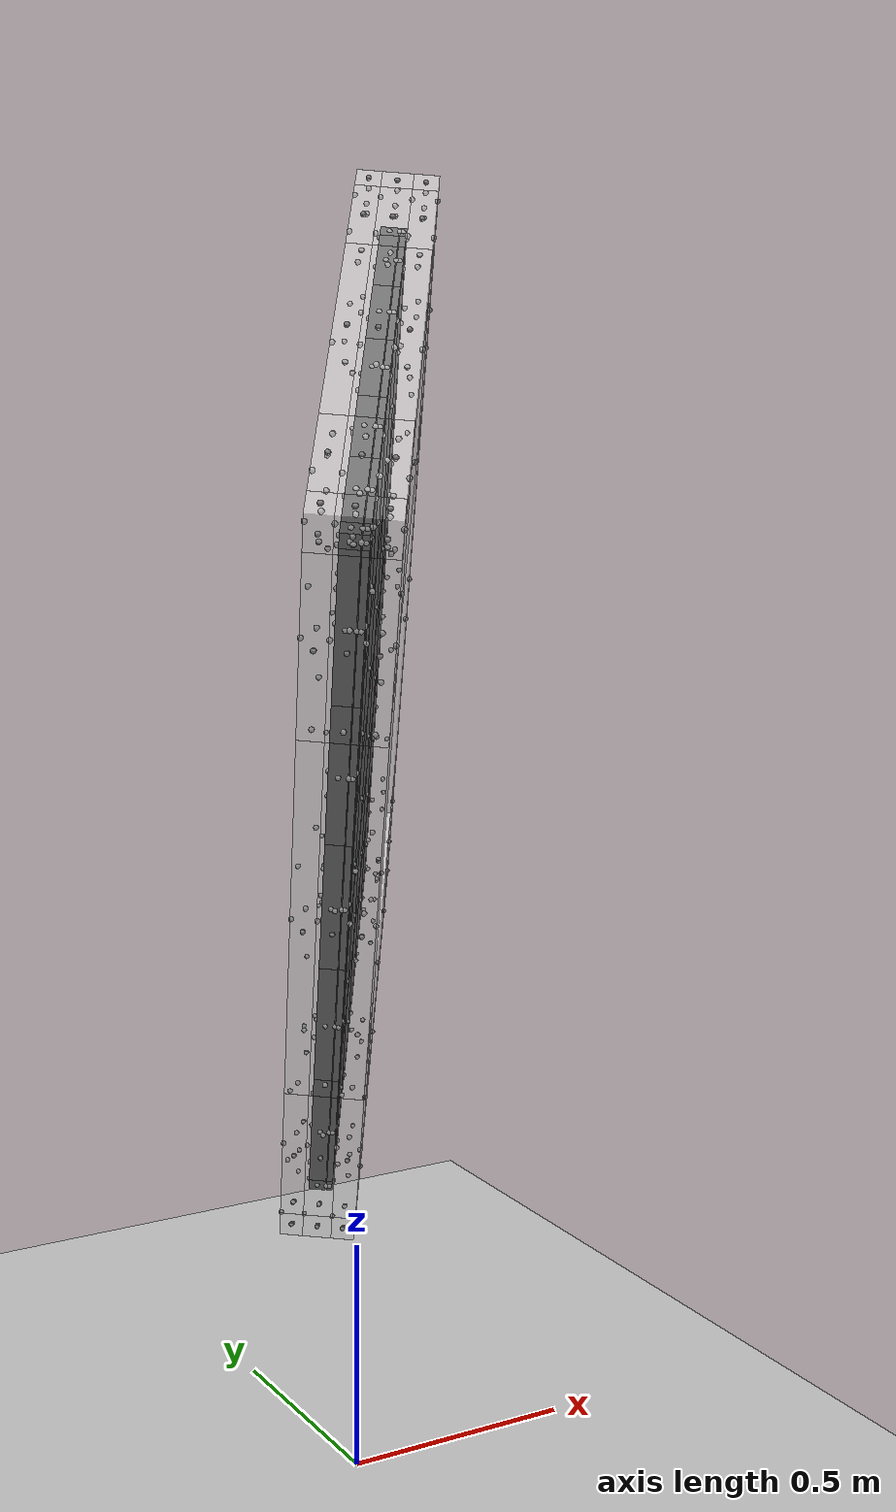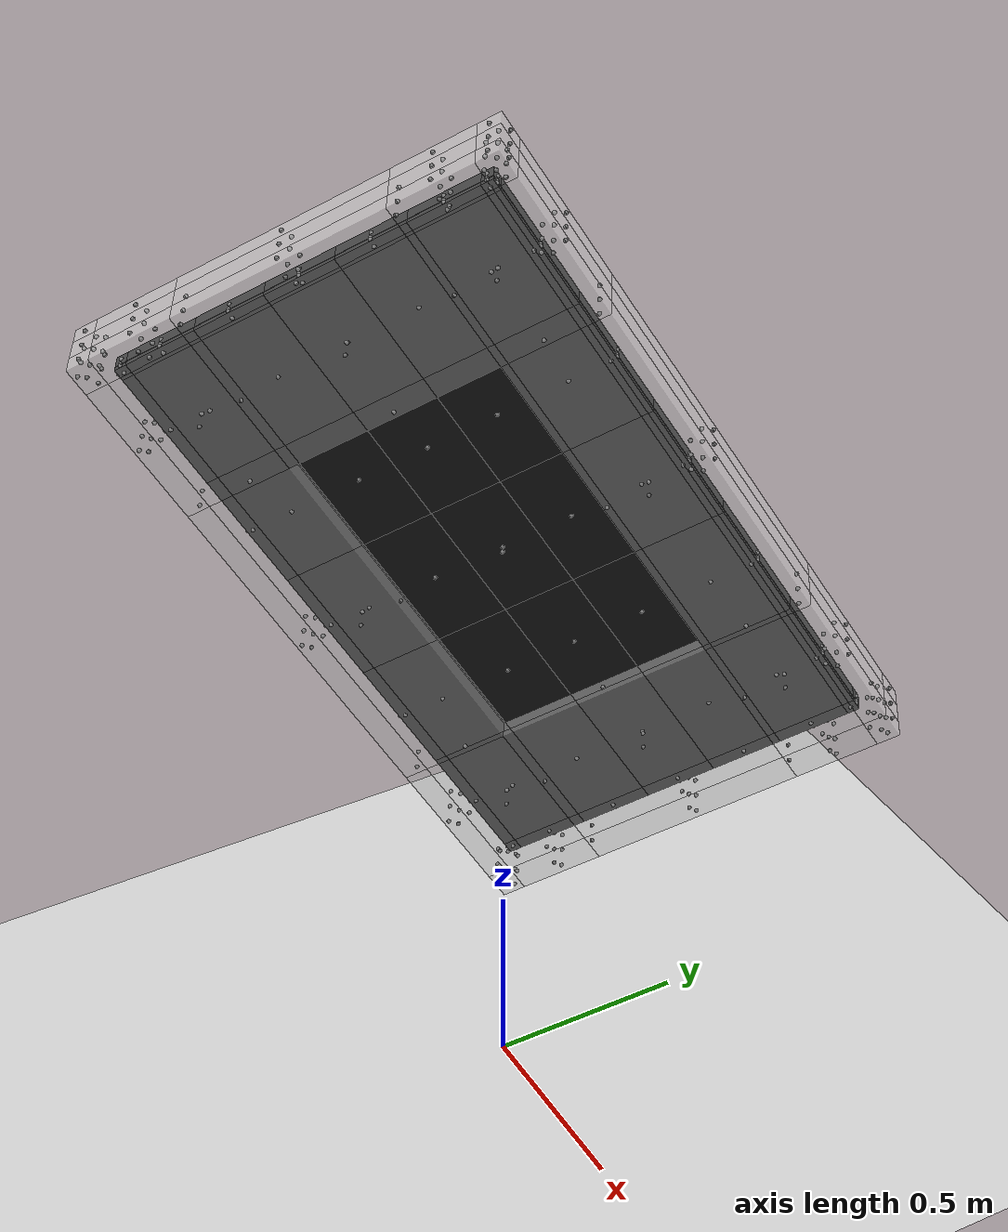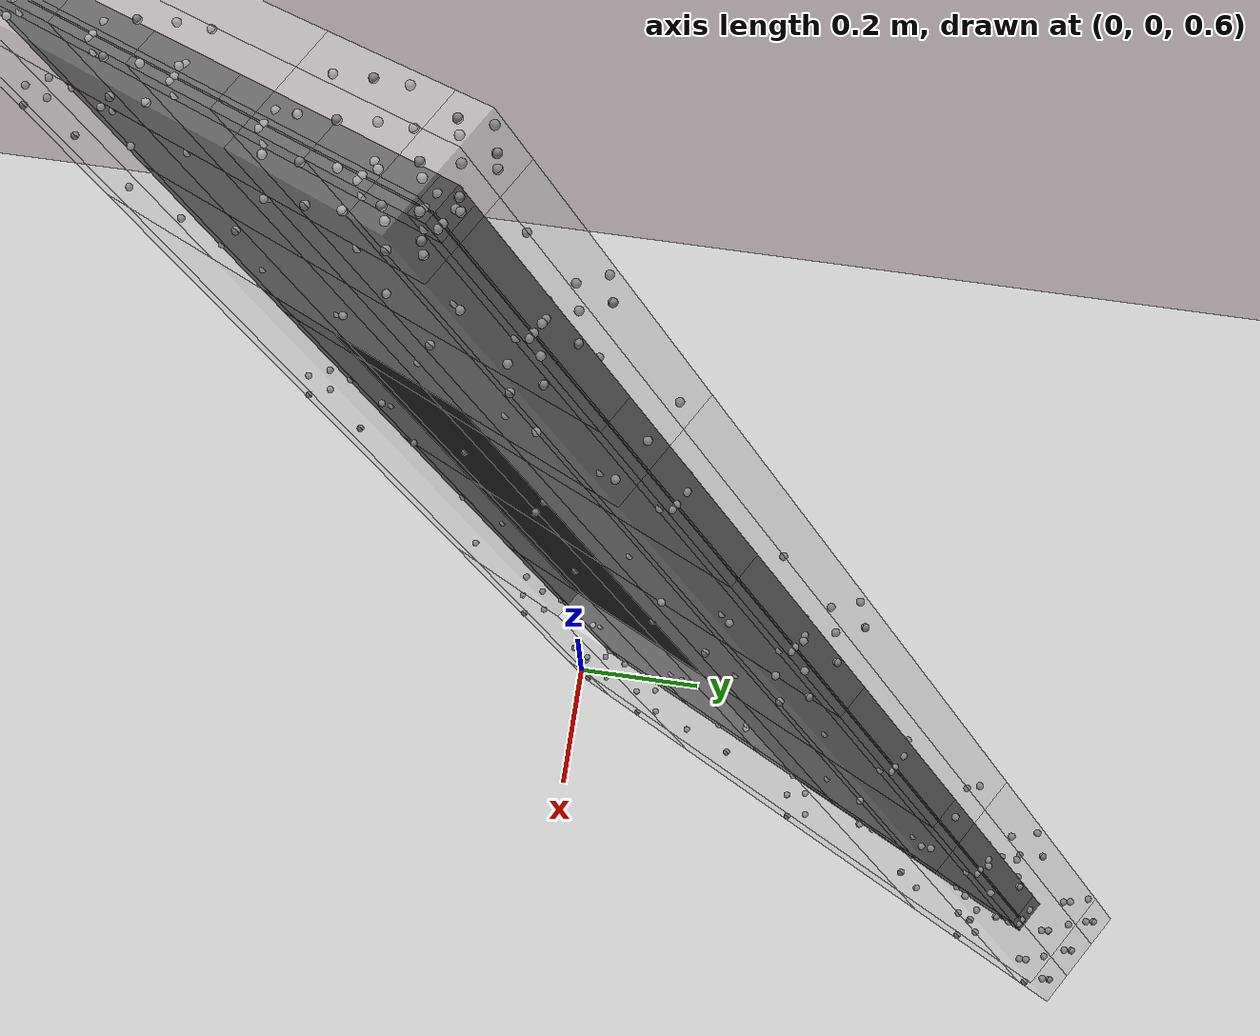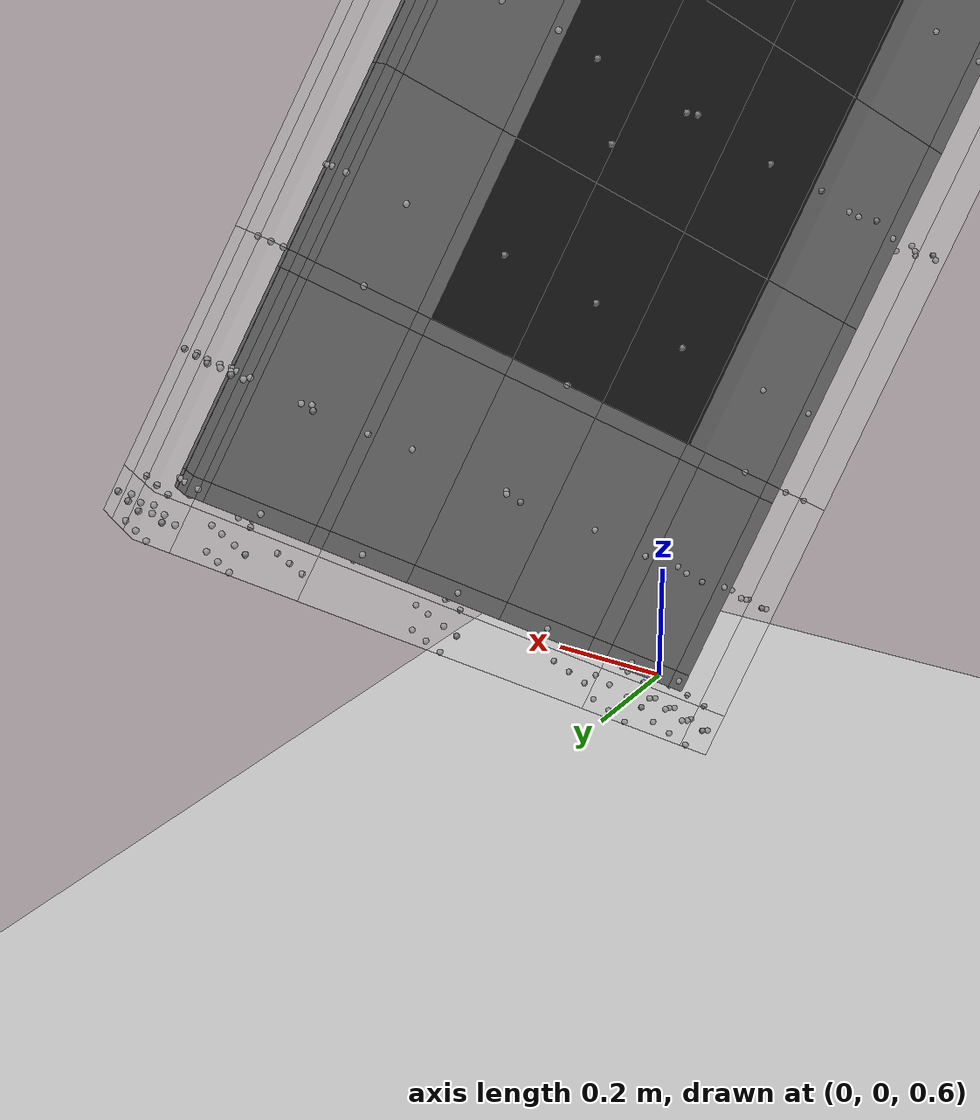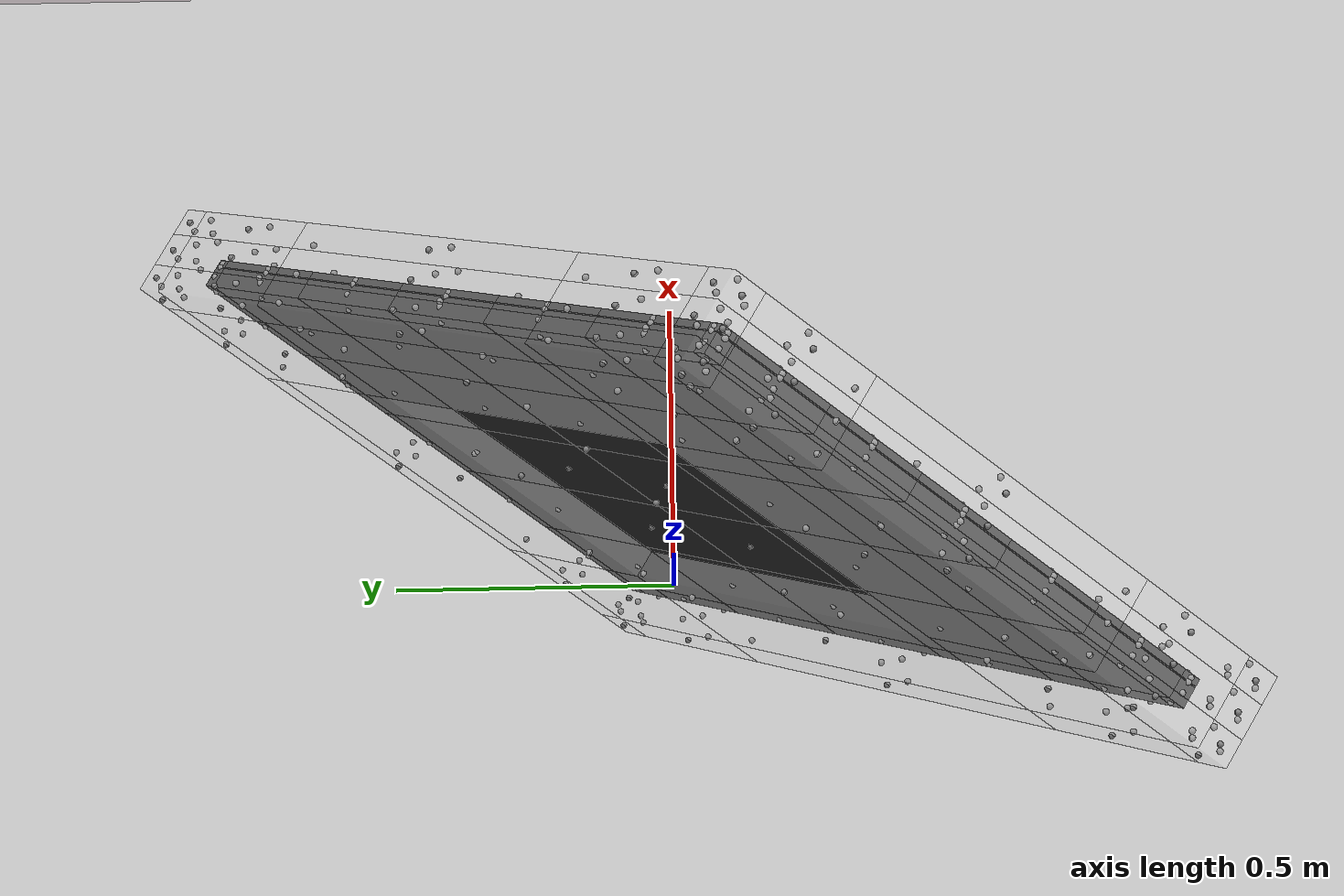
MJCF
<mujoco model="discrete_custom_box">
  <size memory="512M"/>
  <option integrator="implicitfast" timestep="0.0012" iterations="50" noslip_iterations="0" tolerance="1e-05" impratio="1.0" gravity="0 0 -9.81" density="1.225" viscosity="1.81e-05">
    <flag contact="enable"/>
  </option>
  <visual>
    <quality shadowsize="1024"/>
    <global offwidth="0" offheight="0"/>
    <headlight ambient="0.4 0.4 0.4" diffuse="0.8 0.8 0.8" specular="0.07 0.07 0.07"/>
    <map znear="0.01"/>
  </visual>
  <asset>
    <texture type="skybox" builtin="gradient" rgb1="0.3 0.5 0.9" rgb2="0.8 0.9 1.0" width="1024" height="1024"/>
    <texture type="2d" name="ground_tex" builtin="checker" mark="edge" rgb1="0.85 0.85 0.85" rgb2="0.75 0.75 0.75" markrgb="0.8 0.8 0.8" width="300" height="300"/>
    <material name="ground_mat" texture="ground_tex" texrepeat="5 5" texuniform="true" reflectance="0.0"/>
  </asset>
  <default>
    <joint armature="0.05" damping="1.0"/>
    <geom friction="0.8 0.8" solref="0.02 1.0" solimp="0.1 0.95 0.005" condim="3"/>
    <default class="contact_bpaperbox">
      <geom contype="0" conaffinity="0" group="0" rgba="0.5 0.3 0.2 1" condim="3"/>
    </default>
    <default class="contact_bcushion">
      <geom contype="0" conaffinity="0" group="1" rgba="1 1 1 0.4" condim="3"/>
    </default>
    <default class="contact_bcushion_edge">
      <geom contype="0" conaffinity="0" group="1" rgba="1 1 1 0.4" condim="3"/>
    </default>
    <default class="contact_bopencell">
      <geom contype="0" conaffinity="0" group="2" rgba="0.1 0.1 0.1 1" condim="3"/>
    </default>
    <default class="contact_bopencellcohesive">
      <geom contype="0" conaffinity="0" group="2" rgba="1 0.1 0.1 0.4" condim="3"/>
    </default>
    <default class="contact_bchassis">
      <geom contype="0" conaffinity="0" group="2" rgba="0.1 0.1 0.1 1" condim="3"/>
    </default>
    <default class="contact_bauxboxmass">
      <geom contype="0" conaffinity="0" group="3" rgba="0.1 0.1 0.1 1" condim="3"/>
    </default>
    <default class="cls_ground_paper">
      <pair friction="0.3 0.005 0.0001 0.0001 0.0001" solref="0.01 1.0" solimp="0.9 0.95 0.001 0.5 2"/>
    </default>
    <default class="cls_ground_cushion">
      <pair friction="0.1 0.001 0.0001 0.0001 0.0001" solref="0.01 0.8" solimp="0.1 0.95 0.005 0.5 2"/>
    </default>
    <default class="cls_ground_cushion_edge">
      <pair friction="0.1 0.001 0.0001 0.0001 0.0001" solref="0.01 0.8" solimp="0.1 0.95 0.005 0.5 2"/>
    </default>
    <default class="cls_paper_cushion">
      <pair friction="0.2 0.005 0.0001 0.0001 0.0001" solref="0.05 1.0" solimp="0.9 0.95 0.001 0.5 2"/>
    </default>
    <default class="cls_cushion_opencell">
      <pair friction="0.6 0.02 0.0001 0.0001 0.0001" solref="0.03 1.0" solimp="0.8 0.9 0.001 0.5 2"/>
    </default>
    <default class="cls_cushion_chassis">
      <pair friction="0.4 0.01 0.0001 0.0001 0.0001" solref="0.01 1.0" solimp="0.95 0.99 0.001 0.5 2"/>
    </default>
  </default>
  <worldbody>
    <camera name="iso_view" pos="4.5 -4.5 3.5" xyaxes="1 1 0 -0.4 0.4 1" mode="fixed"/>
    <light pos="0 0 6" dir="0 0 -1" directional="false" diffuse="0.8 0.8 0.8" ambient="0.3 0.3 0.3" castshadow="false"/>
    <light pos="3 3 5" dir="-1 -1 -1" directional="false" diffuse="0.4 0.4 0.4" castshadow="false"/>
    <geom name="ground" type="plane" size="2.5 2.5 0.1" friction="0.3 0.3" contype="0" conaffinity="0" group="0" material="ground_mat" solref="0.002 0.01" solimp="0.1 0.95 0.001" condim="3"/>
    <body name="BPackagingBox" pos="0.00000 0.00000 1.57643" axisangle="0.5139 0.8578 0.0000 94.5291">
      <freejoint/>
      <geom type="box" size="0.001 0.001 0.001" mass="0.000021" rgba="0 0 0 0" contype="0" conaffinity="0" friction="0.8"/>
      <body name="BCushion">
        <body name="b_bcushion_0_0_0" pos="-0.87625 -0.51425 -0.05325">
          <joint type="slide" axis="1 0 0"/>
          <joint type="slide" axis="0 1 0"/>
          <joint type="slide" axis="0 0 1"/>
          <joint type="ball"/>
          <geom name="g_bcushion_0_0_0_edge" type="box" size="0.03625 0.02925 0.02375" mass="0.002483" class="contact_bcushion_edge"/>
          <site name="s_BCushion_0_0_0_PX" pos="0.03625 0 0"/>
          <site name="s_BCushion_0_0_0_NX" pos="-0.03625 0 0"/>
          <site name="s_BCushion_0_0_0_PY" pos="0 0.02925 0"/>
          <site name="s_BCushion_0_0_0_NY" pos="0 -0.02925 0"/>
          <site name="s_BCushion_0_0_0_PZ" pos="0 0 0.02375"/>
          <site name="s_BCushion_0_0_0_NZ" pos="0 0 -0.02375"/>
        </body>
        <body name="b_bcushion_0_0_1" pos="-0.87625 -0.51425 0.00000">
          <joint type="slide" axis="1 0 0"/>
          <joint type="slide" axis="0 1 0"/>
          <joint type="slide" axis="0 0 1"/>
          <joint type="ball"/>
          <geom name="g_bcushion_0_0_1_edge" type="box" size="0.03625 0.02925 0.02950" mass="0.003085" class="contact_bcushion_edge"/>
          <site name="s_BCushion_0_0_1_PX" pos="0.03625 0 0"/>
          <site name="s_BCushion_0_0_1_NX" pos="-0.03625 0 0"/>
          <site name="s_BCushion_0_0_1_PY" pos="0 0.02925 0"/>
          <site name="s_BCushion_0_0_1_NY" pos="0 -0.02925 0"/>
          <site name="s_BCushion_0_0_1_PZ" pos="0 0 0.02950"/>
          <site name="s_BCushion_0_0_1_NZ" pos="0 0 -0.02950"/>
        </body>
        <body name="b_bcushion_0_0_2" pos="-0.87625 -0.51425 0.05325">
          <joint type="slide" axis="1 0 0"/>
          <joint type="slide" axis="0 1 0"/>
          <joint type="slide" axis="0 0 1"/>
          <joint type="ball"/>
          <geom name="g_bcushion_0_0_2_edge" type="box" size="0.03625 0.02925 0.02375" mass="0.002483" class="contact_bcushion_edge"/>
          <site name="s_BCushion_0_0_2_PX" pos="0.03625 0 0"/>
          <site name="s_BCushion_0_0_2_NX" pos="-0.03625 0 0"/>
          <site name="s_BCushion_0_0_2_PY" pos="0 0.02925 0"/>
          <site name="s_BCushion_0_0_2_NY" pos="0 -0.02925 0"/>
          <site name="s_BCushion_0_0_2_PZ" pos="0 0 0.02375"/>
          <site name="s_BCushion_0_0_2_NZ" pos="0 0 -0.02375"/>
        </body>
        <body name="b_bcushion_0_1_0" pos="-0.87625 -0.37838 -0.05325">
          <joint type="slide" axis="1 0 0"/>
          <joint type="slide" axis="0 1 0"/>
          <joint type="slide" axis="0 0 1"/>
          <joint type="ball"/>
          <geom name="g_bcushion_0_1_0" type="box" size="0.03625 0.10662 0.02375" mass="0.009053" class="contact_bcushion"/>
          <site name="s_BCushion_0_1_0_PX" pos="0.03625 0 0"/>
          <site name="s_BCushion_0_1_0_NX" pos="-0.03625 0 0"/>
          <site name="s_BCushion_0_1_0_PY" pos="0 0.10662 0"/>
          <site name="s_BCushion_0_1_0_NY" pos="0 -0.10662 0"/>
          <site name="s_BCushion_0_1_0_PZ" pos="0 0 0.02375"/>
          <site name="s_BCushion_0_1_0_NZ" pos="0 0 -0.02375"/>
        </body>
        <body name="b_bcushion_0_1_1" pos="-0.87625 -0.37838 0.00000">
          <joint type="slide" axis="1 0 0"/>
          <joint type="slide" axis="0 1 0"/>
          <joint type="slide" axis="0 0 1"/>
          <joint type="ball"/>
          <geom name="g_bcushion_0_1_1" type="box" size="0.03625 0.10662 0.02950" mass="0.011245" class="contact_bcushion"/>
          <site name="s_BCushion_0_1_1_PX" pos="0.03625 0 0"/>
          <site name="s_BCushion_0_1_1_NX" pos="-0.03625 0 0"/>
          <site name="s_BCushion_0_1_1_PY" pos="0 0.10662 0"/>
          <site name="s_BCushion_0_1_1_NY" pos="0 -0.10662 0"/>
          <site name="s_BCushion_0_1_1_PZ" pos="0 0 0.02950"/>
          <site name="s_BCushion_0_1_1_NZ" pos="0 0 -0.02950"/>
        </body>
        <body name="b_bcushion_0_1_2" pos="-0.87625 -0.37838 0.05325">
          <joint type="slide" axis="1 0 0"/>
          <joint type="slide" axis="0 1 0"/>
          <joint type="slide" axis="0 0 1"/>
          <joint type="ball"/>
          <geom name="g_bcushion_0_1_2" type="box" size="0.03625 0.10662 0.02375" mass="0.009053" class="contact_bcushion"/>
          <site name="s_BCushion_0_1_2_PX" pos="0.03625 0 0"/>
          <site name="s_BCushion_0_1_2_NX" pos="-0.03625 0 0"/>
          <site name="s_BCushion_0_1_2_PY" pos="0 0.10662 0"/>
          <site name="s_BCushion_0_1_2_NY" pos="0 -0.10662 0"/>
          <site name="s_BCushion_0_1_2_PZ" pos="0 0 0.02375"/>
          <site name="s_BCushion_0_1_2_NZ" pos="0 0 -0.02375"/>
        </body>
        <body name="b_bcushion_0_2_0" pos="-0.87625 0.00000 -0.05325">
          <joint type="slide" axis="1 0 0"/>
          <joint type="slide" axis="0 1 0"/>
          <joint type="slide" axis="0 0 1"/>
          <joint type="ball"/>
          <geom name="g_bcushion_0_2_0" type="box" size="0.03625 0.27175 0.02375" mass="0.023073" class="contact_bcushion"/>
          <site name="s_BCushion_0_2_0_PX" pos="0.03625 0 0"/>
          <site name="s_BCushion_0_2_0_NX" pos="-0.03625 0 0"/>
          <site name="s_BCushion_0_2_0_PY" pos="0 0.27175 0"/>
          <site name="s_BCushion_0_2_0_NY" pos="0 -0.27175 0"/>
          <site name="s_BCushion_0_2_0_PZ" pos="0 0 0.02375"/>
          <site name="s_BCushion_0_2_0_NZ" pos="0 0 -0.02375"/>
        </body>
        <body name="b_bcushion_0_2_1" pos="-0.87625 0.00000 0.00000">
          <joint type="slide" axis="1 0 0"/>
          <joint type="slide" axis="0 1 0"/>
          <joint type="slide" axis="0 0 1"/>
          <joint type="ball"/>
          <geom name="g_bcushion_0_2_1" type="box" size="0.03625 0.27175 0.02950" mass="0.028659" class="contact_bcushion"/>
          <site name="s_BCushion_0_2_1_PX" pos="0.03625 0 0"/>
          <site name="s_BCushion_0_2_1_NX" pos="-0.03625 0 0"/>
          <site name="s_BCushion_0_2_1_PY" pos="0 0.27175 0"/>
          <site name="s_BCushion_0_2_1_NY" pos="0 -0.27175 0"/>
          <site name="s_BCushion_0_2_1_PZ" pos="0 0 0.02950"/>
          <site name="s_BCushion_0_2_1_NZ" pos="0 0 -0.02950"/>
        </body>
        <body name="b_bcushion_0_2_2" pos="-0.87625 0.00000 0.05325">
          <joint type="slide" axis="1 0 0"/>
          <joint type="slide" axis="0 1 0"/>
          <joint type="slide" axis="0 0 1"/>
          <joint type="ball"/>
          <geom name="g_bcushion_0_2_2" type="box" size="0.03625 0.27175 0.02375" mass="0.023073" class="contact_bcushion"/>
          <site name="s_BCushion_0_2_2_PX" pos="0.03625 0 0"/>
          <site name="s_BCushion_0_2_2_NX" pos="-0.03625 0 0"/>
          <site name="s_BCushion_0_2_2_PY" pos="0 0.27175 0"/>
          <site name="s_BCushion_0_2_2_NY" pos="0 -0.27175 0"/>
          <site name="s_BCushion_0_2_2_PZ" pos="0 0 0.02375"/>
          <site name="s_BCushion_0_2_2_NZ" pos="0 0 -0.02375"/>
        </body>
        <body name="b_bcushion_0_3_0" pos="-0.87625 0.37838 -0.05325">
          <joint type="slide" axis="1 0 0"/>
          <joint type="slide" axis="0 1 0"/>
          <joint type="slide" axis="0 0 1"/>
          <joint type="ball"/>
          <geom name="g_bcushion_0_3_0" type="box" size="0.03625 0.10662 0.02375" mass="0.009053" class="contact_bcushion"/>
          <site name="s_BCushion_0_3_0_PX" pos="0.03625 0 0"/>
          <site name="s_BCushion_0_3_0_NX" pos="-0.03625 0 0"/>
          <site name="s_BCushion_0_3_0_PY" pos="0 0.10662 0"/>
          <site name="s_BCushion_0_3_0_NY" pos="0 -0.10662 0"/>
          <site name="s_BCushion_0_3_0_PZ" pos="0 0 0.02375"/>
          <site name="s_BCushion_0_3_0_NZ" pos="0 0 -0.02375"/>
        </body>
        <body name="b_bcushion_0_3_1" pos="-0.87625 0.37838 0.00000">
          <joint type="slide" axis="1 0 0"/>
          <joint type="slide" axis="0 1 0"/>
          <joint type="slide" axis="0 0 1"/>
          <joint type="ball"/>
          <geom name="g_bcushion_0_3_1" type="box" size="0.03625 0.10662 0.02950" mass="0.011245" class="contact_bcushion"/>
          <site name="s_BCushion_0_3_1_PX" pos="0.03625 0 0"/>
          <site name="s_BCushion_0_3_1_NX" pos="-0.03625 0 0"/>
          <site name="s_BCushion_0_3_1_PY" pos="0 0.10662 0"/>
          <site name="s_BCushion_0_3_1_NY" pos="0 -0.10662 0"/>
          <site name="s_BCushion_0_3_1_PZ" pos="0 0 0.02950"/>
          <site name="s_BCushion_0_3_1_NZ" pos="0 0 -0.02950"/>
        </body>
        <body name="b_bcushion_0_3_2" pos="-0.87625 0.37838 0.05325">
          <joint type="slide" axis="1 0 0"/>
          <joint type="slide" axis="0 1 0"/>
          <joint type="slide" axis="0 0 1"/>
          <joint type="ball"/>
          <geom name="g_bcushion_0_3_2" type="box" size="0.03625 0.10662 0.02375" mass="0.009053" class="contact_bcushion"/>
          <site name="s_BCushion_0_3_2_PX" pos="0.03625 0 0"/>
          <site name="s_BCushion_0_3_2_NX" pos="-0.03625 0 0"/>
          <site name="s_BCushion_0_3_2_PY" pos="0 0.10662 0"/>
          <site name="s_BCushion_0_3_2_NY" pos="0 -0.10662 0"/>
          <site name="s_BCushion_0_3_2_PZ" pos="0 0 0.02375"/>
          <site name="s_BCushion_0_3_2_NZ" pos="0 0 -0.02375"/>
        </body>
        <body name="b_bcushion_0_4_0" pos="-0.87625 0.51425 -0.05325">
          <joint type="slide" axis="1 0 0"/>
          <joint type="slide" axis="0 1 0"/>
          <joint type="slide" axis="0 0 1"/>
          <joint type="ball"/>
          <geom name="g_bcushion_0_4_0_edge" type="box" size="0.03625 0.02925 0.02375" mass="0.002483" class="contact_bcushion_edge"/>
          <site name="s_BCushion_0_4_0_PX" pos="0.03625 0 0"/>
          <site name="s_BCushion_0_4_0_NX" pos="-0.03625 0 0"/>
          <site name="s_BCushion_0_4_0_PY" pos="0 0.02925 0"/>
          <site name="s_BCushion_0_4_0_NY" pos="0 -0.02925 0"/>
          <site name="s_BCushion_0_4_0_PZ" pos="0 0 0.02375"/>
          <site name="s_BCushion_0_4_0_NZ" pos="0 0 -0.02375"/>
        </body>
        <body name="b_bcushion_0_4_1" pos="-0.87625 0.51425 0.00000">
          <joint type="slide" axis="1 0 0"/>
          <joint type="slide" axis="0 1 0"/>
          <joint type="slide" axis="0 0 1"/>
          <joint type="ball"/>
          <geom name="g_bcushion_0_4_1_edge" type="box" size="0.03625 0.02925 0.02950" mass="0.003085" class="contact_bcushion_edge"/>
          <site name="s_BCushion_0_4_1_PX" pos="0.03625 0 0"/>
          <site name="s_BCushion_0_4_1_NX" pos="-0.03625 0 0"/>
          <site name="s_BCushion_0_4_1_PY" pos="0 0.02925 0"/>
          <site name="s_BCushion_0_4_1_NY" pos="0 -0.02925 0"/>
          <site name="s_BCushion_0_4_1_PZ" pos="0 0 0.02950"/>
          <site name="s_BCushion_0_4_1_NZ" pos="0 0 -0.02950"/>
        </body>
        <body name="b_bcushion_0_4_2" pos="-0.87625 0.51425 0.05325">
          <joint type="slide" axis="1 0 0"/>
          <joint type="slide" axis="0 1 0"/>
          <joint type="slide" axis="0 0 1"/>
          <joint type="ball"/>
          <geom name="g_bcushion_0_4_2_edge" type="box" size="0.03625 0.02925 0.02375" mass="0.002483" class="contact_bcushion_edge"/>
          <site name="s_BCushion_0_4_2_PX" pos="0.03625 0 0"/>
          <site name="s_BCushion_0_4_2_NX" pos="-0.03625 0 0"/>
          <site name="s_BCushion_0_4_2_PY" pos="0 0.02925 0"/>
          <site name="s_BCushion_0_4_2_NY" pos="0 -0.02925 0"/>
          <site name="s_BCushion_0_4_2_PZ" pos="0 0 0.02375"/>
          <site name="s_BCushion_0_4_2_NZ" pos="0 0 -0.02375"/>
        </body>
        <body name="b_bcushion_1_0_0" pos="-0.64812 -0.51425 -0.05325">
          <joint type="slide" axis="1 0 0"/>
          <joint type="slide" axis="0 1 0"/>
          <joint type="slide" axis="0 0 1"/>
          <joint type="ball"/>
          <geom name="g_bcushion_1_0_0" type="box" size="0.19187 0.02925 0.02375" mass="0.013145" class="contact_bcushion"/>
          <site name="s_BCushion_1_0_0_PX" pos="0.19187 0 0"/>
          <site name="s_BCushion_1_0_0_NX" pos="-0.19187 0 0"/>
          <site name="s_BCushion_1_0_0_PY" pos="0 0.02925 0"/>
          <site name="s_BCushion_1_0_0_NY" pos="0 -0.02925 0"/>
          <site name="s_BCushion_1_0_0_PZ" pos="0 0 0.02375"/>
          <site name="s_BCushion_1_0_0_NZ" pos="0 0 -0.02375"/>
        </body>
        <body name="b_bcushion_1_0_1" pos="-0.64812 -0.51425 0.00000">
          <joint type="slide" axis="1 0 0"/>
          <joint type="slide" axis="0 1 0"/>
          <joint type="slide" axis="0 0 1"/>
          <joint type="ball"/>
          <geom name="g_bcushion_1_0_1" type="box" size="0.19187 0.02925 0.02950" mass="0.016328" class="contact_bcushion"/>
          <site name="s_BCushion_1_0_1_PX" pos="0.19187 0 0"/>
          <site name="s_BCushion_1_0_1_NX" pos="-0.19187 0 0"/>
          <site name="s_BCushion_1_0_1_PY" pos="0 0.02925 0"/>
          <site name="s_BCushion_1_0_1_NY" pos="0 -0.02925 0"/>
          <site name="s_BCushion_1_0_1_PZ" pos="0 0 0.02950"/>
          <site name="s_BCushion_1_0_1_NZ" pos="0 0 -0.02950"/>
        </body>
        <body name="b_bcushion_1_0_2" pos="-0.64812 -0.51425 0.05325">
          <joint type="slide" axis="1 0 0"/>
          <joint type="slide" axis="0 1 0"/>
          <joint type="slide" axis="0 0 1"/>
          <joint type="ball"/>
          <geom name="g_bcushion_1_0_2" type="box" size="0.19187 0.02925 0.02375" mass="0.013145" class="contact_bcushion"/>
          <site name="s_BCushion_1_0_2_PX" pos="0.19187 0 0"/>
          <site name="s_BCushion_1_0_2_NX" pos="-0.19187 0 0"/>
          <site name="s_BCushion_1_0_2_PY" pos="0 0.02925 0"/>
          <site name="s_BCushion_1_0_2_NY" pos="0 -0.02925 0"/>
          <site name="s_BCushion_1_0_2_PZ" pos="0 0 0.02375"/>
          <site name="s_BCushion_1_0_2_NZ" pos="0 0 -0.02375"/>
        </body>
        <body name="b_bcushion_1_1_0" pos="-0.64812 -0.37838 -0.05325">
          <joint type="slide" axis="1 0 0"/>
          <joint type="slide" axis="0 1 0"/>
          <joint type="slide" axis="0 0 1"/>
          <joint type="ball"/>
          <geom name="g_bcushion_1_1_0" type="box" size="0.19187 0.10662 0.02375" mass="0.047918" class="contact_bcushion"/>
          <site name="s_BCushion_1_1_0_PX" pos="0.19187 0 0"/>
          <site name="s_BCushion_1_1_0_NX" pos="-0.19187 0 0"/>
          <site name="s_BCushion_1_1_0_PY" pos="0 0.10662 0"/>
          <site name="s_BCushion_1_1_0_NY" pos="0 -0.10662 0"/>
          <site name="s_BCushion_1_1_0_PZ" pos="0 0 0.02375"/>
          <site name="s_BCushion_1_1_0_NZ" pos="0 0 -0.02375"/>
        </body>
        <body name="b_bcushion_1_1_2" pos="-0.64812 -0.37838 0.05325">
          <joint type="slide" axis="1 0 0"/>
          <joint type="slide" axis="0 1 0"/>
          <joint type="slide" axis="0 0 1"/>
          <joint type="ball"/>
          <geom name="g_bcushion_1_1_2" type="box" size="0.19187 0.10662 0.02375" mass="0.047918" class="contact_bcushion"/>
          <site name="s_BCushion_1_1_2_PX" pos="0.19187 0 0"/>
          <site name="s_BCushion_1_1_2_NX" pos="-0.19187 0 0"/>
          <site name="s_BCushion_1_1_2_PY" pos="0 0.10662 0"/>
          <site name="s_BCushion_1_1_2_NY" pos="0 -0.10662 0"/>
          <site name="s_BCushion_1_1_2_PZ" pos="0 0 0.02375"/>
          <site name="s_BCushion_1_1_2_NZ" pos="0 0 -0.02375"/>
        </body>
        <body name="b_bcushion_1_2_0" pos="-0.64812 0.00000 -0.05325">
          <joint type="slide" axis="1 0 0"/>
          <joint type="slide" axis="0 1 0"/>
          <joint type="slide" axis="0 0 1"/>
          <joint type="ball"/>
          <geom name="g_bcushion_1_2_0" type="box" size="0.19187 0.27175 0.02375" mass="0.122127" class="contact_bcushion"/>
          <site name="s_BCushion_1_2_0_PX" pos="0.19187 0 0"/>
          <site name="s_BCushion_1_2_0_NX" pos="-0.19187 0 0"/>
          <site name="s_BCushion_1_2_0_PY" pos="0 0.27175 0"/>
          <site name="s_BCushion_1_2_0_NY" pos="0 -0.27175 0"/>
          <site name="s_BCushion_1_2_0_PZ" pos="0 0 0.02375"/>
          <site name="s_BCushion_1_2_0_NZ" pos="0 0 -0.02375"/>
        </body>
        <body name="b_bcushion_1_2_2" pos="-0.64812 0.00000 0.05325">
          <joint type="slide" axis="1 0 0"/>
          <joint type="slide" axis="0 1 0"/>
          <joint type="slide" axis="0 0 1"/>
          <joint type="ball"/>
          <geom name="g_bcushion_1_2_2" type="box" size="0.19187 0.27175 0.02375" mass="0.122127" class="contact_bcushion"/>
          <site name="s_BCushion_1_2_2_PX" pos="0.19187 0 0"/>
          <site name="s_BCushion_1_2_2_NX" pos="-0.19187 0 0"/>
          <site name="s_BCushion_1_2_2_PY" pos="0 0.27175 0"/>
          <site name="s_BCushion_1_2_2_NY" pos="0 -0.27175 0"/>
          <site name="s_BCushion_1_2_2_PZ" pos="0 0 0.02375"/>
          <site name="s_BCushion_1_2_2_NZ" pos="0 0 -0.02375"/>
        </body>
        <body name="b_bcushion_1_3_0" pos="-0.64812 0.37838 -0.05325">
          <joint type="slide" axis="1 0 0"/>
          <joint type="slide" axis="0 1 0"/>
          <joint type="slide" axis="0 0 1"/>
          <joint type="ball"/>
          <geom name="g_bcushion_1_3_0" type="box" size="0.19187 0.10662 0.02375" mass="0.047918" class="contact_bcushion"/>
          <site name="s_BCushion_1_3_0_PX" pos="0.19187 0 0"/>
          <site name="s_BCushion_1_3_0_NX" pos="-0.19187 0 0"/>
          <site name="s_BCushion_1_3_0_PY" pos="0 0.10662 0"/>
          <site name="s_BCushion_1_3_0_NY" pos="0 -0.10662 0"/>
          <site name="s_BCushion_1_3_0_PZ" pos="0 0 0.02375"/>
          <site name="s_BCushion_1_3_0_NZ" pos="0 0 -0.02375"/>
        </body>
        <body name="b_bcushion_1_3_2" pos="-0.64812 0.37838 0.05325">
          <joint type="slide" axis="1 0 0"/>
          <joint type="slide" axis="0 1 0"/>
          <joint type="slide" axis="0 0 1"/>
          <joint type="ball"/>
          <geom name="g_bcushion_1_3_2" type="box" size="0.19187 0.10662 0.02375" mass="0.047918" class="contact_bcushion"/>
          <site name="s_BCushion_1_3_2_PX" pos="0.19187 0 0"/>
          <site name="s_BCushion_1_3_2_NX" pos="-0.19187 0 0"/>
          <site name="s_BCushion_1_3_2_PY" pos="0 0.10662 0"/>
          <site name="s_BCushion_1_3_2_NY" pos="0 -0.10662 0"/>
          <site name="s_BCushion_1_3_2_PZ" pos="0 0 0.02375"/>
          <site name="s_BCushion_1_3_2_NZ" pos="0 0 -0.02375"/>
        </body>
        <body name="b_bcushion_1_4_0" pos="-0.64812 0.51425 -0.05325">
          <joint type="slide" axis="1 0 0"/>
          <joint type="slide" axis="0 1 0"/>
          <joint type="slide" axis="0 0 1"/>
          <joint type="ball"/>
          <geom name="g_bcushion_1_4_0" type="box" size="0.19187 0.02925 0.02375" mass="0.013145" class="contact_bcushion"/>
          <site name="s_BCushion_1_4_0_PX" pos="0.19187 0 0"/>
          <site name="s_BCushion_1_4_0_NX" pos="-0.19187 0 0"/>
          <site name="s_BCushion_1_4_0_PY" pos="0 0.02925 0"/>
          <site name="s_BCushion_1_4_0_NY" pos="0 -0.02925 0"/>
          <site name="s_BCushion_1_4_0_PZ" pos="0 0 0.02375"/>
          <site name="s_BCushion_1_4_0_NZ" pos="0 0 -0.02375"/>
        </body>
        <body name="b_bcushion_1_4_1" pos="-0.64812 0.51425 0.00000">
          <joint type="slide" axis="1 0 0"/>
          <joint type="slide" axis="0 1 0"/>
          <joint type="slide" axis="0 0 1"/>
          <joint type="ball"/>
          <geom name="g_bcushion_1_4_1" type="box" size="0.19187 0.02925 0.02950" mass="0.016328" class="contact_bcushion"/>
          <site name="s_BCushion_1_4_1_PX" pos="0.19187 0 0"/>
          <site name="s_BCushion_1_4_1_NX" pos="-0.19187 0 0"/>
          <site name="s_BCushion_1_4_1_PY" pos="0 0.02925 0"/>
          <site name="s_BCushion_1_4_1_NY" pos="0 -0.02925 0"/>
          <site name="s_BCushion_1_4_1_PZ" pos="0 0 0.02950"/>
          <site name="s_BCushion_1_4_1_NZ" pos="0 0 -0.02950"/>
        </body>
        <body name="b_bcushion_1_4_2" pos="-0.64812 0.51425 0.05325">
          <joint type="slide" axis="1 0 0"/>
          <joint type="slide" axis="0 1 0"/>
          <joint type="slide" axis="0 0 1"/>
          <joint type="ball"/>
          <geom name="g_bcushion_1_4_2" type="box" size="0.19187 0.02925 0.02375" mass="0.013145" class="contact_bcushion"/>
          <site name="s_BCushion_1_4_2_PX" pos="0.19187 0 0"/>
          <site name="s_BCushion_1_4_2_NX" pos="-0.19187 0 0"/>
          <site name="s_BCushion_1_4_2_PY" pos="0 0.02925 0"/>
          <site name="s_BCushion_1_4_2_NY" pos="0 -0.02925 0"/>
          <site name="s_BCushion_1_4_2_PZ" pos="0 0 0.02375"/>
          <site name="s_BCushion_1_4_2_NZ" pos="0 0 -0.02375"/>
        </body>
        <body name="b_bcushion_2_0_0" pos="0.00000 -0.51425 -0.05325">
          <joint type="slide" axis="1 0 0"/>
          <joint type="slide" axis="0 1 0"/>
          <joint type="slide" axis="0 0 1"/>
          <joint type="ball"/>
          <geom name="g_bcushion_2_0_0" type="box" size="0.45625 0.02925 0.02375" mass="0.031257" class="contact_bcushion"/>
          <site name="s_BCushion_2_0_0_PX" pos="0.45625 0 0"/>
          <site name="s_BCushion_2_0_0_NX" pos="-0.45625 0 0"/>
          <site name="s_BCushion_2_0_0_PY" pos="0 0.02925 0"/>
          <site name="s_BCushion_2_0_0_NY" pos="0 -0.02925 0"/>
          <site name="s_BCushion_2_0_0_PZ" pos="0 0 0.02375"/>
          <site name="s_BCushion_2_0_0_NZ" pos="0 0 -0.02375"/>
        </body>
        <body name="b_bcushion_2_0_1" pos="0.00000 -0.51425 0.00000">
          <joint type="slide" axis="1 0 0"/>
          <joint type="slide" axis="0 1 0"/>
          <joint type="slide" axis="0 0 1"/>
          <joint type="ball"/>
          <geom name="g_bcushion_2_0_1" type="box" size="0.45625 0.02925 0.02950" mass="0.038825" class="contact_bcushion"/>
          <site name="s_BCushion_2_0_1_PX" pos="0.45625 0 0"/>
          <site name="s_BCushion_2_0_1_NX" pos="-0.45625 0 0"/>
          <site name="s_BCushion_2_0_1_PY" pos="0 0.02925 0"/>
          <site name="s_BCushion_2_0_1_NY" pos="0 -0.02925 0"/>
          <site name="s_BCushion_2_0_1_PZ" pos="0 0 0.02950"/>
          <site name="s_BCushion_2_0_1_NZ" pos="0 0 -0.02950"/>
        </body>
        <body name="b_bcushion_2_0_2" pos="0.00000 -0.51425 0.05325">
          <joint type="slide" axis="1 0 0"/>
          <joint type="slide" axis="0 1 0"/>
          <joint type="slide" axis="0 0 1"/>
          <joint type="ball"/>
          <geom name="g_bcushion_2_0_2" type="box" size="0.45625 0.02925 0.02375" mass="0.031257" class="contact_bcushion"/>
          <site name="s_BCushion_2_0_2_PX" pos="0.45625 0 0"/>
          <site name="s_BCushion_2_0_2_NX" pos="-0.45625 0 0"/>
          <site name="s_BCushion_2_0_2_PY" pos="0 0.02925 0"/>
          <site name="s_BCushion_2_0_2_NY" pos="0 -0.02925 0"/>
          <site name="s_BCushion_2_0_2_PZ" pos="0 0 0.02375"/>
          <site name="s_BCushion_2_0_2_NZ" pos="0 0 -0.02375"/>
        </body>
        <body name="b_bcushion_2_1_0" pos="0.00000 -0.37838 -0.05325">
          <joint type="slide" axis="1 0 0"/>
          <joint type="slide" axis="0 1 0"/>
          <joint type="slide" axis="0 0 1"/>
          <joint type="ball"/>
          <geom name="g_bcushion_2_1_0" type="box" size="0.45625 0.10662 0.02375" mass="0.113943" class="contact_bcushion"/>
          <site name="s_BCushion_2_1_0_PX" pos="0.45625 0 0"/>
          <site name="s_BCushion_2_1_0_NX" pos="-0.45625 0 0"/>
          <site name="s_BCushion_2_1_0_PY" pos="0 0.10662 0"/>
          <site name="s_BCushion_2_1_0_NY" pos="0 -0.10662 0"/>
          <site name="s_BCushion_2_1_0_PZ" pos="0 0 0.02375"/>
          <site name="s_BCushion_2_1_0_NZ" pos="0 0 -0.02375"/>
        </body>
        <body name="b_bcushion_2_1_2" pos="0.00000 -0.37838 0.05325">
          <joint type="slide" axis="1 0 0"/>
          <joint type="slide" axis="0 1 0"/>
          <joint type="slide" axis="0 0 1"/>
          <joint type="ball"/>
          <geom name="g_bcushion_2_1_2" type="box" size="0.45625 0.10662 0.02375" mass="0.113943" class="contact_bcushion"/>
          <site name="s_BCushion_2_1_2_PX" pos="0.45625 0 0"/>
          <site name="s_BCushion_2_1_2_NX" pos="-0.45625 0 0"/>
          <site name="s_BCushion_2_1_2_PY" pos="0 0.10662 0"/>
          <site name="s_BCushion_2_1_2_NY" pos="0 -0.10662 0"/>
          <site name="s_BCushion_2_1_2_PZ" pos="0 0 0.02375"/>
          <site name="s_BCushion_2_1_2_NZ" pos="0 0 -0.02375"/>
        </body>
        <body name="b_bcushion_2_3_0" pos="0.00000 0.37838 -0.05325">
          <joint type="slide" axis="1 0 0"/>
          <joint type="slide" axis="0 1 0"/>
          <joint type="slide" axis="0 0 1"/>
          <joint type="ball"/>
          <geom name="g_bcushion_2_3_0" type="box" size="0.45625 0.10662 0.02375" mass="0.113943" class="contact_bcushion"/>
          <site name="s_BCushion_2_3_0_PX" pos="0.45625 0 0"/>
          <site name="s_BCushion_2_3_0_NX" pos="-0.45625 0 0"/>
          <site name="s_BCushion_2_3_0_PY" pos="0 0.10662 0"/>
          <site name="s_BCushion_2_3_0_NY" pos="0 -0.10662 0"/>
          <site name="s_BCushion_2_3_0_PZ" pos="0 0 0.02375"/>
          <site name="s_BCushion_2_3_0_NZ" pos="0 0 -0.02375"/>
        </body>
        <body name="b_bcushion_2_3_2" pos="0.00000 0.37838 0.05325">
          <joint type="slide" axis="1 0 0"/>
          <joint type="slide" axis="0 1 0"/>
          <joint type="slide" axis="0 0 1"/>
          <joint type="ball"/>
          <geom name="g_bcushion_2_3_2" type="box" size="0.45625 0.10662 0.02375" mass="0.113943" class="contact_bcushion"/>
          <site name="s_BCushion_2_3_2_PX" pos="0.45625 0 0"/>
          <site name="s_BCushion_2_3_2_NX" pos="-0.45625 0 0"/>
          <site name="s_BCushion_2_3_2_PY" pos="0 0.10662 0"/>
          <site name="s_BCushion_2_3_2_NY" pos="0 -0.10662 0"/>
          <site name="s_BCushion_2_3_2_PZ" pos="0 0 0.02375"/>
          <site name="s_BCushion_2_3_2_NZ" pos="0 0 -0.02375"/>
        </body>
        <body name="b_bcushion_2_4_0" pos="0.00000 0.51425 -0.05325">
          <joint type="slide" axis="1 0 0"/>
          <joint type="slide" axis="0 1 0"/>
          <joint type="slide" axis="0 0 1"/>
          <joint type="ball"/>
          <geom name="g_bcushion_2_4_0" type="box" size="0.45625 0.02925 0.02375" mass="0.031257" class="contact_bcushion"/>
          <site name="s_BCushion_2_4_0_PX" pos="0.45625 0 0"/>
          <site name="s_BCushion_2_4_0_NX" pos="-0.45625 0 0"/>
          <site name="s_BCushion_2_4_0_PY" pos="0 0.02925 0"/>
          <site name="s_BCushion_2_4_0_NY" pos="0 -0.02925 0"/>
          <site name="s_BCushion_2_4_0_PZ" pos="0 0 0.02375"/>
          <site name="s_BCushion_2_4_0_NZ" pos="0 0 -0.02375"/>
        </body>
        <body name="b_bcushion_2_4_1" pos="0.00000 0.51425 0.00000">
          <joint type="slide" axis="1 0 0"/>
          <joint type="slide" axis="0 1 0"/>
          <joint type="slide" axis="0 0 1"/>
          <joint type="ball"/>
          <geom name="g_bcushion_2_4_1" type="box" size="0.45625 0.02925 0.02950" mass="0.038825" class="contact_bcushion"/>
          <site name="s_BCushion_2_4_1_PX" pos="0.45625 0 0"/>
          <site name="s_BCushion_2_4_1_NX" pos="-0.45625 0 0"/>
          <site name="s_BCushion_2_4_1_PY" pos="0 0.02925 0"/>
          <site name="s_BCushion_2_4_1_NY" pos="0 -0.02925 0"/>
          <site name="s_BCushion_2_4_1_PZ" pos="0 0 0.02950"/>
          <site name="s_BCushion_2_4_1_NZ" pos="0 0 -0.02950"/>
        </body>
        <body name="b_bcushion_2_4_2" pos="0.00000 0.51425 0.05325">
          <joint type="slide" axis="1 0 0"/>
          <joint type="slide" axis="0 1 0"/>
          <joint type="slide" axis="0 0 1"/>
          <joint type="ball"/>
          <geom name="g_bcushion_2_4_2" type="box" size="0.45625 0.02925 0.02375" mass="0.031257" class="contact_bcushion"/>
          <site name="s_BCushion_2_4_2_PX" pos="0.45625 0 0"/>
          <site name="s_BCushion_2_4_2_NX" pos="-0.45625 0 0"/>
          <site name="s_BCushion_2_4_2_PY" pos="0 0.02925 0"/>
          <site name="s_BCushion_2_4_2_NY" pos="0 -0.02925 0"/>
          <site name="s_BCushion_2_4_2_PZ" pos="0 0 0.02375"/>
          <site name="s_BCushion_2_4_2_NZ" pos="0 0 -0.02375"/>
        </body>
        <body name="b_bcushion_3_0_0" pos="0.64812 -0.51425 -0.05325">
          <joint type="slide" axis="1 0 0"/>
          <joint type="slide" axis="0 1 0"/>
          <joint type="slide" axis="0 0 1"/>
          <joint type="ball"/>
          <geom name="g_bcushion_3_0_0" type="box" size="0.19187 0.02925 0.02375" mass="0.013145" class="contact_bcushion"/>
          <site name="s_BCushion_3_0_0_PX" pos="0.19187 0 0"/>
          <site name="s_BCushion_3_0_0_NX" pos="-0.19187 0 0"/>
          <site name="s_BCushion_3_0_0_PY" pos="0 0.02925 0"/>
          <site name="s_BCushion_3_0_0_NY" pos="0 -0.02925 0"/>
          <site name="s_BCushion_3_0_0_PZ" pos="0 0 0.02375"/>
          <site name="s_BCushion_3_0_0_NZ" pos="0 0 -0.02375"/>
        </body>
        <body name="b_bcushion_3_0_1" pos="0.64812 -0.51425 0.00000">
          <joint type="slide" axis="1 0 0"/>
          <joint type="slide" axis="0 1 0"/>
          <joint type="slide" axis="0 0 1"/>
          <joint type="ball"/>
          <geom name="g_bcushion_3_0_1" type="box" size="0.19187 0.02925 0.02950" mass="0.016328" class="contact_bcushion"/>
          <site name="s_BCushion_3_0_1_PX" pos="0.19187 0 0"/>
          <site name="s_BCushion_3_0_1_NX" pos="-0.19187 0 0"/>
          <site name="s_BCushion_3_0_1_PY" pos="0 0.02925 0"/>
          <site name="s_BCushion_3_0_1_NY" pos="0 -0.02925 0"/>
          <site name="s_BCushion_3_0_1_PZ" pos="0 0 0.02950"/>
          <site name="s_BCushion_3_0_1_NZ" pos="0 0 -0.02950"/>
        </body>
        <body name="b_bcushion_3_0_2" pos="0.64812 -0.51425 0.05325">
          <joint type="slide" axis="1 0 0"/>
          <joint type="slide" axis="0 1 0"/>
          <joint type="slide" axis="0 0 1"/>
          <joint type="ball"/>
          <geom name="g_bcushion_3_0_2" type="box" size="0.19187 0.02925 0.02375" mass="0.013145" class="contact_bcushion"/>
          <site name="s_BCushion_3_0_2_PX" pos="0.19187 0 0"/>
          <site name="s_BCushion_3_0_2_NX" pos="-0.19187 0 0"/>
          <site name="s_BCushion_3_0_2_PY" pos="0 0.02925 0"/>
          <site name="s_BCushion_3_0_2_NY" pos="0 -0.02925 0"/>
          <site name="s_BCushion_3_0_2_PZ" pos="0 0 0.02375"/>
          <site name="s_BCushion_3_0_2_NZ" pos="0 0 -0.02375"/>
        </body>
        <body name="b_bcushion_3_1_0" pos="0.64812 -0.37838 -0.05325">
          <joint type="slide" axis="1 0 0"/>
          <joint type="slide" axis="0 1 0"/>
          <joint type="slide" axis="0 0 1"/>
          <joint type="ball"/>
          <geom name="g_bcushion_3_1_0" type="box" size="0.19187 0.10662 0.02375" mass="0.047918" class="contact_bcushion"/>
          <site name="s_BCushion_3_1_0_PX" pos="0.19187 0 0"/>
          <site name="s_BCushion_3_1_0_NX" pos="-0.19187 0 0"/>
          <site name="s_BCushion_3_1_0_PY" pos="0 0.10662 0"/>
          <site name="s_BCushion_3_1_0_NY" pos="0 -0.10662 0"/>
          <site name="s_BCushion_3_1_0_PZ" pos="0 0 0.02375"/>
          <site name="s_BCushion_3_1_0_NZ" pos="0 0 -0.02375"/>
        </body>
        <body name="b_bcushion_3_1_2" pos="0.64812 -0.37838 0.05325">
          <joint type="slide" axis="1 0 0"/>
          <joint type="slide" axis="0 1 0"/>
          <joint type="slide" axis="0 0 1"/>
          <joint type="ball"/>
          <geom name="g_bcushion_3_1_2" type="box" size="0.19187 0.10662 0.02375" mass="0.047918" class="contact_bcushion"/>
          <site name="s_BCushion_3_1_2_PX" pos="0.19187 0 0"/>
          <site name="s_BCushion_3_1_2_NX" pos="-0.19187 0 0"/>
          <site name="s_BCushion_3_1_2_PY" pos="0 0.10662 0"/>
          <site name="s_BCushion_3_1_2_NY" pos="0 -0.10662 0"/>
          <site name="s_BCushion_3_1_2_PZ" pos="0 0 0.02375"/>
          <site name="s_BCushion_3_1_2_NZ" pos="0 0 -0.02375"/>
        </body>
        <body name="b_bcushion_3_2_0" pos="0.64812 0.00000 -0.05325">
          <joint type="slide" axis="1 0 0"/>
          <joint type="slide" axis="0 1 0"/>
          <joint type="slide" axis="0 0 1"/>
          <joint type="ball"/>
          <geom name="g_bcushion_3_2_0" type="box" size="0.19187 0.27175 0.02375" mass="0.122127" class="contact_bcushion"/>
          <site name="s_BCushion_3_2_0_PX" pos="0.19187 0 0"/>
          <site name="s_BCushion_3_2_0_NX" pos="-0.19187 0 0"/>
          <site name="s_BCushion_3_2_0_PY" pos="0 0.27175 0"/>
          <site name="s_BCushion_3_2_0_NY" pos="0 -0.27175 0"/>
          <site name="s_BCushion_3_2_0_PZ" pos="0 0 0.02375"/>
          <site name="s_BCushion_3_2_0_NZ" pos="0 0 -0.02375"/>
        </body>
        <body name="b_bcushion_3_2_2" pos="0.64812 0.00000 0.05325">
          <joint type="slide" axis="1 0 0"/>
          <joint type="slide" axis="0 1 0"/>
          <joint type="slide" axis="0 0 1"/>
          <joint type="ball"/>
          <geom name="g_bcushion_3_2_2" type="box" size="0.19187 0.27175 0.02375" mass="0.122127" class="contact_bcushion"/>
          <site name="s_BCushion_3_2_2_PX" pos="0.19187 0 0"/>
          <site name="s_BCushion_3_2_2_NX" pos="-0.19187 0 0"/>
          <site name="s_BCushion_3_2_2_PY" pos="0 0.27175 0"/>
          <site name="s_BCushion_3_2_2_NY" pos="0 -0.27175 0"/>
          <site name="s_BCushion_3_2_2_PZ" pos="0 0 0.02375"/>
          <site name="s_BCushion_3_2_2_NZ" pos="0 0 -0.02375"/>
        </body>
        <body name="b_bcushion_3_3_0" pos="0.64812 0.37838 -0.05325">
          <joint type="slide" axis="1 0 0"/>
          <joint type="slide" axis="0 1 0"/>
          <joint type="slide" axis="0 0 1"/>
          <joint type="ball"/>
          <geom name="g_bcushion_3_3_0" type="box" size="0.19187 0.10662 0.02375" mass="0.047918" class="contact_bcushion"/>
          <site name="s_BCushion_3_3_0_PX" pos="0.19187 0 0"/>
          <site name="s_BCushion_3_3_0_NX" pos="-0.19187 0 0"/>
          <site name="s_BCushion_3_3_0_PY" pos="0 0.10662 0"/>
          <site name="s_BCushion_3_3_0_NY" pos="0 -0.10662 0"/>
          <site name="s_BCushion_3_3_0_PZ" pos="0 0 0.02375"/>
          <site name="s_BCushion_3_3_0_NZ" pos="0 0 -0.02375"/>
        </body>
        <body name="b_bcushion_3_3_2" pos="0.64812 0.37838 0.05325">
          <joint type="slide" axis="1 0 0"/>
          <joint type="slide" axis="0 1 0"/>
          <joint type="slide" axis="0 0 1"/>
          <joint type="ball"/>
          <geom name="g_bcushion_3_3_2" type="box" size="0.19187 0.10662 0.02375" mass="0.047918" class="contact_bcushion"/>
          <site name="s_BCushion_3_3_2_PX" pos="0.19187 0 0"/>
          <site name="s_BCushion_3_3_2_NX" pos="-0.19187 0 0"/>
          <site name="s_BCushion_3_3_2_PY" pos="0 0.10662 0"/>
          <site name="s_BCushion_3_3_2_NY" pos="0 -0.10662 0"/>
          <site name="s_BCushion_3_3_2_PZ" pos="0 0 0.02375"/>
          <site name="s_BCushion_3_3_2_NZ" pos="0 0 -0.02375"/>
        </body>
        <body name="b_bcushion_3_4_0" pos="0.64812 0.51425 -0.05325">
          <joint type="slide" axis="1 0 0"/>
          <joint type="slide" axis="0 1 0"/>
          <joint type="slide" axis="0 0 1"/>
          <joint type="ball"/>
          <geom name="g_bcushion_3_4_0" type="box" size="0.19187 0.02925 0.02375" mass="0.013145" class="contact_bcushion"/>
          <site name="s_BCushion_3_4_0_PX" pos="0.19187 0 0"/>
          <site name="s_BCushion_3_4_0_NX" pos="-0.19187 0 0"/>
          <site name="s_BCushion_3_4_0_PY" pos="0 0.02925 0"/>
          <site name="s_BCushion_3_4_0_NY" pos="0 -0.02925 0"/>
          <site name="s_BCushion_3_4_0_PZ" pos="0 0 0.02375"/>
          <site name="s_BCushion_3_4_0_NZ" pos="0 0 -0.02375"/>
        </body>
        <body name="b_bcushion_3_4_1" pos="0.64812 0.51425 0.00000">
          <joint type="slide" axis="1 0 0"/>
          <joint type="slide" axis="0 1 0"/>
          <joint type="slide" axis="0 0 1"/>
          <joint type="ball"/>
          <geom name="g_bcushion_3_4_1" type="box" size="0.19187 0.02925 0.02950" mass="0.016328" class="contact_bcushion"/>
          <site name="s_BCushion_3_4_1_PX" pos="0.19187 0 0"/>
          <site name="s_BCushion_3_4_1_NX" pos="-0.19187 0 0"/>
          <site name="s_BCushion_3_4_1_PY" pos="0 0.02925 0"/>
          <site name="s_BCushion_3_4_1_NY" pos="0 -0.02925 0"/>
          <site name="s_BCushion_3_4_1_PZ" pos="0 0 0.02950"/>
          <site name="s_BCushion_3_4_1_NZ" pos="0 0 -0.02950"/>
        </body>
        <body name="b_bcushion_3_4_2" pos="0.64812 0.51425 0.05325">
          <joint type="slide" axis="1 0 0"/>
          <joint type="slide" axis="0 1 0"/>
          <joint type="slide" axis="0 0 1"/>
          <joint type="ball"/>
          <geom name="g_bcushion_3_4_2" type="box" size="0.19187 0.02925 0.02375" mass="0.013145" class="contact_bcushion"/>
          <site name="s_BCushion_3_4_2_PX" pos="0.19187 0 0"/>
          <site name="s_BCushion_3_4_2_NX" pos="-0.19187 0 0"/>
          <site name="s_BCushion_3_4_2_PY" pos="0 0.02925 0"/>
          <site name="s_BCushion_3_4_2_NY" pos="0 -0.02925 0"/>
          <site name="s_BCushion_3_4_2_PZ" pos="0 0 0.02375"/>
          <site name="s_BCushion_3_4_2_NZ" pos="0 0 -0.02375"/>
        </body>
        <body name="b_bcushion_4_0_0" pos="0.87625 -0.51425 -0.05325">
          <joint type="slide" axis="1 0 0"/>
          <joint type="slide" axis="0 1 0"/>
          <joint type="slide" axis="0 0 1"/>
          <joint type="ball"/>
          <geom name="g_bcushion_4_0_0_edge" type="box" size="0.03625 0.02925 0.02375" mass="0.002483" class="contact_bcushion_edge"/>
          <site name="s_BCushion_4_0_0_PX" pos="0.03625 0 0"/>
          <site name="s_BCushion_4_0_0_NX" pos="-0.03625 0 0"/>
          <site name="s_BCushion_4_0_0_PY" pos="0 0.02925 0"/>
          <site name="s_BCushion_4_0_0_NY" pos="0 -0.02925 0"/>
          <site name="s_BCushion_4_0_0_PZ" pos="0 0 0.02375"/>
          <site name="s_BCushion_4_0_0_NZ" pos="0 0 -0.02375"/>
        </body>
        <body name="b_bcushion_4_0_1" pos="0.87625 -0.51425 0.00000">
          <joint type="slide" axis="1 0 0"/>
          <joint type="slide" axis="0 1 0"/>
          <joint type="slide" axis="0 0 1"/>
          <joint type="ball"/>
          <geom name="g_bcushion_4_0_1_edge" type="box" size="0.03625 0.02925 0.02950" mass="0.003085" class="contact_bcushion_edge"/>
          <site name="s_BCushion_4_0_1_PX" pos="0.03625 0 0"/>
          <site name="s_BCushion_4_0_1_NX" pos="-0.03625 0 0"/>
          <site name="s_BCushion_4_0_1_PY" pos="0 0.02925 0"/>
          <site name="s_BCushion_4_0_1_NY" pos="0 -0.02925 0"/>
          <site name="s_BCushion_4_0_1_PZ" pos="0 0 0.02950"/>
          <site name="s_BCushion_4_0_1_NZ" pos="0 0 -0.02950"/>
        </body>
        <body name="b_bcushion_4_0_2" pos="0.87625 -0.51425 0.05325">
          <joint type="slide" axis="1 0 0"/>
          <joint type="slide" axis="0 1 0"/>
          <joint type="slide" axis="0 0 1"/>
          <joint type="ball"/>
          <geom name="g_bcushion_4_0_2_edge" type="box" size="0.03625 0.02925 0.02375" mass="0.002483" class="contact_bcushion_edge"/>
          <site name="s_BCushion_4_0_2_PX" pos="0.03625 0 0"/>
          <site name="s_BCushion_4_0_2_NX" pos="-0.03625 0 0"/>
          <site name="s_BCushion_4_0_2_PY" pos="0 0.02925 0"/>
          <site name="s_BCushion_4_0_2_NY" pos="0 -0.02925 0"/>
          <site name="s_BCushion_4_0_2_PZ" pos="0 0 0.02375"/>
          <site name="s_BCushion_4_0_2_NZ" pos="0 0 -0.02375"/>
        </body>
        <body name="b_bcushion_4_1_0" pos="0.87625 -0.37838 -0.05325">
          <joint type="slide" axis="1 0 0"/>
          <joint type="slide" axis="0 1 0"/>
          <joint type="slide" axis="0 0 1"/>
          <joint type="ball"/>
          <geom name="g_bcushion_4_1_0" type="box" size="0.03625 0.10662 0.02375" mass="0.009053" class="contact_bcushion"/>
          <site name="s_BCushion_4_1_0_PX" pos="0.03625 0 0"/>
          <site name="s_BCushion_4_1_0_NX" pos="-0.03625 0 0"/>
          <site name="s_BCushion_4_1_0_PY" pos="0 0.10662 0"/>
          <site name="s_BCushion_4_1_0_NY" pos="0 -0.10662 0"/>
          <site name="s_BCushion_4_1_0_PZ" pos="0 0 0.02375"/>
          <site name="s_BCushion_4_1_0_NZ" pos="0 0 -0.02375"/>
        </body>
        <body name="b_bcushion_4_1_1" pos="0.87625 -0.37838 0.00000">
          <joint type="slide" axis="1 0 0"/>
          <joint type="slide" axis="0 1 0"/>
          <joint type="slide" axis="0 0 1"/>
          <joint type="ball"/>
          <geom name="g_bcushion_4_1_1" type="box" size="0.03625 0.10662 0.02950" mass="0.011245" class="contact_bcushion"/>
          <site name="s_BCushion_4_1_1_PX" pos="0.03625 0 0"/>
          <site name="s_BCushion_4_1_1_NX" pos="-0.03625 0 0"/>
          <site name="s_BCushion_4_1_1_PY" pos="0 0.10662 0"/>
          <site name="s_BCushion_4_1_1_NY" pos="0 -0.10662 0"/>
          <site name="s_BCushion_4_1_1_PZ" pos="0 0 0.02950"/>
          <site name="s_BCushion_4_1_1_NZ" pos="0 0 -0.02950"/>
        </body>
        <body name="b_bcushion_4_1_2" pos="0.87625 -0.37838 0.05325">
          <joint type="slide" axis="1 0 0"/>
          <joint type="slide" axis="0 1 0"/>
          <joint type="slide" axis="0 0 1"/>
          <joint type="ball"/>
          <geom name="g_bcushion_4_1_2" type="box" size="0.03625 0.10662 0.02375" mass="0.009053" class="contact_bcushion"/>
          <site name="s_BCushion_4_1_2_PX" pos="0.03625 0 0"/>
          <site name="s_BCushion_4_1_2_NX" pos="-0.03625 0 0"/>
          <site name="s_BCushion_4_1_2_PY" pos="0 0.10662 0"/>
          <site name="s_BCushion_4_1_2_NY" pos="0 -0.10662 0"/>
          <site name="s_BCushion_4_1_2_PZ" pos="0 0 0.02375"/>
          <site name="s_BCushion_4_1_2_NZ" pos="0 0 -0.02375"/>
        </body>
        <body name="b_bcushion_4_2_0" pos="0.87625 0.00000 -0.05325">
          <joint type="slide" axis="1 0 0"/>
          <joint type="slide" axis="0 1 0"/>
          <joint type="slide" axis="0 0 1"/>
          <joint type="ball"/>
          <geom name="g_bcushion_4_2_0" type="box" size="0.03625 0.27175 0.02375" mass="0.023073" class="contact_bcushion"/>
          <site name="s_BCushion_4_2_0_PX" pos="0.03625 0 0"/>
          <site name="s_BCushion_4_2_0_NX" pos="-0.03625 0 0"/>
          <site name="s_BCushion_4_2_0_PY" pos="0 0.27175 0"/>
          <site name="s_BCushion_4_2_0_NY" pos="0 -0.27175 0"/>
          <site name="s_BCushion_4_2_0_PZ" pos="0 0 0.02375"/>
          <site name="s_BCushion_4_2_0_NZ" pos="0 0 -0.02375"/>
        </body>
        <body name="b_bcushion_4_2_1" pos="0.87625 0.00000 0.00000">
          <joint type="slide" axis="1 0 0"/>
          <joint type="slide" axis="0 1 0"/>
          <joint type="slide" axis="0 0 1"/>
          <joint type="ball"/>
          <geom name="g_bcushion_4_2_1" type="box" size="0.03625 0.27175 0.02950" mass="0.028659" class="contact_bcushion"/>
          <site name="s_BCushion_4_2_1_PX" pos="0.03625 0 0"/>
          <site name="s_BCushion_4_2_1_NX" pos="-0.03625 0 0"/>
          <site name="s_BCushion_4_2_1_PY" pos="0 0.27175 0"/>
          <site name="s_BCushion_4_2_1_NY" pos="0 -0.27175 0"/>
          <site name="s_BCushion_4_2_1_PZ" pos="0 0 0.02950"/>
          <site name="s_BCushion_4_2_1_NZ" pos="0 0 -0.02950"/>
        </body>
        <body name="b_bcushion_4_2_2" pos="0.87625 0.00000 0.05325">
          <joint type="slide" axis="1 0 0"/>
          <joint type="slide" axis="0 1 0"/>
          <joint type="slide" axis="0 0 1"/>
          <joint type="ball"/>
          <geom name="g_bcushion_4_2_2" type="box" size="0.03625 0.27175 0.02375" mass="0.023073" class="contact_bcushion"/>
          <site name="s_BCushion_4_2_2_PX" pos="0.03625 0 0"/>
          <site name="s_BCushion_4_2_2_NX" pos="-0.03625 0 0"/>
          <site name="s_BCushion_4_2_2_PY" pos="0 0.27175 0"/>
          <site name="s_BCushion_4_2_2_NY" pos="0 -0.27175 0"/>
          <site name="s_BCushion_4_2_2_PZ" pos="0 0 0.02375"/>
          <site name="s_BCushion_4_2_2_NZ" pos="0 0 -0.02375"/>
        </body>
        <body name="b_bcushion_4_3_0" pos="0.87625 0.37838 -0.05325">
          <joint type="slide" axis="1 0 0"/>
          <joint type="slide" axis="0 1 0"/>
          <joint type="slide" axis="0 0 1"/>
          <joint type="ball"/>
          <geom name="g_bcushion_4_3_0" type="box" size="0.03625 0.10662 0.02375" mass="0.009053" class="contact_bcushion"/>
          <site name="s_BCushion_4_3_0_PX" pos="0.03625 0 0"/>
          <site name="s_BCushion_4_3_0_NX" pos="-0.03625 0 0"/>
          <site name="s_BCushion_4_3_0_PY" pos="0 0.10662 0"/>
          <site name="s_BCushion_4_3_0_NY" pos="0 -0.10662 0"/>
          <site name="s_BCushion_4_3_0_PZ" pos="0 0 0.02375"/>
          <site name="s_BCushion_4_3_0_NZ" pos="0 0 -0.02375"/>
        </body>
        <body name="b_bcushion_4_3_1" pos="0.87625 0.37838 0.00000">
          <joint type="slide" axis="1 0 0"/>
          <joint type="slide" axis="0 1 0"/>
          <joint type="slide" axis="0 0 1"/>
          <joint type="ball"/>
          <geom name="g_bcushion_4_3_1" type="box" size="0.03625 0.10662 0.02950" mass="0.011245" class="contact_bcushion"/>
          <site name="s_BCushion_4_3_1_PX" pos="0.03625 0 0"/>
          <site name="s_BCushion_4_3_1_NX" pos="-0.03625 0 0"/>
          <site name="s_BCushion_4_3_1_PY" pos="0 0.10662 0"/>
          <site name="s_BCushion_4_3_1_NY" pos="0 -0.10662 0"/>
          <site name="s_BCushion_4_3_1_PZ" pos="0 0 0.02950"/>
          <site name="s_BCushion_4_3_1_NZ" pos="0 0 -0.02950"/>
        </body>
        <body name="b_bcushion_4_3_2" pos="0.87625 0.37838 0.05325">
          <joint type="slide" axis="1 0 0"/>
          <joint type="slide" axis="0 1 0"/>
          <joint type="slide" axis="0 0 1"/>
          <joint type="ball"/>
          <geom name="g_bcushion_4_3_2" type="box" size="0.03625 0.10662 0.02375" mass="0.009053" class="contact_bcushion"/>
          <site name="s_BCushion_4_3_2_PX" pos="0.03625 0 0"/>
          <site name="s_BCushion_4_3_2_NX" pos="-0.03625 0 0"/>
          <site name="s_BCushion_4_3_2_PY" pos="0 0.10662 0"/>
          <site name="s_BCushion_4_3_2_NY" pos="0 -0.10662 0"/>
          <site name="s_BCushion_4_3_2_PZ" pos="0 0 0.02375"/>
          <site name="s_BCushion_4_3_2_NZ" pos="0 0 -0.02375"/>
        </body>
        <body name="b_bcushion_4_4_0" pos="0.87625 0.51425 -0.05325">
          <joint type="slide" axis="1 0 0"/>
          <joint type="slide" axis="0 1 0"/>
          <joint type="slide" axis="0 0 1"/>
          <joint type="ball"/>
          <geom name="g_bcushion_4_4_0_edge" type="box" size="0.03625 0.02925 0.02375" mass="0.002483" class="contact_bcushion_edge"/>
          <site name="s_BCushion_4_4_0_PX" pos="0.03625 0 0"/>
          <site name="s_BCushion_4_4_0_NX" pos="-0.03625 0 0"/>
          <site name="s_BCushion_4_4_0_PY" pos="0 0.02925 0"/>
          <site name="s_BCushion_4_4_0_NY" pos="0 -0.02925 0"/>
          <site name="s_BCushion_4_4_0_PZ" pos="0 0 0.02375"/>
          <site name="s_BCushion_4_4_0_NZ" pos="0 0 -0.02375"/>
        </body>
        <body name="b_bcushion_4_4_1" pos="0.87625 0.51425 0.00000">
          <joint type="slide" axis="1 0 0"/>
          <joint type="slide" axis="0 1 0"/>
          <joint type="slide" axis="0 0 1"/>
          <joint type="ball"/>
          <geom name="g_bcushion_4_4_1_edge" type="box" size="0.03625 0.02925 0.02950" mass="0.003085" class="contact_bcushion_edge"/>
          <site name="s_BCushion_4_4_1_PX" pos="0.03625 0 0"/>
          <site name="s_BCushion_4_4_1_NX" pos="-0.03625 0 0"/>
          <site name="s_BCushion_4_4_1_PY" pos="0 0.02925 0"/>
          <site name="s_BCushion_4_4_1_NY" pos="0 -0.02925 0"/>
          <site name="s_BCushion_4_4_1_PZ" pos="0 0 0.02950"/>
          <site name="s_BCushion_4_4_1_NZ" pos="0 0 -0.02950"/>
        </body>
        <body name="b_bcushion_4_4_2" pos="0.87625 0.51425 0.05325">
          <joint type="slide" axis="1 0 0"/>
          <joint type="slide" axis="0 1 0"/>
          <joint type="slide" axis="0 0 1"/>
          <joint type="ball"/>
          <geom name="g_bcushion_4_4_2_edge" type="box" size="0.03625 0.02925 0.02375" mass="0.002483" class="contact_bcushion_edge"/>
          <site name="s_BCushion_4_4_2_PX" pos="0.03625 0 0"/>
          <site name="s_BCushion_4_4_2_NX" pos="-0.03625 0 0"/>
          <site name="s_BCushion_4_4_2_PY" pos="0 0.02925 0"/>
          <site name="s_BCushion_4_4_2_NY" pos="0 -0.02925 0"/>
          <site name="s_BCushion_4_4_2_PZ" pos="0 0 0.02375"/>
          <site name="s_BCushion_4_4_2_NZ" pos="0 0 -0.02375"/>
        </body>
      </body>
      <body name="AssySet">
        <body name="BOpenCell">
          <body name="b_bopencell_0_0_0" pos="-0.82000 -0.46500 0.01850">
            <joint type="slide" axis="1 0 0"/>
            <joint type="slide" axis="0 1 0"/>
            <joint type="slide" axis="0 0 1"/>
            <joint type="ball"/>
            <geom name="g_bopencell_0_0_0" type="box" size="0.01500 0.01500 0.00600" mass="0.002807" class="contact_bopencell"/>
            <site name="s_BOpenCell_0_0_0_PX" pos="0.01500 0 0"/>
            <site name="s_BOpenCell_0_0_0_NX" pos="-0.01500 0 0"/>
            <site name="s_BOpenCell_0_0_0_PY" pos="0 0.01500 0"/>
            <site name="s_BOpenCell_0_0_0_NY" pos="0 -0.01500 0"/>
            <site name="s_BOpenCell_0_0_0_PZ" pos="0 0 0.00600"/>
            <site name="s_BOpenCell_0_0_0_NZ" pos="0 0 -0.00600"/>
          </body>
          <body name="b_bopencell_0_1_0" pos="-0.82000 -0.36000 0.01850">
            <joint type="slide" axis="1 0 0"/>
            <joint type="slide" axis="0 1 0"/>
            <joint type="slide" axis="0 0 1"/>
            <joint type="ball"/>
            <geom name="g_bopencell_0_1_0" type="box" size="0.01500 0.09000 0.00600" mass="0.016841" class="contact_bopencell"/>
            <site name="s_BOpenCell_0_1_0_PX" pos="0.01500 0 0"/>
            <site name="s_BOpenCell_0_1_0_NX" pos="-0.01500 0 0"/>
            <site name="s_BOpenCell_0_1_0_PY" pos="0 0.09000 0"/>
            <site name="s_BOpenCell_0_1_0_NY" pos="0 -0.09000 0"/>
            <site name="s_BOpenCell_0_1_0_PZ" pos="0 0 0.00600"/>
            <site name="s_BOpenCell_0_1_0_NZ" pos="0 0 -0.00600"/>
          </body>
          <body name="b_bopencell_0_2_0" pos="-0.82000 -0.18000 0.01850">
            <joint type="slide" axis="1 0 0"/>
            <joint type="slide" axis="0 1 0"/>
            <joint type="slide" axis="0 0 1"/>
            <joint type="ball"/>
            <geom name="g_bopencell_0_2_0" type="box" size="0.01500 0.09000 0.00600" mass="0.016841" class="contact_bopencell"/>
            <site name="s_BOpenCell_0_2_0_PX" pos="0.01500 0 0"/>
            <site name="s_BOpenCell_0_2_0_NX" pos="-0.01500 0 0"/>
            <site name="s_BOpenCell_0_2_0_PY" pos="0 0.09000 0"/>
            <site name="s_BOpenCell_0_2_0_NY" pos="0 -0.09000 0"/>
            <site name="s_BOpenCell_0_2_0_PZ" pos="0 0 0.00600"/>
            <site name="s_BOpenCell_0_2_0_NZ" pos="0 0 -0.00600"/>
          </body>
          <body name="b_bopencell_0_3_0" pos="-0.82000 0.00000 0.01850">
            <joint type="slide" axis="1 0 0"/>
            <joint type="slide" axis="0 1 0"/>
            <joint type="slide" axis="0 0 1"/>
            <joint type="ball"/>
            <geom name="g_bopencell_0_3_0" type="box" size="0.01500 0.09000 0.00600" mass="0.016841" class="contact_bopencell"/>
            <site name="s_BOpenCell_0_3_0_PX" pos="0.01500 0 0"/>
            <site name="s_BOpenCell_0_3_0_NX" pos="-0.01500 0 0"/>
            <site name="s_BOpenCell_0_3_0_PY" pos="0 0.09000 0"/>
            <site name="s_BOpenCell_0_3_0_NY" pos="0 -0.09000 0"/>
            <site name="s_BOpenCell_0_3_0_PZ" pos="0 0 0.00600"/>
            <site name="s_BOpenCell_0_3_0_NZ" pos="0 0 -0.00600"/>
          </body>
          <body name="b_bopencell_0_4_0" pos="-0.82000 0.18000 0.01850">
            <joint type="slide" axis="1 0 0"/>
            <joint type="slide" axis="0 1 0"/>
            <joint type="slide" axis="0 0 1"/>
            <joint type="ball"/>
            <geom name="g_bopencell_0_4_0" type="box" size="0.01500 0.09000 0.00600" mass="0.016841" class="contact_bopencell"/>
            <site name="s_BOpenCell_0_4_0_PX" pos="0.01500 0 0"/>
            <site name="s_BOpenCell_0_4_0_NX" pos="-0.01500 0 0"/>
            <site name="s_BOpenCell_0_4_0_PY" pos="0 0.09000 0"/>
            <site name="s_BOpenCell_0_4_0_NY" pos="0 -0.09000 0"/>
            <site name="s_BOpenCell_0_4_0_PZ" pos="0 0 0.00600"/>
            <site name="s_BOpenCell_0_4_0_NZ" pos="0 0 -0.00600"/>
          </body>
          <body name="b_bopencell_0_5_0" pos="-0.82000 0.36000 0.01850">
            <joint type="slide" axis="1 0 0"/>
            <joint type="slide" axis="0 1 0"/>
            <joint type="slide" axis="0 0 1"/>
            <joint type="ball"/>
            <geom name="g_bopencell_0_5_0" type="box" size="0.01500 0.09000 0.00600" mass="0.016841" class="contact_bopencell"/>
            <site name="s_BOpenCell_0_5_0_PX" pos="0.01500 0 0"/>
            <site name="s_BOpenCell_0_5_0_NX" pos="-0.01500 0 0"/>
            <site name="s_BOpenCell_0_5_0_PY" pos="0 0.09000 0"/>
            <site name="s_BOpenCell_0_5_0_NY" pos="0 -0.09000 0"/>
            <site name="s_BOpenCell_0_5_0_PZ" pos="0 0 0.00600"/>
            <site name="s_BOpenCell_0_5_0_NZ" pos="0 0 -0.00600"/>
          </body>
          <body name="b_bopencell_0_6_0" pos="-0.82000 0.46500 0.01850">
            <joint type="slide" axis="1 0 0"/>
            <joint type="slide" axis="0 1 0"/>
            <joint type="slide" axis="0 0 1"/>
            <joint type="ball"/>
            <geom name="g_bopencell_0_6_0" type="box" size="0.01500 0.01500 0.00600" mass="0.002807" class="contact_bopencell"/>
            <site name="s_BOpenCell_0_6_0_PX" pos="0.01500 0 0"/>
            <site name="s_BOpenCell_0_6_0_NX" pos="-0.01500 0 0"/>
            <site name="s_BOpenCell_0_6_0_PY" pos="0 0.01500 0"/>
            <site name="s_BOpenCell_0_6_0_NY" pos="0 -0.01500 0"/>
            <site name="s_BOpenCell_0_6_0_PZ" pos="0 0 0.00600"/>
            <site name="s_BOpenCell_0_6_0_NZ" pos="0 0 -0.00600"/>
          </body>
          <body name="b_bopencell_1_0_0" pos="-0.64400 -0.46500 0.01850">
            <joint type="slide" axis="1 0 0"/>
            <joint type="slide" axis="0 1 0"/>
            <joint type="slide" axis="0 0 1"/>
            <joint type="ball"/>
            <geom name="g_bopencell_1_0_0" type="box" size="0.16100 0.01500 0.00600" mass="0.030127" class="contact_bopencell"/>
            <site name="s_BOpenCell_1_0_0_PX" pos="0.16100 0 0"/>
            <site name="s_BOpenCell_1_0_0_NX" pos="-0.16100 0 0"/>
            <site name="s_BOpenCell_1_0_0_PY" pos="0 0.01500 0"/>
            <site name="s_BOpenCell_1_0_0_NY" pos="0 -0.01500 0"/>
            <site name="s_BOpenCell_1_0_0_PZ" pos="0 0 0.00600"/>
            <site name="s_BOpenCell_1_0_0_NZ" pos="0 0 -0.00600"/>
          </body>
          <body name="b_bopencell_1_1_0" pos="-0.64400 -0.36000 0.01850">
            <joint type="slide" axis="1 0 0"/>
            <joint type="slide" axis="0 1 0"/>
            <joint type="slide" axis="0 0 1"/>
            <joint type="ball"/>
            <geom name="g_bopencell_1_1_0" type="box" size="0.16100 0.09000 0.00600" mass="0.180763" class="contact_bopencell"/>
            <site name="s_BOpenCell_1_1_0_PX" pos="0.16100 0 0"/>
            <site name="s_BOpenCell_1_1_0_NX" pos="-0.16100 0 0"/>
            <site name="s_BOpenCell_1_1_0_PY" pos="0 0.09000 0"/>
            <site name="s_BOpenCell_1_1_0_NY" pos="0 -0.09000 0"/>
            <site name="s_BOpenCell_1_1_0_PZ" pos="0 0 0.00600"/>
            <site name="s_BOpenCell_1_1_0_NZ" pos="0 0 -0.00600"/>
          </body>
          <body name="b_bopencell_1_2_0" pos="-0.64400 -0.18000 0.01850">
            <joint type="slide" axis="1 0 0"/>
            <joint type="slide" axis="0 1 0"/>
            <joint type="slide" axis="0 0 1"/>
            <joint type="ball"/>
            <geom name="g_bopencell_1_2_0" type="box" size="0.16100 0.09000 0.00600" mass="0.180763" class="contact_bopencell"/>
            <site name="s_BOpenCell_1_2_0_PX" pos="0.16100 0 0"/>
            <site name="s_BOpenCell_1_2_0_NX" pos="-0.16100 0 0"/>
            <site name="s_BOpenCell_1_2_0_PY" pos="0 0.09000 0"/>
            <site name="s_BOpenCell_1_2_0_NY" pos="0 -0.09000 0"/>
            <site name="s_BOpenCell_1_2_0_PZ" pos="0 0 0.00600"/>
            <site name="s_BOpenCell_1_2_0_NZ" pos="0 0 -0.00600"/>
          </body>
          <body name="b_bopencell_1_3_0" pos="-0.64400 0.00000 0.01850">
            <joint type="slide" axis="1 0 0"/>
            <joint type="slide" axis="0 1 0"/>
            <joint type="slide" axis="0 0 1"/>
            <joint type="ball"/>
            <geom name="g_bopencell_1_3_0" type="box" size="0.16100 0.09000 0.00600" mass="0.180763" class="contact_bopencell"/>
            <site name="s_BOpenCell_1_3_0_PX" pos="0.16100 0 0"/>
            <site name="s_BOpenCell_1_3_0_NX" pos="-0.16100 0 0"/>
            <site name="s_BOpenCell_1_3_0_PY" pos="0 0.09000 0"/>
            <site name="s_BOpenCell_1_3_0_NY" pos="0 -0.09000 0"/>
            <site name="s_BOpenCell_1_3_0_PZ" pos="0 0 0.00600"/>
            <site name="s_BOpenCell_1_3_0_NZ" pos="0 0 -0.00600"/>
          </body>
          <body name="b_bopencell_1_4_0" pos="-0.64400 0.18000 0.01850">
            <joint type="slide" axis="1 0 0"/>
            <joint type="slide" axis="0 1 0"/>
            <joint type="slide" axis="0 0 1"/>
            <joint type="ball"/>
            <geom name="g_bopencell_1_4_0" type="box" size="0.16100 0.09000 0.00600" mass="0.180763" class="contact_bopencell"/>
            <site name="s_BOpenCell_1_4_0_PX" pos="0.16100 0 0"/>
            <site name="s_BOpenCell_1_4_0_NX" pos="-0.16100 0 0"/>
            <site name="s_BOpenCell_1_4_0_PY" pos="0 0.09000 0"/>
            <site name="s_BOpenCell_1_4_0_NY" pos="0 -0.09000 0"/>
            <site name="s_BOpenCell_1_4_0_PZ" pos="0 0 0.00600"/>
            <site name="s_BOpenCell_1_4_0_NZ" pos="0 0 -0.00600"/>
          </body>
          <body name="b_bopencell_1_5_0" pos="-0.64400 0.36000 0.01850">
            <joint type="slide" axis="1 0 0"/>
            <joint type="slide" axis="0 1 0"/>
            <joint type="slide" axis="0 0 1"/>
            <joint type="ball"/>
            <geom name="g_bopencell_1_5_0" type="box" size="0.16100 0.09000 0.00600" mass="0.180763" class="contact_bopencell"/>
            <site name="s_BOpenCell_1_5_0_PX" pos="0.16100 0 0"/>
            <site name="s_BOpenCell_1_5_0_NX" pos="-0.16100 0 0"/>
            <site name="s_BOpenCell_1_5_0_PY" pos="0 0.09000 0"/>
            <site name="s_BOpenCell_1_5_0_NY" pos="0 -0.09000 0"/>
            <site name="s_BOpenCell_1_5_0_PZ" pos="0 0 0.00600"/>
            <site name="s_BOpenCell_1_5_0_NZ" pos="0 0 -0.00600"/>
          </body>
          <body name="b_bopencell_1_6_0" pos="-0.64400 0.46500 0.01850">
            <joint type="slide" axis="1 0 0"/>
            <joint type="slide" axis="0 1 0"/>
            <joint type="slide" axis="0 0 1"/>
            <joint type="ball"/>
            <geom name="g_bopencell_1_6_0" type="box" size="0.16100 0.01500 0.00600" mass="0.030127" class="contact_bopencell"/>
            <site name="s_BOpenCell_1_6_0_PX" pos="0.16100 0 0"/>
            <site name="s_BOpenCell_1_6_0_NX" pos="-0.16100 0 0"/>
            <site name="s_BOpenCell_1_6_0_PY" pos="0 0.01500 0"/>
            <site name="s_BOpenCell_1_6_0_NY" pos="0 -0.01500 0"/>
            <site name="s_BOpenCell_1_6_0_PZ" pos="0 0 0.00600"/>
            <site name="s_BOpenCell_1_6_0_NZ" pos="0 0 -0.00600"/>
          </body>
          <body name="b_bopencell_2_0_0" pos="-0.32200 -0.46500 0.01850">
            <joint type="slide" axis="1 0 0"/>
            <joint type="slide" axis="0 1 0"/>
            <joint type="slide" axis="0 0 1"/>
            <joint type="ball"/>
            <geom name="g_bopencell_2_0_0" type="box" size="0.16100 0.01500 0.00600" mass="0.030127" class="contact_bopencell"/>
            <site name="s_BOpenCell_2_0_0_PX" pos="0.16100 0 0"/>
            <site name="s_BOpenCell_2_0_0_NX" pos="-0.16100 0 0"/>
            <site name="s_BOpenCell_2_0_0_PY" pos="0 0.01500 0"/>
            <site name="s_BOpenCell_2_0_0_NY" pos="0 -0.01500 0"/>
            <site name="s_BOpenCell_2_0_0_PZ" pos="0 0 0.00600"/>
            <site name="s_BOpenCell_2_0_0_NZ" pos="0 0 -0.00600"/>
          </body>
          <body name="b_bopencell_2_1_0" pos="-0.32200 -0.36000 0.01850">
            <joint type="slide" axis="1 0 0"/>
            <joint type="slide" axis="0 1 0"/>
            <joint type="slide" axis="0 0 1"/>
            <joint type="ball"/>
            <geom name="g_bopencell_2_1_0" type="box" size="0.16100 0.09000 0.00600" mass="0.180763" class="contact_bopencell"/>
            <site name="s_BOpenCell_2_1_0_PX" pos="0.16100 0 0"/>
            <site name="s_BOpenCell_2_1_0_NX" pos="-0.16100 0 0"/>
            <site name="s_BOpenCell_2_1_0_PY" pos="0 0.09000 0"/>
            <site name="s_BOpenCell_2_1_0_NY" pos="0 -0.09000 0"/>
            <site name="s_BOpenCell_2_1_0_PZ" pos="0 0 0.00600"/>
            <site name="s_BOpenCell_2_1_0_NZ" pos="0 0 -0.00600"/>
          </body>
          <body name="b_bopencell_2_2_0" pos="-0.32200 -0.18000 0.01850">
            <joint type="slide" axis="1 0 0"/>
            <joint type="slide" axis="0 1 0"/>
            <joint type="slide" axis="0 0 1"/>
            <joint type="ball"/>
            <geom name="g_bopencell_2_2_0" type="box" size="0.16100 0.09000 0.00600" mass="0.180763" class="contact_bopencell"/>
            <site name="s_BOpenCell_2_2_0_PX" pos="0.16100 0 0"/>
            <site name="s_BOpenCell_2_2_0_NX" pos="-0.16100 0 0"/>
            <site name="s_BOpenCell_2_2_0_PY" pos="0 0.09000 0"/>
            <site name="s_BOpenCell_2_2_0_NY" pos="0 -0.09000 0"/>
            <site name="s_BOpenCell_2_2_0_PZ" pos="0 0 0.00600"/>
            <site name="s_BOpenCell_2_2_0_NZ" pos="0 0 -0.00600"/>
          </body>
          <body name="b_bopencell_2_3_0" pos="-0.32200 0.00000 0.01850">
            <joint type="slide" axis="1 0 0"/>
            <joint type="slide" axis="0 1 0"/>
            <joint type="slide" axis="0 0 1"/>
            <joint type="ball"/>
            <geom name="g_bopencell_2_3_0" type="box" size="0.16100 0.09000 0.00600" mass="0.180763" class="contact_bopencell"/>
            <site name="s_BOpenCell_2_3_0_PX" pos="0.16100 0 0"/>
            <site name="s_BOpenCell_2_3_0_NX" pos="-0.16100 0 0"/>
            <site name="s_BOpenCell_2_3_0_PY" pos="0 0.09000 0"/>
            <site name="s_BOpenCell_2_3_0_NY" pos="0 -0.09000 0"/>
            <site name="s_BOpenCell_2_3_0_PZ" pos="0 0 0.00600"/>
            <site name="s_BOpenCell_2_3_0_NZ" pos="0 0 -0.00600"/>
          </body>
          <body name="b_bopencell_2_4_0" pos="-0.32200 0.18000 0.01850">
            <joint type="slide" axis="1 0 0"/>
            <joint type="slide" axis="0 1 0"/>
            <joint type="slide" axis="0 0 1"/>
            <joint type="ball"/>
            <geom name="g_bopencell_2_4_0" type="box" size="0.16100 0.09000 0.00600" mass="0.180763" class="contact_bopencell"/>
            <site name="s_BOpenCell_2_4_0_PX" pos="0.16100 0 0"/>
            <site name="s_BOpenCell_2_4_0_NX" pos="-0.16100 0 0"/>
            <site name="s_BOpenCell_2_4_0_PY" pos="0 0.09000 0"/>
            <site name="s_BOpenCell_2_4_0_NY" pos="0 -0.09000 0"/>
            <site name="s_BOpenCell_2_4_0_PZ" pos="0 0 0.00600"/>
            <site name="s_BOpenCell_2_4_0_NZ" pos="0 0 -0.00600"/>
          </body>
          <body name="b_bopencell_2_5_0" pos="-0.32200 0.36000 0.01850">
            <joint type="slide" axis="1 0 0"/>
            <joint type="slide" axis="0 1 0"/>
            <joint type="slide" axis="0 0 1"/>
            <joint type="ball"/>
            <geom name="g_bopencell_2_5_0" type="box" size="0.16100 0.09000 0.00600" mass="0.180763" class="contact_bopencell"/>
            <site name="s_BOpenCell_2_5_0_PX" pos="0.16100 0 0"/>
            <site name="s_BOpenCell_2_5_0_NX" pos="-0.16100 0 0"/>
            <site name="s_BOpenCell_2_5_0_PY" pos="0 0.09000 0"/>
            <site name="s_BOpenCell_2_5_0_NY" pos="0 -0.09000 0"/>
            <site name="s_BOpenCell_2_5_0_PZ" pos="0 0 0.00600"/>
            <site name="s_BOpenCell_2_5_0_NZ" pos="0 0 -0.00600"/>
          </body>
          <body name="b_bopencell_2_6_0" pos="-0.32200 0.46500 0.01850">
            <joint type="slide" axis="1 0 0"/>
            <joint type="slide" axis="0 1 0"/>
            <joint type="slide" axis="0 0 1"/>
            <joint type="ball"/>
            <geom name="g_bopencell_2_6_0" type="box" size="0.16100 0.01500 0.00600" mass="0.030127" class="contact_bopencell"/>
            <site name="s_BOpenCell_2_6_0_PX" pos="0.16100 0 0"/>
            <site name="s_BOpenCell_2_6_0_NX" pos="-0.16100 0 0"/>
            <site name="s_BOpenCell_2_6_0_PY" pos="0 0.01500 0"/>
            <site name="s_BOpenCell_2_6_0_NY" pos="0 -0.01500 0"/>
            <site name="s_BOpenCell_2_6_0_PZ" pos="0 0 0.00600"/>
            <site name="s_BOpenCell_2_6_0_NZ" pos="0 0 -0.00600"/>
          </body>
          <body name="b_bopencell_3_0_0" pos="0.00000 -0.46500 0.01850">
            <joint type="slide" axis="1 0 0"/>
            <joint type="slide" axis="0 1 0"/>
            <joint type="slide" axis="0 0 1"/>
            <joint type="ball"/>
            <geom name="g_bopencell_3_0_0" type="box" size="0.16100 0.01500 0.00600" mass="0.030127" class="contact_bopencell"/>
            <site name="s_BOpenCell_3_0_0_PX" pos="0.16100 0 0"/>
            <site name="s_BOpenCell_3_0_0_NX" pos="-0.16100 0 0"/>
            <site name="s_BOpenCell_3_0_0_PY" pos="0 0.01500 0"/>
            <site name="s_BOpenCell_3_0_0_NY" pos="0 -0.01500 0"/>
            <site name="s_BOpenCell_3_0_0_PZ" pos="0 0 0.00600"/>
            <site name="s_BOpenCell_3_0_0_NZ" pos="0 0 -0.00600"/>
          </body>
          <body name="b_bopencell_3_1_0" pos="0.00000 -0.36000 0.01850">
            <joint type="slide" axis="1 0 0"/>
            <joint type="slide" axis="0 1 0"/>
            <joint type="slide" axis="0 0 1"/>
            <joint type="ball"/>
            <geom name="g_bopencell_3_1_0" type="box" size="0.16100 0.09000 0.00600" mass="0.180763" class="contact_bopencell"/>
            <site name="s_BOpenCell_3_1_0_PX" pos="0.16100 0 0"/>
            <site name="s_BOpenCell_3_1_0_NX" pos="-0.16100 0 0"/>
            <site name="s_BOpenCell_3_1_0_PY" pos="0 0.09000 0"/>
            <site name="s_BOpenCell_3_1_0_NY" pos="0 -0.09000 0"/>
            <site name="s_BOpenCell_3_1_0_PZ" pos="0 0 0.00600"/>
            <site name="s_BOpenCell_3_1_0_NZ" pos="0 0 -0.00600"/>
          </body>
          <body name="b_bopencell_3_2_0" pos="0.00000 -0.18000 0.01850">
            <joint type="slide" axis="1 0 0"/>
            <joint type="slide" axis="0 1 0"/>
            <joint type="slide" axis="0 0 1"/>
            <joint type="ball"/>
            <geom name="g_bopencell_3_2_0" type="box" size="0.16100 0.09000 0.00600" mass="0.180763" class="contact_bopencell"/>
            <site name="s_BOpenCell_3_2_0_PX" pos="0.16100 0 0"/>
            <site name="s_BOpenCell_3_2_0_NX" pos="-0.16100 0 0"/>
            <site name="s_BOpenCell_3_2_0_PY" pos="0 0.09000 0"/>
            <site name="s_BOpenCell_3_2_0_NY" pos="0 -0.09000 0"/>
            <site name="s_BOpenCell_3_2_0_PZ" pos="0 0 0.00600"/>
            <site name="s_BOpenCell_3_2_0_NZ" pos="0 0 -0.00600"/>
          </body>
          <body name="b_bopencell_3_3_0" pos="0.00000 0.00000 0.01850">
            <joint type="slide" axis="1 0 0"/>
            <joint type="slide" axis="0 1 0"/>
            <joint type="slide" axis="0 0 1"/>
            <joint type="ball"/>
            <geom name="g_bopencell_3_3_0" type="box" size="0.16100 0.09000 0.00600" mass="0.180763" class="contact_bopencell"/>
            <site name="s_BOpenCell_3_3_0_PX" pos="0.16100 0 0"/>
            <site name="s_BOpenCell_3_3_0_NX" pos="-0.16100 0 0"/>
            <site name="s_BOpenCell_3_3_0_PY" pos="0 0.09000 0"/>
            <site name="s_BOpenCell_3_3_0_NY" pos="0 -0.09000 0"/>
            <site name="s_BOpenCell_3_3_0_PZ" pos="0 0 0.00600"/>
            <site name="s_BOpenCell_3_3_0_NZ" pos="0 0 -0.00600"/>
          </body>
          <body name="b_bopencell_3_4_0" pos="0.00000 0.18000 0.01850">
            <joint type="slide" axis="1 0 0"/>
            <joint type="slide" axis="0 1 0"/>
            <joint type="slide" axis="0 0 1"/>
            <joint type="ball"/>
            <geom name="g_bopencell_3_4_0" type="box" size="0.16100 0.09000 0.00600" mass="0.180763" class="contact_bopencell"/>
            <site name="s_BOpenCell_3_4_0_PX" pos="0.16100 0 0"/>
            <site name="s_BOpenCell_3_4_0_NX" pos="-0.16100 0 0"/>
            <site name="s_BOpenCell_3_4_0_PY" pos="0 0.09000 0"/>
            <site name="s_BOpenCell_3_4_0_NY" pos="0 -0.09000 0"/>
            <site name="s_BOpenCell_3_4_0_PZ" pos="0 0 0.00600"/>
            <site name="s_BOpenCell_3_4_0_NZ" pos="0 0 -0.00600"/>
          </body>
          <body name="b_bopencell_3_5_0" pos="0.00000 0.36000 0.01850">
            <joint type="slide" axis="1 0 0"/>
            <joint type="slide" axis="0 1 0"/>
            <joint type="slide" axis="0 0 1"/>
            <joint type="ball"/>
            <geom name="g_bopencell_3_5_0" type="box" size="0.16100 0.09000 0.00600" mass="0.180763" class="contact_bopencell"/>
            <site name="s_BOpenCell_3_5_0_PX" pos="0.16100 0 0"/>
            <site name="s_BOpenCell_3_5_0_NX" pos="-0.16100 0 0"/>
            <site name="s_BOpenCell_3_5_0_PY" pos="0 0.09000 0"/>
            <site name="s_BOpenCell_3_5_0_NY" pos="0 -0.09000 0"/>
            <site name="s_BOpenCell_3_5_0_PZ" pos="0 0 0.00600"/>
            <site name="s_BOpenCell_3_5_0_NZ" pos="0 0 -0.00600"/>
          </body>
          <body name="b_bopencell_3_6_0" pos="0.00000 0.46500 0.01850">
            <joint type="slide" axis="1 0 0"/>
            <joint type="slide" axis="0 1 0"/>
            <joint type="slide" axis="0 0 1"/>
            <joint type="ball"/>
            <geom name="g_bopencell_3_6_0" type="box" size="0.16100 0.01500 0.00600" mass="0.030127" class="contact_bopencell"/>
            <site name="s_BOpenCell_3_6_0_PX" pos="0.16100 0 0"/>
            <site name="s_BOpenCell_3_6_0_NX" pos="-0.16100 0 0"/>
            <site name="s_BOpenCell_3_6_0_PY" pos="0 0.01500 0"/>
            <site name="s_BOpenCell_3_6_0_NY" pos="0 -0.01500 0"/>
            <site name="s_BOpenCell_3_6_0_PZ" pos="0 0 0.00600"/>
            <site name="s_BOpenCell_3_6_0_NZ" pos="0 0 -0.00600"/>
          </body>
          <body name="b_bopencell_4_0_0" pos="0.32200 -0.46500 0.01850">
            <joint type="slide" axis="1 0 0"/>
            <joint type="slide" axis="0 1 0"/>
            <joint type="slide" axis="0 0 1"/>
            <joint type="ball"/>
            <geom name="g_bopencell_4_0_0" type="box" size="0.16100 0.01500 0.00600" mass="0.030127" class="contact_bopencell"/>
            <site name="s_BOpenCell_4_0_0_PX" pos="0.16100 0 0"/>
            <site name="s_BOpenCell_4_0_0_NX" pos="-0.16100 0 0"/>
            <site name="s_BOpenCell_4_0_0_PY" pos="0 0.01500 0"/>
            <site name="s_BOpenCell_4_0_0_NY" pos="0 -0.01500 0"/>
            <site name="s_BOpenCell_4_0_0_PZ" pos="0 0 0.00600"/>
            <site name="s_BOpenCell_4_0_0_NZ" pos="0 0 -0.00600"/>
          </body>
          <body name="b_bopencell_4_1_0" pos="0.32200 -0.36000 0.01850">
            <joint type="slide" axis="1 0 0"/>
            <joint type="slide" axis="0 1 0"/>
            <joint type="slide" axis="0 0 1"/>
            <joint type="ball"/>
            <geom name="g_bopencell_4_1_0" type="box" size="0.16100 0.09000 0.00600" mass="0.180763" class="contact_bopencell"/>
            <site name="s_BOpenCell_4_1_0_PX" pos="0.16100 0 0"/>
            <site name="s_BOpenCell_4_1_0_NX" pos="-0.16100 0 0"/>
            <site name="s_BOpenCell_4_1_0_PY" pos="0 0.09000 0"/>
            <site name="s_BOpenCell_4_1_0_NY" pos="0 -0.09000 0"/>
            <site name="s_BOpenCell_4_1_0_PZ" pos="0 0 0.00600"/>
            <site name="s_BOpenCell_4_1_0_NZ" pos="0 0 -0.00600"/>
          </body>
          <body name="b_bopencell_4_2_0" pos="0.32200 -0.18000 0.01850">
            <joint type="slide" axis="1 0 0"/>
            <joint type="slide" axis="0 1 0"/>
            <joint type="slide" axis="0 0 1"/>
            <joint type="ball"/>
            <geom name="g_bopencell_4_2_0" type="box" size="0.16100 0.09000 0.00600" mass="0.180763" class="contact_bopencell"/>
            <site name="s_BOpenCell_4_2_0_PX" pos="0.16100 0 0"/>
            <site name="s_BOpenCell_4_2_0_NX" pos="-0.16100 0 0"/>
            <site name="s_BOpenCell_4_2_0_PY" pos="0 0.09000 0"/>
            <site name="s_BOpenCell_4_2_0_NY" pos="0 -0.09000 0"/>
            <site name="s_BOpenCell_4_2_0_PZ" pos="0 0 0.00600"/>
            <site name="s_BOpenCell_4_2_0_NZ" pos="0 0 -0.00600"/>
          </body>
          <body name="b_bopencell_4_3_0" pos="0.32200 0.00000 0.01850">
            <joint type="slide" axis="1 0 0"/>
            <joint type="slide" axis="0 1 0"/>
            <joint type="slide" axis="0 0 1"/>
            <joint type="ball"/>
            <geom name="g_bopencell_4_3_0" type="box" size="0.16100 0.09000 0.00600" mass="0.180763" class="contact_bopencell"/>
            <site name="s_BOpenCell_4_3_0_PX" pos="0.16100 0 0"/>
            <site name="s_BOpenCell_4_3_0_NX" pos="-0.16100 0 0"/>
            <site name="s_BOpenCell_4_3_0_PY" pos="0 0.09000 0"/>
            <site name="s_BOpenCell_4_3_0_NY" pos="0 -0.09000 0"/>
            <site name="s_BOpenCell_4_3_0_PZ" pos="0 0 0.00600"/>
            <site name="s_BOpenCell_4_3_0_NZ" pos="0 0 -0.00600"/>
          </body>
          <body name="b_bopencell_4_4_0" pos="0.32200 0.18000 0.01850">
            <joint type="slide" axis="1 0 0"/>
            <joint type="slide" axis="0 1 0"/>
            <joint type="slide" axis="0 0 1"/>
            <joint type="ball"/>
            <geom name="g_bopencell_4_4_0" type="box" size="0.16100 0.09000 0.00600" mass="0.180763" class="contact_bopencell"/>
            <site name="s_BOpenCell_4_4_0_PX" pos="0.16100 0 0"/>
            <site name="s_BOpenCell_4_4_0_NX" pos="-0.16100 0 0"/>
            <site name="s_BOpenCell_4_4_0_PY" pos="0 0.09000 0"/>
            <site name="s_BOpenCell_4_4_0_NY" pos="0 -0.09000 0"/>
            <site name="s_BOpenCell_4_4_0_PZ" pos="0 0 0.00600"/>
            <site name="s_BOpenCell_4_4_0_NZ" pos="0 0 -0.00600"/>
          </body>
          <body name="b_bopencell_4_5_0" pos="0.32200 0.36000 0.01850">
            <joint type="slide" axis="1 0 0"/>
            <joint type="slide" axis="0 1 0"/>
            <joint type="slide" axis="0 0 1"/>
            <joint type="ball"/>
            <geom name="g_bopencell_4_5_0" type="box" size="0.16100 0.09000 0.00600" mass="0.180763" class="contact_bopencell"/>
            <site name="s_BOpenCell_4_5_0_PX" pos="0.16100 0 0"/>
            <site name="s_BOpenCell_4_5_0_NX" pos="-0.16100 0 0"/>
            <site name="s_BOpenCell_4_5_0_PY" pos="0 0.09000 0"/>
            <site name="s_BOpenCell_4_5_0_NY" pos="0 -0.09000 0"/>
            <site name="s_BOpenCell_4_5_0_PZ" pos="0 0 0.00600"/>
            <site name="s_BOpenCell_4_5_0_NZ" pos="0 0 -0.00600"/>
          </body>
          <body name="b_bopencell_4_6_0" pos="0.32200 0.46500 0.01850">
            <joint type="slide" axis="1 0 0"/>
            <joint type="slide" axis="0 1 0"/>
            <joint type="slide" axis="0 0 1"/>
            <joint type="ball"/>
            <geom name="g_bopencell_4_6_0" type="box" size="0.16100 0.01500 0.00600" mass="0.030127" class="contact_bopencell"/>
            <site name="s_BOpenCell_4_6_0_PX" pos="0.16100 0 0"/>
            <site name="s_BOpenCell_4_6_0_NX" pos="-0.16100 0 0"/>
            <site name="s_BOpenCell_4_6_0_PY" pos="0 0.01500 0"/>
            <site name="s_BOpenCell_4_6_0_NY" pos="0 -0.01500 0"/>
            <site name="s_BOpenCell_4_6_0_PZ" pos="0 0 0.00600"/>
            <site name="s_BOpenCell_4_6_0_NZ" pos="0 0 -0.00600"/>
          </body>
          <body name="b_bopencell_5_0_0" pos="0.64400 -0.46500 0.01850">
            <joint type="slide" axis="1 0 0"/>
            <joint type="slide" axis="0 1 0"/>
            <joint type="slide" axis="0 0 1"/>
            <joint type="ball"/>
            <geom name="g_bopencell_5_0_0" type="box" size="0.16100 0.01500 0.00600" mass="0.030127" class="contact_bopencell"/>
            <site name="s_BOpenCell_5_0_0_PX" pos="0.16100 0 0"/>
            <site name="s_BOpenCell_5_0_0_NX" pos="-0.16100 0 0"/>
            <site name="s_BOpenCell_5_0_0_PY" pos="0 0.01500 0"/>
            <site name="s_BOpenCell_5_0_0_NY" pos="0 -0.01500 0"/>
            <site name="s_BOpenCell_5_0_0_PZ" pos="0 0 0.00600"/>
            <site name="s_BOpenCell_5_0_0_NZ" pos="0 0 -0.00600"/>
          </body>
          <body name="b_bopencell_5_1_0" pos="0.64400 -0.36000 0.01850">
            <joint type="slide" axis="1 0 0"/>
            <joint type="slide" axis="0 1 0"/>
            <joint type="slide" axis="0 0 1"/>
            <joint type="ball"/>
            <geom name="g_bopencell_5_1_0" type="box" size="0.16100 0.09000 0.00600" mass="0.180763" class="contact_bopencell"/>
            <site name="s_BOpenCell_5_1_0_PX" pos="0.16100 0 0"/>
            <site name="s_BOpenCell_5_1_0_NX" pos="-0.16100 0 0"/>
            <site name="s_BOpenCell_5_1_0_PY" pos="0 0.09000 0"/>
            <site name="s_BOpenCell_5_1_0_NY" pos="0 -0.09000 0"/>
            <site name="s_BOpenCell_5_1_0_PZ" pos="0 0 0.00600"/>
            <site name="s_BOpenCell_5_1_0_NZ" pos="0 0 -0.00600"/>
          </body>
          <body name="b_bopencell_5_2_0" pos="0.64400 -0.18000 0.01850">
            <joint type="slide" axis="1 0 0"/>
            <joint type="slide" axis="0 1 0"/>
            <joint type="slide" axis="0 0 1"/>
            <joint type="ball"/>
            <geom name="g_bopencell_5_2_0" type="box" size="0.16100 0.09000 0.00600" mass="0.180763" class="contact_bopencell"/>
            <site name="s_BOpenCell_5_2_0_PX" pos="0.16100 0 0"/>
            <site name="s_BOpenCell_5_2_0_NX" pos="-0.16100 0 0"/>
            <site name="s_BOpenCell_5_2_0_PY" pos="0 0.09000 0"/>
            <site name="s_BOpenCell_5_2_0_NY" pos="0 -0.09000 0"/>
            <site name="s_BOpenCell_5_2_0_PZ" pos="0 0 0.00600"/>
            <site name="s_BOpenCell_5_2_0_NZ" pos="0 0 -0.00600"/>
          </body>
          <body name="b_bopencell_5_3_0" pos="0.64400 0.00000 0.01850">
            <joint type="slide" axis="1 0 0"/>
            <joint type="slide" axis="0 1 0"/>
            <joint type="slide" axis="0 0 1"/>
            <joint type="ball"/>
            <geom name="g_bopencell_5_3_0" type="box" size="0.16100 0.09000 0.00600" mass="0.180763" class="contact_bopencell"/>
            <site name="s_BOpenCell_5_3_0_PX" pos="0.16100 0 0"/>
            <site name="s_BOpenCell_5_3_0_NX" pos="-0.16100 0 0"/>
            <site name="s_BOpenCell_5_3_0_PY" pos="0 0.09000 0"/>
            <site name="s_BOpenCell_5_3_0_NY" pos="0 -0.09000 0"/>
            <site name="s_BOpenCell_5_3_0_PZ" pos="0 0 0.00600"/>
            <site name="s_BOpenCell_5_3_0_NZ" pos="0 0 -0.00600"/>
          </body>
          <body name="b_bopencell_5_4_0" pos="0.64400 0.18000 0.01850">
            <joint type="slide" axis="1 0 0"/>
            <joint type="slide" axis="0 1 0"/>
            <joint type="slide" axis="0 0 1"/>
            <joint type="ball"/>
            <geom name="g_bopencell_5_4_0" type="box" size="0.16100 0.09000 0.00600" mass="0.180763" class="contact_bopencell"/>
            <site name="s_BOpenCell_5_4_0_PX" pos="0.16100 0 0"/>
            <site name="s_BOpenCell_5_4_0_NX" pos="-0.16100 0 0"/>
            <site name="s_BOpenCell_5_4_0_PY" pos="0 0.09000 0"/>
            <site name="s_BOpenCell_5_4_0_NY" pos="0 -0.09000 0"/>
            <site name="s_BOpenCell_5_4_0_PZ" pos="0 0 0.00600"/>
            <site name="s_BOpenCell_5_4_0_NZ" pos="0 0 -0.00600"/>
          </body>
          <body name="b_bopencell_5_5_0" pos="0.64400 0.36000 0.01850">
            <joint type="slide" axis="1 0 0"/>
            <joint type="slide" axis="0 1 0"/>
            <joint type="slide" axis="0 0 1"/>
            <joint type="ball"/>
            <geom name="g_bopencell_5_5_0" type="box" size="0.16100 0.09000 0.00600" mass="0.180763" class="contact_bopencell"/>
            <site name="s_BOpenCell_5_5_0_PX" pos="0.16100 0 0"/>
            <site name="s_BOpenCell_5_5_0_NX" pos="-0.16100 0 0"/>
            <site name="s_BOpenCell_5_5_0_PY" pos="0 0.09000 0"/>
            <site name="s_BOpenCell_5_5_0_NY" pos="0 -0.09000 0"/>
            <site name="s_BOpenCell_5_5_0_PZ" pos="0 0 0.00600"/>
            <site name="s_BOpenCell_5_5_0_NZ" pos="0 0 -0.00600"/>
          </body>
          <body name="b_bopencell_5_6_0" pos="0.64400 0.46500 0.01850">
            <joint type="slide" axis="1 0 0"/>
            <joint type="slide" axis="0 1 0"/>
            <joint type="slide" axis="0 0 1"/>
            <joint type="ball"/>
            <geom name="g_bopencell_5_6_0" type="box" size="0.16100 0.01500 0.00600" mass="0.030127" class="contact_bopencell"/>
            <site name="s_BOpenCell_5_6_0_PX" pos="0.16100 0 0"/>
            <site name="s_BOpenCell_5_6_0_NX" pos="-0.16100 0 0"/>
            <site name="s_BOpenCell_5_6_0_PY" pos="0 0.01500 0"/>
            <site name="s_BOpenCell_5_6_0_NY" pos="0 -0.01500 0"/>
            <site name="s_BOpenCell_5_6_0_PZ" pos="0 0 0.00600"/>
            <site name="s_BOpenCell_5_6_0_NZ" pos="0 0 -0.00600"/>
          </body>
          <body name="b_bopencell_6_0_0" pos="0.82000 -0.46500 0.01850">
            <joint type="slide" axis="1 0 0"/>
            <joint type="slide" axis="0 1 0"/>
            <joint type="slide" axis="0 0 1"/>
            <joint type="ball"/>
            <geom name="g_bopencell_6_0_0" type="box" size="0.01500 0.01500 0.00600" mass="0.002807" class="contact_bopencell"/>
            <site name="s_BOpenCell_6_0_0_PX" pos="0.01500 0 0"/>
            <site name="s_BOpenCell_6_0_0_NX" pos="-0.01500 0 0"/>
            <site name="s_BOpenCell_6_0_0_PY" pos="0 0.01500 0"/>
            <site name="s_BOpenCell_6_0_0_NY" pos="0 -0.01500 0"/>
            <site name="s_BOpenCell_6_0_0_PZ" pos="0 0 0.00600"/>
            <site name="s_BOpenCell_6_0_0_NZ" pos="0 0 -0.00600"/>
          </body>
          <body name="b_bopencell_6_1_0" pos="0.82000 -0.36000 0.01850">
            <joint type="slide" axis="1 0 0"/>
            <joint type="slide" axis="0 1 0"/>
            <joint type="slide" axis="0 0 1"/>
            <joint type="ball"/>
            <geom name="g_bopencell_6_1_0" type="box" size="0.01500 0.09000 0.00600" mass="0.016841" class="contact_bopencell"/>
            <site name="s_BOpenCell_6_1_0_PX" pos="0.01500 0 0"/>
            <site name="s_BOpenCell_6_1_0_NX" pos="-0.01500 0 0"/>
            <site name="s_BOpenCell_6_1_0_PY" pos="0 0.09000 0"/>
            <site name="s_BOpenCell_6_1_0_NY" pos="0 -0.09000 0"/>
            <site name="s_BOpenCell_6_1_0_PZ" pos="0 0 0.00600"/>
            <site name="s_BOpenCell_6_1_0_NZ" pos="0 0 -0.00600"/>
          </body>
          <body name="b_bopencell_6_2_0" pos="0.82000 -0.18000 0.01850">
            <joint type="slide" axis="1 0 0"/>
            <joint type="slide" axis="0 1 0"/>
            <joint type="slide" axis="0 0 1"/>
            <joint type="ball"/>
            <geom name="g_bopencell_6_2_0" type="box" size="0.01500 0.09000 0.00600" mass="0.016841" class="contact_bopencell"/>
            <site name="s_BOpenCell_6_2_0_PX" pos="0.01500 0 0"/>
            <site name="s_BOpenCell_6_2_0_NX" pos="-0.01500 0 0"/>
            <site name="s_BOpenCell_6_2_0_PY" pos="0 0.09000 0"/>
            <site name="s_BOpenCell_6_2_0_NY" pos="0 -0.09000 0"/>
            <site name="s_BOpenCell_6_2_0_PZ" pos="0 0 0.00600"/>
            <site name="s_BOpenCell_6_2_0_NZ" pos="0 0 -0.00600"/>
          </body>
          <body name="b_bopencell_6_3_0" pos="0.82000 0.00000 0.01850">
            <joint type="slide" axis="1 0 0"/>
            <joint type="slide" axis="0 1 0"/>
            <joint type="slide" axis="0 0 1"/>
            <joint type="ball"/>
            <geom name="g_bopencell_6_3_0" type="box" size="0.01500 0.09000 0.00600" mass="0.016841" class="contact_bopencell"/>
            <site name="s_BOpenCell_6_3_0_PX" pos="0.01500 0 0"/>
            <site name="s_BOpenCell_6_3_0_NX" pos="-0.01500 0 0"/>
            <site name="s_BOpenCell_6_3_0_PY" pos="0 0.09000 0"/>
            <site name="s_BOpenCell_6_3_0_NY" pos="0 -0.09000 0"/>
            <site name="s_BOpenCell_6_3_0_PZ" pos="0 0 0.00600"/>
            <site name="s_BOpenCell_6_3_0_NZ" pos="0 0 -0.00600"/>
          </body>
          <body name="b_bopencell_6_4_0" pos="0.82000 0.18000 0.01850">
            <joint type="slide" axis="1 0 0"/>
            <joint type="slide" axis="0 1 0"/>
            <joint type="slide" axis="0 0 1"/>
            <joint type="ball"/>
            <geom name="g_bopencell_6_4_0" type="box" size="0.01500 0.09000 0.00600" mass="0.016841" class="contact_bopencell"/>
            <site name="s_BOpenCell_6_4_0_PX" pos="0.01500 0 0"/>
            <site name="s_BOpenCell_6_4_0_NX" pos="-0.01500 0 0"/>
            <site name="s_BOpenCell_6_4_0_PY" pos="0 0.09000 0"/>
            <site name="s_BOpenCell_6_4_0_NY" pos="0 -0.09000 0"/>
            <site name="s_BOpenCell_6_4_0_PZ" pos="0 0 0.00600"/>
            <site name="s_BOpenCell_6_4_0_NZ" pos="0 0 -0.00600"/>
          </body>
          <body name="b_bopencell_6_5_0" pos="0.82000 0.36000 0.01850">
            <joint type="slide" axis="1 0 0"/>
            <joint type="slide" axis="0 1 0"/>
            <joint type="slide" axis="0 0 1"/>
            <joint type="ball"/>
            <geom name="g_bopencell_6_5_0" type="box" size="0.01500 0.09000 0.00600" mass="0.016841" class="contact_bopencell"/>
            <site name="s_BOpenCell_6_5_0_PX" pos="0.01500 0 0"/>
            <site name="s_BOpenCell_6_5_0_NX" pos="-0.01500 0 0"/>
            <site name="s_BOpenCell_6_5_0_PY" pos="0 0.09000 0"/>
            <site name="s_BOpenCell_6_5_0_NY" pos="0 -0.09000 0"/>
            <site name="s_BOpenCell_6_5_0_PZ" pos="0 0 0.00600"/>
            <site name="s_BOpenCell_6_5_0_NZ" pos="0 0 -0.00600"/>
          </body>
          <body name="b_bopencell_6_6_0" pos="0.82000 0.46500 0.01850">
            <joint type="slide" axis="1 0 0"/>
            <joint type="slide" axis="0 1 0"/>
            <joint type="slide" axis="0 0 1"/>
            <joint type="ball"/>
            <geom name="g_bopencell_6_6_0" type="box" size="0.01500 0.01500 0.00600" mass="0.002807" class="contact_bopencell"/>
            <site name="s_BOpenCell_6_6_0_PX" pos="0.01500 0 0"/>
            <site name="s_BOpenCell_6_6_0_NX" pos="-0.01500 0 0"/>
            <site name="s_BOpenCell_6_6_0_PY" pos="0 0.01500 0"/>
            <site name="s_BOpenCell_6_6_0_NY" pos="0 -0.01500 0"/>
            <site name="s_BOpenCell_6_6_0_PZ" pos="0 0 0.00600"/>
            <site name="s_BOpenCell_6_6_0_NZ" pos="0 0 -0.00600"/>
          </body>
        </body>
        <body name="BOpenCellCohesive">
          <body name="b_bopencellcohesive_0_0_0" pos="-0.82000 -0.46500 0.01150">
            <joint type="slide" axis="1 0 0"/>
            <joint type="slide" axis="0 1 0"/>
            <joint type="slide" axis="0 0 1"/>
            <joint type="ball"/>
            <geom name="g_bopencellcohesive_0_0_0" type="box" size="0.01500 0.01500 0.00100" mass="0.000584" class="contact_bopencellcohesive"/>
            <site name="s_BOpenCellCohesive_0_0_0_PX" pos="0.01500 0 0"/>
            <site name="s_BOpenCellCohesive_0_0_0_NX" pos="-0.01500 0 0"/>
            <site name="s_BOpenCellCohesive_0_0_0_PY" pos="0 0.01500 0"/>
            <site name="s_BOpenCellCohesive_0_0_0_NY" pos="0 -0.01500 0"/>
            <site name="s_BOpenCellCohesive_0_0_0_PZ" pos="0 0 0.00100"/>
            <site name="s_BOpenCellCohesive_0_0_0_NZ" pos="0 0 -0.00100"/>
          </body>
          <body name="b_bopencellcohesive_0_1_0" pos="-0.82000 -0.36000 0.01150">
            <joint type="slide" axis="1 0 0"/>
            <joint type="slide" axis="0 1 0"/>
            <joint type="slide" axis="0 0 1"/>
            <joint type="ball"/>
            <geom name="g_bopencellcohesive_0_1_0" type="box" size="0.01500 0.09000 0.00100" mass="0.003502" class="contact_bopencellcohesive"/>
            <site name="s_BOpenCellCohesive_0_1_0_PX" pos="0.01500 0 0"/>
            <site name="s_BOpenCellCohesive_0_1_0_NX" pos="-0.01500 0 0"/>
            <site name="s_BOpenCellCohesive_0_1_0_PY" pos="0 0.09000 0"/>
            <site name="s_BOpenCellCohesive_0_1_0_NY" pos="0 -0.09000 0"/>
            <site name="s_BOpenCellCohesive_0_1_0_PZ" pos="0 0 0.00100"/>
            <site name="s_BOpenCellCohesive_0_1_0_NZ" pos="0 0 -0.00100"/>
          </body>
          <body name="b_bopencellcohesive_0_2_0" pos="-0.82000 -0.18000 0.01150">
            <joint type="slide" axis="1 0 0"/>
            <joint type="slide" axis="0 1 0"/>
            <joint type="slide" axis="0 0 1"/>
            <joint type="ball"/>
            <geom name="g_bopencellcohesive_0_2_0" type="box" size="0.01500 0.09000 0.00100" mass="0.003502" class="contact_bopencellcohesive"/>
            <site name="s_BOpenCellCohesive_0_2_0_PX" pos="0.01500 0 0"/>
            <site name="s_BOpenCellCohesive_0_2_0_NX" pos="-0.01500 0 0"/>
            <site name="s_BOpenCellCohesive_0_2_0_PY" pos="0 0.09000 0"/>
            <site name="s_BOpenCellCohesive_0_2_0_NY" pos="0 -0.09000 0"/>
            <site name="s_BOpenCellCohesive_0_2_0_PZ" pos="0 0 0.00100"/>
            <site name="s_BOpenCellCohesive_0_2_0_NZ" pos="0 0 -0.00100"/>
          </body>
          <body name="b_bopencellcohesive_0_3_0" pos="-0.82000 0.00000 0.01150">
            <joint type="slide" axis="1 0 0"/>
            <joint type="slide" axis="0 1 0"/>
            <joint type="slide" axis="0 0 1"/>
            <joint type="ball"/>
            <geom name="g_bopencellcohesive_0_3_0" type="box" size="0.01500 0.09000 0.00100" mass="0.003502" class="contact_bopencellcohesive"/>
            <site name="s_BOpenCellCohesive_0_3_0_PX" pos="0.01500 0 0"/>
            <site name="s_BOpenCellCohesive_0_3_0_NX" pos="-0.01500 0 0"/>
            <site name="s_BOpenCellCohesive_0_3_0_PY" pos="0 0.09000 0"/>
            <site name="s_BOpenCellCohesive_0_3_0_NY" pos="0 -0.09000 0"/>
            <site name="s_BOpenCellCohesive_0_3_0_PZ" pos="0 0 0.00100"/>
            <site name="s_BOpenCellCohesive_0_3_0_NZ" pos="0 0 -0.00100"/>
          </body>
          <body name="b_bopencellcohesive_0_4_0" pos="-0.82000 0.18000 0.01150">
            <joint type="slide" axis="1 0 0"/>
            <joint type="slide" axis="0 1 0"/>
            <joint type="slide" axis="0 0 1"/>
            <joint type="ball"/>
            <geom name="g_bopencellcohesive_0_4_0" type="box" size="0.01500 0.09000 0.00100" mass="0.003502" class="contact_bopencellcohesive"/>
            <site name="s_BOpenCellCohesive_0_4_0_PX" pos="0.01500 0 0"/>
            <site name="s_BOpenCellCohesive_0_4_0_NX" pos="-0.01500 0 0"/>
            <site name="s_BOpenCellCohesive_0_4_0_PY" pos="0 0.09000 0"/>
            <site name="s_BOpenCellCohesive_0_4_0_NY" pos="0 -0.09000 0"/>
            <site name="s_BOpenCellCohesive_0_4_0_PZ" pos="0 0 0.00100"/>
            <site name="s_BOpenCellCohesive_0_4_0_NZ" pos="0 0 -0.00100"/>
          </body>
          <body name="b_bopencellcohesive_0_5_0" pos="-0.82000 0.36000 0.01150">
            <joint type="slide" axis="1 0 0"/>
            <joint type="slide" axis="0 1 0"/>
            <joint type="slide" axis="0 0 1"/>
            <joint type="ball"/>
            <geom name="g_bopencellcohesive_0_5_0" type="box" size="0.01500 0.09000 0.00100" mass="0.003502" class="contact_bopencellcohesive"/>
            <site name="s_BOpenCellCohesive_0_5_0_PX" pos="0.01500 0 0"/>
            <site name="s_BOpenCellCohesive_0_5_0_NX" pos="-0.01500 0 0"/>
            <site name="s_BOpenCellCohesive_0_5_0_PY" pos="0 0.09000 0"/>
            <site name="s_BOpenCellCohesive_0_5_0_NY" pos="0 -0.09000 0"/>
            <site name="s_BOpenCellCohesive_0_5_0_PZ" pos="0 0 0.00100"/>
            <site name="s_BOpenCellCohesive_0_5_0_NZ" pos="0 0 -0.00100"/>
          </body>
          <body name="b_bopencellcohesive_0_6_0" pos="-0.82000 0.46500 0.01150">
            <joint type="slide" axis="1 0 0"/>
            <joint type="slide" axis="0 1 0"/>
            <joint type="slide" axis="0 0 1"/>
            <joint type="ball"/>
            <geom name="g_bopencellcohesive_0_6_0" type="box" size="0.01500 0.01500 0.00100" mass="0.000584" class="contact_bopencellcohesive"/>
            <site name="s_BOpenCellCohesive_0_6_0_PX" pos="0.01500 0 0"/>
            <site name="s_BOpenCellCohesive_0_6_0_NX" pos="-0.01500 0 0"/>
            <site name="s_BOpenCellCohesive_0_6_0_PY" pos="0 0.01500 0"/>
            <site name="s_BOpenCellCohesive_0_6_0_NY" pos="0 -0.01500 0"/>
            <site name="s_BOpenCellCohesive_0_6_0_PZ" pos="0 0 0.00100"/>
            <site name="s_BOpenCellCohesive_0_6_0_NZ" pos="0 0 -0.00100"/>
          </body>
          <body name="b_bopencellcohesive_1_0_0" pos="-0.64400 -0.46500 0.01150">
            <joint type="slide" axis="1 0 0"/>
            <joint type="slide" axis="0 1 0"/>
            <joint type="slide" axis="0 0 1"/>
            <joint type="ball"/>
            <geom name="g_bopencellcohesive_1_0_0" type="box" size="0.16100 0.01500 0.00100" mass="0.006265" class="contact_bopencellcohesive"/>
            <site name="s_BOpenCellCohesive_1_0_0_PX" pos="0.16100 0 0"/>
            <site name="s_BOpenCellCohesive_1_0_0_NX" pos="-0.16100 0 0"/>
            <site name="s_BOpenCellCohesive_1_0_0_PY" pos="0 0.01500 0"/>
            <site name="s_BOpenCellCohesive_1_0_0_NY" pos="0 -0.01500 0"/>
            <site name="s_BOpenCellCohesive_1_0_0_PZ" pos="0 0 0.00100"/>
            <site name="s_BOpenCellCohesive_1_0_0_NZ" pos="0 0 -0.00100"/>
          </body>
          <body name="b_bopencellcohesive_1_6_0" pos="-0.64400 0.46500 0.01150">
            <joint type="slide" axis="1 0 0"/>
            <joint type="slide" axis="0 1 0"/>
            <joint type="slide" axis="0 0 1"/>
            <joint type="ball"/>
            <geom name="g_bopencellcohesive_1_6_0" type="box" size="0.16100 0.01500 0.00100" mass="0.006265" class="contact_bopencellcohesive"/>
            <site name="s_BOpenCellCohesive_1_6_0_PX" pos="0.16100 0 0"/>
            <site name="s_BOpenCellCohesive_1_6_0_NX" pos="-0.16100 0 0"/>
            <site name="s_BOpenCellCohesive_1_6_0_PY" pos="0 0.01500 0"/>
            <site name="s_BOpenCellCohesive_1_6_0_NY" pos="0 -0.01500 0"/>
            <site name="s_BOpenCellCohesive_1_6_0_PZ" pos="0 0 0.00100"/>
            <site name="s_BOpenCellCohesive_1_6_0_NZ" pos="0 0 -0.00100"/>
          </body>
          <body name="b_bopencellcohesive_2_0_0" pos="-0.32200 -0.46500 0.01150">
            <joint type="slide" axis="1 0 0"/>
            <joint type="slide" axis="0 1 0"/>
            <joint type="slide" axis="0 0 1"/>
            <joint type="ball"/>
            <geom name="g_bopencellcohesive_2_0_0" type="box" size="0.16100 0.01500 0.00100" mass="0.006265" class="contact_bopencellcohesive"/>
            <site name="s_BOpenCellCohesive_2_0_0_PX" pos="0.16100 0 0"/>
            <site name="s_BOpenCellCohesive_2_0_0_NX" pos="-0.16100 0 0"/>
            <site name="s_BOpenCellCohesive_2_0_0_PY" pos="0 0.01500 0"/>
            <site name="s_BOpenCellCohesive_2_0_0_NY" pos="0 -0.01500 0"/>
            <site name="s_BOpenCellCohesive_2_0_0_PZ" pos="0 0 0.00100"/>
            <site name="s_BOpenCellCohesive_2_0_0_NZ" pos="0 0 -0.00100"/>
          </body>
          <body name="b_bopencellcohesive_2_6_0" pos="-0.32200 0.46500 0.01150">
            <joint type="slide" axis="1 0 0"/>
            <joint type="slide" axis="0 1 0"/>
            <joint type="slide" axis="0 0 1"/>
            <joint type="ball"/>
            <geom name="g_bopencellcohesive_2_6_0" type="box" size="0.16100 0.01500 0.00100" mass="0.006265" class="contact_bopencellcohesive"/>
            <site name="s_BOpenCellCohesive_2_6_0_PX" pos="0.16100 0 0"/>
            <site name="s_BOpenCellCohesive_2_6_0_NX" pos="-0.16100 0 0"/>
            <site name="s_BOpenCellCohesive_2_6_0_PY" pos="0 0.01500 0"/>
            <site name="s_BOpenCellCohesive_2_6_0_NY" pos="0 -0.01500 0"/>
            <site name="s_BOpenCellCohesive_2_6_0_PZ" pos="0 0 0.00100"/>
            <site name="s_BOpenCellCohesive_2_6_0_NZ" pos="0 0 -0.00100"/>
          </body>
          <body name="b_bopencellcohesive_3_0_0" pos="0.00000 -0.46500 0.01150">
            <joint type="slide" axis="1 0 0"/>
            <joint type="slide" axis="0 1 0"/>
            <joint type="slide" axis="0 0 1"/>
            <joint type="ball"/>
            <geom name="g_bopencellcohesive_3_0_0" type="box" size="0.16100 0.01500 0.00100" mass="0.006265" class="contact_bopencellcohesive"/>
            <site name="s_BOpenCellCohesive_3_0_0_PX" pos="0.16100 0 0"/>
            <site name="s_BOpenCellCohesive_3_0_0_NX" pos="-0.16100 0 0"/>
            <site name="s_BOpenCellCohesive_3_0_0_PY" pos="0 0.01500 0"/>
            <site name="s_BOpenCellCohesive_3_0_0_NY" pos="0 -0.01500 0"/>
            <site name="s_BOpenCellCohesive_3_0_0_PZ" pos="0 0 0.00100"/>
            <site name="s_BOpenCellCohesive_3_0_0_NZ" pos="0 0 -0.00100"/>
          </body>
          <body name="b_bopencellcohesive_3_6_0" pos="0.00000 0.46500 0.01150">
            <joint type="slide" axis="1 0 0"/>
            <joint type="slide" axis="0 1 0"/>
            <joint type="slide" axis="0 0 1"/>
            <joint type="ball"/>
            <geom name="g_bopencellcohesive_3_6_0" type="box" size="0.16100 0.01500 0.00100" mass="0.006265" class="contact_bopencellcohesive"/>
            <site name="s_BOpenCellCohesive_3_6_0_PX" pos="0.16100 0 0"/>
            <site name="s_BOpenCellCohesive_3_6_0_NX" pos="-0.16100 0 0"/>
            <site name="s_BOpenCellCohesive_3_6_0_PY" pos="0 0.01500 0"/>
            <site name="s_BOpenCellCohesive_3_6_0_NY" pos="0 -0.01500 0"/>
            <site name="s_BOpenCellCohesive_3_6_0_PZ" pos="0 0 0.00100"/>
            <site name="s_BOpenCellCohesive_3_6_0_NZ" pos="0 0 -0.00100"/>
          </body>
          <body name="b_bopencellcohesive_4_0_0" pos="0.32200 -0.46500 0.01150">
            <joint type="slide" axis="1 0 0"/>
            <joint type="slide" axis="0 1 0"/>
            <joint type="slide" axis="0 0 1"/>
            <joint type="ball"/>
            <geom name="g_bopencellcohesive_4_0_0" type="box" size="0.16100 0.01500 0.00100" mass="0.006265" class="contact_bopencellcohesive"/>
            <site name="s_BOpenCellCohesive_4_0_0_PX" pos="0.16100 0 0"/>
            <site name="s_BOpenCellCohesive_4_0_0_NX" pos="-0.16100 0 0"/>
            <site name="s_BOpenCellCohesive_4_0_0_PY" pos="0 0.01500 0"/>
            <site name="s_BOpenCellCohesive_4_0_0_NY" pos="0 -0.01500 0"/>
            <site name="s_BOpenCellCohesive_4_0_0_PZ" pos="0 0 0.00100"/>
            <site name="s_BOpenCellCohesive_4_0_0_NZ" pos="0 0 -0.00100"/>
          </body>
          <body name="b_bopencellcohesive_4_6_0" pos="0.32200 0.46500 0.01150">
            <joint type="slide" axis="1 0 0"/>
            <joint type="slide" axis="0 1 0"/>
            <joint type="slide" axis="0 0 1"/>
            <joint type="ball"/>
            <geom name="g_bopencellcohesive_4_6_0" type="box" size="0.16100 0.01500 0.00100" mass="0.006265" class="contact_bopencellcohesive"/>
            <site name="s_BOpenCellCohesive_4_6_0_PX" pos="0.16100 0 0"/>
            <site name="s_BOpenCellCohesive_4_6_0_NX" pos="-0.16100 0 0"/>
            <site name="s_BOpenCellCohesive_4_6_0_PY" pos="0 0.01500 0"/>
            <site name="s_BOpenCellCohesive_4_6_0_NY" pos="0 -0.01500 0"/>
            <site name="s_BOpenCellCohesive_4_6_0_PZ" pos="0 0 0.00100"/>
            <site name="s_BOpenCellCohesive_4_6_0_NZ" pos="0 0 -0.00100"/>
          </body>
          <body name="b_bopencellcohesive_5_0_0" pos="0.64400 -0.46500 0.01150">
            <joint type="slide" axis="1 0 0"/>
            <joint type="slide" axis="0 1 0"/>
            <joint type="slide" axis="0 0 1"/>
            <joint type="ball"/>
            <geom name="g_bopencellcohesive_5_0_0" type="box" size="0.16100 0.01500 0.00100" mass="0.006265" class="contact_bopencellcohesive"/>
            <site name="s_BOpenCellCohesive_5_0_0_PX" pos="0.16100 0 0"/>
            <site name="s_BOpenCellCohesive_5_0_0_NX" pos="-0.16100 0 0"/>
            <site name="s_BOpenCellCohesive_5_0_0_PY" pos="0 0.01500 0"/>
            <site name="s_BOpenCellCohesive_5_0_0_NY" pos="0 -0.01500 0"/>
            <site name="s_BOpenCellCohesive_5_0_0_PZ" pos="0 0 0.00100"/>
            <site name="s_BOpenCellCohesive_5_0_0_NZ" pos="0 0 -0.00100"/>
          </body>
          <body name="b_bopencellcohesive_5_6_0" pos="0.64400 0.46500 0.01150">
            <joint type="slide" axis="1 0 0"/>
            <joint type="slide" axis="0 1 0"/>
            <joint type="slide" axis="0 0 1"/>
            <joint type="ball"/>
            <geom name="g_bopencellcohesive_5_6_0" type="box" size="0.16100 0.01500 0.00100" mass="0.006265" class="contact_bopencellcohesive"/>
            <site name="s_BOpenCellCohesive_5_6_0_PX" pos="0.16100 0 0"/>
            <site name="s_BOpenCellCohesive_5_6_0_NX" pos="-0.16100 0 0"/>
            <site name="s_BOpenCellCohesive_5_6_0_PY" pos="0 0.01500 0"/>
            <site name="s_BOpenCellCohesive_5_6_0_NY" pos="0 -0.01500 0"/>
            <site name="s_BOpenCellCohesive_5_6_0_PZ" pos="0 0 0.00100"/>
            <site name="s_BOpenCellCohesive_5_6_0_NZ" pos="0 0 -0.00100"/>
          </body>
          <body name="b_bopencellcohesive_6_0_0" pos="0.82000 -0.46500 0.01150">
            <joint type="slide" axis="1 0 0"/>
            <joint type="slide" axis="0 1 0"/>
            <joint type="slide" axis="0 0 1"/>
            <joint type="ball"/>
            <geom name="g_bopencellcohesive_6_0_0" type="box" size="0.01500 0.01500 0.00100" mass="0.000584" class="contact_bopencellcohesive"/>
            <site name="s_BOpenCellCohesive_6_0_0_PX" pos="0.01500 0 0"/>
            <site name="s_BOpenCellCohesive_6_0_0_NX" pos="-0.01500 0 0"/>
            <site name="s_BOpenCellCohesive_6_0_0_PY" pos="0 0.01500 0"/>
            <site name="s_BOpenCellCohesive_6_0_0_NY" pos="0 -0.01500 0"/>
            <site name="s_BOpenCellCohesive_6_0_0_PZ" pos="0 0 0.00100"/>
            <site name="s_BOpenCellCohesive_6_0_0_NZ" pos="0 0 -0.00100"/>
          </body>
          <body name="b_bopencellcohesive_6_1_0" pos="0.82000 -0.36000 0.01150">
            <joint type="slide" axis="1 0 0"/>
            <joint type="slide" axis="0 1 0"/>
            <joint type="slide" axis="0 0 1"/>
            <joint type="ball"/>
            <geom name="g_bopencellcohesive_6_1_0" type="box" size="0.01500 0.09000 0.00100" mass="0.003502" class="contact_bopencellcohesive"/>
            <site name="s_BOpenCellCohesive_6_1_0_PX" pos="0.01500 0 0"/>
            <site name="s_BOpenCellCohesive_6_1_0_NX" pos="-0.01500 0 0"/>
            <site name="s_BOpenCellCohesive_6_1_0_PY" pos="0 0.09000 0"/>
            <site name="s_BOpenCellCohesive_6_1_0_NY" pos="0 -0.09000 0"/>
            <site name="s_BOpenCellCohesive_6_1_0_PZ" pos="0 0 0.00100"/>
            <site name="s_BOpenCellCohesive_6_1_0_NZ" pos="0 0 -0.00100"/>
          </body>
          <body name="b_bopencellcohesive_6_2_0" pos="0.82000 -0.18000 0.01150">
            <joint type="slide" axis="1 0 0"/>
            <joint type="slide" axis="0 1 0"/>
            <joint type="slide" axis="0 0 1"/>
            <joint type="ball"/>
            <geom name="g_bopencellcohesive_6_2_0" type="box" size="0.01500 0.09000 0.00100" mass="0.003502" class="contact_bopencellcohesive"/>
            <site name="s_BOpenCellCohesive_6_2_0_PX" pos="0.01500 0 0"/>
            <site name="s_BOpenCellCohesive_6_2_0_NX" pos="-0.01500 0 0"/>
            <site name="s_BOpenCellCohesive_6_2_0_PY" pos="0 0.09000 0"/>
            <site name="s_BOpenCellCohesive_6_2_0_NY" pos="0 -0.09000 0"/>
            <site name="s_BOpenCellCohesive_6_2_0_PZ" pos="0 0 0.00100"/>
            <site name="s_BOpenCellCohesive_6_2_0_NZ" pos="0 0 -0.00100"/>
          </body>
          <body name="b_bopencellcohesive_6_3_0" pos="0.82000 0.00000 0.01150">
            <joint type="slide" axis="1 0 0"/>
            <joint type="slide" axis="0 1 0"/>
            <joint type="slide" axis="0 0 1"/>
            <joint type="ball"/>
            <geom name="g_bopencellcohesive_6_3_0" type="box" size="0.01500 0.09000 0.00100" mass="0.003502" class="contact_bopencellcohesive"/>
            <site name="s_BOpenCellCohesive_6_3_0_PX" pos="0.01500 0 0"/>
            <site name="s_BOpenCellCohesive_6_3_0_NX" pos="-0.01500 0 0"/>
            <site name="s_BOpenCellCohesive_6_3_0_PY" pos="0 0.09000 0"/>
            <site name="s_BOpenCellCohesive_6_3_0_NY" pos="0 -0.09000 0"/>
            <site name="s_BOpenCellCohesive_6_3_0_PZ" pos="0 0 0.00100"/>
            <site name="s_BOpenCellCohesive_6_3_0_NZ" pos="0 0 -0.00100"/>
          </body>
          <body name="b_bopencellcohesive_6_4_0" pos="0.82000 0.18000 0.01150">
            <joint type="slide" axis="1 0 0"/>
            <joint type="slide" axis="0 1 0"/>
            <joint type="slide" axis="0 0 1"/>
            <joint type="ball"/>
            <geom name="g_bopencellcohesive_6_4_0" type="box" size="0.01500 0.09000 0.00100" mass="0.003502" class="contact_bopencellcohesive"/>
            <site name="s_BOpenCellCohesive_6_4_0_PX" pos="0.01500 0 0"/>
            <site name="s_BOpenCellCohesive_6_4_0_NX" pos="-0.01500 0 0"/>
            <site name="s_BOpenCellCohesive_6_4_0_PY" pos="0 0.09000 0"/>
            <site name="s_BOpenCellCohesive_6_4_0_NY" pos="0 -0.09000 0"/>
            <site name="s_BOpenCellCohesive_6_4_0_PZ" pos="0 0 0.00100"/>
            <site name="s_BOpenCellCohesive_6_4_0_NZ" pos="0 0 -0.00100"/>
          </body>
          <body name="b_bopencellcohesive_6_5_0" pos="0.82000 0.36000 0.01150">
            <joint type="slide" axis="1 0 0"/>
            <joint type="slide" axis="0 1 0"/>
            <joint type="slide" axis="0 0 1"/>
            <joint type="ball"/>
            <geom name="g_bopencellcohesive_6_5_0" type="box" size="0.01500 0.09000 0.00100" mass="0.003502" class="contact_bopencellcohesive"/>
            <site name="s_BOpenCellCohesive_6_5_0_PX" pos="0.01500 0 0"/>
            <site name="s_BOpenCellCohesive_6_5_0_NX" pos="-0.01500 0 0"/>
            <site name="s_BOpenCellCohesive_6_5_0_PY" pos="0 0.09000 0"/>
            <site name="s_BOpenCellCohesive_6_5_0_NY" pos="0 -0.09000 0"/>
            <site name="s_BOpenCellCohesive_6_5_0_PZ" pos="0 0 0.00100"/>
            <site name="s_BOpenCellCohesive_6_5_0_NZ" pos="0 0 -0.00100"/>
          </body>
          <body name="b_bopencellcohesive_6_6_0" pos="0.82000 0.46500 0.01150">
            <joint type="slide" axis="1 0 0"/>
            <joint type="slide" axis="0 1 0"/>
            <joint type="slide" axis="0 0 1"/>
            <joint type="ball"/>
            <geom name="g_bopencellcohesive_6_6_0" type="box" size="0.01500 0.01500 0.00100" mass="0.000584" class="contact_bopencellcohesive"/>
            <site name="s_BOpenCellCohesive_6_6_0_PX" pos="0.01500 0 0"/>
            <site name="s_BOpenCellCohesive_6_6_0_NX" pos="-0.01500 0 0"/>
            <site name="s_BOpenCellCohesive_6_6_0_PY" pos="0 0.01500 0"/>
            <site name="s_BOpenCellCohesive_6_6_0_NY" pos="0 -0.01500 0"/>
            <site name="s_BOpenCellCohesive_6_6_0_PZ" pos="0 0 0.00100"/>
            <site name="s_BOpenCellCohesive_6_6_0_NZ" pos="0 0 -0.00100"/>
          </body>
        </body>
        <body name="BChassis">
          <body name="b_bchassis_0_0_0" pos="-0.82000 -0.46500 -0.00700">
            <joint type="slide" axis="1 0 0"/>
            <joint type="slide" axis="0 1 0"/>
            <joint type="slide" axis="0 0 1"/>
            <joint type="ball"/>
            <geom name="g_bchassis_0_0_0" type="box" size="0.01500 0.01500 0.01750" mass="0.005614" class="contact_bchassis"/>
            <site name="s_BChassis_0_0_0_PX" pos="0.01500 0 0"/>
            <site name="s_BChassis_0_0_0_NX" pos="-0.01500 0 0"/>
            <site name="s_BChassis_0_0_0_PY" pos="0 0.01500 0"/>
            <site name="s_BChassis_0_0_0_NY" pos="0 -0.01500 0"/>
            <site name="s_BChassis_0_0_0_PZ" pos="0 0 0.01750"/>
            <site name="s_BChassis_0_0_0_NZ" pos="0 0 -0.01750"/>
          </body>
          <body name="b_bchassis_0_1_0" pos="-0.82000 -0.36000 -0.00700">
            <joint type="slide" axis="1 0 0"/>
            <joint type="slide" axis="0 1 0"/>
            <joint type="slide" axis="0 0 1"/>
            <joint type="ball"/>
            <geom name="g_bchassis_0_1_0" type="box" size="0.01500 0.09000 0.01750" mass="0.033683" class="contact_bchassis"/>
            <site name="s_BChassis_0_1_0_PX" pos="0.01500 0 0"/>
            <site name="s_BChassis_0_1_0_NX" pos="-0.01500 0 0"/>
            <site name="s_BChassis_0_1_0_PY" pos="0 0.09000 0"/>
            <site name="s_BChassis_0_1_0_NY" pos="0 -0.09000 0"/>
            <site name="s_BChassis_0_1_0_PZ" pos="0 0 0.01750"/>
            <site name="s_BChassis_0_1_0_NZ" pos="0 0 -0.01750"/>
          </body>
          <body name="b_bchassis_0_2_0" pos="-0.82000 -0.18000 -0.00700">
            <joint type="slide" axis="1 0 0"/>
            <joint type="slide" axis="0 1 0"/>
            <joint type="slide" axis="0 0 1"/>
            <joint type="ball"/>
            <geom name="g_bchassis_0_2_0" type="box" size="0.01500 0.09000 0.01750" mass="0.033683" class="contact_bchassis"/>
            <site name="s_BChassis_0_2_0_PX" pos="0.01500 0 0"/>
            <site name="s_BChassis_0_2_0_NX" pos="-0.01500 0 0"/>
            <site name="s_BChassis_0_2_0_PY" pos="0 0.09000 0"/>
            <site name="s_BChassis_0_2_0_NY" pos="0 -0.09000 0"/>
            <site name="s_BChassis_0_2_0_PZ" pos="0 0 0.01750"/>
            <site name="s_BChassis_0_2_0_NZ" pos="0 0 -0.01750"/>
          </body>
          <body name="b_bchassis_0_3_0" pos="-0.82000 0.00000 -0.00700">
            <joint type="slide" axis="1 0 0"/>
            <joint type="slide" axis="0 1 0"/>
            <joint type="slide" axis="0 0 1"/>
            <joint type="ball"/>
            <geom name="g_bchassis_0_3_0" type="box" size="0.01500 0.09000 0.01750" mass="0.033683" class="contact_bchassis"/>
            <site name="s_BChassis_0_3_0_PX" pos="0.01500 0 0"/>
            <site name="s_BChassis_0_3_0_NX" pos="-0.01500 0 0"/>
            <site name="s_BChassis_0_3_0_PY" pos="0 0.09000 0"/>
            <site name="s_BChassis_0_3_0_NY" pos="0 -0.09000 0"/>
            <site name="s_BChassis_0_3_0_PZ" pos="0 0 0.01750"/>
            <site name="s_BChassis_0_3_0_NZ" pos="0 0 -0.01750"/>
          </body>
          <body name="b_bchassis_0_4_0" pos="-0.82000 0.18000 -0.00700">
            <joint type="slide" axis="1 0 0"/>
            <joint type="slide" axis="0 1 0"/>
            <joint type="slide" axis="0 0 1"/>
            <joint type="ball"/>
            <geom name="g_bchassis_0_4_0" type="box" size="0.01500 0.09000 0.01750" mass="0.033683" class="contact_bchassis"/>
            <site name="s_BChassis_0_4_0_PX" pos="0.01500 0 0"/>
            <site name="s_BChassis_0_4_0_NX" pos="-0.01500 0 0"/>
            <site name="s_BChassis_0_4_0_PY" pos="0 0.09000 0"/>
            <site name="s_BChassis_0_4_0_NY" pos="0 -0.09000 0"/>
            <site name="s_BChassis_0_4_0_PZ" pos="0 0 0.01750"/>
            <site name="s_BChassis_0_4_0_NZ" pos="0 0 -0.01750"/>
          </body>
          <body name="b_bchassis_0_5_0" pos="-0.82000 0.36000 -0.00700">
            <joint type="slide" axis="1 0 0"/>
            <joint type="slide" axis="0 1 0"/>
            <joint type="slide" axis="0 0 1"/>
            <joint type="ball"/>
            <geom name="g_bchassis_0_5_0" type="box" size="0.01500 0.09000 0.01750" mass="0.033683" class="contact_bchassis"/>
            <site name="s_BChassis_0_5_0_PX" pos="0.01500 0 0"/>
            <site name="s_BChassis_0_5_0_NX" pos="-0.01500 0 0"/>
            <site name="s_BChassis_0_5_0_PY" pos="0 0.09000 0"/>
            <site name="s_BChassis_0_5_0_NY" pos="0 -0.09000 0"/>
            <site name="s_BChassis_0_5_0_PZ" pos="0 0 0.01750"/>
            <site name="s_BChassis_0_5_0_NZ" pos="0 0 -0.01750"/>
          </body>
          <body name="b_bchassis_0_6_0" pos="-0.82000 0.46500 -0.00700">
            <joint type="slide" axis="1 0 0"/>
            <joint type="slide" axis="0 1 0"/>
            <joint type="slide" axis="0 0 1"/>
            <joint type="ball"/>
            <geom name="g_bchassis_0_6_0" type="box" size="0.01500 0.01500 0.01750" mass="0.005614" class="contact_bchassis"/>
            <site name="s_BChassis_0_6_0_PX" pos="0.01500 0 0"/>
            <site name="s_BChassis_0_6_0_NX" pos="-0.01500 0 0"/>
            <site name="s_BChassis_0_6_0_PY" pos="0 0.01500 0"/>
            <site name="s_BChassis_0_6_0_NY" pos="0 -0.01500 0"/>
            <site name="s_BChassis_0_6_0_PZ" pos="0 0 0.01750"/>
            <site name="s_BChassis_0_6_0_NZ" pos="0 0 -0.01750"/>
          </body>
          <body name="b_bchassis_1_0_0" pos="-0.64400 -0.46500 -0.00700">
            <joint type="slide" axis="1 0 0"/>
            <joint type="slide" axis="0 1 0"/>
            <joint type="slide" axis="0 0 1"/>
            <joint type="ball"/>
            <geom name="g_bchassis_1_0_0" type="box" size="0.16100 0.01500 0.01750" mass="0.060254" class="contact_bchassis"/>
            <site name="s_BChassis_1_0_0_PX" pos="0.16100 0 0"/>
            <site name="s_BChassis_1_0_0_NX" pos="-0.16100 0 0"/>
            <site name="s_BChassis_1_0_0_PY" pos="0 0.01500 0"/>
            <site name="s_BChassis_1_0_0_NY" pos="0 -0.01500 0"/>
            <site name="s_BChassis_1_0_0_PZ" pos="0 0 0.01750"/>
            <site name="s_BChassis_1_0_0_NZ" pos="0 0 -0.01750"/>
          </body>
          <body name="b_bchassis_1_1_0" pos="-0.64400 -0.36000 -0.00700">
            <joint type="slide" axis="1 0 0"/>
            <joint type="slide" axis="0 1 0"/>
            <joint type="slide" axis="0 0 1"/>
            <joint type="ball"/>
            <geom name="g_bchassis_1_1_0" type="box" size="0.16100 0.09000 0.01750" mass="0.361527" class="contact_bchassis"/>
            <site name="s_BChassis_1_1_0_PX" pos="0.16100 0 0"/>
            <site name="s_BChassis_1_1_0_NX" pos="-0.16100 0 0"/>
            <site name="s_BChassis_1_1_0_PY" pos="0 0.09000 0"/>
            <site name="s_BChassis_1_1_0_NY" pos="0 -0.09000 0"/>
            <site name="s_BChassis_1_1_0_PZ" pos="0 0 0.01750"/>
            <site name="s_BChassis_1_1_0_NZ" pos="0 0 -0.01750"/>
          </body>
          <body name="b_bchassis_1_2_0" pos="-0.64400 -0.18000 -0.00700">
            <joint type="slide" axis="1 0 0"/>
            <joint type="slide" axis="0 1 0"/>
            <joint type="slide" axis="0 0 1"/>
            <joint type="ball"/>
            <geom name="g_bchassis_1_2_0" type="box" size="0.16100 0.09000 0.01750" mass="0.361527" class="contact_bchassis"/>
            <site name="s_BChassis_1_2_0_PX" pos="0.16100 0 0"/>
            <site name="s_BChassis_1_2_0_NX" pos="-0.16100 0 0"/>
            <site name="s_BChassis_1_2_0_PY" pos="0 0.09000 0"/>
            <site name="s_BChassis_1_2_0_NY" pos="0 -0.09000 0"/>
            <site name="s_BChassis_1_2_0_PZ" pos="0 0 0.01750"/>
            <site name="s_BChassis_1_2_0_NZ" pos="0 0 -0.01750"/>
          </body>
          <body name="b_bchassis_1_3_0" pos="-0.64400 0.00000 -0.00700">
            <joint type="slide" axis="1 0 0"/>
            <joint type="slide" axis="0 1 0"/>
            <joint type="slide" axis="0 0 1"/>
            <joint type="ball"/>
            <geom name="g_bchassis_1_3_0" type="box" size="0.16100 0.09000 0.01750" mass="0.361527" class="contact_bchassis"/>
            <site name="s_BChassis_1_3_0_PX" pos="0.16100 0 0"/>
            <site name="s_BChassis_1_3_0_NX" pos="-0.16100 0 0"/>
            <site name="s_BChassis_1_3_0_PY" pos="0 0.09000 0"/>
            <site name="s_BChassis_1_3_0_NY" pos="0 -0.09000 0"/>
            <site name="s_BChassis_1_3_0_PZ" pos="0 0 0.01750"/>
            <site name="s_BChassis_1_3_0_NZ" pos="0 0 -0.01750"/>
          </body>
          <body name="b_bchassis_1_4_0" pos="-0.64400 0.18000 -0.00700">
            <joint type="slide" axis="1 0 0"/>
            <joint type="slide" axis="0 1 0"/>
            <joint type="slide" axis="0 0 1"/>
            <joint type="ball"/>
            <geom name="g_bchassis_1_4_0" type="box" size="0.16100 0.09000 0.01750" mass="0.361527" class="contact_bchassis"/>
            <site name="s_BChassis_1_4_0_PX" pos="0.16100 0 0"/>
            <site name="s_BChassis_1_4_0_NX" pos="-0.16100 0 0"/>
            <site name="s_BChassis_1_4_0_PY" pos="0 0.09000 0"/>
            <site name="s_BChassis_1_4_0_NY" pos="0 -0.09000 0"/>
            <site name="s_BChassis_1_4_0_PZ" pos="0 0 0.01750"/>
            <site name="s_BChassis_1_4_0_NZ" pos="0 0 -0.01750"/>
          </body>
          <body name="b_bchassis_1_5_0" pos="-0.64400 0.36000 -0.00700">
            <joint type="slide" axis="1 0 0"/>
            <joint type="slide" axis="0 1 0"/>
            <joint type="slide" axis="0 0 1"/>
            <joint type="ball"/>
            <geom name="g_bchassis_1_5_0" type="box" size="0.16100 0.09000 0.01750" mass="0.361527" class="contact_bchassis"/>
            <site name="s_BChassis_1_5_0_PX" pos="0.16100 0 0"/>
            <site name="s_BChassis_1_5_0_NX" pos="-0.16100 0 0"/>
            <site name="s_BChassis_1_5_0_PY" pos="0 0.09000 0"/>
            <site name="s_BChassis_1_5_0_NY" pos="0 -0.09000 0"/>
            <site name="s_BChassis_1_5_0_PZ" pos="0 0 0.01750"/>
            <site name="s_BChassis_1_5_0_NZ" pos="0 0 -0.01750"/>
          </body>
          <body name="b_bchassis_1_6_0" pos="-0.64400 0.46500 -0.00700">
            <joint type="slide" axis="1 0 0"/>
            <joint type="slide" axis="0 1 0"/>
            <joint type="slide" axis="0 0 1"/>
            <joint type="ball"/>
            <geom name="g_bchassis_1_6_0" type="box" size="0.16100 0.01500 0.01750" mass="0.060254" class="contact_bchassis"/>
            <site name="s_BChassis_1_6_0_PX" pos="0.16100 0 0"/>
            <site name="s_BChassis_1_6_0_NX" pos="-0.16100 0 0"/>
            <site name="s_BChassis_1_6_0_PY" pos="0 0.01500 0"/>
            <site name="s_BChassis_1_6_0_NY" pos="0 -0.01500 0"/>
            <site name="s_BChassis_1_6_0_PZ" pos="0 0 0.01750"/>
            <site name="s_BChassis_1_6_0_NZ" pos="0 0 -0.01750"/>
          </body>
          <body name="b_bchassis_2_0_0" pos="-0.32200 -0.46500 -0.00700">
            <joint type="slide" axis="1 0 0"/>
            <joint type="slide" axis="0 1 0"/>
            <joint type="slide" axis="0 0 1"/>
            <joint type="ball"/>
            <geom name="g_bchassis_2_0_0" type="box" size="0.16100 0.01500 0.01750" mass="0.060254" class="contact_bchassis"/>
            <site name="s_BChassis_2_0_0_PX" pos="0.16100 0 0"/>
            <site name="s_BChassis_2_0_0_NX" pos="-0.16100 0 0"/>
            <site name="s_BChassis_2_0_0_PY" pos="0 0.01500 0"/>
            <site name="s_BChassis_2_0_0_NY" pos="0 -0.01500 0"/>
            <site name="s_BChassis_2_0_0_PZ" pos="0 0 0.01750"/>
            <site name="s_BChassis_2_0_0_NZ" pos="0 0 -0.01750"/>
          </body>
          <body name="b_bchassis_2_1_0" pos="-0.32200 -0.36000 -0.00700">
            <joint type="slide" axis="1 0 0"/>
            <joint type="slide" axis="0 1 0"/>
            <joint type="slide" axis="0 0 1"/>
            <joint type="ball"/>
            <geom name="g_bchassis_2_1_0" type="box" size="0.16100 0.09000 0.01750" mass="0.361527" class="contact_bchassis"/>
            <site name="s_BChassis_2_1_0_PX" pos="0.16100 0 0"/>
            <site name="s_BChassis_2_1_0_NX" pos="-0.16100 0 0"/>
            <site name="s_BChassis_2_1_0_PY" pos="0 0.09000 0"/>
            <site name="s_BChassis_2_1_0_NY" pos="0 -0.09000 0"/>
            <site name="s_BChassis_2_1_0_PZ" pos="0 0 0.01750"/>
            <site name="s_BChassis_2_1_0_NZ" pos="0 0 -0.01750"/>
          </body>
          <body name="b_bchassis_2_2_0" pos="-0.32200 -0.18000 -0.00700">
            <joint type="slide" axis="1 0 0"/>
            <joint type="slide" axis="0 1 0"/>
            <joint type="slide" axis="0 0 1"/>
            <joint type="ball"/>
            <geom name="g_bchassis_2_2_0" type="box" size="0.16100 0.09000 0.01750" mass="0.361527" class="contact_bchassis"/>
            <site name="s_BChassis_2_2_0_PX" pos="0.16100 0 0"/>
            <site name="s_BChassis_2_2_0_NX" pos="-0.16100 0 0"/>
            <site name="s_BChassis_2_2_0_PY" pos="0 0.09000 0"/>
            <site name="s_BChassis_2_2_0_NY" pos="0 -0.09000 0"/>
            <site name="s_BChassis_2_2_0_PZ" pos="0 0 0.01750"/>
            <site name="s_BChassis_2_2_0_NZ" pos="0 0 -0.01750"/>
          </body>
          <body name="b_bchassis_2_3_0" pos="-0.32200 0.00000 -0.00700">
            <joint type="slide" axis="1 0 0"/>
            <joint type="slide" axis="0 1 0"/>
            <joint type="slide" axis="0 0 1"/>
            <joint type="ball"/>
            <geom name="g_bchassis_2_3_0" type="box" size="0.16100 0.09000 0.01750" mass="0.361527" class="contact_bchassis"/>
            <site name="s_BChassis_2_3_0_PX" pos="0.16100 0 0"/>
            <site name="s_BChassis_2_3_0_NX" pos="-0.16100 0 0"/>
            <site name="s_BChassis_2_3_0_PY" pos="0 0.09000 0"/>
            <site name="s_BChassis_2_3_0_NY" pos="0 -0.09000 0"/>
            <site name="s_BChassis_2_3_0_PZ" pos="0 0 0.01750"/>
            <site name="s_BChassis_2_3_0_NZ" pos="0 0 -0.01750"/>
          </body>
          <body name="b_bchassis_2_4_0" pos="-0.32200 0.18000 -0.00700">
            <joint type="slide" axis="1 0 0"/>
            <joint type="slide" axis="0 1 0"/>
            <joint type="slide" axis="0 0 1"/>
            <joint type="ball"/>
            <geom name="g_bchassis_2_4_0" type="box" size="0.16100 0.09000 0.01750" mass="0.361527" class="contact_bchassis"/>
            <site name="s_BChassis_2_4_0_PX" pos="0.16100 0 0"/>
            <site name="s_BChassis_2_4_0_NX" pos="-0.16100 0 0"/>
            <site name="s_BChassis_2_4_0_PY" pos="0 0.09000 0"/>
            <site name="s_BChassis_2_4_0_NY" pos="0 -0.09000 0"/>
            <site name="s_BChassis_2_4_0_PZ" pos="0 0 0.01750"/>
            <site name="s_BChassis_2_4_0_NZ" pos="0 0 -0.01750"/>
          </body>
          <body name="b_bchassis_2_5_0" pos="-0.32200 0.36000 -0.00700">
            <joint type="slide" axis="1 0 0"/>
            <joint type="slide" axis="0 1 0"/>
            <joint type="slide" axis="0 0 1"/>
            <joint type="ball"/>
            <geom name="g_bchassis_2_5_0" type="box" size="0.16100 0.09000 0.01750" mass="0.361527" class="contact_bchassis"/>
            <site name="s_BChassis_2_5_0_PX" pos="0.16100 0 0"/>
            <site name="s_BChassis_2_5_0_NX" pos="-0.16100 0 0"/>
            <site name="s_BChassis_2_5_0_PY" pos="0 0.09000 0"/>
            <site name="s_BChassis_2_5_0_NY" pos="0 -0.09000 0"/>
            <site name="s_BChassis_2_5_0_PZ" pos="0 0 0.01750"/>
            <site name="s_BChassis_2_5_0_NZ" pos="0 0 -0.01750"/>
          </body>
          <body name="b_bchassis_2_6_0" pos="-0.32200 0.46500 -0.00700">
            <joint type="slide" axis="1 0 0"/>
            <joint type="slide" axis="0 1 0"/>
            <joint type="slide" axis="0 0 1"/>
            <joint type="ball"/>
            <geom name="g_bchassis_2_6_0" type="box" size="0.16100 0.01500 0.01750" mass="0.060254" class="contact_bchassis"/>
            <site name="s_BChassis_2_6_0_PX" pos="0.16100 0 0"/>
            <site name="s_BChassis_2_6_0_NX" pos="-0.16100 0 0"/>
            <site name="s_BChassis_2_6_0_PY" pos="0 0.01500 0"/>
            <site name="s_BChassis_2_6_0_NY" pos="0 -0.01500 0"/>
            <site name="s_BChassis_2_6_0_PZ" pos="0 0 0.01750"/>
            <site name="s_BChassis_2_6_0_NZ" pos="0 0 -0.01750"/>
          </body>
          <body name="b_bchassis_3_0_0" pos="0.00000 -0.46500 -0.00700">
            <joint type="slide" axis="1 0 0"/>
            <joint type="slide" axis="0 1 0"/>
            <joint type="slide" axis="0 0 1"/>
            <joint type="ball"/>
            <geom name="g_bchassis_3_0_0" type="box" size="0.16100 0.01500 0.01750" mass="0.060254" class="contact_bchassis"/>
            <site name="s_BChassis_3_0_0_PX" pos="0.16100 0 0"/>
            <site name="s_BChassis_3_0_0_NX" pos="-0.16100 0 0"/>
            <site name="s_BChassis_3_0_0_PY" pos="0 0.01500 0"/>
            <site name="s_BChassis_3_0_0_NY" pos="0 -0.01500 0"/>
            <site name="s_BChassis_3_0_0_PZ" pos="0 0 0.01750"/>
            <site name="s_BChassis_3_0_0_NZ" pos="0 0 -0.01750"/>
          </body>
          <body name="b_bchassis_3_1_0" pos="0.00000 -0.36000 -0.00700">
            <joint type="slide" axis="1 0 0"/>
            <joint type="slide" axis="0 1 0"/>
            <joint type="slide" axis="0 0 1"/>
            <joint type="ball"/>
            <geom name="g_bchassis_3_1_0" type="box" size="0.16100 0.09000 0.01750" mass="0.361527" class="contact_bchassis"/>
            <site name="s_BChassis_3_1_0_PX" pos="0.16100 0 0"/>
            <site name="s_BChassis_3_1_0_NX" pos="-0.16100 0 0"/>
            <site name="s_BChassis_3_1_0_PY" pos="0 0.09000 0"/>
            <site name="s_BChassis_3_1_0_NY" pos="0 -0.09000 0"/>
            <site name="s_BChassis_3_1_0_PZ" pos="0 0 0.01750"/>
            <site name="s_BChassis_3_1_0_NZ" pos="0 0 -0.01750"/>
          </body>
          <body name="b_bchassis_3_2_0" pos="0.00000 -0.18000 -0.00700">
            <joint type="slide" axis="1 0 0"/>
            <joint type="slide" axis="0 1 0"/>
            <joint type="slide" axis="0 0 1"/>
            <joint type="ball"/>
            <geom name="g_bchassis_3_2_0" type="box" size="0.16100 0.09000 0.01750" mass="0.361527" class="contact_bchassis"/>
            <site name="s_BChassis_3_2_0_PX" pos="0.16100 0 0"/>
            <site name="s_BChassis_3_2_0_NX" pos="-0.16100 0 0"/>
            <site name="s_BChassis_3_2_0_PY" pos="0 0.09000 0"/>
            <site name="s_BChassis_3_2_0_NY" pos="0 -0.09000 0"/>
            <site name="s_BChassis_3_2_0_PZ" pos="0 0 0.01750"/>
            <site name="s_BChassis_3_2_0_NZ" pos="0 0 -0.01750"/>
          </body>
          <body name="b_bchassis_3_3_0" pos="0.00000 0.00000 -0.00700">
            <joint type="slide" axis="1 0 0"/>
            <joint type="slide" axis="0 1 0"/>
            <joint type="slide" axis="0 0 1"/>
            <joint type="ball"/>
            <geom name="g_bchassis_3_3_0" type="box" size="0.16100 0.09000 0.01750" mass="0.361527" class="contact_bchassis"/>
            <site name="s_BChassis_3_3_0_PX" pos="0.16100 0 0"/>
            <site name="s_BChassis_3_3_0_NX" pos="-0.16100 0 0"/>
            <site name="s_BChassis_3_3_0_PY" pos="0 0.09000 0"/>
            <site name="s_BChassis_3_3_0_NY" pos="0 -0.09000 0"/>
            <site name="s_BChassis_3_3_0_PZ" pos="0 0 0.01750"/>
            <site name="s_BChassis_3_3_0_NZ" pos="0 0 -0.01750"/>
          </body>
          <body name="b_bchassis_3_4_0" pos="0.00000 0.18000 -0.00700">
            <joint type="slide" axis="1 0 0"/>
            <joint type="slide" axis="0 1 0"/>
            <joint type="slide" axis="0 0 1"/>
            <joint type="ball"/>
            <geom name="g_bchassis_3_4_0" type="box" size="0.16100 0.09000 0.01750" mass="0.361527" class="contact_bchassis"/>
            <site name="s_BChassis_3_4_0_PX" pos="0.16100 0 0"/>
            <site name="s_BChassis_3_4_0_NX" pos="-0.16100 0 0"/>
            <site name="s_BChassis_3_4_0_PY" pos="0 0.09000 0"/>
            <site name="s_BChassis_3_4_0_NY" pos="0 -0.09000 0"/>
            <site name="s_BChassis_3_4_0_PZ" pos="0 0 0.01750"/>
            <site name="s_BChassis_3_4_0_NZ" pos="0 0 -0.01750"/>
          </body>
          <body name="b_bchassis_3_5_0" pos="0.00000 0.36000 -0.00700">
            <joint type="slide" axis="1 0 0"/>
            <joint type="slide" axis="0 1 0"/>
            <joint type="slide" axis="0 0 1"/>
            <joint type="ball"/>
            <geom name="g_bchassis_3_5_0" type="box" size="0.16100 0.09000 0.01750" mass="0.361527" class="contact_bchassis"/>
            <site name="s_BChassis_3_5_0_PX" pos="0.16100 0 0"/>
            <site name="s_BChassis_3_5_0_NX" pos="-0.16100 0 0"/>
            <site name="s_BChassis_3_5_0_PY" pos="0 0.09000 0"/>
            <site name="s_BChassis_3_5_0_NY" pos="0 -0.09000 0"/>
            <site name="s_BChassis_3_5_0_PZ" pos="0 0 0.01750"/>
            <site name="s_BChassis_3_5_0_NZ" pos="0 0 -0.01750"/>
          </body>
          <body name="b_bchassis_3_6_0" pos="0.00000 0.46500 -0.00700">
            <joint type="slide" axis="1 0 0"/>
            <joint type="slide" axis="0 1 0"/>
            <joint type="slide" axis="0 0 1"/>
            <joint type="ball"/>
            <geom name="g_bchassis_3_6_0" type="box" size="0.16100 0.01500 0.01750" mass="0.060254" class="contact_bchassis"/>
            <site name="s_BChassis_3_6_0_PX" pos="0.16100 0 0"/>
            <site name="s_BChassis_3_6_0_NX" pos="-0.16100 0 0"/>
            <site name="s_BChassis_3_6_0_PY" pos="0 0.01500 0"/>
            <site name="s_BChassis_3_6_0_NY" pos="0 -0.01500 0"/>
            <site name="s_BChassis_3_6_0_PZ" pos="0 0 0.01750"/>
            <site name="s_BChassis_3_6_0_NZ" pos="0 0 -0.01750"/>
          </body>
          <body name="b_bchassis_4_0_0" pos="0.32200 -0.46500 -0.00700">
            <joint type="slide" axis="1 0 0"/>
            <joint type="slide" axis="0 1 0"/>
            <joint type="slide" axis="0 0 1"/>
            <joint type="ball"/>
            <geom name="g_bchassis_4_0_0" type="box" size="0.16100 0.01500 0.01750" mass="0.060254" class="contact_bchassis"/>
            <site name="s_BChassis_4_0_0_PX" pos="0.16100 0 0"/>
            <site name="s_BChassis_4_0_0_NX" pos="-0.16100 0 0"/>
            <site name="s_BChassis_4_0_0_PY" pos="0 0.01500 0"/>
            <site name="s_BChassis_4_0_0_NY" pos="0 -0.01500 0"/>
            <site name="s_BChassis_4_0_0_PZ" pos="0 0 0.01750"/>
            <site name="s_BChassis_4_0_0_NZ" pos="0 0 -0.01750"/>
          </body>
          <body name="b_bchassis_4_1_0" pos="0.32200 -0.36000 -0.00700">
            <joint type="slide" axis="1 0 0"/>
            <joint type="slide" axis="0 1 0"/>
            <joint type="slide" axis="0 0 1"/>
            <joint type="ball"/>
            <geom name="g_bchassis_4_1_0" type="box" size="0.16100 0.09000 0.01750" mass="0.361527" class="contact_bchassis"/>
            <site name="s_BChassis_4_1_0_PX" pos="0.16100 0 0"/>
            <site name="s_BChassis_4_1_0_NX" pos="-0.16100 0 0"/>
            <site name="s_BChassis_4_1_0_PY" pos="0 0.09000 0"/>
            <site name="s_BChassis_4_1_0_NY" pos="0 -0.09000 0"/>
            <site name="s_BChassis_4_1_0_PZ" pos="0 0 0.01750"/>
            <site name="s_BChassis_4_1_0_NZ" pos="0 0 -0.01750"/>
          </body>
          <body name="b_bchassis_4_2_0" pos="0.32200 -0.18000 -0.00700">
            <joint type="slide" axis="1 0 0"/>
            <joint type="slide" axis="0 1 0"/>
            <joint type="slide" axis="0 0 1"/>
            <joint type="ball"/>
            <geom name="g_bchassis_4_2_0" type="box" size="0.16100 0.09000 0.01750" mass="0.361527" class="contact_bchassis"/>
            <site name="s_BChassis_4_2_0_PX" pos="0.16100 0 0"/>
            <site name="s_BChassis_4_2_0_NX" pos="-0.16100 0 0"/>
            <site name="s_BChassis_4_2_0_PY" pos="0 0.09000 0"/>
            <site name="s_BChassis_4_2_0_NY" pos="0 -0.09000 0"/>
            <site name="s_BChassis_4_2_0_PZ" pos="0 0 0.01750"/>
            <site name="s_BChassis_4_2_0_NZ" pos="0 0 -0.01750"/>
          </body>
          <body name="b_bchassis_4_3_0" pos="0.32200 0.00000 -0.00700">
            <joint type="slide" axis="1 0 0"/>
            <joint type="slide" axis="0 1 0"/>
            <joint type="slide" axis="0 0 1"/>
            <joint type="ball"/>
            <geom name="g_bchassis_4_3_0" type="box" size="0.16100 0.09000 0.01750" mass="0.361527" class="contact_bchassis"/>
            <site name="s_BChassis_4_3_0_PX" pos="0.16100 0 0"/>
            <site name="s_BChassis_4_3_0_NX" pos="-0.16100 0 0"/>
            <site name="s_BChassis_4_3_0_PY" pos="0 0.09000 0"/>
            <site name="s_BChassis_4_3_0_NY" pos="0 -0.09000 0"/>
            <site name="s_BChassis_4_3_0_PZ" pos="0 0 0.01750"/>
            <site name="s_BChassis_4_3_0_NZ" pos="0 0 -0.01750"/>
          </body>
          <body name="b_bchassis_4_4_0" pos="0.32200 0.18000 -0.00700">
            <joint type="slide" axis="1 0 0"/>
            <joint type="slide" axis="0 1 0"/>
            <joint type="slide" axis="0 0 1"/>
            <joint type="ball"/>
            <geom name="g_bchassis_4_4_0" type="box" size="0.16100 0.09000 0.01750" mass="0.361527" class="contact_bchassis"/>
            <site name="s_BChassis_4_4_0_PX" pos="0.16100 0 0"/>
            <site name="s_BChassis_4_4_0_NX" pos="-0.16100 0 0"/>
            <site name="s_BChassis_4_4_0_PY" pos="0 0.09000 0"/>
            <site name="s_BChassis_4_4_0_NY" pos="0 -0.09000 0"/>
            <site name="s_BChassis_4_4_0_PZ" pos="0 0 0.01750"/>
            <site name="s_BChassis_4_4_0_NZ" pos="0 0 -0.01750"/>
          </body>
          <body name="b_bchassis_4_5_0" pos="0.32200 0.36000 -0.00700">
            <joint type="slide" axis="1 0 0"/>
            <joint type="slide" axis="0 1 0"/>
            <joint type="slide" axis="0 0 1"/>
            <joint type="ball"/>
            <geom name="g_bchassis_4_5_0" type="box" size="0.16100 0.09000 0.01750" mass="0.361527" class="contact_bchassis"/>
            <site name="s_BChassis_4_5_0_PX" pos="0.16100 0 0"/>
            <site name="s_BChassis_4_5_0_NX" pos="-0.16100 0 0"/>
            <site name="s_BChassis_4_5_0_PY" pos="0 0.09000 0"/>
            <site name="s_BChassis_4_5_0_NY" pos="0 -0.09000 0"/>
            <site name="s_BChassis_4_5_0_PZ" pos="0 0 0.01750"/>
            <site name="s_BChassis_4_5_0_NZ" pos="0 0 -0.01750"/>
          </body>
          <body name="b_bchassis_4_6_0" pos="0.32200 0.46500 -0.00700">
            <joint type="slide" axis="1 0 0"/>
            <joint type="slide" axis="0 1 0"/>
            <joint type="slide" axis="0 0 1"/>
            <joint type="ball"/>
            <geom name="g_bchassis_4_6_0" type="box" size="0.16100 0.01500 0.01750" mass="0.060254" class="contact_bchassis"/>
            <site name="s_BChassis_4_6_0_PX" pos="0.16100 0 0"/>
            <site name="s_BChassis_4_6_0_NX" pos="-0.16100 0 0"/>
            <site name="s_BChassis_4_6_0_PY" pos="0 0.01500 0"/>
            <site name="s_BChassis_4_6_0_NY" pos="0 -0.01500 0"/>
            <site name="s_BChassis_4_6_0_PZ" pos="0 0 0.01750"/>
            <site name="s_BChassis_4_6_0_NZ" pos="0 0 -0.01750"/>
          </body>
          <body name="b_bchassis_5_0_0" pos="0.64400 -0.46500 -0.00700">
            <joint type="slide" axis="1 0 0"/>
            <joint type="slide" axis="0 1 0"/>
            <joint type="slide" axis="0 0 1"/>
            <joint type="ball"/>
            <geom name="g_bchassis_5_0_0" type="box" size="0.16100 0.01500 0.01750" mass="0.060254" class="contact_bchassis"/>
            <site name="s_BChassis_5_0_0_PX" pos="0.16100 0 0"/>
            <site name="s_BChassis_5_0_0_NX" pos="-0.16100 0 0"/>
            <site name="s_BChassis_5_0_0_PY" pos="0 0.01500 0"/>
            <site name="s_BChassis_5_0_0_NY" pos="0 -0.01500 0"/>
            <site name="s_BChassis_5_0_0_PZ" pos="0 0 0.01750"/>
            <site name="s_BChassis_5_0_0_NZ" pos="0 0 -0.01750"/>
          </body>
          <body name="b_bchassis_5_1_0" pos="0.64400 -0.36000 -0.00700">
            <joint type="slide" axis="1 0 0"/>
            <joint type="slide" axis="0 1 0"/>
            <joint type="slide" axis="0 0 1"/>
            <joint type="ball"/>
            <geom name="g_bchassis_5_1_0" type="box" size="0.16100 0.09000 0.01750" mass="0.361527" class="contact_bchassis"/>
            <site name="s_BChassis_5_1_0_PX" pos="0.16100 0 0"/>
            <site name="s_BChassis_5_1_0_NX" pos="-0.16100 0 0"/>
            <site name="s_BChassis_5_1_0_PY" pos="0 0.09000 0"/>
            <site name="s_BChassis_5_1_0_NY" pos="0 -0.09000 0"/>
            <site name="s_BChassis_5_1_0_PZ" pos="0 0 0.01750"/>
            <site name="s_BChassis_5_1_0_NZ" pos="0 0 -0.01750"/>
          </body>
          <body name="b_bchassis_5_2_0" pos="0.64400 -0.18000 -0.00700">
            <joint type="slide" axis="1 0 0"/>
            <joint type="slide" axis="0 1 0"/>
            <joint type="slide" axis="0 0 1"/>
            <joint type="ball"/>
            <geom name="g_bchassis_5_2_0" type="box" size="0.16100 0.09000 0.01750" mass="0.361527" class="contact_bchassis"/>
            <site name="s_BChassis_5_2_0_PX" pos="0.16100 0 0"/>
            <site name="s_BChassis_5_2_0_NX" pos="-0.16100 0 0"/>
            <site name="s_BChassis_5_2_0_PY" pos="0 0.09000 0"/>
            <site name="s_BChassis_5_2_0_NY" pos="0 -0.09000 0"/>
            <site name="s_BChassis_5_2_0_PZ" pos="0 0 0.01750"/>
            <site name="s_BChassis_5_2_0_NZ" pos="0 0 -0.01750"/>
          </body>
          <body name="b_bchassis_5_3_0" pos="0.64400 0.00000 -0.00700">
            <joint type="slide" axis="1 0 0"/>
            <joint type="slide" axis="0 1 0"/>
            <joint type="slide" axis="0 0 1"/>
            <joint type="ball"/>
            <geom name="g_bchassis_5_3_0" type="box" size="0.16100 0.09000 0.01750" mass="0.361527" class="contact_bchassis"/>
            <site name="s_BChassis_5_3_0_PX" pos="0.16100 0 0"/>
            <site name="s_BChassis_5_3_0_NX" pos="-0.16100 0 0"/>
            <site name="s_BChassis_5_3_0_PY" pos="0 0.09000 0"/>
            <site name="s_BChassis_5_3_0_NY" pos="0 -0.09000 0"/>
            <site name="s_BChassis_5_3_0_PZ" pos="0 0 0.01750"/>
            <site name="s_BChassis_5_3_0_NZ" pos="0 0 -0.01750"/>
          </body>
          <body name="b_bchassis_5_4_0" pos="0.64400 0.18000 -0.00700">
            <joint type="slide" axis="1 0 0"/>
            <joint type="slide" axis="0 1 0"/>
            <joint type="slide" axis="0 0 1"/>
            <joint type="ball"/>
            <geom name="g_bchassis_5_4_0" type="box" size="0.16100 0.09000 0.01750" mass="0.361527" class="contact_bchassis"/>
            <site name="s_BChassis_5_4_0_PX" pos="0.16100 0 0"/>
            <site name="s_BChassis_5_4_0_NX" pos="-0.16100 0 0"/>
            <site name="s_BChassis_5_4_0_PY" pos="0 0.09000 0"/>
            <site name="s_BChassis_5_4_0_NY" pos="0 -0.09000 0"/>
            <site name="s_BChassis_5_4_0_PZ" pos="0 0 0.01750"/>
            <site name="s_BChassis_5_4_0_NZ" pos="0 0 -0.01750"/>
          </body>
          <body name="b_bchassis_5_5_0" pos="0.64400 0.36000 -0.00700">
            <joint type="slide" axis="1 0 0"/>
            <joint type="slide" axis="0 1 0"/>
            <joint type="slide" axis="0 0 1"/>
            <joint type="ball"/>
            <geom name="g_bchassis_5_5_0" type="box" size="0.16100 0.09000 0.01750" mass="0.361527" class="contact_bchassis"/>
            <site name="s_BChassis_5_5_0_PX" pos="0.16100 0 0"/>
            <site name="s_BChassis_5_5_0_NX" pos="-0.16100 0 0"/>
            <site name="s_BChassis_5_5_0_PY" pos="0 0.09000 0"/>
            <site name="s_BChassis_5_5_0_NY" pos="0 -0.09000 0"/>
            <site name="s_BChassis_5_5_0_PZ" pos="0 0 0.01750"/>
            <site name="s_BChassis_5_5_0_NZ" pos="0 0 -0.01750"/>
          </body>
          <body name="b_bchassis_5_6_0" pos="0.64400 0.46500 -0.00700">
            <joint type="slide" axis="1 0 0"/>
            <joint type="slide" axis="0 1 0"/>
            <joint type="slide" axis="0 0 1"/>
            <joint type="ball"/>
            <geom name="g_bchassis_5_6_0" type="box" size="0.16100 0.01500 0.01750" mass="0.060254" class="contact_bchassis"/>
            <site name="s_BChassis_5_6_0_PX" pos="0.16100 0 0"/>
            <site name="s_BChassis_5_6_0_NX" pos="-0.16100 0 0"/>
            <site name="s_BChassis_5_6_0_PY" pos="0 0.01500 0"/>
            <site name="s_BChassis_5_6_0_NY" pos="0 -0.01500 0"/>
            <site name="s_BChassis_5_6_0_PZ" pos="0 0 0.01750"/>
            <site name="s_BChassis_5_6_0_NZ" pos="0 0 -0.01750"/>
          </body>
          <body name="b_bchassis_6_0_0" pos="0.82000 -0.46500 -0.00700">
            <joint type="slide" axis="1 0 0"/>
            <joint type="slide" axis="0 1 0"/>
            <joint type="slide" axis="0 0 1"/>
            <joint type="ball"/>
            <geom name="g_bchassis_6_0_0" type="box" size="0.01500 0.01500 0.01750" mass="0.005614" class="contact_bchassis"/>
            <site name="s_BChassis_6_0_0_PX" pos="0.01500 0 0"/>
            <site name="s_BChassis_6_0_0_NX" pos="-0.01500 0 0"/>
            <site name="s_BChassis_6_0_0_PY" pos="0 0.01500 0"/>
            <site name="s_BChassis_6_0_0_NY" pos="0 -0.01500 0"/>
            <site name="s_BChassis_6_0_0_PZ" pos="0 0 0.01750"/>
            <site name="s_BChassis_6_0_0_NZ" pos="0 0 -0.01750"/>
          </body>
          <body name="b_bchassis_6_1_0" pos="0.82000 -0.36000 -0.00700">
            <joint type="slide" axis="1 0 0"/>
            <joint type="slide" axis="0 1 0"/>
            <joint type="slide" axis="0 0 1"/>
            <joint type="ball"/>
            <geom name="g_bchassis_6_1_0" type="box" size="0.01500 0.09000 0.01750" mass="0.033683" class="contact_bchassis"/>
            <site name="s_BChassis_6_1_0_PX" pos="0.01500 0 0"/>
            <site name="s_BChassis_6_1_0_NX" pos="-0.01500 0 0"/>
            <site name="s_BChassis_6_1_0_PY" pos="0 0.09000 0"/>
            <site name="s_BChassis_6_1_0_NY" pos="0 -0.09000 0"/>
            <site name="s_BChassis_6_1_0_PZ" pos="0 0 0.01750"/>
            <site name="s_BChassis_6_1_0_NZ" pos="0 0 -0.01750"/>
          </body>
          <body name="b_bchassis_6_2_0" pos="0.82000 -0.18000 -0.00700">
            <joint type="slide" axis="1 0 0"/>
            <joint type="slide" axis="0 1 0"/>
            <joint type="slide" axis="0 0 1"/>
            <joint type="ball"/>
            <geom name="g_bchassis_6_2_0" type="box" size="0.01500 0.09000 0.01750" mass="0.033683" class="contact_bchassis"/>
            <site name="s_BChassis_6_2_0_PX" pos="0.01500 0 0"/>
            <site name="s_BChassis_6_2_0_NX" pos="-0.01500 0 0"/>
            <site name="s_BChassis_6_2_0_PY" pos="0 0.09000 0"/>
            <site name="s_BChassis_6_2_0_NY" pos="0 -0.09000 0"/>
            <site name="s_BChassis_6_2_0_PZ" pos="0 0 0.01750"/>
            <site name="s_BChassis_6_2_0_NZ" pos="0 0 -0.01750"/>
          </body>
          <body name="b_bchassis_6_3_0" pos="0.82000 0.00000 -0.00700">
            <joint type="slide" axis="1 0 0"/>
            <joint type="slide" axis="0 1 0"/>
            <joint type="slide" axis="0 0 1"/>
            <joint type="ball"/>
            <geom name="g_bchassis_6_3_0" type="box" size="0.01500 0.09000 0.01750" mass="0.033683" class="contact_bchassis"/>
            <site name="s_BChassis_6_3_0_PX" pos="0.01500 0 0"/>
            <site name="s_BChassis_6_3_0_NX" pos="-0.01500 0 0"/>
            <site name="s_BChassis_6_3_0_PY" pos="0 0.09000 0"/>
            <site name="s_BChassis_6_3_0_NY" pos="0 -0.09000 0"/>
            <site name="s_BChassis_6_3_0_PZ" pos="0 0 0.01750"/>
            <site name="s_BChassis_6_3_0_NZ" pos="0 0 -0.01750"/>
          </body>
          <body name="b_bchassis_6_4_0" pos="0.82000 0.18000 -0.00700">
            <joint type="slide" axis="1 0 0"/>
            <joint type="slide" axis="0 1 0"/>
            <joint type="slide" axis="0 0 1"/>
            <joint type="ball"/>
            <geom name="g_bchassis_6_4_0" type="box" size="0.01500 0.09000 0.01750" mass="0.033683" class="contact_bchassis"/>
            <site name="s_BChassis_6_4_0_PX" pos="0.01500 0 0"/>
            <site name="s_BChassis_6_4_0_NX" pos="-0.01500 0 0"/>
            <site name="s_BChassis_6_4_0_PY" pos="0 0.09000 0"/>
            <site name="s_BChassis_6_4_0_NY" pos="0 -0.09000 0"/>
            <site name="s_BChassis_6_4_0_PZ" pos="0 0 0.01750"/>
            <site name="s_BChassis_6_4_0_NZ" pos="0 0 -0.01750"/>
          </body>
          <body name="b_bchassis_6_5_0" pos="0.82000 0.36000 -0.00700">
            <joint type="slide" axis="1 0 0"/>
            <joint type="slide" axis="0 1 0"/>
            <joint type="slide" axis="0 0 1"/>
            <joint type="ball"/>
            <geom name="g_bchassis_6_5_0" type="box" size="0.01500 0.09000 0.01750" mass="0.033683" class="contact_bchassis"/>
            <site name="s_BChassis_6_5_0_PX" pos="0.01500 0 0"/>
            <site name="s_BChassis_6_5_0_NX" pos="-0.01500 0 0"/>
            <site name="s_BChassis_6_5_0_PY" pos="0 0.09000 0"/>
            <site name="s_BChassis_6_5_0_NY" pos="0 -0.09000 0"/>
            <site name="s_BChassis_6_5_0_PZ" pos="0 0 0.01750"/>
            <site name="s_BChassis_6_5_0_NZ" pos="0 0 -0.01750"/>
          </body>
          <body name="b_bchassis_6_6_0" pos="0.82000 0.46500 -0.00700">
            <joint type="slide" axis="1 0 0"/>
            <joint type="slide" axis="0 1 0"/>
            <joint type="slide" axis="0 0 1"/>
            <joint type="ball"/>
            <geom name="g_bchassis_6_6_0" type="box" size="0.01500 0.01500 0.01750" mass="0.005614" class="contact_bchassis"/>
            <site name="s_BChassis_6_6_0_PX" pos="0.01500 0 0"/>
            <site name="s_BChassis_6_6_0_NX" pos="-0.01500 0 0"/>
            <site name="s_BChassis_6_6_0_PY" pos="0 0.01500 0"/>
            <site name="s_BChassis_6_6_0_NY" pos="0 -0.01500 0"/>
            <site name="s_BChassis_6_6_0_PZ" pos="0 0 0.01750"/>
            <site name="s_BChassis_6_6_0_NZ" pos="0 0 -0.01750"/>
          </body>
          <body name="InertiaAux_Single">
            <body name="b_inertiaaux_single_0_0_0" pos="0.00000 0.00000 -0.00700">
              <joint type="slide" axis="1 0 0"/>
              <joint type="slide" axis="0 1 0"/>
              <joint type="slide" axis="0 0 1"/>
              <joint type="ball"/>
              <geom name="g_inertiaaux_single_0_0_0" type="box" size="0.05000 0.05000 0.05000" mass="3.900000" class="contact_bauxboxmass"/>
              <site name="s_InertiaAux_Single_0_0_0_PX" pos="0.05000 0 0"/>
              <site name="s_InertiaAux_Single_0_0_0_NX" pos="-0.05000 0 0"/>
              <site name="s_InertiaAux_Single_0_0_0_PY" pos="0 0.05000 0"/>
              <site name="s_InertiaAux_Single_0_0_0_NY" pos="0 -0.05000 0"/>
              <site name="s_InertiaAux_Single_0_0_0_PZ" pos="0 0 0.05000"/>
              <site name="s_InertiaAux_Single_0_0_0_NZ" pos="0 0 -0.05000"/>
            </body>
          </body>
          <body name="AutoBalance_0">
            <body name="b_autobalance_0_0_0_0" pos="0.10000 0.10000 -0.00700">
              <joint type="slide" axis="1 0 0"/>
              <joint type="slide" axis="0 1 0"/>
              <joint type="slide" axis="0 0 1"/>
              <joint type="ball"/>
              <geom name="g_autobalance_0_0_0_0" type="box" size="0.02500 0.02500 0.02500" mass="0.010000" class="contact_bauxboxmass"/>
              <site name="s_AutoBalance_0_0_0_0_PX" pos="0.02500 0 0"/>
              <site name="s_AutoBalance_0_0_0_0_NX" pos="-0.02500 0 0"/>
              <site name="s_AutoBalance_0_0_0_0_PY" pos="0 0.02500 0"/>
              <site name="s_AutoBalance_0_0_0_0_NY" pos="0 -0.02500 0"/>
              <site name="s_AutoBalance_0_0_0_0_PZ" pos="0 0 0.02500"/>
              <site name="s_AutoBalance_0_0_0_0_NZ" pos="0 0 -0.02500"/>
            </body>
          </body>
        </body>
      </body>
    </body>
  </worldbody>
  <contact>
    <pair class="cls_ground_paper" geom1="ground" geom2="g_bopencellcohesive_0_0_0"/>
    <pair class="cls_ground_paper" geom1="ground" geom2="g_bopencellcohesive_0_1_0"/>
    <pair class="cls_ground_paper" geom1="ground" geom2="g_bopencellcohesive_0_2_0"/>
    <pair class="cls_ground_paper" geom1="ground" geom2="g_bopencellcohesive_0_3_0"/>
    <pair class="cls_ground_paper" geom1="ground" geom2="g_bopencellcohesive_0_4_0"/>
    <pair class="cls_ground_paper" geom1="ground" geom2="g_bopencellcohesive_0_5_0"/>
    <pair class="cls_ground_paper" geom1="ground" geom2="g_bopencellcohesive_0_6_0"/>
    <pair class="cls_ground_paper" geom1="ground" geom2="g_bopencellcohesive_1_0_0"/>
    <pair class="cls_ground_paper" geom1="ground" geom2="g_bopencellcohesive_1_6_0"/>
    <pair class="cls_ground_paper" geom1="ground" geom2="g_bopencellcohesive_2_0_0"/>
    <pair class="cls_ground_paper" geom1="ground" geom2="g_bopencellcohesive_2_6_0"/>
    <pair class="cls_ground_paper" geom1="ground" geom2="g_bopencellcohesive_3_0_0"/>
    <pair class="cls_ground_paper" geom1="ground" geom2="g_bopencellcohesive_3_6_0"/>
    <pair class="cls_ground_paper" geom1="ground" geom2="g_bopencellcohesive_4_0_0"/>
    <pair class="cls_ground_paper" geom1="ground" geom2="g_bopencellcohesive_4_6_0"/>
    <pair class="cls_ground_paper" geom1="ground" geom2="g_bopencellcohesive_5_0_0"/>
    <pair class="cls_ground_paper" geom1="ground" geom2="g_bopencellcohesive_5_6_0"/>
    <pair class="cls_ground_paper" geom1="ground" geom2="g_bopencellcohesive_6_0_0"/>
    <pair class="cls_ground_paper" geom1="ground" geom2="g_bopencellcohesive_6_1_0"/>
    <pair class="cls_ground_paper" geom1="ground" geom2="g_bopencellcohesive_6_2_0"/>
    <pair class="cls_ground_paper" geom1="ground" geom2="g_bopencellcohesive_6_3_0"/>
    <pair class="cls_ground_paper" geom1="ground" geom2="g_bopencellcohesive_6_4_0"/>
    <pair class="cls_ground_paper" geom1="ground" geom2="g_bopencellcohesive_6_5_0"/>
    <pair class="cls_ground_paper" geom1="ground" geom2="g_bopencellcohesive_6_6_0"/>
    <pair class="cls_ground_cushion" geom1="ground" geom2="g_bcushion_0_1_0"/>
    <pair class="cls_ground_cushion" geom1="ground" geom2="g_bcushion_0_1_1"/>
    <pair class="cls_ground_cushion" geom1="ground" geom2="g_bcushion_0_1_2"/>
    <pair class="cls_ground_cushion" geom1="ground" geom2="g_bcushion_0_2_0"/>
    <pair class="cls_ground_cushion" geom1="ground" geom2="g_bcushion_0_2_1"/>
    <pair class="cls_ground_cushion" geom1="ground" geom2="g_bcushion_0_2_2"/>
    <pair class="cls_ground_cushion" geom1="ground" geom2="g_bcushion_0_3_0"/>
    <pair class="cls_ground_cushion" geom1="ground" geom2="g_bcushion_0_3_1"/>
    <pair class="cls_ground_cushion" geom1="ground" geom2="g_bcushion_0_3_2"/>
    <pair class="cls_ground_cushion" geom1="ground" geom2="g_bcushion_1_0_0"/>
    <pair class="cls_ground_cushion" geom1="ground" geom2="g_bcushion_1_0_1"/>
    <pair class="cls_ground_cushion" geom1="ground" geom2="g_bcushion_1_0_2"/>
    <pair class="cls_ground_cushion" geom1="ground" geom2="g_bcushion_1_1_0"/>
    <pair class="cls_ground_cushion" geom1="ground" geom2="g_bcushion_1_1_2"/>
    <pair class="cls_ground_cushion" geom1="ground" geom2="g_bcushion_1_2_0"/>
    <pair class="cls_ground_cushion" geom1="ground" geom2="g_bcushion_1_2_2"/>
    <pair class="cls_ground_cushion" geom1="ground" geom2="g_bcushion_1_3_0"/>
    <pair class="cls_ground_cushion" geom1="ground" geom2="g_bcushion_1_3_2"/>
    <pair class="cls_ground_cushion" geom1="ground" geom2="g_bcushion_1_4_0"/>
    <pair class="cls_ground_cushion" geom1="ground" geom2="g_bcushion_1_4_1"/>
    <pair class="cls_ground_cushion" geom1="ground" geom2="g_bcushion_1_4_2"/>
    <pair class="cls_ground_cushion" geom1="ground" geom2="g_bcushion_2_0_0"/>
    <pair class="cls_ground_cushion" geom1="ground" geom2="g_bcushion_2_0_1"/>
    <pair class="cls_ground_cushion" geom1="ground" geom2="g_bcushion_2_0_2"/>
    <pair class="cls_ground_cushion" geom1="ground" geom2="g_bcushion_2_1_0"/>
    <pair class="cls_ground_cushion" geom1="ground" geom2="g_bcushion_2_1_2"/>
    <pair class="cls_ground_cushion" geom1="ground" geom2="g_bcushion_2_3_0"/>
    <pair class="cls_ground_cushion" geom1="ground" geom2="g_bcushion_2_3_2"/>
    <pair class="cls_ground_cushion" geom1="ground" geom2="g_bcushion_2_4_0"/>
    <pair class="cls_ground_cushion" geom1="ground" geom2="g_bcushion_2_4_1"/>
    <pair class="cls_ground_cushion" geom1="ground" geom2="g_bcushion_2_4_2"/>
    <pair class="cls_ground_cushion" geom1="ground" geom2="g_bcushion_3_0_0"/>
    <pair class="cls_ground_cushion" geom1="ground" geom2="g_bcushion_3_0_1"/>
    <pair class="cls_ground_cushion" geom1="ground" geom2="g_bcushion_3_0_2"/>
    <pair class="cls_ground_cushion" geom1="ground" geom2="g_bcushion_3_1_0"/>
    <pair class="cls_ground_cushion" geom1="ground" geom2="g_bcushion_3_1_2"/>
    <pair class="cls_ground_cushion" geom1="ground" geom2="g_bcushion_3_2_0"/>
    <pair class="cls_ground_cushion" geom1="ground" geom2="g_bcushion_3_2_2"/>
    <pair class="cls_ground_cushion" geom1="ground" geom2="g_bcushion_3_3_0"/>
    <pair class="cls_ground_cushion" geom1="ground" geom2="g_bcushion_3_3_2"/>
    <pair class="cls_ground_cushion" geom1="ground" geom2="g_bcushion_3_4_0"/>
    <pair class="cls_ground_cushion" geom1="ground" geom2="g_bcushion_3_4_1"/>
    <pair class="cls_ground_cushion" geom1="ground" geom2="g_bcushion_3_4_2"/>
    <pair class="cls_ground_cushion" geom1="ground" geom2="g_bcushion_4_1_0"/>
    <pair class="cls_ground_cushion" geom1="ground" geom2="g_bcushion_4_1_1"/>
    <pair class="cls_ground_cushion" geom1="ground" geom2="g_bcushion_4_1_2"/>
    <pair class="cls_ground_cushion" geom1="ground" geom2="g_bcushion_4_2_0"/>
    <pair class="cls_ground_cushion" geom1="ground" geom2="g_bcushion_4_2_1"/>
    <pair class="cls_ground_cushion" geom1="ground" geom2="g_bcushion_4_2_2"/>
    <pair class="cls_ground_cushion" geom1="ground" geom2="g_bcushion_4_3_0"/>
    <pair class="cls_ground_cushion" geom1="ground" geom2="g_bcushion_4_3_1"/>
    <pair class="cls_ground_cushion" geom1="ground" geom2="g_bcushion_4_3_2"/>
    <pair class="cls_ground_cushion_edge" geom1="ground" geom2="g_bcushion_0_0_0_edge"/>
    <pair class="cls_ground_cushion_edge" geom1="ground" geom2="g_bcushion_0_0_1_edge"/>
    <pair class="cls_ground_cushion_edge" geom1="ground" geom2="g_bcushion_0_0_2_edge"/>
    <pair class="cls_ground_cushion_edge" geom1="ground" geom2="g_bcushion_0_4_0_edge"/>
    <pair class="cls_ground_cushion_edge" geom1="ground" geom2="g_bcushion_0_4_1_edge"/>
    <pair class="cls_ground_cushion_edge" geom1="ground" geom2="g_bcushion_0_4_2_edge"/>
    <pair class="cls_ground_cushion_edge" geom1="ground" geom2="g_bcushion_4_0_0_edge"/>
    <pair class="cls_ground_cushion_edge" geom1="ground" geom2="g_bcushion_4_0_1_edge"/>
    <pair class="cls_ground_cushion_edge" geom1="ground" geom2="g_bcushion_4_0_2_edge"/>
    <pair class="cls_ground_cushion_edge" geom1="ground" geom2="g_bcushion_4_4_0_edge"/>
    <pair class="cls_ground_cushion_edge" geom1="ground" geom2="g_bcushion_4_4_1_edge"/>
    <pair class="cls_ground_cushion_edge" geom1="ground" geom2="g_bcushion_4_4_2_edge"/>
    <pair class="cls_paper_cushion" geom1="g_bcushion_0_1_0" geom2="g_bopencellcohesive_0_0_0"/>
    <pair class="cls_paper_cushion" geom1="g_bcushion_0_1_0" geom2="g_bopencellcohesive_0_1_0"/>
    <pair class="cls_paper_cushion" geom1="g_bcushion_0_1_0" geom2="g_bopencellcohesive_0_2_0"/>
    <pair class="cls_paper_cushion" geom1="g_bcushion_0_1_0" geom2="g_bopencellcohesive_0_3_0"/>
    <pair class="cls_paper_cushion" geom1="g_bcushion_0_1_0" geom2="g_bopencellcohesive_0_4_0"/>
    <pair class="cls_paper_cushion" geom1="g_bcushion_0_1_0" geom2="g_bopencellcohesive_0_5_0"/>
    <pair class="cls_paper_cushion" geom1="g_bcushion_0_1_0" geom2="g_bopencellcohesive_0_6_0"/>
    <pair class="cls_paper_cushion" geom1="g_bcushion_0_1_0" geom2="g_bopencellcohesive_1_0_0"/>
    <pair class="cls_paper_cushion" geom1="g_bcushion_0_1_0" geom2="g_bopencellcohesive_1_6_0"/>
    <pair class="cls_paper_cushion" geom1="g_bcushion_0_1_0" geom2="g_bopencellcohesive_2_0_0"/>
    <pair class="cls_paper_cushion" geom1="g_bcushion_0_1_0" geom2="g_bopencellcohesive_2_6_0"/>
    <pair class="cls_paper_cushion" geom1="g_bcushion_0_1_0" geom2="g_bopencellcohesive_3_0_0"/>
    <pair class="cls_paper_cushion" geom1="g_bcushion_0_1_0" geom2="g_bopencellcohesive_3_6_0"/>
    <pair class="cls_paper_cushion" geom1="g_bcushion_0_1_0" geom2="g_bopencellcohesive_4_0_0"/>
    <pair class="cls_paper_cushion" geom1="g_bcushion_0_1_0" geom2="g_bopencellcohesive_4_6_0"/>
    <pair class="cls_paper_cushion" geom1="g_bcushion_0_1_0" geom2="g_bopencellcohesive_5_0_0"/>
    <pair class="cls_paper_cushion" geom1="g_bcushion_0_1_0" geom2="g_bopencellcohesive_5_6_0"/>
    <pair class="cls_paper_cushion" geom1="g_bcushion_0_1_0" geom2="g_bopencellcohesive_6_0_0"/>
    <pair class="cls_paper_cushion" geom1="g_bcushion_0_1_0" geom2="g_bopencellcohesive_6_1_0"/>
    <pair class="cls_paper_cushion" geom1="g_bcushion_0_1_0" geom2="g_bopencellcohesive_6_2_0"/>
    <pair class="cls_paper_cushion" geom1="g_bcushion_0_1_0" geom2="g_bopencellcohesive_6_3_0"/>
    <pair class="cls_paper_cushion" geom1="g_bcushion_0_1_0" geom2="g_bopencellcohesive_6_4_0"/>
    <pair class="cls_paper_cushion" geom1="g_bcushion_0_1_0" geom2="g_bopencellcohesive_6_5_0"/>
    <pair class="cls_paper_cushion" geom1="g_bcushion_0_1_0" geom2="g_bopencellcohesive_6_6_0"/>
    <pair class="cls_paper_cushion" geom1="g_bcushion_0_1_1" geom2="g_bopencellcohesive_0_0_0"/>
    <pair class="cls_paper_cushion" geom1="g_bcushion_0_1_1" geom2="g_bopencellcohesive_0_1_0"/>
    <pair class="cls_paper_cushion" geom1="g_bcushion_0_1_1" geom2="g_bopencellcohesive_0_2_0"/>
    <pair class="cls_paper_cushion" geom1="g_bcushion_0_1_1" geom2="g_bopencellcohesive_0_3_0"/>
    <pair class="cls_paper_cushion" geom1="g_bcushion_0_1_1" geom2="g_bopencellcohesive_0_4_0"/>
    <pair class="cls_paper_cushion" geom1="g_bcushion_0_1_1" geom2="g_bopencellcohesive_0_5_0"/>
    <pair class="cls_paper_cushion" geom1="g_bcushion_0_1_1" geom2="g_bopencellcohesive_0_6_0"/>
    <pair class="cls_paper_cushion" geom1="g_bcushion_0_1_1" geom2="g_bopencellcohesive_1_0_0"/>
    <pair class="cls_paper_cushion" geom1="g_bcushion_0_1_1" geom2="g_bopencellcohesive_1_6_0"/>
    <pair class="cls_paper_cushion" geom1="g_bcushion_0_1_1" geom2="g_bopencellcohesive_2_0_0"/>
    <pair class="cls_paper_cushion" geom1="g_bcushion_0_1_1" geom2="g_bopencellcohesive_2_6_0"/>
    <pair class="cls_paper_cushion" geom1="g_bcushion_0_1_1" geom2="g_bopencellcohesive_3_0_0"/>
    <pair class="cls_paper_cushion" geom1="g_bcushion_0_1_1" geom2="g_bopencellcohesive_3_6_0"/>
    <pair class="cls_paper_cushion" geom1="g_bcushion_0_1_1" geom2="g_bopencellcohesive_4_0_0"/>
    <pair class="cls_paper_cushion" geom1="g_bcushion_0_1_1" geom2="g_bopencellcohesive_4_6_0"/>
    <pair class="cls_paper_cushion" geom1="g_bcushion_0_1_1" geom2="g_bopencellcohesive_5_0_0"/>
    <pair class="cls_paper_cushion" geom1="g_bcushion_0_1_1" geom2="g_bopencellcohesive_5_6_0"/>
    <pair class="cls_paper_cushion" geom1="g_bcushion_0_1_1" geom2="g_bopencellcohesive_6_0_0"/>
    <pair class="cls_paper_cushion" geom1="g_bcushion_0_1_1" geom2="g_bopencellcohesive_6_1_0"/>
    <pair class="cls_paper_cushion" geom1="g_bcushion_0_1_1" geom2="g_bopencellcohesive_6_2_0"/>
    <pair class="cls_paper_cushion" geom1="g_bcushion_0_1_1" geom2="g_bopencellcohesive_6_3_0"/>
    <pair class="cls_paper_cushion" geom1="g_bcushion_0_1_1" geom2="g_bopencellcohesive_6_4_0"/>
    <pair class="cls_paper_cushion" geom1="g_bcushion_0_1_1" geom2="g_bopencellcohesive_6_5_0"/>
    <pair class="cls_paper_cushion" geom1="g_bcushion_0_1_1" geom2="g_bopencellcohesive_6_6_0"/>
    <pair class="cls_paper_cushion" geom1="g_bcushion_0_1_2" geom2="g_bopencellcohesive_0_0_0"/>
    <pair class="cls_paper_cushion" geom1="g_bcushion_0_1_2" geom2="g_bopencellcohesive_0_1_0"/>
    <pair class="cls_paper_cushion" geom1="g_bcushion_0_1_2" geom2="g_bopencellcohesive_0_2_0"/>
    <pair class="cls_paper_cushion" geom1="g_bcushion_0_1_2" geom2="g_bopencellcohesive_0_3_0"/>
    <pair class="cls_paper_cushion" geom1="g_bcushion_0_1_2" geom2="g_bopencellcohesive_0_4_0"/>
    <pair class="cls_paper_cushion" geom1="g_bcushion_0_1_2" geom2="g_bopencellcohesive_0_5_0"/>
    <pair class="cls_paper_cushion" geom1="g_bcushion_0_1_2" geom2="g_bopencellcohesive_0_6_0"/>
    <pair class="cls_paper_cushion" geom1="g_bcushion_0_1_2" geom2="g_bopencellcohesive_1_0_0"/>
    <pair class="cls_paper_cushion" geom1="g_bcushion_0_1_2" geom2="g_bopencellcohesive_1_6_0"/>
    <pair class="cls_paper_cushion" geom1="g_bcushion_0_1_2" geom2="g_bopencellcohesive_2_0_0"/>
    <pair class="cls_paper_cushion" geom1="g_bcushion_0_1_2" geom2="g_bopencellcohesive_2_6_0"/>
    <pair class="cls_paper_cushion" geom1="g_bcushion_0_1_2" geom2="g_bopencellcohesive_3_0_0"/>
    <pair class="cls_paper_cushion" geom1="g_bcushion_0_1_2" geom2="g_bopencellcohesive_3_6_0"/>
    <pair class="cls_paper_cushion" geom1="g_bcushion_0_1_2" geom2="g_bopencellcohesive_4_0_0"/>
    <pair class="cls_paper_cushion" geom1="g_bcushion_0_1_2" geom2="g_bopencellcohesive_4_6_0"/>
    <pair class="cls_paper_cushion" geom1="g_bcushion_0_1_2" geom2="g_bopencellcohesive_5_0_0"/>
    <pair class="cls_paper_cushion" geom1="g_bcushion_0_1_2" geom2="g_bopencellcohesive_5_6_0"/>
    <pair class="cls_paper_cushion" geom1="g_bcushion_0_1_2" geom2="g_bopencellcohesive_6_0_0"/>
    <pair class="cls_paper_cushion" geom1="g_bcushion_0_1_2" geom2="g_bopencellcohesive_6_1_0"/>
    <pair class="cls_paper_cushion" geom1="g_bcushion_0_1_2" geom2="g_bopencellcohesive_6_2_0"/>
    <pair class="cls_paper_cushion" geom1="g_bcushion_0_1_2" geom2="g_bopencellcohesive_6_3_0"/>
    <pair class="cls_paper_cushion" geom1="g_bcushion_0_1_2" geom2="g_bopencellcohesive_6_4_0"/>
    <pair class="cls_paper_cushion" geom1="g_bcushion_0_1_2" geom2="g_bopencellcohesive_6_5_0"/>
    <pair class="cls_paper_cushion" geom1="g_bcushion_0_1_2" geom2="g_bopencellcohesive_6_6_0"/>
    <pair class="cls_paper_cushion" geom1="g_bcushion_0_2_0" geom2="g_bopencellcohesive_0_0_0"/>
    <pair class="cls_paper_cushion" geom1="g_bcushion_0_2_0" geom2="g_bopencellcohesive_0_1_0"/>
    <pair class="cls_paper_cushion" geom1="g_bcushion_0_2_0" geom2="g_bopencellcohesive_0_2_0"/>
    <pair class="cls_paper_cushion" geom1="g_bcushion_0_2_0" geom2="g_bopencellcohesive_0_3_0"/>
    <pair class="cls_paper_cushion" geom1="g_bcushion_0_2_0" geom2="g_bopencellcohesive_0_4_0"/>
    <pair class="cls_paper_cushion" geom1="g_bcushion_0_2_0" geom2="g_bopencellcohesive_0_5_0"/>
    <pair class="cls_paper_cushion" geom1="g_bcushion_0_2_0" geom2="g_bopencellcohesive_0_6_0"/>
    <pair class="cls_paper_cushion" geom1="g_bcushion_0_2_0" geom2="g_bopencellcohesive_1_0_0"/>
    <pair class="cls_paper_cushion" geom1="g_bcushion_0_2_0" geom2="g_bopencellcohesive_1_6_0"/>
    <pair class="cls_paper_cushion" geom1="g_bcushion_0_2_0" geom2="g_bopencellcohesive_2_0_0"/>
    <pair class="cls_paper_cushion" geom1="g_bcushion_0_2_0" geom2="g_bopencellcohesive_2_6_0"/>
    <pair class="cls_paper_cushion" geom1="g_bcushion_0_2_0" geom2="g_bopencellcohesive_3_0_0"/>
    <pair class="cls_paper_cushion" geom1="g_bcushion_0_2_0" geom2="g_bopencellcohesive_3_6_0"/>
    <pair class="cls_paper_cushion" geom1="g_bcushion_0_2_0" geom2="g_bopencellcohesive_4_0_0"/>
    <pair class="cls_paper_cushion" geom1="g_bcushion_0_2_0" geom2="g_bopencellcohesive_4_6_0"/>
    <pair class="cls_paper_cushion" geom1="g_bcushion_0_2_0" geom2="g_bopencellcohesive_5_0_0"/>
    <pair class="cls_paper_cushion" geom1="g_bcushion_0_2_0" geom2="g_bopencellcohesive_5_6_0"/>
    <pair class="cls_paper_cushion" geom1="g_bcushion_0_2_0" geom2="g_bopencellcohesive_6_0_0"/>
    <pair class="cls_paper_cushion" geom1="g_bcushion_0_2_0" geom2="g_bopencellcohesive_6_1_0"/>
    <pair class="cls_paper_cushion" geom1="g_bcushion_0_2_0" geom2="g_bopencellcohesive_6_2_0"/>
    <pair class="cls_paper_cushion" geom1="g_bcushion_0_2_0" geom2="g_bopencellcohesive_6_3_0"/>
    <pair class="cls_paper_cushion" geom1="g_bcushion_0_2_0" geom2="g_bopencellcohesive_6_4_0"/>
    <pair class="cls_paper_cushion" geom1="g_bcushion_0_2_0" geom2="g_bopencellcohesive_6_5_0"/>
    <pair class="cls_paper_cushion" geom1="g_bcushion_0_2_0" geom2="g_bopencellcohesive_6_6_0"/>
    <pair class="cls_paper_cushion" geom1="g_bcushion_0_2_1" geom2="g_bopencellcohesive_0_0_0"/>
    <pair class="cls_paper_cushion" geom1="g_bcushion_0_2_1" geom2="g_bopencellcohesive_0_1_0"/>
    <pair class="cls_paper_cushion" geom1="g_bcushion_0_2_1" geom2="g_bopencellcohesive_0_2_0"/>
    <pair class="cls_paper_cushion" geom1="g_bcushion_0_2_1" geom2="g_bopencellcohesive_0_3_0"/>
    <pair class="cls_paper_cushion" geom1="g_bcushion_0_2_1" geom2="g_bopencellcohesive_0_4_0"/>
    <pair class="cls_paper_cushion" geom1="g_bcushion_0_2_1" geom2="g_bopencellcohesive_0_5_0"/>
    <pair class="cls_paper_cushion" geom1="g_bcushion_0_2_1" geom2="g_bopencellcohesive_0_6_0"/>
    <pair class="cls_paper_cushion" geom1="g_bcushion_0_2_1" geom2="g_bopencellcohesive_1_0_0"/>
    <pair class="cls_paper_cushion" geom1="g_bcushion_0_2_1" geom2="g_bopencellcohesive_1_6_0"/>
    <pair class="cls_paper_cushion" geom1="g_bcushion_0_2_1" geom2="g_bopencellcohesive_2_0_0"/>
    <pair class="cls_paper_cushion" geom1="g_bcushion_0_2_1" geom2="g_bopencellcohesive_2_6_0"/>
    <pair class="cls_paper_cushion" geom1="g_bcushion_0_2_1" geom2="g_bopencellcohesive_3_0_0"/>
    <pair class="cls_paper_cushion" geom1="g_bcushion_0_2_1" geom2="g_bopencellcohesive_3_6_0"/>
    <pair class="cls_paper_cushion" geom1="g_bcushion_0_2_1" geom2="g_bopencellcohesive_4_0_0"/>
    <pair class="cls_paper_cushion" geom1="g_bcushion_0_2_1" geom2="g_bopencellcohesive_4_6_0"/>
    <pair class="cls_paper_cushion" geom1="g_bcushion_0_2_1" geom2="g_bopencellcohesive_5_0_0"/>
    <pair class="cls_paper_cushion" geom1="g_bcushion_0_2_1" geom2="g_bopencellcohesive_5_6_0"/>
    <pair class="cls_paper_cushion" geom1="g_bcushion_0_2_1" geom2="g_bopencellcohesive_6_0_0"/>
    <pair class="cls_paper_cushion" geom1="g_bcushion_0_2_1" geom2="g_bopencellcohesive_6_1_0"/>
    <pair class="cls_paper_cushion" geom1="g_bcushion_0_2_1" geom2="g_bopencellcohesive_6_2_0"/>
    <pair class="cls_paper_cushion" geom1="g_bcushion_0_2_1" geom2="g_bopencellcohesive_6_3_0"/>
    <pair class="cls_paper_cushion" geom1="g_bcushion_0_2_1" geom2="g_bopencellcohesive_6_4_0"/>
    <pair class="cls_paper_cushion" geom1="g_bcushion_0_2_1" geom2="g_bopencellcohesive_6_5_0"/>
    <pair class="cls_paper_cushion" geom1="g_bcushion_0_2_1" geom2="g_bopencellcohesive_6_6_0"/>
    <pair class="cls_paper_cushion" geom1="g_bcushion_0_2_2" geom2="g_bopencellcohesive_0_0_0"/>
    <pair class="cls_paper_cushion" geom1="g_bcushion_0_2_2" geom2="g_bopencellcohesive_0_1_0"/>
    <pair class="cls_paper_cushion" geom1="g_bcushion_0_2_2" geom2="g_bopencellcohesive_0_2_0"/>
    <pair class="cls_paper_cushion" geom1="g_bcushion_0_2_2" geom2="g_bopencellcohesive_0_3_0"/>
    <pair class="cls_paper_cushion" geom1="g_bcushion_0_2_2" geom2="g_bopencellcohesive_0_4_0"/>
    <pair class="cls_paper_cushion" geom1="g_bcushion_0_2_2" geom2="g_bopencellcohesive_0_5_0"/>
    <pair class="cls_paper_cushion" geom1="g_bcushion_0_2_2" geom2="g_bopencellcohesive_0_6_0"/>
    <pair class="cls_paper_cushion" geom1="g_bcushion_0_2_2" geom2="g_bopencellcohesive_1_0_0"/>
    <pair class="cls_paper_cushion" geom1="g_bcushion_0_2_2" geom2="g_bopencellcohesive_1_6_0"/>
    <pair class="cls_paper_cushion" geom1="g_bcushion_0_2_2" geom2="g_bopencellcohesive_2_0_0"/>
    <pair class="cls_paper_cushion" geom1="g_bcushion_0_2_2" geom2="g_bopencellcohesive_2_6_0"/>
    <pair class="cls_paper_cushion" geom1="g_bcushion_0_2_2" geom2="g_bopencellcohesive_3_0_0"/>
    <pair class="cls_paper_cushion" geom1="g_bcushion_0_2_2" geom2="g_bopencellcohesive_3_6_0"/>
    <pair class="cls_paper_cushion" geom1="g_bcushion_0_2_2" geom2="g_bopencellcohesive_4_0_0"/>
    <pair class="cls_paper_cushion" geom1="g_bcushion_0_2_2" geom2="g_bopencellcohesive_4_6_0"/>
    <pair class="cls_paper_cushion" geom1="g_bcushion_0_2_2" geom2="g_bopencellcohesive_5_0_0"/>
    <pair class="cls_paper_cushion" geom1="g_bcushion_0_2_2" geom2="g_bopencellcohesive_5_6_0"/>
    <pair class="cls_paper_cushion" geom1="g_bcushion_0_2_2" geom2="g_bopencellcohesive_6_0_0"/>
    <pair class="cls_paper_cushion" geom1="g_bcushion_0_2_2" geom2="g_bopencellcohesive_6_1_0"/>
    <pair class="cls_paper_cushion" geom1="g_bcushion_0_2_2" geom2="g_bopencellcohesive_6_2_0"/>
    <pair class="cls_paper_cushion" geom1="g_bcushion_0_2_2" geom2="g_bopencellcohesive_6_3_0"/>
    <pair class="cls_paper_cushion" geom1="g_bcushion_0_2_2" geom2="g_bopencellcohesive_6_4_0"/>
    <pair class="cls_paper_cushion" geom1="g_bcushion_0_2_2" geom2="g_bopencellcohesive_6_5_0"/>
    <pair class="cls_paper_cushion" geom1="g_bcushion_0_2_2" geom2="g_bopencellcohesive_6_6_0"/>
    <pair class="cls_paper_cushion" geom1="g_bcushion_0_3_0" geom2="g_bopencellcohesive_0_0_0"/>
    <pair class="cls_paper_cushion" geom1="g_bcushion_0_3_0" geom2="g_bopencellcohesive_0_1_0"/>
    <pair class="cls_paper_cushion" geom1="g_bcushion_0_3_0" geom2="g_bopencellcohesive_0_2_0"/>
    <pair class="cls_paper_cushion" geom1="g_bcushion_0_3_0" geom2="g_bopencellcohesive_0_3_0"/>
    <pair class="cls_paper_cushion" geom1="g_bcushion_0_3_0" geom2="g_bopencellcohesive_0_4_0"/>
    <pair class="cls_paper_cushion" geom1="g_bcushion_0_3_0" geom2="g_bopencellcohesive_0_5_0"/>
    <pair class="cls_paper_cushion" geom1="g_bcushion_0_3_0" geom2="g_bopencellcohesive_0_6_0"/>
    <pair class="cls_paper_cushion" geom1="g_bcushion_0_3_0" geom2="g_bopencellcohesive_1_0_0"/>
    <pair class="cls_paper_cushion" geom1="g_bcushion_0_3_0" geom2="g_bopencellcohesive_1_6_0"/>
    <pair class="cls_paper_cushion" geom1="g_bcushion_0_3_0" geom2="g_bopencellcohesive_2_0_0"/>
    <pair class="cls_paper_cushion" geom1="g_bcushion_0_3_0" geom2="g_bopencellcohesive_2_6_0"/>
    <pair class="cls_paper_cushion" geom1="g_bcushion_0_3_0" geom2="g_bopencellcohesive_3_0_0"/>
    <pair class="cls_paper_cushion" geom1="g_bcushion_0_3_0" geom2="g_bopencellcohesive_3_6_0"/>
    <pair class="cls_paper_cushion" geom1="g_bcushion_0_3_0" geom2="g_bopencellcohesive_4_0_0"/>
    <pair class="cls_paper_cushion" geom1="g_bcushion_0_3_0" geom2="g_bopencellcohesive_4_6_0"/>
    <pair class="cls_paper_cushion" geom1="g_bcushion_0_3_0" geom2="g_bopencellcohesive_5_0_0"/>
    <pair class="cls_paper_cushion" geom1="g_bcushion_0_3_0" geom2="g_bopencellcohesive_5_6_0"/>
    <pair class="cls_paper_cushion" geom1="g_bcushion_0_3_0" geom2="g_bopencellcohesive_6_0_0"/>
    <pair class="cls_paper_cushion" geom1="g_bcushion_0_3_0" geom2="g_bopencellcohesive_6_1_0"/>
    <pair class="cls_paper_cushion" geom1="g_bcushion_0_3_0" geom2="g_bopencellcohesive_6_2_0"/>
    <pair class="cls_paper_cushion" geom1="g_bcushion_0_3_0" geom2="g_bopencellcohesive_6_3_0"/>
    <pair class="cls_paper_cushion" geom1="g_bcushion_0_3_0" geom2="g_bopencellcohesive_6_4_0"/>
    <pair class="cls_paper_cushion" geom1="g_bcushion_0_3_0" geom2="g_bopencellcohesive_6_5_0"/>
    <pair class="cls_paper_cushion" geom1="g_bcushion_0_3_0" geom2="g_bopencellcohesive_6_6_0"/>
    <pair class="cls_paper_cushion" geom1="g_bcushion_0_3_1" geom2="g_bopencellcohesive_0_0_0"/>
    <pair class="cls_paper_cushion" geom1="g_bcushion_0_3_1" geom2="g_bopencellcohesive_0_1_0"/>
    <pair class="cls_paper_cushion" geom1="g_bcushion_0_3_1" geom2="g_bopencellcohesive_0_2_0"/>
    <pair class="cls_paper_cushion" geom1="g_bcushion_0_3_1" geom2="g_bopencellcohesive_0_3_0"/>
    <pair class="cls_paper_cushion" geom1="g_bcushion_0_3_1" geom2="g_bopencellcohesive_0_4_0"/>
    <pair class="cls_paper_cushion" geom1="g_bcushion_0_3_1" geom2="g_bopencellcohesive_0_5_0"/>
    <pair class="cls_paper_cushion" geom1="g_bcushion_0_3_1" geom2="g_bopencellcohesive_0_6_0"/>
    <pair class="cls_paper_cushion" geom1="g_bcushion_0_3_1" geom2="g_bopencellcohesive_1_0_0"/>
    <pair class="cls_paper_cushion" geom1="g_bcushion_0_3_1" geom2="g_bopencellcohesive_1_6_0"/>
    <pair class="cls_paper_cushion" geom1="g_bcushion_0_3_1" geom2="g_bopencellcohesive_2_0_0"/>
    <pair class="cls_paper_cushion" geom1="g_bcushion_0_3_1" geom2="g_bopencellcohesive_2_6_0"/>
    <pair class="cls_paper_cushion" geom1="g_bcushion_0_3_1" geom2="g_bopencellcohesive_3_0_0"/>
    <pair class="cls_paper_cushion" geom1="g_bcushion_0_3_1" geom2="g_bopencellcohesive_3_6_0"/>
    <pair class="cls_paper_cushion" geom1="g_bcushion_0_3_1" geom2="g_bopencellcohesive_4_0_0"/>
    <pair class="cls_paper_cushion" geom1="g_bcushion_0_3_1" geom2="g_bopencellcohesive_4_6_0"/>
    <pair class="cls_paper_cushion" geom1="g_bcushion_0_3_1" geom2="g_bopencellcohesive_5_0_0"/>
    <pair class="cls_paper_cushion" geom1="g_bcushion_0_3_1" geom2="g_bopencellcohesive_5_6_0"/>
    <pair class="cls_paper_cushion" geom1="g_bcushion_0_3_1" geom2="g_bopencellcohesive_6_0_0"/>
    <pair class="cls_paper_cushion" geom1="g_bcushion_0_3_1" geom2="g_bopencellcohesive_6_1_0"/>
    <pair class="cls_paper_cushion" geom1="g_bcushion_0_3_1" geom2="g_bopencellcohesive_6_2_0"/>
    <pair class="cls_paper_cushion" geom1="g_bcushion_0_3_1" geom2="g_bopencellcohesive_6_3_0"/>
    <pair class="cls_paper_cushion" geom1="g_bcushion_0_3_1" geom2="g_bopencellcohesive_6_4_0"/>
    <pair class="cls_paper_cushion" geom1="g_bcushion_0_3_1" geom2="g_bopencellcohesive_6_5_0"/>
    <pair class="cls_paper_cushion" geom1="g_bcushion_0_3_1" geom2="g_bopencellcohesive_6_6_0"/>
    <pair class="cls_paper_cushion" geom1="g_bcushion_0_3_2" geom2="g_bopencellcohesive_0_0_0"/>
    <pair class="cls_paper_cushion" geom1="g_bcushion_0_3_2" geom2="g_bopencellcohesive_0_1_0"/>
    <pair class="cls_paper_cushion" geom1="g_bcushion_0_3_2" geom2="g_bopencellcohesive_0_2_0"/>
    <pair class="cls_paper_cushion" geom1="g_bcushion_0_3_2" geom2="g_bopencellcohesive_0_3_0"/>
    <pair class="cls_paper_cushion" geom1="g_bcushion_0_3_2" geom2="g_bopencellcohesive_0_4_0"/>
    <pair class="cls_paper_cushion" geom1="g_bcushion_0_3_2" geom2="g_bopencellcohesive_0_5_0"/>
    <pair class="cls_paper_cushion" geom1="g_bcushion_0_3_2" geom2="g_bopencellcohesive_0_6_0"/>
    <pair class="cls_paper_cushion" geom1="g_bcushion_0_3_2" geom2="g_bopencellcohesive_1_0_0"/>
    <pair class="cls_paper_cushion" geom1="g_bcushion_0_3_2" geom2="g_bopencellcohesive_1_6_0"/>
    <pair class="cls_paper_cushion" geom1="g_bcushion_0_3_2" geom2="g_bopencellcohesive_2_0_0"/>
    <pair class="cls_paper_cushion" geom1="g_bcushion_0_3_2" geom2="g_bopencellcohesive_2_6_0"/>
    <pair class="cls_paper_cushion" geom1="g_bcushion_0_3_2" geom2="g_bopencellcohesive_3_0_0"/>
    <pair class="cls_paper_cushion" geom1="g_bcushion_0_3_2" geom2="g_bopencellcohesive_3_6_0"/>
    <pair class="cls_paper_cushion" geom1="g_bcushion_0_3_2" geom2="g_bopencellcohesive_4_0_0"/>
    <pair class="cls_paper_cushion" geom1="g_bcushion_0_3_2" geom2="g_bopencellcohesive_4_6_0"/>
    <pair class="cls_paper_cushion" geom1="g_bcushion_0_3_2" geom2="g_bopencellcohesive_5_0_0"/>
    <pair class="cls_paper_cushion" geom1="g_bcushion_0_3_2" geom2="g_bopencellcohesive_5_6_0"/>
    <pair class="cls_paper_cushion" geom1="g_bcushion_0_3_2" geom2="g_bopencellcohesive_6_0_0"/>
    <pair class="cls_paper_cushion" geom1="g_bcushion_0_3_2" geom2="g_bopencellcohesive_6_1_0"/>
    <pair class="cls_paper_cushion" geom1="g_bcushion_0_3_2" geom2="g_bopencellcohesive_6_2_0"/>
    <pair class="cls_paper_cushion" geom1="g_bcushion_0_3_2" geom2="g_bopencellcohesive_6_3_0"/>
    <pair class="cls_paper_cushion" geom1="g_bcushion_0_3_2" geom2="g_bopencellcohesive_6_4_0"/>
    <pair class="cls_paper_cushion" geom1="g_bcushion_0_3_2" geom2="g_bopencellcohesive_6_5_0"/>
    <pair class="cls_paper_cushion" geom1="g_bcushion_0_3_2" geom2="g_bopencellcohesive_6_6_0"/>
    <pair class="cls_paper_cushion" geom1="g_bcushion_1_0_0" geom2="g_bopencellcohesive_0_0_0"/>
    <pair class="cls_paper_cushion" geom1="g_bcushion_1_0_0" geom2="g_bopencellcohesive_0_1_0"/>
    <pair class="cls_paper_cushion" geom1="g_bcushion_1_0_0" geom2="g_bopencellcohesive_0_2_0"/>
    <pair class="cls_paper_cushion" geom1="g_bcushion_1_0_0" geom2="g_bopencellcohesive_0_3_0"/>
    <pair class="cls_paper_cushion" geom1="g_bcushion_1_0_0" geom2="g_bopencellcohesive_0_4_0"/>
    <pair class="cls_paper_cushion" geom1="g_bcushion_1_0_0" geom2="g_bopencellcohesive_0_5_0"/>
    <pair class="cls_paper_cushion" geom1="g_bcushion_1_0_0" geom2="g_bopencellcohesive_0_6_0"/>
    <pair class="cls_paper_cushion" geom1="g_bcushion_1_0_0" geom2="g_bopencellcohesive_1_0_0"/>
    <pair class="cls_paper_cushion" geom1="g_bcushion_1_0_0" geom2="g_bopencellcohesive_1_6_0"/>
    <pair class="cls_paper_cushion" geom1="g_bcushion_1_0_0" geom2="g_bopencellcohesive_2_0_0"/>
    <pair class="cls_paper_cushion" geom1="g_bcushion_1_0_0" geom2="g_bopencellcohesive_2_6_0"/>
    <pair class="cls_paper_cushion" geom1="g_bcushion_1_0_0" geom2="g_bopencellcohesive_3_0_0"/>
    <pair class="cls_paper_cushion" geom1="g_bcushion_1_0_0" geom2="g_bopencellcohesive_3_6_0"/>
    <pair class="cls_paper_cushion" geom1="g_bcushion_1_0_0" geom2="g_bopencellcohesive_4_0_0"/>
    <pair class="cls_paper_cushion" geom1="g_bcushion_1_0_0" geom2="g_bopencellcohesive_4_6_0"/>
    <pair class="cls_paper_cushion" geom1="g_bcushion_1_0_0" geom2="g_bopencellcohesive_5_0_0"/>
    <pair class="cls_paper_cushion" geom1="g_bcushion_1_0_0" geom2="g_bopencellcohesive_5_6_0"/>
    <pair class="cls_paper_cushion" geom1="g_bcushion_1_0_0" geom2="g_bopencellcohesive_6_0_0"/>
    <pair class="cls_paper_cushion" geom1="g_bcushion_1_0_0" geom2="g_bopencellcohesive_6_1_0"/>
    <pair class="cls_paper_cushion" geom1="g_bcushion_1_0_0" geom2="g_bopencellcohesive_6_2_0"/>
    <pair class="cls_paper_cushion" geom1="g_bcushion_1_0_0" geom2="g_bopencellcohesive_6_3_0"/>
    <pair class="cls_paper_cushion" geom1="g_bcushion_1_0_0" geom2="g_bopencellcohesive_6_4_0"/>
    <pair class="cls_paper_cushion" geom1="g_bcushion_1_0_0" geom2="g_bopencellcohesive_6_5_0"/>
    <pair class="cls_paper_cushion" geom1="g_bcushion_1_0_0" geom2="g_bopencellcohesive_6_6_0"/>
    <pair class="cls_paper_cushion" geom1="g_bcushion_1_0_1" geom2="g_bopencellcohesive_0_0_0"/>
    <pair class="cls_paper_cushion" geom1="g_bcushion_1_0_1" geom2="g_bopencellcohesive_0_1_0"/>
    <pair class="cls_paper_cushion" geom1="g_bcushion_1_0_1" geom2="g_bopencellcohesive_0_2_0"/>
    <pair class="cls_paper_cushion" geom1="g_bcushion_1_0_1" geom2="g_bopencellcohesive_0_3_0"/>
    <pair class="cls_paper_cushion" geom1="g_bcushion_1_0_1" geom2="g_bopencellcohesive_0_4_0"/>
    <pair class="cls_paper_cushion" geom1="g_bcushion_1_0_1" geom2="g_bopencellcohesive_0_5_0"/>
    <pair class="cls_paper_cushion" geom1="g_bcushion_1_0_1" geom2="g_bopencellcohesive_0_6_0"/>
    <pair class="cls_paper_cushion" geom1="g_bcushion_1_0_1" geom2="g_bopencellcohesive_1_0_0"/>
    <pair class="cls_paper_cushion" geom1="g_bcushion_1_0_1" geom2="g_bopencellcohesive_1_6_0"/>
    <pair class="cls_paper_cushion" geom1="g_bcushion_1_0_1" geom2="g_bopencellcohesive_2_0_0"/>
    <pair class="cls_paper_cushion" geom1="g_bcushion_1_0_1" geom2="g_bopencellcohesive_2_6_0"/>
    <pair class="cls_paper_cushion" geom1="g_bcushion_1_0_1" geom2="g_bopencellcohesive_3_0_0"/>
    <pair class="cls_paper_cushion" geom1="g_bcushion_1_0_1" geom2="g_bopencellcohesive_3_6_0"/>
    <pair class="cls_paper_cushion" geom1="g_bcushion_1_0_1" geom2="g_bopencellcohesive_4_0_0"/>
    <pair class="cls_paper_cushion" geom1="g_bcushion_1_0_1" geom2="g_bopencellcohesive_4_6_0"/>
    <pair class="cls_paper_cushion" geom1="g_bcushion_1_0_1" geom2="g_bopencellcohesive_5_0_0"/>
    <pair class="cls_paper_cushion" geom1="g_bcushion_1_0_1" geom2="g_bopencellcohesive_5_6_0"/>
    <pair class="cls_paper_cushion" geom1="g_bcushion_1_0_1" geom2="g_bopencellcohesive_6_0_0"/>
    <pair class="cls_paper_cushion" geom1="g_bcushion_1_0_1" geom2="g_bopencellcohesive_6_1_0"/>
    <pair class="cls_paper_cushion" geom1="g_bcushion_1_0_1" geom2="g_bopencellcohesive_6_2_0"/>
    <pair class="cls_paper_cushion" geom1="g_bcushion_1_0_1" geom2="g_bopencellcohesive_6_3_0"/>
    <pair class="cls_paper_cushion" geom1="g_bcushion_1_0_1" geom2="g_bopencellcohesive_6_4_0"/>
    <pair class="cls_paper_cushion" geom1="g_bcushion_1_0_1" geom2="g_bopencellcohesive_6_5_0"/>
    <pair class="cls_paper_cushion" geom1="g_bcushion_1_0_1" geom2="g_bopencellcohesive_6_6_0"/>
    <pair class="cls_paper_cushion" geom1="g_bcushion_1_0_2" geom2="g_bopencellcohesive_0_0_0"/>
    <pair class="cls_paper_cushion" geom1="g_bcushion_1_0_2" geom2="g_bopencellcohesive_0_1_0"/>
    <pair class="cls_paper_cushion" geom1="g_bcushion_1_0_2" geom2="g_bopencellcohesive_0_2_0"/>
    <pair class="cls_paper_cushion" geom1="g_bcushion_1_0_2" geom2="g_bopencellcohesive_0_3_0"/>
    <pair class="cls_paper_cushion" geom1="g_bcushion_1_0_2" geom2="g_bopencellcohesive_0_4_0"/>
    <pair class="cls_paper_cushion" geom1="g_bcushion_1_0_2" geom2="g_bopencellcohesive_0_5_0"/>
    <pair class="cls_paper_cushion" geom1="g_bcushion_1_0_2" geom2="g_bopencellcohesive_0_6_0"/>
    <pair class="cls_paper_cushion" geom1="g_bcushion_1_0_2" geom2="g_bopencellcohesive_1_0_0"/>
    <pair class="cls_paper_cushion" geom1="g_bcushion_1_0_2" geom2="g_bopencellcohesive_1_6_0"/>
    <pair class="cls_paper_cushion" geom1="g_bcushion_1_0_2" geom2="g_bopencellcohesive_2_0_0"/>
    <pair class="cls_paper_cushion" geom1="g_bcushion_1_0_2" geom2="g_bopencellcohesive_2_6_0"/>
    <pair class="cls_paper_cushion" geom1="g_bcushion_1_0_2" geom2="g_bopencellcohesive_3_0_0"/>
    <pair class="cls_paper_cushion" geom1="g_bcushion_1_0_2" geom2="g_bopencellcohesive_3_6_0"/>
    <pair class="cls_paper_cushion" geom1="g_bcushion_1_0_2" geom2="g_bopencellcohesive_4_0_0"/>
    <pair class="cls_paper_cushion" geom1="g_bcushion_1_0_2" geom2="g_bopencellcohesive_4_6_0"/>
    <pair class="cls_paper_cushion" geom1="g_bcushion_1_0_2" geom2="g_bopencellcohesive_5_0_0"/>
    <pair class="cls_paper_cushion" geom1="g_bcushion_1_0_2" geom2="g_bopencellcohesive_5_6_0"/>
    <pair class="cls_paper_cushion" geom1="g_bcushion_1_0_2" geom2="g_bopencellcohesive_6_0_0"/>
    <pair class="cls_paper_cushion" geom1="g_bcushion_1_0_2" geom2="g_bopencellcohesive_6_1_0"/>
    <pair class="cls_paper_cushion" geom1="g_bcushion_1_0_2" geom2="g_bopencellcohesive_6_2_0"/>
    <pair class="cls_paper_cushion" geom1="g_bcushion_1_0_2" geom2="g_bopencellcohesive_6_3_0"/>
    <pair class="cls_paper_cushion" geom1="g_bcushion_1_0_2" geom2="g_bopencellcohesive_6_4_0"/>
    <pair class="cls_paper_cushion" geom1="g_bcushion_1_0_2" geom2="g_bopencellcohesive_6_5_0"/>
    <pair class="cls_paper_cushion" geom1="g_bcushion_1_0_2" geom2="g_bopencellcohesive_6_6_0"/>
    <pair class="cls_paper_cushion" geom1="g_bcushion_1_1_0" geom2="g_bopencellcohesive_0_0_0"/>
    <pair class="cls_paper_cushion" geom1="g_bcushion_1_1_0" geom2="g_bopencellcohesive_0_1_0"/>
    <pair class="cls_paper_cushion" geom1="g_bcushion_1_1_0" geom2="g_bopencellcohesive_0_2_0"/>
    <pair class="cls_paper_cushion" geom1="g_bcushion_1_1_0" geom2="g_bopencellcohesive_0_3_0"/>
    <pair class="cls_paper_cushion" geom1="g_bcushion_1_1_0" geom2="g_bopencellcohesive_0_4_0"/>
    <pair class="cls_paper_cushion" geom1="g_bcushion_1_1_0" geom2="g_bopencellcohesive_0_5_0"/>
    <pair class="cls_paper_cushion" geom1="g_bcushion_1_1_0" geom2="g_bopencellcohesive_0_6_0"/>
    <pair class="cls_paper_cushion" geom1="g_bcushion_1_1_0" geom2="g_bopencellcohesive_1_0_0"/>
    <pair class="cls_paper_cushion" geom1="g_bcushion_1_1_0" geom2="g_bopencellcohesive_1_6_0"/>
    <pair class="cls_paper_cushion" geom1="g_bcushion_1_1_0" geom2="g_bopencellcohesive_2_0_0"/>
    <pair class="cls_paper_cushion" geom1="g_bcushion_1_1_0" geom2="g_bopencellcohesive_2_6_0"/>
    <pair class="cls_paper_cushion" geom1="g_bcushion_1_1_0" geom2="g_bopencellcohesive_3_0_0"/>
    <pair class="cls_paper_cushion" geom1="g_bcushion_1_1_0" geom2="g_bopencellcohesive_3_6_0"/>
    <pair class="cls_paper_cushion" geom1="g_bcushion_1_1_0" geom2="g_bopencellcohesive_4_0_0"/>
    <pair class="cls_paper_cushion" geom1="g_bcushion_1_1_0" geom2="g_bopencellcohesive_4_6_0"/>
    <pair class="cls_paper_cushion" geom1="g_bcushion_1_1_0" geom2="g_bopencellcohesive_5_0_0"/>
    <pair class="cls_paper_cushion" geom1="g_bcushion_1_1_0" geom2="g_bopencellcohesive_5_6_0"/>
    <pair class="cls_paper_cushion" geom1="g_bcushion_1_1_0" geom2="g_bopencellcohesive_6_0_0"/>
    <pair class="cls_paper_cushion" geom1="g_bcushion_1_1_0" geom2="g_bopencellcohesive_6_1_0"/>
    <pair class="cls_paper_cushion" geom1="g_bcushion_1_1_0" geom2="g_bopencellcohesive_6_2_0"/>
    <pair class="cls_paper_cushion" geom1="g_bcushion_1_1_0" geom2="g_bopencellcohesive_6_3_0"/>
    <pair class="cls_paper_cushion" geom1="g_bcushion_1_1_0" geom2="g_bopencellcohesive_6_4_0"/>
    <pair class="cls_paper_cushion" geom1="g_bcushion_1_1_0" geom2="g_bopencellcohesive_6_5_0"/>
    <pair class="cls_paper_cushion" geom1="g_bcushion_1_1_0" geom2="g_bopencellcohesive_6_6_0"/>
    <pair class="cls_paper_cushion" geom1="g_bcushion_1_1_2" geom2="g_bopencellcohesive_0_0_0"/>
    <pair class="cls_paper_cushion" geom1="g_bcushion_1_1_2" geom2="g_bopencellcohesive_0_1_0"/>
    <pair class="cls_paper_cushion" geom1="g_bcushion_1_1_2" geom2="g_bopencellcohesive_0_2_0"/>
    <pair class="cls_paper_cushion" geom1="g_bcushion_1_1_2" geom2="g_bopencellcohesive_0_3_0"/>
    <pair class="cls_paper_cushion" geom1="g_bcushion_1_1_2" geom2="g_bopencellcohesive_0_4_0"/>
    <pair class="cls_paper_cushion" geom1="g_bcushion_1_1_2" geom2="g_bopencellcohesive_0_5_0"/>
    <pair class="cls_paper_cushion" geom1="g_bcushion_1_1_2" geom2="g_bopencellcohesive_0_6_0"/>
    <pair class="cls_paper_cushion" geom1="g_bcushion_1_1_2" geom2="g_bopencellcohesive_1_0_0"/>
    <pair class="cls_paper_cushion" geom1="g_bcushion_1_1_2" geom2="g_bopencellcohesive_1_6_0"/>
    <pair class="cls_paper_cushion" geom1="g_bcushion_1_1_2" geom2="g_bopencellcohesive_2_0_0"/>
    <pair class="cls_paper_cushion" geom1="g_bcushion_1_1_2" geom2="g_bopencellcohesive_2_6_0"/>
    <pair class="cls_paper_cushion" geom1="g_bcushion_1_1_2" geom2="g_bopencellcohesive_3_0_0"/>
    <pair class="cls_paper_cushion" geom1="g_bcushion_1_1_2" geom2="g_bopencellcohesive_3_6_0"/>
    <pair class="cls_paper_cushion" geom1="g_bcushion_1_1_2" geom2="g_bopencellcohesive_4_0_0"/>
    <pair class="cls_paper_cushion" geom1="g_bcushion_1_1_2" geom2="g_bopencellcohesive_4_6_0"/>
    <pair class="cls_paper_cushion" geom1="g_bcushion_1_1_2" geom2="g_bopencellcohesive_5_0_0"/>
    <pair class="cls_paper_cushion" geom1="g_bcushion_1_1_2" geom2="g_bopencellcohesive_5_6_0"/>
    <pair class="cls_paper_cushion" geom1="g_bcushion_1_1_2" geom2="g_bopencellcohesive_6_0_0"/>
    <pair class="cls_paper_cushion" geom1="g_bcushion_1_1_2" geom2="g_bopencellcohesive_6_1_0"/>
    <pair class="cls_paper_cushion" geom1="g_bcushion_1_1_2" geom2="g_bopencellcohesive_6_2_0"/>
    <pair class="cls_paper_cushion" geom1="g_bcushion_1_1_2" geom2="g_bopencellcohesive_6_3_0"/>
    <pair class="cls_paper_cushion" geom1="g_bcushion_1_1_2" geom2="g_bopencellcohesive_6_4_0"/>
    <pair class="cls_paper_cushion" geom1="g_bcushion_1_1_2" geom2="g_bopencellcohesive_6_5_0"/>
    <pair class="cls_paper_cushion" geom1="g_bcushion_1_1_2" geom2="g_bopencellcohesive_6_6_0"/>
    <pair class="cls_paper_cushion" geom1="g_bcushion_1_2_0" geom2="g_bopencellcohesive_0_0_0"/>
    <pair class="cls_paper_cushion" geom1="g_bcushion_1_2_0" geom2="g_bopencellcohesive_0_1_0"/>
    <pair class="cls_paper_cushion" geom1="g_bcushion_1_2_0" geom2="g_bopencellcohesive_0_2_0"/>
    <pair class="cls_paper_cushion" geom1="g_bcushion_1_2_0" geom2="g_bopencellcohesive_0_3_0"/>
    <pair class="cls_paper_cushion" geom1="g_bcushion_1_2_0" geom2="g_bopencellcohesive_0_4_0"/>
    <pair class="cls_paper_cushion" geom1="g_bcushion_1_2_0" geom2="g_bopencellcohesive_0_5_0"/>
    <pair class="cls_paper_cushion" geom1="g_bcushion_1_2_0" geom2="g_bopencellcohesive_0_6_0"/>
    <pair class="cls_paper_cushion" geom1="g_bcushion_1_2_0" geom2="g_bopencellcohesive_1_0_0"/>
    <pair class="cls_paper_cushion" geom1="g_bcushion_1_2_0" geom2="g_bopencellcohesive_1_6_0"/>
    <pair class="cls_paper_cushion" geom1="g_bcushion_1_2_0" geom2="g_bopencellcohesive_2_0_0"/>
    <pair class="cls_paper_cushion" geom1="g_bcushion_1_2_0" geom2="g_bopencellcohesive_2_6_0"/>
    <pair class="cls_paper_cushion" geom1="g_bcushion_1_2_0" geom2="g_bopencellcohesive_3_0_0"/>
    <pair class="cls_paper_cushion" geom1="g_bcushion_1_2_0" geom2="g_bopencellcohesive_3_6_0"/>
    <pair class="cls_paper_cushion" geom1="g_bcushion_1_2_0" geom2="g_bopencellcohesive_4_0_0"/>
    <pair class="cls_paper_cushion" geom1="g_bcushion_1_2_0" geom2="g_bopencellcohesive_4_6_0"/>
    <pair class="cls_paper_cushion" geom1="g_bcushion_1_2_0" geom2="g_bopencellcohesive_5_0_0"/>
    <pair class="cls_paper_cushion" geom1="g_bcushion_1_2_0" geom2="g_bopencellcohesive_5_6_0"/>
    <pair class="cls_paper_cushion" geom1="g_bcushion_1_2_0" geom2="g_bopencellcohesive_6_0_0"/>
    <pair class="cls_paper_cushion" geom1="g_bcushion_1_2_0" geom2="g_bopencellcohesive_6_1_0"/>
    <pair class="cls_paper_cushion" geom1="g_bcushion_1_2_0" geom2="g_bopencellcohesive_6_2_0"/>
    <pair class="cls_paper_cushion" geom1="g_bcushion_1_2_0" geom2="g_bopencellcohesive_6_3_0"/>
    <pair class="cls_paper_cushion" geom1="g_bcushion_1_2_0" geom2="g_bopencellcohesive_6_4_0"/>
    <pair class="cls_paper_cushion" geom1="g_bcushion_1_2_0" geom2="g_bopencellcohesive_6_5_0"/>
    <pair class="cls_paper_cushion" geom1="g_bcushion_1_2_0" geom2="g_bopencellcohesive_6_6_0"/>
    <pair class="cls_paper_cushion" geom1="g_bcushion_1_2_2" geom2="g_bopencellcohesive_0_0_0"/>
    <pair class="cls_paper_cushion" geom1="g_bcushion_1_2_2" geom2="g_bopencellcohesive_0_1_0"/>
    <pair class="cls_paper_cushion" geom1="g_bcushion_1_2_2" geom2="g_bopencellcohesive_0_2_0"/>
    <pair class="cls_paper_cushion" geom1="g_bcushion_1_2_2" geom2="g_bopencellcohesive_0_3_0"/>
    <pair class="cls_paper_cushion" geom1="g_bcushion_1_2_2" geom2="g_bopencellcohesive_0_4_0"/>
    <pair class="cls_paper_cushion" geom1="g_bcushion_1_2_2" geom2="g_bopencellcohesive_0_5_0"/>
    <pair class="cls_paper_cushion" geom1="g_bcushion_1_2_2" geom2="g_bopencellcohesive_0_6_0"/>
    <pair class="cls_paper_cushion" geom1="g_bcushion_1_2_2" geom2="g_bopencellcohesive_1_0_0"/>
    <pair class="cls_paper_cushion" geom1="g_bcushion_1_2_2" geom2="g_bopencellcohesive_1_6_0"/>
    <pair class="cls_paper_cushion" geom1="g_bcushion_1_2_2" geom2="g_bopencellcohesive_2_0_0"/>
    <pair class="cls_paper_cushion" geom1="g_bcushion_1_2_2" geom2="g_bopencellcohesive_2_6_0"/>
    <pair class="cls_paper_cushion" geom1="g_bcushion_1_2_2" geom2="g_bopencellcohesive_3_0_0"/>
    <pair class="cls_paper_cushion" geom1="g_bcushion_1_2_2" geom2="g_bopencellcohesive_3_6_0"/>
    <pair class="cls_paper_cushion" geom1="g_bcushion_1_2_2" geom2="g_bopencellcohesive_4_0_0"/>
    <pair class="cls_paper_cushion" geom1="g_bcushion_1_2_2" geom2="g_bopencellcohesive_4_6_0"/>
    <pair class="cls_paper_cushion" geom1="g_bcushion_1_2_2" geom2="g_bopencellcohesive_5_0_0"/>
    <pair class="cls_paper_cushion" geom1="g_bcushion_1_2_2" geom2="g_bopencellcohesive_5_6_0"/>
    <pair class="cls_paper_cushion" geom1="g_bcushion_1_2_2" geom2="g_bopencellcohesive_6_0_0"/>
    <pair class="cls_paper_cushion" geom1="g_bcushion_1_2_2" geom2="g_bopencellcohesive_6_1_0"/>
    <pair class="cls_paper_cushion" geom1="g_bcushion_1_2_2" geom2="g_bopencellcohesive_6_2_0"/>
    <pair class="cls_paper_cushion" geom1="g_bcushion_1_2_2" geom2="g_bopencellcohesive_6_3_0"/>
    <pair class="cls_paper_cushion" geom1="g_bcushion_1_2_2" geom2="g_bopencellcohesive_6_4_0"/>
    <pair class="cls_paper_cushion" geom1="g_bcushion_1_2_2" geom2="g_bopencellcohesive_6_5_0"/>
    <pair class="cls_paper_cushion" geom1="g_bcushion_1_2_2" geom2="g_bopencellcohesive_6_6_0"/>
    <pair class="cls_paper_cushion" geom1="g_bcushion_1_3_0" geom2="g_bopencellcohesive_0_0_0"/>
    <pair class="cls_paper_cushion" geom1="g_bcushion_1_3_0" geom2="g_bopencellcohesive_0_1_0"/>
    <pair class="cls_paper_cushion" geom1="g_bcushion_1_3_0" geom2="g_bopencellcohesive_0_2_0"/>
    <pair class="cls_paper_cushion" geom1="g_bcushion_1_3_0" geom2="g_bopencellcohesive_0_3_0"/>
    <pair class="cls_paper_cushion" geom1="g_bcushion_1_3_0" geom2="g_bopencellcohesive_0_4_0"/>
    <pair class="cls_paper_cushion" geom1="g_bcushion_1_3_0" geom2="g_bopencellcohesive_0_5_0"/>
    <pair class="cls_paper_cushion" geom1="g_bcushion_1_3_0" geom2="g_bopencellcohesive_0_6_0"/>
    <pair class="cls_paper_cushion" geom1="g_bcushion_1_3_0" geom2="g_bopencellcohesive_1_0_0"/>
    <pair class="cls_paper_cushion" geom1="g_bcushion_1_3_0" geom2="g_bopencellcohesive_1_6_0"/>
    <pair class="cls_paper_cushion" geom1="g_bcushion_1_3_0" geom2="g_bopencellcohesive_2_0_0"/>
    <pair class="cls_paper_cushion" geom1="g_bcushion_1_3_0" geom2="g_bopencellcohesive_2_6_0"/>
    <pair class="cls_paper_cushion" geom1="g_bcushion_1_3_0" geom2="g_bopencellcohesive_3_0_0"/>
    <pair class="cls_paper_cushion" geom1="g_bcushion_1_3_0" geom2="g_bopencellcohesive_3_6_0"/>
    <pair class="cls_paper_cushion" geom1="g_bcushion_1_3_0" geom2="g_bopencellcohesive_4_0_0"/>
    <pair class="cls_paper_cushion" geom1="g_bcushion_1_3_0" geom2="g_bopencellcohesive_4_6_0"/>
    <pair class="cls_paper_cushion" geom1="g_bcushion_1_3_0" geom2="g_bopencellcohesive_5_0_0"/>
    <pair class="cls_paper_cushion" geom1="g_bcushion_1_3_0" geom2="g_bopencellcohesive_5_6_0"/>
    <pair class="cls_paper_cushion" geom1="g_bcushion_1_3_0" geom2="g_bopencellcohesive_6_0_0"/>
    <pair class="cls_paper_cushion" geom1="g_bcushion_1_3_0" geom2="g_bopencellcohesive_6_1_0"/>
    <pair class="cls_paper_cushion" geom1="g_bcushion_1_3_0" geom2="g_bopencellcohesive_6_2_0"/>
    <pair class="cls_paper_cushion" geom1="g_bcushion_1_3_0" geom2="g_bopencellcohesive_6_3_0"/>
    <pair class="cls_paper_cushion" geom1="g_bcushion_1_3_0" geom2="g_bopencellcohesive_6_4_0"/>
    <pair class="cls_paper_cushion" geom1="g_bcushion_1_3_0" geom2="g_bopencellcohesive_6_5_0"/>
    <pair class="cls_paper_cushion" geom1="g_bcushion_1_3_0" geom2="g_bopencellcohesive_6_6_0"/>
    <pair class="cls_paper_cushion" geom1="g_bcushion_1_3_2" geom2="g_bopencellcohesive_0_0_0"/>
    <pair class="cls_paper_cushion" geom1="g_bcushion_1_3_2" geom2="g_bopencellcohesive_0_1_0"/>
    <pair class="cls_paper_cushion" geom1="g_bcushion_1_3_2" geom2="g_bopencellcohesive_0_2_0"/>
    <pair class="cls_paper_cushion" geom1="g_bcushion_1_3_2" geom2="g_bopencellcohesive_0_3_0"/>
    <pair class="cls_paper_cushion" geom1="g_bcushion_1_3_2" geom2="g_bopencellcohesive_0_4_0"/>
    <pair class="cls_paper_cushion" geom1="g_bcushion_1_3_2" geom2="g_bopencellcohesive_0_5_0"/>
    <pair class="cls_paper_cushion" geom1="g_bcushion_1_3_2" geom2="g_bopencellcohesive_0_6_0"/>
    <pair class="cls_paper_cushion" geom1="g_bcushion_1_3_2" geom2="g_bopencellcohesive_1_0_0"/>
    <pair class="cls_paper_cushion" geom1="g_bcushion_1_3_2" geom2="g_bopencellcohesive_1_6_0"/>
    <pair class="cls_paper_cushion" geom1="g_bcushion_1_3_2" geom2="g_bopencellcohesive_2_0_0"/>
    <pair class="cls_paper_cushion" geom1="g_bcushion_1_3_2" geom2="g_bopencellcohesive_2_6_0"/>
    <pair class="cls_paper_cushion" geom1="g_bcushion_1_3_2" geom2="g_bopencellcohesive_3_0_0"/>
    <pair class="cls_paper_cushion" geom1="g_bcushion_1_3_2" geom2="g_bopencellcohesive_3_6_0"/>
    <pair class="cls_paper_cushion" geom1="g_bcushion_1_3_2" geom2="g_bopencellcohesive_4_0_0"/>
    <pair class="cls_paper_cushion" geom1="g_bcushion_1_3_2" geom2="g_bopencellcohesive_4_6_0"/>
    <pair class="cls_paper_cushion" geom1="g_bcushion_1_3_2" geom2="g_bopencellcohesive_5_0_0"/>
    <pair class="cls_paper_cushion" geom1="g_bcushion_1_3_2" geom2="g_bopencellcohesive_5_6_0"/>
    <pair class="cls_paper_cushion" geom1="g_bcushion_1_3_2" geom2="g_bopencellcohesive_6_0_0"/>
    <pair class="cls_paper_cushion" geom1="g_bcushion_1_3_2" geom2="g_bopencellcohesive_6_1_0"/>
    <pair class="cls_paper_cushion" geom1="g_bcushion_1_3_2" geom2="g_bopencellcohesive_6_2_0"/>
    <pair class="cls_paper_cushion" geom1="g_bcushion_1_3_2" geom2="g_bopencellcohesive_6_3_0"/>
    <pair class="cls_paper_cushion" geom1="g_bcushion_1_3_2" geom2="g_bopencellcohesive_6_4_0"/>
    <pair class="cls_paper_cushion" geom1="g_bcushion_1_3_2" geom2="g_bopencellcohesive_6_5_0"/>
    <pair class="cls_paper_cushion" geom1="g_bcushion_1_3_2" geom2="g_bopencellcohesive_6_6_0"/>
    <pair class="cls_paper_cushion" geom1="g_bcushion_1_4_0" geom2="g_bopencellcohesive_0_0_0"/>
    <pair class="cls_paper_cushion" geom1="g_bcushion_1_4_0" geom2="g_bopencellcohesive_0_1_0"/>
    <pair class="cls_paper_cushion" geom1="g_bcushion_1_4_0" geom2="g_bopencellcohesive_0_2_0"/>
    <pair class="cls_paper_cushion" geom1="g_bcushion_1_4_0" geom2="g_bopencellcohesive_0_3_0"/>
    <pair class="cls_paper_cushion" geom1="g_bcushion_1_4_0" geom2="g_bopencellcohesive_0_4_0"/>
    <pair class="cls_paper_cushion" geom1="g_bcushion_1_4_0" geom2="g_bopencellcohesive_0_5_0"/>
    <pair class="cls_paper_cushion" geom1="g_bcushion_1_4_0" geom2="g_bopencellcohesive_0_6_0"/>
    <pair class="cls_paper_cushion" geom1="g_bcushion_1_4_0" geom2="g_bopencellcohesive_1_0_0"/>
    <pair class="cls_paper_cushion" geom1="g_bcushion_1_4_0" geom2="g_bopencellcohesive_1_6_0"/>
    <pair class="cls_paper_cushion" geom1="g_bcushion_1_4_0" geom2="g_bopencellcohesive_2_0_0"/>
    <pair class="cls_paper_cushion" geom1="g_bcushion_1_4_0" geom2="g_bopencellcohesive_2_6_0"/>
    <pair class="cls_paper_cushion" geom1="g_bcushion_1_4_0" geom2="g_bopencellcohesive_3_0_0"/>
    <pair class="cls_paper_cushion" geom1="g_bcushion_1_4_0" geom2="g_bopencellcohesive_3_6_0"/>
    <pair class="cls_paper_cushion" geom1="g_bcushion_1_4_0" geom2="g_bopencellcohesive_4_0_0"/>
    <pair class="cls_paper_cushion" geom1="g_bcushion_1_4_0" geom2="g_bopencellcohesive_4_6_0"/>
    <pair class="cls_paper_cushion" geom1="g_bcushion_1_4_0" geom2="g_bopencellcohesive_5_0_0"/>
    <pair class="cls_paper_cushion" geom1="g_bcushion_1_4_0" geom2="g_bopencellcohesive_5_6_0"/>
    <pair class="cls_paper_cushion" geom1="g_bcushion_1_4_0" geom2="g_bopencellcohesive_6_0_0"/>
    <pair class="cls_paper_cushion" geom1="g_bcushion_1_4_0" geom2="g_bopencellcohesive_6_1_0"/>
    <pair class="cls_paper_cushion" geom1="g_bcushion_1_4_0" geom2="g_bopencellcohesive_6_2_0"/>
    <pair class="cls_paper_cushion" geom1="g_bcushion_1_4_0" geom2="g_bopencellcohesive_6_3_0"/>
    <pair class="cls_paper_cushion" geom1="g_bcushion_1_4_0" geom2="g_bopencellcohesive_6_4_0"/>
    <pair class="cls_paper_cushion" geom1="g_bcushion_1_4_0" geom2="g_bopencellcohesive_6_5_0"/>
    <pair class="cls_paper_cushion" geom1="g_bcushion_1_4_0" geom2="g_bopencellcohesive_6_6_0"/>
    <pair class="cls_paper_cushion" geom1="g_bcushion_1_4_1" geom2="g_bopencellcohesive_0_0_0"/>
    <pair class="cls_paper_cushion" geom1="g_bcushion_1_4_1" geom2="g_bopencellcohesive_0_1_0"/>
    <pair class="cls_paper_cushion" geom1="g_bcushion_1_4_1" geom2="g_bopencellcohesive_0_2_0"/>
    <pair class="cls_paper_cushion" geom1="g_bcushion_1_4_1" geom2="g_bopencellcohesive_0_3_0"/>
    <pair class="cls_paper_cushion" geom1="g_bcushion_1_4_1" geom2="g_bopencellcohesive_0_4_0"/>
    <pair class="cls_paper_cushion" geom1="g_bcushion_1_4_1" geom2="g_bopencellcohesive_0_5_0"/>
    <pair class="cls_paper_cushion" geom1="g_bcushion_1_4_1" geom2="g_bopencellcohesive_0_6_0"/>
    <pair class="cls_paper_cushion" geom1="g_bcushion_1_4_1" geom2="g_bopencellcohesive_1_0_0"/>
    <pair class="cls_paper_cushion" geom1="g_bcushion_1_4_1" geom2="g_bopencellcohesive_1_6_0"/>
    <pair class="cls_paper_cushion" geom1="g_bcushion_1_4_1" geom2="g_bopencellcohesive_2_0_0"/>
    <pair class="cls_paper_cushion" geom1="g_bcushion_1_4_1" geom2="g_bopencellcohesive_2_6_0"/>
    <pair class="cls_paper_cushion" geom1="g_bcushion_1_4_1" geom2="g_bopencellcohesive_3_0_0"/>
    <pair class="cls_paper_cushion" geom1="g_bcushion_1_4_1" geom2="g_bopencellcohesive_3_6_0"/>
    <pair class="cls_paper_cushion" geom1="g_bcushion_1_4_1" geom2="g_bopencellcohesive_4_0_0"/>
    <pair class="cls_paper_cushion" geom1="g_bcushion_1_4_1" geom2="g_bopencellcohesive_4_6_0"/>
    <pair class="cls_paper_cushion" geom1="g_bcushion_1_4_1" geom2="g_bopencellcohesive_5_0_0"/>
    <pair class="cls_paper_cushion" geom1="g_bcushion_1_4_1" geom2="g_bopencellcohesive_5_6_0"/>
    <pair class="cls_paper_cushion" geom1="g_bcushion_1_4_1" geom2="g_bopencellcohesive_6_0_0"/>
    <pair class="cls_paper_cushion" geom1="g_bcushion_1_4_1" geom2="g_bopencellcohesive_6_1_0"/>
    <pair class="cls_paper_cushion" geom1="g_bcushion_1_4_1" geom2="g_bopencellcohesive_6_2_0"/>
    <pair class="cls_paper_cushion" geom1="g_bcushion_1_4_1" geom2="g_bopencellcohesive_6_3_0"/>
    <pair class="cls_paper_cushion" geom1="g_bcushion_1_4_1" geom2="g_bopencellcohesive_6_4_0"/>
    <pair class="cls_paper_cushion" geom1="g_bcushion_1_4_1" geom2="g_bopencellcohesive_6_5_0"/>
    <pair class="cls_paper_cushion" geom1="g_bcushion_1_4_1" geom2="g_bopencellcohesive_6_6_0"/>
    <pair class="cls_paper_cushion" geom1="g_bcushion_1_4_2" geom2="g_bopencellcohesive_0_0_0"/>
    <pair class="cls_paper_cushion" geom1="g_bcushion_1_4_2" geom2="g_bopencellcohesive_0_1_0"/>
    <pair class="cls_paper_cushion" geom1="g_bcushion_1_4_2" geom2="g_bopencellcohesive_0_2_0"/>
    <pair class="cls_paper_cushion" geom1="g_bcushion_1_4_2" geom2="g_bopencellcohesive_0_3_0"/>
    <pair class="cls_paper_cushion" geom1="g_bcushion_1_4_2" geom2="g_bopencellcohesive_0_4_0"/>
    <pair class="cls_paper_cushion" geom1="g_bcushion_1_4_2" geom2="g_bopencellcohesive_0_5_0"/>
    <pair class="cls_paper_cushion" geom1="g_bcushion_1_4_2" geom2="g_bopencellcohesive_0_6_0"/>
    <pair class="cls_paper_cushion" geom1="g_bcushion_1_4_2" geom2="g_bopencellcohesive_1_0_0"/>
    <pair class="cls_paper_cushion" geom1="g_bcushion_1_4_2" geom2="g_bopencellcohesive_1_6_0"/>
    <pair class="cls_paper_cushion" geom1="g_bcushion_1_4_2" geom2="g_bopencellcohesive_2_0_0"/>
    <pair class="cls_paper_cushion" geom1="g_bcushion_1_4_2" geom2="g_bopencellcohesive_2_6_0"/>
    <pair class="cls_paper_cushion" geom1="g_bcushion_1_4_2" geom2="g_bopencellcohesive_3_0_0"/>
    <pair class="cls_paper_cushion" geom1="g_bcushion_1_4_2" geom2="g_bopencellcohesive_3_6_0"/>
    <pair class="cls_paper_cushion" geom1="g_bcushion_1_4_2" geom2="g_bopencellcohesive_4_0_0"/>
    <pair class="cls_paper_cushion" geom1="g_bcushion_1_4_2" geom2="g_bopencellcohesive_4_6_0"/>
    <pair class="cls_paper_cushion" geom1="g_bcushion_1_4_2" geom2="g_bopencellcohesive_5_0_0"/>
    <pair class="cls_paper_cushion" geom1="g_bcushion_1_4_2" geom2="g_bopencellcohesive_5_6_0"/>
    <pair class="cls_paper_cushion" geom1="g_bcushion_1_4_2" geom2="g_bopencellcohesive_6_0_0"/>
    <pair class="cls_paper_cushion" geom1="g_bcushion_1_4_2" geom2="g_bopencellcohesive_6_1_0"/>
    <pair class="cls_paper_cushion" geom1="g_bcushion_1_4_2" geom2="g_bopencellcohesive_6_2_0"/>
    <pair class="cls_paper_cushion" geom1="g_bcushion_1_4_2" geom2="g_bopencellcohesive_6_3_0"/>
    <pair class="cls_paper_cushion" geom1="g_bcushion_1_4_2" geom2="g_bopencellcohesive_6_4_0"/>
    <pair class="cls_paper_cushion" geom1="g_bcushion_1_4_2" geom2="g_bopencellcohesive_6_5_0"/>
    <pair class="cls_paper_cushion" geom1="g_bcushion_1_4_2" geom2="g_bopencellcohesive_6_6_0"/>
    <pair class="cls_paper_cushion" geom1="g_bcushion_2_0_0" geom2="g_bopencellcohesive_0_0_0"/>
    <pair class="cls_paper_cushion" geom1="g_bcushion_2_0_0" geom2="g_bopencellcohesive_0_1_0"/>
    <pair class="cls_paper_cushion" geom1="g_bcushion_2_0_0" geom2="g_bopencellcohesive_0_2_0"/>
    <pair class="cls_paper_cushion" geom1="g_bcushion_2_0_0" geom2="g_bopencellcohesive_0_3_0"/>
    <pair class="cls_paper_cushion" geom1="g_bcushion_2_0_0" geom2="g_bopencellcohesive_0_4_0"/>
    <pair class="cls_paper_cushion" geom1="g_bcushion_2_0_0" geom2="g_bopencellcohesive_0_5_0"/>
    <pair class="cls_paper_cushion" geom1="g_bcushion_2_0_0" geom2="g_bopencellcohesive_0_6_0"/>
    <pair class="cls_paper_cushion" geom1="g_bcushion_2_0_0" geom2="g_bopencellcohesive_1_0_0"/>
    <pair class="cls_paper_cushion" geom1="g_bcushion_2_0_0" geom2="g_bopencellcohesive_1_6_0"/>
    <pair class="cls_paper_cushion" geom1="g_bcushion_2_0_0" geom2="g_bopencellcohesive_2_0_0"/>
    <pair class="cls_paper_cushion" geom1="g_bcushion_2_0_0" geom2="g_bopencellcohesive_2_6_0"/>
    <pair class="cls_paper_cushion" geom1="g_bcushion_2_0_0" geom2="g_bopencellcohesive_3_0_0"/>
    <pair class="cls_paper_cushion" geom1="g_bcushion_2_0_0" geom2="g_bopencellcohesive_3_6_0"/>
    <pair class="cls_paper_cushion" geom1="g_bcushion_2_0_0" geom2="g_bopencellcohesive_4_0_0"/>
    <pair class="cls_paper_cushion" geom1="g_bcushion_2_0_0" geom2="g_bopencellcohesive_4_6_0"/>
    <pair class="cls_paper_cushion" geom1="g_bcushion_2_0_0" geom2="g_bopencellcohesive_5_0_0"/>
    <pair class="cls_paper_cushion" geom1="g_bcushion_2_0_0" geom2="g_bopencellcohesive_5_6_0"/>
    <pair class="cls_paper_cushion" geom1="g_bcushion_2_0_0" geom2="g_bopencellcohesive_6_0_0"/>
    <pair class="cls_paper_cushion" geom1="g_bcushion_2_0_0" geom2="g_bopencellcohesive_6_1_0"/>
    <pair class="cls_paper_cushion" geom1="g_bcushion_2_0_0" geom2="g_bopencellcohesive_6_2_0"/>
    <pair class="cls_paper_cushion" geom1="g_bcushion_2_0_0" geom2="g_bopencellcohesive_6_3_0"/>
    <pair class="cls_paper_cushion" geom1="g_bcushion_2_0_0" geom2="g_bopencellcohesive_6_4_0"/>
    <pair class="cls_paper_cushion" geom1="g_bcushion_2_0_0" geom2="g_bopencellcohesive_6_5_0"/>
    <pair class="cls_paper_cushion" geom1="g_bcushion_2_0_0" geom2="g_bopencellcohesive_6_6_0"/>
    <pair class="cls_paper_cushion" geom1="g_bcushion_2_0_1" geom2="g_bopencellcohesive_0_0_0"/>
    <pair class="cls_paper_cushion" geom1="g_bcushion_2_0_1" geom2="g_bopencellcohesive_0_1_0"/>
    <pair class="cls_paper_cushion" geom1="g_bcushion_2_0_1" geom2="g_bopencellcohesive_0_2_0"/>
    <pair class="cls_paper_cushion" geom1="g_bcushion_2_0_1" geom2="g_bopencellcohesive_0_3_0"/>
    <pair class="cls_paper_cushion" geom1="g_bcushion_2_0_1" geom2="g_bopencellcohesive_0_4_0"/>
    <pair class="cls_paper_cushion" geom1="g_bcushion_2_0_1" geom2="g_bopencellcohesive_0_5_0"/>
    <pair class="cls_paper_cushion" geom1="g_bcushion_2_0_1" geom2="g_bopencellcohesive_0_6_0"/>
    <pair class="cls_paper_cushion" geom1="g_bcushion_2_0_1" geom2="g_bopencellcohesive_1_0_0"/>
    <pair class="cls_paper_cushion" geom1="g_bcushion_2_0_1" geom2="g_bopencellcohesive_1_6_0"/>
    <pair class="cls_paper_cushion" geom1="g_bcushion_2_0_1" geom2="g_bopencellcohesive_2_0_0"/>
    <pair class="cls_paper_cushion" geom1="g_bcushion_2_0_1" geom2="g_bopencellcohesive_2_6_0"/>
    <pair class="cls_paper_cushion" geom1="g_bcushion_2_0_1" geom2="g_bopencellcohesive_3_0_0"/>
    <pair class="cls_paper_cushion" geom1="g_bcushion_2_0_1" geom2="g_bopencellcohesive_3_6_0"/>
    <pair class="cls_paper_cushion" geom1="g_bcushion_2_0_1" geom2="g_bopencellcohesive_4_0_0"/>
    <pair class="cls_paper_cushion" geom1="g_bcushion_2_0_1" geom2="g_bopencellcohesive_4_6_0"/>
    <pair class="cls_paper_cushion" geom1="g_bcushion_2_0_1" geom2="g_bopencellcohesive_5_0_0"/>
    <pair class="cls_paper_cushion" geom1="g_bcushion_2_0_1" geom2="g_bopencellcohesive_5_6_0"/>
    <pair class="cls_paper_cushion" geom1="g_bcushion_2_0_1" geom2="g_bopencellcohesive_6_0_0"/>
    <pair class="cls_paper_cushion" geom1="g_bcushion_2_0_1" geom2="g_bopencellcohesive_6_1_0"/>
    <pair class="cls_paper_cushion" geom1="g_bcushion_2_0_1" geom2="g_bopencellcohesive_6_2_0"/>
    <pair class="cls_paper_cushion" geom1="g_bcushion_2_0_1" geom2="g_bopencellcohesive_6_3_0"/>
    <pair class="cls_paper_cushion" geom1="g_bcushion_2_0_1" geom2="g_bopencellcohesive_6_4_0"/>
    <pair class="cls_paper_cushion" geom1="g_bcushion_2_0_1" geom2="g_bopencellcohesive_6_5_0"/>
    <pair class="cls_paper_cushion" geom1="g_bcushion_2_0_1" geom2="g_bopencellcohesive_6_6_0"/>
    <pair class="cls_paper_cushion" geom1="g_bcushion_2_0_2" geom2="g_bopencellcohesive_0_0_0"/>
    <pair class="cls_paper_cushion" geom1="g_bcushion_2_0_2" geom2="g_bopencellcohesive_0_1_0"/>
    <pair class="cls_paper_cushion" geom1="g_bcushion_2_0_2" geom2="g_bopencellcohesive_0_2_0"/>
    <pair class="cls_paper_cushion" geom1="g_bcushion_2_0_2" geom2="g_bopencellcohesive_0_3_0"/>
    <pair class="cls_paper_cushion" geom1="g_bcushion_2_0_2" geom2="g_bopencellcohesive_0_4_0"/>
    <pair class="cls_paper_cushion" geom1="g_bcushion_2_0_2" geom2="g_bopencellcohesive_0_5_0"/>
    <pair class="cls_paper_cushion" geom1="g_bcushion_2_0_2" geom2="g_bopencellcohesive_0_6_0"/>
    <pair class="cls_paper_cushion" geom1="g_bcushion_2_0_2" geom2="g_bopencellcohesive_1_0_0"/>
    <pair class="cls_paper_cushion" geom1="g_bcushion_2_0_2" geom2="g_bopencellcohesive_1_6_0"/>
    <pair class="cls_paper_cushion" geom1="g_bcushion_2_0_2" geom2="g_bopencellcohesive_2_0_0"/>
    <pair class="cls_paper_cushion" geom1="g_bcushion_2_0_2" geom2="g_bopencellcohesive_2_6_0"/>
    <pair class="cls_paper_cushion" geom1="g_bcushion_2_0_2" geom2="g_bopencellcohesive_3_0_0"/>
    <pair class="cls_paper_cushion" geom1="g_bcushion_2_0_2" geom2="g_bopencellcohesive_3_6_0"/>
    <pair class="cls_paper_cushion" geom1="g_bcushion_2_0_2" geom2="g_bopencellcohesive_4_0_0"/>
    <pair class="cls_paper_cushion" geom1="g_bcushion_2_0_2" geom2="g_bopencellcohesive_4_6_0"/>
    <pair class="cls_paper_cushion" geom1="g_bcushion_2_0_2" geom2="g_bopencellcohesive_5_0_0"/>
    <pair class="cls_paper_cushion" geom1="g_bcushion_2_0_2" geom2="g_bopencellcohesive_5_6_0"/>
    <pair class="cls_paper_cushion" geom1="g_bcushion_2_0_2" geom2="g_bopencellcohesive_6_0_0"/>
    <pair class="cls_paper_cushion" geom1="g_bcushion_2_0_2" geom2="g_bopencellcohesive_6_1_0"/>
    <pair class="cls_paper_cushion" geom1="g_bcushion_2_0_2" geom2="g_bopencellcohesive_6_2_0"/>
    <pair class="cls_paper_cushion" geom1="g_bcushion_2_0_2" geom2="g_bopencellcohesive_6_3_0"/>
    <pair class="cls_paper_cushion" geom1="g_bcushion_2_0_2" geom2="g_bopencellcohesive_6_4_0"/>
    <pair class="cls_paper_cushion" geom1="g_bcushion_2_0_2" geom2="g_bopencellcohesive_6_5_0"/>
    <pair class="cls_paper_cushion" geom1="g_bcushion_2_0_2" geom2="g_bopencellcohesive_6_6_0"/>
    <pair class="cls_paper_cushion" geom1="g_bcushion_2_1_0" geom2="g_bopencellcohesive_0_0_0"/>
    <pair class="cls_paper_cushion" geom1="g_bcushion_2_1_0" geom2="g_bopencellcohesive_0_1_0"/>
    <pair class="cls_paper_cushion" geom1="g_bcushion_2_1_0" geom2="g_bopencellcohesive_0_2_0"/>
    <pair class="cls_paper_cushion" geom1="g_bcushion_2_1_0" geom2="g_bopencellcohesive_0_3_0"/>
    <pair class="cls_paper_cushion" geom1="g_bcushion_2_1_0" geom2="g_bopencellcohesive_0_4_0"/>
    <pair class="cls_paper_cushion" geom1="g_bcushion_2_1_0" geom2="g_bopencellcohesive_0_5_0"/>
    <pair class="cls_paper_cushion" geom1="g_bcushion_2_1_0" geom2="g_bopencellcohesive_0_6_0"/>
    <pair class="cls_paper_cushion" geom1="g_bcushion_2_1_0" geom2="g_bopencellcohesive_1_0_0"/>
    <pair class="cls_paper_cushion" geom1="g_bcushion_2_1_0" geom2="g_bopencellcohesive_1_6_0"/>
    <pair class="cls_paper_cushion" geom1="g_bcushion_2_1_0" geom2="g_bopencellcohesive_2_0_0"/>
    <pair class="cls_paper_cushion" geom1="g_bcushion_2_1_0" geom2="g_bopencellcohesive_2_6_0"/>
    <pair class="cls_paper_cushion" geom1="g_bcushion_2_1_0" geom2="g_bopencellcohesive_3_0_0"/>
    <pair class="cls_paper_cushion" geom1="g_bcushion_2_1_0" geom2="g_bopencellcohesive_3_6_0"/>
    <pair class="cls_paper_cushion" geom1="g_bcushion_2_1_0" geom2="g_bopencellcohesive_4_0_0"/>
    <pair class="cls_paper_cushion" geom1="g_bcushion_2_1_0" geom2="g_bopencellcohesive_4_6_0"/>
    <pair class="cls_paper_cushion" geom1="g_bcushion_2_1_0" geom2="g_bopencellcohesive_5_0_0"/>
    <pair class="cls_paper_cushion" geom1="g_bcushion_2_1_0" geom2="g_bopencellcohesive_5_6_0"/>
    <pair class="cls_paper_cushion" geom1="g_bcushion_2_1_0" geom2="g_bopencellcohesive_6_0_0"/>
    <pair class="cls_paper_cushion" geom1="g_bcushion_2_1_0" geom2="g_bopencellcohesive_6_1_0"/>
    <pair class="cls_paper_cushion" geom1="g_bcushion_2_1_0" geom2="g_bopencellcohesive_6_2_0"/>
    <pair class="cls_paper_cushion" geom1="g_bcushion_2_1_0" geom2="g_bopencellcohesive_6_3_0"/>
    <pair class="cls_paper_cushion" geom1="g_bcushion_2_1_0" geom2="g_bopencellcohesive_6_4_0"/>
    <pair class="cls_paper_cushion" geom1="g_bcushion_2_1_0" geom2="g_bopencellcohesive_6_5_0"/>
    <pair class="cls_paper_cushion" geom1="g_bcushion_2_1_0" geom2="g_bopencellcohesive_6_6_0"/>
    <pair class="cls_paper_cushion" geom1="g_bcushion_2_1_2" geom2="g_bopencellcohesive_0_0_0"/>
    <pair class="cls_paper_cushion" geom1="g_bcushion_2_1_2" geom2="g_bopencellcohesive_0_1_0"/>
    <pair class="cls_paper_cushion" geom1="g_bcushion_2_1_2" geom2="g_bopencellcohesive_0_2_0"/>
    <pair class="cls_paper_cushion" geom1="g_bcushion_2_1_2" geom2="g_bopencellcohesive_0_3_0"/>
    <pair class="cls_paper_cushion" geom1="g_bcushion_2_1_2" geom2="g_bopencellcohesive_0_4_0"/>
    <pair class="cls_paper_cushion" geom1="g_bcushion_2_1_2" geom2="g_bopencellcohesive_0_5_0"/>
    <pair class="cls_paper_cushion" geom1="g_bcushion_2_1_2" geom2="g_bopencellcohesive_0_6_0"/>
    <pair class="cls_paper_cushion" geom1="g_bcushion_2_1_2" geom2="g_bopencellcohesive_1_0_0"/>
    <pair class="cls_paper_cushion" geom1="g_bcushion_2_1_2" geom2="g_bopencellcohesive_1_6_0"/>
    <pair class="cls_paper_cushion" geom1="g_bcushion_2_1_2" geom2="g_bopencellcohesive_2_0_0"/>
    <pair class="cls_paper_cushion" geom1="g_bcushion_2_1_2" geom2="g_bopencellcohesive_2_6_0"/>
    <pair class="cls_paper_cushion" geom1="g_bcushion_2_1_2" geom2="g_bopencellcohesive_3_0_0"/>
    <pair class="cls_paper_cushion" geom1="g_bcushion_2_1_2" geom2="g_bopencellcohesive_3_6_0"/>
    <pair class="cls_paper_cushion" geom1="g_bcushion_2_1_2" geom2="g_bopencellcohesive_4_0_0"/>
    <pair class="cls_paper_cushion" geom1="g_bcushion_2_1_2" geom2="g_bopencellcohesive_4_6_0"/>
    <pair class="cls_paper_cushion" geom1="g_bcushion_2_1_2" geom2="g_bopencellcohesive_5_0_0"/>
    <pair class="cls_paper_cushion" geom1="g_bcushion_2_1_2" geom2="g_bopencellcohesive_5_6_0"/>
    <pair class="cls_paper_cushion" geom1="g_bcushion_2_1_2" geom2="g_bopencellcohesive_6_0_0"/>
    <pair class="cls_paper_cushion" geom1="g_bcushion_2_1_2" geom2="g_bopencellcohesive_6_1_0"/>
    <pair class="cls_paper_cushion" geom1="g_bcushion_2_1_2" geom2="g_bopencellcohesive_6_2_0"/>
    <pair class="cls_paper_cushion" geom1="g_bcushion_2_1_2" geom2="g_bopencellcohesive_6_3_0"/>
    <pair class="cls_paper_cushion" geom1="g_bcushion_2_1_2" geom2="g_bopencellcohesive_6_4_0"/>
    <pair class="cls_paper_cushion" geom1="g_bcushion_2_1_2" geom2="g_bopencellcohesive_6_5_0"/>
    <pair class="cls_paper_cushion" geom1="g_bcushion_2_1_2" geom2="g_bopencellcohesive_6_6_0"/>
    <pair class="cls_paper_cushion" geom1="g_bcushion_2_3_0" geom2="g_bopencellcohesive_0_0_0"/>
    <pair class="cls_paper_cushion" geom1="g_bcushion_2_3_0" geom2="g_bopencellcohesive_0_1_0"/>
    <pair class="cls_paper_cushion" geom1="g_bcushion_2_3_0" geom2="g_bopencellcohesive_0_2_0"/>
    <pair class="cls_paper_cushion" geom1="g_bcushion_2_3_0" geom2="g_bopencellcohesive_0_3_0"/>
    <pair class="cls_paper_cushion" geom1="g_bcushion_2_3_0" geom2="g_bopencellcohesive_0_4_0"/>
    <pair class="cls_paper_cushion" geom1="g_bcushion_2_3_0" geom2="g_bopencellcohesive_0_5_0"/>
    <pair class="cls_paper_cushion" geom1="g_bcushion_2_3_0" geom2="g_bopencellcohesive_0_6_0"/>
    <pair class="cls_paper_cushion" geom1="g_bcushion_2_3_0" geom2="g_bopencellcohesive_1_0_0"/>
    <pair class="cls_paper_cushion" geom1="g_bcushion_2_3_0" geom2="g_bopencellcohesive_1_6_0"/>
    <pair class="cls_paper_cushion" geom1="g_bcushion_2_3_0" geom2="g_bopencellcohesive_2_0_0"/>
    <pair class="cls_paper_cushion" geom1="g_bcushion_2_3_0" geom2="g_bopencellcohesive_2_6_0"/>
    <pair class="cls_paper_cushion" geom1="g_bcushion_2_3_0" geom2="g_bopencellcohesive_3_0_0"/>
    <pair class="cls_paper_cushion" geom1="g_bcushion_2_3_0" geom2="g_bopencellcohesive_3_6_0"/>
    <pair class="cls_paper_cushion" geom1="g_bcushion_2_3_0" geom2="g_bopencellcohesive_4_0_0"/>
    <pair class="cls_paper_cushion" geom1="g_bcushion_2_3_0" geom2="g_bopencellcohesive_4_6_0"/>
    <pair class="cls_paper_cushion" geom1="g_bcushion_2_3_0" geom2="g_bopencellcohesive_5_0_0"/>
    <pair class="cls_paper_cushion" geom1="g_bcushion_2_3_0" geom2="g_bopencellcohesive_5_6_0"/>
    <pair class="cls_paper_cushion" geom1="g_bcushion_2_3_0" geom2="g_bopencellcohesive_6_0_0"/>
    <pair class="cls_paper_cushion" geom1="g_bcushion_2_3_0" geom2="g_bopencellcohesive_6_1_0"/>
    <pair class="cls_paper_cushion" geom1="g_bcushion_2_3_0" geom2="g_bopencellcohesive_6_2_0"/>
    <pair class="cls_paper_cushion" geom1="g_bcushion_2_3_0" geom2="g_bopencellcohesive_6_3_0"/>
    <pair class="cls_paper_cushion" geom1="g_bcushion_2_3_0" geom2="g_bopencellcohesive_6_4_0"/>
    <pair class="cls_paper_cushion" geom1="g_bcushion_2_3_0" geom2="g_bopencellcohesive_6_5_0"/>
    <pair class="cls_paper_cushion" geom1="g_bcushion_2_3_0" geom2="g_bopencellcohesive_6_6_0"/>
    <pair class="cls_paper_cushion" geom1="g_bcushion_2_3_2" geom2="g_bopencellcohesive_0_0_0"/>
    <pair class="cls_paper_cushion" geom1="g_bcushion_2_3_2" geom2="g_bopencellcohesive_0_1_0"/>
    <pair class="cls_paper_cushion" geom1="g_bcushion_2_3_2" geom2="g_bopencellcohesive_0_2_0"/>
    <pair class="cls_paper_cushion" geom1="g_bcushion_2_3_2" geom2="g_bopencellcohesive_0_3_0"/>
    <pair class="cls_paper_cushion" geom1="g_bcushion_2_3_2" geom2="g_bopencellcohesive_0_4_0"/>
    <pair class="cls_paper_cushion" geom1="g_bcushion_2_3_2" geom2="g_bopencellcohesive_0_5_0"/>
    <pair class="cls_paper_cushion" geom1="g_bcushion_2_3_2" geom2="g_bopencellcohesive_0_6_0"/>
    <pair class="cls_paper_cushion" geom1="g_bcushion_2_3_2" geom2="g_bopencellcohesive_1_0_0"/>
    <pair class="cls_paper_cushion" geom1="g_bcushion_2_3_2" geom2="g_bopencellcohesive_1_6_0"/>
    <pair class="cls_paper_cushion" geom1="g_bcushion_2_3_2" geom2="g_bopencellcohesive_2_0_0"/>
    <pair class="cls_paper_cushion" geom1="g_bcushion_2_3_2" geom2="g_bopencellcohesive_2_6_0"/>
    <pair class="cls_paper_cushion" geom1="g_bcushion_2_3_2" geom2="g_bopencellcohesive_3_0_0"/>
    <pair class="cls_paper_cushion" geom1="g_bcushion_2_3_2" geom2="g_bopencellcohesive_3_6_0"/>
    <pair class="cls_paper_cushion" geom1="g_bcushion_2_3_2" geom2="g_bopencellcohesive_4_0_0"/>
    <pair class="cls_paper_cushion" geom1="g_bcushion_2_3_2" geom2="g_bopencellcohesive_4_6_0"/>
    <pair class="cls_paper_cushion" geom1="g_bcushion_2_3_2" geom2="g_bopencellcohesive_5_0_0"/>
    <pair class="cls_paper_cushion" geom1="g_bcushion_2_3_2" geom2="g_bopencellcohesive_5_6_0"/>
    <pair class="cls_paper_cushion" geom1="g_bcushion_2_3_2" geom2="g_bopencellcohesive_6_0_0"/>
    <pair class="cls_paper_cushion" geom1="g_bcushion_2_3_2" geom2="g_bopencellcohesive_6_1_0"/>
    <pair class="cls_paper_cushion" geom1="g_bcushion_2_3_2" geom2="g_bopencellcohesive_6_2_0"/>
    <pair class="cls_paper_cushion" geom1="g_bcushion_2_3_2" geom2="g_bopencellcohesive_6_3_0"/>
    <pair class="cls_paper_cushion" geom1="g_bcushion_2_3_2" geom2="g_bopencellcohesive_6_4_0"/>
    <pair class="cls_paper_cushion" geom1="g_bcushion_2_3_2" geom2="g_bopencellcohesive_6_5_0"/>
    <pair class="cls_paper_cushion" geom1="g_bcushion_2_3_2" geom2="g_bopencellcohesive_6_6_0"/>
    <pair class="cls_paper_cushion" geom1="g_bcushion_2_4_0" geom2="g_bopencellcohesive_0_0_0"/>
    <pair class="cls_paper_cushion" geom1="g_bcushion_2_4_0" geom2="g_bopencellcohesive_0_1_0"/>
    <pair class="cls_paper_cushion" geom1="g_bcushion_2_4_0" geom2="g_bopencellcohesive_0_2_0"/>
    <pair class="cls_paper_cushion" geom1="g_bcushion_2_4_0" geom2="g_bopencellcohesive_0_3_0"/>
    <pair class="cls_paper_cushion" geom1="g_bcushion_2_4_0" geom2="g_bopencellcohesive_0_4_0"/>
    <pair class="cls_paper_cushion" geom1="g_bcushion_2_4_0" geom2="g_bopencellcohesive_0_5_0"/>
    <pair class="cls_paper_cushion" geom1="g_bcushion_2_4_0" geom2="g_bopencellcohesive_0_6_0"/>
    <pair class="cls_paper_cushion" geom1="g_bcushion_2_4_0" geom2="g_bopencellcohesive_1_0_0"/>
    <pair class="cls_paper_cushion" geom1="g_bcushion_2_4_0" geom2="g_bopencellcohesive_1_6_0"/>
    <pair class="cls_paper_cushion" geom1="g_bcushion_2_4_0" geom2="g_bopencellcohesive_2_0_0"/>
    <pair class="cls_paper_cushion" geom1="g_bcushion_2_4_0" geom2="g_bopencellcohesive_2_6_0"/>
    <pair class="cls_paper_cushion" geom1="g_bcushion_2_4_0" geom2="g_bopencellcohesive_3_0_0"/>
    <pair class="cls_paper_cushion" geom1="g_bcushion_2_4_0" geom2="g_bopencellcohesive_3_6_0"/>
    <pair class="cls_paper_cushion" geom1="g_bcushion_2_4_0" geom2="g_bopencellcohesive_4_0_0"/>
    <pair class="cls_paper_cushion" geom1="g_bcushion_2_4_0" geom2="g_bopencellcohesive_4_6_0"/>
    <pair class="cls_paper_cushion" geom1="g_bcushion_2_4_0" geom2="g_bopencellcohesive_5_0_0"/>
    <pair class="cls_paper_cushion" geom1="g_bcushion_2_4_0" geom2="g_bopencellcohesive_5_6_0"/>
    <pair class="cls_paper_cushion" geom1="g_bcushion_2_4_0" geom2="g_bopencellcohesive_6_0_0"/>
    <pair class="cls_paper_cushion" geom1="g_bcushion_2_4_0" geom2="g_bopencellcohesive_6_1_0"/>
    <pair class="cls_paper_cushion" geom1="g_bcushion_2_4_0" geom2="g_bopencellcohesive_6_2_0"/>
    <pair class="cls_paper_cushion" geom1="g_bcushion_2_4_0" geom2="g_bopencellcohesive_6_3_0"/>
    <pair class="cls_paper_cushion" geom1="g_bcushion_2_4_0" geom2="g_bopencellcohesive_6_4_0"/>
    <pair class="cls_paper_cushion" geom1="g_bcushion_2_4_0" geom2="g_bopencellcohesive_6_5_0"/>
    <pair class="cls_paper_cushion" geom1="g_bcushion_2_4_0" geom2="g_bopencellcohesive_6_6_0"/>
    <pair class="cls_paper_cushion" geom1="g_bcushion_2_4_1" geom2="g_bopencellcohesive_0_0_0"/>
    <pair class="cls_paper_cushion" geom1="g_bcushion_2_4_1" geom2="g_bopencellcohesive_0_1_0"/>
    <pair class="cls_paper_cushion" geom1="g_bcushion_2_4_1" geom2="g_bopencellcohesive_0_2_0"/>
    <pair class="cls_paper_cushion" geom1="g_bcushion_2_4_1" geom2="g_bopencellcohesive_0_3_0"/>
    <pair class="cls_paper_cushion" geom1="g_bcushion_2_4_1" geom2="g_bopencellcohesive_0_4_0"/>
    <pair class="cls_paper_cushion" geom1="g_bcushion_2_4_1" geom2="g_bopencellcohesive_0_5_0"/>
    <pair class="cls_paper_cushion" geom1="g_bcushion_2_4_1" geom2="g_bopencellcohesive_0_6_0"/>
    <pair class="cls_paper_cushion" geom1="g_bcushion_2_4_1" geom2="g_bopencellcohesive_1_0_0"/>
    <pair class="cls_paper_cushion" geom1="g_bcushion_2_4_1" geom2="g_bopencellcohesive_1_6_0"/>
    <pair class="cls_paper_cushion" geom1="g_bcushion_2_4_1" geom2="g_bopencellcohesive_2_0_0"/>
    <pair class="cls_paper_cushion" geom1="g_bcushion_2_4_1" geom2="g_bopencellcohesive_2_6_0"/>
    <pair class="cls_paper_cushion" geom1="g_bcushion_2_4_1" geom2="g_bopencellcohesive_3_0_0"/>
    <pair class="cls_paper_cushion" geom1="g_bcushion_2_4_1" geom2="g_bopencellcohesive_3_6_0"/>
    <pair class="cls_paper_cushion" geom1="g_bcushion_2_4_1" geom2="g_bopencellcohesive_4_0_0"/>
    <pair class="cls_paper_cushion" geom1="g_bcushion_2_4_1" geom2="g_bopencellcohesive_4_6_0"/>
    <pair class="cls_paper_cushion" geom1="g_bcushion_2_4_1" geom2="g_bopencellcohesive_5_0_0"/>
    <pair class="cls_paper_cushion" geom1="g_bcushion_2_4_1" geom2="g_bopencellcohesive_5_6_0"/>
    <pair class="cls_paper_cushion" geom1="g_bcushion_2_4_1" geom2="g_bopencellcohesive_6_0_0"/>
    <pair class="cls_paper_cushion" geom1="g_bcushion_2_4_1" geom2="g_bopencellcohesive_6_1_0"/>
    <pair class="cls_paper_cushion" geom1="g_bcushion_2_4_1" geom2="g_bopencellcohesive_6_2_0"/>
    <pair class="cls_paper_cushion" geom1="g_bcushion_2_4_1" geom2="g_bopencellcohesive_6_3_0"/>
    <pair class="cls_paper_cushion" geom1="g_bcushion_2_4_1" geom2="g_bopencellcohesive_6_4_0"/>
    <pair class="cls_paper_cushion" geom1="g_bcushion_2_4_1" geom2="g_bopencellcohesive_6_5_0"/>
    <pair class="cls_paper_cushion" geom1="g_bcushion_2_4_1" geom2="g_bopencellcohesive_6_6_0"/>
    <pair class="cls_paper_cushion" geom1="g_bcushion_2_4_2" geom2="g_bopencellcohesive_0_0_0"/>
    <pair class="cls_paper_cushion" geom1="g_bcushion_2_4_2" geom2="g_bopencellcohesive_0_1_0"/>
    <pair class="cls_paper_cushion" geom1="g_bcushion_2_4_2" geom2="g_bopencellcohesive_0_2_0"/>
    <pair class="cls_paper_cushion" geom1="g_bcushion_2_4_2" geom2="g_bopencellcohesive_0_3_0"/>
    <pair class="cls_paper_cushion" geom1="g_bcushion_2_4_2" geom2="g_bopencellcohesive_0_4_0"/>
    <pair class="cls_paper_cushion" geom1="g_bcushion_2_4_2" geom2="g_bopencellcohesive_0_5_0"/>
    <pair class="cls_paper_cushion" geom1="g_bcushion_2_4_2" geom2="g_bopencellcohesive_0_6_0"/>
    <pair class="cls_paper_cushion" geom1="g_bcushion_2_4_2" geom2="g_bopencellcohesive_1_0_0"/>
    <pair class="cls_paper_cushion" geom1="g_bcushion_2_4_2" geom2="g_bopencellcohesive_1_6_0"/>
    <pair class="cls_paper_cushion" geom1="g_bcushion_2_4_2" geom2="g_bopencellcohesive_2_0_0"/>
    <pair class="cls_paper_cushion" geom1="g_bcushion_2_4_2" geom2="g_bopencellcohesive_2_6_0"/>
    <pair class="cls_paper_cushion" geom1="g_bcushion_2_4_2" geom2="g_bopencellcohesive_3_0_0"/>
    <pair class="cls_paper_cushion" geom1="g_bcushion_2_4_2" geom2="g_bopencellcohesive_3_6_0"/>
    <pair class="cls_paper_cushion" geom1="g_bcushion_2_4_2" geom2="g_bopencellcohesive_4_0_0"/>
    <pair class="cls_paper_cushion" geom1="g_bcushion_2_4_2" geom2="g_bopencellcohesive_4_6_0"/>
    <pair class="cls_paper_cushion" geom1="g_bcushion_2_4_2" geom2="g_bopencellcohesive_5_0_0"/>
    <pair class="cls_paper_cushion" geom1="g_bcushion_2_4_2" geom2="g_bopencellcohesive_5_6_0"/>
    <pair class="cls_paper_cushion" geom1="g_bcushion_2_4_2" geom2="g_bopencellcohesive_6_0_0"/>
    <pair class="cls_paper_cushion" geom1="g_bcushion_2_4_2" geom2="g_bopencellcohesive_6_1_0"/>
    <pair class="cls_paper_cushion" geom1="g_bcushion_2_4_2" geom2="g_bopencellcohesive_6_2_0"/>
    <pair class="cls_paper_cushion" geom1="g_bcushion_2_4_2" geom2="g_bopencellcohesive_6_3_0"/>
    <pair class="cls_paper_cushion" geom1="g_bcushion_2_4_2" geom2="g_bopencellcohesive_6_4_0"/>
    <pair class="cls_paper_cushion" geom1="g_bcushion_2_4_2" geom2="g_bopencellcohesive_6_5_0"/>
    <pair class="cls_paper_cushion" geom1="g_bcushion_2_4_2" geom2="g_bopencellcohesive_6_6_0"/>
    <pair class="cls_paper_cushion" geom1="g_bcushion_3_0_0" geom2="g_bopencellcohesive_0_0_0"/>
    <pair class="cls_paper_cushion" geom1="g_bcushion_3_0_0" geom2="g_bopencellcohesive_0_1_0"/>
    <pair class="cls_paper_cushion" geom1="g_bcushion_3_0_0" geom2="g_bopencellcohesive_0_2_0"/>
    <pair class="cls_paper_cushion" geom1="g_bcushion_3_0_0" geom2="g_bopencellcohesive_0_3_0"/>
    <pair class="cls_paper_cushion" geom1="g_bcushion_3_0_0" geom2="g_bopencellcohesive_0_4_0"/>
    <pair class="cls_paper_cushion" geom1="g_bcushion_3_0_0" geom2="g_bopencellcohesive_0_5_0"/>
    <pair class="cls_paper_cushion" geom1="g_bcushion_3_0_0" geom2="g_bopencellcohesive_0_6_0"/>
    <pair class="cls_paper_cushion" geom1="g_bcushion_3_0_0" geom2="g_bopencellcohesive_1_0_0"/>
    <pair class="cls_paper_cushion" geom1="g_bcushion_3_0_0" geom2="g_bopencellcohesive_1_6_0"/>
    <pair class="cls_paper_cushion" geom1="g_bcushion_3_0_0" geom2="g_bopencellcohesive_2_0_0"/>
    <pair class="cls_paper_cushion" geom1="g_bcushion_3_0_0" geom2="g_bopencellcohesive_2_6_0"/>
    <pair class="cls_paper_cushion" geom1="g_bcushion_3_0_0" geom2="g_bopencellcohesive_3_0_0"/>
    <pair class="cls_paper_cushion" geom1="g_bcushion_3_0_0" geom2="g_bopencellcohesive_3_6_0"/>
    <pair class="cls_paper_cushion" geom1="g_bcushion_3_0_0" geom2="g_bopencellcohesive_4_0_0"/>
    <pair class="cls_paper_cushion" geom1="g_bcushion_3_0_0" geom2="g_bopencellcohesive_4_6_0"/>
    <pair class="cls_paper_cushion" geom1="g_bcushion_3_0_0" geom2="g_bopencellcohesive_5_0_0"/>
    <pair class="cls_paper_cushion" geom1="g_bcushion_3_0_0" geom2="g_bopencellcohesive_5_6_0"/>
    <pair class="cls_paper_cushion" geom1="g_bcushion_3_0_0" geom2="g_bopencellcohesive_6_0_0"/>
    <pair class="cls_paper_cushion" geom1="g_bcushion_3_0_0" geom2="g_bopencellcohesive_6_1_0"/>
    <pair class="cls_paper_cushion" geom1="g_bcushion_3_0_0" geom2="g_bopencellcohesive_6_2_0"/>
    <pair class="cls_paper_cushion" geom1="g_bcushion_3_0_0" geom2="g_bopencellcohesive_6_3_0"/>
    <pair class="cls_paper_cushion" geom1="g_bcushion_3_0_0" geom2="g_bopencellcohesive_6_4_0"/>
    <pair class="cls_paper_cushion" geom1="g_bcushion_3_0_0" geom2="g_bopencellcohesive_6_5_0"/>
    <pair class="cls_paper_cushion" geom1="g_bcushion_3_0_0" geom2="g_bopencellcohesive_6_6_0"/>
    <pair class="cls_paper_cushion" geom1="g_bcushion_3_0_1" geom2="g_bopencellcohesive_0_0_0"/>
    <pair class="cls_paper_cushion" geom1="g_bcushion_3_0_1" geom2="g_bopencellcohesive_0_1_0"/>
    <pair class="cls_paper_cushion" geom1="g_bcushion_3_0_1" geom2="g_bopencellcohesive_0_2_0"/>
    <pair class="cls_paper_cushion" geom1="g_bcushion_3_0_1" geom2="g_bopencellcohesive_0_3_0"/>
    <pair class="cls_paper_cushion" geom1="g_bcushion_3_0_1" geom2="g_bopencellcohesive_0_4_0"/>
    <pair class="cls_paper_cushion" geom1="g_bcushion_3_0_1" geom2="g_bopencellcohesive_0_5_0"/>
    <pair class="cls_paper_cushion" geom1="g_bcushion_3_0_1" geom2="g_bopencellcohesive_0_6_0"/>
    <pair class="cls_paper_cushion" geom1="g_bcushion_3_0_1" geom2="g_bopencellcohesive_1_0_0"/>
    <pair class="cls_paper_cushion" geom1="g_bcushion_3_0_1" geom2="g_bopencellcohesive_1_6_0"/>
    <pair class="cls_paper_cushion" geom1="g_bcushion_3_0_1" geom2="g_bopencellcohesive_2_0_0"/>
    <pair class="cls_paper_cushion" geom1="g_bcushion_3_0_1" geom2="g_bopencellcohesive_2_6_0"/>
    <pair class="cls_paper_cushion" geom1="g_bcushion_3_0_1" geom2="g_bopencellcohesive_3_0_0"/>
    <pair class="cls_paper_cushion" geom1="g_bcushion_3_0_1" geom2="g_bopencellcohesive_3_6_0"/>
    <pair class="cls_paper_cushion" geom1="g_bcushion_3_0_1" geom2="g_bopencellcohesive_4_0_0"/>
    <pair class="cls_paper_cushion" geom1="g_bcushion_3_0_1" geom2="g_bopencellcohesive_4_6_0"/>
    <pair class="cls_paper_cushion" geom1="g_bcushion_3_0_1" geom2="g_bopencellcohesive_5_0_0"/>
    <pair class="cls_paper_cushion" geom1="g_bcushion_3_0_1" geom2="g_bopencellcohesive_5_6_0"/>
    <pair class="cls_paper_cushion" geom1="g_bcushion_3_0_1" geom2="g_bopencellcohesive_6_0_0"/>
    <pair class="cls_paper_cushion" geom1="g_bcushion_3_0_1" geom2="g_bopencellcohesive_6_1_0"/>
    <pair class="cls_paper_cushion" geom1="g_bcushion_3_0_1" geom2="g_bopencellcohesive_6_2_0"/>
    <pair class="cls_paper_cushion" geom1="g_bcushion_3_0_1" geom2="g_bopencellcohesive_6_3_0"/>
    <pair class="cls_paper_cushion" geom1="g_bcushion_3_0_1" geom2="g_bopencellcohesive_6_4_0"/>
    <pair class="cls_paper_cushion" geom1="g_bcushion_3_0_1" geom2="g_bopencellcohesive_6_5_0"/>
    <pair class="cls_paper_cushion" geom1="g_bcushion_3_0_1" geom2="g_bopencellcohesive_6_6_0"/>
    <pair class="cls_paper_cushion" geom1="g_bcushion_3_0_2" geom2="g_bopencellcohesive_0_0_0"/>
    <pair class="cls_paper_cushion" geom1="g_bcushion_3_0_2" geom2="g_bopencellcohesive_0_1_0"/>
    <pair class="cls_paper_cushion" geom1="g_bcushion_3_0_2" geom2="g_bopencellcohesive_0_2_0"/>
    <pair class="cls_paper_cushion" geom1="g_bcushion_3_0_2" geom2="g_bopencellcohesive_0_3_0"/>
    <pair class="cls_paper_cushion" geom1="g_bcushion_3_0_2" geom2="g_bopencellcohesive_0_4_0"/>
    <pair class="cls_paper_cushion" geom1="g_bcushion_3_0_2" geom2="g_bopencellcohesive_0_5_0"/>
    <pair class="cls_paper_cushion" geom1="g_bcushion_3_0_2" geom2="g_bopencellcohesive_0_6_0"/>
    <pair class="cls_paper_cushion" geom1="g_bcushion_3_0_2" geom2="g_bopencellcohesive_1_0_0"/>
    <pair class="cls_paper_cushion" geom1="g_bcushion_3_0_2" geom2="g_bopencellcohesive_1_6_0"/>
    <pair class="cls_paper_cushion" geom1="g_bcushion_3_0_2" geom2="g_bopencellcohesive_2_0_0"/>
    <pair class="cls_paper_cushion" geom1="g_bcushion_3_0_2" geom2="g_bopencellcohesive_2_6_0"/>
    <pair class="cls_paper_cushion" geom1="g_bcushion_3_0_2" geom2="g_bopencellcohesive_3_0_0"/>
    <pair class="cls_paper_cushion" geom1="g_bcushion_3_0_2" geom2="g_bopencellcohesive_3_6_0"/>
    <pair class="cls_paper_cushion" geom1="g_bcushion_3_0_2" geom2="g_bopencellcohesive_4_0_0"/>
    <pair class="cls_paper_cushion" geom1="g_bcushion_3_0_2" geom2="g_bopencellcohesive_4_6_0"/>
    <pair class="cls_paper_cushion" geom1="g_bcushion_3_0_2" geom2="g_bopencellcohesive_5_0_0"/>
    <pair class="cls_paper_cushion" geom1="g_bcushion_3_0_2" geom2="g_bopencellcohesive_5_6_0"/>
    <pair class="cls_paper_cushion" geom1="g_bcushion_3_0_2" geom2="g_bopencellcohesive_6_0_0"/>
    <pair class="cls_paper_cushion" geom1="g_bcushion_3_0_2" geom2="g_bopencellcohesive_6_1_0"/>
    <pair class="cls_paper_cushion" geom1="g_bcushion_3_0_2" geom2="g_bopencellcohesive_6_2_0"/>
    <pair class="cls_paper_cushion" geom1="g_bcushion_3_0_2" geom2="g_bopencellcohesive_6_3_0"/>
    <pair class="cls_paper_cushion" geom1="g_bcushion_3_0_2" geom2="g_bopencellcohesive_6_4_0"/>
    <pair class="cls_paper_cushion" geom1="g_bcushion_3_0_2" geom2="g_bopencellcohesive_6_5_0"/>
    <pair class="cls_paper_cushion" geom1="g_bcushion_3_0_2" geom2="g_bopencellcohesive_6_6_0"/>
    <pair class="cls_paper_cushion" geom1="g_bcushion_3_1_0" geom2="g_bopencellcohesive_0_0_0"/>
    <pair class="cls_paper_cushion" geom1="g_bcushion_3_1_0" geom2="g_bopencellcohesive_0_1_0"/>
    <pair class="cls_paper_cushion" geom1="g_bcushion_3_1_0" geom2="g_bopencellcohesive_0_2_0"/>
    <pair class="cls_paper_cushion" geom1="g_bcushion_3_1_0" geom2="g_bopencellcohesive_0_3_0"/>
    <pair class="cls_paper_cushion" geom1="g_bcushion_3_1_0" geom2="g_bopencellcohesive_0_4_0"/>
    <pair class="cls_paper_cushion" geom1="g_bcushion_3_1_0" geom2="g_bopencellcohesive_0_5_0"/>
    <pair class="cls_paper_cushion" geom1="g_bcushion_3_1_0" geom2="g_bopencellcohesive_0_6_0"/>
    <pair class="cls_paper_cushion" geom1="g_bcushion_3_1_0" geom2="g_bopencellcohesive_1_0_0"/>
    <pair class="cls_paper_cushion" geom1="g_bcushion_3_1_0" geom2="g_bopencellcohesive_1_6_0"/>
    <pair class="cls_paper_cushion" geom1="g_bcushion_3_1_0" geom2="g_bopencellcohesive_2_0_0"/>
    <pair class="cls_paper_cushion" geom1="g_bcushion_3_1_0" geom2="g_bopencellcohesive_2_6_0"/>
    <pair class="cls_paper_cushion" geom1="g_bcushion_3_1_0" geom2="g_bopencellcohesive_3_0_0"/>
    <pair class="cls_paper_cushion" geom1="g_bcushion_3_1_0" geom2="g_bopencellcohesive_3_6_0"/>
    <pair class="cls_paper_cushion" geom1="g_bcushion_3_1_0" geom2="g_bopencellcohesive_4_0_0"/>
    <pair class="cls_paper_cushion" geom1="g_bcushion_3_1_0" geom2="g_bopencellcohesive_4_6_0"/>
    <pair class="cls_paper_cushion" geom1="g_bcushion_3_1_0" geom2="g_bopencellcohesive_5_0_0"/>
    <pair class="cls_paper_cushion" geom1="g_bcushion_3_1_0" geom2="g_bopencellcohesive_5_6_0"/>
    <pair class="cls_paper_cushion" geom1="g_bcushion_3_1_0" geom2="g_bopencellcohesive_6_0_0"/>
    <pair class="cls_paper_cushion" geom1="g_bcushion_3_1_0" geom2="g_bopencellcohesive_6_1_0"/>
    <pair class="cls_paper_cushion" geom1="g_bcushion_3_1_0" geom2="g_bopencellcohesive_6_2_0"/>
    <pair class="cls_paper_cushion" geom1="g_bcushion_3_1_0" geom2="g_bopencellcohesive_6_3_0"/>
    <pair class="cls_paper_cushion" geom1="g_bcushion_3_1_0" geom2="g_bopencellcohesive_6_4_0"/>
    <pair class="cls_paper_cushion" geom1="g_bcushion_3_1_0" geom2="g_bopencellcohesive_6_5_0"/>
    <pair class="cls_paper_cushion" geom1="g_bcushion_3_1_0" geom2="g_bopencellcohesive_6_6_0"/>
    <pair class="cls_paper_cushion" geom1="g_bcushion_3_1_2" geom2="g_bopencellcohesive_0_0_0"/>
    <pair class="cls_paper_cushion" geom1="g_bcushion_3_1_2" geom2="g_bopencellcohesive_0_1_0"/>
    <pair class="cls_paper_cushion" geom1="g_bcushion_3_1_2" geom2="g_bopencellcohesive_0_2_0"/>
    <pair class="cls_paper_cushion" geom1="g_bcushion_3_1_2" geom2="g_bopencellcohesive_0_3_0"/>
    <pair class="cls_paper_cushion" geom1="g_bcushion_3_1_2" geom2="g_bopencellcohesive_0_4_0"/>
    <pair class="cls_paper_cushion" geom1="g_bcushion_3_1_2" geom2="g_bopencellcohesive_0_5_0"/>
    <pair class="cls_paper_cushion" geom1="g_bcushion_3_1_2" geom2="g_bopencellcohesive_0_6_0"/>
    <pair class="cls_paper_cushion" geom1="g_bcushion_3_1_2" geom2="g_bopencellcohesive_1_0_0"/>
    <pair class="cls_paper_cushion" geom1="g_bcushion_3_1_2" geom2="g_bopencellcohesive_1_6_0"/>
    <pair class="cls_paper_cushion" geom1="g_bcushion_3_1_2" geom2="g_bopencellcohesive_2_0_0"/>
    <pair class="cls_paper_cushion" geom1="g_bcushion_3_1_2" geom2="g_bopencellcohesive_2_6_0"/>
    <pair class="cls_paper_cushion" geom1="g_bcushion_3_1_2" geom2="g_bopencellcohesive_3_0_0"/>
    <pair class="cls_paper_cushion" geom1="g_bcushion_3_1_2" geom2="g_bopencellcohesive_3_6_0"/>
    <pair class="cls_paper_cushion" geom1="g_bcushion_3_1_2" geom2="g_bopencellcohesive_4_0_0"/>
    <pair class="cls_paper_cushion" geom1="g_bcushion_3_1_2" geom2="g_bopencellcohesive_4_6_0"/>
    <pair class="cls_paper_cushion" geom1="g_bcushion_3_1_2" geom2="g_bopencellcohesive_5_0_0"/>
    <pair class="cls_paper_cushion" geom1="g_bcushion_3_1_2" geom2="g_bopencellcohesive_5_6_0"/>
    <pair class="cls_paper_cushion" geom1="g_bcushion_3_1_2" geom2="g_bopencellcohesive_6_0_0"/>
    <pair class="cls_paper_cushion" geom1="g_bcushion_3_1_2" geom2="g_bopencellcohesive_6_1_0"/>
    <pair class="cls_paper_cushion" geom1="g_bcushion_3_1_2" geom2="g_bopencellcohesive_6_2_0"/>
    <pair class="cls_paper_cushion" geom1="g_bcushion_3_1_2" geom2="g_bopencellcohesive_6_3_0"/>
    <pair class="cls_paper_cushion" geom1="g_bcushion_3_1_2" geom2="g_bopencellcohesive_6_4_0"/>
    <pair class="cls_paper_cushion" geom1="g_bcushion_3_1_2" geom2="g_bopencellcohesive_6_5_0"/>
    <pair class="cls_paper_cushion" geom1="g_bcushion_3_1_2" geom2="g_bopencellcohesive_6_6_0"/>
    <pair class="cls_paper_cushion" geom1="g_bcushion_3_2_0" geom2="g_bopencellcohesive_0_0_0"/>
    <pair class="cls_paper_cushion" geom1="g_bcushion_3_2_0" geom2="g_bopencellcohesive_0_1_0"/>
    <pair class="cls_paper_cushion" geom1="g_bcushion_3_2_0" geom2="g_bopencellcohesive_0_2_0"/>
    <pair class="cls_paper_cushion" geom1="g_bcushion_3_2_0" geom2="g_bopencellcohesive_0_3_0"/>
    <pair class="cls_paper_cushion" geom1="g_bcushion_3_2_0" geom2="g_bopencellcohesive_0_4_0"/>
    <pair class="cls_paper_cushion" geom1="g_bcushion_3_2_0" geom2="g_bopencellcohesive_0_5_0"/>
    <pair class="cls_paper_cushion" geom1="g_bcushion_3_2_0" geom2="g_bopencellcohesive_0_6_0"/>
    <pair class="cls_paper_cushion" geom1="g_bcushion_3_2_0" geom2="g_bopencellcohesive_1_0_0"/>
    <pair class="cls_paper_cushion" geom1="g_bcushion_3_2_0" geom2="g_bopencellcohesive_1_6_0"/>
    <pair class="cls_paper_cushion" geom1="g_bcushion_3_2_0" geom2="g_bopencellcohesive_2_0_0"/>
    <pair class="cls_paper_cushion" geom1="g_bcushion_3_2_0" geom2="g_bopencellcohesive_2_6_0"/>
    <pair class="cls_paper_cushion" geom1="g_bcushion_3_2_0" geom2="g_bopencellcohesive_3_0_0"/>
    <pair class="cls_paper_cushion" geom1="g_bcushion_3_2_0" geom2="g_bopencellcohesive_3_6_0"/>
    <pair class="cls_paper_cushion" geom1="g_bcushion_3_2_0" geom2="g_bopencellcohesive_4_0_0"/>
    <pair class="cls_paper_cushion" geom1="g_bcushion_3_2_0" geom2="g_bopencellcohesive_4_6_0"/>
    <pair class="cls_paper_cushion" geom1="g_bcushion_3_2_0" geom2="g_bopencellcohesive_5_0_0"/>
    <pair class="cls_paper_cushion" geom1="g_bcushion_3_2_0" geom2="g_bopencellcohesive_5_6_0"/>
    <pair class="cls_paper_cushion" geom1="g_bcushion_3_2_0" geom2="g_bopencellcohesive_6_0_0"/>
    <pair class="cls_paper_cushion" geom1="g_bcushion_3_2_0" geom2="g_bopencellcohesive_6_1_0"/>
    <pair class="cls_paper_cushion" geom1="g_bcushion_3_2_0" geom2="g_bopencellcohesive_6_2_0"/>
    <pair class="cls_paper_cushion" geom1="g_bcushion_3_2_0" geom2="g_bopencellcohesive_6_3_0"/>
    <pair class="cls_paper_cushion" geom1="g_bcushion_3_2_0" geom2="g_bopencellcohesive_6_4_0"/>
    <pair class="cls_paper_cushion" geom1="g_bcushion_3_2_0" geom2="g_bopencellcohesive_6_5_0"/>
    <pair class="cls_paper_cushion" geom1="g_bcushion_3_2_0" geom2="g_bopencellcohesive_6_6_0"/>
    <pair class="cls_paper_cushion" geom1="g_bcushion_3_2_2" geom2="g_bopencellcohesive_0_0_0"/>
    <pair class="cls_paper_cushion" geom1="g_bcushion_3_2_2" geom2="g_bopencellcohesive_0_1_0"/>
    <pair class="cls_paper_cushion" geom1="g_bcushion_3_2_2" geom2="g_bopencellcohesive_0_2_0"/>
    <pair class="cls_paper_cushion" geom1="g_bcushion_3_2_2" geom2="g_bopencellcohesive_0_3_0"/>
    <pair class="cls_paper_cushion" geom1="g_bcushion_3_2_2" geom2="g_bopencellcohesive_0_4_0"/>
    <pair class="cls_paper_cushion" geom1="g_bcushion_3_2_2" geom2="g_bopencellcohesive_0_5_0"/>
    <pair class="cls_paper_cushion" geom1="g_bcushion_3_2_2" geom2="g_bopencellcohesive_0_6_0"/>
    <pair class="cls_paper_cushion" geom1="g_bcushion_3_2_2" geom2="g_bopencellcohesive_1_0_0"/>
    <pair class="cls_paper_cushion" geom1="g_bcushion_3_2_2" geom2="g_bopencellcohesive_1_6_0"/>
    <pair class="cls_paper_cushion" geom1="g_bcushion_3_2_2" geom2="g_bopencellcohesive_2_0_0"/>
    <pair class="cls_paper_cushion" geom1="g_bcushion_3_2_2" geom2="g_bopencellcohesive_2_6_0"/>
    <pair class="cls_paper_cushion" geom1="g_bcushion_3_2_2" geom2="g_bopencellcohesive_3_0_0"/>
    <pair class="cls_paper_cushion" geom1="g_bcushion_3_2_2" geom2="g_bopencellcohesive_3_6_0"/>
    <pair class="cls_paper_cushion" geom1="g_bcushion_3_2_2" geom2="g_bopencellcohesive_4_0_0"/>
    <pair class="cls_paper_cushion" geom1="g_bcushion_3_2_2" geom2="g_bopencellcohesive_4_6_0"/>
    <pair class="cls_paper_cushion" geom1="g_bcushion_3_2_2" geom2="g_bopencellcohesive_5_0_0"/>
    <pair class="cls_paper_cushion" geom1="g_bcushion_3_2_2" geom2="g_bopencellcohesive_5_6_0"/>
    <pair class="cls_paper_cushion" geom1="g_bcushion_3_2_2" geom2="g_bopencellcohesive_6_0_0"/>
    <pair class="cls_paper_cushion" geom1="g_bcushion_3_2_2" geom2="g_bopencellcohesive_6_1_0"/>
    <pair class="cls_paper_cushion" geom1="g_bcushion_3_2_2" geom2="g_bopencellcohesive_6_2_0"/>
    <pair class="cls_paper_cushion" geom1="g_bcushion_3_2_2" geom2="g_bopencellcohesive_6_3_0"/>
    <pair class="cls_paper_cushion" geom1="g_bcushion_3_2_2" geom2="g_bopencellcohesive_6_4_0"/>
    <pair class="cls_paper_cushion" geom1="g_bcushion_3_2_2" geom2="g_bopencellcohesive_6_5_0"/>
    <pair class="cls_paper_cushion" geom1="g_bcushion_3_2_2" geom2="g_bopencellcohesive_6_6_0"/>
    <pair class="cls_paper_cushion" geom1="g_bcushion_3_3_0" geom2="g_bopencellcohesive_0_0_0"/>
    <pair class="cls_paper_cushion" geom1="g_bcushion_3_3_0" geom2="g_bopencellcohesive_0_1_0"/>
    <pair class="cls_paper_cushion" geom1="g_bcushion_3_3_0" geom2="g_bopencellcohesive_0_2_0"/>
    <pair class="cls_paper_cushion" geom1="g_bcushion_3_3_0" geom2="g_bopencellcohesive_0_3_0"/>
    <pair class="cls_paper_cushion" geom1="g_bcushion_3_3_0" geom2="g_bopencellcohesive_0_4_0"/>
    <pair class="cls_paper_cushion" geom1="g_bcushion_3_3_0" geom2="g_bopencellcohesive_0_5_0"/>
    <pair class="cls_paper_cushion" geom1="g_bcushion_3_3_0" geom2="g_bopencellcohesive_0_6_0"/>
    <pair class="cls_paper_cushion" geom1="g_bcushion_3_3_0" geom2="g_bopencellcohesive_1_0_0"/>
    <pair class="cls_paper_cushion" geom1="g_bcushion_3_3_0" geom2="g_bopencellcohesive_1_6_0"/>
    <pair class="cls_paper_cushion" geom1="g_bcushion_3_3_0" geom2="g_bopencellcohesive_2_0_0"/>
    <pair class="cls_paper_cushion" geom1="g_bcushion_3_3_0" geom2="g_bopencellcohesive_2_6_0"/>
    <pair class="cls_paper_cushion" geom1="g_bcushion_3_3_0" geom2="g_bopencellcohesive_3_0_0"/>
    <pair class="cls_paper_cushion" geom1="g_bcushion_3_3_0" geom2="g_bopencellcohesive_3_6_0"/>
    <pair class="cls_paper_cushion" geom1="g_bcushion_3_3_0" geom2="g_bopencellcohesive_4_0_0"/>
    <pair class="cls_paper_cushion" geom1="g_bcushion_3_3_0" geom2="g_bopencellcohesive_4_6_0"/>
    <pair class="cls_paper_cushion" geom1="g_bcushion_3_3_0" geom2="g_bopencellcohesive_5_0_0"/>
    <pair class="cls_paper_cushion" geom1="g_bcushion_3_3_0" geom2="g_bopencellcohesive_5_6_0"/>
    <pair class="cls_paper_cushion" geom1="g_bcushion_3_3_0" geom2="g_bopencellcohesive_6_0_0"/>
    <pair class="cls_paper_cushion" geom1="g_bcushion_3_3_0" geom2="g_bopencellcohesive_6_1_0"/>
    <pair class="cls_paper_cushion" geom1="g_bcushion_3_3_0" geom2="g_bopencellcohesive_6_2_0"/>
    <pair class="cls_paper_cushion" geom1="g_bcushion_3_3_0" geom2="g_bopencellcohesive_6_3_0"/>
    <pair class="cls_paper_cushion" geom1="g_bcushion_3_3_0" geom2="g_bopencellcohesive_6_4_0"/>
    <pair class="cls_paper_cushion" geom1="g_bcushion_3_3_0" geom2="g_bopencellcohesive_6_5_0"/>
    <pair class="cls_paper_cushion" geom1="g_bcushion_3_3_0" geom2="g_bopencellcohesive_6_6_0"/>
    <pair class="cls_paper_cushion" geom1="g_bcushion_3_3_2" geom2="g_bopencellcohesive_0_0_0"/>
    <pair class="cls_paper_cushion" geom1="g_bcushion_3_3_2" geom2="g_bopencellcohesive_0_1_0"/>
    <pair class="cls_paper_cushion" geom1="g_bcushion_3_3_2" geom2="g_bopencellcohesive_0_2_0"/>
    <pair class="cls_paper_cushion" geom1="g_bcushion_3_3_2" geom2="g_bopencellcohesive_0_3_0"/>
    <pair class="cls_paper_cushion" geom1="g_bcushion_3_3_2" geom2="g_bopencellcohesive_0_4_0"/>
    <pair class="cls_paper_cushion" geom1="g_bcushion_3_3_2" geom2="g_bopencellcohesive_0_5_0"/>
    <pair class="cls_paper_cushion" geom1="g_bcushion_3_3_2" geom2="g_bopencellcohesive_0_6_0"/>
    <pair class="cls_paper_cushion" geom1="g_bcushion_3_3_2" geom2="g_bopencellcohesive_1_0_0"/>
    <pair class="cls_paper_cushion" geom1="g_bcushion_3_3_2" geom2="g_bopencellcohesive_1_6_0"/>
    <pair class="cls_paper_cushion" geom1="g_bcushion_3_3_2" geom2="g_bopencellcohesive_2_0_0"/>
    <pair class="cls_paper_cushion" geom1="g_bcushion_3_3_2" geom2="g_bopencellcohesive_2_6_0"/>
    <pair class="cls_paper_cushion" geom1="g_bcushion_3_3_2" geom2="g_bopencellcohesive_3_0_0"/>
    <pair class="cls_paper_cushion" geom1="g_bcushion_3_3_2" geom2="g_bopencellcohesive_3_6_0"/>
    <pair class="cls_paper_cushion" geom1="g_bcushion_3_3_2" geom2="g_bopencellcohesive_4_0_0"/>
    <pair class="cls_paper_cushion" geom1="g_bcushion_3_3_2" geom2="g_bopencellcohesive_4_6_0"/>
    <pair class="cls_paper_cushion" geom1="g_bcushion_3_3_2" geom2="g_bopencellcohesive_5_0_0"/>
    <pair class="cls_paper_cushion" geom1="g_bcushion_3_3_2" geom2="g_bopencellcohesive_5_6_0"/>
    <pair class="cls_paper_cushion" geom1="g_bcushion_3_3_2" geom2="g_bopencellcohesive_6_0_0"/>
    <pair class="cls_paper_cushion" geom1="g_bcushion_3_3_2" geom2="g_bopencellcohesive_6_1_0"/>
    <pair class="cls_paper_cushion" geom1="g_bcushion_3_3_2" geom2="g_bopencellcohesive_6_2_0"/>
    <pair class="cls_paper_cushion" geom1="g_bcushion_3_3_2" geom2="g_bopencellcohesive_6_3_0"/>
    <pair class="cls_paper_cushion" geom1="g_bcushion_3_3_2" geom2="g_bopencellcohesive_6_4_0"/>
    <pair class="cls_paper_cushion" geom1="g_bcushion_3_3_2" geom2="g_bopencellcohesive_6_5_0"/>
    <pair class="cls_paper_cushion" geom1="g_bcushion_3_3_2" geom2="g_bopencellcohesive_6_6_0"/>
    <pair class="cls_paper_cushion" geom1="g_bcushion_3_4_0" geom2="g_bopencellcohesive_0_0_0"/>
    <pair class="cls_paper_cushion" geom1="g_bcushion_3_4_0" geom2="g_bopencellcohesive_0_1_0"/>
    <pair class="cls_paper_cushion" geom1="g_bcushion_3_4_0" geom2="g_bopencellcohesive_0_2_0"/>
    <pair class="cls_paper_cushion" geom1="g_bcushion_3_4_0" geom2="g_bopencellcohesive_0_3_0"/>
    <pair class="cls_paper_cushion" geom1="g_bcushion_3_4_0" geom2="g_bopencellcohesive_0_4_0"/>
    <pair class="cls_paper_cushion" geom1="g_bcushion_3_4_0" geom2="g_bopencellcohesive_0_5_0"/>
    <pair class="cls_paper_cushion" geom1="g_bcushion_3_4_0" geom2="g_bopencellcohesive_0_6_0"/>
    <pair class="cls_paper_cushion" geom1="g_bcushion_3_4_0" geom2="g_bopencellcohesive_1_0_0"/>
    <pair class="cls_paper_cushion" geom1="g_bcushion_3_4_0" geom2="g_bopencellcohesive_1_6_0"/>
    <pair class="cls_paper_cushion" geom1="g_bcushion_3_4_0" geom2="g_bopencellcohesive_2_0_0"/>
    <pair class="cls_paper_cushion" geom1="g_bcushion_3_4_0" geom2="g_bopencellcohesive_2_6_0"/>
    <pair class="cls_paper_cushion" geom1="g_bcushion_3_4_0" geom2="g_bopencellcohesive_3_0_0"/>
    <pair class="cls_paper_cushion" geom1="g_bcushion_3_4_0" geom2="g_bopencellcohesive_3_6_0"/>
    <pair class="cls_paper_cushion" geom1="g_bcushion_3_4_0" geom2="g_bopencellcohesive_4_0_0"/>
    <pair class="cls_paper_cushion" geom1="g_bcushion_3_4_0" geom2="g_bopencellcohesive_4_6_0"/>
    <pair class="cls_paper_cushion" geom1="g_bcushion_3_4_0" geom2="g_bopencellcohesive_5_0_0"/>
    <pair class="cls_paper_cushion" geom1="g_bcushion_3_4_0" geom2="g_bopencellcohesive_5_6_0"/>
    <pair class="cls_paper_cushion" geom1="g_bcushion_3_4_0" geom2="g_bopencellcohesive_6_0_0"/>
    <pair class="cls_paper_cushion" geom1="g_bcushion_3_4_0" geom2="g_bopencellcohesive_6_1_0"/>
    <pair class="cls_paper_cushion" geom1="g_bcushion_3_4_0" geom2="g_bopencellcohesive_6_2_0"/>
    <pair class="cls_paper_cushion" geom1="g_bcushion_3_4_0" geom2="g_bopencellcohesive_6_3_0"/>
    <pair class="cls_paper_cushion" geom1="g_bcushion_3_4_0" geom2="g_bopencellcohesive_6_4_0"/>
    <pair class="cls_paper_cushion" geom1="g_bcushion_3_4_0" geom2="g_bopencellcohesive_6_5_0"/>
    <pair class="cls_paper_cushion" geom1="g_bcushion_3_4_0" geom2="g_bopencellcohesive_6_6_0"/>
    <pair class="cls_paper_cushion" geom1="g_bcushion_3_4_1" geom2="g_bopencellcohesive_0_0_0"/>
    <pair class="cls_paper_cushion" geom1="g_bcushion_3_4_1" geom2="g_bopencellcohesive_0_1_0"/>
    <pair class="cls_paper_cushion" geom1="g_bcushion_3_4_1" geom2="g_bopencellcohesive_0_2_0"/>
    <pair class="cls_paper_cushion" geom1="g_bcushion_3_4_1" geom2="g_bopencellcohesive_0_3_0"/>
    <pair class="cls_paper_cushion" geom1="g_bcushion_3_4_1" geom2="g_bopencellcohesive_0_4_0"/>
    <pair class="cls_paper_cushion" geom1="g_bcushion_3_4_1" geom2="g_bopencellcohesive_0_5_0"/>
    <pair class="cls_paper_cushion" geom1="g_bcushion_3_4_1" geom2="g_bopencellcohesive_0_6_0"/>
    <pair class="cls_paper_cushion" geom1="g_bcushion_3_4_1" geom2="g_bopencellcohesive_1_0_0"/>
    <pair class="cls_paper_cushion" geom1="g_bcushion_3_4_1" geom2="g_bopencellcohesive_1_6_0"/>
    <pair class="cls_paper_cushion" geom1="g_bcushion_3_4_1" geom2="g_bopencellcohesive_2_0_0"/>
    <pair class="cls_paper_cushion" geom1="g_bcushion_3_4_1" geom2="g_bopencellcohesive_2_6_0"/>
    <pair class="cls_paper_cushion" geom1="g_bcushion_3_4_1" geom2="g_bopencellcohesive_3_0_0"/>
    <pair class="cls_paper_cushion" geom1="g_bcushion_3_4_1" geom2="g_bopencellcohesive_3_6_0"/>
    <pair class="cls_paper_cushion" geom1="g_bcushion_3_4_1" geom2="g_bopencellcohesive_4_0_0"/>
    <pair class="cls_paper_cushion" geom1="g_bcushion_3_4_1" geom2="g_bopencellcohesive_4_6_0"/>
    <pair class="cls_paper_cushion" geom1="g_bcushion_3_4_1" geom2="g_bopencellcohesive_5_0_0"/>
    <pair class="cls_paper_cushion" geom1="g_bcushion_3_4_1" geom2="g_bopencellcohesive_5_6_0"/>
    <pair class="cls_paper_cushion" geom1="g_bcushion_3_4_1" geom2="g_bopencellcohesive_6_0_0"/>
    <pair class="cls_paper_cushion" geom1="g_bcushion_3_4_1" geom2="g_bopencellcohesive_6_1_0"/>
    <pair class="cls_paper_cushion" geom1="g_bcushion_3_4_1" geom2="g_bopencellcohesive_6_2_0"/>
    <pair class="cls_paper_cushion" geom1="g_bcushion_3_4_1" geom2="g_bopencellcohesive_6_3_0"/>
    <pair class="cls_paper_cushion" geom1="g_bcushion_3_4_1" geom2="g_bopencellcohesive_6_4_0"/>
    <pair class="cls_paper_cushion" geom1="g_bcushion_3_4_1" geom2="g_bopencellcohesive_6_5_0"/>
    <pair class="cls_paper_cushion" geom1="g_bcushion_3_4_1" geom2="g_bopencellcohesive_6_6_0"/>
    <pair class="cls_paper_cushion" geom1="g_bcushion_3_4_2" geom2="g_bopencellcohesive_0_0_0"/>
    <pair class="cls_paper_cushion" geom1="g_bcushion_3_4_2" geom2="g_bopencellcohesive_0_1_0"/>
    <pair class="cls_paper_cushion" geom1="g_bcushion_3_4_2" geom2="g_bopencellcohesive_0_2_0"/>
    <pair class="cls_paper_cushion" geom1="g_bcushion_3_4_2" geom2="g_bopencellcohesive_0_3_0"/>
    <pair class="cls_paper_cushion" geom1="g_bcushion_3_4_2" geom2="g_bopencellcohesive_0_4_0"/>
    <pair class="cls_paper_cushion" geom1="g_bcushion_3_4_2" geom2="g_bopencellcohesive_0_5_0"/>
    <pair class="cls_paper_cushion" geom1="g_bcushion_3_4_2" geom2="g_bopencellcohesive_0_6_0"/>
    <pair class="cls_paper_cushion" geom1="g_bcushion_3_4_2" geom2="g_bopencellcohesive_1_0_0"/>
    <pair class="cls_paper_cushion" geom1="g_bcushion_3_4_2" geom2="g_bopencellcohesive_1_6_0"/>
    <pair class="cls_paper_cushion" geom1="g_bcushion_3_4_2" geom2="g_bopencellcohesive_2_0_0"/>
    <pair class="cls_paper_cushion" geom1="g_bcushion_3_4_2" geom2="g_bopencellcohesive_2_6_0"/>
    <pair class="cls_paper_cushion" geom1="g_bcushion_3_4_2" geom2="g_bopencellcohesive_3_0_0"/>
    <pair class="cls_paper_cushion" geom1="g_bcushion_3_4_2" geom2="g_bopencellcohesive_3_6_0"/>
    <pair class="cls_paper_cushion" geom1="g_bcushion_3_4_2" geom2="g_bopencellcohesive_4_0_0"/>
    <pair class="cls_paper_cushion" geom1="g_bcushion_3_4_2" geom2="g_bopencellcohesive_4_6_0"/>
    <pair class="cls_paper_cushion" geom1="g_bcushion_3_4_2" geom2="g_bopencellcohesive_5_0_0"/>
    <pair class="cls_paper_cushion" geom1="g_bcushion_3_4_2" geom2="g_bopencellcohesive_5_6_0"/>
    <pair class="cls_paper_cushion" geom1="g_bcushion_3_4_2" geom2="g_bopencellcohesive_6_0_0"/>
    <pair class="cls_paper_cushion" geom1="g_bcushion_3_4_2" geom2="g_bopencellcohesive_6_1_0"/>
    <pair class="cls_paper_cushion" geom1="g_bcushion_3_4_2" geom2="g_bopencellcohesive_6_2_0"/>
    <pair class="cls_paper_cushion" geom1="g_bcushion_3_4_2" geom2="g_bopencellcohesive_6_3_0"/>
    <pair class="cls_paper_cushion" geom1="g_bcushion_3_4_2" geom2="g_bopencellcohesive_6_4_0"/>
    <pair class="cls_paper_cushion" geom1="g_bcushion_3_4_2" geom2="g_bopencellcohesive_6_5_0"/>
    <pair class="cls_paper_cushion" geom1="g_bcushion_3_4_2" geom2="g_bopencellcohesive_6_6_0"/>
    <pair class="cls_paper_cushion" geom1="g_bcushion_4_1_0" geom2="g_bopencellcohesive_0_0_0"/>
    <pair class="cls_paper_cushion" geom1="g_bcushion_4_1_0" geom2="g_bopencellcohesive_0_1_0"/>
    <pair class="cls_paper_cushion" geom1="g_bcushion_4_1_0" geom2="g_bopencellcohesive_0_2_0"/>
    <pair class="cls_paper_cushion" geom1="g_bcushion_4_1_0" geom2="g_bopencellcohesive_0_3_0"/>
    <pair class="cls_paper_cushion" geom1="g_bcushion_4_1_0" geom2="g_bopencellcohesive_0_4_0"/>
    <pair class="cls_paper_cushion" geom1="g_bcushion_4_1_0" geom2="g_bopencellcohesive_0_5_0"/>
    <pair class="cls_paper_cushion" geom1="g_bcushion_4_1_0" geom2="g_bopencellcohesive_0_6_0"/>
    <pair class="cls_paper_cushion" geom1="g_bcushion_4_1_0" geom2="g_bopencellcohesive_1_0_0"/>
    <pair class="cls_paper_cushion" geom1="g_bcushion_4_1_0" geom2="g_bopencellcohesive_1_6_0"/>
    <pair class="cls_paper_cushion" geom1="g_bcushion_4_1_0" geom2="g_bopencellcohesive_2_0_0"/>
    <pair class="cls_paper_cushion" geom1="g_bcushion_4_1_0" geom2="g_bopencellcohesive_2_6_0"/>
    <pair class="cls_paper_cushion" geom1="g_bcushion_4_1_0" geom2="g_bopencellcohesive_3_0_0"/>
    <pair class="cls_paper_cushion" geom1="g_bcushion_4_1_0" geom2="g_bopencellcohesive_3_6_0"/>
    <pair class="cls_paper_cushion" geom1="g_bcushion_4_1_0" geom2="g_bopencellcohesive_4_0_0"/>
    <pair class="cls_paper_cushion" geom1="g_bcushion_4_1_0" geom2="g_bopencellcohesive_4_6_0"/>
    <pair class="cls_paper_cushion" geom1="g_bcushion_4_1_0" geom2="g_bopencellcohesive_5_0_0"/>
    <pair class="cls_paper_cushion" geom1="g_bcushion_4_1_0" geom2="g_bopencellcohesive_5_6_0"/>
    <pair class="cls_paper_cushion" geom1="g_bcushion_4_1_0" geom2="g_bopencellcohesive_6_0_0"/>
    <pair class="cls_paper_cushion" geom1="g_bcushion_4_1_0" geom2="g_bopencellcohesive_6_1_0"/>
    <pair class="cls_paper_cushion" geom1="g_bcushion_4_1_0" geom2="g_bopencellcohesive_6_2_0"/>
    <pair class="cls_paper_cushion" geom1="g_bcushion_4_1_0" geom2="g_bopencellcohesive_6_3_0"/>
    <pair class="cls_paper_cushion" geom1="g_bcushion_4_1_0" geom2="g_bopencellcohesive_6_4_0"/>
    <pair class="cls_paper_cushion" geom1="g_bcushion_4_1_0" geom2="g_bopencellcohesive_6_5_0"/>
    <pair class="cls_paper_cushion" geom1="g_bcushion_4_1_0" geom2="g_bopencellcohesive_6_6_0"/>
    <pair class="cls_paper_cushion" geom1="g_bcushion_4_1_1" geom2="g_bopencellcohesive_0_0_0"/>
    <pair class="cls_paper_cushion" geom1="g_bcushion_4_1_1" geom2="g_bopencellcohesive_0_1_0"/>
    <pair class="cls_paper_cushion" geom1="g_bcushion_4_1_1" geom2="g_bopencellcohesive_0_2_0"/>
    <pair class="cls_paper_cushion" geom1="g_bcushion_4_1_1" geom2="g_bopencellcohesive_0_3_0"/>
    <pair class="cls_paper_cushion" geom1="g_bcushion_4_1_1" geom2="g_bopencellcohesive_0_4_0"/>
    <pair class="cls_paper_cushion" geom1="g_bcushion_4_1_1" geom2="g_bopencellcohesive_0_5_0"/>
    <pair class="cls_paper_cushion" geom1="g_bcushion_4_1_1" geom2="g_bopencellcohesive_0_6_0"/>
    <pair class="cls_paper_cushion" geom1="g_bcushion_4_1_1" geom2="g_bopencellcohesive_1_0_0"/>
    <pair class="cls_paper_cushion" geom1="g_bcushion_4_1_1" geom2="g_bopencellcohesive_1_6_0"/>
    <pair class="cls_paper_cushion" geom1="g_bcushion_4_1_1" geom2="g_bopencellcohesive_2_0_0"/>
    <pair class="cls_paper_cushion" geom1="g_bcushion_4_1_1" geom2="g_bopencellcohesive_2_6_0"/>
    <pair class="cls_paper_cushion" geom1="g_bcushion_4_1_1" geom2="g_bopencellcohesive_3_0_0"/>
    <pair class="cls_paper_cushion" geom1="g_bcushion_4_1_1" geom2="g_bopencellcohesive_3_6_0"/>
    <pair class="cls_paper_cushion" geom1="g_bcushion_4_1_1" geom2="g_bopencellcohesive_4_0_0"/>
    <pair class="cls_paper_cushion" geom1="g_bcushion_4_1_1" geom2="g_bopencellcohesive_4_6_0"/>
    <pair class="cls_paper_cushion" geom1="g_bcushion_4_1_1" geom2="g_bopencellcohesive_5_0_0"/>
    <pair class="cls_paper_cushion" geom1="g_bcushion_4_1_1" geom2="g_bopencellcohesive_5_6_0"/>
    <pair class="cls_paper_cushion" geom1="g_bcushion_4_1_1" geom2="g_bopencellcohesive_6_0_0"/>
    <pair class="cls_paper_cushion" geom1="g_bcushion_4_1_1" geom2="g_bopencellcohesive_6_1_0"/>
    <pair class="cls_paper_cushion" geom1="g_bcushion_4_1_1" geom2="g_bopencellcohesive_6_2_0"/>
    <pair class="cls_paper_cushion" geom1="g_bcushion_4_1_1" geom2="g_bopencellcohesive_6_3_0"/>
    <pair class="cls_paper_cushion" geom1="g_bcushion_4_1_1" geom2="g_bopencellcohesive_6_4_0"/>
    <pair class="cls_paper_cushion" geom1="g_bcushion_4_1_1" geom2="g_bopencellcohesive_6_5_0"/>
    <pair class="cls_paper_cushion" geom1="g_bcushion_4_1_1" geom2="g_bopencellcohesive_6_6_0"/>
    <pair class="cls_paper_cushion" geom1="g_bcushion_4_1_2" geom2="g_bopencellcohesive_0_0_0"/>
    <pair class="cls_paper_cushion" geom1="g_bcushion_4_1_2" geom2="g_bopencellcohesive_0_1_0"/>
    <pair class="cls_paper_cushion" geom1="g_bcushion_4_1_2" geom2="g_bopencellcohesive_0_2_0"/>
    <pair class="cls_paper_cushion" geom1="g_bcushion_4_1_2" geom2="g_bopencellcohesive_0_3_0"/>
    <pair class="cls_paper_cushion" geom1="g_bcushion_4_1_2" geom2="g_bopencellcohesive_0_4_0"/>
    <pair class="cls_paper_cushion" geom1="g_bcushion_4_1_2" geom2="g_bopencellcohesive_0_5_0"/>
    <pair class="cls_paper_cushion" geom1="g_bcushion_4_1_2" geom2="g_bopencellcohesive_0_6_0"/>
    <pair class="cls_paper_cushion" geom1="g_bcushion_4_1_2" geom2="g_bopencellcohesive_1_0_0"/>
    <pair class="cls_paper_cushion" geom1="g_bcushion_4_1_2" geom2="g_bopencellcohesive_1_6_0"/>
    <pair class="cls_paper_cushion" geom1="g_bcushion_4_1_2" geom2="g_bopencellcohesive_2_0_0"/>
    <pair class="cls_paper_cushion" geom1="g_bcushion_4_1_2" geom2="g_bopencellcohesive_2_6_0"/>
    <pair class="cls_paper_cushion" geom1="g_bcushion_4_1_2" geom2="g_bopencellcohesive_3_0_0"/>
    <pair class="cls_paper_cushion" geom1="g_bcushion_4_1_2" geom2="g_bopencellcohesive_3_6_0"/>
    <pair class="cls_paper_cushion" geom1="g_bcushion_4_1_2" geom2="g_bopencellcohesive_4_0_0"/>
    <pair class="cls_paper_cushion" geom1="g_bcushion_4_1_2" geom2="g_bopencellcohesive_4_6_0"/>
    <pair class="cls_paper_cushion" geom1="g_bcushion_4_1_2" geom2="g_bopencellcohesive_5_0_0"/>
    <pair class="cls_paper_cushion" geom1="g_bcushion_4_1_2" geom2="g_bopencellcohesive_5_6_0"/>
    <pair class="cls_paper_cushion" geom1="g_bcushion_4_1_2" geom2="g_bopencellcohesive_6_0_0"/>
    <pair class="cls_paper_cushion" geom1="g_bcushion_4_1_2" geom2="g_bopencellcohesive_6_1_0"/>
    <pair class="cls_paper_cushion" geom1="g_bcushion_4_1_2" geom2="g_bopencellcohesive_6_2_0"/>
    <pair class="cls_paper_cushion" geom1="g_bcushion_4_1_2" geom2="g_bopencellcohesive_6_3_0"/>
    <pair class="cls_paper_cushion" geom1="g_bcushion_4_1_2" geom2="g_bopencellcohesive_6_4_0"/>
    <pair class="cls_paper_cushion" geom1="g_bcushion_4_1_2" geom2="g_bopencellcohesive_6_5_0"/>
    <pair class="cls_paper_cushion" geom1="g_bcushion_4_1_2" geom2="g_bopencellcohesive_6_6_0"/>
    <pair class="cls_paper_cushion" geom1="g_bcushion_4_2_0" geom2="g_bopencellcohesive_0_0_0"/>
    <pair class="cls_paper_cushion" geom1="g_bcushion_4_2_0" geom2="g_bopencellcohesive_0_1_0"/>
    <pair class="cls_paper_cushion" geom1="g_bcushion_4_2_0" geom2="g_bopencellcohesive_0_2_0"/>
    <pair class="cls_paper_cushion" geom1="g_bcushion_4_2_0" geom2="g_bopencellcohesive_0_3_0"/>
    <pair class="cls_paper_cushion" geom1="g_bcushion_4_2_0" geom2="g_bopencellcohesive_0_4_0"/>
    <pair class="cls_paper_cushion" geom1="g_bcushion_4_2_0" geom2="g_bopencellcohesive_0_5_0"/>
    <pair class="cls_paper_cushion" geom1="g_bcushion_4_2_0" geom2="g_bopencellcohesive_0_6_0"/>
    <pair class="cls_paper_cushion" geom1="g_bcushion_4_2_0" geom2="g_bopencellcohesive_1_0_0"/>
    <pair class="cls_paper_cushion" geom1="g_bcushion_4_2_0" geom2="g_bopencellcohesive_1_6_0"/>
    <pair class="cls_paper_cushion" geom1="g_bcushion_4_2_0" geom2="g_bopencellcohesive_2_0_0"/>
    <pair class="cls_paper_cushion" geom1="g_bcushion_4_2_0" geom2="g_bopencellcohesive_2_6_0"/>
    <pair class="cls_paper_cushion" geom1="g_bcushion_4_2_0" geom2="g_bopencellcohesive_3_0_0"/>
    <pair class="cls_paper_cushion" geom1="g_bcushion_4_2_0" geom2="g_bopencellcohesive_3_6_0"/>
    <pair class="cls_paper_cushion" geom1="g_bcushion_4_2_0" geom2="g_bopencellcohesive_4_0_0"/>
    <pair class="cls_paper_cushion" geom1="g_bcushion_4_2_0" geom2="g_bopencellcohesive_4_6_0"/>
    <pair class="cls_paper_cushion" geom1="g_bcushion_4_2_0" geom2="g_bopencellcohesive_5_0_0"/>
    <pair class="cls_paper_cushion" geom1="g_bcushion_4_2_0" geom2="g_bopencellcohesive_5_6_0"/>
    <pair class="cls_paper_cushion" geom1="g_bcushion_4_2_0" geom2="g_bopencellcohesive_6_0_0"/>
    <pair class="cls_paper_cushion" geom1="g_bcushion_4_2_0" geom2="g_bopencellcohesive_6_1_0"/>
    <pair class="cls_paper_cushion" geom1="g_bcushion_4_2_0" geom2="g_bopencellcohesive_6_2_0"/>
    <pair class="cls_paper_cushion" geom1="g_bcushion_4_2_0" geom2="g_bopencellcohesive_6_3_0"/>
    <pair class="cls_paper_cushion" geom1="g_bcushion_4_2_0" geom2="g_bopencellcohesive_6_4_0"/>
    <pair class="cls_paper_cushion" geom1="g_bcushion_4_2_0" geom2="g_bopencellcohesive_6_5_0"/>
    <pair class="cls_paper_cushion" geom1="g_bcushion_4_2_0" geom2="g_bopencellcohesive_6_6_0"/>
    <pair class="cls_paper_cushion" geom1="g_bcushion_4_2_1" geom2="g_bopencellcohesive_0_0_0"/>
    <pair class="cls_paper_cushion" geom1="g_bcushion_4_2_1" geom2="g_bopencellcohesive_0_1_0"/>
    <pair class="cls_paper_cushion" geom1="g_bcushion_4_2_1" geom2="g_bopencellcohesive_0_2_0"/>
    <pair class="cls_paper_cushion" geom1="g_bcushion_4_2_1" geom2="g_bopencellcohesive_0_3_0"/>
    <pair class="cls_paper_cushion" geom1="g_bcushion_4_2_1" geom2="g_bopencellcohesive_0_4_0"/>
    <pair class="cls_paper_cushion" geom1="g_bcushion_4_2_1" geom2="g_bopencellcohesive_0_5_0"/>
    <pair class="cls_paper_cushion" geom1="g_bcushion_4_2_1" geom2="g_bopencellcohesive_0_6_0"/>
    <pair class="cls_paper_cushion" geom1="g_bcushion_4_2_1" geom2="g_bopencellcohesive_1_0_0"/>
    <pair class="cls_paper_cushion" geom1="g_bcushion_4_2_1" geom2="g_bopencellcohesive_1_6_0"/>
    <pair class="cls_paper_cushion" geom1="g_bcushion_4_2_1" geom2="g_bopencellcohesive_2_0_0"/>
    <pair class="cls_paper_cushion" geom1="g_bcushion_4_2_1" geom2="g_bopencellcohesive_2_6_0"/>
    <pair class="cls_paper_cushion" geom1="g_bcushion_4_2_1" geom2="g_bopencellcohesive_3_0_0"/>
    <pair class="cls_paper_cushion" geom1="g_bcushion_4_2_1" geom2="g_bopencellcohesive_3_6_0"/>
    <pair class="cls_paper_cushion" geom1="g_bcushion_4_2_1" geom2="g_bopencellcohesive_4_0_0"/>
    <pair class="cls_paper_cushion" geom1="g_bcushion_4_2_1" geom2="g_bopencellcohesive_4_6_0"/>
    <pair class="cls_paper_cushion" geom1="g_bcushion_4_2_1" geom2="g_bopencellcohesive_5_0_0"/>
    <pair class="cls_paper_cushion" geom1="g_bcushion_4_2_1" geom2="g_bopencellcohesive_5_6_0"/>
    <pair class="cls_paper_cushion" geom1="g_bcushion_4_2_1" geom2="g_bopencellcohesive_6_0_0"/>
    <pair class="cls_paper_cushion" geom1="g_bcushion_4_2_1" geom2="g_bopencellcohesive_6_1_0"/>
    <pair class="cls_paper_cushion" geom1="g_bcushion_4_2_1" geom2="g_bopencellcohesive_6_2_0"/>
    <pair class="cls_paper_cushion" geom1="g_bcushion_4_2_1" geom2="g_bopencellcohesive_6_3_0"/>
    <pair class="cls_paper_cushion" geom1="g_bcushion_4_2_1" geom2="g_bopencellcohesive_6_4_0"/>
    <pair class="cls_paper_cushion" geom1="g_bcushion_4_2_1" geom2="g_bopencellcohesive_6_5_0"/>
    <pair class="cls_paper_cushion" geom1="g_bcushion_4_2_1" geom2="g_bopencellcohesive_6_6_0"/>
    <pair class="cls_paper_cushion" geom1="g_bcushion_4_2_2" geom2="g_bopencellcohesive_0_0_0"/>
    <pair class="cls_paper_cushion" geom1="g_bcushion_4_2_2" geom2="g_bopencellcohesive_0_1_0"/>
    <pair class="cls_paper_cushion" geom1="g_bcushion_4_2_2" geom2="g_bopencellcohesive_0_2_0"/>
    <pair class="cls_paper_cushion" geom1="g_bcushion_4_2_2" geom2="g_bopencellcohesive_0_3_0"/>
    <pair class="cls_paper_cushion" geom1="g_bcushion_4_2_2" geom2="g_bopencellcohesive_0_4_0"/>
    <pair class="cls_paper_cushion" geom1="g_bcushion_4_2_2" geom2="g_bopencellcohesive_0_5_0"/>
    <pair class="cls_paper_cushion" geom1="g_bcushion_4_2_2" geom2="g_bopencellcohesive_0_6_0"/>
    <pair class="cls_paper_cushion" geom1="g_bcushion_4_2_2" geom2="g_bopencellcohesive_1_0_0"/>
    <pair class="cls_paper_cushion" geom1="g_bcushion_4_2_2" geom2="g_bopencellcohesive_1_6_0"/>
    <pair class="cls_paper_cushion" geom1="g_bcushion_4_2_2" geom2="g_bopencellcohesive_2_0_0"/>
    <pair class="cls_paper_cushion" geom1="g_bcushion_4_2_2" geom2="g_bopencellcohesive_2_6_0"/>
    <pair class="cls_paper_cushion" geom1="g_bcushion_4_2_2" geom2="g_bopencellcohesive_3_0_0"/>
    <pair class="cls_paper_cushion" geom1="g_bcushion_4_2_2" geom2="g_bopencellcohesive_3_6_0"/>
    <pair class="cls_paper_cushion" geom1="g_bcushion_4_2_2" geom2="g_bopencellcohesive_4_0_0"/>
    <pair class="cls_paper_cushion" geom1="g_bcushion_4_2_2" geom2="g_bopencellcohesive_4_6_0"/>
    <pair class="cls_paper_cushion" geom1="g_bcushion_4_2_2" geom2="g_bopencellcohesive_5_0_0"/>
    <pair class="cls_paper_cushion" geom1="g_bcushion_4_2_2" geom2="g_bopencellcohesive_5_6_0"/>
    <pair class="cls_paper_cushion" geom1="g_bcushion_4_2_2" geom2="g_bopencellcohesive_6_0_0"/>
    <pair class="cls_paper_cushion" geom1="g_bcushion_4_2_2" geom2="g_bopencellcohesive_6_1_0"/>
    <pair class="cls_paper_cushion" geom1="g_bcushion_4_2_2" geom2="g_bopencellcohesive_6_2_0"/>
    <pair class="cls_paper_cushion" geom1="g_bcushion_4_2_2" geom2="g_bopencellcohesive_6_3_0"/>
    <pair class="cls_paper_cushion" geom1="g_bcushion_4_2_2" geom2="g_bopencellcohesive_6_4_0"/>
    <pair class="cls_paper_cushion" geom1="g_bcushion_4_2_2" geom2="g_bopencellcohesive_6_5_0"/>
    <pair class="cls_paper_cushion" geom1="g_bcushion_4_2_2" geom2="g_bopencellcohesive_6_6_0"/>
    <pair class="cls_paper_cushion" geom1="g_bcushion_4_3_0" geom2="g_bopencellcohesive_0_0_0"/>
    <pair class="cls_paper_cushion" geom1="g_bcushion_4_3_0" geom2="g_bopencellcohesive_0_1_0"/>
    <pair class="cls_paper_cushion" geom1="g_bcushion_4_3_0" geom2="g_bopencellcohesive_0_2_0"/>
    <pair class="cls_paper_cushion" geom1="g_bcushion_4_3_0" geom2="g_bopencellcohesive_0_3_0"/>
    <pair class="cls_paper_cushion" geom1="g_bcushion_4_3_0" geom2="g_bopencellcohesive_0_4_0"/>
    <pair class="cls_paper_cushion" geom1="g_bcushion_4_3_0" geom2="g_bopencellcohesive_0_5_0"/>
    <pair class="cls_paper_cushion" geom1="g_bcushion_4_3_0" geom2="g_bopencellcohesive_0_6_0"/>
    <pair class="cls_paper_cushion" geom1="g_bcushion_4_3_0" geom2="g_bopencellcohesive_1_0_0"/>
    <pair class="cls_paper_cushion" geom1="g_bcushion_4_3_0" geom2="g_bopencellcohesive_1_6_0"/>
    <pair class="cls_paper_cushion" geom1="g_bcushion_4_3_0" geom2="g_bopencellcohesive_2_0_0"/>
    <pair class="cls_paper_cushion" geom1="g_bcushion_4_3_0" geom2="g_bopencellcohesive_2_6_0"/>
    <pair class="cls_paper_cushion" geom1="g_bcushion_4_3_0" geom2="g_bopencellcohesive_3_0_0"/>
    <pair class="cls_paper_cushion" geom1="g_bcushion_4_3_0" geom2="g_bopencellcohesive_3_6_0"/>
    <pair class="cls_paper_cushion" geom1="g_bcushion_4_3_0" geom2="g_bopencellcohesive_4_0_0"/>
    <pair class="cls_paper_cushion" geom1="g_bcushion_4_3_0" geom2="g_bopencellcohesive_4_6_0"/>
    <pair class="cls_paper_cushion" geom1="g_bcushion_4_3_0" geom2="g_bopencellcohesive_5_0_0"/>
    <pair class="cls_paper_cushion" geom1="g_bcushion_4_3_0" geom2="g_bopencellcohesive_5_6_0"/>
    <pair class="cls_paper_cushion" geom1="g_bcushion_4_3_0" geom2="g_bopencellcohesive_6_0_0"/>
    <pair class="cls_paper_cushion" geom1="g_bcushion_4_3_0" geom2="g_bopencellcohesive_6_1_0"/>
    <pair class="cls_paper_cushion" geom1="g_bcushion_4_3_0" geom2="g_bopencellcohesive_6_2_0"/>
    <pair class="cls_paper_cushion" geom1="g_bcushion_4_3_0" geom2="g_bopencellcohesive_6_3_0"/>
    <pair class="cls_paper_cushion" geom1="g_bcushion_4_3_0" geom2="g_bopencellcohesive_6_4_0"/>
    <pair class="cls_paper_cushion" geom1="g_bcushion_4_3_0" geom2="g_bopencellcohesive_6_5_0"/>
    <pair class="cls_paper_cushion" geom1="g_bcushion_4_3_0" geom2="g_bopencellcohesive_6_6_0"/>
    <pair class="cls_paper_cushion" geom1="g_bcushion_4_3_1" geom2="g_bopencellcohesive_0_0_0"/>
    <pair class="cls_paper_cushion" geom1="g_bcushion_4_3_1" geom2="g_bopencellcohesive_0_1_0"/>
    <pair class="cls_paper_cushion" geom1="g_bcushion_4_3_1" geom2="g_bopencellcohesive_0_2_0"/>
    <pair class="cls_paper_cushion" geom1="g_bcushion_4_3_1" geom2="g_bopencellcohesive_0_3_0"/>
    <pair class="cls_paper_cushion" geom1="g_bcushion_4_3_1" geom2="g_bopencellcohesive_0_4_0"/>
    <pair class="cls_paper_cushion" geom1="g_bcushion_4_3_1" geom2="g_bopencellcohesive_0_5_0"/>
    <pair class="cls_paper_cushion" geom1="g_bcushion_4_3_1" geom2="g_bopencellcohesive_0_6_0"/>
    <pair class="cls_paper_cushion" geom1="g_bcushion_4_3_1" geom2="g_bopencellcohesive_1_0_0"/>
    <pair class="cls_paper_cushion" geom1="g_bcushion_4_3_1" geom2="g_bopencellcohesive_1_6_0"/>
    <pair class="cls_paper_cushion" geom1="g_bcushion_4_3_1" geom2="g_bopencellcohesive_2_0_0"/>
    <pair class="cls_paper_cushion" geom1="g_bcushion_4_3_1" geom2="g_bopencellcohesive_2_6_0"/>
    <pair class="cls_paper_cushion" geom1="g_bcushion_4_3_1" geom2="g_bopencellcohesive_3_0_0"/>
    <pair class="cls_paper_cushion" geom1="g_bcushion_4_3_1" geom2="g_bopencellcohesive_3_6_0"/>
    <pair class="cls_paper_cushion" geom1="g_bcushion_4_3_1" geom2="g_bopencellcohesive_4_0_0"/>
    <pair class="cls_paper_cushion" geom1="g_bcushion_4_3_1" geom2="g_bopencellcohesive_4_6_0"/>
    <pair class="cls_paper_cushion" geom1="g_bcushion_4_3_1" geom2="g_bopencellcohesive_5_0_0"/>
    <pair class="cls_paper_cushion" geom1="g_bcushion_4_3_1" geom2="g_bopencellcohesive_5_6_0"/>
    <pair class="cls_paper_cushion" geom1="g_bcushion_4_3_1" geom2="g_bopencellcohesive_6_0_0"/>
    <pair class="cls_paper_cushion" geom1="g_bcushion_4_3_1" geom2="g_bopencellcohesive_6_1_0"/>
    <pair class="cls_paper_cushion" geom1="g_bcushion_4_3_1" geom2="g_bopencellcohesive_6_2_0"/>
    <pair class="cls_paper_cushion" geom1="g_bcushion_4_3_1" geom2="g_bopencellcohesive_6_3_0"/>
    <pair class="cls_paper_cushion" geom1="g_bcushion_4_3_1" geom2="g_bopencellcohesive_6_4_0"/>
    <pair class="cls_paper_cushion" geom1="g_bcushion_4_3_1" geom2="g_bopencellcohesive_6_5_0"/>
    <pair class="cls_paper_cushion" geom1="g_bcushion_4_3_1" geom2="g_bopencellcohesive_6_6_0"/>
    <pair class="cls_paper_cushion" geom1="g_bcushion_4_3_2" geom2="g_bopencellcohesive_0_0_0"/>
    <pair class="cls_paper_cushion" geom1="g_bcushion_4_3_2" geom2="g_bopencellcohesive_0_1_0"/>
    <pair class="cls_paper_cushion" geom1="g_bcushion_4_3_2" geom2="g_bopencellcohesive_0_2_0"/>
    <pair class="cls_paper_cushion" geom1="g_bcushion_4_3_2" geom2="g_bopencellcohesive_0_3_0"/>
    <pair class="cls_paper_cushion" geom1="g_bcushion_4_3_2" geom2="g_bopencellcohesive_0_4_0"/>
    <pair class="cls_paper_cushion" geom1="g_bcushion_4_3_2" geom2="g_bopencellcohesive_0_5_0"/>
    <pair class="cls_paper_cushion" geom1="g_bcushion_4_3_2" geom2="g_bopencellcohesive_0_6_0"/>
    <pair class="cls_paper_cushion" geom1="g_bcushion_4_3_2" geom2="g_bopencellcohesive_1_0_0"/>
    <pair class="cls_paper_cushion" geom1="g_bcushion_4_3_2" geom2="g_bopencellcohesive_1_6_0"/>
    <pair class="cls_paper_cushion" geom1="g_bcushion_4_3_2" geom2="g_bopencellcohesive_2_0_0"/>
    <pair class="cls_paper_cushion" geom1="g_bcushion_4_3_2" geom2="g_bopencellcohesive_2_6_0"/>
    <pair class="cls_paper_cushion" geom1="g_bcushion_4_3_2" geom2="g_bopencellcohesive_3_0_0"/>
    <pair class="cls_paper_cushion" geom1="g_bcushion_4_3_2" geom2="g_bopencellcohesive_3_6_0"/>
    <pair class="cls_paper_cushion" geom1="g_bcushion_4_3_2" geom2="g_bopencellcohesive_4_0_0"/>
    <pair class="cls_paper_cushion" geom1="g_bcushion_4_3_2" geom2="g_bopencellcohesive_4_6_0"/>
    <pair class="cls_paper_cushion" geom1="g_bcushion_4_3_2" geom2="g_bopencellcohesive_5_0_0"/>
    <pair class="cls_paper_cushion" geom1="g_bcushion_4_3_2" geom2="g_bopencellcohesive_5_6_0"/>
    <pair class="cls_paper_cushion" geom1="g_bcushion_4_3_2" geom2="g_bopencellcohesive_6_0_0"/>
    <pair class="cls_paper_cushion" geom1="g_bcushion_4_3_2" geom2="g_bopencellcohesive_6_1_0"/>
    <pair class="cls_paper_cushion" geom1="g_bcushion_4_3_2" geom2="g_bopencellcohesive_6_2_0"/>
    <pair class="cls_paper_cushion" geom1="g_bcushion_4_3_2" geom2="g_bopencellcohesive_6_3_0"/>
    <pair class="cls_paper_cushion" geom1="g_bcushion_4_3_2" geom2="g_bopencellcohesive_6_4_0"/>
    <pair class="cls_paper_cushion" geom1="g_bcushion_4_3_2" geom2="g_bopencellcohesive_6_5_0"/>
    <pair class="cls_paper_cushion" geom1="g_bcushion_4_3_2" geom2="g_bopencellcohesive_6_6_0"/>
    <pair class="cls_cushion_opencell" geom1="g_bcushion_0_1_0" geom2="g_bopencell_0_0_0"/>
    <pair class="cls_cushion_opencell" geom1="g_bcushion_0_1_0" geom2="g_bopencell_0_1_0"/>
    <pair class="cls_cushion_opencell" geom1="g_bcushion_0_1_0" geom2="g_bopencell_0_2_0"/>
    <pair class="cls_cushion_opencell" geom1="g_bcushion_0_1_0" geom2="g_bopencell_0_3_0"/>
    <pair class="cls_cushion_opencell" geom1="g_bcushion_0_1_0" geom2="g_bopencell_0_4_0"/>
    <pair class="cls_cushion_opencell" geom1="g_bcushion_0_1_0" geom2="g_bopencell_0_5_0"/>
    <pair class="cls_cushion_opencell" geom1="g_bcushion_0_1_0" geom2="g_bopencell_0_6_0"/>
    <pair class="cls_cushion_opencell" geom1="g_bcushion_0_1_0" geom2="g_bopencell_1_0_0"/>
    <pair class="cls_cushion_opencell" geom1="g_bcushion_0_1_0" geom2="g_bopencell_1_1_0"/>
    <pair class="cls_cushion_opencell" geom1="g_bcushion_0_1_0" geom2="g_bopencell_1_2_0"/>
    <pair class="cls_cushion_opencell" geom1="g_bcushion_0_1_0" geom2="g_bopencell_1_3_0"/>
    <pair class="cls_cushion_opencell" geom1="g_bcushion_0_1_0" geom2="g_bopencell_1_4_0"/>
    <pair class="cls_cushion_opencell" geom1="g_bcushion_0_1_0" geom2="g_bopencell_1_5_0"/>
    <pair class="cls_cushion_opencell" geom1="g_bcushion_0_1_0" geom2="g_bopencell_1_6_0"/>
    <pair class="cls_cushion_opencell" geom1="g_bcushion_0_1_0" geom2="g_bopencell_2_0_0"/>
    <pair class="cls_cushion_opencell" geom1="g_bcushion_0_1_0" geom2="g_bopencell_2_1_0"/>
    <pair class="cls_cushion_opencell" geom1="g_bcushion_0_1_0" geom2="g_bopencell_2_2_0"/>
    <pair class="cls_cushion_opencell" geom1="g_bcushion_0_1_0" geom2="g_bopencell_2_3_0"/>
    <pair class="cls_cushion_opencell" geom1="g_bcushion_0_1_0" geom2="g_bopencell_2_4_0"/>
    <pair class="cls_cushion_opencell" geom1="g_bcushion_0_1_0" geom2="g_bopencell_2_5_0"/>
    <pair class="cls_cushion_opencell" geom1="g_bcushion_0_1_0" geom2="g_bopencell_2_6_0"/>
    <pair class="cls_cushion_opencell" geom1="g_bcushion_0_1_0" geom2="g_bopencell_3_0_0"/>
    <pair class="cls_cushion_opencell" geom1="g_bcushion_0_1_0" geom2="g_bopencell_3_1_0"/>
    <pair class="cls_cushion_opencell" geom1="g_bcushion_0_1_0" geom2="g_bopencell_3_2_0"/>
    <pair class="cls_cushion_opencell" geom1="g_bcushion_0_1_0" geom2="g_bopencell_3_3_0"/>
    <pair class="cls_cushion_opencell" geom1="g_bcushion_0_1_0" geom2="g_bopencell_3_4_0"/>
    <pair class="cls_cushion_opencell" geom1="g_bcushion_0_1_0" geom2="g_bopencell_3_5_0"/>
    <pair class="cls_cushion_opencell" geom1="g_bcushion_0_1_0" geom2="g_bopencell_3_6_0"/>
    <pair class="cls_cushion_opencell" geom1="g_bcushion_0_1_0" geom2="g_bopencell_4_0_0"/>
    <pair class="cls_cushion_opencell" geom1="g_bcushion_0_1_0" geom2="g_bopencell_4_1_0"/>
    <pair class="cls_cushion_opencell" geom1="g_bcushion_0_1_0" geom2="g_bopencell_4_2_0"/>
    <pair class="cls_cushion_opencell" geom1="g_bcushion_0_1_0" geom2="g_bopencell_4_3_0"/>
    <pair class="cls_cushion_opencell" geom1="g_bcushion_0_1_0" geom2="g_bopencell_4_4_0"/>
    <pair class="cls_cushion_opencell" geom1="g_bcushion_0_1_0" geom2="g_bopencell_4_5_0"/>
    <pair class="cls_cushion_opencell" geom1="g_bcushion_0_1_0" geom2="g_bopencell_4_6_0"/>
    <pair class="cls_cushion_opencell" geom1="g_bcushion_0_1_0" geom2="g_bopencell_5_0_0"/>
    <pair class="cls_cushion_opencell" geom1="g_bcushion_0_1_0" geom2="g_bopencell_5_1_0"/>
    <pair class="cls_cushion_opencell" geom1="g_bcushion_0_1_0" geom2="g_bopencell_5_2_0"/>
    <pair class="cls_cushion_opencell" geom1="g_bcushion_0_1_0" geom2="g_bopencell_5_3_0"/>
    <pair class="cls_cushion_opencell" geom1="g_bcushion_0_1_0" geom2="g_bopencell_5_4_0"/>
    <pair class="cls_cushion_opencell" geom1="g_bcushion_0_1_0" geom2="g_bopencell_5_5_0"/>
    <pair class="cls_cushion_opencell" geom1="g_bcushion_0_1_0" geom2="g_bopencell_5_6_0"/>
    <pair class="cls_cushion_opencell" geom1="g_bcushion_0_1_0" geom2="g_bopencell_6_0_0"/>
    <pair class="cls_cushion_opencell" geom1="g_bcushion_0_1_0" geom2="g_bopencell_6_1_0"/>
    <pair class="cls_cushion_opencell" geom1="g_bcushion_0_1_0" geom2="g_bopencell_6_2_0"/>
    <pair class="cls_cushion_opencell" geom1="g_bcushion_0_1_0" geom2="g_bopencell_6_3_0"/>
    <pair class="cls_cushion_opencell" geom1="g_bcushion_0_1_0" geom2="g_bopencell_6_4_0"/>
    <pair class="cls_cushion_opencell" geom1="g_bcushion_0_1_0" geom2="g_bopencell_6_5_0"/>
    <pair class="cls_cushion_opencell" geom1="g_bcushion_0_1_0" geom2="g_bopencell_6_6_0"/>
    <pair class="cls_cushion_opencell" geom1="g_bcushion_0_1_1" geom2="g_bopencell_0_0_0"/>
    <pair class="cls_cushion_opencell" geom1="g_bcushion_0_1_1" geom2="g_bopencell_0_1_0"/>
    <pair class="cls_cushion_opencell" geom1="g_bcushion_0_1_1" geom2="g_bopencell_0_2_0"/>
    <pair class="cls_cushion_opencell" geom1="g_bcushion_0_1_1" geom2="g_bopencell_0_3_0"/>
    <pair class="cls_cushion_opencell" geom1="g_bcushion_0_1_1" geom2="g_bopencell_0_4_0"/>
    <pair class="cls_cushion_opencell" geom1="g_bcushion_0_1_1" geom2="g_bopencell_0_5_0"/>
    <pair class="cls_cushion_opencell" geom1="g_bcushion_0_1_1" geom2="g_bopencell_0_6_0"/>
    <pair class="cls_cushion_opencell" geom1="g_bcushion_0_1_1" geom2="g_bopencell_1_0_0"/>
    <pair class="cls_cushion_opencell" geom1="g_bcushion_0_1_1" geom2="g_bopencell_1_1_0"/>
    <pair class="cls_cushion_opencell" geom1="g_bcushion_0_1_1" geom2="g_bopencell_1_2_0"/>
    <pair class="cls_cushion_opencell" geom1="g_bcushion_0_1_1" geom2="g_bopencell_1_3_0"/>
    <pair class="cls_cushion_opencell" geom1="g_bcushion_0_1_1" geom2="g_bopencell_1_4_0"/>
    <pair class="cls_cushion_opencell" geom1="g_bcushion_0_1_1" geom2="g_bopencell_1_5_0"/>
    <pair class="cls_cushion_opencell" geom1="g_bcushion_0_1_1" geom2="g_bopencell_1_6_0"/>
    <pair class="cls_cushion_opencell" geom1="g_bcushion_0_1_1" geom2="g_bopencell_2_0_0"/>
    <pair class="cls_cushion_opencell" geom1="g_bcushion_0_1_1" geom2="g_bopencell_2_1_0"/>
    <pair class="cls_cushion_opencell" geom1="g_bcushion_0_1_1" geom2="g_bopencell_2_2_0"/>
    <pair class="cls_cushion_opencell" geom1="g_bcushion_0_1_1" geom2="g_bopencell_2_3_0"/>
    <pair class="cls_cushion_opencell" geom1="g_bcushion_0_1_1" geom2="g_bopencell_2_4_0"/>
    <pair class="cls_cushion_opencell" geom1="g_bcushion_0_1_1" geom2="g_bopencell_2_5_0"/>
    <pair class="cls_cushion_opencell" geom1="g_bcushion_0_1_1" geom2="g_bopencell_2_6_0"/>
    <pair class="cls_cushion_opencell" geom1="g_bcushion_0_1_1" geom2="g_bopencell_3_0_0"/>
    <pair class="cls_cushion_opencell" geom1="g_bcushion_0_1_1" geom2="g_bopencell_3_1_0"/>
    <pair class="cls_cushion_opencell" geom1="g_bcushion_0_1_1" geom2="g_bopencell_3_2_0"/>
    <pair class="cls_cushion_opencell" geom1="g_bcushion_0_1_1" geom2="g_bopencell_3_3_0"/>
    <pair class="cls_cushion_opencell" geom1="g_bcushion_0_1_1" geom2="g_bopencell_3_4_0"/>
    <pair class="cls_cushion_opencell" geom1="g_bcushion_0_1_1" geom2="g_bopencell_3_5_0"/>
    <pair class="cls_cushion_opencell" geom1="g_bcushion_0_1_1" geom2="g_bopencell_3_6_0"/>
    <pair class="cls_cushion_opencell" geom1="g_bcushion_0_1_1" geom2="g_bopencell_4_0_0"/>
    <pair class="cls_cushion_opencell" geom1="g_bcushion_0_1_1" geom2="g_bopencell_4_1_0"/>
    <pair class="cls_cushion_opencell" geom1="g_bcushion_0_1_1" geom2="g_bopencell_4_2_0"/>
    <pair class="cls_cushion_opencell" geom1="g_bcushion_0_1_1" geom2="g_bopencell_4_3_0"/>
    <pair class="cls_cushion_opencell" geom1="g_bcushion_0_1_1" geom2="g_bopencell_4_4_0"/>
    <pair class="cls_cushion_opencell" geom1="g_bcushion_0_1_1" geom2="g_bopencell_4_5_0"/>
    <pair class="cls_cushion_opencell" geom1="g_bcushion_0_1_1" geom2="g_bopencell_4_6_0"/>
    <pair class="cls_cushion_opencell" geom1="g_bcushion_0_1_1" geom2="g_bopencell_5_0_0"/>
    <pair class="cls_cushion_opencell" geom1="g_bcushion_0_1_1" geom2="g_bopencell_5_1_0"/>
    <pair class="cls_cushion_opencell" geom1="g_bcushion_0_1_1" geom2="g_bopencell_5_2_0"/>
    <pair class="cls_cushion_opencell" geom1="g_bcushion_0_1_1" geom2="g_bopencell_5_3_0"/>
    <pair class="cls_cushion_opencell" geom1="g_bcushion_0_1_1" geom2="g_bopencell_5_4_0"/>
    <pair class="cls_cushion_opencell" geom1="g_bcushion_0_1_1" geom2="g_bopencell_5_5_0"/>
    <pair class="cls_cushion_opencell" geom1="g_bcushion_0_1_1" geom2="g_bopencell_5_6_0"/>
    <pair class="cls_cushion_opencell" geom1="g_bcushion_0_1_1" geom2="g_bopencell_6_0_0"/>
    <pair class="cls_cushion_opencell" geom1="g_bcushion_0_1_1" geom2="g_bopencell_6_1_0"/>
    <pair class="cls_cushion_opencell" geom1="g_bcushion_0_1_1" geom2="g_bopencell_6_2_0"/>
    <pair class="cls_cushion_opencell" geom1="g_bcushion_0_1_1" geom2="g_bopencell_6_3_0"/>
    <pair class="cls_cushion_opencell" geom1="g_bcushion_0_1_1" geom2="g_bopencell_6_4_0"/>
    <pair class="cls_cushion_opencell" geom1="g_bcushion_0_1_1" geom2="g_bopencell_6_5_0"/>
    <pair class="cls_cushion_opencell" geom1="g_bcushion_0_1_1" geom2="g_bopencell_6_6_0"/>
    <pair class="cls_cushion_opencell" geom1="g_bcushion_0_1_2" geom2="g_bopencell_0_0_0"/>
    <pair class="cls_cushion_opencell" geom1="g_bcushion_0_1_2" geom2="g_bopencell_0_1_0"/>
    <pair class="cls_cushion_opencell" geom1="g_bcushion_0_1_2" geom2="g_bopencell_0_2_0"/>
    <pair class="cls_cushion_opencell" geom1="g_bcushion_0_1_2" geom2="g_bopencell_0_3_0"/>
    <pair class="cls_cushion_opencell" geom1="g_bcushion_0_1_2" geom2="g_bopencell_0_4_0"/>
    <pair class="cls_cushion_opencell" geom1="g_bcushion_0_1_2" geom2="g_bopencell_0_5_0"/>
    <pair class="cls_cushion_opencell" geom1="g_bcushion_0_1_2" geom2="g_bopencell_0_6_0"/>
    <pair class="cls_cushion_opencell" geom1="g_bcushion_0_1_2" geom2="g_bopencell_1_0_0"/>
    <pair class="cls_cushion_opencell" geom1="g_bcushion_0_1_2" geom2="g_bopencell_1_1_0"/>
    <pair class="cls_cushion_opencell" geom1="g_bcushion_0_1_2" geom2="g_bopencell_1_2_0"/>
    <pair class="cls_cushion_opencell" geom1="g_bcushion_0_1_2" geom2="g_bopencell_1_3_0"/>
    <pair class="cls_cushion_opencell" geom1="g_bcushion_0_1_2" geom2="g_bopencell_1_4_0"/>
    <pair class="cls_cushion_opencell" geom1="g_bcushion_0_1_2" geom2="g_bopencell_1_5_0"/>
    <pair class="cls_cushion_opencell" geom1="g_bcushion_0_1_2" geom2="g_bopencell_1_6_0"/>
    <pair class="cls_cushion_opencell" geom1="g_bcushion_0_1_2" geom2="g_bopencell_2_0_0"/>
    <pair class="cls_cushion_opencell" geom1="g_bcushion_0_1_2" geom2="g_bopencell_2_1_0"/>
    <pair class="cls_cushion_opencell" geom1="g_bcushion_0_1_2" geom2="g_bopencell_2_2_0"/>
    <pair class="cls_cushion_opencell" geom1="g_bcushion_0_1_2" geom2="g_bopencell_2_3_0"/>
    <pair class="cls_cushion_opencell" geom1="g_bcushion_0_1_2" geom2="g_bopencell_2_4_0"/>
    <pair class="cls_cushion_opencell" geom1="g_bcushion_0_1_2" geom2="g_bopencell_2_5_0"/>
    <pair class="cls_cushion_opencell" geom1="g_bcushion_0_1_2" geom2="g_bopencell_2_6_0"/>
    <pair class="cls_cushion_opencell" geom1="g_bcushion_0_1_2" geom2="g_bopencell_3_0_0"/>
    <pair class="cls_cushion_opencell" geom1="g_bcushion_0_1_2" geom2="g_bopencell_3_1_0"/>
    <pair class="cls_cushion_opencell" geom1="g_bcushion_0_1_2" geom2="g_bopencell_3_2_0"/>
    <pair class="cls_cushion_opencell" geom1="g_bcushion_0_1_2" geom2="g_bopencell_3_3_0"/>
    <pair class="cls_cushion_opencell" geom1="g_bcushion_0_1_2" geom2="g_bopencell_3_4_0"/>
    <pair class="cls_cushion_opencell" geom1="g_bcushion_0_1_2" geom2="g_bopencell_3_5_0"/>
    <pair class="cls_cushion_opencell" geom1="g_bcushion_0_1_2" geom2="g_bopencell_3_6_0"/>
    <pair class="cls_cushion_opencell" geom1="g_bcushion_0_1_2" geom2="g_bopencell_4_0_0"/>
    <pair class="cls_cushion_opencell" geom1="g_bcushion_0_1_2" geom2="g_bopencell_4_1_0"/>
    <pair class="cls_cushion_opencell" geom1="g_bcushion_0_1_2" geom2="g_bopencell_4_2_0"/>
    <pair class="cls_cushion_opencell" geom1="g_bcushion_0_1_2" geom2="g_bopencell_4_3_0"/>
    <pair class="cls_cushion_opencell" geom1="g_bcushion_0_1_2" geom2="g_bopencell_4_4_0"/>
    <pair class="cls_cushion_opencell" geom1="g_bcushion_0_1_2" geom2="g_bopencell_4_5_0"/>
    <pair class="cls_cushion_opencell" geom1="g_bcushion_0_1_2" geom2="g_bopencell_4_6_0"/>
    <pair class="cls_cushion_opencell" geom1="g_bcushion_0_1_2" geom2="g_bopencell_5_0_0"/>
    <pair class="cls_cushion_opencell" geom1="g_bcushion_0_1_2" geom2="g_bopencell_5_1_0"/>
    <pair class="cls_cushion_opencell" geom1="g_bcushion_0_1_2" geom2="g_bopencell_5_2_0"/>
    <pair class="cls_cushion_opencell" geom1="g_bcushion_0_1_2" geom2="g_bopencell_5_3_0"/>
    <pair class="cls_cushion_opencell" geom1="g_bcushion_0_1_2" geom2="g_bopencell_5_4_0"/>
    <pair class="cls_cushion_opencell" geom1="g_bcushion_0_1_2" geom2="g_bopencell_5_5_0"/>
    <pair class="cls_cushion_opencell" geom1="g_bcushion_0_1_2" geom2="g_bopencell_5_6_0"/>
    <pair class="cls_cushion_opencell" geom1="g_bcushion_0_1_2" geom2="g_bopencell_6_0_0"/>
    <pair class="cls_cushion_opencell" geom1="g_bcushion_0_1_2" geom2="g_bopencell_6_1_0"/>
    <pair class="cls_cushion_opencell" geom1="g_bcushion_0_1_2" geom2="g_bopencell_6_2_0"/>
    <pair class="cls_cushion_opencell" geom1="g_bcushion_0_1_2" geom2="g_bopencell_6_3_0"/>
    <pair class="cls_cushion_opencell" geom1="g_bcushion_0_1_2" geom2="g_bopencell_6_4_0"/>
    <pair class="cls_cushion_opencell" geom1="g_bcushion_0_1_2" geom2="g_bopencell_6_5_0"/>
    <pair class="cls_cushion_opencell" geom1="g_bcushion_0_1_2" geom2="g_bopencell_6_6_0"/>
    <pair class="cls_cushion_opencell" geom1="g_bcushion_0_2_0" geom2="g_bopencell_0_0_0"/>
    <pair class="cls_cushion_opencell" geom1="g_bcushion_0_2_0" geom2="g_bopencell_0_1_0"/>
    <pair class="cls_cushion_opencell" geom1="g_bcushion_0_2_0" geom2="g_bopencell_0_2_0"/>
    <pair class="cls_cushion_opencell" geom1="g_bcushion_0_2_0" geom2="g_bopencell_0_3_0"/>
    <pair class="cls_cushion_opencell" geom1="g_bcushion_0_2_0" geom2="g_bopencell_0_4_0"/>
    <pair class="cls_cushion_opencell" geom1="g_bcushion_0_2_0" geom2="g_bopencell_0_5_0"/>
    <pair class="cls_cushion_opencell" geom1="g_bcushion_0_2_0" geom2="g_bopencell_0_6_0"/>
    <pair class="cls_cushion_opencell" geom1="g_bcushion_0_2_0" geom2="g_bopencell_1_0_0"/>
    <pair class="cls_cushion_opencell" geom1="g_bcushion_0_2_0" geom2="g_bopencell_1_1_0"/>
    <pair class="cls_cushion_opencell" geom1="g_bcushion_0_2_0" geom2="g_bopencell_1_2_0"/>
    <pair class="cls_cushion_opencell" geom1="g_bcushion_0_2_0" geom2="g_bopencell_1_3_0"/>
    <pair class="cls_cushion_opencell" geom1="g_bcushion_0_2_0" geom2="g_bopencell_1_4_0"/>
    <pair class="cls_cushion_opencell" geom1="g_bcushion_0_2_0" geom2="g_bopencell_1_5_0"/>
    <pair class="cls_cushion_opencell" geom1="g_bcushion_0_2_0" geom2="g_bopencell_1_6_0"/>
    <pair class="cls_cushion_opencell" geom1="g_bcushion_0_2_0" geom2="g_bopencell_2_0_0"/>
    <pair class="cls_cushion_opencell" geom1="g_bcushion_0_2_0" geom2="g_bopencell_2_1_0"/>
    <pair class="cls_cushion_opencell" geom1="g_bcushion_0_2_0" geom2="g_bopencell_2_2_0"/>
    <pair class="cls_cushion_opencell" geom1="g_bcushion_0_2_0" geom2="g_bopencell_2_3_0"/>
    <pair class="cls_cushion_opencell" geom1="g_bcushion_0_2_0" geom2="g_bopencell_2_4_0"/>
    <pair class="cls_cushion_opencell" geom1="g_bcushion_0_2_0" geom2="g_bopencell_2_5_0"/>
    <pair class="cls_cushion_opencell" geom1="g_bcushion_0_2_0" geom2="g_bopencell_2_6_0"/>
    <pair class="cls_cushion_opencell" geom1="g_bcushion_0_2_0" geom2="g_bopencell_3_0_0"/>
    <pair class="cls_cushion_opencell" geom1="g_bcushion_0_2_0" geom2="g_bopencell_3_1_0"/>
    <pair class="cls_cushion_opencell" geom1="g_bcushion_0_2_0" geom2="g_bopencell_3_2_0"/>
    <pair class="cls_cushion_opencell" geom1="g_bcushion_0_2_0" geom2="g_bopencell_3_3_0"/>
    <pair class="cls_cushion_opencell" geom1="g_bcushion_0_2_0" geom2="g_bopencell_3_4_0"/>
    <pair class="cls_cushion_opencell" geom1="g_bcushion_0_2_0" geom2="g_bopencell_3_5_0"/>
    <pair class="cls_cushion_opencell" geom1="g_bcushion_0_2_0" geom2="g_bopencell_3_6_0"/>
    <pair class="cls_cushion_opencell" geom1="g_bcushion_0_2_0" geom2="g_bopencell_4_0_0"/>
    <pair class="cls_cushion_opencell" geom1="g_bcushion_0_2_0" geom2="g_bopencell_4_1_0"/>
    <pair class="cls_cushion_opencell" geom1="g_bcushion_0_2_0" geom2="g_bopencell_4_2_0"/>
    <pair class="cls_cushion_opencell" geom1="g_bcushion_0_2_0" geom2="g_bopencell_4_3_0"/>
    <pair class="cls_cushion_opencell" geom1="g_bcushion_0_2_0" geom2="g_bopencell_4_4_0"/>
    <pair class="cls_cushion_opencell" geom1="g_bcushion_0_2_0" geom2="g_bopencell_4_5_0"/>
    <pair class="cls_cushion_opencell" geom1="g_bcushion_0_2_0" geom2="g_bopencell_4_6_0"/>
    <pair class="cls_cushion_opencell" geom1="g_bcushion_0_2_0" geom2="g_bopencell_5_0_0"/>
    <pair class="cls_cushion_opencell" geom1="g_bcushion_0_2_0" geom2="g_bopencell_5_1_0"/>
    <pair class="cls_cushion_opencell" geom1="g_bcushion_0_2_0" geom2="g_bopencell_5_2_0"/>
    <pair class="cls_cushion_opencell" geom1="g_bcushion_0_2_0" geom2="g_bopencell_5_3_0"/>
    <pair class="cls_cushion_opencell" geom1="g_bcushion_0_2_0" geom2="g_bopencell_5_4_0"/>
    <pair class="cls_cushion_opencell" geom1="g_bcushion_0_2_0" geom2="g_bopencell_5_5_0"/>
    <pair class="cls_cushion_opencell" geom1="g_bcushion_0_2_0" geom2="g_bopencell_5_6_0"/>
    <pair class="cls_cushion_opencell" geom1="g_bcushion_0_2_0" geom2="g_bopencell_6_0_0"/>
    <pair class="cls_cushion_opencell" geom1="g_bcushion_0_2_0" geom2="g_bopencell_6_1_0"/>
    <pair class="cls_cushion_opencell" geom1="g_bcushion_0_2_0" geom2="g_bopencell_6_2_0"/>
    <pair class="cls_cushion_opencell" geom1="g_bcushion_0_2_0" geom2="g_bopencell_6_3_0"/>
    <pair class="cls_cushion_opencell" geom1="g_bcushion_0_2_0" geom2="g_bopencell_6_4_0"/>
    <pair class="cls_cushion_opencell" geom1="g_bcushion_0_2_0" geom2="g_bopencell_6_5_0"/>
    <pair class="cls_cushion_opencell" geom1="g_bcushion_0_2_0" geom2="g_bopencell_6_6_0"/>
    <pair class="cls_cushion_opencell" geom1="g_bcushion_0_2_1" geom2="g_bopencell_0_0_0"/>
    <pair class="cls_cushion_opencell" geom1="g_bcushion_0_2_1" geom2="g_bopencell_0_1_0"/>
    <pair class="cls_cushion_opencell" geom1="g_bcushion_0_2_1" geom2="g_bopencell_0_2_0"/>
    <pair class="cls_cushion_opencell" geom1="g_bcushion_0_2_1" geom2="g_bopencell_0_3_0"/>
    <pair class="cls_cushion_opencell" geom1="g_bcushion_0_2_1" geom2="g_bopencell_0_4_0"/>
    <pair class="cls_cushion_opencell" geom1="g_bcushion_0_2_1" geom2="g_bopencell_0_5_0"/>
    <pair class="cls_cushion_opencell" geom1="g_bcushion_0_2_1" geom2="g_bopencell_0_6_0"/>
    <pair class="cls_cushion_opencell" geom1="g_bcushion_0_2_1" geom2="g_bopencell_1_0_0"/>
    <pair class="cls_cushion_opencell" geom1="g_bcushion_0_2_1" geom2="g_bopencell_1_1_0"/>
    <pair class="cls_cushion_opencell" geom1="g_bcushion_0_2_1" geom2="g_bopencell_1_2_0"/>
    <pair class="cls_cushion_opencell" geom1="g_bcushion_0_2_1" geom2="g_bopencell_1_3_0"/>
    <pair class="cls_cushion_opencell" geom1="g_bcushion_0_2_1" geom2="g_bopencell_1_4_0"/>
    <pair class="cls_cushion_opencell" geom1="g_bcushion_0_2_1" geom2="g_bopencell_1_5_0"/>
    <pair class="cls_cushion_opencell" geom1="g_bcushion_0_2_1" geom2="g_bopencell_1_6_0"/>
    <pair class="cls_cushion_opencell" geom1="g_bcushion_0_2_1" geom2="g_bopencell_2_0_0"/>
    <pair class="cls_cushion_opencell" geom1="g_bcushion_0_2_1" geom2="g_bopencell_2_1_0"/>
    <pair class="cls_cushion_opencell" geom1="g_bcushion_0_2_1" geom2="g_bopencell_2_2_0"/>
    <pair class="cls_cushion_opencell" geom1="g_bcushion_0_2_1" geom2="g_bopencell_2_3_0"/>
    <pair class="cls_cushion_opencell" geom1="g_bcushion_0_2_1" geom2="g_bopencell_2_4_0"/>
    <pair class="cls_cushion_opencell" geom1="g_bcushion_0_2_1" geom2="g_bopencell_2_5_0"/>
    <pair class="cls_cushion_opencell" geom1="g_bcushion_0_2_1" geom2="g_bopencell_2_6_0"/>
    <pair class="cls_cushion_opencell" geom1="g_bcushion_0_2_1" geom2="g_bopencell_3_0_0"/>
    <pair class="cls_cushion_opencell" geom1="g_bcushion_0_2_1" geom2="g_bopencell_3_1_0"/>
    <pair class="cls_cushion_opencell" geom1="g_bcushion_0_2_1" geom2="g_bopencell_3_2_0"/>
    <pair class="cls_cushion_opencell" geom1="g_bcushion_0_2_1" geom2="g_bopencell_3_3_0"/>
    <pair class="cls_cushion_opencell" geom1="g_bcushion_0_2_1" geom2="g_bopencell_3_4_0"/>
    <pair class="cls_cushion_opencell" geom1="g_bcushion_0_2_1" geom2="g_bopencell_3_5_0"/>
    <pair class="cls_cushion_opencell" geom1="g_bcushion_0_2_1" geom2="g_bopencell_3_6_0"/>
    <pair class="cls_cushion_opencell" geom1="g_bcushion_0_2_1" geom2="g_bopencell_4_0_0"/>
    <pair class="cls_cushion_opencell" geom1="g_bcushion_0_2_1" geom2="g_bopencell_4_1_0"/>
    <pair class="cls_cushion_opencell" geom1="g_bcushion_0_2_1" geom2="g_bopencell_4_2_0"/>
    <pair class="cls_cushion_opencell" geom1="g_bcushion_0_2_1" geom2="g_bopencell_4_3_0"/>
    <pair class="cls_cushion_opencell" geom1="g_bcushion_0_2_1" geom2="g_bopencell_4_4_0"/>
    <pair class="cls_cushion_opencell" geom1="g_bcushion_0_2_1" geom2="g_bopencell_4_5_0"/>
    <pair class="cls_cushion_opencell" geom1="g_bcushion_0_2_1" geom2="g_bopencell_4_6_0"/>
    <pair class="cls_cushion_opencell" geom1="g_bcushion_0_2_1" geom2="g_bopencell_5_0_0"/>
    <pair class="cls_cushion_opencell" geom1="g_bcushion_0_2_1" geom2="g_bopencell_5_1_0"/>
    <pair class="cls_cushion_opencell" geom1="g_bcushion_0_2_1" geom2="g_bopencell_5_2_0"/>
    <pair class="cls_cushion_opencell" geom1="g_bcushion_0_2_1" geom2="g_bopencell_5_3_0"/>
    <pair class="cls_cushion_opencell" geom1="g_bcushion_0_2_1" geom2="g_bopencell_5_4_0"/>
    <pair class="cls_cushion_opencell" geom1="g_bcushion_0_2_1" geom2="g_bopencell_5_5_0"/>
    <pair class="cls_cushion_opencell" geom1="g_bcushion_0_2_1" geom2="g_bopencell_5_6_0"/>
    <pair class="cls_cushion_opencell" geom1="g_bcushion_0_2_1" geom2="g_bopencell_6_0_0"/>
    <pair class="cls_cushion_opencell" geom1="g_bcushion_0_2_1" geom2="g_bopencell_6_1_0"/>
    <pair class="cls_cushion_opencell" geom1="g_bcushion_0_2_1" geom2="g_bopencell_6_2_0"/>
    <pair class="cls_cushion_opencell" geom1="g_bcushion_0_2_1" geom2="g_bopencell_6_3_0"/>
    <pair class="cls_cushion_opencell" geom1="g_bcushion_0_2_1" geom2="g_bopencell_6_4_0"/>
    <pair class="cls_cushion_opencell" geom1="g_bcushion_0_2_1" geom2="g_bopencell_6_5_0"/>
    <pair class="cls_cushion_opencell" geom1="g_bcushion_0_2_1" geom2="g_bopencell_6_6_0"/>
    <pair class="cls_cushion_opencell" geom1="g_bcushion_0_2_2" geom2="g_bopencell_0_0_0"/>
    <pair class="cls_cushion_opencell" geom1="g_bcushion_0_2_2" geom2="g_bopencell_0_1_0"/>
    <pair class="cls_cushion_opencell" geom1="g_bcushion_0_2_2" geom2="g_bopencell_0_2_0"/>
    <pair class="cls_cushion_opencell" geom1="g_bcushion_0_2_2" geom2="g_bopencell_0_3_0"/>
    <pair class="cls_cushion_opencell" geom1="g_bcushion_0_2_2" geom2="g_bopencell_0_4_0"/>
    <pair class="cls_cushion_opencell" geom1="g_bcushion_0_2_2" geom2="g_bopencell_0_5_0"/>
    <pair class="cls_cushion_opencell" geom1="g_bcushion_0_2_2" geom2="g_bopencell_0_6_0"/>
    <pair class="cls_cushion_opencell" geom1="g_bcushion_0_2_2" geom2="g_bopencell_1_0_0"/>
    <pair class="cls_cushion_opencell" geom1="g_bcushion_0_2_2" geom2="g_bopencell_1_1_0"/>
    <pair class="cls_cushion_opencell" geom1="g_bcushion_0_2_2" geom2="g_bopencell_1_2_0"/>
    <pair class="cls_cushion_opencell" geom1="g_bcushion_0_2_2" geom2="g_bopencell_1_3_0"/>
    <pair class="cls_cushion_opencell" geom1="g_bcushion_0_2_2" geom2="g_bopencell_1_4_0"/>
    <pair class="cls_cushion_opencell" geom1="g_bcushion_0_2_2" geom2="g_bopencell_1_5_0"/>
    <pair class="cls_cushion_opencell" geom1="g_bcushion_0_2_2" geom2="g_bopencell_1_6_0"/>
    <pair class="cls_cushion_opencell" geom1="g_bcushion_0_2_2" geom2="g_bopencell_2_0_0"/>
    <pair class="cls_cushion_opencell" geom1="g_bcushion_0_2_2" geom2="g_bopencell_2_1_0"/>
    <pair class="cls_cushion_opencell" geom1="g_bcushion_0_2_2" geom2="g_bopencell_2_2_0"/>
    <pair class="cls_cushion_opencell" geom1="g_bcushion_0_2_2" geom2="g_bopencell_2_3_0"/>
    <pair class="cls_cushion_opencell" geom1="g_bcushion_0_2_2" geom2="g_bopencell_2_4_0"/>
    <pair class="cls_cushion_opencell" geom1="g_bcushion_0_2_2" geom2="g_bopencell_2_5_0"/>
    <pair class="cls_cushion_opencell" geom1="g_bcushion_0_2_2" geom2="g_bopencell_2_6_0"/>
    <pair class="cls_cushion_opencell" geom1="g_bcushion_0_2_2" geom2="g_bopencell_3_0_0"/>
    <pair class="cls_cushion_opencell" geom1="g_bcushion_0_2_2" geom2="g_bopencell_3_1_0"/>
    <pair class="cls_cushion_opencell" geom1="g_bcushion_0_2_2" geom2="g_bopencell_3_2_0"/>
    <pair class="cls_cushion_opencell" geom1="g_bcushion_0_2_2" geom2="g_bopencell_3_3_0"/>
    <pair class="cls_cushion_opencell" geom1="g_bcushion_0_2_2" geom2="g_bopencell_3_4_0"/>
    <pair class="cls_cushion_opencell" geom1="g_bcushion_0_2_2" geom2="g_bopencell_3_5_0"/>
    <pair class="cls_cushion_opencell" geom1="g_bcushion_0_2_2" geom2="g_bopencell_3_6_0"/>
    <pair class="cls_cushion_opencell" geom1="g_bcushion_0_2_2" geom2="g_bopencell_4_0_0"/>
    <pair class="cls_cushion_opencell" geom1="g_bcushion_0_2_2" geom2="g_bopencell_4_1_0"/>
    <pair class="cls_cushion_opencell" geom1="g_bcushion_0_2_2" geom2="g_bopencell_4_2_0"/>
    <pair class="cls_cushion_opencell" geom1="g_bcushion_0_2_2" geom2="g_bopencell_4_3_0"/>
    <pair class="cls_cushion_opencell" geom1="g_bcushion_0_2_2" geom2="g_bopencell_4_4_0"/>
    <pair class="cls_cushion_opencell" geom1="g_bcushion_0_2_2" geom2="g_bopencell_4_5_0"/>
    <pair class="cls_cushion_opencell" geom1="g_bcushion_0_2_2" geom2="g_bopencell_4_6_0"/>
    <pair class="cls_cushion_opencell" geom1="g_bcushion_0_2_2" geom2="g_bopencell_5_0_0"/>
    <pair class="cls_cushion_opencell" geom1="g_bcushion_0_2_2" geom2="g_bopencell_5_1_0"/>
    <pair class="cls_cushion_opencell" geom1="g_bcushion_0_2_2" geom2="g_bopencell_5_2_0"/>
    <pair class="cls_cushion_opencell" geom1="g_bcushion_0_2_2" geom2="g_bopencell_5_3_0"/>
    <pair class="cls_cushion_opencell" geom1="g_bcushion_0_2_2" geom2="g_bopencell_5_4_0"/>
    <pair class="cls_cushion_opencell" geom1="g_bcushion_0_2_2" geom2="g_bopencell_5_5_0"/>
    <pair class="cls_cushion_opencell" geom1="g_bcushion_0_2_2" geom2="g_bopencell_5_6_0"/>
    <pair class="cls_cushion_opencell" geom1="g_bcushion_0_2_2" geom2="g_bopencell_6_0_0"/>
    <pair class="cls_cushion_opencell" geom1="g_bcushion_0_2_2" geom2="g_bopencell_6_1_0"/>
    <pair class="cls_cushion_opencell" geom1="g_bcushion_0_2_2" geom2="g_bopencell_6_2_0"/>
    <pair class="cls_cushion_opencell" geom1="g_bcushion_0_2_2" geom2="g_bopencell_6_3_0"/>
    <pair class="cls_cushion_opencell" geom1="g_bcushion_0_2_2" geom2="g_bopencell_6_4_0"/>
    <pair class="cls_cushion_opencell" geom1="g_bcushion_0_2_2" geom2="g_bopencell_6_5_0"/>
    <pair class="cls_cushion_opencell" geom1="g_bcushion_0_2_2" geom2="g_bopencell_6_6_0"/>
    <pair class="cls_cushion_opencell" geom1="g_bcushion_0_3_0" geom2="g_bopencell_0_0_0"/>
    <pair class="cls_cushion_opencell" geom1="g_bcushion_0_3_0" geom2="g_bopencell_0_1_0"/>
    <pair class="cls_cushion_opencell" geom1="g_bcushion_0_3_0" geom2="g_bopencell_0_2_0"/>
    <pair class="cls_cushion_opencell" geom1="g_bcushion_0_3_0" geom2="g_bopencell_0_3_0"/>
    <pair class="cls_cushion_opencell" geom1="g_bcushion_0_3_0" geom2="g_bopencell_0_4_0"/>
    <pair class="cls_cushion_opencell" geom1="g_bcushion_0_3_0" geom2="g_bopencell_0_5_0"/>
    <pair class="cls_cushion_opencell" geom1="g_bcushion_0_3_0" geom2="g_bopencell_0_6_0"/>
    <pair class="cls_cushion_opencell" geom1="g_bcushion_0_3_0" geom2="g_bopencell_1_0_0"/>
    <pair class="cls_cushion_opencell" geom1="g_bcushion_0_3_0" geom2="g_bopencell_1_1_0"/>
    <pair class="cls_cushion_opencell" geom1="g_bcushion_0_3_0" geom2="g_bopencell_1_2_0"/>
    <pair class="cls_cushion_opencell" geom1="g_bcushion_0_3_0" geom2="g_bopencell_1_3_0"/>
    <pair class="cls_cushion_opencell" geom1="g_bcushion_0_3_0" geom2="g_bopencell_1_4_0"/>
    <pair class="cls_cushion_opencell" geom1="g_bcushion_0_3_0" geom2="g_bopencell_1_5_0"/>
    <pair class="cls_cushion_opencell" geom1="g_bcushion_0_3_0" geom2="g_bopencell_1_6_0"/>
    <pair class="cls_cushion_opencell" geom1="g_bcushion_0_3_0" geom2="g_bopencell_2_0_0"/>
    <pair class="cls_cushion_opencell" geom1="g_bcushion_0_3_0" geom2="g_bopencell_2_1_0"/>
    <pair class="cls_cushion_opencell" geom1="g_bcushion_0_3_0" geom2="g_bopencell_2_2_0"/>
    <pair class="cls_cushion_opencell" geom1="g_bcushion_0_3_0" geom2="g_bopencell_2_3_0"/>
    <pair class="cls_cushion_opencell" geom1="g_bcushion_0_3_0" geom2="g_bopencell_2_4_0"/>
    <pair class="cls_cushion_opencell" geom1="g_bcushion_0_3_0" geom2="g_bopencell_2_5_0"/>
    <pair class="cls_cushion_opencell" geom1="g_bcushion_0_3_0" geom2="g_bopencell_2_6_0"/>
    <pair class="cls_cushion_opencell" geom1="g_bcushion_0_3_0" geom2="g_bopencell_3_0_0"/>
    <pair class="cls_cushion_opencell" geom1="g_bcushion_0_3_0" geom2="g_bopencell_3_1_0"/>
    <pair class="cls_cushion_opencell" geom1="g_bcushion_0_3_0" geom2="g_bopencell_3_2_0"/>
    <pair class="cls_cushion_opencell" geom1="g_bcushion_0_3_0" geom2="g_bopencell_3_3_0"/>
    <pair class="cls_cushion_opencell" geom1="g_bcushion_0_3_0" geom2="g_bopencell_3_4_0"/>
    <pair class="cls_cushion_opencell" geom1="g_bcushion_0_3_0" geom2="g_bopencell_3_5_0"/>
    <pair class="cls_cushion_opencell" geom1="g_bcushion_0_3_0" geom2="g_bopencell_3_6_0"/>
    <pair class="cls_cushion_opencell" geom1="g_bcushion_0_3_0" geom2="g_bopencell_4_0_0"/>
    <pair class="cls_cushion_opencell" geom1="g_bcushion_0_3_0" geom2="g_bopencell_4_1_0"/>
    <pair class="cls_cushion_opencell" geom1="g_bcushion_0_3_0" geom2="g_bopencell_4_2_0"/>
    <pair class="cls_cushion_opencell" geom1="g_bcushion_0_3_0" geom2="g_bopencell_4_3_0"/>
    <pair class="cls_cushion_opencell" geom1="g_bcushion_0_3_0" geom2="g_bopencell_4_4_0"/>
    <pair class="cls_cushion_opencell" geom1="g_bcushion_0_3_0" geom2="g_bopencell_4_5_0"/>
    <pair class="cls_cushion_opencell" geom1="g_bcushion_0_3_0" geom2="g_bopencell_4_6_0"/>
    <pair class="cls_cushion_opencell" geom1="g_bcushion_0_3_0" geom2="g_bopencell_5_0_0"/>
    <pair class="cls_cushion_opencell" geom1="g_bcushion_0_3_0" geom2="g_bopencell_5_1_0"/>
    <pair class="cls_cushion_opencell" geom1="g_bcushion_0_3_0" geom2="g_bopencell_5_2_0"/>
    <pair class="cls_cushion_opencell" geom1="g_bcushion_0_3_0" geom2="g_bopencell_5_3_0"/>
    <pair class="cls_cushion_opencell" geom1="g_bcushion_0_3_0" geom2="g_bopencell_5_4_0"/>
    <pair class="cls_cushion_opencell" geom1="g_bcushion_0_3_0" geom2="g_bopencell_5_5_0"/>
    <pair class="cls_cushion_opencell" geom1="g_bcushion_0_3_0" geom2="g_bopencell_5_6_0"/>
    <pair class="cls_cushion_opencell" geom1="g_bcushion_0_3_0" geom2="g_bopencell_6_0_0"/>
    <pair class="cls_cushion_opencell" geom1="g_bcushion_0_3_0" geom2="g_bopencell_6_1_0"/>
    <pair class="cls_cushion_opencell" geom1="g_bcushion_0_3_0" geom2="g_bopencell_6_2_0"/>
    <pair class="cls_cushion_opencell" geom1="g_bcushion_0_3_0" geom2="g_bopencell_6_3_0"/>
    <pair class="cls_cushion_opencell" geom1="g_bcushion_0_3_0" geom2="g_bopencell_6_4_0"/>
    <pair class="cls_cushion_opencell" geom1="g_bcushion_0_3_0" geom2="g_bopencell_6_5_0"/>
    <pair class="cls_cushion_opencell" geom1="g_bcushion_0_3_0" geom2="g_bopencell_6_6_0"/>
    <pair class="cls_cushion_opencell" geom1="g_bcushion_0_3_1" geom2="g_bopencell_0_0_0"/>
    <pair class="cls_cushion_opencell" geom1="g_bcushion_0_3_1" geom2="g_bopencell_0_1_0"/>
    <pair class="cls_cushion_opencell" geom1="g_bcushion_0_3_1" geom2="g_bopencell_0_2_0"/>
    <pair class="cls_cushion_opencell" geom1="g_bcushion_0_3_1" geom2="g_bopencell_0_3_0"/>
    <pair class="cls_cushion_opencell" geom1="g_bcushion_0_3_1" geom2="g_bopencell_0_4_0"/>
    <pair class="cls_cushion_opencell" geom1="g_bcushion_0_3_1" geom2="g_bopencell_0_5_0"/>
    <pair class="cls_cushion_opencell" geom1="g_bcushion_0_3_1" geom2="g_bopencell_0_6_0"/>
    <pair class="cls_cushion_opencell" geom1="g_bcushion_0_3_1" geom2="g_bopencell_1_0_0"/>
    <pair class="cls_cushion_opencell" geom1="g_bcushion_0_3_1" geom2="g_bopencell_1_1_0"/>
    <pair class="cls_cushion_opencell" geom1="g_bcushion_0_3_1" geom2="g_bopencell_1_2_0"/>
    <pair class="cls_cushion_opencell" geom1="g_bcushion_0_3_1" geom2="g_bopencell_1_3_0"/>
    <pair class="cls_cushion_opencell" geom1="g_bcushion_0_3_1" geom2="g_bopencell_1_4_0"/>
    <pair class="cls_cushion_opencell" geom1="g_bcushion_0_3_1" geom2="g_bopencell_1_5_0"/>
    <pair class="cls_cushion_opencell" geom1="g_bcushion_0_3_1" geom2="g_bopencell_1_6_0"/>
    <pair class="cls_cushion_opencell" geom1="g_bcushion_0_3_1" geom2="g_bopencell_2_0_0"/>
    <pair class="cls_cushion_opencell" geom1="g_bcushion_0_3_1" geom2="g_bopencell_2_1_0"/>
    <pair class="cls_cushion_opencell" geom1="g_bcushion_0_3_1" geom2="g_bopencell_2_2_0"/>
    <pair class="cls_cushion_opencell" geom1="g_bcushion_0_3_1" geom2="g_bopencell_2_3_0"/>
    <pair class="cls_cushion_opencell" geom1="g_bcushion_0_3_1" geom2="g_bopencell_2_4_0"/>
    <pair class="cls_cushion_opencell" geom1="g_bcushion_0_3_1" geom2="g_bopencell_2_5_0"/>
    <pair class="cls_cushion_opencell" geom1="g_bcushion_0_3_1" geom2="g_bopencell_2_6_0"/>
    <pair class="cls_cushion_opencell" geom1="g_bcushion_0_3_1" geom2="g_bopencell_3_0_0"/>
    <pair class="cls_cushion_opencell" geom1="g_bcushion_0_3_1" geom2="g_bopencell_3_1_0"/>
    <pair class="cls_cushion_opencell" geom1="g_bcushion_0_3_1" geom2="g_bopencell_3_2_0"/>
    <pair class="cls_cushion_opencell" geom1="g_bcushion_0_3_1" geom2="g_bopencell_3_3_0"/>
    <pair class="cls_cushion_opencell" geom1="g_bcushion_0_3_1" geom2="g_bopencell_3_4_0"/>
    <pair class="cls_cushion_opencell" geom1="g_bcushion_0_3_1" geom2="g_bopencell_3_5_0"/>
    <pair class="cls_cushion_opencell" geom1="g_bcushion_0_3_1" geom2="g_bopencell_3_6_0"/>
    <pair class="cls_cushion_opencell" geom1="g_bcushion_0_3_1" geom2="g_bopencell_4_0_0"/>
    <pair class="cls_cushion_opencell" geom1="g_bcushion_0_3_1" geom2="g_bopencell_4_1_0"/>
    <pair class="cls_cushion_opencell" geom1="g_bcushion_0_3_1" geom2="g_bopencell_4_2_0"/>
    <pair class="cls_cushion_opencell" geom1="g_bcushion_0_3_1" geom2="g_bopencell_4_3_0"/>
    <pair class="cls_cushion_opencell" geom1="g_bcushion_0_3_1" geom2="g_bopencell_4_4_0"/>
    <pair class="cls_cushion_opencell" geom1="g_bcushion_0_3_1" geom2="g_bopencell_4_5_0"/>
    <pair class="cls_cushion_opencell" geom1="g_bcushion_0_3_1" geom2="g_bopencell_4_6_0"/>
    <pair class="cls_cushion_opencell" geom1="g_bcushion_0_3_1" geom2="g_bopencell_5_0_0"/>
    <pair class="cls_cushion_opencell" geom1="g_bcushion_0_3_1" geom2="g_bopencell_5_1_0"/>
    <pair class="cls_cushion_opencell" geom1="g_bcushion_0_3_1" geom2="g_bopencell_5_2_0"/>
    <pair class="cls_cushion_opencell" geom1="g_bcushion_0_3_1" geom2="g_bopencell_5_3_0"/>
    <pair class="cls_cushion_opencell" geom1="g_bcushion_0_3_1" geom2="g_bopencell_5_4_0"/>
    <pair class="cls_cushion_opencell" geom1="g_bcushion_0_3_1" geom2="g_bopencell_5_5_0"/>
    <pair class="cls_cushion_opencell" geom1="g_bcushion_0_3_1" geom2="g_bopencell_5_6_0"/>
    <pair class="cls_cushion_opencell" geom1="g_bcushion_0_3_1" geom2="g_bopencell_6_0_0"/>
    <pair class="cls_cushion_opencell" geom1="g_bcushion_0_3_1" geom2="g_bopencell_6_1_0"/>
    <pair class="cls_cushion_opencell" geom1="g_bcushion_0_3_1" geom2="g_bopencell_6_2_0"/>
    <pair class="cls_cushion_opencell" geom1="g_bcushion_0_3_1" geom2="g_bopencell_6_3_0"/>
    <pair class="cls_cushion_opencell" geom1="g_bcushion_0_3_1" geom2="g_bopencell_6_4_0"/>
    <pair class="cls_cushion_opencell" geom1="g_bcushion_0_3_1" geom2="g_bopencell_6_5_0"/>
    <pair class="cls_cushion_opencell" geom1="g_bcushion_0_3_1" geom2="g_bopencell_6_6_0"/>
    <pair class="cls_cushion_opencell" geom1="g_bcushion_0_3_2" geom2="g_bopencell_0_0_0"/>
    <pair class="cls_cushion_opencell" geom1="g_bcushion_0_3_2" geom2="g_bopencell_0_1_0"/>
    <pair class="cls_cushion_opencell" geom1="g_bcushion_0_3_2" geom2="g_bopencell_0_2_0"/>
    <pair class="cls_cushion_opencell" geom1="g_bcushion_0_3_2" geom2="g_bopencell_0_3_0"/>
    <pair class="cls_cushion_opencell" geom1="g_bcushion_0_3_2" geom2="g_bopencell_0_4_0"/>
    <pair class="cls_cushion_opencell" geom1="g_bcushion_0_3_2" geom2="g_bopencell_0_5_0"/>
    <pair class="cls_cushion_opencell" geom1="g_bcushion_0_3_2" geom2="g_bopencell_0_6_0"/>
    <pair class="cls_cushion_opencell" geom1="g_bcushion_0_3_2" geom2="g_bopencell_1_0_0"/>
    <pair class="cls_cushion_opencell" geom1="g_bcushion_0_3_2" geom2="g_bopencell_1_1_0"/>
    <pair class="cls_cushion_opencell" geom1="g_bcushion_0_3_2" geom2="g_bopencell_1_2_0"/>
    <pair class="cls_cushion_opencell" geom1="g_bcushion_0_3_2" geom2="g_bopencell_1_3_0"/>
    <pair class="cls_cushion_opencell" geom1="g_bcushion_0_3_2" geom2="g_bopencell_1_4_0"/>
    <pair class="cls_cushion_opencell" geom1="g_bcushion_0_3_2" geom2="g_bopencell_1_5_0"/>
    <pair class="cls_cushion_opencell" geom1="g_bcushion_0_3_2" geom2="g_bopencell_1_6_0"/>
    <pair class="cls_cushion_opencell" geom1="g_bcushion_0_3_2" geom2="g_bopencell_2_0_0"/>
    <pair class="cls_cushion_opencell" geom1="g_bcushion_0_3_2" geom2="g_bopencell_2_1_0"/>
    <pair class="cls_cushion_opencell" geom1="g_bcushion_0_3_2" geom2="g_bopencell_2_2_0"/>
    <pair class="cls_cushion_opencell" geom1="g_bcushion_0_3_2" geom2="g_bopencell_2_3_0"/>
    <pair class="cls_cushion_opencell" geom1="g_bcushion_0_3_2" geom2="g_bopencell_2_4_0"/>
    <pair class="cls_cushion_opencell" geom1="g_bcushion_0_3_2" geom2="g_bopencell_2_5_0"/>
    <pair class="cls_cushion_opencell" geom1="g_bcushion_0_3_2" geom2="g_bopencell_2_6_0"/>
    <pair class="cls_cushion_opencell" geom1="g_bcushion_0_3_2" geom2="g_bopencell_3_0_0"/>
    <pair class="cls_cushion_opencell" geom1="g_bcushion_0_3_2" geom2="g_bopencell_3_1_0"/>
    <pair class="cls_cushion_opencell" geom1="g_bcushion_0_3_2" geom2="g_bopencell_3_2_0"/>
    <pair class="cls_cushion_opencell" geom1="g_bcushion_0_3_2" geom2="g_bopencell_3_3_0"/>
    <pair class="cls_cushion_opencell" geom1="g_bcushion_0_3_2" geom2="g_bopencell_3_4_0"/>
    <pair class="cls_cushion_opencell" geom1="g_bcushion_0_3_2" geom2="g_bopencell_3_5_0"/>
    <pair class="cls_cushion_opencell" geom1="g_bcushion_0_3_2" geom2="g_bopencell_3_6_0"/>
    <pair class="cls_cushion_opencell" geom1="g_bcushion_0_3_2" geom2="g_bopencell_4_0_0"/>
    <pair class="cls_cushion_opencell" geom1="g_bcushion_0_3_2" geom2="g_bopencell_4_1_0"/>
    <pair class="cls_cushion_opencell" geom1="g_bcushion_0_3_2" geom2="g_bopencell_4_2_0"/>
    <pair class="cls_cushion_opencell" geom1="g_bcushion_0_3_2" geom2="g_bopencell_4_3_0"/>
    <pair class="cls_cushion_opencell" geom1="g_bcushion_0_3_2" geom2="g_bopencell_4_4_0"/>
    <pair class="cls_cushion_opencell" geom1="g_bcushion_0_3_2" geom2="g_bopencell_4_5_0"/>
    <pair class="cls_cushion_opencell" geom1="g_bcushion_0_3_2" geom2="g_bopencell_4_6_0"/>
    <pair class="cls_cushion_opencell" geom1="g_bcushion_0_3_2" geom2="g_bopencell_5_0_0"/>
    <pair class="cls_cushion_opencell" geom1="g_bcushion_0_3_2" geom2="g_bopencell_5_1_0"/>
    <pair class="cls_cushion_opencell" geom1="g_bcushion_0_3_2" geom2="g_bopencell_5_2_0"/>
    <pair class="cls_cushion_opencell" geom1="g_bcushion_0_3_2" geom2="g_bopencell_5_3_0"/>
    <pair class="cls_cushion_opencell" geom1="g_bcushion_0_3_2" geom2="g_bopencell_5_4_0"/>
    <pair class="cls_cushion_opencell" geom1="g_bcushion_0_3_2" geom2="g_bopencell_5_5_0"/>
    <pair class="cls_cushion_opencell" geom1="g_bcushion_0_3_2" geom2="g_bopencell_5_6_0"/>
    <pair class="cls_cushion_opencell" geom1="g_bcushion_0_3_2" geom2="g_bopencell_6_0_0"/>
    <pair class="cls_cushion_opencell" geom1="g_bcushion_0_3_2" geom2="g_bopencell_6_1_0"/>
    <pair class="cls_cushion_opencell" geom1="g_bcushion_0_3_2" geom2="g_bopencell_6_2_0"/>
    <pair class="cls_cushion_opencell" geom1="g_bcushion_0_3_2" geom2="g_bopencell_6_3_0"/>
    <pair class="cls_cushion_opencell" geom1="g_bcushion_0_3_2" geom2="g_bopencell_6_4_0"/>
    <pair class="cls_cushion_opencell" geom1="g_bcushion_0_3_2" geom2="g_bopencell_6_5_0"/>
    <pair class="cls_cushion_opencell" geom1="g_bcushion_0_3_2" geom2="g_bopencell_6_6_0"/>
    <pair class="cls_cushion_opencell" geom1="g_bcushion_1_0_0" geom2="g_bopencell_0_0_0"/>
    <pair class="cls_cushion_opencell" geom1="g_bcushion_1_0_0" geom2="g_bopencell_0_1_0"/>
    <pair class="cls_cushion_opencell" geom1="g_bcushion_1_0_0" geom2="g_bopencell_0_2_0"/>
    <pair class="cls_cushion_opencell" geom1="g_bcushion_1_0_0" geom2="g_bopencell_0_3_0"/>
    <pair class="cls_cushion_opencell" geom1="g_bcushion_1_0_0" geom2="g_bopencell_0_4_0"/>
    <pair class="cls_cushion_opencell" geom1="g_bcushion_1_0_0" geom2="g_bopencell_0_5_0"/>
    <pair class="cls_cushion_opencell" geom1="g_bcushion_1_0_0" geom2="g_bopencell_0_6_0"/>
    <pair class="cls_cushion_opencell" geom1="g_bcushion_1_0_0" geom2="g_bopencell_1_0_0"/>
    <pair class="cls_cushion_opencell" geom1="g_bcushion_1_0_0" geom2="g_bopencell_1_1_0"/>
    <pair class="cls_cushion_opencell" geom1="g_bcushion_1_0_0" geom2="g_bopencell_1_2_0"/>
    <pair class="cls_cushion_opencell" geom1="g_bcushion_1_0_0" geom2="g_bopencell_1_3_0"/>
    <pair class="cls_cushion_opencell" geom1="g_bcushion_1_0_0" geom2="g_bopencell_1_4_0"/>
    <pair class="cls_cushion_opencell" geom1="g_bcushion_1_0_0" geom2="g_bopencell_1_5_0"/>
    <pair class="cls_cushion_opencell" geom1="g_bcushion_1_0_0" geom2="g_bopencell_1_6_0"/>
    <pair class="cls_cushion_opencell" geom1="g_bcushion_1_0_0" geom2="g_bopencell_2_0_0"/>
    <pair class="cls_cushion_opencell" geom1="g_bcushion_1_0_0" geom2="g_bopencell_2_1_0"/>
    <pair class="cls_cushion_opencell" geom1="g_bcushion_1_0_0" geom2="g_bopencell_2_2_0"/>
    <pair class="cls_cushion_opencell" geom1="g_bcushion_1_0_0" geom2="g_bopencell_2_3_0"/>
    <pair class="cls_cushion_opencell" geom1="g_bcushion_1_0_0" geom2="g_bopencell_2_4_0"/>
    <pair class="cls_cushion_opencell" geom1="g_bcushion_1_0_0" geom2="g_bopencell_2_5_0"/>
    <pair class="cls_cushion_opencell" geom1="g_bcushion_1_0_0" geom2="g_bopencell_2_6_0"/>
    <pair class="cls_cushion_opencell" geom1="g_bcushion_1_0_0" geom2="g_bopencell_3_0_0"/>
    <pair class="cls_cushion_opencell" geom1="g_bcushion_1_0_0" geom2="g_bopencell_3_1_0"/>
    <pair class="cls_cushion_opencell" geom1="g_bcushion_1_0_0" geom2="g_bopencell_3_2_0"/>
    <pair class="cls_cushion_opencell" geom1="g_bcushion_1_0_0" geom2="g_bopencell_3_3_0"/>
    <pair class="cls_cushion_opencell" geom1="g_bcushion_1_0_0" geom2="g_bopencell_3_4_0"/>
    <pair class="cls_cushion_opencell" geom1="g_bcushion_1_0_0" geom2="g_bopencell_3_5_0"/>
    <pair class="cls_cushion_opencell" geom1="g_bcushion_1_0_0" geom2="g_bopencell_3_6_0"/>
    <pair class="cls_cushion_opencell" geom1="g_bcushion_1_0_0" geom2="g_bopencell_4_0_0"/>
    <pair class="cls_cushion_opencell" geom1="g_bcushion_1_0_0" geom2="g_bopencell_4_1_0"/>
    <pair class="cls_cushion_opencell" geom1="g_bcushion_1_0_0" geom2="g_bopencell_4_2_0"/>
    <pair class="cls_cushion_opencell" geom1="g_bcushion_1_0_0" geom2="g_bopencell_4_3_0"/>
    <pair class="cls_cushion_opencell" geom1="g_bcushion_1_0_0" geom2="g_bopencell_4_4_0"/>
    <pair class="cls_cushion_opencell" geom1="g_bcushion_1_0_0" geom2="g_bopencell_4_5_0"/>
    <pair class="cls_cushion_opencell" geom1="g_bcushion_1_0_0" geom2="g_bopencell_4_6_0"/>
    <pair class="cls_cushion_opencell" geom1="g_bcushion_1_0_0" geom2="g_bopencell_5_0_0"/>
    <pair class="cls_cushion_opencell" geom1="g_bcushion_1_0_0" geom2="g_bopencell_5_1_0"/>
    <pair class="cls_cushion_opencell" geom1="g_bcushion_1_0_0" geom2="g_bopencell_5_2_0"/>
    <pair class="cls_cushion_opencell" geom1="g_bcushion_1_0_0" geom2="g_bopencell_5_3_0"/>
    <pair class="cls_cushion_opencell" geom1="g_bcushion_1_0_0" geom2="g_bopencell_5_4_0"/>
    <pair class="cls_cushion_opencell" geom1="g_bcushion_1_0_0" geom2="g_bopencell_5_5_0"/>
    <pair class="cls_cushion_opencell" geom1="g_bcushion_1_0_0" geom2="g_bopencell_5_6_0"/>
    <pair class="cls_cushion_opencell" geom1="g_bcushion_1_0_0" geom2="g_bopencell_6_0_0"/>
    <pair class="cls_cushion_opencell" geom1="g_bcushion_1_0_0" geom2="g_bopencell_6_1_0"/>
    <pair class="cls_cushion_opencell" geom1="g_bcushion_1_0_0" geom2="g_bopencell_6_2_0"/>
    <pair class="cls_cushion_opencell" geom1="g_bcushion_1_0_0" geom2="g_bopencell_6_3_0"/>
    <pair class="cls_cushion_opencell" geom1="g_bcushion_1_0_0" geom2="g_bopencell_6_4_0"/>
    <pair class="cls_cushion_opencell" geom1="g_bcushion_1_0_0" geom2="g_bopencell_6_5_0"/>
    <pair class="cls_cushion_opencell" geom1="g_bcushion_1_0_0" geom2="g_bopencell_6_6_0"/>
    <pair class="cls_cushion_opencell" geom1="g_bcushion_1_0_1" geom2="g_bopencell_0_0_0"/>
    <pair class="cls_cushion_opencell" geom1="g_bcushion_1_0_1" geom2="g_bopencell_0_1_0"/>
    <pair class="cls_cushion_opencell" geom1="g_bcushion_1_0_1" geom2="g_bopencell_0_2_0"/>
    <pair class="cls_cushion_opencell" geom1="g_bcushion_1_0_1" geom2="g_bopencell_0_3_0"/>
    <pair class="cls_cushion_opencell" geom1="g_bcushion_1_0_1" geom2="g_bopencell_0_4_0"/>
    <pair class="cls_cushion_opencell" geom1="g_bcushion_1_0_1" geom2="g_bopencell_0_5_0"/>
    <pair class="cls_cushion_opencell" geom1="g_bcushion_1_0_1" geom2="g_bopencell_0_6_0"/>
    <pair class="cls_cushion_opencell" geom1="g_bcushion_1_0_1" geom2="g_bopencell_1_0_0"/>
    <pair class="cls_cushion_opencell" geom1="g_bcushion_1_0_1" geom2="g_bopencell_1_1_0"/>
    <pair class="cls_cushion_opencell" geom1="g_bcushion_1_0_1" geom2="g_bopencell_1_2_0"/>
    <pair class="cls_cushion_opencell" geom1="g_bcushion_1_0_1" geom2="g_bopencell_1_3_0"/>
    <pair class="cls_cushion_opencell" geom1="g_bcushion_1_0_1" geom2="g_bopencell_1_4_0"/>
    <pair class="cls_cushion_opencell" geom1="g_bcushion_1_0_1" geom2="g_bopencell_1_5_0"/>
    <pair class="cls_cushion_opencell" geom1="g_bcushion_1_0_1" geom2="g_bopencell_1_6_0"/>
    <pair class="cls_cushion_opencell" geom1="g_bcushion_1_0_1" geom2="g_bopencell_2_0_0"/>
    <pair class="cls_cushion_opencell" geom1="g_bcushion_1_0_1" geom2="g_bopencell_2_1_0"/>
    <pair class="cls_cushion_opencell" geom1="g_bcushion_1_0_1" geom2="g_bopencell_2_2_0"/>
    <pair class="cls_cushion_opencell" geom1="g_bcushion_1_0_1" geom2="g_bopencell_2_3_0"/>
    <pair class="cls_cushion_opencell" geom1="g_bcushion_1_0_1" geom2="g_bopencell_2_4_0"/>
    <pair class="cls_cushion_opencell" geom1="g_bcushion_1_0_1" geom2="g_bopencell_2_5_0"/>
    <pair class="cls_cushion_opencell" geom1="g_bcushion_1_0_1" geom2="g_bopencell_2_6_0"/>
    <pair class="cls_cushion_opencell" geom1="g_bcushion_1_0_1" geom2="g_bopencell_3_0_0"/>
    <pair class="cls_cushion_opencell" geom1="g_bcushion_1_0_1" geom2="g_bopencell_3_1_0"/>
    <pair class="cls_cushion_opencell" geom1="g_bcushion_1_0_1" geom2="g_bopencell_3_2_0"/>
    <pair class="cls_cushion_opencell" geom1="g_bcushion_1_0_1" geom2="g_bopencell_3_3_0"/>
    <pair class="cls_cushion_opencell" geom1="g_bcushion_1_0_1" geom2="g_bopencell_3_4_0"/>
    <pair class="cls_cushion_opencell" geom1="g_bcushion_1_0_1" geom2="g_bopencell_3_5_0"/>
    <pair class="cls_cushion_opencell" geom1="g_bcushion_1_0_1" geom2="g_bopencell_3_6_0"/>
    <pair class="cls_cushion_opencell" geom1="g_bcushion_1_0_1" geom2="g_bopencell_4_0_0"/>
    <pair class="cls_cushion_opencell" geom1="g_bcushion_1_0_1" geom2="g_bopencell_4_1_0"/>
    <pair class="cls_cushion_opencell" geom1="g_bcushion_1_0_1" geom2="g_bopencell_4_2_0"/>
    <pair class="cls_cushion_opencell" geom1="g_bcushion_1_0_1" geom2="g_bopencell_4_3_0"/>
    <pair class="cls_cushion_opencell" geom1="g_bcushion_1_0_1" geom2="g_bopencell_4_4_0"/>
    <pair class="cls_cushion_opencell" geom1="g_bcushion_1_0_1" geom2="g_bopencell_4_5_0"/>
    <pair class="cls_cushion_opencell" geom1="g_bcushion_1_0_1" geom2="g_bopencell_4_6_0"/>
    <pair class="cls_cushion_opencell" geom1="g_bcushion_1_0_1" geom2="g_bopencell_5_0_0"/>
    <pair class="cls_cushion_opencell" geom1="g_bcushion_1_0_1" geom2="g_bopencell_5_1_0"/>
    <pair class="cls_cushion_opencell" geom1="g_bcushion_1_0_1" geom2="g_bopencell_5_2_0"/>
    <pair class="cls_cushion_opencell" geom1="g_bcushion_1_0_1" geom2="g_bopencell_5_3_0"/>
    <pair class="cls_cushion_opencell" geom1="g_bcushion_1_0_1" geom2="g_bopencell_5_4_0"/>
    <pair class="cls_cushion_opencell" geom1="g_bcushion_1_0_1" geom2="g_bopencell_5_5_0"/>
    <pair class="cls_cushion_opencell" geom1="g_bcushion_1_0_1" geom2="g_bopencell_5_6_0"/>
    <pair class="cls_cushion_opencell" geom1="g_bcushion_1_0_1" geom2="g_bopencell_6_0_0"/>
    <pair class="cls_cushion_opencell" geom1="g_bcushion_1_0_1" geom2="g_bopencell_6_1_0"/>
    <pair class="cls_cushion_opencell" geom1="g_bcushion_1_0_1" geom2="g_bopencell_6_2_0"/>
    <pair class="cls_cushion_opencell" geom1="g_bcushion_1_0_1" geom2="g_bopencell_6_3_0"/>
    <pair class="cls_cushion_opencell" geom1="g_bcushion_1_0_1" geom2="g_bopencell_6_4_0"/>
    <pair class="cls_cushion_opencell" geom1="g_bcushion_1_0_1" geom2="g_bopencell_6_5_0"/>
    <pair class="cls_cushion_opencell" geom1="g_bcushion_1_0_1" geom2="g_bopencell_6_6_0"/>
    <pair class="cls_cushion_opencell" geom1="g_bcushion_1_0_2" geom2="g_bopencell_0_0_0"/>
    <pair class="cls_cushion_opencell" geom1="g_bcushion_1_0_2" geom2="g_bopencell_0_1_0"/>
    <pair class="cls_cushion_opencell" geom1="g_bcushion_1_0_2" geom2="g_bopencell_0_2_0"/>
    <pair class="cls_cushion_opencell" geom1="g_bcushion_1_0_2" geom2="g_bopencell_0_3_0"/>
    <pair class="cls_cushion_opencell" geom1="g_bcushion_1_0_2" geom2="g_bopencell_0_4_0"/>
    <pair class="cls_cushion_opencell" geom1="g_bcushion_1_0_2" geom2="g_bopencell_0_5_0"/>
    <pair class="cls_cushion_opencell" geom1="g_bcushion_1_0_2" geom2="g_bopencell_0_6_0"/>
    <pair class="cls_cushion_opencell" geom1="g_bcushion_1_0_2" geom2="g_bopencell_1_0_0"/>
    <pair class="cls_cushion_opencell" geom1="g_bcushion_1_0_2" geom2="g_bopencell_1_1_0"/>
    <pair class="cls_cushion_opencell" geom1="g_bcushion_1_0_2" geom2="g_bopencell_1_2_0"/>
    <pair class="cls_cushion_opencell" geom1="g_bcushion_1_0_2" geom2="g_bopencell_1_3_0"/>
    <pair class="cls_cushion_opencell" geom1="g_bcushion_1_0_2" geom2="g_bopencell_1_4_0"/>
    <pair class="cls_cushion_opencell" geom1="g_bcushion_1_0_2" geom2="g_bopencell_1_5_0"/>
    <pair class="cls_cushion_opencell" geom1="g_bcushion_1_0_2" geom2="g_bopencell_1_6_0"/>
    <pair class="cls_cushion_opencell" geom1="g_bcushion_1_0_2" geom2="g_bopencell_2_0_0"/>
    <pair class="cls_cushion_opencell" geom1="g_bcushion_1_0_2" geom2="g_bopencell_2_1_0"/>
    <pair class="cls_cushion_opencell" geom1="g_bcushion_1_0_2" geom2="g_bopencell_2_2_0"/>
    <pair class="cls_cushion_opencell" geom1="g_bcushion_1_0_2" geom2="g_bopencell_2_3_0"/>
    <pair class="cls_cushion_opencell" geom1="g_bcushion_1_0_2" geom2="g_bopencell_2_4_0"/>
    <pair class="cls_cushion_opencell" geom1="g_bcushion_1_0_2" geom2="g_bopencell_2_5_0"/>
    <pair class="cls_cushion_opencell" geom1="g_bcushion_1_0_2" geom2="g_bopencell_2_6_0"/>
    <pair class="cls_cushion_opencell" geom1="g_bcushion_1_0_2" geom2="g_bopencell_3_0_0"/>
    <pair class="cls_cushion_opencell" geom1="g_bcushion_1_0_2" geom2="g_bopencell_3_1_0"/>
    <pair class="cls_cushion_opencell" geom1="g_bcushion_1_0_2" geom2="g_bopencell_3_2_0"/>
    <pair class="cls_cushion_opencell" geom1="g_bcushion_1_0_2" geom2="g_bopencell_3_3_0"/>
    <pair class="cls_cushion_opencell" geom1="g_bcushion_1_0_2" geom2="g_bopencell_3_4_0"/>
    <pair class="cls_cushion_opencell" geom1="g_bcushion_1_0_2" geom2="g_bopencell_3_5_0"/>
    <pair class="cls_cushion_opencell" geom1="g_bcushion_1_0_2" geom2="g_bopencell_3_6_0"/>
    <pair class="cls_cushion_opencell" geom1="g_bcushion_1_0_2" geom2="g_bopencell_4_0_0"/>
    <pair class="cls_cushion_opencell" geom1="g_bcushion_1_0_2" geom2="g_bopencell_4_1_0"/>
    <pair class="cls_cushion_opencell" geom1="g_bcushion_1_0_2" geom2="g_bopencell_4_2_0"/>
    <pair class="cls_cushion_opencell" geom1="g_bcushion_1_0_2" geom2="g_bopencell_4_3_0"/>
    <pair class="cls_cushion_opencell" geom1="g_bcushion_1_0_2" geom2="g_bopencell_4_4_0"/>
    <pair class="cls_cushion_opencell" geom1="g_bcushion_1_0_2" geom2="g_bopencell_4_5_0"/>
    <pair class="cls_cushion_opencell" geom1="g_bcushion_1_0_2" geom2="g_bopencell_4_6_0"/>
    <pair class="cls_cushion_opencell" geom1="g_bcushion_1_0_2" geom2="g_bopencell_5_0_0"/>
    <pair class="cls_cushion_opencell" geom1="g_bcushion_1_0_2" geom2="g_bopencell_5_1_0"/>
    <pair class="cls_cushion_opencell" geom1="g_bcushion_1_0_2" geom2="g_bopencell_5_2_0"/>
    <pair class="cls_cushion_opencell" geom1="g_bcushion_1_0_2" geom2="g_bopencell_5_3_0"/>
    <pair class="cls_cushion_opencell" geom1="g_bcushion_1_0_2" geom2="g_bopencell_5_4_0"/>
    <pair class="cls_cushion_opencell" geom1="g_bcushion_1_0_2" geom2="g_bopencell_5_5_0"/>
    <pair class="cls_cushion_opencell" geom1="g_bcushion_1_0_2" geom2="g_bopencell_5_6_0"/>
    <pair class="cls_cushion_opencell" geom1="g_bcushion_1_0_2" geom2="g_bopencell_6_0_0"/>
    <pair class="cls_cushion_opencell" geom1="g_bcushion_1_0_2" geom2="g_bopencell_6_1_0"/>
    <pair class="cls_cushion_opencell" geom1="g_bcushion_1_0_2" geom2="g_bopencell_6_2_0"/>
    <pair class="cls_cushion_opencell" geom1="g_bcushion_1_0_2" geom2="g_bopencell_6_3_0"/>
    <pair class="cls_cushion_opencell" geom1="g_bcushion_1_0_2" geom2="g_bopencell_6_4_0"/>
    <pair class="cls_cushion_opencell" geom1="g_bcushion_1_0_2" geom2="g_bopencell_6_5_0"/>
    <pair class="cls_cushion_opencell" geom1="g_bcushion_1_0_2" geom2="g_bopencell_6_6_0"/>
    <pair class="cls_cushion_opencell" geom1="g_bcushion_1_1_0" geom2="g_bopencell_0_0_0"/>
    <pair class="cls_cushion_opencell" geom1="g_bcushion_1_1_0" geom2="g_bopencell_0_1_0"/>
    <pair class="cls_cushion_opencell" geom1="g_bcushion_1_1_0" geom2="g_bopencell_0_2_0"/>
    <pair class="cls_cushion_opencell" geom1="g_bcushion_1_1_0" geom2="g_bopencell_0_3_0"/>
    <pair class="cls_cushion_opencell" geom1="g_bcushion_1_1_0" geom2="g_bopencell_0_4_0"/>
    <pair class="cls_cushion_opencell" geom1="g_bcushion_1_1_0" geom2="g_bopencell_0_5_0"/>
    <pair class="cls_cushion_opencell" geom1="g_bcushion_1_1_0" geom2="g_bopencell_0_6_0"/>
    <pair class="cls_cushion_opencell" geom1="g_bcushion_1_1_0" geom2="g_bopencell_1_0_0"/>
    <pair class="cls_cushion_opencell" geom1="g_bcushion_1_1_0" geom2="g_bopencell_1_1_0"/>
    <pair class="cls_cushion_opencell" geom1="g_bcushion_1_1_0" geom2="g_bopencell_1_2_0"/>
    <pair class="cls_cushion_opencell" geom1="g_bcushion_1_1_0" geom2="g_bopencell_1_3_0"/>
    <pair class="cls_cushion_opencell" geom1="g_bcushion_1_1_0" geom2="g_bopencell_1_4_0"/>
    <pair class="cls_cushion_opencell" geom1="g_bcushion_1_1_0" geom2="g_bopencell_1_5_0"/>
    <pair class="cls_cushion_opencell" geom1="g_bcushion_1_1_0" geom2="g_bopencell_1_6_0"/>
    <pair class="cls_cushion_opencell" geom1="g_bcushion_1_1_0" geom2="g_bopencell_2_0_0"/>
    <pair class="cls_cushion_opencell" geom1="g_bcushion_1_1_0" geom2="g_bopencell_2_1_0"/>
    <pair class="cls_cushion_opencell" geom1="g_bcushion_1_1_0" geom2="g_bopencell_2_2_0"/>
    <pair class="cls_cushion_opencell" geom1="g_bcushion_1_1_0" geom2="g_bopencell_2_3_0"/>
    <pair class="cls_cushion_opencell" geom1="g_bcushion_1_1_0" geom2="g_bopencell_2_4_0"/>
    <pair class="cls_cushion_opencell" geom1="g_bcushion_1_1_0" geom2="g_bopencell_2_5_0"/>
    <pair class="cls_cushion_opencell" geom1="g_bcushion_1_1_0" geom2="g_bopencell_2_6_0"/>
    <pair class="cls_cushion_opencell" geom1="g_bcushion_1_1_0" geom2="g_bopencell_3_0_0"/>
    <pair class="cls_cushion_opencell" geom1="g_bcushion_1_1_0" geom2="g_bopencell_3_1_0"/>
    <pair class="cls_cushion_opencell" geom1="g_bcushion_1_1_0" geom2="g_bopencell_3_2_0"/>
    <pair class="cls_cushion_opencell" geom1="g_bcushion_1_1_0" geom2="g_bopencell_3_3_0"/>
    <pair class="cls_cushion_opencell" geom1="g_bcushion_1_1_0" geom2="g_bopencell_3_4_0"/>
    <pair class="cls_cushion_opencell" geom1="g_bcushion_1_1_0" geom2="g_bopencell_3_5_0"/>
    <pair class="cls_cushion_opencell" geom1="g_bcushion_1_1_0" geom2="g_bopencell_3_6_0"/>
    <pair class="cls_cushion_opencell" geom1="g_bcushion_1_1_0" geom2="g_bopencell_4_0_0"/>
    <pair class="cls_cushion_opencell" geom1="g_bcushion_1_1_0" geom2="g_bopencell_4_1_0"/>
    <pair class="cls_cushion_opencell" geom1="g_bcushion_1_1_0" geom2="g_bopencell_4_2_0"/>
    <pair class="cls_cushion_opencell" geom1="g_bcushion_1_1_0" geom2="g_bopencell_4_3_0"/>
    <pair class="cls_cushion_opencell" geom1="g_bcushion_1_1_0" geom2="g_bopencell_4_4_0"/>
    <pair class="cls_cushion_opencell" geom1="g_bcushion_1_1_0" geom2="g_bopencell_4_5_0"/>
    <pair class="cls_cushion_opencell" geom1="g_bcushion_1_1_0" geom2="g_bopencell_4_6_0"/>
    <pair class="cls_cushion_opencell" geom1="g_bcushion_1_1_0" geom2="g_bopencell_5_0_0"/>
    <pair class="cls_cushion_opencell" geom1="g_bcushion_1_1_0" geom2="g_bopencell_5_1_0"/>
    <pair class="cls_cushion_opencell" geom1="g_bcushion_1_1_0" geom2="g_bopencell_5_2_0"/>
    <pair class="cls_cushion_opencell" geom1="g_bcushion_1_1_0" geom2="g_bopencell_5_3_0"/>
    <pair class="cls_cushion_opencell" geom1="g_bcushion_1_1_0" geom2="g_bopencell_5_4_0"/>
    <pair class="cls_cushion_opencell" geom1="g_bcushion_1_1_0" geom2="g_bopencell_5_5_0"/>
    <pair class="cls_cushion_opencell" geom1="g_bcushion_1_1_0" geom2="g_bopencell_5_6_0"/>
    <pair class="cls_cushion_opencell" geom1="g_bcushion_1_1_0" geom2="g_bopencell_6_0_0"/>
    <pair class="cls_cushion_opencell" geom1="g_bcushion_1_1_0" geom2="g_bopencell_6_1_0"/>
    <pair class="cls_cushion_opencell" geom1="g_bcushion_1_1_0" geom2="g_bopencell_6_2_0"/>
    <pair class="cls_cushion_opencell" geom1="g_bcushion_1_1_0" geom2="g_bopencell_6_3_0"/>
    <pair class="cls_cushion_opencell" geom1="g_bcushion_1_1_0" geom2="g_bopencell_6_4_0"/>
    <pair class="cls_cushion_opencell" geom1="g_bcushion_1_1_0" geom2="g_bopencell_6_5_0"/>
    <pair class="cls_cushion_opencell" geom1="g_bcushion_1_1_0" geom2="g_bopencell_6_6_0"/>
    <pair class="cls_cushion_opencell" geom1="g_bcushion_1_1_2" geom2="g_bopencell_0_0_0"/>
    <pair class="cls_cushion_opencell" geom1="g_bcushion_1_1_2" geom2="g_bopencell_0_1_0"/>
    <pair class="cls_cushion_opencell" geom1="g_bcushion_1_1_2" geom2="g_bopencell_0_2_0"/>
    <pair class="cls_cushion_opencell" geom1="g_bcushion_1_1_2" geom2="g_bopencell_0_3_0"/>
    <pair class="cls_cushion_opencell" geom1="g_bcushion_1_1_2" geom2="g_bopencell_0_4_0"/>
    <pair class="cls_cushion_opencell" geom1="g_bcushion_1_1_2" geom2="g_bopencell_0_5_0"/>
    <pair class="cls_cushion_opencell" geom1="g_bcushion_1_1_2" geom2="g_bopencell_0_6_0"/>
    <pair class="cls_cushion_opencell" geom1="g_bcushion_1_1_2" geom2="g_bopencell_1_0_0"/>
    <pair class="cls_cushion_opencell" geom1="g_bcushion_1_1_2" geom2="g_bopencell_1_1_0"/>
    <pair class="cls_cushion_opencell" geom1="g_bcushion_1_1_2" geom2="g_bopencell_1_2_0"/>
    <pair class="cls_cushion_opencell" geom1="g_bcushion_1_1_2" geom2="g_bopencell_1_3_0"/>
    <pair class="cls_cushion_opencell" geom1="g_bcushion_1_1_2" geom2="g_bopencell_1_4_0"/>
    <pair class="cls_cushion_opencell" geom1="g_bcushion_1_1_2" geom2="g_bopencell_1_5_0"/>
    <pair class="cls_cushion_opencell" geom1="g_bcushion_1_1_2" geom2="g_bopencell_1_6_0"/>
    <pair class="cls_cushion_opencell" geom1="g_bcushion_1_1_2" geom2="g_bopencell_2_0_0"/>
    <pair class="cls_cushion_opencell" geom1="g_bcushion_1_1_2" geom2="g_bopencell_2_1_0"/>
    <pair class="cls_cushion_opencell" geom1="g_bcushion_1_1_2" geom2="g_bopencell_2_2_0"/>
    <pair class="cls_cushion_opencell" geom1="g_bcushion_1_1_2" geom2="g_bopencell_2_3_0"/>
    <pair class="cls_cushion_opencell" geom1="g_bcushion_1_1_2" geom2="g_bopencell_2_4_0"/>
    <pair class="cls_cushion_opencell" geom1="g_bcushion_1_1_2" geom2="g_bopencell_2_5_0"/>
    <pair class="cls_cushion_opencell" geom1="g_bcushion_1_1_2" geom2="g_bopencell_2_6_0"/>
    <pair class="cls_cushion_opencell" geom1="g_bcushion_1_1_2" geom2="g_bopencell_3_0_0"/>
    <pair class="cls_cushion_opencell" geom1="g_bcushion_1_1_2" geom2="g_bopencell_3_1_0"/>
    <pair class="cls_cushion_opencell" geom1="g_bcushion_1_1_2" geom2="g_bopencell_3_2_0"/>
    <pair class="cls_cushion_opencell" geom1="g_bcushion_1_1_2" geom2="g_bopencell_3_3_0"/>
    <pair class="cls_cushion_opencell" geom1="g_bcushion_1_1_2" geom2="g_bopencell_3_4_0"/>
    <pair class="cls_cushion_opencell" geom1="g_bcushion_1_1_2" geom2="g_bopencell_3_5_0"/>
    <pair class="cls_cushion_opencell" geom1="g_bcushion_1_1_2" geom2="g_bopencell_3_6_0"/>
    <pair class="cls_cushion_opencell" geom1="g_bcushion_1_1_2" geom2="g_bopencell_4_0_0"/>
    <pair class="cls_cushion_opencell" geom1="g_bcushion_1_1_2" geom2="g_bopencell_4_1_0"/>
    <pair class="cls_cushion_opencell" geom1="g_bcushion_1_1_2" geom2="g_bopencell_4_2_0"/>
    <pair class="cls_cushion_opencell" geom1="g_bcushion_1_1_2" geom2="g_bopencell_4_3_0"/>
    <pair class="cls_cushion_opencell" geom1="g_bcushion_1_1_2" geom2="g_bopencell_4_4_0"/>
    <pair class="cls_cushion_opencell" geom1="g_bcushion_1_1_2" geom2="g_bopencell_4_5_0"/>
    <pair class="cls_cushion_opencell" geom1="g_bcushion_1_1_2" geom2="g_bopencell_4_6_0"/>
    <pair class="cls_cushion_opencell" geom1="g_bcushion_1_1_2" geom2="g_bopencell_5_0_0"/>
    <pair class="cls_cushion_opencell" geom1="g_bcushion_1_1_2" geom2="g_bopencell_5_1_0"/>
    <pair class="cls_cushion_opencell" geom1="g_bcushion_1_1_2" geom2="g_bopencell_5_2_0"/>
    <pair class="cls_cushion_opencell" geom1="g_bcushion_1_1_2" geom2="g_bopencell_5_3_0"/>
    <pair class="cls_cushion_opencell" geom1="g_bcushion_1_1_2" geom2="g_bopencell_5_4_0"/>
    <pair class="cls_cushion_opencell" geom1="g_bcushion_1_1_2" geom2="g_bopencell_5_5_0"/>
    <pair class="cls_cushion_opencell" geom1="g_bcushion_1_1_2" geom2="g_bopencell_5_6_0"/>
    <pair class="cls_cushion_opencell" geom1="g_bcushion_1_1_2" geom2="g_bopencell_6_0_0"/>
    <pair class="cls_cushion_opencell" geom1="g_bcushion_1_1_2" geom2="g_bopencell_6_1_0"/>
    <pair class="cls_cushion_opencell" geom1="g_bcushion_1_1_2" geom2="g_bopencell_6_2_0"/>
    <pair class="cls_cushion_opencell" geom1="g_bcushion_1_1_2" geom2="g_bopencell_6_3_0"/>
    <pair class="cls_cushion_opencell" geom1="g_bcushion_1_1_2" geom2="g_bopencell_6_4_0"/>
    <pair class="cls_cushion_opencell" geom1="g_bcushion_1_1_2" geom2="g_bopencell_6_5_0"/>
    <pair class="cls_cushion_opencell" geom1="g_bcushion_1_1_2" geom2="g_bopencell_6_6_0"/>
    <pair class="cls_cushion_opencell" geom1="g_bcushion_1_2_0" geom2="g_bopencell_0_0_0"/>
    <pair class="cls_cushion_opencell" geom1="g_bcushion_1_2_0" geom2="g_bopencell_0_1_0"/>
    <pair class="cls_cushion_opencell" geom1="g_bcushion_1_2_0" geom2="g_bopencell_0_2_0"/>
    <pair class="cls_cushion_opencell" geom1="g_bcushion_1_2_0" geom2="g_bopencell_0_3_0"/>
    <pair class="cls_cushion_opencell" geom1="g_bcushion_1_2_0" geom2="g_bopencell_0_4_0"/>
    <pair class="cls_cushion_opencell" geom1="g_bcushion_1_2_0" geom2="g_bopencell_0_5_0"/>
    <pair class="cls_cushion_opencell" geom1="g_bcushion_1_2_0" geom2="g_bopencell_0_6_0"/>
    <pair class="cls_cushion_opencell" geom1="g_bcushion_1_2_0" geom2="g_bopencell_1_0_0"/>
    <pair class="cls_cushion_opencell" geom1="g_bcushion_1_2_0" geom2="g_bopencell_1_1_0"/>
    <pair class="cls_cushion_opencell" geom1="g_bcushion_1_2_0" geom2="g_bopencell_1_2_0"/>
    <pair class="cls_cushion_opencell" geom1="g_bcushion_1_2_0" geom2="g_bopencell_1_3_0"/>
    <pair class="cls_cushion_opencell" geom1="g_bcushion_1_2_0" geom2="g_bopencell_1_4_0"/>
    <pair class="cls_cushion_opencell" geom1="g_bcushion_1_2_0" geom2="g_bopencell_1_5_0"/>
    <pair class="cls_cushion_opencell" geom1="g_bcushion_1_2_0" geom2="g_bopencell_1_6_0"/>
    <pair class="cls_cushion_opencell" geom1="g_bcushion_1_2_0" geom2="g_bopencell_2_0_0"/>
    <pair class="cls_cushion_opencell" geom1="g_bcushion_1_2_0" geom2="g_bopencell_2_1_0"/>
    <pair class="cls_cushion_opencell" geom1="g_bcushion_1_2_0" geom2="g_bopencell_2_2_0"/>
    <pair class="cls_cushion_opencell" geom1="g_bcushion_1_2_0" geom2="g_bopencell_2_3_0"/>
    <pair class="cls_cushion_opencell" geom1="g_bcushion_1_2_0" geom2="g_bopencell_2_4_0"/>
    <pair class="cls_cushion_opencell" geom1="g_bcushion_1_2_0" geom2="g_bopencell_2_5_0"/>
    <pair class="cls_cushion_opencell" geom1="g_bcushion_1_2_0" geom2="g_bopencell_2_6_0"/>
    <pair class="cls_cushion_opencell" geom1="g_bcushion_1_2_0" geom2="g_bopencell_3_0_0"/>
    <pair class="cls_cushion_opencell" geom1="g_bcushion_1_2_0" geom2="g_bopencell_3_1_0"/>
    <pair class="cls_cushion_opencell" geom1="g_bcushion_1_2_0" geom2="g_bopencell_3_2_0"/>
    <pair class="cls_cushion_opencell" geom1="g_bcushion_1_2_0" geom2="g_bopencell_3_3_0"/>
    <pair class="cls_cushion_opencell" geom1="g_bcushion_1_2_0" geom2="g_bopencell_3_4_0"/>
    <pair class="cls_cushion_opencell" geom1="g_bcushion_1_2_0" geom2="g_bopencell_3_5_0"/>
    <pair class="cls_cushion_opencell" geom1="g_bcushion_1_2_0" geom2="g_bopencell_3_6_0"/>
    <pair class="cls_cushion_opencell" geom1="g_bcushion_1_2_0" geom2="g_bopencell_4_0_0"/>
    <pair class="cls_cushion_opencell" geom1="g_bcushion_1_2_0" geom2="g_bopencell_4_1_0"/>
    <pair class="cls_cushion_opencell" geom1="g_bcushion_1_2_0" geom2="g_bopencell_4_2_0"/>
    <pair class="cls_cushion_opencell" geom1="g_bcushion_1_2_0" geom2="g_bopencell_4_3_0"/>
    <pair class="cls_cushion_opencell" geom1="g_bcushion_1_2_0" geom2="g_bopencell_4_4_0"/>
    <pair class="cls_cushion_opencell" geom1="g_bcushion_1_2_0" geom2="g_bopencell_4_5_0"/>
    <pair class="cls_cushion_opencell" geom1="g_bcushion_1_2_0" geom2="g_bopencell_4_6_0"/>
    <pair class="cls_cushion_opencell" geom1="g_bcushion_1_2_0" geom2="g_bopencell_5_0_0"/>
    <pair class="cls_cushion_opencell" geom1="g_bcushion_1_2_0" geom2="g_bopencell_5_1_0"/>
    <pair class="cls_cushion_opencell" geom1="g_bcushion_1_2_0" geom2="g_bopencell_5_2_0"/>
    <pair class="cls_cushion_opencell" geom1="g_bcushion_1_2_0" geom2="g_bopencell_5_3_0"/>
    <pair class="cls_cushion_opencell" geom1="g_bcushion_1_2_0" geom2="g_bopencell_5_4_0"/>
    <pair class="cls_cushion_opencell" geom1="g_bcushion_1_2_0" geom2="g_bopencell_5_5_0"/>
    <pair class="cls_cushion_opencell" geom1="g_bcushion_1_2_0" geom2="g_bopencell_5_6_0"/>
    <pair class="cls_cushion_opencell" geom1="g_bcushion_1_2_0" geom2="g_bopencell_6_0_0"/>
    <pair class="cls_cushion_opencell" geom1="g_bcushion_1_2_0" geom2="g_bopencell_6_1_0"/>
    <pair class="cls_cushion_opencell" geom1="g_bcushion_1_2_0" geom2="g_bopencell_6_2_0"/>
    <pair class="cls_cushion_opencell" geom1="g_bcushion_1_2_0" geom2="g_bopencell_6_3_0"/>
    <pair class="cls_cushion_opencell" geom1="g_bcushion_1_2_0" geom2="g_bopencell_6_4_0"/>
    <pair class="cls_cushion_opencell" geom1="g_bcushion_1_2_0" geom2="g_bopencell_6_5_0"/>
    <pair class="cls_cushion_opencell" geom1="g_bcushion_1_2_0" geom2="g_bopencell_6_6_0"/>
    <pair class="cls_cushion_opencell" geom1="g_bcushion_1_2_2" geom2="g_bopencell_0_0_0"/>
    <pair class="cls_cushion_opencell" geom1="g_bcushion_1_2_2" geom2="g_bopencell_0_1_0"/>
    <pair class="cls_cushion_opencell" geom1="g_bcushion_1_2_2" geom2="g_bopencell_0_2_0"/>
    <pair class="cls_cushion_opencell" geom1="g_bcushion_1_2_2" geom2="g_bopencell_0_3_0"/>
    <pair class="cls_cushion_opencell" geom1="g_bcushion_1_2_2" geom2="g_bopencell_0_4_0"/>
    <pair class="cls_cushion_opencell" geom1="g_bcushion_1_2_2" geom2="g_bopencell_0_5_0"/>
    <pair class="cls_cushion_opencell" geom1="g_bcushion_1_2_2" geom2="g_bopencell_0_6_0"/>
    <pair class="cls_cushion_opencell" geom1="g_bcushion_1_2_2" geom2="g_bopencell_1_0_0"/>
    <pair class="cls_cushion_opencell" geom1="g_bcushion_1_2_2" geom2="g_bopencell_1_1_0"/>
    <pair class="cls_cushion_opencell" geom1="g_bcushion_1_2_2" geom2="g_bopencell_1_2_0"/>
    <pair class="cls_cushion_opencell" geom1="g_bcushion_1_2_2" geom2="g_bopencell_1_3_0"/>
    <pair class="cls_cushion_opencell" geom1="g_bcushion_1_2_2" geom2="g_bopencell_1_4_0"/>
    <pair class="cls_cushion_opencell" geom1="g_bcushion_1_2_2" geom2="g_bopencell_1_5_0"/>
    <pair class="cls_cushion_opencell" geom1="g_bcushion_1_2_2" geom2="g_bopencell_1_6_0"/>
    <pair class="cls_cushion_opencell" geom1="g_bcushion_1_2_2" geom2="g_bopencell_2_0_0"/>
    <pair class="cls_cushion_opencell" geom1="g_bcushion_1_2_2" geom2="g_bopencell_2_1_0"/>
    <pair class="cls_cushion_opencell" geom1="g_bcushion_1_2_2" geom2="g_bopencell_2_2_0"/>
    <pair class="cls_cushion_opencell" geom1="g_bcushion_1_2_2" geom2="g_bopencell_2_3_0"/>
    <pair class="cls_cushion_opencell" geom1="g_bcushion_1_2_2" geom2="g_bopencell_2_4_0"/>
    <pair class="cls_cushion_opencell" geom1="g_bcushion_1_2_2" geom2="g_bopencell_2_5_0"/>
    <pair class="cls_cushion_opencell" geom1="g_bcushion_1_2_2" geom2="g_bopencell_2_6_0"/>
    <pair class="cls_cushion_opencell" geom1="g_bcushion_1_2_2" geom2="g_bopencell_3_0_0"/>
    <pair class="cls_cushion_opencell" geom1="g_bcushion_1_2_2" geom2="g_bopencell_3_1_0"/>
    <pair class="cls_cushion_opencell" geom1="g_bcushion_1_2_2" geom2="g_bopencell_3_2_0"/>
    <pair class="cls_cushion_opencell" geom1="g_bcushion_1_2_2" geom2="g_bopencell_3_3_0"/>
    <pair class="cls_cushion_opencell" geom1="g_bcushion_1_2_2" geom2="g_bopencell_3_4_0"/>
    <pair class="cls_cushion_opencell" geom1="g_bcushion_1_2_2" geom2="g_bopencell_3_5_0"/>
    <pair class="cls_cushion_opencell" geom1="g_bcushion_1_2_2" geom2="g_bopencell_3_6_0"/>
    <pair class="cls_cushion_opencell" geom1="g_bcushion_1_2_2" geom2="g_bopencell_4_0_0"/>
    <pair class="cls_cushion_opencell" geom1="g_bcushion_1_2_2" geom2="g_bopencell_4_1_0"/>
    <pair class="cls_cushion_opencell" geom1="g_bcushion_1_2_2" geom2="g_bopencell_4_2_0"/>
    <pair class="cls_cushion_opencell" geom1="g_bcushion_1_2_2" geom2="g_bopencell_4_3_0"/>
    <pair class="cls_cushion_opencell" geom1="g_bcushion_1_2_2" geom2="g_bopencell_4_4_0"/>
    <pair class="cls_cushion_opencell" geom1="g_bcushion_1_2_2" geom2="g_bopencell_4_5_0"/>
    <pair class="cls_cushion_opencell" geom1="g_bcushion_1_2_2" geom2="g_bopencell_4_6_0"/>
    <pair class="cls_cushion_opencell" geom1="g_bcushion_1_2_2" geom2="g_bopencell_5_0_0"/>
    <pair class="cls_cushion_opencell" geom1="g_bcushion_1_2_2" geom2="g_bopencell_5_1_0"/>
    <pair class="cls_cushion_opencell" geom1="g_bcushion_1_2_2" geom2="g_bopencell_5_2_0"/>
    <pair class="cls_cushion_opencell" geom1="g_bcushion_1_2_2" geom2="g_bopencell_5_3_0"/>
    <pair class="cls_cushion_opencell" geom1="g_bcushion_1_2_2" geom2="g_bopencell_5_4_0"/>
    <pair class="cls_cushion_opencell" geom1="g_bcushion_1_2_2" geom2="g_bopencell_5_5_0"/>
    <pair class="cls_cushion_opencell" geom1="g_bcushion_1_2_2" geom2="g_bopencell_5_6_0"/>
    <pair class="cls_cushion_opencell" geom1="g_bcushion_1_2_2" geom2="g_bopencell_6_0_0"/>
    <pair class="cls_cushion_opencell" geom1="g_bcushion_1_2_2" geom2="g_bopencell_6_1_0"/>
    <pair class="cls_cushion_opencell" geom1="g_bcushion_1_2_2" geom2="g_bopencell_6_2_0"/>
    <pair class="cls_cushion_opencell" geom1="g_bcushion_1_2_2" geom2="g_bopencell_6_3_0"/>
    <pair class="cls_cushion_opencell" geom1="g_bcushion_1_2_2" geom2="g_bopencell_6_4_0"/>
    <pair class="cls_cushion_opencell" geom1="g_bcushion_1_2_2" geom2="g_bopencell_6_5_0"/>
    <pair class="cls_cushion_opencell" geom1="g_bcushion_1_2_2" geom2="g_bopencell_6_6_0"/>
    <pair class="cls_cushion_opencell" geom1="g_bcushion_1_3_0" geom2="g_bopencell_0_0_0"/>
    <pair class="cls_cushion_opencell" geom1="g_bcushion_1_3_0" geom2="g_bopencell_0_1_0"/>
    <pair class="cls_cushion_opencell" geom1="g_bcushion_1_3_0" geom2="g_bopencell_0_2_0"/>
    <pair class="cls_cushion_opencell" geom1="g_bcushion_1_3_0" geom2="g_bopencell_0_3_0"/>
    <pair class="cls_cushion_opencell" geom1="g_bcushion_1_3_0" geom2="g_bopencell_0_4_0"/>
    <pair class="cls_cushion_opencell" geom1="g_bcushion_1_3_0" geom2="g_bopencell_0_5_0"/>
    <pair class="cls_cushion_opencell" geom1="g_bcushion_1_3_0" geom2="g_bopencell_0_6_0"/>
    <pair class="cls_cushion_opencell" geom1="g_bcushion_1_3_0" geom2="g_bopencell_1_0_0"/>
    <pair class="cls_cushion_opencell" geom1="g_bcushion_1_3_0" geom2="g_bopencell_1_1_0"/>
    <pair class="cls_cushion_opencell" geom1="g_bcushion_1_3_0" geom2="g_bopencell_1_2_0"/>
    <pair class="cls_cushion_opencell" geom1="g_bcushion_1_3_0" geom2="g_bopencell_1_3_0"/>
    <pair class="cls_cushion_opencell" geom1="g_bcushion_1_3_0" geom2="g_bopencell_1_4_0"/>
    <pair class="cls_cushion_opencell" geom1="g_bcushion_1_3_0" geom2="g_bopencell_1_5_0"/>
    <pair class="cls_cushion_opencell" geom1="g_bcushion_1_3_0" geom2="g_bopencell_1_6_0"/>
    <pair class="cls_cushion_opencell" geom1="g_bcushion_1_3_0" geom2="g_bopencell_2_0_0"/>
    <pair class="cls_cushion_opencell" geom1="g_bcushion_1_3_0" geom2="g_bopencell_2_1_0"/>
    <pair class="cls_cushion_opencell" geom1="g_bcushion_1_3_0" geom2="g_bopencell_2_2_0"/>
    <pair class="cls_cushion_opencell" geom1="g_bcushion_1_3_0" geom2="g_bopencell_2_3_0"/>
    <pair class="cls_cushion_opencell" geom1="g_bcushion_1_3_0" geom2="g_bopencell_2_4_0"/>
    <pair class="cls_cushion_opencell" geom1="g_bcushion_1_3_0" geom2="g_bopencell_2_5_0"/>
    <pair class="cls_cushion_opencell" geom1="g_bcushion_1_3_0" geom2="g_bopencell_2_6_0"/>
    <pair class="cls_cushion_opencell" geom1="g_bcushion_1_3_0" geom2="g_bopencell_3_0_0"/>
    <pair class="cls_cushion_opencell" geom1="g_bcushion_1_3_0" geom2="g_bopencell_3_1_0"/>
    <pair class="cls_cushion_opencell" geom1="g_bcushion_1_3_0" geom2="g_bopencell_3_2_0"/>
    <pair class="cls_cushion_opencell" geom1="g_bcushion_1_3_0" geom2="g_bopencell_3_3_0"/>
    <pair class="cls_cushion_opencell" geom1="g_bcushion_1_3_0" geom2="g_bopencell_3_4_0"/>
    <pair class="cls_cushion_opencell" geom1="g_bcushion_1_3_0" geom2="g_bopencell_3_5_0"/>
    <pair class="cls_cushion_opencell" geom1="g_bcushion_1_3_0" geom2="g_bopencell_3_6_0"/>
    <pair class="cls_cushion_opencell" geom1="g_bcushion_1_3_0" geom2="g_bopencell_4_0_0"/>
    <pair class="cls_cushion_opencell" geom1="g_bcushion_1_3_0" geom2="g_bopencell_4_1_0"/>
    <pair class="cls_cushion_opencell" geom1="g_bcushion_1_3_0" geom2="g_bopencell_4_2_0"/>
    <pair class="cls_cushion_opencell" geom1="g_bcushion_1_3_0" geom2="g_bopencell_4_3_0"/>
    <pair class="cls_cushion_opencell" geom1="g_bcushion_1_3_0" geom2="g_bopencell_4_4_0"/>
    <pair class="cls_cushion_opencell" geom1="g_bcushion_1_3_0" geom2="g_bopencell_4_5_0"/>
    <pair class="cls_cushion_opencell" geom1="g_bcushion_1_3_0" geom2="g_bopencell_4_6_0"/>
    <pair class="cls_cushion_opencell" geom1="g_bcushion_1_3_0" geom2="g_bopencell_5_0_0"/>
    <pair class="cls_cushion_opencell" geom1="g_bcushion_1_3_0" geom2="g_bopencell_5_1_0"/>
    <pair class="cls_cushion_opencell" geom1="g_bcushion_1_3_0" geom2="g_bopencell_5_2_0"/>
    <pair class="cls_cushion_opencell" geom1="g_bcushion_1_3_0" geom2="g_bopencell_5_3_0"/>
    <pair class="cls_cushion_opencell" geom1="g_bcushion_1_3_0" geom2="g_bopencell_5_4_0"/>
    <pair class="cls_cushion_opencell" geom1="g_bcushion_1_3_0" geom2="g_bopencell_5_5_0"/>
    <pair class="cls_cushion_opencell" geom1="g_bcushion_1_3_0" geom2="g_bopencell_5_6_0"/>
    <pair class="cls_cushion_opencell" geom1="g_bcushion_1_3_0" geom2="g_bopencell_6_0_0"/>
    <pair class="cls_cushion_opencell" geom1="g_bcushion_1_3_0" geom2="g_bopencell_6_1_0"/>
    <pair class="cls_cushion_opencell" geom1="g_bcushion_1_3_0" geom2="g_bopencell_6_2_0"/>
    <pair class="cls_cushion_opencell" geom1="g_bcushion_1_3_0" geom2="g_bopencell_6_3_0"/>
    <pair class="cls_cushion_opencell" geom1="g_bcushion_1_3_0" geom2="g_bopencell_6_4_0"/>
    <pair class="cls_cushion_opencell" geom1="g_bcushion_1_3_0" geom2="g_bopencell_6_5_0"/>
    <pair class="cls_cushion_opencell" geom1="g_bcushion_1_3_0" geom2="g_bopencell_6_6_0"/>
    <pair class="cls_cushion_opencell" geom1="g_bcushion_1_3_2" geom2="g_bopencell_0_0_0"/>
    <pair class="cls_cushion_opencell" geom1="g_bcushion_1_3_2" geom2="g_bopencell_0_1_0"/>
    <pair class="cls_cushion_opencell" geom1="g_bcushion_1_3_2" geom2="g_bopencell_0_2_0"/>
    <pair class="cls_cushion_opencell" geom1="g_bcushion_1_3_2" geom2="g_bopencell_0_3_0"/>
    <pair class="cls_cushion_opencell" geom1="g_bcushion_1_3_2" geom2="g_bopencell_0_4_0"/>
    <pair class="cls_cushion_opencell" geom1="g_bcushion_1_3_2" geom2="g_bopencell_0_5_0"/>
    <pair class="cls_cushion_opencell" geom1="g_bcushion_1_3_2" geom2="g_bopencell_0_6_0"/>
    <pair class="cls_cushion_opencell" geom1="g_bcushion_1_3_2" geom2="g_bopencell_1_0_0"/>
    <pair class="cls_cushion_opencell" geom1="g_bcushion_1_3_2" geom2="g_bopencell_1_1_0"/>
    <pair class="cls_cushion_opencell" geom1="g_bcushion_1_3_2" geom2="g_bopencell_1_2_0"/>
    <pair class="cls_cushion_opencell" geom1="g_bcushion_1_3_2" geom2="g_bopencell_1_3_0"/>
    <pair class="cls_cushion_opencell" geom1="g_bcushion_1_3_2" geom2="g_bopencell_1_4_0"/>
    <pair class="cls_cushion_opencell" geom1="g_bcushion_1_3_2" geom2="g_bopencell_1_5_0"/>
    <pair class="cls_cushion_opencell" geom1="g_bcushion_1_3_2" geom2="g_bopencell_1_6_0"/>
    <pair class="cls_cushion_opencell" geom1="g_bcushion_1_3_2" geom2="g_bopencell_2_0_0"/>
    <pair class="cls_cushion_opencell" geom1="g_bcushion_1_3_2" geom2="g_bopencell_2_1_0"/>
    <pair class="cls_cushion_opencell" geom1="g_bcushion_1_3_2" geom2="g_bopencell_2_2_0"/>
    <pair class="cls_cushion_opencell" geom1="g_bcushion_1_3_2" geom2="g_bopencell_2_3_0"/>
    <pair class="cls_cushion_opencell" geom1="g_bcushion_1_3_2" geom2="g_bopencell_2_4_0"/>
    <pair class="cls_cushion_opencell" geom1="g_bcushion_1_3_2" geom2="g_bopencell_2_5_0"/>
    <pair class="cls_cushion_opencell" geom1="g_bcushion_1_3_2" geom2="g_bopencell_2_6_0"/>
    <pair class="cls_cushion_opencell" geom1="g_bcushion_1_3_2" geom2="g_bopencell_3_0_0"/>
    <pair class="cls_cushion_opencell" geom1="g_bcushion_1_3_2" geom2="g_bopencell_3_1_0"/>
    <pair class="cls_cushion_opencell" geom1="g_bcushion_1_3_2" geom2="g_bopencell_3_2_0"/>
    <pair class="cls_cushion_opencell" geom1="g_bcushion_1_3_2" geom2="g_bopencell_3_3_0"/>
    <pair class="cls_cushion_opencell" geom1="g_bcushion_1_3_2" geom2="g_bopencell_3_4_0"/>
    <pair class="cls_cushion_opencell" geom1="g_bcushion_1_3_2" geom2="g_bopencell_3_5_0"/>
    <pair class="cls_cushion_opencell" geom1="g_bcushion_1_3_2" geom2="g_bopencell_3_6_0"/>
    <pair class="cls_cushion_opencell" geom1="g_bcushion_1_3_2" geom2="g_bopencell_4_0_0"/>
    <pair class="cls_cushion_opencell" geom1="g_bcushion_1_3_2" geom2="g_bopencell_4_1_0"/>
    <pair class="cls_cushion_opencell" geom1="g_bcushion_1_3_2" geom2="g_bopencell_4_2_0"/>
    <pair class="cls_cushion_opencell" geom1="g_bcushion_1_3_2" geom2="g_bopencell_4_3_0"/>
    <pair class="cls_cushion_opencell" geom1="g_bcushion_1_3_2" geom2="g_bopencell_4_4_0"/>
    <pair class="cls_cushion_opencell" geom1="g_bcushion_1_3_2" geom2="g_bopencell_4_5_0"/>
    <pair class="cls_cushion_opencell" geom1="g_bcushion_1_3_2" geom2="g_bopencell_4_6_0"/>
    <pair class="cls_cushion_opencell" geom1="g_bcushion_1_3_2" geom2="g_bopencell_5_0_0"/>
    <pair class="cls_cushion_opencell" geom1="g_bcushion_1_3_2" geom2="g_bopencell_5_1_0"/>
    <pair class="cls_cushion_opencell" geom1="g_bcushion_1_3_2" geom2="g_bopencell_5_2_0"/>
    <pair class="cls_cushion_opencell" geom1="g_bcushion_1_3_2" geom2="g_bopencell_5_3_0"/>
    <pair class="cls_cushion_opencell" geom1="g_bcushion_1_3_2" geom2="g_bopencell_5_4_0"/>
    <pair class="cls_cushion_opencell" geom1="g_bcushion_1_3_2" geom2="g_bopencell_5_5_0"/>
    <pair class="cls_cushion_opencell" geom1="g_bcushion_1_3_2" geom2="g_bopencell_5_6_0"/>
    <pair class="cls_cushion_opencell" geom1="g_bcushion_1_3_2" geom2="g_bopencell_6_0_0"/>
    <pair class="cls_cushion_opencell" geom1="g_bcushion_1_3_2" geom2="g_bopencell_6_1_0"/>
    <pair class="cls_cushion_opencell" geom1="g_bcushion_1_3_2" geom2="g_bopencell_6_2_0"/>
    <pair class="cls_cushion_opencell" geom1="g_bcushion_1_3_2" geom2="g_bopencell_6_3_0"/>
    <pair class="cls_cushion_opencell" geom1="g_bcushion_1_3_2" geom2="g_bopencell_6_4_0"/>
    <pair class="cls_cushion_opencell" geom1="g_bcushion_1_3_2" geom2="g_bopencell_6_5_0"/>
    <pair class="cls_cushion_opencell" geom1="g_bcushion_1_3_2" geom2="g_bopencell_6_6_0"/>
    <pair class="cls_cushion_opencell" geom1="g_bcushion_1_4_0" geom2="g_bopencell_0_0_0"/>
    <pair class="cls_cushion_opencell" geom1="g_bcushion_1_4_0" geom2="g_bopencell_0_1_0"/>
    <pair class="cls_cushion_opencell" geom1="g_bcushion_1_4_0" geom2="g_bopencell_0_2_0"/>
    <pair class="cls_cushion_opencell" geom1="g_bcushion_1_4_0" geom2="g_bopencell_0_3_0"/>
    <pair class="cls_cushion_opencell" geom1="g_bcushion_1_4_0" geom2="g_bopencell_0_4_0"/>
    <pair class="cls_cushion_opencell" geom1="g_bcushion_1_4_0" geom2="g_bopencell_0_5_0"/>
    <pair class="cls_cushion_opencell" geom1="g_bcushion_1_4_0" geom2="g_bopencell_0_6_0"/>
    <pair class="cls_cushion_opencell" geom1="g_bcushion_1_4_0" geom2="g_bopencell_1_0_0"/>
    <pair class="cls_cushion_opencell" geom1="g_bcushion_1_4_0" geom2="g_bopencell_1_1_0"/>
    <pair class="cls_cushion_opencell" geom1="g_bcushion_1_4_0" geom2="g_bopencell_1_2_0"/>
    <pair class="cls_cushion_opencell" geom1="g_bcushion_1_4_0" geom2="g_bopencell_1_3_0"/>
    <pair class="cls_cushion_opencell" geom1="g_bcushion_1_4_0" geom2="g_bopencell_1_4_0"/>
    <pair class="cls_cushion_opencell" geom1="g_bcushion_1_4_0" geom2="g_bopencell_1_5_0"/>
    <pair class="cls_cushion_opencell" geom1="g_bcushion_1_4_0" geom2="g_bopencell_1_6_0"/>
    <pair class="cls_cushion_opencell" geom1="g_bcushion_1_4_0" geom2="g_bopencell_2_0_0"/>
    <pair class="cls_cushion_opencell" geom1="g_bcushion_1_4_0" geom2="g_bopencell_2_1_0"/>
    <pair class="cls_cushion_opencell" geom1="g_bcushion_1_4_0" geom2="g_bopencell_2_2_0"/>
    <pair class="cls_cushion_opencell" geom1="g_bcushion_1_4_0" geom2="g_bopencell_2_3_0"/>
    <pair class="cls_cushion_opencell" geom1="g_bcushion_1_4_0" geom2="g_bopencell_2_4_0"/>
    <pair class="cls_cushion_opencell" geom1="g_bcushion_1_4_0" geom2="g_bopencell_2_5_0"/>
    <pair class="cls_cushion_opencell" geom1="g_bcushion_1_4_0" geom2="g_bopencell_2_6_0"/>
    <pair class="cls_cushion_opencell" geom1="g_bcushion_1_4_0" geom2="g_bopencell_3_0_0"/>
    <pair class="cls_cushion_opencell" geom1="g_bcushion_1_4_0" geom2="g_bopencell_3_1_0"/>
    <pair class="cls_cushion_opencell" geom1="g_bcushion_1_4_0" geom2="g_bopencell_3_2_0"/>
    <pair class="cls_cushion_opencell" geom1="g_bcushion_1_4_0" geom2="g_bopencell_3_3_0"/>
    <pair class="cls_cushion_opencell" geom1="g_bcushion_1_4_0" geom2="g_bopencell_3_4_0"/>
    <pair class="cls_cushion_opencell" geom1="g_bcushion_1_4_0" geom2="g_bopencell_3_5_0"/>
    <pair class="cls_cushion_opencell" geom1="g_bcushion_1_4_0" geom2="g_bopencell_3_6_0"/>
    <pair class="cls_cushion_opencell" geom1="g_bcushion_1_4_0" geom2="g_bopencell_4_0_0"/>
    <pair class="cls_cushion_opencell" geom1="g_bcushion_1_4_0" geom2="g_bopencell_4_1_0"/>
    <pair class="cls_cushion_opencell" geom1="g_bcushion_1_4_0" geom2="g_bopencell_4_2_0"/>
    <pair class="cls_cushion_opencell" geom1="g_bcushion_1_4_0" geom2="g_bopencell_4_3_0"/>
    <pair class="cls_cushion_opencell" geom1="g_bcushion_1_4_0" geom2="g_bopencell_4_4_0"/>
    <pair class="cls_cushion_opencell" geom1="g_bcushion_1_4_0" geom2="g_bopencell_4_5_0"/>
    <pair class="cls_cushion_opencell" geom1="g_bcushion_1_4_0" geom2="g_bopencell_4_6_0"/>
    <pair class="cls_cushion_opencell" geom1="g_bcushion_1_4_0" geom2="g_bopencell_5_0_0"/>
    <pair class="cls_cushion_opencell" geom1="g_bcushion_1_4_0" geom2="g_bopencell_5_1_0"/>
    <pair class="cls_cushion_opencell" geom1="g_bcushion_1_4_0" geom2="g_bopencell_5_2_0"/>
    <pair class="cls_cushion_opencell" geom1="g_bcushion_1_4_0" geom2="g_bopencell_5_3_0"/>
    <pair class="cls_cushion_opencell" geom1="g_bcushion_1_4_0" geom2="g_bopencell_5_4_0"/>
    <pair class="cls_cushion_opencell" geom1="g_bcushion_1_4_0" geom2="g_bopencell_5_5_0"/>
    <pair class="cls_cushion_opencell" geom1="g_bcushion_1_4_0" geom2="g_bopencell_5_6_0"/>
    <pair class="cls_cushion_opencell" geom1="g_bcushion_1_4_0" geom2="g_bopencell_6_0_0"/>
    <pair class="cls_cushion_opencell" geom1="g_bcushion_1_4_0" geom2="g_bopencell_6_1_0"/>
    <pair class="cls_cushion_opencell" geom1="g_bcushion_1_4_0" geom2="g_bopencell_6_2_0"/>
    <pair class="cls_cushion_opencell" geom1="g_bcushion_1_4_0" geom2="g_bopencell_6_3_0"/>
    <pair class="cls_cushion_opencell" geom1="g_bcushion_1_4_0" geom2="g_bopencell_6_4_0"/>
    <pair class="cls_cushion_opencell" geom1="g_bcushion_1_4_0" geom2="g_bopencell_6_5_0"/>
    <pair class="cls_cushion_opencell" geom1="g_bcushion_1_4_0" geom2="g_bopencell_6_6_0"/>
    <pair class="cls_cushion_opencell" geom1="g_bcushion_1_4_1" geom2="g_bopencell_0_0_0"/>
    <pair class="cls_cushion_opencell" geom1="g_bcushion_1_4_1" geom2="g_bopencell_0_1_0"/>
    <pair class="cls_cushion_opencell" geom1="g_bcushion_1_4_1" geom2="g_bopencell_0_2_0"/>
    <pair class="cls_cushion_opencell" geom1="g_bcushion_1_4_1" geom2="g_bopencell_0_3_0"/>
    <pair class="cls_cushion_opencell" geom1="g_bcushion_1_4_1" geom2="g_bopencell_0_4_0"/>
    <pair class="cls_cushion_opencell" geom1="g_bcushion_1_4_1" geom2="g_bopencell_0_5_0"/>
    <pair class="cls_cushion_opencell" geom1="g_bcushion_1_4_1" geom2="g_bopencell_0_6_0"/>
    <pair class="cls_cushion_opencell" geom1="g_bcushion_1_4_1" geom2="g_bopencell_1_0_0"/>
    <pair class="cls_cushion_opencell" geom1="g_bcushion_1_4_1" geom2="g_bopencell_1_1_0"/>
    <pair class="cls_cushion_opencell" geom1="g_bcushion_1_4_1" geom2="g_bopencell_1_2_0"/>
    <pair class="cls_cushion_opencell" geom1="g_bcushion_1_4_1" geom2="g_bopencell_1_3_0"/>
    <pair class="cls_cushion_opencell" geom1="g_bcushion_1_4_1" geom2="g_bopencell_1_4_0"/>
    <pair class="cls_cushion_opencell" geom1="g_bcushion_1_4_1" geom2="g_bopencell_1_5_0"/>
    <pair class="cls_cushion_opencell" geom1="g_bcushion_1_4_1" geom2="g_bopencell_1_6_0"/>
    <pair class="cls_cushion_opencell" geom1="g_bcushion_1_4_1" geom2="g_bopencell_2_0_0"/>
    <pair class="cls_cushion_opencell" geom1="g_bcushion_1_4_1" geom2="g_bopencell_2_1_0"/>
    <pair class="cls_cushion_opencell" geom1="g_bcushion_1_4_1" geom2="g_bopencell_2_2_0"/>
    <pair class="cls_cushion_opencell" geom1="g_bcushion_1_4_1" geom2="g_bopencell_2_3_0"/>
    <pair class="cls_cushion_opencell" geom1="g_bcushion_1_4_1" geom2="g_bopencell_2_4_0"/>
    <pair class="cls_cushion_opencell" geom1="g_bcushion_1_4_1" geom2="g_bopencell_2_5_0"/>
    <pair class="cls_cushion_opencell" geom1="g_bcushion_1_4_1" geom2="g_bopencell_2_6_0"/>
    <pair class="cls_cushion_opencell" geom1="g_bcushion_1_4_1" geom2="g_bopencell_3_0_0"/>
    <pair class="cls_cushion_opencell" geom1="g_bcushion_1_4_1" geom2="g_bopencell_3_1_0"/>
    <pair class="cls_cushion_opencell" geom1="g_bcushion_1_4_1" geom2="g_bopencell_3_2_0"/>
    <pair class="cls_cushion_opencell" geom1="g_bcushion_1_4_1" geom2="g_bopencell_3_3_0"/>
    <pair class="cls_cushion_opencell" geom1="g_bcushion_1_4_1" geom2="g_bopencell_3_4_0"/>
    <pair class="cls_cushion_opencell" geom1="g_bcushion_1_4_1" geom2="g_bopencell_3_5_0"/>
    <pair class="cls_cushion_opencell" geom1="g_bcushion_1_4_1" geom2="g_bopencell_3_6_0"/>
    <pair class="cls_cushion_opencell" geom1="g_bcushion_1_4_1" geom2="g_bopencell_4_0_0"/>
    <pair class="cls_cushion_opencell" geom1="g_bcushion_1_4_1" geom2="g_bopencell_4_1_0"/>
    <pair class="cls_cushion_opencell" geom1="g_bcushion_1_4_1" geom2="g_bopencell_4_2_0"/>
    <pair class="cls_cushion_opencell" geom1="g_bcushion_1_4_1" geom2="g_bopencell_4_3_0"/>
    <pair class="cls_cushion_opencell" geom1="g_bcushion_1_4_1" geom2="g_bopencell_4_4_0"/>
    <pair class="cls_cushion_opencell" geom1="g_bcushion_1_4_1" geom2="g_bopencell_4_5_0"/>
    <pair class="cls_cushion_opencell" geom1="g_bcushion_1_4_1" geom2="g_bopencell_4_6_0"/>
    <pair class="cls_cushion_opencell" geom1="g_bcushion_1_4_1" geom2="g_bopencell_5_0_0"/>
    <pair class="cls_cushion_opencell" geom1="g_bcushion_1_4_1" geom2="g_bopencell_5_1_0"/>
    <pair class="cls_cushion_opencell" geom1="g_bcushion_1_4_1" geom2="g_bopencell_5_2_0"/>
    <pair class="cls_cushion_opencell" geom1="g_bcushion_1_4_1" geom2="g_bopencell_5_3_0"/>
    <pair class="cls_cushion_opencell" geom1="g_bcushion_1_4_1" geom2="g_bopencell_5_4_0"/>
    <pair class="cls_cushion_opencell" geom1="g_bcushion_1_4_1" geom2="g_bopencell_5_5_0"/>
    <pair class="cls_cushion_opencell" geom1="g_bcushion_1_4_1" geom2="g_bopencell_5_6_0"/>
    <pair class="cls_cushion_opencell" geom1="g_bcushion_1_4_1" geom2="g_bopencell_6_0_0"/>
    <pair class="cls_cushion_opencell" geom1="g_bcushion_1_4_1" geom2="g_bopencell_6_1_0"/>
    <pair class="cls_cushion_opencell" geom1="g_bcushion_1_4_1" geom2="g_bopencell_6_2_0"/>
    <pair class="cls_cushion_opencell" geom1="g_bcushion_1_4_1" geom2="g_bopencell_6_3_0"/>
    <pair class="cls_cushion_opencell" geom1="g_bcushion_1_4_1" geom2="g_bopencell_6_4_0"/>
    <pair class="cls_cushion_opencell" geom1="g_bcushion_1_4_1" geom2="g_bopencell_6_5_0"/>
    <pair class="cls_cushion_opencell" geom1="g_bcushion_1_4_1" geom2="g_bopencell_6_6_0"/>
    <pair class="cls_cushion_opencell" geom1="g_bcushion_1_4_2" geom2="g_bopencell_0_0_0"/>
    <pair class="cls_cushion_opencell" geom1="g_bcushion_1_4_2" geom2="g_bopencell_0_1_0"/>
    <pair class="cls_cushion_opencell" geom1="g_bcushion_1_4_2" geom2="g_bopencell_0_2_0"/>
    <pair class="cls_cushion_opencell" geom1="g_bcushion_1_4_2" geom2="g_bopencell_0_3_0"/>
    <pair class="cls_cushion_opencell" geom1="g_bcushion_1_4_2" geom2="g_bopencell_0_4_0"/>
    <pair class="cls_cushion_opencell" geom1="g_bcushion_1_4_2" geom2="g_bopencell_0_5_0"/>
    <pair class="cls_cushion_opencell" geom1="g_bcushion_1_4_2" geom2="g_bopencell_0_6_0"/>
    <pair class="cls_cushion_opencell" geom1="g_bcushion_1_4_2" geom2="g_bopencell_1_0_0"/>
    <pair class="cls_cushion_opencell" geom1="g_bcushion_1_4_2" geom2="g_bopencell_1_1_0"/>
    <pair class="cls_cushion_opencell" geom1="g_bcushion_1_4_2" geom2="g_bopencell_1_2_0"/>
    <pair class="cls_cushion_opencell" geom1="g_bcushion_1_4_2" geom2="g_bopencell_1_3_0"/>
    <pair class="cls_cushion_opencell" geom1="g_bcushion_1_4_2" geom2="g_bopencell_1_4_0"/>
    <pair class="cls_cushion_opencell" geom1="g_bcushion_1_4_2" geom2="g_bopencell_1_5_0"/>
    <pair class="cls_cushion_opencell" geom1="g_bcushion_1_4_2" geom2="g_bopencell_1_6_0"/>
    <pair class="cls_cushion_opencell" geom1="g_bcushion_1_4_2" geom2="g_bopencell_2_0_0"/>
    <pair class="cls_cushion_opencell" geom1="g_bcushion_1_4_2" geom2="g_bopencell_2_1_0"/>
    <pair class="cls_cushion_opencell" geom1="g_bcushion_1_4_2" geom2="g_bopencell_2_2_0"/>
    <pair class="cls_cushion_opencell" geom1="g_bcushion_1_4_2" geom2="g_bopencell_2_3_0"/>
    <pair class="cls_cushion_opencell" geom1="g_bcushion_1_4_2" geom2="g_bopencell_2_4_0"/>
    <pair class="cls_cushion_opencell" geom1="g_bcushion_1_4_2" geom2="g_bopencell_2_5_0"/>
    <pair class="cls_cushion_opencell" geom1="g_bcushion_1_4_2" geom2="g_bopencell_2_6_0"/>
    <pair class="cls_cushion_opencell" geom1="g_bcushion_1_4_2" geom2="g_bopencell_3_0_0"/>
    <pair class="cls_cushion_opencell" geom1="g_bcushion_1_4_2" geom2="g_bopencell_3_1_0"/>
    <pair class="cls_cushion_opencell" geom1="g_bcushion_1_4_2" geom2="g_bopencell_3_2_0"/>
    <pair class="cls_cushion_opencell" geom1="g_bcushion_1_4_2" geom2="g_bopencell_3_3_0"/>
    <pair class="cls_cushion_opencell" geom1="g_bcushion_1_4_2" geom2="g_bopencell_3_4_0"/>
    <pair class="cls_cushion_opencell" geom1="g_bcushion_1_4_2" geom2="g_bopencell_3_5_0"/>
    <pair class="cls_cushion_opencell" geom1="g_bcushion_1_4_2" geom2="g_bopencell_3_6_0"/>
    <pair class="cls_cushion_opencell" geom1="g_bcushion_1_4_2" geom2="g_bopencell_4_0_0"/>
    <pair class="cls_cushion_opencell" geom1="g_bcushion_1_4_2" geom2="g_bopencell_4_1_0"/>
    <pair class="cls_cushion_opencell" geom1="g_bcushion_1_4_2" geom2="g_bopencell_4_2_0"/>
    <pair class="cls_cushion_opencell" geom1="g_bcushion_1_4_2" geom2="g_bopencell_4_3_0"/>
    <pair class="cls_cushion_opencell" geom1="g_bcushion_1_4_2" geom2="g_bopencell_4_4_0"/>
    <pair class="cls_cushion_opencell" geom1="g_bcushion_1_4_2" geom2="g_bopencell_4_5_0"/>
    <pair class="cls_cushion_opencell" geom1="g_bcushion_1_4_2" geom2="g_bopencell_4_6_0"/>
    <pair class="cls_cushion_opencell" geom1="g_bcushion_1_4_2" geom2="g_bopencell_5_0_0"/>
    <pair class="cls_cushion_opencell" geom1="g_bcushion_1_4_2" geom2="g_bopencell_5_1_0"/>
    <pair class="cls_cushion_opencell" geom1="g_bcushion_1_4_2" geom2="g_bopencell_5_2_0"/>
    <pair class="cls_cushion_opencell" geom1="g_bcushion_1_4_2" geom2="g_bopencell_5_3_0"/>
    <pair class="cls_cushion_opencell" geom1="g_bcushion_1_4_2" geom2="g_bopencell_5_4_0"/>
    <pair class="cls_cushion_opencell" geom1="g_bcushion_1_4_2" geom2="g_bopencell_5_5_0"/>
    <pair class="cls_cushion_opencell" geom1="g_bcushion_1_4_2" geom2="g_bopencell_5_6_0"/>
    <pair class="cls_cushion_opencell" geom1="g_bcushion_1_4_2" geom2="g_bopencell_6_0_0"/>
    <pair class="cls_cushion_opencell" geom1="g_bcushion_1_4_2" geom2="g_bopencell_6_1_0"/>
    <pair class="cls_cushion_opencell" geom1="g_bcushion_1_4_2" geom2="g_bopencell_6_2_0"/>
    <pair class="cls_cushion_opencell" geom1="g_bcushion_1_4_2" geom2="g_bopencell_6_3_0"/>
    <pair class="cls_cushion_opencell" geom1="g_bcushion_1_4_2" geom2="g_bopencell_6_4_0"/>
    <pair class="cls_cushion_opencell" geom1="g_bcushion_1_4_2" geom2="g_bopencell_6_5_0"/>
    <pair class="cls_cushion_opencell" geom1="g_bcushion_1_4_2" geom2="g_bopencell_6_6_0"/>
    <pair class="cls_cushion_opencell" geom1="g_bcushion_2_0_0" geom2="g_bopencell_0_0_0"/>
    <pair class="cls_cushion_opencell" geom1="g_bcushion_2_0_0" geom2="g_bopencell_0_1_0"/>
    <pair class="cls_cushion_opencell" geom1="g_bcushion_2_0_0" geom2="g_bopencell_0_2_0"/>
    <pair class="cls_cushion_opencell" geom1="g_bcushion_2_0_0" geom2="g_bopencell_0_3_0"/>
    <pair class="cls_cushion_opencell" geom1="g_bcushion_2_0_0" geom2="g_bopencell_0_4_0"/>
    <pair class="cls_cushion_opencell" geom1="g_bcushion_2_0_0" geom2="g_bopencell_0_5_0"/>
    <pair class="cls_cushion_opencell" geom1="g_bcushion_2_0_0" geom2="g_bopencell_0_6_0"/>
    <pair class="cls_cushion_opencell" geom1="g_bcushion_2_0_0" geom2="g_bopencell_1_0_0"/>
    <pair class="cls_cushion_opencell" geom1="g_bcushion_2_0_0" geom2="g_bopencell_1_1_0"/>
    <pair class="cls_cushion_opencell" geom1="g_bcushion_2_0_0" geom2="g_bopencell_1_2_0"/>
    <pair class="cls_cushion_opencell" geom1="g_bcushion_2_0_0" geom2="g_bopencell_1_3_0"/>
    <pair class="cls_cushion_opencell" geom1="g_bcushion_2_0_0" geom2="g_bopencell_1_4_0"/>
    <pair class="cls_cushion_opencell" geom1="g_bcushion_2_0_0" geom2="g_bopencell_1_5_0"/>
    <pair class="cls_cushion_opencell" geom1="g_bcushion_2_0_0" geom2="g_bopencell_1_6_0"/>
    <pair class="cls_cushion_opencell" geom1="g_bcushion_2_0_0" geom2="g_bopencell_2_0_0"/>
    <pair class="cls_cushion_opencell" geom1="g_bcushion_2_0_0" geom2="g_bopencell_2_1_0"/>
    <pair class="cls_cushion_opencell" geom1="g_bcushion_2_0_0" geom2="g_bopencell_2_2_0"/>
    <pair class="cls_cushion_opencell" geom1="g_bcushion_2_0_0" geom2="g_bopencell_2_3_0"/>
    <pair class="cls_cushion_opencell" geom1="g_bcushion_2_0_0" geom2="g_bopencell_2_4_0"/>
    <pair class="cls_cushion_opencell" geom1="g_bcushion_2_0_0" geom2="g_bopencell_2_5_0"/>
    <pair class="cls_cushion_opencell" geom1="g_bcushion_2_0_0" geom2="g_bopencell_2_6_0"/>
    <pair class="cls_cushion_opencell" geom1="g_bcushion_2_0_0" geom2="g_bopencell_3_0_0"/>
    <pair class="cls_cushion_opencell" geom1="g_bcushion_2_0_0" geom2="g_bopencell_3_1_0"/>
    <pair class="cls_cushion_opencell" geom1="g_bcushion_2_0_0" geom2="g_bopencell_3_2_0"/>
    <pair class="cls_cushion_opencell" geom1="g_bcushion_2_0_0" geom2="g_bopencell_3_3_0"/>
    <pair class="cls_cushion_opencell" geom1="g_bcushion_2_0_0" geom2="g_bopencell_3_4_0"/>
    <pair class="cls_cushion_opencell" geom1="g_bcushion_2_0_0" geom2="g_bopencell_3_5_0"/>
    <pair class="cls_cushion_opencell" geom1="g_bcushion_2_0_0" geom2="g_bopencell_3_6_0"/>
    <pair class="cls_cushion_opencell" geom1="g_bcushion_2_0_0" geom2="g_bopencell_4_0_0"/>
    <pair class="cls_cushion_opencell" geom1="g_bcushion_2_0_0" geom2="g_bopencell_4_1_0"/>
    <pair class="cls_cushion_opencell" geom1="g_bcushion_2_0_0" geom2="g_bopencell_4_2_0"/>
    <pair class="cls_cushion_opencell" geom1="g_bcushion_2_0_0" geom2="g_bopencell_4_3_0"/>
    <pair class="cls_cushion_opencell" geom1="g_bcushion_2_0_0" geom2="g_bopencell_4_4_0"/>
    <pair class="cls_cushion_opencell" geom1="g_bcushion_2_0_0" geom2="g_bopencell_4_5_0"/>
    <pair class="cls_cushion_opencell" geom1="g_bcushion_2_0_0" geom2="g_bopencell_4_6_0"/>
    <pair class="cls_cushion_opencell" geom1="g_bcushion_2_0_0" geom2="g_bopencell_5_0_0"/>
    <pair class="cls_cushion_opencell" geom1="g_bcushion_2_0_0" geom2="g_bopencell_5_1_0"/>
    <pair class="cls_cushion_opencell" geom1="g_bcushion_2_0_0" geom2="g_bopencell_5_2_0"/>
    <pair class="cls_cushion_opencell" geom1="g_bcushion_2_0_0" geom2="g_bopencell_5_3_0"/>
    <pair class="cls_cushion_opencell" geom1="g_bcushion_2_0_0" geom2="g_bopencell_5_4_0"/>
    <pair class="cls_cushion_opencell" geom1="g_bcushion_2_0_0" geom2="g_bopencell_5_5_0"/>
    <pair class="cls_cushion_opencell" geom1="g_bcushion_2_0_0" geom2="g_bopencell_5_6_0"/>
    <pair class="cls_cushion_opencell" geom1="g_bcushion_2_0_0" geom2="g_bopencell_6_0_0"/>
    <pair class="cls_cushion_opencell" geom1="g_bcushion_2_0_0" geom2="g_bopencell_6_1_0"/>
    <pair class="cls_cushion_opencell" geom1="g_bcushion_2_0_0" geom2="g_bopencell_6_2_0"/>
    <pair class="cls_cushion_opencell" geom1="g_bcushion_2_0_0" geom2="g_bopencell_6_3_0"/>
    <pair class="cls_cushion_opencell" geom1="g_bcushion_2_0_0" geom2="g_bopencell_6_4_0"/>
    <pair class="cls_cushion_opencell" geom1="g_bcushion_2_0_0" geom2="g_bopencell_6_5_0"/>
    <pair class="cls_cushion_opencell" geom1="g_bcushion_2_0_0" geom2="g_bopencell_6_6_0"/>
    <pair class="cls_cushion_opencell" geom1="g_bcushion_2_0_1" geom2="g_bopencell_0_0_0"/>
    <pair class="cls_cushion_opencell" geom1="g_bcushion_2_0_1" geom2="g_bopencell_0_1_0"/>
    <pair class="cls_cushion_opencell" geom1="g_bcushion_2_0_1" geom2="g_bopencell_0_2_0"/>
    <pair class="cls_cushion_opencell" geom1="g_bcushion_2_0_1" geom2="g_bopencell_0_3_0"/>
    <pair class="cls_cushion_opencell" geom1="g_bcushion_2_0_1" geom2="g_bopencell_0_4_0"/>
    <pair class="cls_cushion_opencell" geom1="g_bcushion_2_0_1" geom2="g_bopencell_0_5_0"/>
    <pair class="cls_cushion_opencell" geom1="g_bcushion_2_0_1" geom2="g_bopencell_0_6_0"/>
    <pair class="cls_cushion_opencell" geom1="g_bcushion_2_0_1" geom2="g_bopencell_1_0_0"/>
    <pair class="cls_cushion_opencell" geom1="g_bcushion_2_0_1" geom2="g_bopencell_1_1_0"/>
    <pair class="cls_cushion_opencell" geom1="g_bcushion_2_0_1" geom2="g_bopencell_1_2_0"/>
    <pair class="cls_cushion_opencell" geom1="g_bcushion_2_0_1" geom2="g_bopencell_1_3_0"/>
    <pair class="cls_cushion_opencell" geom1="g_bcushion_2_0_1" geom2="g_bopencell_1_4_0"/>
    <pair class="cls_cushion_opencell" geom1="g_bcushion_2_0_1" geom2="g_bopencell_1_5_0"/>
    <pair class="cls_cushion_opencell" geom1="g_bcushion_2_0_1" geom2="g_bopencell_1_6_0"/>
    <pair class="cls_cushion_opencell" geom1="g_bcushion_2_0_1" geom2="g_bopencell_2_0_0"/>
    <pair class="cls_cushion_opencell" geom1="g_bcushion_2_0_1" geom2="g_bopencell_2_1_0"/>
    <pair class="cls_cushion_opencell" geom1="g_bcushion_2_0_1" geom2="g_bopencell_2_2_0"/>
    <pair class="cls_cushion_opencell" geom1="g_bcushion_2_0_1" geom2="g_bopencell_2_3_0"/>
    <pair class="cls_cushion_opencell" geom1="g_bcushion_2_0_1" geom2="g_bopencell_2_4_0"/>
    <pair class="cls_cushion_opencell" geom1="g_bcushion_2_0_1" geom2="g_bopencell_2_5_0"/>
    <pair class="cls_cushion_opencell" geom1="g_bcushion_2_0_1" geom2="g_bopencell_2_6_0"/>
    <pair class="cls_cushion_opencell" geom1="g_bcushion_2_0_1" geom2="g_bopencell_3_0_0"/>
    <pair class="cls_cushion_opencell" geom1="g_bcushion_2_0_1" geom2="g_bopencell_3_1_0"/>
    <pair class="cls_cushion_opencell" geom1="g_bcushion_2_0_1" geom2="g_bopencell_3_2_0"/>
    <pair class="cls_cushion_opencell" geom1="g_bcushion_2_0_1" geom2="g_bopencell_3_3_0"/>
    <pair class="cls_cushion_opencell" geom1="g_bcushion_2_0_1" geom2="g_bopencell_3_4_0"/>
    <pair class="cls_cushion_opencell" geom1="g_bcushion_2_0_1" geom2="g_bopencell_3_5_0"/>
    <pair class="cls_cushion_opencell" geom1="g_bcushion_2_0_1" geom2="g_bopencell_3_6_0"/>
    <pair class="cls_cushion_opencell" geom1="g_bcushion_2_0_1" geom2="g_bopencell_4_0_0"/>
    <pair class="cls_cushion_opencell" geom1="g_bcushion_2_0_1" geom2="g_bopencell_4_1_0"/>
    <pair class="cls_cushion_opencell" geom1="g_bcushion_2_0_1" geom2="g_bopencell_4_2_0"/>
    <pair class="cls_cushion_opencell" geom1="g_bcushion_2_0_1" geom2="g_bopencell_4_3_0"/>
    <pair class="cls_cushion_opencell" geom1="g_bcushion_2_0_1" geom2="g_bopencell_4_4_0"/>
    <pair class="cls_cushion_opencell" geom1="g_bcushion_2_0_1" geom2="g_bopencell_4_5_0"/>
    <pair class="cls_cushion_opencell" geom1="g_bcushion_2_0_1" geom2="g_bopencell_4_6_0"/>
    <pair class="cls_cushion_opencell" geom1="g_bcushion_2_0_1" geom2="g_bopencell_5_0_0"/>
    <pair class="cls_cushion_opencell" geom1="g_bcushion_2_0_1" geom2="g_bopencell_5_1_0"/>
    <pair class="cls_cushion_opencell" geom1="g_bcushion_2_0_1" geom2="g_bopencell_5_2_0"/>
    <pair class="cls_cushion_opencell" geom1="g_bcushion_2_0_1" geom2="g_bopencell_5_3_0"/>
    <pair class="cls_cushion_opencell" geom1="g_bcushion_2_0_1" geom2="g_bopencell_5_4_0"/>
    <pair class="cls_cushion_opencell" geom1="g_bcushion_2_0_1" geom2="g_bopencell_5_5_0"/>
    <pair class="cls_cushion_opencell" geom1="g_bcushion_2_0_1" geom2="g_bopencell_5_6_0"/>
    <pair class="cls_cushion_opencell" geom1="g_bcushion_2_0_1" geom2="g_bopencell_6_0_0"/>
    <pair class="cls_cushion_opencell" geom1="g_bcushion_2_0_1" geom2="g_bopencell_6_1_0"/>
    <pair class="cls_cushion_opencell" geom1="g_bcushion_2_0_1" geom2="g_bopencell_6_2_0"/>
    <pair class="cls_cushion_opencell" geom1="g_bcushion_2_0_1" geom2="g_bopencell_6_3_0"/>
    <pair class="cls_cushion_opencell" geom1="g_bcushion_2_0_1" geom2="g_bopencell_6_4_0"/>
    <pair class="cls_cushion_opencell" geom1="g_bcushion_2_0_1" geom2="g_bopencell_6_5_0"/>
    <pair class="cls_cushion_opencell" geom1="g_bcushion_2_0_1" geom2="g_bopencell_6_6_0"/>
    <pair class="cls_cushion_opencell" geom1="g_bcushion_2_0_2" geom2="g_bopencell_0_0_0"/>
    <pair class="cls_cushion_opencell" geom1="g_bcushion_2_0_2" geom2="g_bopencell_0_1_0"/>
    <pair class="cls_cushion_opencell" geom1="g_bcushion_2_0_2" geom2="g_bopencell_0_2_0"/>
    <pair class="cls_cushion_opencell" geom1="g_bcushion_2_0_2" geom2="g_bopencell_0_3_0"/>
    <pair class="cls_cushion_opencell" geom1="g_bcushion_2_0_2" geom2="g_bopencell_0_4_0"/>
    <pair class="cls_cushion_opencell" geom1="g_bcushion_2_0_2" geom2="g_bopencell_0_5_0"/>
    <pair class="cls_cushion_opencell" geom1="g_bcushion_2_0_2" geom2="g_bopencell_0_6_0"/>
    <pair class="cls_cushion_opencell" geom1="g_bcushion_2_0_2" geom2="g_bopencell_1_0_0"/>
    <pair class="cls_cushion_opencell" geom1="g_bcushion_2_0_2" geom2="g_bopencell_1_1_0"/>
    <pair class="cls_cushion_opencell" geom1="g_bcushion_2_0_2" geom2="g_bopencell_1_2_0"/>
    <pair class="cls_cushion_opencell" geom1="g_bcushion_2_0_2" geom2="g_bopencell_1_3_0"/>
    <pair class="cls_cushion_opencell" geom1="g_bcushion_2_0_2" geom2="g_bopencell_1_4_0"/>
    <pair class="cls_cushion_opencell" geom1="g_bcushion_2_0_2" geom2="g_bopencell_1_5_0"/>
    <pair class="cls_cushion_opencell" geom1="g_bcushion_2_0_2" geom2="g_bopencell_1_6_0"/>
    <pair class="cls_cushion_opencell" geom1="g_bcushion_2_0_2" geom2="g_bopencell_2_0_0"/>
    <pair class="cls_cushion_opencell" geom1="g_bcushion_2_0_2" geom2="g_bopencell_2_1_0"/>
    <pair class="cls_cushion_opencell" geom1="g_bcushion_2_0_2" geom2="g_bopencell_2_2_0"/>
    <pair class="cls_cushion_opencell" geom1="g_bcushion_2_0_2" geom2="g_bopencell_2_3_0"/>
    <pair class="cls_cushion_opencell" geom1="g_bcushion_2_0_2" geom2="g_bopencell_2_4_0"/>
    <pair class="cls_cushion_opencell" geom1="g_bcushion_2_0_2" geom2="g_bopencell_2_5_0"/>
    <pair class="cls_cushion_opencell" geom1="g_bcushion_2_0_2" geom2="g_bopencell_2_6_0"/>
    <pair class="cls_cushion_opencell" geom1="g_bcushion_2_0_2" geom2="g_bopencell_3_0_0"/>
    <pair class="cls_cushion_opencell" geom1="g_bcushion_2_0_2" geom2="g_bopencell_3_1_0"/>
    <pair class="cls_cushion_opencell" geom1="g_bcushion_2_0_2" geom2="g_bopencell_3_2_0"/>
    <pair class="cls_cushion_opencell" geom1="g_bcushion_2_0_2" geom2="g_bopencell_3_3_0"/>
    <pair class="cls_cushion_opencell" geom1="g_bcushion_2_0_2" geom2="g_bopencell_3_4_0"/>
    <pair class="cls_cushion_opencell" geom1="g_bcushion_2_0_2" geom2="g_bopencell_3_5_0"/>
    <pair class="cls_cushion_opencell" geom1="g_bcushion_2_0_2" geom2="g_bopencell_3_6_0"/>
    <pair class="cls_cushion_opencell" geom1="g_bcushion_2_0_2" geom2="g_bopencell_4_0_0"/>
    <pair class="cls_cushion_opencell" geom1="g_bcushion_2_0_2" geom2="g_bopencell_4_1_0"/>
    <pair class="cls_cushion_opencell" geom1="g_bcushion_2_0_2" geom2="g_bopencell_4_2_0"/>
    <pair class="cls_cushion_opencell" geom1="g_bcushion_2_0_2" geom2="g_bopencell_4_3_0"/>
    <pair class="cls_cushion_opencell" geom1="g_bcushion_2_0_2" geom2="g_bopencell_4_4_0"/>
    <pair class="cls_cushion_opencell" geom1="g_bcushion_2_0_2" geom2="g_bopencell_4_5_0"/>
    <pair class="cls_cushion_opencell" geom1="g_bcushion_2_0_2" geom2="g_bopencell_4_6_0"/>
    <pair class="cls_cushion_opencell" geom1="g_bcushion_2_0_2" geom2="g_bopencell_5_0_0"/>
    <pair class="cls_cushion_opencell" geom1="g_bcushion_2_0_2" geom2="g_bopencell_5_1_0"/>
    <pair class="cls_cushion_opencell" geom1="g_bcushion_2_0_2" geom2="g_bopencell_5_2_0"/>
    <pair class="cls_cushion_opencell" geom1="g_bcushion_2_0_2" geom2="g_bopencell_5_3_0"/>
    <pair class="cls_cushion_opencell" geom1="g_bcushion_2_0_2" geom2="g_bopencell_5_4_0"/>
    <pair class="cls_cushion_opencell" geom1="g_bcushion_2_0_2" geom2="g_bopencell_5_5_0"/>
    <pair class="cls_cushion_opencell" geom1="g_bcushion_2_0_2" geom2="g_bopencell_5_6_0"/>
    <pair class="cls_cushion_opencell" geom1="g_bcushion_2_0_2" geom2="g_bopencell_6_0_0"/>
    <pair class="cls_cushion_opencell" geom1="g_bcushion_2_0_2" geom2="g_bopencell_6_1_0"/>
    <pair class="cls_cushion_opencell" geom1="g_bcushion_2_0_2" geom2="g_bopencell_6_2_0"/>
    <pair class="cls_cushion_opencell" geom1="g_bcushion_2_0_2" geom2="g_bopencell_6_3_0"/>
    <pair class="cls_cushion_opencell" geom1="g_bcushion_2_0_2" geom2="g_bopencell_6_4_0"/>
    <pair class="cls_cushion_opencell" geom1="g_bcushion_2_0_2" geom2="g_bopencell_6_5_0"/>
    <pair class="cls_cushion_opencell" geom1="g_bcushion_2_0_2" geom2="g_bopencell_6_6_0"/>
    <pair class="cls_cushion_opencell" geom1="g_bcushion_2_1_0" geom2="g_bopencell_0_0_0"/>
    <pair class="cls_cushion_opencell" geom1="g_bcushion_2_1_0" geom2="g_bopencell_0_1_0"/>
    <pair class="cls_cushion_opencell" geom1="g_bcushion_2_1_0" geom2="g_bopencell_0_2_0"/>
    <pair class="cls_cushion_opencell" geom1="g_bcushion_2_1_0" geom2="g_bopencell_0_3_0"/>
    <pair class="cls_cushion_opencell" geom1="g_bcushion_2_1_0" geom2="g_bopencell_0_4_0"/>
    <pair class="cls_cushion_opencell" geom1="g_bcushion_2_1_0" geom2="g_bopencell_0_5_0"/>
    <pair class="cls_cushion_opencell" geom1="g_bcushion_2_1_0" geom2="g_bopencell_0_6_0"/>
    <pair class="cls_cushion_opencell" geom1="g_bcushion_2_1_0" geom2="g_bopencell_1_0_0"/>
    <pair class="cls_cushion_opencell" geom1="g_bcushion_2_1_0" geom2="g_bopencell_1_1_0"/>
    <pair class="cls_cushion_opencell" geom1="g_bcushion_2_1_0" geom2="g_bopencell_1_2_0"/>
    <pair class="cls_cushion_opencell" geom1="g_bcushion_2_1_0" geom2="g_bopencell_1_3_0"/>
    <pair class="cls_cushion_opencell" geom1="g_bcushion_2_1_0" geom2="g_bopencell_1_4_0"/>
    <pair class="cls_cushion_opencell" geom1="g_bcushion_2_1_0" geom2="g_bopencell_1_5_0"/>
    <pair class="cls_cushion_opencell" geom1="g_bcushion_2_1_0" geom2="g_bopencell_1_6_0"/>
    <pair class="cls_cushion_opencell" geom1="g_bcushion_2_1_0" geom2="g_bopencell_2_0_0"/>
    <pair class="cls_cushion_opencell" geom1="g_bcushion_2_1_0" geom2="g_bopencell_2_1_0"/>
    <pair class="cls_cushion_opencell" geom1="g_bcushion_2_1_0" geom2="g_bopencell_2_2_0"/>
    <pair class="cls_cushion_opencell" geom1="g_bcushion_2_1_0" geom2="g_bopencell_2_3_0"/>
    <pair class="cls_cushion_opencell" geom1="g_bcushion_2_1_0" geom2="g_bopencell_2_4_0"/>
    <pair class="cls_cushion_opencell" geom1="g_bcushion_2_1_0" geom2="g_bopencell_2_5_0"/>
    <pair class="cls_cushion_opencell" geom1="g_bcushion_2_1_0" geom2="g_bopencell_2_6_0"/>
    <pair class="cls_cushion_opencell" geom1="g_bcushion_2_1_0" geom2="g_bopencell_3_0_0"/>
    <pair class="cls_cushion_opencell" geom1="g_bcushion_2_1_0" geom2="g_bopencell_3_1_0"/>
    <pair class="cls_cushion_opencell" geom1="g_bcushion_2_1_0" geom2="g_bopencell_3_2_0"/>
    <pair class="cls_cushion_opencell" geom1="g_bcushion_2_1_0" geom2="g_bopencell_3_3_0"/>
    <pair class="cls_cushion_opencell" geom1="g_bcushion_2_1_0" geom2="g_bopencell_3_4_0"/>
    <pair class="cls_cushion_opencell" geom1="g_bcushion_2_1_0" geom2="g_bopencell_3_5_0"/>
    <pair class="cls_cushion_opencell" geom1="g_bcushion_2_1_0" geom2="g_bopencell_3_6_0"/>
    <pair class="cls_cushion_opencell" geom1="g_bcushion_2_1_0" geom2="g_bopencell_4_0_0"/>
    <pair class="cls_cushion_opencell" geom1="g_bcushion_2_1_0" geom2="g_bopencell_4_1_0"/>
    <pair class="cls_cushion_opencell" geom1="g_bcushion_2_1_0" geom2="g_bopencell_4_2_0"/>
    <pair class="cls_cushion_opencell" geom1="g_bcushion_2_1_0" geom2="g_bopencell_4_3_0"/>
    <pair class="cls_cushion_opencell" geom1="g_bcushion_2_1_0" geom2="g_bopencell_4_4_0"/>
    <pair class="cls_cushion_opencell" geom1="g_bcushion_2_1_0" geom2="g_bopencell_4_5_0"/>
    <pair class="cls_cushion_opencell" geom1="g_bcushion_2_1_0" geom2="g_bopencell_4_6_0"/>
    <pair class="cls_cushion_opencell" geom1="g_bcushion_2_1_0" geom2="g_bopencell_5_0_0"/>
    <pair class="cls_cushion_opencell" geom1="g_bcushion_2_1_0" geom2="g_bopencell_5_1_0"/>
    <pair class="cls_cushion_opencell" geom1="g_bcushion_2_1_0" geom2="g_bopencell_5_2_0"/>
    <pair class="cls_cushion_opencell" geom1="g_bcushion_2_1_0" geom2="g_bopencell_5_3_0"/>
    <pair class="cls_cushion_opencell" geom1="g_bcushion_2_1_0" geom2="g_bopencell_5_4_0"/>
    <pair class="cls_cushion_opencell" geom1="g_bcushion_2_1_0" geom2="g_bopencell_5_5_0"/>
    <pair class="cls_cushion_opencell" geom1="g_bcushion_2_1_0" geom2="g_bopencell_5_6_0"/>
    <pair class="cls_cushion_opencell" geom1="g_bcushion_2_1_0" geom2="g_bopencell_6_0_0"/>
    <pair class="cls_cushion_opencell" geom1="g_bcushion_2_1_0" geom2="g_bopencell_6_1_0"/>
    <pair class="cls_cushion_opencell" geom1="g_bcushion_2_1_0" geom2="g_bopencell_6_2_0"/>
    <pair class="cls_cushion_opencell" geom1="g_bcushion_2_1_0" geom2="g_bopencell_6_3_0"/>
    <pair class="cls_cushion_opencell" geom1="g_bcushion_2_1_0" geom2="g_bopencell_6_4_0"/>
    <pair class="cls_cushion_opencell" geom1="g_bcushion_2_1_0" geom2="g_bopencell_6_5_0"/>
    <pair class="cls_cushion_opencell" geom1="g_bcushion_2_1_0" geom2="g_bopencell_6_6_0"/>
    <pair class="cls_cushion_opencell" geom1="g_bcushion_2_1_2" geom2="g_bopencell_0_0_0"/>
    <pair class="cls_cushion_opencell" geom1="g_bcushion_2_1_2" geom2="g_bopencell_0_1_0"/>
    <pair class="cls_cushion_opencell" geom1="g_bcushion_2_1_2" geom2="g_bopencell_0_2_0"/>
    <pair class="cls_cushion_opencell" geom1="g_bcushion_2_1_2" geom2="g_bopencell_0_3_0"/>
    <pair class="cls_cushion_opencell" geom1="g_bcushion_2_1_2" geom2="g_bopencell_0_4_0"/>
    <pair class="cls_cushion_opencell" geom1="g_bcushion_2_1_2" geom2="g_bopencell_0_5_0"/>
    <pair class="cls_cushion_opencell" geom1="g_bcushion_2_1_2" geom2="g_bopencell_0_6_0"/>
    <pair class="cls_cushion_opencell" geom1="g_bcushion_2_1_2" geom2="g_bopencell_1_0_0"/>
    <pair class="cls_cushion_opencell" geom1="g_bcushion_2_1_2" geom2="g_bopencell_1_1_0"/>
    <pair class="cls_cushion_opencell" geom1="g_bcushion_2_1_2" geom2="g_bopencell_1_2_0"/>
    <pair class="cls_cushion_opencell" geom1="g_bcushion_2_1_2" geom2="g_bopencell_1_3_0"/>
    <pair class="cls_cushion_opencell" geom1="g_bcushion_2_1_2" geom2="g_bopencell_1_4_0"/>
    <pair class="cls_cushion_opencell" geom1="g_bcushion_2_1_2" geom2="g_bopencell_1_5_0"/>
    <pair class="cls_cushion_opencell" geom1="g_bcushion_2_1_2" geom2="g_bopencell_1_6_0"/>
    <pair class="cls_cushion_opencell" geom1="g_bcushion_2_1_2" geom2="g_bopencell_2_0_0"/>
    <pair class="cls_cushion_opencell" geom1="g_bcushion_2_1_2" geom2="g_bopencell_2_1_0"/>
    <pair class="cls_cushion_opencell" geom1="g_bcushion_2_1_2" geom2="g_bopencell_2_2_0"/>
    <pair class="cls_cushion_opencell" geom1="g_bcushion_2_1_2" geom2="g_bopencell_2_3_0"/>
    <pair class="cls_cushion_opencell" geom1="g_bcushion_2_1_2" geom2="g_bopencell_2_4_0"/>
    <pair class="cls_cushion_opencell" geom1="g_bcushion_2_1_2" geom2="g_bopencell_2_5_0"/>
    <pair class="cls_cushion_opencell" geom1="g_bcushion_2_1_2" geom2="g_bopencell_2_6_0"/>
    <pair class="cls_cushion_opencell" geom1="g_bcushion_2_1_2" geom2="g_bopencell_3_0_0"/>
    <pair class="cls_cushion_opencell" geom1="g_bcushion_2_1_2" geom2="g_bopencell_3_1_0"/>
    <pair class="cls_cushion_opencell" geom1="g_bcushion_2_1_2" geom2="g_bopencell_3_2_0"/>
    <pair class="cls_cushion_opencell" geom1="g_bcushion_2_1_2" geom2="g_bopencell_3_3_0"/>
    <pair class="cls_cushion_opencell" geom1="g_bcushion_2_1_2" geom2="g_bopencell_3_4_0"/>
    <pair class="cls_cushion_opencell" geom1="g_bcushion_2_1_2" geom2="g_bopencell_3_5_0"/>
    <pair class="cls_cushion_opencell" geom1="g_bcushion_2_1_2" geom2="g_bopencell_3_6_0"/>
    <pair class="cls_cushion_opencell" geom1="g_bcushion_2_1_2" geom2="g_bopencell_4_0_0"/>
    <pair class="cls_cushion_opencell" geom1="g_bcushion_2_1_2" geom2="g_bopencell_4_1_0"/>
    <pair class="cls_cushion_opencell" geom1="g_bcushion_2_1_2" geom2="g_bopencell_4_2_0"/>
    <pair class="cls_cushion_opencell" geom1="g_bcushion_2_1_2" geom2="g_bopencell_4_3_0"/>
    <pair class="cls_cushion_opencell" geom1="g_bcushion_2_1_2" geom2="g_bopencell_4_4_0"/>
    <pair class="cls_cushion_opencell" geom1="g_bcushion_2_1_2" geom2="g_bopencell_4_5_0"/>
    <pair class="cls_cushion_opencell" geom1="g_bcushion_2_1_2" geom2="g_bopencell_4_6_0"/>
    <pair class="cls_cushion_opencell" geom1="g_bcushion_2_1_2" geom2="g_bopencell_5_0_0"/>
    <pair class="cls_cushion_opencell" geom1="g_bcushion_2_1_2" geom2="g_bopencell_5_1_0"/>
    <pair class="cls_cushion_opencell" geom1="g_bcushion_2_1_2" geom2="g_bopencell_5_2_0"/>
    <pair class="cls_cushion_opencell" geom1="g_bcushion_2_1_2" geom2="g_bopencell_5_3_0"/>
    <pair class="cls_cushion_opencell" geom1="g_bcushion_2_1_2" geom2="g_bopencell_5_4_0"/>
    <pair class="cls_cushion_opencell" geom1="g_bcushion_2_1_2" geom2="g_bopencell_5_5_0"/>
    <pair class="cls_cushion_opencell" geom1="g_bcushion_2_1_2" geom2="g_bopencell_5_6_0"/>
    <pair class="cls_cushion_opencell" geom1="g_bcushion_2_1_2" geom2="g_bopencell_6_0_0"/>
    <pair class="cls_cushion_opencell" geom1="g_bcushion_2_1_2" geom2="g_bopencell_6_1_0"/>
    <pair class="cls_cushion_opencell" geom1="g_bcushion_2_1_2" geom2="g_bopencell_6_2_0"/>
    <pair class="cls_cushion_opencell" geom1="g_bcushion_2_1_2" geom2="g_bopencell_6_3_0"/>
    <pair class="cls_cushion_opencell" geom1="g_bcushion_2_1_2" geom2="g_bopencell_6_4_0"/>
    <pair class="cls_cushion_opencell" geom1="g_bcushion_2_1_2" geom2="g_bopencell_6_5_0"/>
    <pair class="cls_cushion_opencell" geom1="g_bcushion_2_1_2" geom2="g_bopencell_6_6_0"/>
    <pair class="cls_cushion_opencell" geom1="g_bcushion_2_3_0" geom2="g_bopencell_0_0_0"/>
    <pair class="cls_cushion_opencell" geom1="g_bcushion_2_3_0" geom2="g_bopencell_0_1_0"/>
    <pair class="cls_cushion_opencell" geom1="g_bcushion_2_3_0" geom2="g_bopencell_0_2_0"/>
    <pair class="cls_cushion_opencell" geom1="g_bcushion_2_3_0" geom2="g_bopencell_0_3_0"/>
    <pair class="cls_cushion_opencell" geom1="g_bcushion_2_3_0" geom2="g_bopencell_0_4_0"/>
    <pair class="cls_cushion_opencell" geom1="g_bcushion_2_3_0" geom2="g_bopencell_0_5_0"/>
    <pair class="cls_cushion_opencell" geom1="g_bcushion_2_3_0" geom2="g_bopencell_0_6_0"/>
    <pair class="cls_cushion_opencell" geom1="g_bcushion_2_3_0" geom2="g_bopencell_1_0_0"/>
    <pair class="cls_cushion_opencell" geom1="g_bcushion_2_3_0" geom2="g_bopencell_1_1_0"/>
    <pair class="cls_cushion_opencell" geom1="g_bcushion_2_3_0" geom2="g_bopencell_1_2_0"/>
    <pair class="cls_cushion_opencell" geom1="g_bcushion_2_3_0" geom2="g_bopencell_1_3_0"/>
    <pair class="cls_cushion_opencell" geom1="g_bcushion_2_3_0" geom2="g_bopencell_1_4_0"/>
    <pair class="cls_cushion_opencell" geom1="g_bcushion_2_3_0" geom2="g_bopencell_1_5_0"/>
    <pair class="cls_cushion_opencell" geom1="g_bcushion_2_3_0" geom2="g_bopencell_1_6_0"/>
    <pair class="cls_cushion_opencell" geom1="g_bcushion_2_3_0" geom2="g_bopencell_2_0_0"/>
    <pair class="cls_cushion_opencell" geom1="g_bcushion_2_3_0" geom2="g_bopencell_2_1_0"/>
    <pair class="cls_cushion_opencell" geom1="g_bcushion_2_3_0" geom2="g_bopencell_2_2_0"/>
    <pair class="cls_cushion_opencell" geom1="g_bcushion_2_3_0" geom2="g_bopencell_2_3_0"/>
    <pair class="cls_cushion_opencell" geom1="g_bcushion_2_3_0" geom2="g_bopencell_2_4_0"/>
    <pair class="cls_cushion_opencell" geom1="g_bcushion_2_3_0" geom2="g_bopencell_2_5_0"/>
    <pair class="cls_cushion_opencell" geom1="g_bcushion_2_3_0" geom2="g_bopencell_2_6_0"/>
    <pair class="cls_cushion_opencell" geom1="g_bcushion_2_3_0" geom2="g_bopencell_3_0_0"/>
    <pair class="cls_cushion_opencell" geom1="g_bcushion_2_3_0" geom2="g_bopencell_3_1_0"/>
    <pair class="cls_cushion_opencell" geom1="g_bcushion_2_3_0" geom2="g_bopencell_3_2_0"/>
    <pair class="cls_cushion_opencell" geom1="g_bcushion_2_3_0" geom2="g_bopencell_3_3_0"/>
    <pair class="cls_cushion_opencell" geom1="g_bcushion_2_3_0" geom2="g_bopencell_3_4_0"/>
    <pair class="cls_cushion_opencell" geom1="g_bcushion_2_3_0" geom2="g_bopencell_3_5_0"/>
    <pair class="cls_cushion_opencell" geom1="g_bcushion_2_3_0" geom2="g_bopencell_3_6_0"/>
    <pair class="cls_cushion_opencell" geom1="g_bcushion_2_3_0" geom2="g_bopencell_4_0_0"/>
    <pair class="cls_cushion_opencell" geom1="g_bcushion_2_3_0" geom2="g_bopencell_4_1_0"/>
    <pair class="cls_cushion_opencell" geom1="g_bcushion_2_3_0" geom2="g_bopencell_4_2_0"/>
    <pair class="cls_cushion_opencell" geom1="g_bcushion_2_3_0" geom2="g_bopencell_4_3_0"/>
    <pair class="cls_cushion_opencell" geom1="g_bcushion_2_3_0" geom2="g_bopencell_4_4_0"/>
    <pair class="cls_cushion_opencell" geom1="g_bcushion_2_3_0" geom2="g_bopencell_4_5_0"/>
    <pair class="cls_cushion_opencell" geom1="g_bcushion_2_3_0" geom2="g_bopencell_4_6_0"/>
    <pair class="cls_cushion_opencell" geom1="g_bcushion_2_3_0" geom2="g_bopencell_5_0_0"/>
    <pair class="cls_cushion_opencell" geom1="g_bcushion_2_3_0" geom2="g_bopencell_5_1_0"/>
    <pair class="cls_cushion_opencell" geom1="g_bcushion_2_3_0" geom2="g_bopencell_5_2_0"/>
    <pair class="cls_cushion_opencell" geom1="g_bcushion_2_3_0" geom2="g_bopencell_5_3_0"/>
    <pair class="cls_cushion_opencell" geom1="g_bcushion_2_3_0" geom2="g_bopencell_5_4_0"/>
    <pair class="cls_cushion_opencell" geom1="g_bcushion_2_3_0" geom2="g_bopencell_5_5_0"/>
    <pair class="cls_cushion_opencell" geom1="g_bcushion_2_3_0" geom2="g_bopencell_5_6_0"/>
    <pair class="cls_cushion_opencell" geom1="g_bcushion_2_3_0" geom2="g_bopencell_6_0_0"/>
    <pair class="cls_cushion_opencell" geom1="g_bcushion_2_3_0" geom2="g_bopencell_6_1_0"/>
    <pair class="cls_cushion_opencell" geom1="g_bcushion_2_3_0" geom2="g_bopencell_6_2_0"/>
    <pair class="cls_cushion_opencell" geom1="g_bcushion_2_3_0" geom2="g_bopencell_6_3_0"/>
    <pair class="cls_cushion_opencell" geom1="g_bcushion_2_3_0" geom2="g_bopencell_6_4_0"/>
    <pair class="cls_cushion_opencell" geom1="g_bcushion_2_3_0" geom2="g_bopencell_6_5_0"/>
    <pair class="cls_cushion_opencell" geom1="g_bcushion_2_3_0" geom2="g_bopencell_6_6_0"/>
    <pair class="cls_cushion_opencell" geom1="g_bcushion_2_3_2" geom2="g_bopencell_0_0_0"/>
    <pair class="cls_cushion_opencell" geom1="g_bcushion_2_3_2" geom2="g_bopencell_0_1_0"/>
    <pair class="cls_cushion_opencell" geom1="g_bcushion_2_3_2" geom2="g_bopencell_0_2_0"/>
    <pair class="cls_cushion_opencell" geom1="g_bcushion_2_3_2" geom2="g_bopencell_0_3_0"/>
    <pair class="cls_cushion_opencell" geom1="g_bcushion_2_3_2" geom2="g_bopencell_0_4_0"/>
    <pair class="cls_cushion_opencell" geom1="g_bcushion_2_3_2" geom2="g_bopencell_0_5_0"/>
    <pair class="cls_cushion_opencell" geom1="g_bcushion_2_3_2" geom2="g_bopencell_0_6_0"/>
    <pair class="cls_cushion_opencell" geom1="g_bcushion_2_3_2" geom2="g_bopencell_1_0_0"/>
    <pair class="cls_cushion_opencell" geom1="g_bcushion_2_3_2" geom2="g_bopencell_1_1_0"/>
    <pair class="cls_cushion_opencell" geom1="g_bcushion_2_3_2" geom2="g_bopencell_1_2_0"/>
    <pair class="cls_cushion_opencell" geom1="g_bcushion_2_3_2" geom2="g_bopencell_1_3_0"/>
    <pair class="cls_cushion_opencell" geom1="g_bcushion_2_3_2" geom2="g_bopencell_1_4_0"/>
    <pair class="cls_cushion_opencell" geom1="g_bcushion_2_3_2" geom2="g_bopencell_1_5_0"/>
    <pair class="cls_cushion_opencell" geom1="g_bcushion_2_3_2" geom2="g_bopencell_1_6_0"/>
    <pair class="cls_cushion_opencell" geom1="g_bcushion_2_3_2" geom2="g_bopencell_2_0_0"/>
    <pair class="cls_cushion_opencell" geom1="g_bcushion_2_3_2" geom2="g_bopencell_2_1_0"/>
    <pair class="cls_cushion_opencell" geom1="g_bcushion_2_3_2" geom2="g_bopencell_2_2_0"/>
    <pair class="cls_cushion_opencell" geom1="g_bcushion_2_3_2" geom2="g_bopencell_2_3_0"/>
    <pair class="cls_cushion_opencell" geom1="g_bcushion_2_3_2" geom2="g_bopencell_2_4_0"/>
    <pair class="cls_cushion_opencell" geom1="g_bcushion_2_3_2" geom2="g_bopencell_2_5_0"/>
    <pair class="cls_cushion_opencell" geom1="g_bcushion_2_3_2" geom2="g_bopencell_2_6_0"/>
    <pair class="cls_cushion_opencell" geom1="g_bcushion_2_3_2" geom2="g_bopencell_3_0_0"/>
    <pair class="cls_cushion_opencell" geom1="g_bcushion_2_3_2" geom2="g_bopencell_3_1_0"/>
    <pair class="cls_cushion_opencell" geom1="g_bcushion_2_3_2" geom2="g_bopencell_3_2_0"/>
    <pair class="cls_cushion_opencell" geom1="g_bcushion_2_3_2" geom2="g_bopencell_3_3_0"/>
    <pair class="cls_cushion_opencell" geom1="g_bcushion_2_3_2" geom2="g_bopencell_3_4_0"/>
    <pair class="cls_cushion_opencell" geom1="g_bcushion_2_3_2" geom2="g_bopencell_3_5_0"/>
    <pair class="cls_cushion_opencell" geom1="g_bcushion_2_3_2" geom2="g_bopencell_3_6_0"/>
    <pair class="cls_cushion_opencell" geom1="g_bcushion_2_3_2" geom2="g_bopencell_4_0_0"/>
    <pair class="cls_cushion_opencell" geom1="g_bcushion_2_3_2" geom2="g_bopencell_4_1_0"/>
    <pair class="cls_cushion_opencell" geom1="g_bcushion_2_3_2" geom2="g_bopencell_4_2_0"/>
    <pair class="cls_cushion_opencell" geom1="g_bcushion_2_3_2" geom2="g_bopencell_4_3_0"/>
    <pair class="cls_cushion_opencell" geom1="g_bcushion_2_3_2" geom2="g_bopencell_4_4_0"/>
    <pair class="cls_cushion_opencell" geom1="g_bcushion_2_3_2" geom2="g_bopencell_4_5_0"/>
    <pair class="cls_cushion_opencell" geom1="g_bcushion_2_3_2" geom2="g_bopencell_4_6_0"/>
    <pair class="cls_cushion_opencell" geom1="g_bcushion_2_3_2" geom2="g_bopencell_5_0_0"/>
    <pair class="cls_cushion_opencell" geom1="g_bcushion_2_3_2" geom2="g_bopencell_5_1_0"/>
    <pair class="cls_cushion_opencell" geom1="g_bcushion_2_3_2" geom2="g_bopencell_5_2_0"/>
    <pair class="cls_cushion_opencell" geom1="g_bcushion_2_3_2" geom2="g_bopencell_5_3_0"/>
    <pair class="cls_cushion_opencell" geom1="g_bcushion_2_3_2" geom2="g_bopencell_5_4_0"/>
    <pair class="cls_cushion_opencell" geom1="g_bcushion_2_3_2" geom2="g_bopencell_5_5_0"/>
    <pair class="cls_cushion_opencell" geom1="g_bcushion_2_3_2" geom2="g_bopencell_5_6_0"/>
    <pair class="cls_cushion_opencell" geom1="g_bcushion_2_3_2" geom2="g_bopencell_6_0_0"/>
    <pair class="cls_cushion_opencell" geom1="g_bcushion_2_3_2" geom2="g_bopencell_6_1_0"/>
    <pair class="cls_cushion_opencell" geom1="g_bcushion_2_3_2" geom2="g_bopencell_6_2_0"/>
    <pair class="cls_cushion_opencell" geom1="g_bcushion_2_3_2" geom2="g_bopencell_6_3_0"/>
    <pair class="cls_cushion_opencell" geom1="g_bcushion_2_3_2" geom2="g_bopencell_6_4_0"/>
    <pair class="cls_cushion_opencell" geom1="g_bcushion_2_3_2" geom2="g_bopencell_6_5_0"/>
    <pair class="cls_cushion_opencell" geom1="g_bcushion_2_3_2" geom2="g_bopencell_6_6_0"/>
    <pair class="cls_cushion_opencell" geom1="g_bcushion_2_4_0" geom2="g_bopencell_0_0_0"/>
    <pair class="cls_cushion_opencell" geom1="g_bcushion_2_4_0" geom2="g_bopencell_0_1_0"/>
    <pair class="cls_cushion_opencell" geom1="g_bcushion_2_4_0" geom2="g_bopencell_0_2_0"/>
    <pair class="cls_cushion_opencell" geom1="g_bcushion_2_4_0" geom2="g_bopencell_0_3_0"/>
    <pair class="cls_cushion_opencell" geom1="g_bcushion_2_4_0" geom2="g_bopencell_0_4_0"/>
    <pair class="cls_cushion_opencell" geom1="g_bcushion_2_4_0" geom2="g_bopencell_0_5_0"/>
    <pair class="cls_cushion_opencell" geom1="g_bcushion_2_4_0" geom2="g_bopencell_0_6_0"/>
    <pair class="cls_cushion_opencell" geom1="g_bcushion_2_4_0" geom2="g_bopencell_1_0_0"/>
    <pair class="cls_cushion_opencell" geom1="g_bcushion_2_4_0" geom2="g_bopencell_1_1_0"/>
    <pair class="cls_cushion_opencell" geom1="g_bcushion_2_4_0" geom2="g_bopencell_1_2_0"/>
    <pair class="cls_cushion_opencell" geom1="g_bcushion_2_4_0" geom2="g_bopencell_1_3_0"/>
    <pair class="cls_cushion_opencell" geom1="g_bcushion_2_4_0" geom2="g_bopencell_1_4_0"/>
    <pair class="cls_cushion_opencell" geom1="g_bcushion_2_4_0" geom2="g_bopencell_1_5_0"/>
    <pair class="cls_cushion_opencell" geom1="g_bcushion_2_4_0" geom2="g_bopencell_1_6_0"/>
    <pair class="cls_cushion_opencell" geom1="g_bcushion_2_4_0" geom2="g_bopencell_2_0_0"/>
    <pair class="cls_cushion_opencell" geom1="g_bcushion_2_4_0" geom2="g_bopencell_2_1_0"/>
    <pair class="cls_cushion_opencell" geom1="g_bcushion_2_4_0" geom2="g_bopencell_2_2_0"/>
    <pair class="cls_cushion_opencell" geom1="g_bcushion_2_4_0" geom2="g_bopencell_2_3_0"/>
    <pair class="cls_cushion_opencell" geom1="g_bcushion_2_4_0" geom2="g_bopencell_2_4_0"/>
    <pair class="cls_cushion_opencell" geom1="g_bcushion_2_4_0" geom2="g_bopencell_2_5_0"/>
    <pair class="cls_cushion_opencell" geom1="g_bcushion_2_4_0" geom2="g_bopencell_2_6_0"/>
    <pair class="cls_cushion_opencell" geom1="g_bcushion_2_4_0" geom2="g_bopencell_3_0_0"/>
    <pair class="cls_cushion_opencell" geom1="g_bcushion_2_4_0" geom2="g_bopencell_3_1_0"/>
    <pair class="cls_cushion_opencell" geom1="g_bcushion_2_4_0" geom2="g_bopencell_3_2_0"/>
    <pair class="cls_cushion_opencell" geom1="g_bcushion_2_4_0" geom2="g_bopencell_3_3_0"/>
    <pair class="cls_cushion_opencell" geom1="g_bcushion_2_4_0" geom2="g_bopencell_3_4_0"/>
    <pair class="cls_cushion_opencell" geom1="g_bcushion_2_4_0" geom2="g_bopencell_3_5_0"/>
    <pair class="cls_cushion_opencell" geom1="g_bcushion_2_4_0" geom2="g_bopencell_3_6_0"/>
    <pair class="cls_cushion_opencell" geom1="g_bcushion_2_4_0" geom2="g_bopencell_4_0_0"/>
    <pair class="cls_cushion_opencell" geom1="g_bcushion_2_4_0" geom2="g_bopencell_4_1_0"/>
    <pair class="cls_cushion_opencell" geom1="g_bcushion_2_4_0" geom2="g_bopencell_4_2_0"/>
    <pair class="cls_cushion_opencell" geom1="g_bcushion_2_4_0" geom2="g_bopencell_4_3_0"/>
    <pair class="cls_cushion_opencell" geom1="g_bcushion_2_4_0" geom2="g_bopencell_4_4_0"/>
    <pair class="cls_cushion_opencell" geom1="g_bcushion_2_4_0" geom2="g_bopencell_4_5_0"/>
    <pair class="cls_cushion_opencell" geom1="g_bcushion_2_4_0" geom2="g_bopencell_4_6_0"/>
    <pair class="cls_cushion_opencell" geom1="g_bcushion_2_4_0" geom2="g_bopencell_5_0_0"/>
    <pair class="cls_cushion_opencell" geom1="g_bcushion_2_4_0" geom2="g_bopencell_5_1_0"/>
    <pair class="cls_cushion_opencell" geom1="g_bcushion_2_4_0" geom2="g_bopencell_5_2_0"/>
    <pair class="cls_cushion_opencell" geom1="g_bcushion_2_4_0" geom2="g_bopencell_5_3_0"/>
    <pair class="cls_cushion_opencell" geom1="g_bcushion_2_4_0" geom2="g_bopencell_5_4_0"/>
    <pair class="cls_cushion_opencell" geom1="g_bcushion_2_4_0" geom2="g_bopencell_5_5_0"/>
    <pair class="cls_cushion_opencell" geom1="g_bcushion_2_4_0" geom2="g_bopencell_5_6_0"/>
    <pair class="cls_cushion_opencell" geom1="g_bcushion_2_4_0" geom2="g_bopencell_6_0_0"/>
    <pair class="cls_cushion_opencell" geom1="g_bcushion_2_4_0" geom2="g_bopencell_6_1_0"/>
    <pair class="cls_cushion_opencell" geom1="g_bcushion_2_4_0" geom2="g_bopencell_6_2_0"/>
    <pair class="cls_cushion_opencell" geom1="g_bcushion_2_4_0" geom2="g_bopencell_6_3_0"/>
    <pair class="cls_cushion_opencell" geom1="g_bcushion_2_4_0" geom2="g_bopencell_6_4_0"/>
    <pair class="cls_cushion_opencell" geom1="g_bcushion_2_4_0" geom2="g_bopencell_6_5_0"/>
    <pair class="cls_cushion_opencell" geom1="g_bcushion_2_4_0" geom2="g_bopencell_6_6_0"/>
    <pair class="cls_cushion_opencell" geom1="g_bcushion_2_4_1" geom2="g_bopencell_0_0_0"/>
    <pair class="cls_cushion_opencell" geom1="g_bcushion_2_4_1" geom2="g_bopencell_0_1_0"/>
    <pair class="cls_cushion_opencell" geom1="g_bcushion_2_4_1" geom2="g_bopencell_0_2_0"/>
    <pair class="cls_cushion_opencell" geom1="g_bcushion_2_4_1" geom2="g_bopencell_0_3_0"/>
    <pair class="cls_cushion_opencell" geom1="g_bcushion_2_4_1" geom2="g_bopencell_0_4_0"/>
    <pair class="cls_cushion_opencell" geom1="g_bcushion_2_4_1" geom2="g_bopencell_0_5_0"/>
    <pair class="cls_cushion_opencell" geom1="g_bcushion_2_4_1" geom2="g_bopencell_0_6_0"/>
    <pair class="cls_cushion_opencell" geom1="g_bcushion_2_4_1" geom2="g_bopencell_1_0_0"/>
    <pair class="cls_cushion_opencell" geom1="g_bcushion_2_4_1" geom2="g_bopencell_1_1_0"/>
    <pair class="cls_cushion_opencell" geom1="g_bcushion_2_4_1" geom2="g_bopencell_1_2_0"/>
    <pair class="cls_cushion_opencell" geom1="g_bcushion_2_4_1" geom2="g_bopencell_1_3_0"/>
    <pair class="cls_cushion_opencell" geom1="g_bcushion_2_4_1" geom2="g_bopencell_1_4_0"/>
    <pair class="cls_cushion_opencell" geom1="g_bcushion_2_4_1" geom2="g_bopencell_1_5_0"/>
    <pair class="cls_cushion_opencell" geom1="g_bcushion_2_4_1" geom2="g_bopencell_1_6_0"/>
    <pair class="cls_cushion_opencell" geom1="g_bcushion_2_4_1" geom2="g_bopencell_2_0_0"/>
    <pair class="cls_cushion_opencell" geom1="g_bcushion_2_4_1" geom2="g_bopencell_2_1_0"/>
    <pair class="cls_cushion_opencell" geom1="g_bcushion_2_4_1" geom2="g_bopencell_2_2_0"/>
    <pair class="cls_cushion_opencell" geom1="g_bcushion_2_4_1" geom2="g_bopencell_2_3_0"/>
    <pair class="cls_cushion_opencell" geom1="g_bcushion_2_4_1" geom2="g_bopencell_2_4_0"/>
    <pair class="cls_cushion_opencell" geom1="g_bcushion_2_4_1" geom2="g_bopencell_2_5_0"/>
    <pair class="cls_cushion_opencell" geom1="g_bcushion_2_4_1" geom2="g_bopencell_2_6_0"/>
    <pair class="cls_cushion_opencell" geom1="g_bcushion_2_4_1" geom2="g_bopencell_3_0_0"/>
    <pair class="cls_cushion_opencell" geom1="g_bcushion_2_4_1" geom2="g_bopencell_3_1_0"/>
    <pair class="cls_cushion_opencell" geom1="g_bcushion_2_4_1" geom2="g_bopencell_3_2_0"/>
    <pair class="cls_cushion_opencell" geom1="g_bcushion_2_4_1" geom2="g_bopencell_3_3_0"/>
    <pair class="cls_cushion_opencell" geom1="g_bcushion_2_4_1" geom2="g_bopencell_3_4_0"/>
    <pair class="cls_cushion_opencell" geom1="g_bcushion_2_4_1" geom2="g_bopencell_3_5_0"/>
    <pair class="cls_cushion_opencell" geom1="g_bcushion_2_4_1" geom2="g_bopencell_3_6_0"/>
    <pair class="cls_cushion_opencell" geom1="g_bcushion_2_4_1" geom2="g_bopencell_4_0_0"/>
    <pair class="cls_cushion_opencell" geom1="g_bcushion_2_4_1" geom2="g_bopencell_4_1_0"/>
    <pair class="cls_cushion_opencell" geom1="g_bcushion_2_4_1" geom2="g_bopencell_4_2_0"/>
    <pair class="cls_cushion_opencell" geom1="g_bcushion_2_4_1" geom2="g_bopencell_4_3_0"/>
    <pair class="cls_cushion_opencell" geom1="g_bcushion_2_4_1" geom2="g_bopencell_4_4_0"/>
    <pair class="cls_cushion_opencell" geom1="g_bcushion_2_4_1" geom2="g_bopencell_4_5_0"/>
    <pair class="cls_cushion_opencell" geom1="g_bcushion_2_4_1" geom2="g_bopencell_4_6_0"/>
    <pair class="cls_cushion_opencell" geom1="g_bcushion_2_4_1" geom2="g_bopencell_5_0_0"/>
    <pair class="cls_cushion_opencell" geom1="g_bcushion_2_4_1" geom2="g_bopencell_5_1_0"/>
    <pair class="cls_cushion_opencell" geom1="g_bcushion_2_4_1" geom2="g_bopencell_5_2_0"/>
    <pair class="cls_cushion_opencell" geom1="g_bcushion_2_4_1" geom2="g_bopencell_5_3_0"/>
    <pair class="cls_cushion_opencell" geom1="g_bcushion_2_4_1" geom2="g_bopencell_5_4_0"/>
    <pair class="cls_cushion_opencell" geom1="g_bcushion_2_4_1" geom2="g_bopencell_5_5_0"/>
    <pair class="cls_cushion_opencell" geom1="g_bcushion_2_4_1" geom2="g_bopencell_5_6_0"/>
    <pair class="cls_cushion_opencell" geom1="g_bcushion_2_4_1" geom2="g_bopencell_6_0_0"/>
    <pair class="cls_cushion_opencell" geom1="g_bcushion_2_4_1" geom2="g_bopencell_6_1_0"/>
    <pair class="cls_cushion_opencell" geom1="g_bcushion_2_4_1" geom2="g_bopencell_6_2_0"/>
    <pair class="cls_cushion_opencell" geom1="g_bcushion_2_4_1" geom2="g_bopencell_6_3_0"/>
    <pair class="cls_cushion_opencell" geom1="g_bcushion_2_4_1" geom2="g_bopencell_6_4_0"/>
    <pair class="cls_cushion_opencell" geom1="g_bcushion_2_4_1" geom2="g_bopencell_6_5_0"/>
    <pair class="cls_cushion_opencell" geom1="g_bcushion_2_4_1" geom2="g_bopencell_6_6_0"/>
    <pair class="cls_cushion_opencell" geom1="g_bcushion_2_4_2" geom2="g_bopencell_0_0_0"/>
    <pair class="cls_cushion_opencell" geom1="g_bcushion_2_4_2" geom2="g_bopencell_0_1_0"/>
    <pair class="cls_cushion_opencell" geom1="g_bcushion_2_4_2" geom2="g_bopencell_0_2_0"/>
    <pair class="cls_cushion_opencell" geom1="g_bcushion_2_4_2" geom2="g_bopencell_0_3_0"/>
    <pair class="cls_cushion_opencell" geom1="g_bcushion_2_4_2" geom2="g_bopencell_0_4_0"/>
    <pair class="cls_cushion_opencell" geom1="g_bcushion_2_4_2" geom2="g_bopencell_0_5_0"/>
    <pair class="cls_cushion_opencell" geom1="g_bcushion_2_4_2" geom2="g_bopencell_0_6_0"/>
    <pair class="cls_cushion_opencell" geom1="g_bcushion_2_4_2" geom2="g_bopencell_1_0_0"/>
    <pair class="cls_cushion_opencell" geom1="g_bcushion_2_4_2" geom2="g_bopencell_1_1_0"/>
    <pair class="cls_cushion_opencell" geom1="g_bcushion_2_4_2" geom2="g_bopencell_1_2_0"/>
    <pair class="cls_cushion_opencell" geom1="g_bcushion_2_4_2" geom2="g_bopencell_1_3_0"/>
    <pair class="cls_cushion_opencell" geom1="g_bcushion_2_4_2" geom2="g_bopencell_1_4_0"/>
    <pair class="cls_cushion_opencell" geom1="g_bcushion_2_4_2" geom2="g_bopencell_1_5_0"/>
    <pair class="cls_cushion_opencell" geom1="g_bcushion_2_4_2" geom2="g_bopencell_1_6_0"/>
    <pair class="cls_cushion_opencell" geom1="g_bcushion_2_4_2" geom2="g_bopencell_2_0_0"/>
    <pair class="cls_cushion_opencell" geom1="g_bcushion_2_4_2" geom2="g_bopencell_2_1_0"/>
    <pair class="cls_cushion_opencell" geom1="g_bcushion_2_4_2" geom2="g_bopencell_2_2_0"/>
    <pair class="cls_cushion_opencell" geom1="g_bcushion_2_4_2" geom2="g_bopencell_2_3_0"/>
    <pair class="cls_cushion_opencell" geom1="g_bcushion_2_4_2" geom2="g_bopencell_2_4_0"/>
    <pair class="cls_cushion_opencell" geom1="g_bcushion_2_4_2" geom2="g_bopencell_2_5_0"/>
    <pair class="cls_cushion_opencell" geom1="g_bcushion_2_4_2" geom2="g_bopencell_2_6_0"/>
    <pair class="cls_cushion_opencell" geom1="g_bcushion_2_4_2" geom2="g_bopencell_3_0_0"/>
    <pair class="cls_cushion_opencell" geom1="g_bcushion_2_4_2" geom2="g_bopencell_3_1_0"/>
    <pair class="cls_cushion_opencell" geom1="g_bcushion_2_4_2" geom2="g_bopencell_3_2_0"/>
    <pair class="cls_cushion_opencell" geom1="g_bcushion_2_4_2" geom2="g_bopencell_3_3_0"/>
    <pair class="cls_cushion_opencell" geom1="g_bcushion_2_4_2" geom2="g_bopencell_3_4_0"/>
    <pair class="cls_cushion_opencell" geom1="g_bcushion_2_4_2" geom2="g_bopencell_3_5_0"/>
    <pair class="cls_cushion_opencell" geom1="g_bcushion_2_4_2" geom2="g_bopencell_3_6_0"/>
    <pair class="cls_cushion_opencell" geom1="g_bcushion_2_4_2" geom2="g_bopencell_4_0_0"/>
    <pair class="cls_cushion_opencell" geom1="g_bcushion_2_4_2" geom2="g_bopencell_4_1_0"/>
    <pair class="cls_cushion_opencell" geom1="g_bcushion_2_4_2" geom2="g_bopencell_4_2_0"/>
    <pair class="cls_cushion_opencell" geom1="g_bcushion_2_4_2" geom2="g_bopencell_4_3_0"/>
    <pair class="cls_cushion_opencell" geom1="g_bcushion_2_4_2" geom2="g_bopencell_4_4_0"/>
    <pair class="cls_cushion_opencell" geom1="g_bcushion_2_4_2" geom2="g_bopencell_4_5_0"/>
    <pair class="cls_cushion_opencell" geom1="g_bcushion_2_4_2" geom2="g_bopencell_4_6_0"/>
    <pair class="cls_cushion_opencell" geom1="g_bcushion_2_4_2" geom2="g_bopencell_5_0_0"/>
    <pair class="cls_cushion_opencell" geom1="g_bcushion_2_4_2" geom2="g_bopencell_5_1_0"/>
    <pair class="cls_cushion_opencell" geom1="g_bcushion_2_4_2" geom2="g_bopencell_5_2_0"/>
    <pair class="cls_cushion_opencell" geom1="g_bcushion_2_4_2" geom2="g_bopencell_5_3_0"/>
    <pair class="cls_cushion_opencell" geom1="g_bcushion_2_4_2" geom2="g_bopencell_5_4_0"/>
    <pair class="cls_cushion_opencell" geom1="g_bcushion_2_4_2" geom2="g_bopencell_5_5_0"/>
    <pair class="cls_cushion_opencell" geom1="g_bcushion_2_4_2" geom2="g_bopencell_5_6_0"/>
    <pair class="cls_cushion_opencell" geom1="g_bcushion_2_4_2" geom2="g_bopencell_6_0_0"/>
    <pair class="cls_cushion_opencell" geom1="g_bcushion_2_4_2" geom2="g_bopencell_6_1_0"/>
    <pair class="cls_cushion_opencell" geom1="g_bcushion_2_4_2" geom2="g_bopencell_6_2_0"/>
    <pair class="cls_cushion_opencell" geom1="g_bcushion_2_4_2" geom2="g_bopencell_6_3_0"/>
    <pair class="cls_cushion_opencell" geom1="g_bcushion_2_4_2" geom2="g_bopencell_6_4_0"/>
    <pair class="cls_cushion_opencell" geom1="g_bcushion_2_4_2" geom2="g_bopencell_6_5_0"/>
    <pair class="cls_cushion_opencell" geom1="g_bcushion_2_4_2" geom2="g_bopencell_6_6_0"/>
    <pair class="cls_cushion_opencell" geom1="g_bcushion_3_0_0" geom2="g_bopencell_0_0_0"/>
    <pair class="cls_cushion_opencell" geom1="g_bcushion_3_0_0" geom2="g_bopencell_0_1_0"/>
    <pair class="cls_cushion_opencell" geom1="g_bcushion_3_0_0" geom2="g_bopencell_0_2_0"/>
    <pair class="cls_cushion_opencell" geom1="g_bcushion_3_0_0" geom2="g_bopencell_0_3_0"/>
    <pair class="cls_cushion_opencell" geom1="g_bcushion_3_0_0" geom2="g_bopencell_0_4_0"/>
    <pair class="cls_cushion_opencell" geom1="g_bcushion_3_0_0" geom2="g_bopencell_0_5_0"/>
    <pair class="cls_cushion_opencell" geom1="g_bcushion_3_0_0" geom2="g_bopencell_0_6_0"/>
    <pair class="cls_cushion_opencell" geom1="g_bcushion_3_0_0" geom2="g_bopencell_1_0_0"/>
    <pair class="cls_cushion_opencell" geom1="g_bcushion_3_0_0" geom2="g_bopencell_1_1_0"/>
    <pair class="cls_cushion_opencell" geom1="g_bcushion_3_0_0" geom2="g_bopencell_1_2_0"/>
    <pair class="cls_cushion_opencell" geom1="g_bcushion_3_0_0" geom2="g_bopencell_1_3_0"/>
    <pair class="cls_cushion_opencell" geom1="g_bcushion_3_0_0" geom2="g_bopencell_1_4_0"/>
    <pair class="cls_cushion_opencell" geom1="g_bcushion_3_0_0" geom2="g_bopencell_1_5_0"/>
    <pair class="cls_cushion_opencell" geom1="g_bcushion_3_0_0" geom2="g_bopencell_1_6_0"/>
    <pair class="cls_cushion_opencell" geom1="g_bcushion_3_0_0" geom2="g_bopencell_2_0_0"/>
    <pair class="cls_cushion_opencell" geom1="g_bcushion_3_0_0" geom2="g_bopencell_2_1_0"/>
    <pair class="cls_cushion_opencell" geom1="g_bcushion_3_0_0" geom2="g_bopencell_2_2_0"/>
    <pair class="cls_cushion_opencell" geom1="g_bcushion_3_0_0" geom2="g_bopencell_2_3_0"/>
    <pair class="cls_cushion_opencell" geom1="g_bcushion_3_0_0" geom2="g_bopencell_2_4_0"/>
    <pair class="cls_cushion_opencell" geom1="g_bcushion_3_0_0" geom2="g_bopencell_2_5_0"/>
    <pair class="cls_cushion_opencell" geom1="g_bcushion_3_0_0" geom2="g_bopencell_2_6_0"/>
    <pair class="cls_cushion_opencell" geom1="g_bcushion_3_0_0" geom2="g_bopencell_3_0_0"/>
    <pair class="cls_cushion_opencell" geom1="g_bcushion_3_0_0" geom2="g_bopencell_3_1_0"/>
    <pair class="cls_cushion_opencell" geom1="g_bcushion_3_0_0" geom2="g_bopencell_3_2_0"/>
    <pair class="cls_cushion_opencell" geom1="g_bcushion_3_0_0" geom2="g_bopencell_3_3_0"/>
    <pair class="cls_cushion_opencell" geom1="g_bcushion_3_0_0" geom2="g_bopencell_3_4_0"/>
    <pair class="cls_cushion_opencell" geom1="g_bcushion_3_0_0" geom2="g_bopencell_3_5_0"/>
    <pair class="cls_cushion_opencell" geom1="g_bcushion_3_0_0" geom2="g_bopencell_3_6_0"/>
    <pair class="cls_cushion_opencell" geom1="g_bcushion_3_0_0" geom2="g_bopencell_4_0_0"/>
    <pair class="cls_cushion_opencell" geom1="g_bcushion_3_0_0" geom2="g_bopencell_4_1_0"/>
    <pair class="cls_cushion_opencell" geom1="g_bcushion_3_0_0" geom2="g_bopencell_4_2_0"/>
    <pair class="cls_cushion_opencell" geom1="g_bcushion_3_0_0" geom2="g_bopencell_4_3_0"/>
    <pair class="cls_cushion_opencell" geom1="g_bcushion_3_0_0" geom2="g_bopencell_4_4_0"/>
    <pair class="cls_cushion_opencell" geom1="g_bcushion_3_0_0" geom2="g_bopencell_4_5_0"/>
    <pair class="cls_cushion_opencell" geom1="g_bcushion_3_0_0" geom2="g_bopencell_4_6_0"/>
    <pair class="cls_cushion_opencell" geom1="g_bcushion_3_0_0" geom2="g_bopencell_5_0_0"/>
    <pair class="cls_cushion_opencell" geom1="g_bcushion_3_0_0" geom2="g_bopencell_5_1_0"/>
    <pair class="cls_cushion_opencell" geom1="g_bcushion_3_0_0" geom2="g_bopencell_5_2_0"/>
    <pair class="cls_cushion_opencell" geom1="g_bcushion_3_0_0" geom2="g_bopencell_5_3_0"/>
    <pair class="cls_cushion_opencell" geom1="g_bcushion_3_0_0" geom2="g_bopencell_5_4_0"/>
    <pair class="cls_cushion_opencell" geom1="g_bcushion_3_0_0" geom2="g_bopencell_5_5_0"/>
    <pair class="cls_cushion_opencell" geom1="g_bcushion_3_0_0" geom2="g_bopencell_5_6_0"/>
    <pair class="cls_cushion_opencell" geom1="g_bcushion_3_0_0" geom2="g_bopencell_6_0_0"/>
    <pair class="cls_cushion_opencell" geom1="g_bcushion_3_0_0" geom2="g_bopencell_6_1_0"/>
    <pair class="cls_cushion_opencell" geom1="g_bcushion_3_0_0" geom2="g_bopencell_6_2_0"/>
    <pair class="cls_cushion_opencell" geom1="g_bcushion_3_0_0" geom2="g_bopencell_6_3_0"/>
    <pair class="cls_cushion_opencell" geom1="g_bcushion_3_0_0" geom2="g_bopencell_6_4_0"/>
    <pair class="cls_cushion_opencell" geom1="g_bcushion_3_0_0" geom2="g_bopencell_6_5_0"/>
    <pair class="cls_cushion_opencell" geom1="g_bcushion_3_0_0" geom2="g_bopencell_6_6_0"/>
    <pair class="cls_cushion_opencell" geom1="g_bcushion_3_0_1" geom2="g_bopencell_0_0_0"/>
    <pair class="cls_cushion_opencell" geom1="g_bcushion_3_0_1" geom2="g_bopencell_0_1_0"/>
    <pair class="cls_cushion_opencell" geom1="g_bcushion_3_0_1" geom2="g_bopencell_0_2_0"/>
    <pair class="cls_cushion_opencell" geom1="g_bcushion_3_0_1" geom2="g_bopencell_0_3_0"/>
    <pair class="cls_cushion_opencell" geom1="g_bcushion_3_0_1" geom2="g_bopencell_0_4_0"/>
    <pair class="cls_cushion_opencell" geom1="g_bcushion_3_0_1" geom2="g_bopencell_0_5_0"/>
    <pair class="cls_cushion_opencell" geom1="g_bcushion_3_0_1" geom2="g_bopencell_0_6_0"/>
    <pair class="cls_cushion_opencell" geom1="g_bcushion_3_0_1" geom2="g_bopencell_1_0_0"/>
    <pair class="cls_cushion_opencell" geom1="g_bcushion_3_0_1" geom2="g_bopencell_1_1_0"/>
    <pair class="cls_cushion_opencell" geom1="g_bcushion_3_0_1" geom2="g_bopencell_1_2_0"/>
    <pair class="cls_cushion_opencell" geom1="g_bcushion_3_0_1" geom2="g_bopencell_1_3_0"/>
    <pair class="cls_cushion_opencell" geom1="g_bcushion_3_0_1" geom2="g_bopencell_1_4_0"/>
    <pair class="cls_cushion_opencell" geom1="g_bcushion_3_0_1" geom2="g_bopencell_1_5_0"/>
    <pair class="cls_cushion_opencell" geom1="g_bcushion_3_0_1" geom2="g_bopencell_1_6_0"/>
    <pair class="cls_cushion_opencell" geom1="g_bcushion_3_0_1" geom2="g_bopencell_2_0_0"/>
    <pair class="cls_cushion_opencell" geom1="g_bcushion_3_0_1" geom2="g_bopencell_2_1_0"/>
    <pair class="cls_cushion_opencell" geom1="g_bcushion_3_0_1" geom2="g_bopencell_2_2_0"/>
    <pair class="cls_cushion_opencell" geom1="g_bcushion_3_0_1" geom2="g_bopencell_2_3_0"/>
    <pair class="cls_cushion_opencell" geom1="g_bcushion_3_0_1" geom2="g_bopencell_2_4_0"/>
    <pair class="cls_cushion_opencell" geom1="g_bcushion_3_0_1" geom2="g_bopencell_2_5_0"/>
    <pair class="cls_cushion_opencell" geom1="g_bcushion_3_0_1" geom2="g_bopencell_2_6_0"/>
    <pair class="cls_cushion_opencell" geom1="g_bcushion_3_0_1" geom2="g_bopencell_3_0_0"/>
    <pair class="cls_cushion_opencell" geom1="g_bcushion_3_0_1" geom2="g_bopencell_3_1_0"/>
    <pair class="cls_cushion_opencell" geom1="g_bcushion_3_0_1" geom2="g_bopencell_3_2_0"/>
    <pair class="cls_cushion_opencell" geom1="g_bcushion_3_0_1" geom2="g_bopencell_3_3_0"/>
    <pair class="cls_cushion_opencell" geom1="g_bcushion_3_0_1" geom2="g_bopencell_3_4_0"/>
    <pair class="cls_cushion_opencell" geom1="g_bcushion_3_0_1" geom2="g_bopencell_3_5_0"/>
    <pair class="cls_cushion_opencell" geom1="g_bcushion_3_0_1" geom2="g_bopencell_3_6_0"/>
    <pair class="cls_cushion_opencell" geom1="g_bcushion_3_0_1" geom2="g_bopencell_4_0_0"/>
    <pair class="cls_cushion_opencell" geom1="g_bcushion_3_0_1" geom2="g_bopencell_4_1_0"/>
    <pair class="cls_cushion_opencell" geom1="g_bcushion_3_0_1" geom2="g_bopencell_4_2_0"/>
    <pair class="cls_cushion_opencell" geom1="g_bcushion_3_0_1" geom2="g_bopencell_4_3_0"/>
    <pair class="cls_cushion_opencell" geom1="g_bcushion_3_0_1" geom2="g_bopencell_4_4_0"/>
    <pair class="cls_cushion_opencell" geom1="g_bcushion_3_0_1" geom2="g_bopencell_4_5_0"/>
    <pair class="cls_cushion_opencell" geom1="g_bcushion_3_0_1" geom2="g_bopencell_4_6_0"/>
    <pair class="cls_cushion_opencell" geom1="g_bcushion_3_0_1" geom2="g_bopencell_5_0_0"/>
    <pair class="cls_cushion_opencell" geom1="g_bcushion_3_0_1" geom2="g_bopencell_5_1_0"/>
    <pair class="cls_cushion_opencell" geom1="g_bcushion_3_0_1" geom2="g_bopencell_5_2_0"/>
    <pair class="cls_cushion_opencell" geom1="g_bcushion_3_0_1" geom2="g_bopencell_5_3_0"/>
    <pair class="cls_cushion_opencell" geom1="g_bcushion_3_0_1" geom2="g_bopencell_5_4_0"/>
    <pair class="cls_cushion_opencell" geom1="g_bcushion_3_0_1" geom2="g_bopencell_5_5_0"/>
    <pair class="cls_cushion_opencell" geom1="g_bcushion_3_0_1" geom2="g_bopencell_5_6_0"/>
    <pair class="cls_cushion_opencell" geom1="g_bcushion_3_0_1" geom2="g_bopencell_6_0_0"/>
    <pair class="cls_cushion_opencell" geom1="g_bcushion_3_0_1" geom2="g_bopencell_6_1_0"/>
    <pair class="cls_cushion_opencell" geom1="g_bcushion_3_0_1" geom2="g_bopencell_6_2_0"/>
    <pair class="cls_cushion_opencell" geom1="g_bcushion_3_0_1" geom2="g_bopencell_6_3_0"/>
    <pair class="cls_cushion_opencell" geom1="g_bcushion_3_0_1" geom2="g_bopencell_6_4_0"/>
    <pair class="cls_cushion_opencell" geom1="g_bcushion_3_0_1" geom2="g_bopencell_6_5_0"/>
    <pair class="cls_cushion_opencell" geom1="g_bcushion_3_0_1" geom2="g_bopencell_6_6_0"/>
    <pair class="cls_cushion_opencell" geom1="g_bcushion_3_0_2" geom2="g_bopencell_0_0_0"/>
    <pair class="cls_cushion_opencell" geom1="g_bcushion_3_0_2" geom2="g_bopencell_0_1_0"/>
    <pair class="cls_cushion_opencell" geom1="g_bcushion_3_0_2" geom2="g_bopencell_0_2_0"/>
    <pair class="cls_cushion_opencell" geom1="g_bcushion_3_0_2" geom2="g_bopencell_0_3_0"/>
    <pair class="cls_cushion_opencell" geom1="g_bcushion_3_0_2" geom2="g_bopencell_0_4_0"/>
    <pair class="cls_cushion_opencell" geom1="g_bcushion_3_0_2" geom2="g_bopencell_0_5_0"/>
    <pair class="cls_cushion_opencell" geom1="g_bcushion_3_0_2" geom2="g_bopencell_0_6_0"/>
    <pair class="cls_cushion_opencell" geom1="g_bcushion_3_0_2" geom2="g_bopencell_1_0_0"/>
    <pair class="cls_cushion_opencell" geom1="g_bcushion_3_0_2" geom2="g_bopencell_1_1_0"/>
    <pair class="cls_cushion_opencell" geom1="g_bcushion_3_0_2" geom2="g_bopencell_1_2_0"/>
    <pair class="cls_cushion_opencell" geom1="g_bcushion_3_0_2" geom2="g_bopencell_1_3_0"/>
    <pair class="cls_cushion_opencell" geom1="g_bcushion_3_0_2" geom2="g_bopencell_1_4_0"/>
    <pair class="cls_cushion_opencell" geom1="g_bcushion_3_0_2" geom2="g_bopencell_1_5_0"/>
    <pair class="cls_cushion_opencell" geom1="g_bcushion_3_0_2" geom2="g_bopencell_1_6_0"/>
    <pair class="cls_cushion_opencell" geom1="g_bcushion_3_0_2" geom2="g_bopencell_2_0_0"/>
    <pair class="cls_cushion_opencell" geom1="g_bcushion_3_0_2" geom2="g_bopencell_2_1_0"/>
    <pair class="cls_cushion_opencell" geom1="g_bcushion_3_0_2" geom2="g_bopencell_2_2_0"/>
    <pair class="cls_cushion_opencell" geom1="g_bcushion_3_0_2" geom2="g_bopencell_2_3_0"/>
    <pair class="cls_cushion_opencell" geom1="g_bcushion_3_0_2" geom2="g_bopencell_2_4_0"/>
    <pair class="cls_cushion_opencell" geom1="g_bcushion_3_0_2" geom2="g_bopencell_2_5_0"/>
    <pair class="cls_cushion_opencell" geom1="g_bcushion_3_0_2" geom2="g_bopencell_2_6_0"/>
    <pair class="cls_cushion_opencell" geom1="g_bcushion_3_0_2" geom2="g_bopencell_3_0_0"/>
    <pair class="cls_cushion_opencell" geom1="g_bcushion_3_0_2" geom2="g_bopencell_3_1_0"/>
    <pair class="cls_cushion_opencell" geom1="g_bcushion_3_0_2" geom2="g_bopencell_3_2_0"/>
    <pair class="cls_cushion_opencell" geom1="g_bcushion_3_0_2" geom2="g_bopencell_3_3_0"/>
    <pair class="cls_cushion_opencell" geom1="g_bcushion_3_0_2" geom2="g_bopencell_3_4_0"/>
    <pair class="cls_cushion_opencell" geom1="g_bcushion_3_0_2" geom2="g_bopencell_3_5_0"/>
    <pair class="cls_cushion_opencell" geom1="g_bcushion_3_0_2" geom2="g_bopencell_3_6_0"/>
    <pair class="cls_cushion_opencell" geom1="g_bcushion_3_0_2" geom2="g_bopencell_4_0_0"/>
    <pair class="cls_cushion_opencell" geom1="g_bcushion_3_0_2" geom2="g_bopencell_4_1_0"/>
    <pair class="cls_cushion_opencell" geom1="g_bcushion_3_0_2" geom2="g_bopencell_4_2_0"/>
    <pair class="cls_cushion_opencell" geom1="g_bcushion_3_0_2" geom2="g_bopencell_4_3_0"/>
    <pair class="cls_cushion_opencell" geom1="g_bcushion_3_0_2" geom2="g_bopencell_4_4_0"/>
    <pair class="cls_cushion_opencell" geom1="g_bcushion_3_0_2" geom2="g_bopencell_4_5_0"/>
    <pair class="cls_cushion_opencell" geom1="g_bcushion_3_0_2" geom2="g_bopencell_4_6_0"/>
    <pair class="cls_cushion_opencell" geom1="g_bcushion_3_0_2" geom2="g_bopencell_5_0_0"/>
    <pair class="cls_cushion_opencell" geom1="g_bcushion_3_0_2" geom2="g_bopencell_5_1_0"/>
    <pair class="cls_cushion_opencell" geom1="g_bcushion_3_0_2" geom2="g_bopencell_5_2_0"/>
    <pair class="cls_cushion_opencell" geom1="g_bcushion_3_0_2" geom2="g_bopencell_5_3_0"/>
    <pair class="cls_cushion_opencell" geom1="g_bcushion_3_0_2" geom2="g_bopencell_5_4_0"/>
    <pair class="cls_cushion_opencell" geom1="g_bcushion_3_0_2" geom2="g_bopencell_5_5_0"/>
    <pair class="cls_cushion_opencell" geom1="g_bcushion_3_0_2" geom2="g_bopencell_5_6_0"/>
    <pair class="cls_cushion_opencell" geom1="g_bcushion_3_0_2" geom2="g_bopencell_6_0_0"/>
    <pair class="cls_cushion_opencell" geom1="g_bcushion_3_0_2" geom2="g_bopencell_6_1_0"/>
    <pair class="cls_cushion_opencell" geom1="g_bcushion_3_0_2" geom2="g_bopencell_6_2_0"/>
    <pair class="cls_cushion_opencell" geom1="g_bcushion_3_0_2" geom2="g_bopencell_6_3_0"/>
    <pair class="cls_cushion_opencell" geom1="g_bcushion_3_0_2" geom2="g_bopencell_6_4_0"/>
    <pair class="cls_cushion_opencell" geom1="g_bcushion_3_0_2" geom2="g_bopencell_6_5_0"/>
    <pair class="cls_cushion_opencell" geom1="g_bcushion_3_0_2" geom2="g_bopencell_6_6_0"/>
    <pair class="cls_cushion_opencell" geom1="g_bcushion_3_1_0" geom2="g_bopencell_0_0_0"/>
    <pair class="cls_cushion_opencell" geom1="g_bcushion_3_1_0" geom2="g_bopencell_0_1_0"/>
    <pair class="cls_cushion_opencell" geom1="g_bcushion_3_1_0" geom2="g_bopencell_0_2_0"/>
    <pair class="cls_cushion_opencell" geom1="g_bcushion_3_1_0" geom2="g_bopencell_0_3_0"/>
    <pair class="cls_cushion_opencell" geom1="g_bcushion_3_1_0" geom2="g_bopencell_0_4_0"/>
    <pair class="cls_cushion_opencell" geom1="g_bcushion_3_1_0" geom2="g_bopencell_0_5_0"/>
    <pair class="cls_cushion_opencell" geom1="g_bcushion_3_1_0" geom2="g_bopencell_0_6_0"/>
    <pair class="cls_cushion_opencell" geom1="g_bcushion_3_1_0" geom2="g_bopencell_1_0_0"/>
    <pair class="cls_cushion_opencell" geom1="g_bcushion_3_1_0" geom2="g_bopencell_1_1_0"/>
    <pair class="cls_cushion_opencell" geom1="g_bcushion_3_1_0" geom2="g_bopencell_1_2_0"/>
    <pair class="cls_cushion_opencell" geom1="g_bcushion_3_1_0" geom2="g_bopencell_1_3_0"/>
    <pair class="cls_cushion_opencell" geom1="g_bcushion_3_1_0" geom2="g_bopencell_1_4_0"/>
    <pair class="cls_cushion_opencell" geom1="g_bcushion_3_1_0" geom2="g_bopencell_1_5_0"/>
    <pair class="cls_cushion_opencell" geom1="g_bcushion_3_1_0" geom2="g_bopencell_1_6_0"/>
    <pair class="cls_cushion_opencell" geom1="g_bcushion_3_1_0" geom2="g_bopencell_2_0_0"/>
    <pair class="cls_cushion_opencell" geom1="g_bcushion_3_1_0" geom2="g_bopencell_2_1_0"/>
    <pair class="cls_cushion_opencell" geom1="g_bcushion_3_1_0" geom2="g_bopencell_2_2_0"/>
    <pair class="cls_cushion_opencell" geom1="g_bcushion_3_1_0" geom2="g_bopencell_2_3_0"/>
    <pair class="cls_cushion_opencell" geom1="g_bcushion_3_1_0" geom2="g_bopencell_2_4_0"/>
    <pair class="cls_cushion_opencell" geom1="g_bcushion_3_1_0" geom2="g_bopencell_2_5_0"/>
    <pair class="cls_cushion_opencell" geom1="g_bcushion_3_1_0" geom2="g_bopencell_2_6_0"/>
    <pair class="cls_cushion_opencell" geom1="g_bcushion_3_1_0" geom2="g_bopencell_3_0_0"/>
    <pair class="cls_cushion_opencell" geom1="g_bcushion_3_1_0" geom2="g_bopencell_3_1_0"/>
    <pair class="cls_cushion_opencell" geom1="g_bcushion_3_1_0" geom2="g_bopencell_3_2_0"/>
    <pair class="cls_cushion_opencell" geom1="g_bcushion_3_1_0" geom2="g_bopencell_3_3_0"/>
    <pair class="cls_cushion_opencell" geom1="g_bcushion_3_1_0" geom2="g_bopencell_3_4_0"/>
    <pair class="cls_cushion_opencell" geom1="g_bcushion_3_1_0" geom2="g_bopencell_3_5_0"/>
    <pair class="cls_cushion_opencell" geom1="g_bcushion_3_1_0" geom2="g_bopencell_3_6_0"/>
    <pair class="cls_cushion_opencell" geom1="g_bcushion_3_1_0" geom2="g_bopencell_4_0_0"/>
    <pair class="cls_cushion_opencell" geom1="g_bcushion_3_1_0" geom2="g_bopencell_4_1_0"/>
    <pair class="cls_cushion_opencell" geom1="g_bcushion_3_1_0" geom2="g_bopencell_4_2_0"/>
    <pair class="cls_cushion_opencell" geom1="g_bcushion_3_1_0" geom2="g_bopencell_4_3_0"/>
    <pair class="cls_cushion_opencell" geom1="g_bcushion_3_1_0" geom2="g_bopencell_4_4_0"/>
    <pair class="cls_cushion_opencell" geom1="g_bcushion_3_1_0" geom2="g_bopencell_4_5_0"/>
    <pair class="cls_cushion_opencell" geom1="g_bcushion_3_1_0" geom2="g_bopencell_4_6_0"/>
    <pair class="cls_cushion_opencell" geom1="g_bcushion_3_1_0" geom2="g_bopencell_5_0_0"/>
    <pair class="cls_cushion_opencell" geom1="g_bcushion_3_1_0" geom2="g_bopencell_5_1_0"/>
    <pair class="cls_cushion_opencell" geom1="g_bcushion_3_1_0" geom2="g_bopencell_5_2_0"/>
    <pair class="cls_cushion_opencell" geom1="g_bcushion_3_1_0" geom2="g_bopencell_5_3_0"/>
    <pair class="cls_cushion_opencell" geom1="g_bcushion_3_1_0" geom2="g_bopencell_5_4_0"/>
    <pair class="cls_cushion_opencell" geom1="g_bcushion_3_1_0" geom2="g_bopencell_5_5_0"/>
    <pair class="cls_cushion_opencell" geom1="g_bcushion_3_1_0" geom2="g_bopencell_5_6_0"/>
    <pair class="cls_cushion_opencell" geom1="g_bcushion_3_1_0" geom2="g_bopencell_6_0_0"/>
    <pair class="cls_cushion_opencell" geom1="g_bcushion_3_1_0" geom2="g_bopencell_6_1_0"/>
    <pair class="cls_cushion_opencell" geom1="g_bcushion_3_1_0" geom2="g_bopencell_6_2_0"/>
    <pair class="cls_cushion_opencell" geom1="g_bcushion_3_1_0" geom2="g_bopencell_6_3_0"/>
    <pair class="cls_cushion_opencell" geom1="g_bcushion_3_1_0" geom2="g_bopencell_6_4_0"/>
    <pair class="cls_cushion_opencell" geom1="g_bcushion_3_1_0" geom2="g_bopencell_6_5_0"/>
    <pair class="cls_cushion_opencell" geom1="g_bcushion_3_1_0" geom2="g_bopencell_6_6_0"/>
    <pair class="cls_cushion_opencell" geom1="g_bcushion_3_1_2" geom2="g_bopencell_0_0_0"/>
    <pair class="cls_cushion_opencell" geom1="g_bcushion_3_1_2" geom2="g_bopencell_0_1_0"/>
    <pair class="cls_cushion_opencell" geom1="g_bcushion_3_1_2" geom2="g_bopencell_0_2_0"/>
    <pair class="cls_cushion_opencell" geom1="g_bcushion_3_1_2" geom2="g_bopencell_0_3_0"/>
    <pair class="cls_cushion_opencell" geom1="g_bcushion_3_1_2" geom2="g_bopencell_0_4_0"/>
    <pair class="cls_cushion_opencell" geom1="g_bcushion_3_1_2" geom2="g_bopencell_0_5_0"/>
    <pair class="cls_cushion_opencell" geom1="g_bcushion_3_1_2" geom2="g_bopencell_0_6_0"/>
    <pair class="cls_cushion_opencell" geom1="g_bcushion_3_1_2" geom2="g_bopencell_1_0_0"/>
    <pair class="cls_cushion_opencell" geom1="g_bcushion_3_1_2" geom2="g_bopencell_1_1_0"/>
    <pair class="cls_cushion_opencell" geom1="g_bcushion_3_1_2" geom2="g_bopencell_1_2_0"/>
    <pair class="cls_cushion_opencell" geom1="g_bcushion_3_1_2" geom2="g_bopencell_1_3_0"/>
    <pair class="cls_cushion_opencell" geom1="g_bcushion_3_1_2" geom2="g_bopencell_1_4_0"/>
    <pair class="cls_cushion_opencell" geom1="g_bcushion_3_1_2" geom2="g_bopencell_1_5_0"/>
    <pair class="cls_cushion_opencell" geom1="g_bcushion_3_1_2" geom2="g_bopencell_1_6_0"/>
    <pair class="cls_cushion_opencell" geom1="g_bcushion_3_1_2" geom2="g_bopencell_2_0_0"/>
    <pair class="cls_cushion_opencell" geom1="g_bcushion_3_1_2" geom2="g_bopencell_2_1_0"/>
    <pair class="cls_cushion_opencell" geom1="g_bcushion_3_1_2" geom2="g_bopencell_2_2_0"/>
    <pair class="cls_cushion_opencell" geom1="g_bcushion_3_1_2" geom2="g_bopencell_2_3_0"/>
    <pair class="cls_cushion_opencell" geom1="g_bcushion_3_1_2" geom2="g_bopencell_2_4_0"/>
    <pair class="cls_cushion_opencell" geom1="g_bcushion_3_1_2" geom2="g_bopencell_2_5_0"/>
    <pair class="cls_cushion_opencell" geom1="g_bcushion_3_1_2" geom2="g_bopencell_2_6_0"/>
    <pair class="cls_cushion_opencell" geom1="g_bcushion_3_1_2" geom2="g_bopencell_3_0_0"/>
    <pair class="cls_cushion_opencell" geom1="g_bcushion_3_1_2" geom2="g_bopencell_3_1_0"/>
    <pair class="cls_cushion_opencell" geom1="g_bcushion_3_1_2" geom2="g_bopencell_3_2_0"/>
    <pair class="cls_cushion_opencell" geom1="g_bcushion_3_1_2" geom2="g_bopencell_3_3_0"/>
    <pair class="cls_cushion_opencell" geom1="g_bcushion_3_1_2" geom2="g_bopencell_3_4_0"/>
    <pair class="cls_cushion_opencell" geom1="g_bcushion_3_1_2" geom2="g_bopencell_3_5_0"/>
    <pair class="cls_cushion_opencell" geom1="g_bcushion_3_1_2" geom2="g_bopencell_3_6_0"/>
    <pair class="cls_cushion_opencell" geom1="g_bcushion_3_1_2" geom2="g_bopencell_4_0_0"/>
    <pair class="cls_cushion_opencell" geom1="g_bcushion_3_1_2" geom2="g_bopencell_4_1_0"/>
    <pair class="cls_cushion_opencell" geom1="g_bcushion_3_1_2" geom2="g_bopencell_4_2_0"/>
    <pair class="cls_cushion_opencell" geom1="g_bcushion_3_1_2" geom2="g_bopencell_4_3_0"/>
    <pair class="cls_cushion_opencell" geom1="g_bcushion_3_1_2" geom2="g_bopencell_4_4_0"/>
    <pair class="cls_cushion_opencell" geom1="g_bcushion_3_1_2" geom2="g_bopencell_4_5_0"/>
    <pair class="cls_cushion_opencell" geom1="g_bcushion_3_1_2" geom2="g_bopencell_4_6_0"/>
    <pair class="cls_cushion_opencell" geom1="g_bcushion_3_1_2" geom2="g_bopencell_5_0_0"/>
    <pair class="cls_cushion_opencell" geom1="g_bcushion_3_1_2" geom2="g_bopencell_5_1_0"/>
    <pair class="cls_cushion_opencell" geom1="g_bcushion_3_1_2" geom2="g_bopencell_5_2_0"/>
    <pair class="cls_cushion_opencell" geom1="g_bcushion_3_1_2" geom2="g_bopencell_5_3_0"/>
    <pair class="cls_cushion_opencell" geom1="g_bcushion_3_1_2" geom2="g_bopencell_5_4_0"/>
    <pair class="cls_cushion_opencell" geom1="g_bcushion_3_1_2" geom2="g_bopencell_5_5_0"/>
    <pair class="cls_cushion_opencell" geom1="g_bcushion_3_1_2" geom2="g_bopencell_5_6_0"/>
    <pair class="cls_cushion_opencell" geom1="g_bcushion_3_1_2" geom2="g_bopencell_6_0_0"/>
    <pair class="cls_cushion_opencell" geom1="g_bcushion_3_1_2" geom2="g_bopencell_6_1_0"/>
    <pair class="cls_cushion_opencell" geom1="g_bcushion_3_1_2" geom2="g_bopencell_6_2_0"/>
    <pair class="cls_cushion_opencell" geom1="g_bcushion_3_1_2" geom2="g_bopencell_6_3_0"/>
    <pair class="cls_cushion_opencell" geom1="g_bcushion_3_1_2" geom2="g_bopencell_6_4_0"/>
    <pair class="cls_cushion_opencell" geom1="g_bcushion_3_1_2" geom2="g_bopencell_6_5_0"/>
    <pair class="cls_cushion_opencell" geom1="g_bcushion_3_1_2" geom2="g_bopencell_6_6_0"/>
    <pair class="cls_cushion_opencell" geom1="g_bcushion_3_2_0" geom2="g_bopencell_0_0_0"/>
    <pair class="cls_cushion_opencell" geom1="g_bcushion_3_2_0" geom2="g_bopencell_0_1_0"/>
    <pair class="cls_cushion_opencell" geom1="g_bcushion_3_2_0" geom2="g_bopencell_0_2_0"/>
    <pair class="cls_cushion_opencell" geom1="g_bcushion_3_2_0" geom2="g_bopencell_0_3_0"/>
    <pair class="cls_cushion_opencell" geom1="g_bcushion_3_2_0" geom2="g_bopencell_0_4_0"/>
    <pair class="cls_cushion_opencell" geom1="g_bcushion_3_2_0" geom2="g_bopencell_0_5_0"/>
    <pair class="cls_cushion_opencell" geom1="g_bcushion_3_2_0" geom2="g_bopencell_0_6_0"/>
    <pair class="cls_cushion_opencell" geom1="g_bcushion_3_2_0" geom2="g_bopencell_1_0_0"/>
    <pair class="cls_cushion_opencell" geom1="g_bcushion_3_2_0" geom2="g_bopencell_1_1_0"/>
    <pair class="cls_cushion_opencell" geom1="g_bcushion_3_2_0" geom2="g_bopencell_1_2_0"/>
    <pair class="cls_cushion_opencell" geom1="g_bcushion_3_2_0" geom2="g_bopencell_1_3_0"/>
    <pair class="cls_cushion_opencell" geom1="g_bcushion_3_2_0" geom2="g_bopencell_1_4_0"/>
    <pair class="cls_cushion_opencell" geom1="g_bcushion_3_2_0" geom2="g_bopencell_1_5_0"/>
    <pair class="cls_cushion_opencell" geom1="g_bcushion_3_2_0" geom2="g_bopencell_1_6_0"/>
    <pair class="cls_cushion_opencell" geom1="g_bcushion_3_2_0" geom2="g_bopencell_2_0_0"/>
    <pair class="cls_cushion_opencell" geom1="g_bcushion_3_2_0" geom2="g_bopencell_2_1_0"/>
    <pair class="cls_cushion_opencell" geom1="g_bcushion_3_2_0" geom2="g_bopencell_2_2_0"/>
    <pair class="cls_cushion_opencell" geom1="g_bcushion_3_2_0" geom2="g_bopencell_2_3_0"/>
    <pair class="cls_cushion_opencell" geom1="g_bcushion_3_2_0" geom2="g_bopencell_2_4_0"/>
    <pair class="cls_cushion_opencell" geom1="g_bcushion_3_2_0" geom2="g_bopencell_2_5_0"/>
    <pair class="cls_cushion_opencell" geom1="g_bcushion_3_2_0" geom2="g_bopencell_2_6_0"/>
    <pair class="cls_cushion_opencell" geom1="g_bcushion_3_2_0" geom2="g_bopencell_3_0_0"/>
    <pair class="cls_cushion_opencell" geom1="g_bcushion_3_2_0" geom2="g_bopencell_3_1_0"/>
    <pair class="cls_cushion_opencell" geom1="g_bcushion_3_2_0" geom2="g_bopencell_3_2_0"/>
    <pair class="cls_cushion_opencell" geom1="g_bcushion_3_2_0" geom2="g_bopencell_3_3_0"/>
    <pair class="cls_cushion_opencell" geom1="g_bcushion_3_2_0" geom2="g_bopencell_3_4_0"/>
    <pair class="cls_cushion_opencell" geom1="g_bcushion_3_2_0" geom2="g_bopencell_3_5_0"/>
    <pair class="cls_cushion_opencell" geom1="g_bcushion_3_2_0" geom2="g_bopencell_3_6_0"/>
    <pair class="cls_cushion_opencell" geom1="g_bcushion_3_2_0" geom2="g_bopencell_4_0_0"/>
    <pair class="cls_cushion_opencell" geom1="g_bcushion_3_2_0" geom2="g_bopencell_4_1_0"/>
    <pair class="cls_cushion_opencell" geom1="g_bcushion_3_2_0" geom2="g_bopencell_4_2_0"/>
    <pair class="cls_cushion_opencell" geom1="g_bcushion_3_2_0" geom2="g_bopencell_4_3_0"/>
    <pair class="cls_cushion_opencell" geom1="g_bcushion_3_2_0" geom2="g_bopencell_4_4_0"/>
    <pair class="cls_cushion_opencell" geom1="g_bcushion_3_2_0" geom2="g_bopencell_4_5_0"/>
    <pair class="cls_cushion_opencell" geom1="g_bcushion_3_2_0" geom2="g_bopencell_4_6_0"/>
    <pair class="cls_cushion_opencell" geom1="g_bcushion_3_2_0" geom2="g_bopencell_5_0_0"/>
    <pair class="cls_cushion_opencell" geom1="g_bcushion_3_2_0" geom2="g_bopencell_5_1_0"/>
    <pair class="cls_cushion_opencell" geom1="g_bcushion_3_2_0" geom2="g_bopencell_5_2_0"/>
    <pair class="cls_cushion_opencell" geom1="g_bcushion_3_2_0" geom2="g_bopencell_5_3_0"/>
    <pair class="cls_cushion_opencell" geom1="g_bcushion_3_2_0" geom2="g_bopencell_5_4_0"/>
    <pair class="cls_cushion_opencell" geom1="g_bcushion_3_2_0" geom2="g_bopencell_5_5_0"/>
    <pair class="cls_cushion_opencell" geom1="g_bcushion_3_2_0" geom2="g_bopencell_5_6_0"/>
    <pair class="cls_cushion_opencell" geom1="g_bcushion_3_2_0" geom2="g_bopencell_6_0_0"/>
    <pair class="cls_cushion_opencell" geom1="g_bcushion_3_2_0" geom2="g_bopencell_6_1_0"/>
    <pair class="cls_cushion_opencell" geom1="g_bcushion_3_2_0" geom2="g_bopencell_6_2_0"/>
    <pair class="cls_cushion_opencell" geom1="g_bcushion_3_2_0" geom2="g_bopencell_6_3_0"/>
    <pair class="cls_cushion_opencell" geom1="g_bcushion_3_2_0" geom2="g_bopencell_6_4_0"/>
    <pair class="cls_cushion_opencell" geom1="g_bcushion_3_2_0" geom2="g_bopencell_6_5_0"/>
    <pair class="cls_cushion_opencell" geom1="g_bcushion_3_2_0" geom2="g_bopencell_6_6_0"/>
    <pair class="cls_cushion_opencell" geom1="g_bcushion_3_2_2" geom2="g_bopencell_0_0_0"/>
    <pair class="cls_cushion_opencell" geom1="g_bcushion_3_2_2" geom2="g_bopencell_0_1_0"/>
    <pair class="cls_cushion_opencell" geom1="g_bcushion_3_2_2" geom2="g_bopencell_0_2_0"/>
    <pair class="cls_cushion_opencell" geom1="g_bcushion_3_2_2" geom2="g_bopencell_0_3_0"/>
    <pair class="cls_cushion_opencell" geom1="g_bcushion_3_2_2" geom2="g_bopencell_0_4_0"/>
    <pair class="cls_cushion_opencell" geom1="g_bcushion_3_2_2" geom2="g_bopencell_0_5_0"/>
    <pair class="cls_cushion_opencell" geom1="g_bcushion_3_2_2" geom2="g_bopencell_0_6_0"/>
    <pair class="cls_cushion_opencell" geom1="g_bcushion_3_2_2" geom2="g_bopencell_1_0_0"/>
    <pair class="cls_cushion_opencell" geom1="g_bcushion_3_2_2" geom2="g_bopencell_1_1_0"/>
    <pair class="cls_cushion_opencell" geom1="g_bcushion_3_2_2" geom2="g_bopencell_1_2_0"/>
    <pair class="cls_cushion_opencell" geom1="g_bcushion_3_2_2" geom2="g_bopencell_1_3_0"/>
    <pair class="cls_cushion_opencell" geom1="g_bcushion_3_2_2" geom2="g_bopencell_1_4_0"/>
    <pair class="cls_cushion_opencell" geom1="g_bcushion_3_2_2" geom2="g_bopencell_1_5_0"/>
    <pair class="cls_cushion_opencell" geom1="g_bcushion_3_2_2" geom2="g_bopencell_1_6_0"/>
    <pair class="cls_cushion_opencell" geom1="g_bcushion_3_2_2" geom2="g_bopencell_2_0_0"/>
    <pair class="cls_cushion_opencell" geom1="g_bcushion_3_2_2" geom2="g_bopencell_2_1_0"/>
    <pair class="cls_cushion_opencell" geom1="g_bcushion_3_2_2" geom2="g_bopencell_2_2_0"/>
    <pair class="cls_cushion_opencell" geom1="g_bcushion_3_2_2" geom2="g_bopencell_2_3_0"/>
    <pair class="cls_cushion_opencell" geom1="g_bcushion_3_2_2" geom2="g_bopencell_2_4_0"/>
    <pair class="cls_cushion_opencell" geom1="g_bcushion_3_2_2" geom2="g_bopencell_2_5_0"/>
    <pair class="cls_cushion_opencell" geom1="g_bcushion_3_2_2" geom2="g_bopencell_2_6_0"/>
    <pair class="cls_cushion_opencell" geom1="g_bcushion_3_2_2" geom2="g_bopencell_3_0_0"/>
    <pair class="cls_cushion_opencell" geom1="g_bcushion_3_2_2" geom2="g_bopencell_3_1_0"/>
    <pair class="cls_cushion_opencell" geom1="g_bcushion_3_2_2" geom2="g_bopencell_3_2_0"/>
    <pair class="cls_cushion_opencell" geom1="g_bcushion_3_2_2" geom2="g_bopencell_3_3_0"/>
    <pair class="cls_cushion_opencell" geom1="g_bcushion_3_2_2" geom2="g_bopencell_3_4_0"/>
    <pair class="cls_cushion_opencell" geom1="g_bcushion_3_2_2" geom2="g_bopencell_3_5_0"/>
    <pair class="cls_cushion_opencell" geom1="g_bcushion_3_2_2" geom2="g_bopencell_3_6_0"/>
    <pair class="cls_cushion_opencell" geom1="g_bcushion_3_2_2" geom2="g_bopencell_4_0_0"/>
    <pair class="cls_cushion_opencell" geom1="g_bcushion_3_2_2" geom2="g_bopencell_4_1_0"/>
    <pair class="cls_cushion_opencell" geom1="g_bcushion_3_2_2" geom2="g_bopencell_4_2_0"/>
    <pair class="cls_cushion_opencell" geom1="g_bcushion_3_2_2" geom2="g_bopencell_4_3_0"/>
    <pair class="cls_cushion_opencell" geom1="g_bcushion_3_2_2" geom2="g_bopencell_4_4_0"/>
    <pair class="cls_cushion_opencell" geom1="g_bcushion_3_2_2" geom2="g_bopencell_4_5_0"/>
    <pair class="cls_cushion_opencell" geom1="g_bcushion_3_2_2" geom2="g_bopencell_4_6_0"/>
    <pair class="cls_cushion_opencell" geom1="g_bcushion_3_2_2" geom2="g_bopencell_5_0_0"/>
    <pair class="cls_cushion_opencell" geom1="g_bcushion_3_2_2" geom2="g_bopencell_5_1_0"/>
    <pair class="cls_cushion_opencell" geom1="g_bcushion_3_2_2" geom2="g_bopencell_5_2_0"/>
    <pair class="cls_cushion_opencell" geom1="g_bcushion_3_2_2" geom2="g_bopencell_5_3_0"/>
    <pair class="cls_cushion_opencell" geom1="g_bcushion_3_2_2" geom2="g_bopencell_5_4_0"/>
    <pair class="cls_cushion_opencell" geom1="g_bcushion_3_2_2" geom2="g_bopencell_5_5_0"/>
    <pair class="cls_cushion_opencell" geom1="g_bcushion_3_2_2" geom2="g_bopencell_5_6_0"/>
    <pair class="cls_cushion_opencell" geom1="g_bcushion_3_2_2" geom2="g_bopencell_6_0_0"/>
    <pair class="cls_cushion_opencell" geom1="g_bcushion_3_2_2" geom2="g_bopencell_6_1_0"/>
    <pair class="cls_cushion_opencell" geom1="g_bcushion_3_2_2" geom2="g_bopencell_6_2_0"/>
    <pair class="cls_cushion_opencell" geom1="g_bcushion_3_2_2" geom2="g_bopencell_6_3_0"/>
    <pair class="cls_cushion_opencell" geom1="g_bcushion_3_2_2" geom2="g_bopencell_6_4_0"/>
    <pair class="cls_cushion_opencell" geom1="g_bcushion_3_2_2" geom2="g_bopencell_6_5_0"/>
    <pair class="cls_cushion_opencell" geom1="g_bcushion_3_2_2" geom2="g_bopencell_6_6_0"/>
    <pair class="cls_cushion_opencell" geom1="g_bcushion_3_3_0" geom2="g_bopencell_0_0_0"/>
    <pair class="cls_cushion_opencell" geom1="g_bcushion_3_3_0" geom2="g_bopencell_0_1_0"/>
    <pair class="cls_cushion_opencell" geom1="g_bcushion_3_3_0" geom2="g_bopencell_0_2_0"/>
    <pair class="cls_cushion_opencell" geom1="g_bcushion_3_3_0" geom2="g_bopencell_0_3_0"/>
    <pair class="cls_cushion_opencell" geom1="g_bcushion_3_3_0" geom2="g_bopencell_0_4_0"/>
    <pair class="cls_cushion_opencell" geom1="g_bcushion_3_3_0" geom2="g_bopencell_0_5_0"/>
    <pair class="cls_cushion_opencell" geom1="g_bcushion_3_3_0" geom2="g_bopencell_0_6_0"/>
    <pair class="cls_cushion_opencell" geom1="g_bcushion_3_3_0" geom2="g_bopencell_1_0_0"/>
    <pair class="cls_cushion_opencell" geom1="g_bcushion_3_3_0" geom2="g_bopencell_1_1_0"/>
    <pair class="cls_cushion_opencell" geom1="g_bcushion_3_3_0" geom2="g_bopencell_1_2_0"/>
    <pair class="cls_cushion_opencell" geom1="g_bcushion_3_3_0" geom2="g_bopencell_1_3_0"/>
    <pair class="cls_cushion_opencell" geom1="g_bcushion_3_3_0" geom2="g_bopencell_1_4_0"/>
    <pair class="cls_cushion_opencell" geom1="g_bcushion_3_3_0" geom2="g_bopencell_1_5_0"/>
    <pair class="cls_cushion_opencell" geom1="g_bcushion_3_3_0" geom2="g_bopencell_1_6_0"/>
    <pair class="cls_cushion_opencell" geom1="g_bcushion_3_3_0" geom2="g_bopencell_2_0_0"/>
    <pair class="cls_cushion_opencell" geom1="g_bcushion_3_3_0" geom2="g_bopencell_2_1_0"/>
    <pair class="cls_cushion_opencell" geom1="g_bcushion_3_3_0" geom2="g_bopencell_2_2_0"/>
    <pair class="cls_cushion_opencell" geom1="g_bcushion_3_3_0" geom2="g_bopencell_2_3_0"/>
    <pair class="cls_cushion_opencell" geom1="g_bcushion_3_3_0" geom2="g_bopencell_2_4_0"/>
    <pair class="cls_cushion_opencell" geom1="g_bcushion_3_3_0" geom2="g_bopencell_2_5_0"/>
    <pair class="cls_cushion_opencell" geom1="g_bcushion_3_3_0" geom2="g_bopencell_2_6_0"/>
    <pair class="cls_cushion_opencell" geom1="g_bcushion_3_3_0" geom2="g_bopencell_3_0_0"/>
    <pair class="cls_cushion_opencell" geom1="g_bcushion_3_3_0" geom2="g_bopencell_3_1_0"/>
    <pair class="cls_cushion_opencell" geom1="g_bcushion_3_3_0" geom2="g_bopencell_3_2_0"/>
    <pair class="cls_cushion_opencell" geom1="g_bcushion_3_3_0" geom2="g_bopencell_3_3_0"/>
    <pair class="cls_cushion_opencell" geom1="g_bcushion_3_3_0" geom2="g_bopencell_3_4_0"/>
    <pair class="cls_cushion_opencell" geom1="g_bcushion_3_3_0" geom2="g_bopencell_3_5_0"/>
    <pair class="cls_cushion_opencell" geom1="g_bcushion_3_3_0" geom2="g_bopencell_3_6_0"/>
    <pair class="cls_cushion_opencell" geom1="g_bcushion_3_3_0" geom2="g_bopencell_4_0_0"/>
    <pair class="cls_cushion_opencell" geom1="g_bcushion_3_3_0" geom2="g_bopencell_4_1_0"/>
    <pair class="cls_cushion_opencell" geom1="g_bcushion_3_3_0" geom2="g_bopencell_4_2_0"/>
    <pair class="cls_cushion_opencell" geom1="g_bcushion_3_3_0" geom2="g_bopencell_4_3_0"/>
    <pair class="cls_cushion_opencell" geom1="g_bcushion_3_3_0" geom2="g_bopencell_4_4_0"/>
    <pair class="cls_cushion_opencell" geom1="g_bcushion_3_3_0" geom2="g_bopencell_4_5_0"/>
    <pair class="cls_cushion_opencell" geom1="g_bcushion_3_3_0" geom2="g_bopencell_4_6_0"/>
    <pair class="cls_cushion_opencell" geom1="g_bcushion_3_3_0" geom2="g_bopencell_5_0_0"/>
    <pair class="cls_cushion_opencell" geom1="g_bcushion_3_3_0" geom2="g_bopencell_5_1_0"/>
    <pair class="cls_cushion_opencell" geom1="g_bcushion_3_3_0" geom2="g_bopencell_5_2_0"/>
    <pair class="cls_cushion_opencell" geom1="g_bcushion_3_3_0" geom2="g_bopencell_5_3_0"/>
    <pair class="cls_cushion_opencell" geom1="g_bcushion_3_3_0" geom2="g_bopencell_5_4_0"/>
    <pair class="cls_cushion_opencell" geom1="g_bcushion_3_3_0" geom2="g_bopencell_5_5_0"/>
    <pair class="cls_cushion_opencell" geom1="g_bcushion_3_3_0" geom2="g_bopencell_5_6_0"/>
    <pair class="cls_cushion_opencell" geom1="g_bcushion_3_3_0" geom2="g_bopencell_6_0_0"/>
    <pair class="cls_cushion_opencell" geom1="g_bcushion_3_3_0" geom2="g_bopencell_6_1_0"/>
    <pair class="cls_cushion_opencell" geom1="g_bcushion_3_3_0" geom2="g_bopencell_6_2_0"/>
    <pair class="cls_cushion_opencell" geom1="g_bcushion_3_3_0" geom2="g_bopencell_6_3_0"/>
    <pair class="cls_cushion_opencell" geom1="g_bcushion_3_3_0" geom2="g_bopencell_6_4_0"/>
    <pair class="cls_cushion_opencell" geom1="g_bcushion_3_3_0" geom2="g_bopencell_6_5_0"/>
    <pair class="cls_cushion_opencell" geom1="g_bcushion_3_3_0" geom2="g_bopencell_6_6_0"/>
    <pair class="cls_cushion_opencell" geom1="g_bcushion_3_3_2" geom2="g_bopencell_0_0_0"/>
    <pair class="cls_cushion_opencell" geom1="g_bcushion_3_3_2" geom2="g_bopencell_0_1_0"/>
    <pair class="cls_cushion_opencell" geom1="g_bcushion_3_3_2" geom2="g_bopencell_0_2_0"/>
    <pair class="cls_cushion_opencell" geom1="g_bcushion_3_3_2" geom2="g_bopencell_0_3_0"/>
    <pair class="cls_cushion_opencell" geom1="g_bcushion_3_3_2" geom2="g_bopencell_0_4_0"/>
    <pair class="cls_cushion_opencell" geom1="g_bcushion_3_3_2" geom2="g_bopencell_0_5_0"/>
    <pair class="cls_cushion_opencell" geom1="g_bcushion_3_3_2" geom2="g_bopencell_0_6_0"/>
    <pair class="cls_cushion_opencell" geom1="g_bcushion_3_3_2" geom2="g_bopencell_1_0_0"/>
    <pair class="cls_cushion_opencell" geom1="g_bcushion_3_3_2" geom2="g_bopencell_1_1_0"/>
    <pair class="cls_cushion_opencell" geom1="g_bcushion_3_3_2" geom2="g_bopencell_1_2_0"/>
    <pair class="cls_cushion_opencell" geom1="g_bcushion_3_3_2" geom2="g_bopencell_1_3_0"/>
    <pair class="cls_cushion_opencell" geom1="g_bcushion_3_3_2" geom2="g_bopencell_1_4_0"/>
    <pair class="cls_cushion_opencell" geom1="g_bcushion_3_3_2" geom2="g_bopencell_1_5_0"/>
    <pair class="cls_cushion_opencell" geom1="g_bcushion_3_3_2" geom2="g_bopencell_1_6_0"/>
    <pair class="cls_cushion_opencell" geom1="g_bcushion_3_3_2" geom2="g_bopencell_2_0_0"/>
    <pair class="cls_cushion_opencell" geom1="g_bcushion_3_3_2" geom2="g_bopencell_2_1_0"/>
    <pair class="cls_cushion_opencell" geom1="g_bcushion_3_3_2" geom2="g_bopencell_2_2_0"/>
    <pair class="cls_cushion_opencell" geom1="g_bcushion_3_3_2" geom2="g_bopencell_2_3_0"/>
    <pair class="cls_cushion_opencell" geom1="g_bcushion_3_3_2" geom2="g_bopencell_2_4_0"/>
    <pair class="cls_cushion_opencell" geom1="g_bcushion_3_3_2" geom2="g_bopencell_2_5_0"/>
    <pair class="cls_cushion_opencell" geom1="g_bcushion_3_3_2" geom2="g_bopencell_2_6_0"/>
    <pair class="cls_cushion_opencell" geom1="g_bcushion_3_3_2" geom2="g_bopencell_3_0_0"/>
    <pair class="cls_cushion_opencell" geom1="g_bcushion_3_3_2" geom2="g_bopencell_3_1_0"/>
    <pair class="cls_cushion_opencell" geom1="g_bcushion_3_3_2" geom2="g_bopencell_3_2_0"/>
    <pair class="cls_cushion_opencell" geom1="g_bcushion_3_3_2" geom2="g_bopencell_3_3_0"/>
    <pair class="cls_cushion_opencell" geom1="g_bcushion_3_3_2" geom2="g_bopencell_3_4_0"/>
    <pair class="cls_cushion_opencell" geom1="g_bcushion_3_3_2" geom2="g_bopencell_3_5_0"/>
    <pair class="cls_cushion_opencell" geom1="g_bcushion_3_3_2" geom2="g_bopencell_3_6_0"/>
    <pair class="cls_cushion_opencell" geom1="g_bcushion_3_3_2" geom2="g_bopencell_4_0_0"/>
    <pair class="cls_cushion_opencell" geom1="g_bcushion_3_3_2" geom2="g_bopencell_4_1_0"/>
    <pair class="cls_cushion_opencell" geom1="g_bcushion_3_3_2" geom2="g_bopencell_4_2_0"/>
    <pair class="cls_cushion_opencell" geom1="g_bcushion_3_3_2" geom2="g_bopencell_4_3_0"/>
    <pair class="cls_cushion_opencell" geom1="g_bcushion_3_3_2" geom2="g_bopencell_4_4_0"/>
    <pair class="cls_cushion_opencell" geom1="g_bcushion_3_3_2" geom2="g_bopencell_4_5_0"/>
    <pair class="cls_cushion_opencell" geom1="g_bcushion_3_3_2" geom2="g_bopencell_4_6_0"/>
    <pair class="cls_cushion_opencell" geom1="g_bcushion_3_3_2" geom2="g_bopencell_5_0_0"/>
    <pair class="cls_cushion_opencell" geom1="g_bcushion_3_3_2" geom2="g_bopencell_5_1_0"/>
    <pair class="cls_cushion_opencell" geom1="g_bcushion_3_3_2" geom2="g_bopencell_5_2_0"/>
    <pair class="cls_cushion_opencell" geom1="g_bcushion_3_3_2" geom2="g_bopencell_5_3_0"/>
    <pair class="cls_cushion_opencell" geom1="g_bcushion_3_3_2" geom2="g_bopencell_5_4_0"/>
    <pair class="cls_cushion_opencell" geom1="g_bcushion_3_3_2" geom2="g_bopencell_5_5_0"/>
    <pair class="cls_cushion_opencell" geom1="g_bcushion_3_3_2" geom2="g_bopencell_5_6_0"/>
    <pair class="cls_cushion_opencell" geom1="g_bcushion_3_3_2" geom2="g_bopencell_6_0_0"/>
    <pair class="cls_cushion_opencell" geom1="g_bcushion_3_3_2" geom2="g_bopencell_6_1_0"/>
    <pair class="cls_cushion_opencell" geom1="g_bcushion_3_3_2" geom2="g_bopencell_6_2_0"/>
    <pair class="cls_cushion_opencell" geom1="g_bcushion_3_3_2" geom2="g_bopencell_6_3_0"/>
    <pair class="cls_cushion_opencell" geom1="g_bcushion_3_3_2" geom2="g_bopencell_6_4_0"/>
    <pair class="cls_cushion_opencell" geom1="g_bcushion_3_3_2" geom2="g_bopencell_6_5_0"/>
    <pair class="cls_cushion_opencell" geom1="g_bcushion_3_3_2" geom2="g_bopencell_6_6_0"/>
    <pair class="cls_cushion_opencell" geom1="g_bcushion_3_4_0" geom2="g_bopencell_0_0_0"/>
    <pair class="cls_cushion_opencell" geom1="g_bcushion_3_4_0" geom2="g_bopencell_0_1_0"/>
    <pair class="cls_cushion_opencell" geom1="g_bcushion_3_4_0" geom2="g_bopencell_0_2_0"/>
    <pair class="cls_cushion_opencell" geom1="g_bcushion_3_4_0" geom2="g_bopencell_0_3_0"/>
    <pair class="cls_cushion_opencell" geom1="g_bcushion_3_4_0" geom2="g_bopencell_0_4_0"/>
    <pair class="cls_cushion_opencell" geom1="g_bcushion_3_4_0" geom2="g_bopencell_0_5_0"/>
    <pair class="cls_cushion_opencell" geom1="g_bcushion_3_4_0" geom2="g_bopencell_0_6_0"/>
    <pair class="cls_cushion_opencell" geom1="g_bcushion_3_4_0" geom2="g_bopencell_1_0_0"/>
    <pair class="cls_cushion_opencell" geom1="g_bcushion_3_4_0" geom2="g_bopencell_1_1_0"/>
    <pair class="cls_cushion_opencell" geom1="g_bcushion_3_4_0" geom2="g_bopencell_1_2_0"/>
    <pair class="cls_cushion_opencell" geom1="g_bcushion_3_4_0" geom2="g_bopencell_1_3_0"/>
    <pair class="cls_cushion_opencell" geom1="g_bcushion_3_4_0" geom2="g_bopencell_1_4_0"/>
    <pair class="cls_cushion_opencell" geom1="g_bcushion_3_4_0" geom2="g_bopencell_1_5_0"/>
    <pair class="cls_cushion_opencell" geom1="g_bcushion_3_4_0" geom2="g_bopencell_1_6_0"/>
    <pair class="cls_cushion_opencell" geom1="g_bcushion_3_4_0" geom2="g_bopencell_2_0_0"/>
    <pair class="cls_cushion_opencell" geom1="g_bcushion_3_4_0" geom2="g_bopencell_2_1_0"/>
    <pair class="cls_cushion_opencell" geom1="g_bcushion_3_4_0" geom2="g_bopencell_2_2_0"/>
    <pair class="cls_cushion_opencell" geom1="g_bcushion_3_4_0" geom2="g_bopencell_2_3_0"/>
    <pair class="cls_cushion_opencell" geom1="g_bcushion_3_4_0" geom2="g_bopencell_2_4_0"/>
    <pair class="cls_cushion_opencell" geom1="g_bcushion_3_4_0" geom2="g_bopencell_2_5_0"/>
    <pair class="cls_cushion_opencell" geom1="g_bcushion_3_4_0" geom2="g_bopencell_2_6_0"/>
    <pair class="cls_cushion_opencell" geom1="g_bcushion_3_4_0" geom2="g_bopencell_3_0_0"/>
    <pair class="cls_cushion_opencell" geom1="g_bcushion_3_4_0" geom2="g_bopencell_3_1_0"/>
    <pair class="cls_cushion_opencell" geom1="g_bcushion_3_4_0" geom2="g_bopencell_3_2_0"/>
    <pair class="cls_cushion_opencell" geom1="g_bcushion_3_4_0" geom2="g_bopencell_3_3_0"/>
    <pair class="cls_cushion_opencell" geom1="g_bcushion_3_4_0" geom2="g_bopencell_3_4_0"/>
    <pair class="cls_cushion_opencell" geom1="g_bcushion_3_4_0" geom2="g_bopencell_3_5_0"/>
    <pair class="cls_cushion_opencell" geom1="g_bcushion_3_4_0" geom2="g_bopencell_3_6_0"/>
    <pair class="cls_cushion_opencell" geom1="g_bcushion_3_4_0" geom2="g_bopencell_4_0_0"/>
    <pair class="cls_cushion_opencell" geom1="g_bcushion_3_4_0" geom2="g_bopencell_4_1_0"/>
    <pair class="cls_cushion_opencell" geom1="g_bcushion_3_4_0" geom2="g_bopencell_4_2_0"/>
    <pair class="cls_cushion_opencell" geom1="g_bcushion_3_4_0" geom2="g_bopencell_4_3_0"/>
    <pair class="cls_cushion_opencell" geom1="g_bcushion_3_4_0" geom2="g_bopencell_4_4_0"/>
    <pair class="cls_cushion_opencell" geom1="g_bcushion_3_4_0" geom2="g_bopencell_4_5_0"/>
    <pair class="cls_cushion_opencell" geom1="g_bcushion_3_4_0" geom2="g_bopencell_4_6_0"/>
    <pair class="cls_cushion_opencell" geom1="g_bcushion_3_4_0" geom2="g_bopencell_5_0_0"/>
    <pair class="cls_cushion_opencell" geom1="g_bcushion_3_4_0" geom2="g_bopencell_5_1_0"/>
    <pair class="cls_cushion_opencell" geom1="g_bcushion_3_4_0" geom2="g_bopencell_5_2_0"/>
    <pair class="cls_cushion_opencell" geom1="g_bcushion_3_4_0" geom2="g_bopencell_5_3_0"/>
    <pair class="cls_cushion_opencell" geom1="g_bcushion_3_4_0" geom2="g_bopencell_5_4_0"/>
    <pair class="cls_cushion_opencell" geom1="g_bcushion_3_4_0" geom2="g_bopencell_5_5_0"/>
    <pair class="cls_cushion_opencell" geom1="g_bcushion_3_4_0" geom2="g_bopencell_5_6_0"/>
    <pair class="cls_cushion_opencell" geom1="g_bcushion_3_4_0" geom2="g_bopencell_6_0_0"/>
    <pair class="cls_cushion_opencell" geom1="g_bcushion_3_4_0" geom2="g_bopencell_6_1_0"/>
    <pair class="cls_cushion_opencell" geom1="g_bcushion_3_4_0" geom2="g_bopencell_6_2_0"/>
    <pair class="cls_cushion_opencell" geom1="g_bcushion_3_4_0" geom2="g_bopencell_6_3_0"/>
    <pair class="cls_cushion_opencell" geom1="g_bcushion_3_4_0" geom2="g_bopencell_6_4_0"/>
    <pair class="cls_cushion_opencell" geom1="g_bcushion_3_4_0" geom2="g_bopencell_6_5_0"/>
    <pair class="cls_cushion_opencell" geom1="g_bcushion_3_4_0" geom2="g_bopencell_6_6_0"/>
    <pair class="cls_cushion_opencell" geom1="g_bcushion_3_4_1" geom2="g_bopencell_0_0_0"/>
    <pair class="cls_cushion_opencell" geom1="g_bcushion_3_4_1" geom2="g_bopencell_0_1_0"/>
    <pair class="cls_cushion_opencell" geom1="g_bcushion_3_4_1" geom2="g_bopencell_0_2_0"/>
    <pair class="cls_cushion_opencell" geom1="g_bcushion_3_4_1" geom2="g_bopencell_0_3_0"/>
    <pair class="cls_cushion_opencell" geom1="g_bcushion_3_4_1" geom2="g_bopencell_0_4_0"/>
    <pair class="cls_cushion_opencell" geom1="g_bcushion_3_4_1" geom2="g_bopencell_0_5_0"/>
    <pair class="cls_cushion_opencell" geom1="g_bcushion_3_4_1" geom2="g_bopencell_0_6_0"/>
    <pair class="cls_cushion_opencell" geom1="g_bcushion_3_4_1" geom2="g_bopencell_1_0_0"/>
    <pair class="cls_cushion_opencell" geom1="g_bcushion_3_4_1" geom2="g_bopencell_1_1_0"/>
    <pair class="cls_cushion_opencell" geom1="g_bcushion_3_4_1" geom2="g_bopencell_1_2_0"/>
    <pair class="cls_cushion_opencell" geom1="g_bcushion_3_4_1" geom2="g_bopencell_1_3_0"/>
    <pair class="cls_cushion_opencell" geom1="g_bcushion_3_4_1" geom2="g_bopencell_1_4_0"/>
    <pair class="cls_cushion_opencell" geom1="g_bcushion_3_4_1" geom2="g_bopencell_1_5_0"/>
    <pair class="cls_cushion_opencell" geom1="g_bcushion_3_4_1" geom2="g_bopencell_1_6_0"/>
    <pair class="cls_cushion_opencell" geom1="g_bcushion_3_4_1" geom2="g_bopencell_2_0_0"/>
    <pair class="cls_cushion_opencell" geom1="g_bcushion_3_4_1" geom2="g_bopencell_2_1_0"/>
    <pair class="cls_cushion_opencell" geom1="g_bcushion_3_4_1" geom2="g_bopencell_2_2_0"/>
    <pair class="cls_cushion_opencell" geom1="g_bcushion_3_4_1" geom2="g_bopencell_2_3_0"/>
    <pair class="cls_cushion_opencell" geom1="g_bcushion_3_4_1" geom2="g_bopencell_2_4_0"/>
    <pair class="cls_cushion_opencell" geom1="g_bcushion_3_4_1" geom2="g_bopencell_2_5_0"/>
    <pair class="cls_cushion_opencell" geom1="g_bcushion_3_4_1" geom2="g_bopencell_2_6_0"/>
    <pair class="cls_cushion_opencell" geom1="g_bcushion_3_4_1" geom2="g_bopencell_3_0_0"/>
    <pair class="cls_cushion_opencell" geom1="g_bcushion_3_4_1" geom2="g_bopencell_3_1_0"/>
    <pair class="cls_cushion_opencell" geom1="g_bcushion_3_4_1" geom2="g_bopencell_3_2_0"/>
    <pair class="cls_cushion_opencell" geom1="g_bcushion_3_4_1" geom2="g_bopencell_3_3_0"/>
    <pair class="cls_cushion_opencell" geom1="g_bcushion_3_4_1" geom2="g_bopencell_3_4_0"/>
    <pair class="cls_cushion_opencell" geom1="g_bcushion_3_4_1" geom2="g_bopencell_3_5_0"/>
    <pair class="cls_cushion_opencell" geom1="g_bcushion_3_4_1" geom2="g_bopencell_3_6_0"/>
    <pair class="cls_cushion_opencell" geom1="g_bcushion_3_4_1" geom2="g_bopencell_4_0_0"/>
    <pair class="cls_cushion_opencell" geom1="g_bcushion_3_4_1" geom2="g_bopencell_4_1_0"/>
    <pair class="cls_cushion_opencell" geom1="g_bcushion_3_4_1" geom2="g_bopencell_4_2_0"/>
    <pair class="cls_cushion_opencell" geom1="g_bcushion_3_4_1" geom2="g_bopencell_4_3_0"/>
    <pair class="cls_cushion_opencell" geom1="g_bcushion_3_4_1" geom2="g_bopencell_4_4_0"/>
    <pair class="cls_cushion_opencell" geom1="g_bcushion_3_4_1" geom2="g_bopencell_4_5_0"/>
    <pair class="cls_cushion_opencell" geom1="g_bcushion_3_4_1" geom2="g_bopencell_4_6_0"/>
    <pair class="cls_cushion_opencell" geom1="g_bcushion_3_4_1" geom2="g_bopencell_5_0_0"/>
    <pair class="cls_cushion_opencell" geom1="g_bcushion_3_4_1" geom2="g_bopencell_5_1_0"/>
    <pair class="cls_cushion_opencell" geom1="g_bcushion_3_4_1" geom2="g_bopencell_5_2_0"/>
    <pair class="cls_cushion_opencell" geom1="g_bcushion_3_4_1" geom2="g_bopencell_5_3_0"/>
    <pair class="cls_cushion_opencell" geom1="g_bcushion_3_4_1" geom2="g_bopencell_5_4_0"/>
    <pair class="cls_cushion_opencell" geom1="g_bcushion_3_4_1" geom2="g_bopencell_5_5_0"/>
    <pair class="cls_cushion_opencell" geom1="g_bcushion_3_4_1" geom2="g_bopencell_5_6_0"/>
    <pair class="cls_cushion_opencell" geom1="g_bcushion_3_4_1" geom2="g_bopencell_6_0_0"/>
    <pair class="cls_cushion_opencell" geom1="g_bcushion_3_4_1" geom2="g_bopencell_6_1_0"/>
    <pair class="cls_cushion_opencell" geom1="g_bcushion_3_4_1" geom2="g_bopencell_6_2_0"/>
    <pair class="cls_cushion_opencell" geom1="g_bcushion_3_4_1" geom2="g_bopencell_6_3_0"/>
    <pair class="cls_cushion_opencell" geom1="g_bcushion_3_4_1" geom2="g_bopencell_6_4_0"/>
    <pair class="cls_cushion_opencell" geom1="g_bcushion_3_4_1" geom2="g_bopencell_6_5_0"/>
    <pair class="cls_cushion_opencell" geom1="g_bcushion_3_4_1" geom2="g_bopencell_6_6_0"/>
    <pair class="cls_cushion_opencell" geom1="g_bcushion_3_4_2" geom2="g_bopencell_0_0_0"/>
    <pair class="cls_cushion_opencell" geom1="g_bcushion_3_4_2" geom2="g_bopencell_0_1_0"/>
    <pair class="cls_cushion_opencell" geom1="g_bcushion_3_4_2" geom2="g_bopencell_0_2_0"/>
    <pair class="cls_cushion_opencell" geom1="g_bcushion_3_4_2" geom2="g_bopencell_0_3_0"/>
    <pair class="cls_cushion_opencell" geom1="g_bcushion_3_4_2" geom2="g_bopencell_0_4_0"/>
    <pair class="cls_cushion_opencell" geom1="g_bcushion_3_4_2" geom2="g_bopencell_0_5_0"/>
    <pair class="cls_cushion_opencell" geom1="g_bcushion_3_4_2" geom2="g_bopencell_0_6_0"/>
    <pair class="cls_cushion_opencell" geom1="g_bcushion_3_4_2" geom2="g_bopencell_1_0_0"/>
    <pair class="cls_cushion_opencell" geom1="g_bcushion_3_4_2" geom2="g_bopencell_1_1_0"/>
    <pair class="cls_cushion_opencell" geom1="g_bcushion_3_4_2" geom2="g_bopencell_1_2_0"/>
    <pair class="cls_cushion_opencell" geom1="g_bcushion_3_4_2" geom2="g_bopencell_1_3_0"/>
    <pair class="cls_cushion_opencell" geom1="g_bcushion_3_4_2" geom2="g_bopencell_1_4_0"/>
    <pair class="cls_cushion_opencell" geom1="g_bcushion_3_4_2" geom2="g_bopencell_1_5_0"/>
    <pair class="cls_cushion_opencell" geom1="g_bcushion_3_4_2" geom2="g_bopencell_1_6_0"/>
    <pair class="cls_cushion_opencell" geom1="g_bcushion_3_4_2" geom2="g_bopencell_2_0_0"/>
    <pair class="cls_cushion_opencell" geom1="g_bcushion_3_4_2" geom2="g_bopencell_2_1_0"/>
    <pair class="cls_cushion_opencell" geom1="g_bcushion_3_4_2" geom2="g_bopencell_2_2_0"/>
    <pair class="cls_cushion_opencell" geom1="g_bcushion_3_4_2" geom2="g_bopencell_2_3_0"/>
    <pair class="cls_cushion_opencell" geom1="g_bcushion_3_4_2" geom2="g_bopencell_2_4_0"/>
    <pair class="cls_cushion_opencell" geom1="g_bcushion_3_4_2" geom2="g_bopencell_2_5_0"/>
    <pair class="cls_cushion_opencell" geom1="g_bcushion_3_4_2" geom2="g_bopencell_2_6_0"/>
    <pair class="cls_cushion_opencell" geom1="g_bcushion_3_4_2" geom2="g_bopencell_3_0_0"/>
    <pair class="cls_cushion_opencell" geom1="g_bcushion_3_4_2" geom2="g_bopencell_3_1_0"/>
    <pair class="cls_cushion_opencell" geom1="g_bcushion_3_4_2" geom2="g_bopencell_3_2_0"/>
    <pair class="cls_cushion_opencell" geom1="g_bcushion_3_4_2" geom2="g_bopencell_3_3_0"/>
    <pair class="cls_cushion_opencell" geom1="g_bcushion_3_4_2" geom2="g_bopencell_3_4_0"/>
    <pair class="cls_cushion_opencell" geom1="g_bcushion_3_4_2" geom2="g_bopencell_3_5_0"/>
    <pair class="cls_cushion_opencell" geom1="g_bcushion_3_4_2" geom2="g_bopencell_3_6_0"/>
    <pair class="cls_cushion_opencell" geom1="g_bcushion_3_4_2" geom2="g_bopencell_4_0_0"/>
    <pair class="cls_cushion_opencell" geom1="g_bcushion_3_4_2" geom2="g_bopencell_4_1_0"/>
    <pair class="cls_cushion_opencell" geom1="g_bcushion_3_4_2" geom2="g_bopencell_4_2_0"/>
    <pair class="cls_cushion_opencell" geom1="g_bcushion_3_4_2" geom2="g_bopencell_4_3_0"/>
    <pair class="cls_cushion_opencell" geom1="g_bcushion_3_4_2" geom2="g_bopencell_4_4_0"/>
    <pair class="cls_cushion_opencell" geom1="g_bcushion_3_4_2" geom2="g_bopencell_4_5_0"/>
    <pair class="cls_cushion_opencell" geom1="g_bcushion_3_4_2" geom2="g_bopencell_4_6_0"/>
    <pair class="cls_cushion_opencell" geom1="g_bcushion_3_4_2" geom2="g_bopencell_5_0_0"/>
    <pair class="cls_cushion_opencell" geom1="g_bcushion_3_4_2" geom2="g_bopencell_5_1_0"/>
    <pair class="cls_cushion_opencell" geom1="g_bcushion_3_4_2" geom2="g_bopencell_5_2_0"/>
    <pair class="cls_cushion_opencell" geom1="g_bcushion_3_4_2" geom2="g_bopencell_5_3_0"/>
    <pair class="cls_cushion_opencell" geom1="g_bcushion_3_4_2" geom2="g_bopencell_5_4_0"/>
    <pair class="cls_cushion_opencell" geom1="g_bcushion_3_4_2" geom2="g_bopencell_5_5_0"/>
    <pair class="cls_cushion_opencell" geom1="g_bcushion_3_4_2" geom2="g_bopencell_5_6_0"/>
    <pair class="cls_cushion_opencell" geom1="g_bcushion_3_4_2" geom2="g_bopencell_6_0_0"/>
    <pair class="cls_cushion_opencell" geom1="g_bcushion_3_4_2" geom2="g_bopencell_6_1_0"/>
    <pair class="cls_cushion_opencell" geom1="g_bcushion_3_4_2" geom2="g_bopencell_6_2_0"/>
    <pair class="cls_cushion_opencell" geom1="g_bcushion_3_4_2" geom2="g_bopencell_6_3_0"/>
    <pair class="cls_cushion_opencell" geom1="g_bcushion_3_4_2" geom2="g_bopencell_6_4_0"/>
    <pair class="cls_cushion_opencell" geom1="g_bcushion_3_4_2" geom2="g_bopencell_6_5_0"/>
    <pair class="cls_cushion_opencell" geom1="g_bcushion_3_4_2" geom2="g_bopencell_6_6_0"/>
    <pair class="cls_cushion_opencell" geom1="g_bcushion_4_1_0" geom2="g_bopencell_0_0_0"/>
    <pair class="cls_cushion_opencell" geom1="g_bcushion_4_1_0" geom2="g_bopencell_0_1_0"/>
    <pair class="cls_cushion_opencell" geom1="g_bcushion_4_1_0" geom2="g_bopencell_0_2_0"/>
    <pair class="cls_cushion_opencell" geom1="g_bcushion_4_1_0" geom2="g_bopencell_0_3_0"/>
    <pair class="cls_cushion_opencell" geom1="g_bcushion_4_1_0" geom2="g_bopencell_0_4_0"/>
    <pair class="cls_cushion_opencell" geom1="g_bcushion_4_1_0" geom2="g_bopencell_0_5_0"/>
    <pair class="cls_cushion_opencell" geom1="g_bcushion_4_1_0" geom2="g_bopencell_0_6_0"/>
    <pair class="cls_cushion_opencell" geom1="g_bcushion_4_1_0" geom2="g_bopencell_1_0_0"/>
    <pair class="cls_cushion_opencell" geom1="g_bcushion_4_1_0" geom2="g_bopencell_1_1_0"/>
    <pair class="cls_cushion_opencell" geom1="g_bcushion_4_1_0" geom2="g_bopencell_1_2_0"/>
    <pair class="cls_cushion_opencell" geom1="g_bcushion_4_1_0" geom2="g_bopencell_1_3_0"/>
    <pair class="cls_cushion_opencell" geom1="g_bcushion_4_1_0" geom2="g_bopencell_1_4_0"/>
    <pair class="cls_cushion_opencell" geom1="g_bcushion_4_1_0" geom2="g_bopencell_1_5_0"/>
    <pair class="cls_cushion_opencell" geom1="g_bcushion_4_1_0" geom2="g_bopencell_1_6_0"/>
    <pair class="cls_cushion_opencell" geom1="g_bcushion_4_1_0" geom2="g_bopencell_2_0_0"/>
    <pair class="cls_cushion_opencell" geom1="g_bcushion_4_1_0" geom2="g_bopencell_2_1_0"/>
    <pair class="cls_cushion_opencell" geom1="g_bcushion_4_1_0" geom2="g_bopencell_2_2_0"/>
    <pair class="cls_cushion_opencell" geom1="g_bcushion_4_1_0" geom2="g_bopencell_2_3_0"/>
    <pair class="cls_cushion_opencell" geom1="g_bcushion_4_1_0" geom2="g_bopencell_2_4_0"/>
    <pair class="cls_cushion_opencell" geom1="g_bcushion_4_1_0" geom2="g_bopencell_2_5_0"/>
    <pair class="cls_cushion_opencell" geom1="g_bcushion_4_1_0" geom2="g_bopencell_2_6_0"/>
    <pair class="cls_cushion_opencell" geom1="g_bcushion_4_1_0" geom2="g_bopencell_3_0_0"/>
    <pair class="cls_cushion_opencell" geom1="g_bcushion_4_1_0" geom2="g_bopencell_3_1_0"/>
    <pair class="cls_cushion_opencell" geom1="g_bcushion_4_1_0" geom2="g_bopencell_3_2_0"/>
    <pair class="cls_cushion_opencell" geom1="g_bcushion_4_1_0" geom2="g_bopencell_3_3_0"/>
    <pair class="cls_cushion_opencell" geom1="g_bcushion_4_1_0" geom2="g_bopencell_3_4_0"/>
    <pair class="cls_cushion_opencell" geom1="g_bcushion_4_1_0" geom2="g_bopencell_3_5_0"/>
    <pair class="cls_cushion_opencell" geom1="g_bcushion_4_1_0" geom2="g_bopencell_3_6_0"/>
    <pair class="cls_cushion_opencell" geom1="g_bcushion_4_1_0" geom2="g_bopencell_4_0_0"/>
    <pair class="cls_cushion_opencell" geom1="g_bcushion_4_1_0" geom2="g_bopencell_4_1_0"/>
    <pair class="cls_cushion_opencell" geom1="g_bcushion_4_1_0" geom2="g_bopencell_4_2_0"/>
    <pair class="cls_cushion_opencell" geom1="g_bcushion_4_1_0" geom2="g_bopencell_4_3_0"/>
    <pair class="cls_cushion_opencell" geom1="g_bcushion_4_1_0" geom2="g_bopencell_4_4_0"/>
    <pair class="cls_cushion_opencell" geom1="g_bcushion_4_1_0" geom2="g_bopencell_4_5_0"/>
    <pair class="cls_cushion_opencell" geom1="g_bcushion_4_1_0" geom2="g_bopencell_4_6_0"/>
    <pair class="cls_cushion_opencell" geom1="g_bcushion_4_1_0" geom2="g_bopencell_5_0_0"/>
    <pair class="cls_cushion_opencell" geom1="g_bcushion_4_1_0" geom2="g_bopencell_5_1_0"/>
    <pair class="cls_cushion_opencell" geom1="g_bcushion_4_1_0" geom2="g_bopencell_5_2_0"/>
    <pair class="cls_cushion_opencell" geom1="g_bcushion_4_1_0" geom2="g_bopencell_5_3_0"/>
    <pair class="cls_cushion_opencell" geom1="g_bcushion_4_1_0" geom2="g_bopencell_5_4_0"/>
    <pair class="cls_cushion_opencell" geom1="g_bcushion_4_1_0" geom2="g_bopencell_5_5_0"/>
    <pair class="cls_cushion_opencell" geom1="g_bcushion_4_1_0" geom2="g_bopencell_5_6_0"/>
    <pair class="cls_cushion_opencell" geom1="g_bcushion_4_1_0" geom2="g_bopencell_6_0_0"/>
    <pair class="cls_cushion_opencell" geom1="g_bcushion_4_1_0" geom2="g_bopencell_6_1_0"/>
    <pair class="cls_cushion_opencell" geom1="g_bcushion_4_1_0" geom2="g_bopencell_6_2_0"/>
    <pair class="cls_cushion_opencell" geom1="g_bcushion_4_1_0" geom2="g_bopencell_6_3_0"/>
    <pair class="cls_cushion_opencell" geom1="g_bcushion_4_1_0" geom2="g_bopencell_6_4_0"/>
    <pair class="cls_cushion_opencell" geom1="g_bcushion_4_1_0" geom2="g_bopencell_6_5_0"/>
    <pair class="cls_cushion_opencell" geom1="g_bcushion_4_1_0" geom2="g_bopencell_6_6_0"/>
    <pair class="cls_cushion_opencell" geom1="g_bcushion_4_1_1" geom2="g_bopencell_0_0_0"/>
    <pair class="cls_cushion_opencell" geom1="g_bcushion_4_1_1" geom2="g_bopencell_0_1_0"/>
    <pair class="cls_cushion_opencell" geom1="g_bcushion_4_1_1" geom2="g_bopencell_0_2_0"/>
    <pair class="cls_cushion_opencell" geom1="g_bcushion_4_1_1" geom2="g_bopencell_0_3_0"/>
    <pair class="cls_cushion_opencell" geom1="g_bcushion_4_1_1" geom2="g_bopencell_0_4_0"/>
    <pair class="cls_cushion_opencell" geom1="g_bcushion_4_1_1" geom2="g_bopencell_0_5_0"/>
    <pair class="cls_cushion_opencell" geom1="g_bcushion_4_1_1" geom2="g_bopencell_0_6_0"/>
    <pair class="cls_cushion_opencell" geom1="g_bcushion_4_1_1" geom2="g_bopencell_1_0_0"/>
    <pair class="cls_cushion_opencell" geom1="g_bcushion_4_1_1" geom2="g_bopencell_1_1_0"/>
    <pair class="cls_cushion_opencell" geom1="g_bcushion_4_1_1" geom2="g_bopencell_1_2_0"/>
    <pair class="cls_cushion_opencell" geom1="g_bcushion_4_1_1" geom2="g_bopencell_1_3_0"/>
    <pair class="cls_cushion_opencell" geom1="g_bcushion_4_1_1" geom2="g_bopencell_1_4_0"/>
    <pair class="cls_cushion_opencell" geom1="g_bcushion_4_1_1" geom2="g_bopencell_1_5_0"/>
    <pair class="cls_cushion_opencell" geom1="g_bcushion_4_1_1" geom2="g_bopencell_1_6_0"/>
    <pair class="cls_cushion_opencell" geom1="g_bcushion_4_1_1" geom2="g_bopencell_2_0_0"/>
    <pair class="cls_cushion_opencell" geom1="g_bcushion_4_1_1" geom2="g_bopencell_2_1_0"/>
    <pair class="cls_cushion_opencell" geom1="g_bcushion_4_1_1" geom2="g_bopencell_2_2_0"/>
    <pair class="cls_cushion_opencell" geom1="g_bcushion_4_1_1" geom2="g_bopencell_2_3_0"/>
    <pair class="cls_cushion_opencell" geom1="g_bcushion_4_1_1" geom2="g_bopencell_2_4_0"/>
    <pair class="cls_cushion_opencell" geom1="g_bcushion_4_1_1" geom2="g_bopencell_2_5_0"/>
    <pair class="cls_cushion_opencell" geom1="g_bcushion_4_1_1" geom2="g_bopencell_2_6_0"/>
    <pair class="cls_cushion_opencell" geom1="g_bcushion_4_1_1" geom2="g_bopencell_3_0_0"/>
    <pair class="cls_cushion_opencell" geom1="g_bcushion_4_1_1" geom2="g_bopencell_3_1_0"/>
    <pair class="cls_cushion_opencell" geom1="g_bcushion_4_1_1" geom2="g_bopencell_3_2_0"/>
    <pair class="cls_cushion_opencell" geom1="g_bcushion_4_1_1" geom2="g_bopencell_3_3_0"/>
    <pair class="cls_cushion_opencell" geom1="g_bcushion_4_1_1" geom2="g_bopencell_3_4_0"/>
    <pair class="cls_cushion_opencell" geom1="g_bcushion_4_1_1" geom2="g_bopencell_3_5_0"/>
    <pair class="cls_cushion_opencell" geom1="g_bcushion_4_1_1" geom2="g_bopencell_3_6_0"/>
    <pair class="cls_cushion_opencell" geom1="g_bcushion_4_1_1" geom2="g_bopencell_4_0_0"/>
    <pair class="cls_cushion_opencell" geom1="g_bcushion_4_1_1" geom2="g_bopencell_4_1_0"/>
    <pair class="cls_cushion_opencell" geom1="g_bcushion_4_1_1" geom2="g_bopencell_4_2_0"/>
    <pair class="cls_cushion_opencell" geom1="g_bcushion_4_1_1" geom2="g_bopencell_4_3_0"/>
    <pair class="cls_cushion_opencell" geom1="g_bcushion_4_1_1" geom2="g_bopencell_4_4_0"/>
    <pair class="cls_cushion_opencell" geom1="g_bcushion_4_1_1" geom2="g_bopencell_4_5_0"/>
    <pair class="cls_cushion_opencell" geom1="g_bcushion_4_1_1" geom2="g_bopencell_4_6_0"/>
    <pair class="cls_cushion_opencell" geom1="g_bcushion_4_1_1" geom2="g_bopencell_5_0_0"/>
    <pair class="cls_cushion_opencell" geom1="g_bcushion_4_1_1" geom2="g_bopencell_5_1_0"/>
    <pair class="cls_cushion_opencell" geom1="g_bcushion_4_1_1" geom2="g_bopencell_5_2_0"/>
    <pair class="cls_cushion_opencell" geom1="g_bcushion_4_1_1" geom2="g_bopencell_5_3_0"/>
    <pair class="cls_cushion_opencell" geom1="g_bcushion_4_1_1" geom2="g_bopencell_5_4_0"/>
    <pair class="cls_cushion_opencell" geom1="g_bcushion_4_1_1" geom2="g_bopencell_5_5_0"/>
    <pair class="cls_cushion_opencell" geom1="g_bcushion_4_1_1" geom2="g_bopencell_5_6_0"/>
    <pair class="cls_cushion_opencell" geom1="g_bcushion_4_1_1" geom2="g_bopencell_6_0_0"/>
    <pair class="cls_cushion_opencell" geom1="g_bcushion_4_1_1" geom2="g_bopencell_6_1_0"/>
    <pair class="cls_cushion_opencell" geom1="g_bcushion_4_1_1" geom2="g_bopencell_6_2_0"/>
    <pair class="cls_cushion_opencell" geom1="g_bcushion_4_1_1" geom2="g_bopencell_6_3_0"/>
    <pair class="cls_cushion_opencell" geom1="g_bcushion_4_1_1" geom2="g_bopencell_6_4_0"/>
    <pair class="cls_cushion_opencell" geom1="g_bcushion_4_1_1" geom2="g_bopencell_6_5_0"/>
    <pair class="cls_cushion_opencell" geom1="g_bcushion_4_1_1" geom2="g_bopencell_6_6_0"/>
    <pair class="cls_cushion_opencell" geom1="g_bcushion_4_1_2" geom2="g_bopencell_0_0_0"/>
    <pair class="cls_cushion_opencell" geom1="g_bcushion_4_1_2" geom2="g_bopencell_0_1_0"/>
    <pair class="cls_cushion_opencell" geom1="g_bcushion_4_1_2" geom2="g_bopencell_0_2_0"/>
    <pair class="cls_cushion_opencell" geom1="g_bcushion_4_1_2" geom2="g_bopencell_0_3_0"/>
    <pair class="cls_cushion_opencell" geom1="g_bcushion_4_1_2" geom2="g_bopencell_0_4_0"/>
    <pair class="cls_cushion_opencell" geom1="g_bcushion_4_1_2" geom2="g_bopencell_0_5_0"/>
    <pair class="cls_cushion_opencell" geom1="g_bcushion_4_1_2" geom2="g_bopencell_0_6_0"/>
    <pair class="cls_cushion_opencell" geom1="g_bcushion_4_1_2" geom2="g_bopencell_1_0_0"/>
    <pair class="cls_cushion_opencell" geom1="g_bcushion_4_1_2" geom2="g_bopencell_1_1_0"/>
    <pair class="cls_cushion_opencell" geom1="g_bcushion_4_1_2" geom2="g_bopencell_1_2_0"/>
    <pair class="cls_cushion_opencell" geom1="g_bcushion_4_1_2" geom2="g_bopencell_1_3_0"/>
    <pair class="cls_cushion_opencell" geom1="g_bcushion_4_1_2" geom2="g_bopencell_1_4_0"/>
    <pair class="cls_cushion_opencell" geom1="g_bcushion_4_1_2" geom2="g_bopencell_1_5_0"/>
    <pair class="cls_cushion_opencell" geom1="g_bcushion_4_1_2" geom2="g_bopencell_1_6_0"/>
    <pair class="cls_cushion_opencell" geom1="g_bcushion_4_1_2" geom2="g_bopencell_2_0_0"/>
    <pair class="cls_cushion_opencell" geom1="g_bcushion_4_1_2" geom2="g_bopencell_2_1_0"/>
    <pair class="cls_cushion_opencell" geom1="g_bcushion_4_1_2" geom2="g_bopencell_2_2_0"/>
    <pair class="cls_cushion_opencell" geom1="g_bcushion_4_1_2" geom2="g_bopencell_2_3_0"/>
    <pair class="cls_cushion_opencell" geom1="g_bcushion_4_1_2" geom2="g_bopencell_2_4_0"/>
    <pair class="cls_cushion_opencell" geom1="g_bcushion_4_1_2" geom2="g_bopencell_2_5_0"/>
    <pair class="cls_cushion_opencell" geom1="g_bcushion_4_1_2" geom2="g_bopencell_2_6_0"/>
    <pair class="cls_cushion_opencell" geom1="g_bcushion_4_1_2" geom2="g_bopencell_3_0_0"/>
    <pair class="cls_cushion_opencell" geom1="g_bcushion_4_1_2" geom2="g_bopencell_3_1_0"/>
    <pair class="cls_cushion_opencell" geom1="g_bcushion_4_1_2" geom2="g_bopencell_3_2_0"/>
    <pair class="cls_cushion_opencell" geom1="g_bcushion_4_1_2" geom2="g_bopencell_3_3_0"/>
    <pair class="cls_cushion_opencell" geom1="g_bcushion_4_1_2" geom2="g_bopencell_3_4_0"/>
    <pair class="cls_cushion_opencell" geom1="g_bcushion_4_1_2" geom2="g_bopencell_3_5_0"/>
    <pair class="cls_cushion_opencell" geom1="g_bcushion_4_1_2" geom2="g_bopencell_3_6_0"/>
    <pair class="cls_cushion_opencell" geom1="g_bcushion_4_1_2" geom2="g_bopencell_4_0_0"/>
    <pair class="cls_cushion_opencell" geom1="g_bcushion_4_1_2" geom2="g_bopencell_4_1_0"/>
    <pair class="cls_cushion_opencell" geom1="g_bcushion_4_1_2" geom2="g_bopencell_4_2_0"/>
    <pair class="cls_cushion_opencell" geom1="g_bcushion_4_1_2" geom2="g_bopencell_4_3_0"/>
    <pair class="cls_cushion_opencell" geom1="g_bcushion_4_1_2" geom2="g_bopencell_4_4_0"/>
    <pair class="cls_cushion_opencell" geom1="g_bcushion_4_1_2" geom2="g_bopencell_4_5_0"/>
    <pair class="cls_cushion_opencell" geom1="g_bcushion_4_1_2" geom2="g_bopencell_4_6_0"/>
    <pair class="cls_cushion_opencell" geom1="g_bcushion_4_1_2" geom2="g_bopencell_5_0_0"/>
    <pair class="cls_cushion_opencell" geom1="g_bcushion_4_1_2" geom2="g_bopencell_5_1_0"/>
    <pair class="cls_cushion_opencell" geom1="g_bcushion_4_1_2" geom2="g_bopencell_5_2_0"/>
    <pair class="cls_cushion_opencell" geom1="g_bcushion_4_1_2" geom2="g_bopencell_5_3_0"/>
    <pair class="cls_cushion_opencell" geom1="g_bcushion_4_1_2" geom2="g_bopencell_5_4_0"/>
    <pair class="cls_cushion_opencell" geom1="g_bcushion_4_1_2" geom2="g_bopencell_5_5_0"/>
    <pair class="cls_cushion_opencell" geom1="g_bcushion_4_1_2" geom2="g_bopencell_5_6_0"/>
    <pair class="cls_cushion_opencell" geom1="g_bcushion_4_1_2" geom2="g_bopencell_6_0_0"/>
    <pair class="cls_cushion_opencell" geom1="g_bcushion_4_1_2" geom2="g_bopencell_6_1_0"/>
    <pair class="cls_cushion_opencell" geom1="g_bcushion_4_1_2" geom2="g_bopencell_6_2_0"/>
    <pair class="cls_cushion_opencell" geom1="g_bcushion_4_1_2" geom2="g_bopencell_6_3_0"/>
    <pair class="cls_cushion_opencell" geom1="g_bcushion_4_1_2" geom2="g_bopencell_6_4_0"/>
    <pair class="cls_cushion_opencell" geom1="g_bcushion_4_1_2" geom2="g_bopencell_6_5_0"/>
    <pair class="cls_cushion_opencell" geom1="g_bcushion_4_1_2" geom2="g_bopencell_6_6_0"/>
    <pair class="cls_cushion_opencell" geom1="g_bcushion_4_2_0" geom2="g_bopencell_0_0_0"/>
    <pair class="cls_cushion_opencell" geom1="g_bcushion_4_2_0" geom2="g_bopencell_0_1_0"/>
    <pair class="cls_cushion_opencell" geom1="g_bcushion_4_2_0" geom2="g_bopencell_0_2_0"/>
    <pair class="cls_cushion_opencell" geom1="g_bcushion_4_2_0" geom2="g_bopencell_0_3_0"/>
    <pair class="cls_cushion_opencell" geom1="g_bcushion_4_2_0" geom2="g_bopencell_0_4_0"/>
    <pair class="cls_cushion_opencell" geom1="g_bcushion_4_2_0" geom2="g_bopencell_0_5_0"/>
    <pair class="cls_cushion_opencell" geom1="g_bcushion_4_2_0" geom2="g_bopencell_0_6_0"/>
    <pair class="cls_cushion_opencell" geom1="g_bcushion_4_2_0" geom2="g_bopencell_1_0_0"/>
    <pair class="cls_cushion_opencell" geom1="g_bcushion_4_2_0" geom2="g_bopencell_1_1_0"/>
    <pair class="cls_cushion_opencell" geom1="g_bcushion_4_2_0" geom2="g_bopencell_1_2_0"/>
    <pair class="cls_cushion_opencell" geom1="g_bcushion_4_2_0" geom2="g_bopencell_1_3_0"/>
    <pair class="cls_cushion_opencell" geom1="g_bcushion_4_2_0" geom2="g_bopencell_1_4_0"/>
    <pair class="cls_cushion_opencell" geom1="g_bcushion_4_2_0" geom2="g_bopencell_1_5_0"/>
    <pair class="cls_cushion_opencell" geom1="g_bcushion_4_2_0" geom2="g_bopencell_1_6_0"/>
    <pair class="cls_cushion_opencell" geom1="g_bcushion_4_2_0" geom2="g_bopencell_2_0_0"/>
    <pair class="cls_cushion_opencell" geom1="g_bcushion_4_2_0" geom2="g_bopencell_2_1_0"/>
    <pair class="cls_cushion_opencell" geom1="g_bcushion_4_2_0" geom2="g_bopencell_2_2_0"/>
    <pair class="cls_cushion_opencell" geom1="g_bcushion_4_2_0" geom2="g_bopencell_2_3_0"/>
    <pair class="cls_cushion_opencell" geom1="g_bcushion_4_2_0" geom2="g_bopencell_2_4_0"/>
    <pair class="cls_cushion_opencell" geom1="g_bcushion_4_2_0" geom2="g_bopencell_2_5_0"/>
    <pair class="cls_cushion_opencell" geom1="g_bcushion_4_2_0" geom2="g_bopencell_2_6_0"/>
    <pair class="cls_cushion_opencell" geom1="g_bcushion_4_2_0" geom2="g_bopencell_3_0_0"/>
    <pair class="cls_cushion_opencell" geom1="g_bcushion_4_2_0" geom2="g_bopencell_3_1_0"/>
    <pair class="cls_cushion_opencell" geom1="g_bcushion_4_2_0" geom2="g_bopencell_3_2_0"/>
    <pair class="cls_cushion_opencell" geom1="g_bcushion_4_2_0" geom2="g_bopencell_3_3_0"/>
    <pair class="cls_cushion_opencell" geom1="g_bcushion_4_2_0" geom2="g_bopencell_3_4_0"/>
    <pair class="cls_cushion_opencell" geom1="g_bcushion_4_2_0" geom2="g_bopencell_3_5_0"/>
    <pair class="cls_cushion_opencell" geom1="g_bcushion_4_2_0" geom2="g_bopencell_3_6_0"/>
    <pair class="cls_cushion_opencell" geom1="g_bcushion_4_2_0" geom2="g_bopencell_4_0_0"/>
    <pair class="cls_cushion_opencell" geom1="g_bcushion_4_2_0" geom2="g_bopencell_4_1_0"/>
    <pair class="cls_cushion_opencell" geom1="g_bcushion_4_2_0" geom2="g_bopencell_4_2_0"/>
    <pair class="cls_cushion_opencell" geom1="g_bcushion_4_2_0" geom2="g_bopencell_4_3_0"/>
    <pair class="cls_cushion_opencell" geom1="g_bcushion_4_2_0" geom2="g_bopencell_4_4_0"/>
    <pair class="cls_cushion_opencell" geom1="g_bcushion_4_2_0" geom2="g_bopencell_4_5_0"/>
    <pair class="cls_cushion_opencell" geom1="g_bcushion_4_2_0" geom2="g_bopencell_4_6_0"/>
    <pair class="cls_cushion_opencell" geom1="g_bcushion_4_2_0" geom2="g_bopencell_5_0_0"/>
    <pair class="cls_cushion_opencell" geom1="g_bcushion_4_2_0" geom2="g_bopencell_5_1_0"/>
    <pair class="cls_cushion_opencell" geom1="g_bcushion_4_2_0" geom2="g_bopencell_5_2_0"/>
    <pair class="cls_cushion_opencell" geom1="g_bcushion_4_2_0" geom2="g_bopencell_5_3_0"/>
    <pair class="cls_cushion_opencell" geom1="g_bcushion_4_2_0" geom2="g_bopencell_5_4_0"/>
    <pair class="cls_cushion_opencell" geom1="g_bcushion_4_2_0" geom2="g_bopencell_5_5_0"/>
    <pair class="cls_cushion_opencell" geom1="g_bcushion_4_2_0" geom2="g_bopencell_5_6_0"/>
    <pair class="cls_cushion_opencell" geom1="g_bcushion_4_2_0" geom2="g_bopencell_6_0_0"/>
    <pair class="cls_cushion_opencell" geom1="g_bcushion_4_2_0" geom2="g_bopencell_6_1_0"/>
    <pair class="cls_cushion_opencell" geom1="g_bcushion_4_2_0" geom2="g_bopencell_6_2_0"/>
    <pair class="cls_cushion_opencell" geom1="g_bcushion_4_2_0" geom2="g_bopencell_6_3_0"/>
    <pair class="cls_cushion_opencell" geom1="g_bcushion_4_2_0" geom2="g_bopencell_6_4_0"/>
    <pair class="cls_cushion_opencell" geom1="g_bcushion_4_2_0" geom2="g_bopencell_6_5_0"/>
    <pair class="cls_cushion_opencell" geom1="g_bcushion_4_2_0" geom2="g_bopencell_6_6_0"/>
    <pair class="cls_cushion_opencell" geom1="g_bcushion_4_2_1" geom2="g_bopencell_0_0_0"/>
    <pair class="cls_cushion_opencell" geom1="g_bcushion_4_2_1" geom2="g_bopencell_0_1_0"/>
    <pair class="cls_cushion_opencell" geom1="g_bcushion_4_2_1" geom2="g_bopencell_0_2_0"/>
    <pair class="cls_cushion_opencell" geom1="g_bcushion_4_2_1" geom2="g_bopencell_0_3_0"/>
    <pair class="cls_cushion_opencell" geom1="g_bcushion_4_2_1" geom2="g_bopencell_0_4_0"/>
    <pair class="cls_cushion_opencell" geom1="g_bcushion_4_2_1" geom2="g_bopencell_0_5_0"/>
    <pair class="cls_cushion_opencell" geom1="g_bcushion_4_2_1" geom2="g_bopencell_0_6_0"/>
    <pair class="cls_cushion_opencell" geom1="g_bcushion_4_2_1" geom2="g_bopencell_1_0_0"/>
    <pair class="cls_cushion_opencell" geom1="g_bcushion_4_2_1" geom2="g_bopencell_1_1_0"/>
    <pair class="cls_cushion_opencell" geom1="g_bcushion_4_2_1" geom2="g_bopencell_1_2_0"/>
    <pair class="cls_cushion_opencell" geom1="g_bcushion_4_2_1" geom2="g_bopencell_1_3_0"/>
    <pair class="cls_cushion_opencell" geom1="g_bcushion_4_2_1" geom2="g_bopencell_1_4_0"/>
    <pair class="cls_cushion_opencell" geom1="g_bcushion_4_2_1" geom2="g_bopencell_1_5_0"/>
    <pair class="cls_cushion_opencell" geom1="g_bcushion_4_2_1" geom2="g_bopencell_1_6_0"/>
    <pair class="cls_cushion_opencell" geom1="g_bcushion_4_2_1" geom2="g_bopencell_2_0_0"/>
    <pair class="cls_cushion_opencell" geom1="g_bcushion_4_2_1" geom2="g_bopencell_2_1_0"/>
    <pair class="cls_cushion_opencell" geom1="g_bcushion_4_2_1" geom2="g_bopencell_2_2_0"/>
    <pair class="cls_cushion_opencell" geom1="g_bcushion_4_2_1" geom2="g_bopencell_2_3_0"/>
    <pair class="cls_cushion_opencell" geom1="g_bcushion_4_2_1" geom2="g_bopencell_2_4_0"/>
    <pair class="cls_cushion_opencell" geom1="g_bcushion_4_2_1" geom2="g_bopencell_2_5_0"/>
    <pair class="cls_cushion_opencell" geom1="g_bcushion_4_2_1" geom2="g_bopencell_2_6_0"/>
    <pair class="cls_cushion_opencell" geom1="g_bcushion_4_2_1" geom2="g_bopencell_3_0_0"/>
    <pair class="cls_cushion_opencell" geom1="g_bcushion_4_2_1" geom2="g_bopencell_3_1_0"/>
    <pair class="cls_cushion_opencell" geom1="g_bcushion_4_2_1" geom2="g_bopencell_3_2_0"/>
    <pair class="cls_cushion_opencell" geom1="g_bcushion_4_2_1" geom2="g_bopencell_3_3_0"/>
    <pair class="cls_cushion_opencell" geom1="g_bcushion_4_2_1" geom2="g_bopencell_3_4_0"/>
    <pair class="cls_cushion_opencell" geom1="g_bcushion_4_2_1" geom2="g_bopencell_3_5_0"/>
    <pair class="cls_cushion_opencell" geom1="g_bcushion_4_2_1" geom2="g_bopencell_3_6_0"/>
    <pair class="cls_cushion_opencell" geom1="g_bcushion_4_2_1" geom2="g_bopencell_4_0_0"/>
    <pair class="cls_cushion_opencell" geom1="g_bcushion_4_2_1" geom2="g_bopencell_4_1_0"/>
    <pair class="cls_cushion_opencell" geom1="g_bcushion_4_2_1" geom2="g_bopencell_4_2_0"/>
    <pair class="cls_cushion_opencell" geom1="g_bcushion_4_2_1" geom2="g_bopencell_4_3_0"/>
    <pair class="cls_cushion_opencell" geom1="g_bcushion_4_2_1" geom2="g_bopencell_4_4_0"/>
    <pair class="cls_cushion_opencell" geom1="g_bcushion_4_2_1" geom2="g_bopencell_4_5_0"/>
    <pair class="cls_cushion_opencell" geom1="g_bcushion_4_2_1" geom2="g_bopencell_4_6_0"/>
    <pair class="cls_cushion_opencell" geom1="g_bcushion_4_2_1" geom2="g_bopencell_5_0_0"/>
    <pair class="cls_cushion_opencell" geom1="g_bcushion_4_2_1" geom2="g_bopencell_5_1_0"/>
    <pair class="cls_cushion_opencell" geom1="g_bcushion_4_2_1" geom2="g_bopencell_5_2_0"/>
    <pair class="cls_cushion_opencell" geom1="g_bcushion_4_2_1" geom2="g_bopencell_5_3_0"/>
    <pair class="cls_cushion_opencell" geom1="g_bcushion_4_2_1" geom2="g_bopencell_5_4_0"/>
    <pair class="cls_cushion_opencell" geom1="g_bcushion_4_2_1" geom2="g_bopencell_5_5_0"/>
    <pair class="cls_cushion_opencell" geom1="g_bcushion_4_2_1" geom2="g_bopencell_5_6_0"/>
    <pair class="cls_cushion_opencell" geom1="g_bcushion_4_2_1" geom2="g_bopencell_6_0_0"/>
    <pair class="cls_cushion_opencell" geom1="g_bcushion_4_2_1" geom2="g_bopencell_6_1_0"/>
    <pair class="cls_cushion_opencell" geom1="g_bcushion_4_2_1" geom2="g_bopencell_6_2_0"/>
    <pair class="cls_cushion_opencell" geom1="g_bcushion_4_2_1" geom2="g_bopencell_6_3_0"/>
    <pair class="cls_cushion_opencell" geom1="g_bcushion_4_2_1" geom2="g_bopencell_6_4_0"/>
    <pair class="cls_cushion_opencell" geom1="g_bcushion_4_2_1" geom2="g_bopencell_6_5_0"/>
    <pair class="cls_cushion_opencell" geom1="g_bcushion_4_2_1" geom2="g_bopencell_6_6_0"/>
    <pair class="cls_cushion_opencell" geom1="g_bcushion_4_2_2" geom2="g_bopencell_0_0_0"/>
    <pair class="cls_cushion_opencell" geom1="g_bcushion_4_2_2" geom2="g_bopencell_0_1_0"/>
    <pair class="cls_cushion_opencell" geom1="g_bcushion_4_2_2" geom2="g_bopencell_0_2_0"/>
    <pair class="cls_cushion_opencell" geom1="g_bcushion_4_2_2" geom2="g_bopencell_0_3_0"/>
    <pair class="cls_cushion_opencell" geom1="g_bcushion_4_2_2" geom2="g_bopencell_0_4_0"/>
    <pair class="cls_cushion_opencell" geom1="g_bcushion_4_2_2" geom2="g_bopencell_0_5_0"/>
    <pair class="cls_cushion_opencell" geom1="g_bcushion_4_2_2" geom2="g_bopencell_0_6_0"/>
    <pair class="cls_cushion_opencell" geom1="g_bcushion_4_2_2" geom2="g_bopencell_1_0_0"/>
    <pair class="cls_cushion_opencell" geom1="g_bcushion_4_2_2" geom2="g_bopencell_1_1_0"/>
    <pair class="cls_cushion_opencell" geom1="g_bcushion_4_2_2" geom2="g_bopencell_1_2_0"/>
    <pair class="cls_cushion_opencell" geom1="g_bcushion_4_2_2" geom2="g_bopencell_1_3_0"/>
    <pair class="cls_cushion_opencell" geom1="g_bcushion_4_2_2" geom2="g_bopencell_1_4_0"/>
    <pair class="cls_cushion_opencell" geom1="g_bcushion_4_2_2" geom2="g_bopencell_1_5_0"/>
    <pair class="cls_cushion_opencell" geom1="g_bcushion_4_2_2" geom2="g_bopencell_1_6_0"/>
    <pair class="cls_cushion_opencell" geom1="g_bcushion_4_2_2" geom2="g_bopencell_2_0_0"/>
    <pair class="cls_cushion_opencell" geom1="g_bcushion_4_2_2" geom2="g_bopencell_2_1_0"/>
    <pair class="cls_cushion_opencell" geom1="g_bcushion_4_2_2" geom2="g_bopencell_2_2_0"/>
    <pair class="cls_cushion_opencell" geom1="g_bcushion_4_2_2" geom2="g_bopencell_2_3_0"/>
    <pair class="cls_cushion_opencell" geom1="g_bcushion_4_2_2" geom2="g_bopencell_2_4_0"/>
    <pair class="cls_cushion_opencell" geom1="g_bcushion_4_2_2" geom2="g_bopencell_2_5_0"/>
    <pair class="cls_cushion_opencell" geom1="g_bcushion_4_2_2" geom2="g_bopencell_2_6_0"/>
    <pair class="cls_cushion_opencell" geom1="g_bcushion_4_2_2" geom2="g_bopencell_3_0_0"/>
    <pair class="cls_cushion_opencell" geom1="g_bcushion_4_2_2" geom2="g_bopencell_3_1_0"/>
    <pair class="cls_cushion_opencell" geom1="g_bcushion_4_2_2" geom2="g_bopencell_3_2_0"/>
    <pair class="cls_cushion_opencell" geom1="g_bcushion_4_2_2" geom2="g_bopencell_3_3_0"/>
    <pair class="cls_cushion_opencell" geom1="g_bcushion_4_2_2" geom2="g_bopencell_3_4_0"/>
    <pair class="cls_cushion_opencell" geom1="g_bcushion_4_2_2" geom2="g_bopencell_3_5_0"/>
    <pair class="cls_cushion_opencell" geom1="g_bcushion_4_2_2" geom2="g_bopencell_3_6_0"/>
    <pair class="cls_cushion_opencell" geom1="g_bcushion_4_2_2" geom2="g_bopencell_4_0_0"/>
    <pair class="cls_cushion_opencell" geom1="g_bcushion_4_2_2" geom2="g_bopencell_4_1_0"/>
    <pair class="cls_cushion_opencell" geom1="g_bcushion_4_2_2" geom2="g_bopencell_4_2_0"/>
    <pair class="cls_cushion_opencell" geom1="g_bcushion_4_2_2" geom2="g_bopencell_4_3_0"/>
    <pair class="cls_cushion_opencell" geom1="g_bcushion_4_2_2" geom2="g_bopencell_4_4_0"/>
    <pair class="cls_cushion_opencell" geom1="g_bcushion_4_2_2" geom2="g_bopencell_4_5_0"/>
    <pair class="cls_cushion_opencell" geom1="g_bcushion_4_2_2" geom2="g_bopencell_4_6_0"/>
    <pair class="cls_cushion_opencell" geom1="g_bcushion_4_2_2" geom2="g_bopencell_5_0_0"/>
    <pair class="cls_cushion_opencell" geom1="g_bcushion_4_2_2" geom2="g_bopencell_5_1_0"/>
    <pair class="cls_cushion_opencell" geom1="g_bcushion_4_2_2" geom2="g_bopencell_5_2_0"/>
    <pair class="cls_cushion_opencell" geom1="g_bcushion_4_2_2" geom2="g_bopencell_5_3_0"/>
    <pair class="cls_cushion_opencell" geom1="g_bcushion_4_2_2" geom2="g_bopencell_5_4_0"/>
    <pair class="cls_cushion_opencell" geom1="g_bcushion_4_2_2" geom2="g_bopencell_5_5_0"/>
    <pair class="cls_cushion_opencell" geom1="g_bcushion_4_2_2" geom2="g_bopencell_5_6_0"/>
    <pair class="cls_cushion_opencell" geom1="g_bcushion_4_2_2" geom2="g_bopencell_6_0_0"/>
    <pair class="cls_cushion_opencell" geom1="g_bcushion_4_2_2" geom2="g_bopencell_6_1_0"/>
    <pair class="cls_cushion_opencell" geom1="g_bcushion_4_2_2" geom2="g_bopencell_6_2_0"/>
    <pair class="cls_cushion_opencell" geom1="g_bcushion_4_2_2" geom2="g_bopencell_6_3_0"/>
    <pair class="cls_cushion_opencell" geom1="g_bcushion_4_2_2" geom2="g_bopencell_6_4_0"/>
    <pair class="cls_cushion_opencell" geom1="g_bcushion_4_2_2" geom2="g_bopencell_6_5_0"/>
    <pair class="cls_cushion_opencell" geom1="g_bcushion_4_2_2" geom2="g_bopencell_6_6_0"/>
    <pair class="cls_cushion_opencell" geom1="g_bcushion_4_3_0" geom2="g_bopencell_0_0_0"/>
    <pair class="cls_cushion_opencell" geom1="g_bcushion_4_3_0" geom2="g_bopencell_0_1_0"/>
    <pair class="cls_cushion_opencell" geom1="g_bcushion_4_3_0" geom2="g_bopencell_0_2_0"/>
    <pair class="cls_cushion_opencell" geom1="g_bcushion_4_3_0" geom2="g_bopencell_0_3_0"/>
    <pair class="cls_cushion_opencell" geom1="g_bcushion_4_3_0" geom2="g_bopencell_0_4_0"/>
    <pair class="cls_cushion_opencell" geom1="g_bcushion_4_3_0" geom2="g_bopencell_0_5_0"/>
    <pair class="cls_cushion_opencell" geom1="g_bcushion_4_3_0" geom2="g_bopencell_0_6_0"/>
    <pair class="cls_cushion_opencell" geom1="g_bcushion_4_3_0" geom2="g_bopencell_1_0_0"/>
    <pair class="cls_cushion_opencell" geom1="g_bcushion_4_3_0" geom2="g_bopencell_1_1_0"/>
    <pair class="cls_cushion_opencell" geom1="g_bcushion_4_3_0" geom2="g_bopencell_1_2_0"/>
    <pair class="cls_cushion_opencell" geom1="g_bcushion_4_3_0" geom2="g_bopencell_1_3_0"/>
    <pair class="cls_cushion_opencell" geom1="g_bcushion_4_3_0" geom2="g_bopencell_1_4_0"/>
    <pair class="cls_cushion_opencell" geom1="g_bcushion_4_3_0" geom2="g_bopencell_1_5_0"/>
    <pair class="cls_cushion_opencell" geom1="g_bcushion_4_3_0" geom2="g_bopencell_1_6_0"/>
    <pair class="cls_cushion_opencell" geom1="g_bcushion_4_3_0" geom2="g_bopencell_2_0_0"/>
    <pair class="cls_cushion_opencell" geom1="g_bcushion_4_3_0" geom2="g_bopencell_2_1_0"/>
    <pair class="cls_cushion_opencell" geom1="g_bcushion_4_3_0" geom2="g_bopencell_2_2_0"/>
    <pair class="cls_cushion_opencell" geom1="g_bcushion_4_3_0" geom2="g_bopencell_2_3_0"/>
    <pair class="cls_cushion_opencell" geom1="g_bcushion_4_3_0" geom2="g_bopencell_2_4_0"/>
    <pair class="cls_cushion_opencell" geom1="g_bcushion_4_3_0" geom2="g_bopencell_2_5_0"/>
    <pair class="cls_cushion_opencell" geom1="g_bcushion_4_3_0" geom2="g_bopencell_2_6_0"/>
    <pair class="cls_cushion_opencell" geom1="g_bcushion_4_3_0" geom2="g_bopencell_3_0_0"/>
    <pair class="cls_cushion_opencell" geom1="g_bcushion_4_3_0" geom2="g_bopencell_3_1_0"/>
    <pair class="cls_cushion_opencell" geom1="g_bcushion_4_3_0" geom2="g_bopencell_3_2_0"/>
    <pair class="cls_cushion_opencell" geom1="g_bcushion_4_3_0" geom2="g_bopencell_3_3_0"/>
    <pair class="cls_cushion_opencell" geom1="g_bcushion_4_3_0" geom2="g_bopencell_3_4_0"/>
    <pair class="cls_cushion_opencell" geom1="g_bcushion_4_3_0" geom2="g_bopencell_3_5_0"/>
    <pair class="cls_cushion_opencell" geom1="g_bcushion_4_3_0" geom2="g_bopencell_3_6_0"/>
    <pair class="cls_cushion_opencell" geom1="g_bcushion_4_3_0" geom2="g_bopencell_4_0_0"/>
    <pair class="cls_cushion_opencell" geom1="g_bcushion_4_3_0" geom2="g_bopencell_4_1_0"/>
    <pair class="cls_cushion_opencell" geom1="g_bcushion_4_3_0" geom2="g_bopencell_4_2_0"/>
    <pair class="cls_cushion_opencell" geom1="g_bcushion_4_3_0" geom2="g_bopencell_4_3_0"/>
    <pair class="cls_cushion_opencell" geom1="g_bcushion_4_3_0" geom2="g_bopencell_4_4_0"/>
    <pair class="cls_cushion_opencell" geom1="g_bcushion_4_3_0" geom2="g_bopencell_4_5_0"/>
    <pair class="cls_cushion_opencell" geom1="g_bcushion_4_3_0" geom2="g_bopencell_4_6_0"/>
    <pair class="cls_cushion_opencell" geom1="g_bcushion_4_3_0" geom2="g_bopencell_5_0_0"/>
    <pair class="cls_cushion_opencell" geom1="g_bcushion_4_3_0" geom2="g_bopencell_5_1_0"/>
    <pair class="cls_cushion_opencell" geom1="g_bcushion_4_3_0" geom2="g_bopencell_5_2_0"/>
    <pair class="cls_cushion_opencell" geom1="g_bcushion_4_3_0" geom2="g_bopencell_5_3_0"/>
    <pair class="cls_cushion_opencell" geom1="g_bcushion_4_3_0" geom2="g_bopencell_5_4_0"/>
    <pair class="cls_cushion_opencell" geom1="g_bcushion_4_3_0" geom2="g_bopencell_5_5_0"/>
    <pair class="cls_cushion_opencell" geom1="g_bcushion_4_3_0" geom2="g_bopencell_5_6_0"/>
    <pair class="cls_cushion_opencell" geom1="g_bcushion_4_3_0" geom2="g_bopencell_6_0_0"/>
    <pair class="cls_cushion_opencell" geom1="g_bcushion_4_3_0" geom2="g_bopencell_6_1_0"/>
    <pair class="cls_cushion_opencell" geom1="g_bcushion_4_3_0" geom2="g_bopencell_6_2_0"/>
    <pair class="cls_cushion_opencell" geom1="g_bcushion_4_3_0" geom2="g_bopencell_6_3_0"/>
    <pair class="cls_cushion_opencell" geom1="g_bcushion_4_3_0" geom2="g_bopencell_6_4_0"/>
    <pair class="cls_cushion_opencell" geom1="g_bcushion_4_3_0" geom2="g_bopencell_6_5_0"/>
    <pair class="cls_cushion_opencell" geom1="g_bcushion_4_3_0" geom2="g_bopencell_6_6_0"/>
    <pair class="cls_cushion_opencell" geom1="g_bcushion_4_3_1" geom2="g_bopencell_0_0_0"/>
    <pair class="cls_cushion_opencell" geom1="g_bcushion_4_3_1" geom2="g_bopencell_0_1_0"/>
    <pair class="cls_cushion_opencell" geom1="g_bcushion_4_3_1" geom2="g_bopencell_0_2_0"/>
    <pair class="cls_cushion_opencell" geom1="g_bcushion_4_3_1" geom2="g_bopencell_0_3_0"/>
    <pair class="cls_cushion_opencell" geom1="g_bcushion_4_3_1" geom2="g_bopencell_0_4_0"/>
    <pair class="cls_cushion_opencell" geom1="g_bcushion_4_3_1" geom2="g_bopencell_0_5_0"/>
    <pair class="cls_cushion_opencell" geom1="g_bcushion_4_3_1" geom2="g_bopencell_0_6_0"/>
    <pair class="cls_cushion_opencell" geom1="g_bcushion_4_3_1" geom2="g_bopencell_1_0_0"/>
    <pair class="cls_cushion_opencell" geom1="g_bcushion_4_3_1" geom2="g_bopencell_1_1_0"/>
    <pair class="cls_cushion_opencell" geom1="g_bcushion_4_3_1" geom2="g_bopencell_1_2_0"/>
    <pair class="cls_cushion_opencell" geom1="g_bcushion_4_3_1" geom2="g_bopencell_1_3_0"/>
    <pair class="cls_cushion_opencell" geom1="g_bcushion_4_3_1" geom2="g_bopencell_1_4_0"/>
    <pair class="cls_cushion_opencell" geom1="g_bcushion_4_3_1" geom2="g_bopencell_1_5_0"/>
    <pair class="cls_cushion_opencell" geom1="g_bcushion_4_3_1" geom2="g_bopencell_1_6_0"/>
    <pair class="cls_cushion_opencell" geom1="g_bcushion_4_3_1" geom2="g_bopencell_2_0_0"/>
    <pair class="cls_cushion_opencell" geom1="g_bcushion_4_3_1" geom2="g_bopencell_2_1_0"/>
    <pair class="cls_cushion_opencell" geom1="g_bcushion_4_3_1" geom2="g_bopencell_2_2_0"/>
    <pair class="cls_cushion_opencell" geom1="g_bcushion_4_3_1" geom2="g_bopencell_2_3_0"/>
    <pair class="cls_cushion_opencell" geom1="g_bcushion_4_3_1" geom2="g_bopencell_2_4_0"/>
    <pair class="cls_cushion_opencell" geom1="g_bcushion_4_3_1" geom2="g_bopencell_2_5_0"/>
    <pair class="cls_cushion_opencell" geom1="g_bcushion_4_3_1" geom2="g_bopencell_2_6_0"/>
    <pair class="cls_cushion_opencell" geom1="g_bcushion_4_3_1" geom2="g_bopencell_3_0_0"/>
    <pair class="cls_cushion_opencell" geom1="g_bcushion_4_3_1" geom2="g_bopencell_3_1_0"/>
    <pair class="cls_cushion_opencell" geom1="g_bcushion_4_3_1" geom2="g_bopencell_3_2_0"/>
    <pair class="cls_cushion_opencell" geom1="g_bcushion_4_3_1" geom2="g_bopencell_3_3_0"/>
    <pair class="cls_cushion_opencell" geom1="g_bcushion_4_3_1" geom2="g_bopencell_3_4_0"/>
    <pair class="cls_cushion_opencell" geom1="g_bcushion_4_3_1" geom2="g_bopencell_3_5_0"/>
    <pair class="cls_cushion_opencell" geom1="g_bcushion_4_3_1" geom2="g_bopencell_3_6_0"/>
    <pair class="cls_cushion_opencell" geom1="g_bcushion_4_3_1" geom2="g_bopencell_4_0_0"/>
    <pair class="cls_cushion_opencell" geom1="g_bcushion_4_3_1" geom2="g_bopencell_4_1_0"/>
    <pair class="cls_cushion_opencell" geom1="g_bcushion_4_3_1" geom2="g_bopencell_4_2_0"/>
    <pair class="cls_cushion_opencell" geom1="g_bcushion_4_3_1" geom2="g_bopencell_4_3_0"/>
    <pair class="cls_cushion_opencell" geom1="g_bcushion_4_3_1" geom2="g_bopencell_4_4_0"/>
    <pair class="cls_cushion_opencell" geom1="g_bcushion_4_3_1" geom2="g_bopencell_4_5_0"/>
    <pair class="cls_cushion_opencell" geom1="g_bcushion_4_3_1" geom2="g_bopencell_4_6_0"/>
    <pair class="cls_cushion_opencell" geom1="g_bcushion_4_3_1" geom2="g_bopencell_5_0_0"/>
    <pair class="cls_cushion_opencell" geom1="g_bcushion_4_3_1" geom2="g_bopencell_5_1_0"/>
    <pair class="cls_cushion_opencell" geom1="g_bcushion_4_3_1" geom2="g_bopencell_5_2_0"/>
    <pair class="cls_cushion_opencell" geom1="g_bcushion_4_3_1" geom2="g_bopencell_5_3_0"/>
    <pair class="cls_cushion_opencell" geom1="g_bcushion_4_3_1" geom2="g_bopencell_5_4_0"/>
    <pair class="cls_cushion_opencell" geom1="g_bcushion_4_3_1" geom2="g_bopencell_5_5_0"/>
    <pair class="cls_cushion_opencell" geom1="g_bcushion_4_3_1" geom2="g_bopencell_5_6_0"/>
    <pair class="cls_cushion_opencell" geom1="g_bcushion_4_3_1" geom2="g_bopencell_6_0_0"/>
    <pair class="cls_cushion_opencell" geom1="g_bcushion_4_3_1" geom2="g_bopencell_6_1_0"/>
    <pair class="cls_cushion_opencell" geom1="g_bcushion_4_3_1" geom2="g_bopencell_6_2_0"/>
    <pair class="cls_cushion_opencell" geom1="g_bcushion_4_3_1" geom2="g_bopencell_6_3_0"/>
    <pair class="cls_cushion_opencell" geom1="g_bcushion_4_3_1" geom2="g_bopencell_6_4_0"/>
    <pair class="cls_cushion_opencell" geom1="g_bcushion_4_3_1" geom2="g_bopencell_6_5_0"/>
    <pair class="cls_cushion_opencell" geom1="g_bcushion_4_3_1" geom2="g_bopencell_6_6_0"/>
    <pair class="cls_cushion_opencell" geom1="g_bcushion_4_3_2" geom2="g_bopencell_0_0_0"/>
    <pair class="cls_cushion_opencell" geom1="g_bcushion_4_3_2" geom2="g_bopencell_0_1_0"/>
    <pair class="cls_cushion_opencell" geom1="g_bcushion_4_3_2" geom2="g_bopencell_0_2_0"/>
    <pair class="cls_cushion_opencell" geom1="g_bcushion_4_3_2" geom2="g_bopencell_0_3_0"/>
    <pair class="cls_cushion_opencell" geom1="g_bcushion_4_3_2" geom2="g_bopencell_0_4_0"/>
    <pair class="cls_cushion_opencell" geom1="g_bcushion_4_3_2" geom2="g_bopencell_0_5_0"/>
    <pair class="cls_cushion_opencell" geom1="g_bcushion_4_3_2" geom2="g_bopencell_0_6_0"/>
    <pair class="cls_cushion_opencell" geom1="g_bcushion_4_3_2" geom2="g_bopencell_1_0_0"/>
    <pair class="cls_cushion_opencell" geom1="g_bcushion_4_3_2" geom2="g_bopencell_1_1_0"/>
    <pair class="cls_cushion_opencell" geom1="g_bcushion_4_3_2" geom2="g_bopencell_1_2_0"/>
    <pair class="cls_cushion_opencell" geom1="g_bcushion_4_3_2" geom2="g_bopencell_1_3_0"/>
    <pair class="cls_cushion_opencell" geom1="g_bcushion_4_3_2" geom2="g_bopencell_1_4_0"/>
    <pair class="cls_cushion_opencell" geom1="g_bcushion_4_3_2" geom2="g_bopencell_1_5_0"/>
    <pair class="cls_cushion_opencell" geom1="g_bcushion_4_3_2" geom2="g_bopencell_1_6_0"/>
    <pair class="cls_cushion_opencell" geom1="g_bcushion_4_3_2" geom2="g_bopencell_2_0_0"/>
    <pair class="cls_cushion_opencell" geom1="g_bcushion_4_3_2" geom2="g_bopencell_2_1_0"/>
    <pair class="cls_cushion_opencell" geom1="g_bcushion_4_3_2" geom2="g_bopencell_2_2_0"/>
    <pair class="cls_cushion_opencell" geom1="g_bcushion_4_3_2" geom2="g_bopencell_2_3_0"/>
    <pair class="cls_cushion_opencell" geom1="g_bcushion_4_3_2" geom2="g_bopencell_2_4_0"/>
    <pair class="cls_cushion_opencell" geom1="g_bcushion_4_3_2" geom2="g_bopencell_2_5_0"/>
    <pair class="cls_cushion_opencell" geom1="g_bcushion_4_3_2" geom2="g_bopencell_2_6_0"/>
    <pair class="cls_cushion_opencell" geom1="g_bcushion_4_3_2" geom2="g_bopencell_3_0_0"/>
    <pair class="cls_cushion_opencell" geom1="g_bcushion_4_3_2" geom2="g_bopencell_3_1_0"/>
    <pair class="cls_cushion_opencell" geom1="g_bcushion_4_3_2" geom2="g_bopencell_3_2_0"/>
    <pair class="cls_cushion_opencell" geom1="g_bcushion_4_3_2" geom2="g_bopencell_3_3_0"/>
    <pair class="cls_cushion_opencell" geom1="g_bcushion_4_3_2" geom2="g_bopencell_3_4_0"/>
    <pair class="cls_cushion_opencell" geom1="g_bcushion_4_3_2" geom2="g_bopencell_3_5_0"/>
    <pair class="cls_cushion_opencell" geom1="g_bcushion_4_3_2" geom2="g_bopencell_3_6_0"/>
    <pair class="cls_cushion_opencell" geom1="g_bcushion_4_3_2" geom2="g_bopencell_4_0_0"/>
    <pair class="cls_cushion_opencell" geom1="g_bcushion_4_3_2" geom2="g_bopencell_4_1_0"/>
    <pair class="cls_cushion_opencell" geom1="g_bcushion_4_3_2" geom2="g_bopencell_4_2_0"/>
    <pair class="cls_cushion_opencell" geom1="g_bcushion_4_3_2" geom2="g_bopencell_4_3_0"/>
    <pair class="cls_cushion_opencell" geom1="g_bcushion_4_3_2" geom2="g_bopencell_4_4_0"/>
    <pair class="cls_cushion_opencell" geom1="g_bcushion_4_3_2" geom2="g_bopencell_4_5_0"/>
    <pair class="cls_cushion_opencell" geom1="g_bcushion_4_3_2" geom2="g_bopencell_4_6_0"/>
    <pair class="cls_cushion_opencell" geom1="g_bcushion_4_3_2" geom2="g_bopencell_5_0_0"/>
    <pair class="cls_cushion_opencell" geom1="g_bcushion_4_3_2" geom2="g_bopencell_5_1_0"/>
    <pair class="cls_cushion_opencell" geom1="g_bcushion_4_3_2" geom2="g_bopencell_5_2_0"/>
    <pair class="cls_cushion_opencell" geom1="g_bcushion_4_3_2" geom2="g_bopencell_5_3_0"/>
    <pair class="cls_cushion_opencell" geom1="g_bcushion_4_3_2" geom2="g_bopencell_5_4_0"/>
    <pair class="cls_cushion_opencell" geom1="g_bcushion_4_3_2" geom2="g_bopencell_5_5_0"/>
    <pair class="cls_cushion_opencell" geom1="g_bcushion_4_3_2" geom2="g_bopencell_5_6_0"/>
    <pair class="cls_cushion_opencell" geom1="g_bcushion_4_3_2" geom2="g_bopencell_6_0_0"/>
    <pair class="cls_cushion_opencell" geom1="g_bcushion_4_3_2" geom2="g_bopencell_6_1_0"/>
    <pair class="cls_cushion_opencell" geom1="g_bcushion_4_3_2" geom2="g_bopencell_6_2_0"/>
    <pair class="cls_cushion_opencell" geom1="g_bcushion_4_3_2" geom2="g_bopencell_6_3_0"/>
    <pair class="cls_cushion_opencell" geom1="g_bcushion_4_3_2" geom2="g_bopencell_6_4_0"/>
    <pair class="cls_cushion_opencell" geom1="g_bcushion_4_3_2" geom2="g_bopencell_6_5_0"/>
    <pair class="cls_cushion_opencell" geom1="g_bcushion_4_3_2" geom2="g_bopencell_6_6_0"/>
    <pair class="cls_cushion_chassis" geom1="g_bcushion_0_1_0" geom2="g_bchassis_0_0_0"/>
    <pair class="cls_cushion_chassis" geom1="g_bcushion_0_1_0" geom2="g_bchassis_0_1_0"/>
    <pair class="cls_cushion_chassis" geom1="g_bcushion_0_1_0" geom2="g_bchassis_0_2_0"/>
    <pair class="cls_cushion_chassis" geom1="g_bcushion_0_1_0" geom2="g_bchassis_0_3_0"/>
    <pair class="cls_cushion_chassis" geom1="g_bcushion_0_1_0" geom2="g_bchassis_0_4_0"/>
    <pair class="cls_cushion_chassis" geom1="g_bcushion_0_1_0" geom2="g_bchassis_0_5_0"/>
    <pair class="cls_cushion_chassis" geom1="g_bcushion_0_1_0" geom2="g_bchassis_0_6_0"/>
    <pair class="cls_cushion_chassis" geom1="g_bcushion_0_1_0" geom2="g_bchassis_1_0_0"/>
    <pair class="cls_cushion_chassis" geom1="g_bcushion_0_1_0" geom2="g_bchassis_1_1_0"/>
    <pair class="cls_cushion_chassis" geom1="g_bcushion_0_1_0" geom2="g_bchassis_1_2_0"/>
    <pair class="cls_cushion_chassis" geom1="g_bcushion_0_1_0" geom2="g_bchassis_1_3_0"/>
    <pair class="cls_cushion_chassis" geom1="g_bcushion_0_1_0" geom2="g_bchassis_1_4_0"/>
    <pair class="cls_cushion_chassis" geom1="g_bcushion_0_1_0" geom2="g_bchassis_1_5_0"/>
    <pair class="cls_cushion_chassis" geom1="g_bcushion_0_1_0" geom2="g_bchassis_1_6_0"/>
    <pair class="cls_cushion_chassis" geom1="g_bcushion_0_1_0" geom2="g_bchassis_2_0_0"/>
    <pair class="cls_cushion_chassis" geom1="g_bcushion_0_1_0" geom2="g_bchassis_2_1_0"/>
    <pair class="cls_cushion_chassis" geom1="g_bcushion_0_1_0" geom2="g_bchassis_2_2_0"/>
    <pair class="cls_cushion_chassis" geom1="g_bcushion_0_1_0" geom2="g_bchassis_2_3_0"/>
    <pair class="cls_cushion_chassis" geom1="g_bcushion_0_1_0" geom2="g_bchassis_2_4_0"/>
    <pair class="cls_cushion_chassis" geom1="g_bcushion_0_1_0" geom2="g_bchassis_2_5_0"/>
    <pair class="cls_cushion_chassis" geom1="g_bcushion_0_1_0" geom2="g_bchassis_2_6_0"/>
    <pair class="cls_cushion_chassis" geom1="g_bcushion_0_1_0" geom2="g_bchassis_3_0_0"/>
    <pair class="cls_cushion_chassis" geom1="g_bcushion_0_1_0" geom2="g_bchassis_3_1_0"/>
    <pair class="cls_cushion_chassis" geom1="g_bcushion_0_1_0" geom2="g_bchassis_3_2_0"/>
    <pair class="cls_cushion_chassis" geom1="g_bcushion_0_1_0" geom2="g_bchassis_3_3_0"/>
    <pair class="cls_cushion_chassis" geom1="g_bcushion_0_1_0" geom2="g_bchassis_3_4_0"/>
    <pair class="cls_cushion_chassis" geom1="g_bcushion_0_1_0" geom2="g_bchassis_3_5_0"/>
    <pair class="cls_cushion_chassis" geom1="g_bcushion_0_1_0" geom2="g_bchassis_3_6_0"/>
    <pair class="cls_cushion_chassis" geom1="g_bcushion_0_1_0" geom2="g_bchassis_4_0_0"/>
    <pair class="cls_cushion_chassis" geom1="g_bcushion_0_1_0" geom2="g_bchassis_4_1_0"/>
    <pair class="cls_cushion_chassis" geom1="g_bcushion_0_1_0" geom2="g_bchassis_4_2_0"/>
    <pair class="cls_cushion_chassis" geom1="g_bcushion_0_1_0" geom2="g_bchassis_4_3_0"/>
    <pair class="cls_cushion_chassis" geom1="g_bcushion_0_1_0" geom2="g_bchassis_4_4_0"/>
    <pair class="cls_cushion_chassis" geom1="g_bcushion_0_1_0" geom2="g_bchassis_4_5_0"/>
    <pair class="cls_cushion_chassis" geom1="g_bcushion_0_1_0" geom2="g_bchassis_4_6_0"/>
    <pair class="cls_cushion_chassis" geom1="g_bcushion_0_1_0" geom2="g_bchassis_5_0_0"/>
    <pair class="cls_cushion_chassis" geom1="g_bcushion_0_1_0" geom2="g_bchassis_5_1_0"/>
    <pair class="cls_cushion_chassis" geom1="g_bcushion_0_1_0" geom2="g_bchassis_5_2_0"/>
    <pair class="cls_cushion_chassis" geom1="g_bcushion_0_1_0" geom2="g_bchassis_5_3_0"/>
    <pair class="cls_cushion_chassis" geom1="g_bcushion_0_1_0" geom2="g_bchassis_5_4_0"/>
    <pair class="cls_cushion_chassis" geom1="g_bcushion_0_1_0" geom2="g_bchassis_5_5_0"/>
    <pair class="cls_cushion_chassis" geom1="g_bcushion_0_1_0" geom2="g_bchassis_5_6_0"/>
    <pair class="cls_cushion_chassis" geom1="g_bcushion_0_1_0" geom2="g_bchassis_6_0_0"/>
    <pair class="cls_cushion_chassis" geom1="g_bcushion_0_1_0" geom2="g_bchassis_6_1_0"/>
    <pair class="cls_cushion_chassis" geom1="g_bcushion_0_1_0" geom2="g_bchassis_6_2_0"/>
    <pair class="cls_cushion_chassis" geom1="g_bcushion_0_1_0" geom2="g_bchassis_6_3_0"/>
    <pair class="cls_cushion_chassis" geom1="g_bcushion_0_1_0" geom2="g_bchassis_6_4_0"/>
    <pair class="cls_cushion_chassis" geom1="g_bcushion_0_1_0" geom2="g_bchassis_6_5_0"/>
    <pair class="cls_cushion_chassis" geom1="g_bcushion_0_1_0" geom2="g_bchassis_6_6_0"/>
    <pair class="cls_cushion_chassis" geom1="g_bcushion_0_1_1" geom2="g_bchassis_0_0_0"/>
    <pair class="cls_cushion_chassis" geom1="g_bcushion_0_1_1" geom2="g_bchassis_0_1_0"/>
    <pair class="cls_cushion_chassis" geom1="g_bcushion_0_1_1" geom2="g_bchassis_0_2_0"/>
    <pair class="cls_cushion_chassis" geom1="g_bcushion_0_1_1" geom2="g_bchassis_0_3_0"/>
    <pair class="cls_cushion_chassis" geom1="g_bcushion_0_1_1" geom2="g_bchassis_0_4_0"/>
    <pair class="cls_cushion_chassis" geom1="g_bcushion_0_1_1" geom2="g_bchassis_0_5_0"/>
    <pair class="cls_cushion_chassis" geom1="g_bcushion_0_1_1" geom2="g_bchassis_0_6_0"/>
    <pair class="cls_cushion_chassis" geom1="g_bcushion_0_1_1" geom2="g_bchassis_1_0_0"/>
    <pair class="cls_cushion_chassis" geom1="g_bcushion_0_1_1" geom2="g_bchassis_1_1_0"/>
    <pair class="cls_cushion_chassis" geom1="g_bcushion_0_1_1" geom2="g_bchassis_1_2_0"/>
    <pair class="cls_cushion_chassis" geom1="g_bcushion_0_1_1" geom2="g_bchassis_1_3_0"/>
    <pair class="cls_cushion_chassis" geom1="g_bcushion_0_1_1" geom2="g_bchassis_1_4_0"/>
    <pair class="cls_cushion_chassis" geom1="g_bcushion_0_1_1" geom2="g_bchassis_1_5_0"/>
    <pair class="cls_cushion_chassis" geom1="g_bcushion_0_1_1" geom2="g_bchassis_1_6_0"/>
    <pair class="cls_cushion_chassis" geom1="g_bcushion_0_1_1" geom2="g_bchassis_2_0_0"/>
    <pair class="cls_cushion_chassis" geom1="g_bcushion_0_1_1" geom2="g_bchassis_2_1_0"/>
    <pair class="cls_cushion_chassis" geom1="g_bcushion_0_1_1" geom2="g_bchassis_2_2_0"/>
    <pair class="cls_cushion_chassis" geom1="g_bcushion_0_1_1" geom2="g_bchassis_2_3_0"/>
    <pair class="cls_cushion_chassis" geom1="g_bcushion_0_1_1" geom2="g_bchassis_2_4_0"/>
    <pair class="cls_cushion_chassis" geom1="g_bcushion_0_1_1" geom2="g_bchassis_2_5_0"/>
    <pair class="cls_cushion_chassis" geom1="g_bcushion_0_1_1" geom2="g_bchassis_2_6_0"/>
    <pair class="cls_cushion_chassis" geom1="g_bcushion_0_1_1" geom2="g_bchassis_3_0_0"/>
    <pair class="cls_cushion_chassis" geom1="g_bcushion_0_1_1" geom2="g_bchassis_3_1_0"/>
    <pair class="cls_cushion_chassis" geom1="g_bcushion_0_1_1" geom2="g_bchassis_3_2_0"/>
    <pair class="cls_cushion_chassis" geom1="g_bcushion_0_1_1" geom2="g_bchassis_3_3_0"/>
    <pair class="cls_cushion_chassis" geom1="g_bcushion_0_1_1" geom2="g_bchassis_3_4_0"/>
    <pair class="cls_cushion_chassis" geom1="g_bcushion_0_1_1" geom2="g_bchassis_3_5_0"/>
    <pair class="cls_cushion_chassis" geom1="g_bcushion_0_1_1" geom2="g_bchassis_3_6_0"/>
    <pair class="cls_cushion_chassis" geom1="g_bcushion_0_1_1" geom2="g_bchassis_4_0_0"/>
    <pair class="cls_cushion_chassis" geom1="g_bcushion_0_1_1" geom2="g_bchassis_4_1_0"/>
    <pair class="cls_cushion_chassis" geom1="g_bcushion_0_1_1" geom2="g_bchassis_4_2_0"/>
    <pair class="cls_cushion_chassis" geom1="g_bcushion_0_1_1" geom2="g_bchassis_4_3_0"/>
    <pair class="cls_cushion_chassis" geom1="g_bcushion_0_1_1" geom2="g_bchassis_4_4_0"/>
    <pair class="cls_cushion_chassis" geom1="g_bcushion_0_1_1" geom2="g_bchassis_4_5_0"/>
    <pair class="cls_cushion_chassis" geom1="g_bcushion_0_1_1" geom2="g_bchassis_4_6_0"/>
    <pair class="cls_cushion_chassis" geom1="g_bcushion_0_1_1" geom2="g_bchassis_5_0_0"/>
    <pair class="cls_cushion_chassis" geom1="g_bcushion_0_1_1" geom2="g_bchassis_5_1_0"/>
    <pair class="cls_cushion_chassis" geom1="g_bcushion_0_1_1" geom2="g_bchassis_5_2_0"/>
    <pair class="cls_cushion_chassis" geom1="g_bcushion_0_1_1" geom2="g_bchassis_5_3_0"/>
    <pair class="cls_cushion_chassis" geom1="g_bcushion_0_1_1" geom2="g_bchassis_5_4_0"/>
    <pair class="cls_cushion_chassis" geom1="g_bcushion_0_1_1" geom2="g_bchassis_5_5_0"/>
    <pair class="cls_cushion_chassis" geom1="g_bcushion_0_1_1" geom2="g_bchassis_5_6_0"/>
    <pair class="cls_cushion_chassis" geom1="g_bcushion_0_1_1" geom2="g_bchassis_6_0_0"/>
    <pair class="cls_cushion_chassis" geom1="g_bcushion_0_1_1" geom2="g_bchassis_6_1_0"/>
    <pair class="cls_cushion_chassis" geom1="g_bcushion_0_1_1" geom2="g_bchassis_6_2_0"/>
    <pair class="cls_cushion_chassis" geom1="g_bcushion_0_1_1" geom2="g_bchassis_6_3_0"/>
    <pair class="cls_cushion_chassis" geom1="g_bcushion_0_1_1" geom2="g_bchassis_6_4_0"/>
    <pair class="cls_cushion_chassis" geom1="g_bcushion_0_1_1" geom2="g_bchassis_6_5_0"/>
    <pair class="cls_cushion_chassis" geom1="g_bcushion_0_1_1" geom2="g_bchassis_6_6_0"/>
    <pair class="cls_cushion_chassis" geom1="g_bcushion_0_1_2" geom2="g_bchassis_0_0_0"/>
    <pair class="cls_cushion_chassis" geom1="g_bcushion_0_1_2" geom2="g_bchassis_0_1_0"/>
    <pair class="cls_cushion_chassis" geom1="g_bcushion_0_1_2" geom2="g_bchassis_0_2_0"/>
    <pair class="cls_cushion_chassis" geom1="g_bcushion_0_1_2" geom2="g_bchassis_0_3_0"/>
    <pair class="cls_cushion_chassis" geom1="g_bcushion_0_1_2" geom2="g_bchassis_0_4_0"/>
    <pair class="cls_cushion_chassis" geom1="g_bcushion_0_1_2" geom2="g_bchassis_0_5_0"/>
    <pair class="cls_cushion_chassis" geom1="g_bcushion_0_1_2" geom2="g_bchassis_0_6_0"/>
    <pair class="cls_cushion_chassis" geom1="g_bcushion_0_1_2" geom2="g_bchassis_1_0_0"/>
    <pair class="cls_cushion_chassis" geom1="g_bcushion_0_1_2" geom2="g_bchassis_1_1_0"/>
    <pair class="cls_cushion_chassis" geom1="g_bcushion_0_1_2" geom2="g_bchassis_1_2_0"/>
    <pair class="cls_cushion_chassis" geom1="g_bcushion_0_1_2" geom2="g_bchassis_1_3_0"/>
    <pair class="cls_cushion_chassis" geom1="g_bcushion_0_1_2" geom2="g_bchassis_1_4_0"/>
    <pair class="cls_cushion_chassis" geom1="g_bcushion_0_1_2" geom2="g_bchassis_1_5_0"/>
    <pair class="cls_cushion_chassis" geom1="g_bcushion_0_1_2" geom2="g_bchassis_1_6_0"/>
    <pair class="cls_cushion_chassis" geom1="g_bcushion_0_1_2" geom2="g_bchassis_2_0_0"/>
    <pair class="cls_cushion_chassis" geom1="g_bcushion_0_1_2" geom2="g_bchassis_2_1_0"/>
    <pair class="cls_cushion_chassis" geom1="g_bcushion_0_1_2" geom2="g_bchassis_2_2_0"/>
    <pair class="cls_cushion_chassis" geom1="g_bcushion_0_1_2" geom2="g_bchassis_2_3_0"/>
    <pair class="cls_cushion_chassis" geom1="g_bcushion_0_1_2" geom2="g_bchassis_2_4_0"/>
    <pair class="cls_cushion_chassis" geom1="g_bcushion_0_1_2" geom2="g_bchassis_2_5_0"/>
    <pair class="cls_cushion_chassis" geom1="g_bcushion_0_1_2" geom2="g_bchassis_2_6_0"/>
    <pair class="cls_cushion_chassis" geom1="g_bcushion_0_1_2" geom2="g_bchassis_3_0_0"/>
    <pair class="cls_cushion_chassis" geom1="g_bcushion_0_1_2" geom2="g_bchassis_3_1_0"/>
    <pair class="cls_cushion_chassis" geom1="g_bcushion_0_1_2" geom2="g_bchassis_3_2_0"/>
    <pair class="cls_cushion_chassis" geom1="g_bcushion_0_1_2" geom2="g_bchassis_3_3_0"/>
    <pair class="cls_cushion_chassis" geom1="g_bcushion_0_1_2" geom2="g_bchassis_3_4_0"/>
    <pair class="cls_cushion_chassis" geom1="g_bcushion_0_1_2" geom2="g_bchassis_3_5_0"/>
    <pair class="cls_cushion_chassis" geom1="g_bcushion_0_1_2" geom2="g_bchassis_3_6_0"/>
    <pair class="cls_cushion_chassis" geom1="g_bcushion_0_1_2" geom2="g_bchassis_4_0_0"/>
    <pair class="cls_cushion_chassis" geom1="g_bcushion_0_1_2" geom2="g_bchassis_4_1_0"/>
    <pair class="cls_cushion_chassis" geom1="g_bcushion_0_1_2" geom2="g_bchassis_4_2_0"/>
    <pair class="cls_cushion_chassis" geom1="g_bcushion_0_1_2" geom2="g_bchassis_4_3_0"/>
    <pair class="cls_cushion_chassis" geom1="g_bcushion_0_1_2" geom2="g_bchassis_4_4_0"/>
    <pair class="cls_cushion_chassis" geom1="g_bcushion_0_1_2" geom2="g_bchassis_4_5_0"/>
    <pair class="cls_cushion_chassis" geom1="g_bcushion_0_1_2" geom2="g_bchassis_4_6_0"/>
    <pair class="cls_cushion_chassis" geom1="g_bcushion_0_1_2" geom2="g_bchassis_5_0_0"/>
    <pair class="cls_cushion_chassis" geom1="g_bcushion_0_1_2" geom2="g_bchassis_5_1_0"/>
    <pair class="cls_cushion_chassis" geom1="g_bcushion_0_1_2" geom2="g_bchassis_5_2_0"/>
    <pair class="cls_cushion_chassis" geom1="g_bcushion_0_1_2" geom2="g_bchassis_5_3_0"/>
    <pair class="cls_cushion_chassis" geom1="g_bcushion_0_1_2" geom2="g_bchassis_5_4_0"/>
    <pair class="cls_cushion_chassis" geom1="g_bcushion_0_1_2" geom2="g_bchassis_5_5_0"/>
    <pair class="cls_cushion_chassis" geom1="g_bcushion_0_1_2" geom2="g_bchassis_5_6_0"/>
    <pair class="cls_cushion_chassis" geom1="g_bcushion_0_1_2" geom2="g_bchassis_6_0_0"/>
    <pair class="cls_cushion_chassis" geom1="g_bcushion_0_1_2" geom2="g_bchassis_6_1_0"/>
    <pair class="cls_cushion_chassis" geom1="g_bcushion_0_1_2" geom2="g_bchassis_6_2_0"/>
    <pair class="cls_cushion_chassis" geom1="g_bcushion_0_1_2" geom2="g_bchassis_6_3_0"/>
    <pair class="cls_cushion_chassis" geom1="g_bcushion_0_1_2" geom2="g_bchassis_6_4_0"/>
    <pair class="cls_cushion_chassis" geom1="g_bcushion_0_1_2" geom2="g_bchassis_6_5_0"/>
    <pair class="cls_cushion_chassis" geom1="g_bcushion_0_1_2" geom2="g_bchassis_6_6_0"/>
    <pair class="cls_cushion_chassis" geom1="g_bcushion_0_2_0" geom2="g_bchassis_0_0_0"/>
    <pair class="cls_cushion_chassis" geom1="g_bcushion_0_2_0" geom2="g_bchassis_0_1_0"/>
    <pair class="cls_cushion_chassis" geom1="g_bcushion_0_2_0" geom2="g_bchassis_0_2_0"/>
    <pair class="cls_cushion_chassis" geom1="g_bcushion_0_2_0" geom2="g_bchassis_0_3_0"/>
    <pair class="cls_cushion_chassis" geom1="g_bcushion_0_2_0" geom2="g_bchassis_0_4_0"/>
    <pair class="cls_cushion_chassis" geom1="g_bcushion_0_2_0" geom2="g_bchassis_0_5_0"/>
    <pair class="cls_cushion_chassis" geom1="g_bcushion_0_2_0" geom2="g_bchassis_0_6_0"/>
    <pair class="cls_cushion_chassis" geom1="g_bcushion_0_2_0" geom2="g_bchassis_1_0_0"/>
    <pair class="cls_cushion_chassis" geom1="g_bcushion_0_2_0" geom2="g_bchassis_1_1_0"/>
    <pair class="cls_cushion_chassis" geom1="g_bcushion_0_2_0" geom2="g_bchassis_1_2_0"/>
    <pair class="cls_cushion_chassis" geom1="g_bcushion_0_2_0" geom2="g_bchassis_1_3_0"/>
    <pair class="cls_cushion_chassis" geom1="g_bcushion_0_2_0" geom2="g_bchassis_1_4_0"/>
    <pair class="cls_cushion_chassis" geom1="g_bcushion_0_2_0" geom2="g_bchassis_1_5_0"/>
    <pair class="cls_cushion_chassis" geom1="g_bcushion_0_2_0" geom2="g_bchassis_1_6_0"/>
    <pair class="cls_cushion_chassis" geom1="g_bcushion_0_2_0" geom2="g_bchassis_2_0_0"/>
    <pair class="cls_cushion_chassis" geom1="g_bcushion_0_2_0" geom2="g_bchassis_2_1_0"/>
    <pair class="cls_cushion_chassis" geom1="g_bcushion_0_2_0" geom2="g_bchassis_2_2_0"/>
    <pair class="cls_cushion_chassis" geom1="g_bcushion_0_2_0" geom2="g_bchassis_2_3_0"/>
    <pair class="cls_cushion_chassis" geom1="g_bcushion_0_2_0" geom2="g_bchassis_2_4_0"/>
    <pair class="cls_cushion_chassis" geom1="g_bcushion_0_2_0" geom2="g_bchassis_2_5_0"/>
    <pair class="cls_cushion_chassis" geom1="g_bcushion_0_2_0" geom2="g_bchassis_2_6_0"/>
    <pair class="cls_cushion_chassis" geom1="g_bcushion_0_2_0" geom2="g_bchassis_3_0_0"/>
    <pair class="cls_cushion_chassis" geom1="g_bcushion_0_2_0" geom2="g_bchassis_3_1_0"/>
    <pair class="cls_cushion_chassis" geom1="g_bcushion_0_2_0" geom2="g_bchassis_3_2_0"/>
    <pair class="cls_cushion_chassis" geom1="g_bcushion_0_2_0" geom2="g_bchassis_3_3_0"/>
    <pair class="cls_cushion_chassis" geom1="g_bcushion_0_2_0" geom2="g_bchassis_3_4_0"/>
    <pair class="cls_cushion_chassis" geom1="g_bcushion_0_2_0" geom2="g_bchassis_3_5_0"/>
    <pair class="cls_cushion_chassis" geom1="g_bcushion_0_2_0" geom2="g_bchassis_3_6_0"/>
    <pair class="cls_cushion_chassis" geom1="g_bcushion_0_2_0" geom2="g_bchassis_4_0_0"/>
    <pair class="cls_cushion_chassis" geom1="g_bcushion_0_2_0" geom2="g_bchassis_4_1_0"/>
    <pair class="cls_cushion_chassis" geom1="g_bcushion_0_2_0" geom2="g_bchassis_4_2_0"/>
    <pair class="cls_cushion_chassis" geom1="g_bcushion_0_2_0" geom2="g_bchassis_4_3_0"/>
    <pair class="cls_cushion_chassis" geom1="g_bcushion_0_2_0" geom2="g_bchassis_4_4_0"/>
    <pair class="cls_cushion_chassis" geom1="g_bcushion_0_2_0" geom2="g_bchassis_4_5_0"/>
    <pair class="cls_cushion_chassis" geom1="g_bcushion_0_2_0" geom2="g_bchassis_4_6_0"/>
    <pair class="cls_cushion_chassis" geom1="g_bcushion_0_2_0" geom2="g_bchassis_5_0_0"/>
    <pair class="cls_cushion_chassis" geom1="g_bcushion_0_2_0" geom2="g_bchassis_5_1_0"/>
    <pair class="cls_cushion_chassis" geom1="g_bcushion_0_2_0" geom2="g_bchassis_5_2_0"/>
    <pair class="cls_cushion_chassis" geom1="g_bcushion_0_2_0" geom2="g_bchassis_5_3_0"/>
    <pair class="cls_cushion_chassis" geom1="g_bcushion_0_2_0" geom2="g_bchassis_5_4_0"/>
    <pair class="cls_cushion_chassis" geom1="g_bcushion_0_2_0" geom2="g_bchassis_5_5_0"/>
    <pair class="cls_cushion_chassis" geom1="g_bcushion_0_2_0" geom2="g_bchassis_5_6_0"/>
    <pair class="cls_cushion_chassis" geom1="g_bcushion_0_2_0" geom2="g_bchassis_6_0_0"/>
    <pair class="cls_cushion_chassis" geom1="g_bcushion_0_2_0" geom2="g_bchassis_6_1_0"/>
    <pair class="cls_cushion_chassis" geom1="g_bcushion_0_2_0" geom2="g_bchassis_6_2_0"/>
    <pair class="cls_cushion_chassis" geom1="g_bcushion_0_2_0" geom2="g_bchassis_6_3_0"/>
    <pair class="cls_cushion_chassis" geom1="g_bcushion_0_2_0" geom2="g_bchassis_6_4_0"/>
    <pair class="cls_cushion_chassis" geom1="g_bcushion_0_2_0" geom2="g_bchassis_6_5_0"/>
    <pair class="cls_cushion_chassis" geom1="g_bcushion_0_2_0" geom2="g_bchassis_6_6_0"/>
    <pair class="cls_cushion_chassis" geom1="g_bcushion_0_2_1" geom2="g_bchassis_0_0_0"/>
    <pair class="cls_cushion_chassis" geom1="g_bcushion_0_2_1" geom2="g_bchassis_0_1_0"/>
    <pair class="cls_cushion_chassis" geom1="g_bcushion_0_2_1" geom2="g_bchassis_0_2_0"/>
    <pair class="cls_cushion_chassis" geom1="g_bcushion_0_2_1" geom2="g_bchassis_0_3_0"/>
    <pair class="cls_cushion_chassis" geom1="g_bcushion_0_2_1" geom2="g_bchassis_0_4_0"/>
    <pair class="cls_cushion_chassis" geom1="g_bcushion_0_2_1" geom2="g_bchassis_0_5_0"/>
    <pair class="cls_cushion_chassis" geom1="g_bcushion_0_2_1" geom2="g_bchassis_0_6_0"/>
    <pair class="cls_cushion_chassis" geom1="g_bcushion_0_2_1" geom2="g_bchassis_1_0_0"/>
    <pair class="cls_cushion_chassis" geom1="g_bcushion_0_2_1" geom2="g_bchassis_1_1_0"/>
    <pair class="cls_cushion_chassis" geom1="g_bcushion_0_2_1" geom2="g_bchassis_1_2_0"/>
    <pair class="cls_cushion_chassis" geom1="g_bcushion_0_2_1" geom2="g_bchassis_1_3_0"/>
    <pair class="cls_cushion_chassis" geom1="g_bcushion_0_2_1" geom2="g_bchassis_1_4_0"/>
    <pair class="cls_cushion_chassis" geom1="g_bcushion_0_2_1" geom2="g_bchassis_1_5_0"/>
    <pair class="cls_cushion_chassis" geom1="g_bcushion_0_2_1" geom2="g_bchassis_1_6_0"/>
    <pair class="cls_cushion_chassis" geom1="g_bcushion_0_2_1" geom2="g_bchassis_2_0_0"/>
    <pair class="cls_cushion_chassis" geom1="g_bcushion_0_2_1" geom2="g_bchassis_2_1_0"/>
    <pair class="cls_cushion_chassis" geom1="g_bcushion_0_2_1" geom2="g_bchassis_2_2_0"/>
    <pair class="cls_cushion_chassis" geom1="g_bcushion_0_2_1" geom2="g_bchassis_2_3_0"/>
    <pair class="cls_cushion_chassis" geom1="g_bcushion_0_2_1" geom2="g_bchassis_2_4_0"/>
    <pair class="cls_cushion_chassis" geom1="g_bcushion_0_2_1" geom2="g_bchassis_2_5_0"/>
    <pair class="cls_cushion_chassis" geom1="g_bcushion_0_2_1" geom2="g_bchassis_2_6_0"/>
    <pair class="cls_cushion_chassis" geom1="g_bcushion_0_2_1" geom2="g_bchassis_3_0_0"/>
    <pair class="cls_cushion_chassis" geom1="g_bcushion_0_2_1" geom2="g_bchassis_3_1_0"/>
    <pair class="cls_cushion_chassis" geom1="g_bcushion_0_2_1" geom2="g_bchassis_3_2_0"/>
    <pair class="cls_cushion_chassis" geom1="g_bcushion_0_2_1" geom2="g_bchassis_3_3_0"/>
    <pair class="cls_cushion_chassis" geom1="g_bcushion_0_2_1" geom2="g_bchassis_3_4_0"/>
    <pair class="cls_cushion_chassis" geom1="g_bcushion_0_2_1" geom2="g_bchassis_3_5_0"/>
    <pair class="cls_cushion_chassis" geom1="g_bcushion_0_2_1" geom2="g_bchassis_3_6_0"/>
    <pair class="cls_cushion_chassis" geom1="g_bcushion_0_2_1" geom2="g_bchassis_4_0_0"/>
    <pair class="cls_cushion_chassis" geom1="g_bcushion_0_2_1" geom2="g_bchassis_4_1_0"/>
    <pair class="cls_cushion_chassis" geom1="g_bcushion_0_2_1" geom2="g_bchassis_4_2_0"/>
    <pair class="cls_cushion_chassis" geom1="g_bcushion_0_2_1" geom2="g_bchassis_4_3_0"/>
    <pair class="cls_cushion_chassis" geom1="g_bcushion_0_2_1" geom2="g_bchassis_4_4_0"/>
    <pair class="cls_cushion_chassis" geom1="g_bcushion_0_2_1" geom2="g_bchassis_4_5_0"/>
    <pair class="cls_cushion_chassis" geom1="g_bcushion_0_2_1" geom2="g_bchassis_4_6_0"/>
    <pair class="cls_cushion_chassis" geom1="g_bcushion_0_2_1" geom2="g_bchassis_5_0_0"/>
    <pair class="cls_cushion_chassis" geom1="g_bcushion_0_2_1" geom2="g_bchassis_5_1_0"/>
    <pair class="cls_cushion_chassis" geom1="g_bcushion_0_2_1" geom2="g_bchassis_5_2_0"/>
    <pair class="cls_cushion_chassis" geom1="g_bcushion_0_2_1" geom2="g_bchassis_5_3_0"/>
    <pair class="cls_cushion_chassis" geom1="g_bcushion_0_2_1" geom2="g_bchassis_5_4_0"/>
    <pair class="cls_cushion_chassis" geom1="g_bcushion_0_2_1" geom2="g_bchassis_5_5_0"/>
    <pair class="cls_cushion_chassis" geom1="g_bcushion_0_2_1" geom2="g_bchassis_5_6_0"/>
    <pair class="cls_cushion_chassis" geom1="g_bcushion_0_2_1" geom2="g_bchassis_6_0_0"/>
    <pair class="cls_cushion_chassis" geom1="g_bcushion_0_2_1" geom2="g_bchassis_6_1_0"/>
    <pair class="cls_cushion_chassis" geom1="g_bcushion_0_2_1" geom2="g_bchassis_6_2_0"/>
    <pair class="cls_cushion_chassis" geom1="g_bcushion_0_2_1" geom2="g_bchassis_6_3_0"/>
    <pair class="cls_cushion_chassis" geom1="g_bcushion_0_2_1" geom2="g_bchassis_6_4_0"/>
    <pair class="cls_cushion_chassis" geom1="g_bcushion_0_2_1" geom2="g_bchassis_6_5_0"/>
    <pair class="cls_cushion_chassis" geom1="g_bcushion_0_2_1" geom2="g_bchassis_6_6_0"/>
    <pair class="cls_cushion_chassis" geom1="g_bcushion_0_2_2" geom2="g_bchassis_0_0_0"/>
    <pair class="cls_cushion_chassis" geom1="g_bcushion_0_2_2" geom2="g_bchassis_0_1_0"/>
    <pair class="cls_cushion_chassis" geom1="g_bcushion_0_2_2" geom2="g_bchassis_0_2_0"/>
    <pair class="cls_cushion_chassis" geom1="g_bcushion_0_2_2" geom2="g_bchassis_0_3_0"/>
    <pair class="cls_cushion_chassis" geom1="g_bcushion_0_2_2" geom2="g_bchassis_0_4_0"/>
    <pair class="cls_cushion_chassis" geom1="g_bcushion_0_2_2" geom2="g_bchassis_0_5_0"/>
    <pair class="cls_cushion_chassis" geom1="g_bcushion_0_2_2" geom2="g_bchassis_0_6_0"/>
    <pair class="cls_cushion_chassis" geom1="g_bcushion_0_2_2" geom2="g_bchassis_1_0_0"/>
    <pair class="cls_cushion_chassis" geom1="g_bcushion_0_2_2" geom2="g_bchassis_1_1_0"/>
    <pair class="cls_cushion_chassis" geom1="g_bcushion_0_2_2" geom2="g_bchassis_1_2_0"/>
    <pair class="cls_cushion_chassis" geom1="g_bcushion_0_2_2" geom2="g_bchassis_1_3_0"/>
    <pair class="cls_cushion_chassis" geom1="g_bcushion_0_2_2" geom2="g_bchassis_1_4_0"/>
    <pair class="cls_cushion_chassis" geom1="g_bcushion_0_2_2" geom2="g_bchassis_1_5_0"/>
    <pair class="cls_cushion_chassis" geom1="g_bcushion_0_2_2" geom2="g_bchassis_1_6_0"/>
    <pair class="cls_cushion_chassis" geom1="g_bcushion_0_2_2" geom2="g_bchassis_2_0_0"/>
    <pair class="cls_cushion_chassis" geom1="g_bcushion_0_2_2" geom2="g_bchassis_2_1_0"/>
    <pair class="cls_cushion_chassis" geom1="g_bcushion_0_2_2" geom2="g_bchassis_2_2_0"/>
    <pair class="cls_cushion_chassis" geom1="g_bcushion_0_2_2" geom2="g_bchassis_2_3_0"/>
    <pair class="cls_cushion_chassis" geom1="g_bcushion_0_2_2" geom2="g_bchassis_2_4_0"/>
    <pair class="cls_cushion_chassis" geom1="g_bcushion_0_2_2" geom2="g_bchassis_2_5_0"/>
    <pair class="cls_cushion_chassis" geom1="g_bcushion_0_2_2" geom2="g_bchassis_2_6_0"/>
    <pair class="cls_cushion_chassis" geom1="g_bcushion_0_2_2" geom2="g_bchassis_3_0_0"/>
    <pair class="cls_cushion_chassis" geom1="g_bcushion_0_2_2" geom2="g_bchassis_3_1_0"/>
    <pair class="cls_cushion_chassis" geom1="g_bcushion_0_2_2" geom2="g_bchassis_3_2_0"/>
    <pair class="cls_cushion_chassis" geom1="g_bcushion_0_2_2" geom2="g_bchassis_3_3_0"/>
    <pair class="cls_cushion_chassis" geom1="g_bcushion_0_2_2" geom2="g_bchassis_3_4_0"/>
    <pair class="cls_cushion_chassis" geom1="g_bcushion_0_2_2" geom2="g_bchassis_3_5_0"/>
    <pair class="cls_cushion_chassis" geom1="g_bcushion_0_2_2" geom2="g_bchassis_3_6_0"/>
    <pair class="cls_cushion_chassis" geom1="g_bcushion_0_2_2" geom2="g_bchassis_4_0_0"/>
    <pair class="cls_cushion_chassis" geom1="g_bcushion_0_2_2" geom2="g_bchassis_4_1_0"/>
    <pair class="cls_cushion_chassis" geom1="g_bcushion_0_2_2" geom2="g_bchassis_4_2_0"/>
    <pair class="cls_cushion_chassis" geom1="g_bcushion_0_2_2" geom2="g_bchassis_4_3_0"/>
    <pair class="cls_cushion_chassis" geom1="g_bcushion_0_2_2" geom2="g_bchassis_4_4_0"/>
    <pair class="cls_cushion_chassis" geom1="g_bcushion_0_2_2" geom2="g_bchassis_4_5_0"/>
    <pair class="cls_cushion_chassis" geom1="g_bcushion_0_2_2" geom2="g_bchassis_4_6_0"/>
    <pair class="cls_cushion_chassis" geom1="g_bcushion_0_2_2" geom2="g_bchassis_5_0_0"/>
    <pair class="cls_cushion_chassis" geom1="g_bcushion_0_2_2" geom2="g_bchassis_5_1_0"/>
    <pair class="cls_cushion_chassis" geom1="g_bcushion_0_2_2" geom2="g_bchassis_5_2_0"/>
    <pair class="cls_cushion_chassis" geom1="g_bcushion_0_2_2" geom2="g_bchassis_5_3_0"/>
    <pair class="cls_cushion_chassis" geom1="g_bcushion_0_2_2" geom2="g_bchassis_5_4_0"/>
    <pair class="cls_cushion_chassis" geom1="g_bcushion_0_2_2" geom2="g_bchassis_5_5_0"/>
    <pair class="cls_cushion_chassis" geom1="g_bcushion_0_2_2" geom2="g_bchassis_5_6_0"/>
    <pair class="cls_cushion_chassis" geom1="g_bcushion_0_2_2" geom2="g_bchassis_6_0_0"/>
    <pair class="cls_cushion_chassis" geom1="g_bcushion_0_2_2" geom2="g_bchassis_6_1_0"/>
    <pair class="cls_cushion_chassis" geom1="g_bcushion_0_2_2" geom2="g_bchassis_6_2_0"/>
    <pair class="cls_cushion_chassis" geom1="g_bcushion_0_2_2" geom2="g_bchassis_6_3_0"/>
    <pair class="cls_cushion_chassis" geom1="g_bcushion_0_2_2" geom2="g_bchassis_6_4_0"/>
    <pair class="cls_cushion_chassis" geom1="g_bcushion_0_2_2" geom2="g_bchassis_6_5_0"/>
    <pair class="cls_cushion_chassis" geom1="g_bcushion_0_2_2" geom2="g_bchassis_6_6_0"/>
    <pair class="cls_cushion_chassis" geom1="g_bcushion_0_3_0" geom2="g_bchassis_0_0_0"/>
    <pair class="cls_cushion_chassis" geom1="g_bcushion_0_3_0" geom2="g_bchassis_0_1_0"/>
    <pair class="cls_cushion_chassis" geom1="g_bcushion_0_3_0" geom2="g_bchassis_0_2_0"/>
    <pair class="cls_cushion_chassis" geom1="g_bcushion_0_3_0" geom2="g_bchassis_0_3_0"/>
    <pair class="cls_cushion_chassis" geom1="g_bcushion_0_3_0" geom2="g_bchassis_0_4_0"/>
    <pair class="cls_cushion_chassis" geom1="g_bcushion_0_3_0" geom2="g_bchassis_0_5_0"/>
    <pair class="cls_cushion_chassis" geom1="g_bcushion_0_3_0" geom2="g_bchassis_0_6_0"/>
    <pair class="cls_cushion_chassis" geom1="g_bcushion_0_3_0" geom2="g_bchassis_1_0_0"/>
    <pair class="cls_cushion_chassis" geom1="g_bcushion_0_3_0" geom2="g_bchassis_1_1_0"/>
    <pair class="cls_cushion_chassis" geom1="g_bcushion_0_3_0" geom2="g_bchassis_1_2_0"/>
    <pair class="cls_cushion_chassis" geom1="g_bcushion_0_3_0" geom2="g_bchassis_1_3_0"/>
    <pair class="cls_cushion_chassis" geom1="g_bcushion_0_3_0" geom2="g_bchassis_1_4_0"/>
    <pair class="cls_cushion_chassis" geom1="g_bcushion_0_3_0" geom2="g_bchassis_1_5_0"/>
    <pair class="cls_cushion_chassis" geom1="g_bcushion_0_3_0" geom2="g_bchassis_1_6_0"/>
    <pair class="cls_cushion_chassis" geom1="g_bcushion_0_3_0" geom2="g_bchassis_2_0_0"/>
    <pair class="cls_cushion_chassis" geom1="g_bcushion_0_3_0" geom2="g_bchassis_2_1_0"/>
    <pair class="cls_cushion_chassis" geom1="g_bcushion_0_3_0" geom2="g_bchassis_2_2_0"/>
    <pair class="cls_cushion_chassis" geom1="g_bcushion_0_3_0" geom2="g_bchassis_2_3_0"/>
    <pair class="cls_cushion_chassis" geom1="g_bcushion_0_3_0" geom2="g_bchassis_2_4_0"/>
    <pair class="cls_cushion_chassis" geom1="g_bcushion_0_3_0" geom2="g_bchassis_2_5_0"/>
    <pair class="cls_cushion_chassis" geom1="g_bcushion_0_3_0" geom2="g_bchassis_2_6_0"/>
    <pair class="cls_cushion_chassis" geom1="g_bcushion_0_3_0" geom2="g_bchassis_3_0_0"/>
    <pair class="cls_cushion_chassis" geom1="g_bcushion_0_3_0" geom2="g_bchassis_3_1_0"/>
    <pair class="cls_cushion_chassis" geom1="g_bcushion_0_3_0" geom2="g_bchassis_3_2_0"/>
    <pair class="cls_cushion_chassis" geom1="g_bcushion_0_3_0" geom2="g_bchassis_3_3_0"/>
    <pair class="cls_cushion_chassis" geom1="g_bcushion_0_3_0" geom2="g_bchassis_3_4_0"/>
    <pair class="cls_cushion_chassis" geom1="g_bcushion_0_3_0" geom2="g_bchassis_3_5_0"/>
    <pair class="cls_cushion_chassis" geom1="g_bcushion_0_3_0" geom2="g_bchassis_3_6_0"/>
    <pair class="cls_cushion_chassis" geom1="g_bcushion_0_3_0" geom2="g_bchassis_4_0_0"/>
    <pair class="cls_cushion_chassis" geom1="g_bcushion_0_3_0" geom2="g_bchassis_4_1_0"/>
    <pair class="cls_cushion_chassis" geom1="g_bcushion_0_3_0" geom2="g_bchassis_4_2_0"/>
    <pair class="cls_cushion_chassis" geom1="g_bcushion_0_3_0" geom2="g_bchassis_4_3_0"/>
    <pair class="cls_cushion_chassis" geom1="g_bcushion_0_3_0" geom2="g_bchassis_4_4_0"/>
    <pair class="cls_cushion_chassis" geom1="g_bcushion_0_3_0" geom2="g_bchassis_4_5_0"/>
    <pair class="cls_cushion_chassis" geom1="g_bcushion_0_3_0" geom2="g_bchassis_4_6_0"/>
    <pair class="cls_cushion_chassis" geom1="g_bcushion_0_3_0" geom2="g_bchassis_5_0_0"/>
    <pair class="cls_cushion_chassis" geom1="g_bcushion_0_3_0" geom2="g_bchassis_5_1_0"/>
    <pair class="cls_cushion_chassis" geom1="g_bcushion_0_3_0" geom2="g_bchassis_5_2_0"/>
    <pair class="cls_cushion_chassis" geom1="g_bcushion_0_3_0" geom2="g_bchassis_5_3_0"/>
    <pair class="cls_cushion_chassis" geom1="g_bcushion_0_3_0" geom2="g_bchassis_5_4_0"/>
    <pair class="cls_cushion_chassis" geom1="g_bcushion_0_3_0" geom2="g_bchassis_5_5_0"/>
    <pair class="cls_cushion_chassis" geom1="g_bcushion_0_3_0" geom2="g_bchassis_5_6_0"/>
    <pair class="cls_cushion_chassis" geom1="g_bcushion_0_3_0" geom2="g_bchassis_6_0_0"/>
    <pair class="cls_cushion_chassis" geom1="g_bcushion_0_3_0" geom2="g_bchassis_6_1_0"/>
    <pair class="cls_cushion_chassis" geom1="g_bcushion_0_3_0" geom2="g_bchassis_6_2_0"/>
    <pair class="cls_cushion_chassis" geom1="g_bcushion_0_3_0" geom2="g_bchassis_6_3_0"/>
    <pair class="cls_cushion_chassis" geom1="g_bcushion_0_3_0" geom2="g_bchassis_6_4_0"/>
    <pair class="cls_cushion_chassis" geom1="g_bcushion_0_3_0" geom2="g_bchassis_6_5_0"/>
    <pair class="cls_cushion_chassis" geom1="g_bcushion_0_3_0" geom2="g_bchassis_6_6_0"/>
    <pair class="cls_cushion_chassis" geom1="g_bcushion_0_3_1" geom2="g_bchassis_0_0_0"/>
    <pair class="cls_cushion_chassis" geom1="g_bcushion_0_3_1" geom2="g_bchassis_0_1_0"/>
    <pair class="cls_cushion_chassis" geom1="g_bcushion_0_3_1" geom2="g_bchassis_0_2_0"/>
    <pair class="cls_cushion_chassis" geom1="g_bcushion_0_3_1" geom2="g_bchassis_0_3_0"/>
    <pair class="cls_cushion_chassis" geom1="g_bcushion_0_3_1" geom2="g_bchassis_0_4_0"/>
    <pair class="cls_cushion_chassis" geom1="g_bcushion_0_3_1" geom2="g_bchassis_0_5_0"/>
    <pair class="cls_cushion_chassis" geom1="g_bcushion_0_3_1" geom2="g_bchassis_0_6_0"/>
    <pair class="cls_cushion_chassis" geom1="g_bcushion_0_3_1" geom2="g_bchassis_1_0_0"/>
    <pair class="cls_cushion_chassis" geom1="g_bcushion_0_3_1" geom2="g_bchassis_1_1_0"/>
    <pair class="cls_cushion_chassis" geom1="g_bcushion_0_3_1" geom2="g_bchassis_1_2_0"/>
    <pair class="cls_cushion_chassis" geom1="g_bcushion_0_3_1" geom2="g_bchassis_1_3_0"/>
    <pair class="cls_cushion_chassis" geom1="g_bcushion_0_3_1" geom2="g_bchassis_1_4_0"/>
    <pair class="cls_cushion_chassis" geom1="g_bcushion_0_3_1" geom2="g_bchassis_1_5_0"/>
    <pair class="cls_cushion_chassis" geom1="g_bcushion_0_3_1" geom2="g_bchassis_1_6_0"/>
    <pair class="cls_cushion_chassis" geom1="g_bcushion_0_3_1" geom2="g_bchassis_2_0_0"/>
    <pair class="cls_cushion_chassis" geom1="g_bcushion_0_3_1" geom2="g_bchassis_2_1_0"/>
    <pair class="cls_cushion_chassis" geom1="g_bcushion_0_3_1" geom2="g_bchassis_2_2_0"/>
    <pair class="cls_cushion_chassis" geom1="g_bcushion_0_3_1" geom2="g_bchassis_2_3_0"/>
    <pair class="cls_cushion_chassis" geom1="g_bcushion_0_3_1" geom2="g_bchassis_2_4_0"/>
    <pair class="cls_cushion_chassis" geom1="g_bcushion_0_3_1" geom2="g_bchassis_2_5_0"/>
    <pair class="cls_cushion_chassis" geom1="g_bcushion_0_3_1" geom2="g_bchassis_2_6_0"/>
    <pair class="cls_cushion_chassis" geom1="g_bcushion_0_3_1" geom2="g_bchassis_3_0_0"/>
    <pair class="cls_cushion_chassis" geom1="g_bcushion_0_3_1" geom2="g_bchassis_3_1_0"/>
    <pair class="cls_cushion_chassis" geom1="g_bcushion_0_3_1" geom2="g_bchassis_3_2_0"/>
    <pair class="cls_cushion_chassis" geom1="g_bcushion_0_3_1" geom2="g_bchassis_3_3_0"/>
    <pair class="cls_cushion_chassis" geom1="g_bcushion_0_3_1" geom2="g_bchassis_3_4_0"/>
    <pair class="cls_cushion_chassis" geom1="g_bcushion_0_3_1" geom2="g_bchassis_3_5_0"/>
    <pair class="cls_cushion_chassis" geom1="g_bcushion_0_3_1" geom2="g_bchassis_3_6_0"/>
    <pair class="cls_cushion_chassis" geom1="g_bcushion_0_3_1" geom2="g_bchassis_4_0_0"/>
    <pair class="cls_cushion_chassis" geom1="g_bcushion_0_3_1" geom2="g_bchassis_4_1_0"/>
    <pair class="cls_cushion_chassis" geom1="g_bcushion_0_3_1" geom2="g_bchassis_4_2_0"/>
    <pair class="cls_cushion_chassis" geom1="g_bcushion_0_3_1" geom2="g_bchassis_4_3_0"/>
    <pair class="cls_cushion_chassis" geom1="g_bcushion_0_3_1" geom2="g_bchassis_4_4_0"/>
    <pair class="cls_cushion_chassis" geom1="g_bcushion_0_3_1" geom2="g_bchassis_4_5_0"/>
    <pair class="cls_cushion_chassis" geom1="g_bcushion_0_3_1" geom2="g_bchassis_4_6_0"/>
    <pair class="cls_cushion_chassis" geom1="g_bcushion_0_3_1" geom2="g_bchassis_5_0_0"/>
    <pair class="cls_cushion_chassis" geom1="g_bcushion_0_3_1" geom2="g_bchassis_5_1_0"/>
    <pair class="cls_cushion_chassis" geom1="g_bcushion_0_3_1" geom2="g_bchassis_5_2_0"/>
    <pair class="cls_cushion_chassis" geom1="g_bcushion_0_3_1" geom2="g_bchassis_5_3_0"/>
    <pair class="cls_cushion_chassis" geom1="g_bcushion_0_3_1" geom2="g_bchassis_5_4_0"/>
    <pair class="cls_cushion_chassis" geom1="g_bcushion_0_3_1" geom2="g_bchassis_5_5_0"/>
    <pair class="cls_cushion_chassis" geom1="g_bcushion_0_3_1" geom2="g_bchassis_5_6_0"/>
    <pair class="cls_cushion_chassis" geom1="g_bcushion_0_3_1" geom2="g_bchassis_6_0_0"/>
    <pair class="cls_cushion_chassis" geom1="g_bcushion_0_3_1" geom2="g_bchassis_6_1_0"/>
    <pair class="cls_cushion_chassis" geom1="g_bcushion_0_3_1" geom2="g_bchassis_6_2_0"/>
    <pair class="cls_cushion_chassis" geom1="g_bcushion_0_3_1" geom2="g_bchassis_6_3_0"/>
    <pair class="cls_cushion_chassis" geom1="g_bcushion_0_3_1" geom2="g_bchassis_6_4_0"/>
    <pair class="cls_cushion_chassis" geom1="g_bcushion_0_3_1" geom2="g_bchassis_6_5_0"/>
    <pair class="cls_cushion_chassis" geom1="g_bcushion_0_3_1" geom2="g_bchassis_6_6_0"/>
    <pair class="cls_cushion_chassis" geom1="g_bcushion_0_3_2" geom2="g_bchassis_0_0_0"/>
    <pair class="cls_cushion_chassis" geom1="g_bcushion_0_3_2" geom2="g_bchassis_0_1_0"/>
    <pair class="cls_cushion_chassis" geom1="g_bcushion_0_3_2" geom2="g_bchassis_0_2_0"/>
    <pair class="cls_cushion_chassis" geom1="g_bcushion_0_3_2" geom2="g_bchassis_0_3_0"/>
    <pair class="cls_cushion_chassis" geom1="g_bcushion_0_3_2" geom2="g_bchassis_0_4_0"/>
    <pair class="cls_cushion_chassis" geom1="g_bcushion_0_3_2" geom2="g_bchassis_0_5_0"/>
    <pair class="cls_cushion_chassis" geom1="g_bcushion_0_3_2" geom2="g_bchassis_0_6_0"/>
    <pair class="cls_cushion_chassis" geom1="g_bcushion_0_3_2" geom2="g_bchassis_1_0_0"/>
    <pair class="cls_cushion_chassis" geom1="g_bcushion_0_3_2" geom2="g_bchassis_1_1_0"/>
    <pair class="cls_cushion_chassis" geom1="g_bcushion_0_3_2" geom2="g_bchassis_1_2_0"/>
    <pair class="cls_cushion_chassis" geom1="g_bcushion_0_3_2" geom2="g_bchassis_1_3_0"/>
    <pair class="cls_cushion_chassis" geom1="g_bcushion_0_3_2" geom2="g_bchassis_1_4_0"/>
    <pair class="cls_cushion_chassis" geom1="g_bcushion_0_3_2" geom2="g_bchassis_1_5_0"/>
    <pair class="cls_cushion_chassis" geom1="g_bcushion_0_3_2" geom2="g_bchassis_1_6_0"/>
    <pair class="cls_cushion_chassis" geom1="g_bcushion_0_3_2" geom2="g_bchassis_2_0_0"/>
    <pair class="cls_cushion_chassis" geom1="g_bcushion_0_3_2" geom2="g_bchassis_2_1_0"/>
    <pair class="cls_cushion_chassis" geom1="g_bcushion_0_3_2" geom2="g_bchassis_2_2_0"/>
    <pair class="cls_cushion_chassis" geom1="g_bcushion_0_3_2" geom2="g_bchassis_2_3_0"/>
    <pair class="cls_cushion_chassis" geom1="g_bcushion_0_3_2" geom2="g_bchassis_2_4_0"/>
    <pair class="cls_cushion_chassis" geom1="g_bcushion_0_3_2" geom2="g_bchassis_2_5_0"/>
    <pair class="cls_cushion_chassis" geom1="g_bcushion_0_3_2" geom2="g_bchassis_2_6_0"/>
    <pair class="cls_cushion_chassis" geom1="g_bcushion_0_3_2" geom2="g_bchassis_3_0_0"/>
    <pair class="cls_cushion_chassis" geom1="g_bcushion_0_3_2" geom2="g_bchassis_3_1_0"/>
    <pair class="cls_cushion_chassis" geom1="g_bcushion_0_3_2" geom2="g_bchassis_3_2_0"/>
    <pair class="cls_cushion_chassis" geom1="g_bcushion_0_3_2" geom2="g_bchassis_3_3_0"/>
    <pair class="cls_cushion_chassis" geom1="g_bcushion_0_3_2" geom2="g_bchassis_3_4_0"/>
    <pair class="cls_cushion_chassis" geom1="g_bcushion_0_3_2" geom2="g_bchassis_3_5_0"/>
    <pair class="cls_cushion_chassis" geom1="g_bcushion_0_3_2" geom2="g_bchassis_3_6_0"/>
    <pair class="cls_cushion_chassis" geom1="g_bcushion_0_3_2" geom2="g_bchassis_4_0_0"/>
    <pair class="cls_cushion_chassis" geom1="g_bcushion_0_3_2" geom2="g_bchassis_4_1_0"/>
    <pair class="cls_cushion_chassis" geom1="g_bcushion_0_3_2" geom2="g_bchassis_4_2_0"/>
    <pair class="cls_cushion_chassis" geom1="g_bcushion_0_3_2" geom2="g_bchassis_4_3_0"/>
    <pair class="cls_cushion_chassis" geom1="g_bcushion_0_3_2" geom2="g_bchassis_4_4_0"/>
    <pair class="cls_cushion_chassis" geom1="g_bcushion_0_3_2" geom2="g_bchassis_4_5_0"/>
    <pair class="cls_cushion_chassis" geom1="g_bcushion_0_3_2" geom2="g_bchassis_4_6_0"/>
    <pair class="cls_cushion_chassis" geom1="g_bcushion_0_3_2" geom2="g_bchassis_5_0_0"/>
    <pair class="cls_cushion_chassis" geom1="g_bcushion_0_3_2" geom2="g_bchassis_5_1_0"/>
    <pair class="cls_cushion_chassis" geom1="g_bcushion_0_3_2" geom2="g_bchassis_5_2_0"/>
    <pair class="cls_cushion_chassis" geom1="g_bcushion_0_3_2" geom2="g_bchassis_5_3_0"/>
    <pair class="cls_cushion_chassis" geom1="g_bcushion_0_3_2" geom2="g_bchassis_5_4_0"/>
    <pair class="cls_cushion_chassis" geom1="g_bcushion_0_3_2" geom2="g_bchassis_5_5_0"/>
    <pair class="cls_cushion_chassis" geom1="g_bcushion_0_3_2" geom2="g_bchassis_5_6_0"/>
    <pair class="cls_cushion_chassis" geom1="g_bcushion_0_3_2" geom2="g_bchassis_6_0_0"/>
    <pair class="cls_cushion_chassis" geom1="g_bcushion_0_3_2" geom2="g_bchassis_6_1_0"/>
    <pair class="cls_cushion_chassis" geom1="g_bcushion_0_3_2" geom2="g_bchassis_6_2_0"/>
    <pair class="cls_cushion_chassis" geom1="g_bcushion_0_3_2" geom2="g_bchassis_6_3_0"/>
    <pair class="cls_cushion_chassis" geom1="g_bcushion_0_3_2" geom2="g_bchassis_6_4_0"/>
    <pair class="cls_cushion_chassis" geom1="g_bcushion_0_3_2" geom2="g_bchassis_6_5_0"/>
    <pair class="cls_cushion_chassis" geom1="g_bcushion_0_3_2" geom2="g_bchassis_6_6_0"/>
    <pair class="cls_cushion_chassis" geom1="g_bcushion_1_0_0" geom2="g_bchassis_0_0_0"/>
    <pair class="cls_cushion_chassis" geom1="g_bcushion_1_0_0" geom2="g_bchassis_0_1_0"/>
    <pair class="cls_cushion_chassis" geom1="g_bcushion_1_0_0" geom2="g_bchassis_0_2_0"/>
    <pair class="cls_cushion_chassis" geom1="g_bcushion_1_0_0" geom2="g_bchassis_0_3_0"/>
    <pair class="cls_cushion_chassis" geom1="g_bcushion_1_0_0" geom2="g_bchassis_0_4_0"/>
    <pair class="cls_cushion_chassis" geom1="g_bcushion_1_0_0" geom2="g_bchassis_0_5_0"/>
    <pair class="cls_cushion_chassis" geom1="g_bcushion_1_0_0" geom2="g_bchassis_0_6_0"/>
    <pair class="cls_cushion_chassis" geom1="g_bcushion_1_0_0" geom2="g_bchassis_1_0_0"/>
    <pair class="cls_cushion_chassis" geom1="g_bcushion_1_0_0" geom2="g_bchassis_1_1_0"/>
    <pair class="cls_cushion_chassis" geom1="g_bcushion_1_0_0" geom2="g_bchassis_1_2_0"/>
    <pair class="cls_cushion_chassis" geom1="g_bcushion_1_0_0" geom2="g_bchassis_1_3_0"/>
    <pair class="cls_cushion_chassis" geom1="g_bcushion_1_0_0" geom2="g_bchassis_1_4_0"/>
    <pair class="cls_cushion_chassis" geom1="g_bcushion_1_0_0" geom2="g_bchassis_1_5_0"/>
    <pair class="cls_cushion_chassis" geom1="g_bcushion_1_0_0" geom2="g_bchassis_1_6_0"/>
    <pair class="cls_cushion_chassis" geom1="g_bcushion_1_0_0" geom2="g_bchassis_2_0_0"/>
    <pair class="cls_cushion_chassis" geom1="g_bcushion_1_0_0" geom2="g_bchassis_2_1_0"/>
    <pair class="cls_cushion_chassis" geom1="g_bcushion_1_0_0" geom2="g_bchassis_2_2_0"/>
    <pair class="cls_cushion_chassis" geom1="g_bcushion_1_0_0" geom2="g_bchassis_2_3_0"/>
    <pair class="cls_cushion_chassis" geom1="g_bcushion_1_0_0" geom2="g_bchassis_2_4_0"/>
    <pair class="cls_cushion_chassis" geom1="g_bcushion_1_0_0" geom2="g_bchassis_2_5_0"/>
    <pair class="cls_cushion_chassis" geom1="g_bcushion_1_0_0" geom2="g_bchassis_2_6_0"/>
    <pair class="cls_cushion_chassis" geom1="g_bcushion_1_0_0" geom2="g_bchassis_3_0_0"/>
    <pair class="cls_cushion_chassis" geom1="g_bcushion_1_0_0" geom2="g_bchassis_3_1_0"/>
    <pair class="cls_cushion_chassis" geom1="g_bcushion_1_0_0" geom2="g_bchassis_3_2_0"/>
    <pair class="cls_cushion_chassis" geom1="g_bcushion_1_0_0" geom2="g_bchassis_3_3_0"/>
    <pair class="cls_cushion_chassis" geom1="g_bcushion_1_0_0" geom2="g_bchassis_3_4_0"/>
    <pair class="cls_cushion_chassis" geom1="g_bcushion_1_0_0" geom2="g_bchassis_3_5_0"/>
    <pair class="cls_cushion_chassis" geom1="g_bcushion_1_0_0" geom2="g_bchassis_3_6_0"/>
    <pair class="cls_cushion_chassis" geom1="g_bcushion_1_0_0" geom2="g_bchassis_4_0_0"/>
    <pair class="cls_cushion_chassis" geom1="g_bcushion_1_0_0" geom2="g_bchassis_4_1_0"/>
    <pair class="cls_cushion_chassis" geom1="g_bcushion_1_0_0" geom2="g_bchassis_4_2_0"/>
    <pair class="cls_cushion_chassis" geom1="g_bcushion_1_0_0" geom2="g_bchassis_4_3_0"/>
    <pair class="cls_cushion_chassis" geom1="g_bcushion_1_0_0" geom2="g_bchassis_4_4_0"/>
    <pair class="cls_cushion_chassis" geom1="g_bcushion_1_0_0" geom2="g_bchassis_4_5_0"/>
    <pair class="cls_cushion_chassis" geom1="g_bcushion_1_0_0" geom2="g_bchassis_4_6_0"/>
    <pair class="cls_cushion_chassis" geom1="g_bcushion_1_0_0" geom2="g_bchassis_5_0_0"/>
    <pair class="cls_cushion_chassis" geom1="g_bcushion_1_0_0" geom2="g_bchassis_5_1_0"/>
    <pair class="cls_cushion_chassis" geom1="g_bcushion_1_0_0" geom2="g_bchassis_5_2_0"/>
    <pair class="cls_cushion_chassis" geom1="g_bcushion_1_0_0" geom2="g_bchassis_5_3_0"/>
    <pair class="cls_cushion_chassis" geom1="g_bcushion_1_0_0" geom2="g_bchassis_5_4_0"/>
    <pair class="cls_cushion_chassis" geom1="g_bcushion_1_0_0" geom2="g_bchassis_5_5_0"/>
    <pair class="cls_cushion_chassis" geom1="g_bcushion_1_0_0" geom2="g_bchassis_5_6_0"/>
    <pair class="cls_cushion_chassis" geom1="g_bcushion_1_0_0" geom2="g_bchassis_6_0_0"/>
    <pair class="cls_cushion_chassis" geom1="g_bcushion_1_0_0" geom2="g_bchassis_6_1_0"/>
    <pair class="cls_cushion_chassis" geom1="g_bcushion_1_0_0" geom2="g_bchassis_6_2_0"/>
    <pair class="cls_cushion_chassis" geom1="g_bcushion_1_0_0" geom2="g_bchassis_6_3_0"/>
    <pair class="cls_cushion_chassis" geom1="g_bcushion_1_0_0" geom2="g_bchassis_6_4_0"/>
    <pair class="cls_cushion_chassis" geom1="g_bcushion_1_0_0" geom2="g_bchassis_6_5_0"/>
    <pair class="cls_cushion_chassis" geom1="g_bcushion_1_0_0" geom2="g_bchassis_6_6_0"/>
    <pair class="cls_cushion_chassis" geom1="g_bcushion_1_0_1" geom2="g_bchassis_0_0_0"/>
    <pair class="cls_cushion_chassis" geom1="g_bcushion_1_0_1" geom2="g_bchassis_0_1_0"/>
    <pair class="cls_cushion_chassis" geom1="g_bcushion_1_0_1" geom2="g_bchassis_0_2_0"/>
    <pair class="cls_cushion_chassis" geom1="g_bcushion_1_0_1" geom2="g_bchassis_0_3_0"/>
    <pair class="cls_cushion_chassis" geom1="g_bcushion_1_0_1" geom2="g_bchassis_0_4_0"/>
    <pair class="cls_cushion_chassis" geom1="g_bcushion_1_0_1" geom2="g_bchassis_0_5_0"/>
    <pair class="cls_cushion_chassis" geom1="g_bcushion_1_0_1" geom2="g_bchassis_0_6_0"/>
    <pair class="cls_cushion_chassis" geom1="g_bcushion_1_0_1" geom2="g_bchassis_1_0_0"/>
    <pair class="cls_cushion_chassis" geom1="g_bcushion_1_0_1" geom2="g_bchassis_1_1_0"/>
    <pair class="cls_cushion_chassis" geom1="g_bcushion_1_0_1" geom2="g_bchassis_1_2_0"/>
    <pair class="cls_cushion_chassis" geom1="g_bcushion_1_0_1" geom2="g_bchassis_1_3_0"/>
    <pair class="cls_cushion_chassis" geom1="g_bcushion_1_0_1" geom2="g_bchassis_1_4_0"/>
    <pair class="cls_cushion_chassis" geom1="g_bcushion_1_0_1" geom2="g_bchassis_1_5_0"/>
    <pair class="cls_cushion_chassis" geom1="g_bcushion_1_0_1" geom2="g_bchassis_1_6_0"/>
    <pair class="cls_cushion_chassis" geom1="g_bcushion_1_0_1" geom2="g_bchassis_2_0_0"/>
    <pair class="cls_cushion_chassis" geom1="g_bcushion_1_0_1" geom2="g_bchassis_2_1_0"/>
    <pair class="cls_cushion_chassis" geom1="g_bcushion_1_0_1" geom2="g_bchassis_2_2_0"/>
    <pair class="cls_cushion_chassis" geom1="g_bcushion_1_0_1" geom2="g_bchassis_2_3_0"/>
    <pair class="cls_cushion_chassis" geom1="g_bcushion_1_0_1" geom2="g_bchassis_2_4_0"/>
    <pair class="cls_cushion_chassis" geom1="g_bcushion_1_0_1" geom2="g_bchassis_2_5_0"/>
    <pair class="cls_cushion_chassis" geom1="g_bcushion_1_0_1" geom2="g_bchassis_2_6_0"/>
    <pair class="cls_cushion_chassis" geom1="g_bcushion_1_0_1" geom2="g_bchassis_3_0_0"/>
    <pair class="cls_cushion_chassis" geom1="g_bcushion_1_0_1" geom2="g_bchassis_3_1_0"/>
    <pair class="cls_cushion_chassis" geom1="g_bcushion_1_0_1" geom2="g_bchassis_3_2_0"/>
    <pair class="cls_cushion_chassis" geom1="g_bcushion_1_0_1" geom2="g_bchassis_3_3_0"/>
    <pair class="cls_cushion_chassis" geom1="g_bcushion_1_0_1" geom2="g_bchassis_3_4_0"/>
    <pair class="cls_cushion_chassis" geom1="g_bcushion_1_0_1" geom2="g_bchassis_3_5_0"/>
    <pair class="cls_cushion_chassis" geom1="g_bcushion_1_0_1" geom2="g_bchassis_3_6_0"/>
    <pair class="cls_cushion_chassis" geom1="g_bcushion_1_0_1" geom2="g_bchassis_4_0_0"/>
    <pair class="cls_cushion_chassis" geom1="g_bcushion_1_0_1" geom2="g_bchassis_4_1_0"/>
    <pair class="cls_cushion_chassis" geom1="g_bcushion_1_0_1" geom2="g_bchassis_4_2_0"/>
    <pair class="cls_cushion_chassis" geom1="g_bcushion_1_0_1" geom2="g_bchassis_4_3_0"/>
    <pair class="cls_cushion_chassis" geom1="g_bcushion_1_0_1" geom2="g_bchassis_4_4_0"/>
    <pair class="cls_cushion_chassis" geom1="g_bcushion_1_0_1" geom2="g_bchassis_4_5_0"/>
    <pair class="cls_cushion_chassis" geom1="g_bcushion_1_0_1" geom2="g_bchassis_4_6_0"/>
    <pair class="cls_cushion_chassis" geom1="g_bcushion_1_0_1" geom2="g_bchassis_5_0_0"/>
    <pair class="cls_cushion_chassis" geom1="g_bcushion_1_0_1" geom2="g_bchassis_5_1_0"/>
    <pair class="cls_cushion_chassis" geom1="g_bcushion_1_0_1" geom2="g_bchassis_5_2_0"/>
    <pair class="cls_cushion_chassis" geom1="g_bcushion_1_0_1" geom2="g_bchassis_5_3_0"/>
    <pair class="cls_cushion_chassis" geom1="g_bcushion_1_0_1" geom2="g_bchassis_5_4_0"/>
    <pair class="cls_cushion_chassis" geom1="g_bcushion_1_0_1" geom2="g_bchassis_5_5_0"/>
    <pair class="cls_cushion_chassis" geom1="g_bcushion_1_0_1" geom2="g_bchassis_5_6_0"/>
    <pair class="cls_cushion_chassis" geom1="g_bcushion_1_0_1" geom2="g_bchassis_6_0_0"/>
    <pair class="cls_cushion_chassis" geom1="g_bcushion_1_0_1" geom2="g_bchassis_6_1_0"/>
    <pair class="cls_cushion_chassis" geom1="g_bcushion_1_0_1" geom2="g_bchassis_6_2_0"/>
    <pair class="cls_cushion_chassis" geom1="g_bcushion_1_0_1" geom2="g_bchassis_6_3_0"/>
    <pair class="cls_cushion_chassis" geom1="g_bcushion_1_0_1" geom2="g_bchassis_6_4_0"/>
    <pair class="cls_cushion_chassis" geom1="g_bcushion_1_0_1" geom2="g_bchassis_6_5_0"/>
    <pair class="cls_cushion_chassis" geom1="g_bcushion_1_0_1" geom2="g_bchassis_6_6_0"/>
    <pair class="cls_cushion_chassis" geom1="g_bcushion_1_0_2" geom2="g_bchassis_0_0_0"/>
    <pair class="cls_cushion_chassis" geom1="g_bcushion_1_0_2" geom2="g_bchassis_0_1_0"/>
    <pair class="cls_cushion_chassis" geom1="g_bcushion_1_0_2" geom2="g_bchassis_0_2_0"/>
    <pair class="cls_cushion_chassis" geom1="g_bcushion_1_0_2" geom2="g_bchassis_0_3_0"/>
    <pair class="cls_cushion_chassis" geom1="g_bcushion_1_0_2" geom2="g_bchassis_0_4_0"/>
    <pair class="cls_cushion_chassis" geom1="g_bcushion_1_0_2" geom2="g_bchassis_0_5_0"/>
    <pair class="cls_cushion_chassis" geom1="g_bcushion_1_0_2" geom2="g_bchassis_0_6_0"/>
    <pair class="cls_cushion_chassis" geom1="g_bcushion_1_0_2" geom2="g_bchassis_1_0_0"/>
    <pair class="cls_cushion_chassis" geom1="g_bcushion_1_0_2" geom2="g_bchassis_1_1_0"/>
    <pair class="cls_cushion_chassis" geom1="g_bcushion_1_0_2" geom2="g_bchassis_1_2_0"/>
    <pair class="cls_cushion_chassis" geom1="g_bcushion_1_0_2" geom2="g_bchassis_1_3_0"/>
    <pair class="cls_cushion_chassis" geom1="g_bcushion_1_0_2" geom2="g_bchassis_1_4_0"/>
    <pair class="cls_cushion_chassis" geom1="g_bcushion_1_0_2" geom2="g_bchassis_1_5_0"/>
    <pair class="cls_cushion_chassis" geom1="g_bcushion_1_0_2" geom2="g_bchassis_1_6_0"/>
    <pair class="cls_cushion_chassis" geom1="g_bcushion_1_0_2" geom2="g_bchassis_2_0_0"/>
    <pair class="cls_cushion_chassis" geom1="g_bcushion_1_0_2" geom2="g_bchassis_2_1_0"/>
    <pair class="cls_cushion_chassis" geom1="g_bcushion_1_0_2" geom2="g_bchassis_2_2_0"/>
    <pair class="cls_cushion_chassis" geom1="g_bcushion_1_0_2" geom2="g_bchassis_2_3_0"/>
    <pair class="cls_cushion_chassis" geom1="g_bcushion_1_0_2" geom2="g_bchassis_2_4_0"/>
    <pair class="cls_cushion_chassis" geom1="g_bcushion_1_0_2" geom2="g_bchassis_2_5_0"/>
    <pair class="cls_cushion_chassis" geom1="g_bcushion_1_0_2" geom2="g_bchassis_2_6_0"/>
    <pair class="cls_cushion_chassis" geom1="g_bcushion_1_0_2" geom2="g_bchassis_3_0_0"/>
    <pair class="cls_cushion_chassis" geom1="g_bcushion_1_0_2" geom2="g_bchassis_3_1_0"/>
    <pair class="cls_cushion_chassis" geom1="g_bcushion_1_0_2" geom2="g_bchassis_3_2_0"/>
    <pair class="cls_cushion_chassis" geom1="g_bcushion_1_0_2" geom2="g_bchassis_3_3_0"/>
    <pair class="cls_cushion_chassis" geom1="g_bcushion_1_0_2" geom2="g_bchassis_3_4_0"/>
    <pair class="cls_cushion_chassis" geom1="g_bcushion_1_0_2" geom2="g_bchassis_3_5_0"/>
    <pair class="cls_cushion_chassis" geom1="g_bcushion_1_0_2" geom2="g_bchassis_3_6_0"/>
    <pair class="cls_cushion_chassis" geom1="g_bcushion_1_0_2" geom2="g_bchassis_4_0_0"/>
    <pair class="cls_cushion_chassis" geom1="g_bcushion_1_0_2" geom2="g_bchassis_4_1_0"/>
    <pair class="cls_cushion_chassis" geom1="g_bcushion_1_0_2" geom2="g_bchassis_4_2_0"/>
    <pair class="cls_cushion_chassis" geom1="g_bcushion_1_0_2" geom2="g_bchassis_4_3_0"/>
    <pair class="cls_cushion_chassis" geom1="g_bcushion_1_0_2" geom2="g_bchassis_4_4_0"/>
    <pair class="cls_cushion_chassis" geom1="g_bcushion_1_0_2" geom2="g_bchassis_4_5_0"/>
    <pair class="cls_cushion_chassis" geom1="g_bcushion_1_0_2" geom2="g_bchassis_4_6_0"/>
    <pair class="cls_cushion_chassis" geom1="g_bcushion_1_0_2" geom2="g_bchassis_5_0_0"/>
    <pair class="cls_cushion_chassis" geom1="g_bcushion_1_0_2" geom2="g_bchassis_5_1_0"/>
    <pair class="cls_cushion_chassis" geom1="g_bcushion_1_0_2" geom2="g_bchassis_5_2_0"/>
    <pair class="cls_cushion_chassis" geom1="g_bcushion_1_0_2" geom2="g_bchassis_5_3_0"/>
    <pair class="cls_cushion_chassis" geom1="g_bcushion_1_0_2" geom2="g_bchassis_5_4_0"/>
    <pair class="cls_cushion_chassis" geom1="g_bcushion_1_0_2" geom2="g_bchassis_5_5_0"/>
    <pair class="cls_cushion_chassis" geom1="g_bcushion_1_0_2" geom2="g_bchassis_5_6_0"/>
    <pair class="cls_cushion_chassis" geom1="g_bcushion_1_0_2" geom2="g_bchassis_6_0_0"/>
    <pair class="cls_cushion_chassis" geom1="g_bcushion_1_0_2" geom2="g_bchassis_6_1_0"/>
    <pair class="cls_cushion_chassis" geom1="g_bcushion_1_0_2" geom2="g_bchassis_6_2_0"/>
    <pair class="cls_cushion_chassis" geom1="g_bcushion_1_0_2" geom2="g_bchassis_6_3_0"/>
    <pair class="cls_cushion_chassis" geom1="g_bcushion_1_0_2" geom2="g_bchassis_6_4_0"/>
    <pair class="cls_cushion_chassis" geom1="g_bcushion_1_0_2" geom2="g_bchassis_6_5_0"/>
    <pair class="cls_cushion_chassis" geom1="g_bcushion_1_0_2" geom2="g_bchassis_6_6_0"/>
    <pair class="cls_cushion_chassis" geom1="g_bcushion_1_1_0" geom2="g_bchassis_0_0_0"/>
    <pair class="cls_cushion_chassis" geom1="g_bcushion_1_1_0" geom2="g_bchassis_0_1_0"/>
    <pair class="cls_cushion_chassis" geom1="g_bcushion_1_1_0" geom2="g_bchassis_0_2_0"/>
    <pair class="cls_cushion_chassis" geom1="g_bcushion_1_1_0" geom2="g_bchassis_0_3_0"/>
    <pair class="cls_cushion_chassis" geom1="g_bcushion_1_1_0" geom2="g_bchassis_0_4_0"/>
    <pair class="cls_cushion_chassis" geom1="g_bcushion_1_1_0" geom2="g_bchassis_0_5_0"/>
    <pair class="cls_cushion_chassis" geom1="g_bcushion_1_1_0" geom2="g_bchassis_0_6_0"/>
    <pair class="cls_cushion_chassis" geom1="g_bcushion_1_1_0" geom2="g_bchassis_1_0_0"/>
    <pair class="cls_cushion_chassis" geom1="g_bcushion_1_1_0" geom2="g_bchassis_1_1_0"/>
    <pair class="cls_cushion_chassis" geom1="g_bcushion_1_1_0" geom2="g_bchassis_1_2_0"/>
    <pair class="cls_cushion_chassis" geom1="g_bcushion_1_1_0" geom2="g_bchassis_1_3_0"/>
    <pair class="cls_cushion_chassis" geom1="g_bcushion_1_1_0" geom2="g_bchassis_1_4_0"/>
    <pair class="cls_cushion_chassis" geom1="g_bcushion_1_1_0" geom2="g_bchassis_1_5_0"/>
    <pair class="cls_cushion_chassis" geom1="g_bcushion_1_1_0" geom2="g_bchassis_1_6_0"/>
    <pair class="cls_cushion_chassis" geom1="g_bcushion_1_1_0" geom2="g_bchassis_2_0_0"/>
    <pair class="cls_cushion_chassis" geom1="g_bcushion_1_1_0" geom2="g_bchassis_2_1_0"/>
    <pair class="cls_cushion_chassis" geom1="g_bcushion_1_1_0" geom2="g_bchassis_2_2_0"/>
    <pair class="cls_cushion_chassis" geom1="g_bcushion_1_1_0" geom2="g_bchassis_2_3_0"/>
    <pair class="cls_cushion_chassis" geom1="g_bcushion_1_1_0" geom2="g_bchassis_2_4_0"/>
    <pair class="cls_cushion_chassis" geom1="g_bcushion_1_1_0" geom2="g_bchassis_2_5_0"/>
    <pair class="cls_cushion_chassis" geom1="g_bcushion_1_1_0" geom2="g_bchassis_2_6_0"/>
    <pair class="cls_cushion_chassis" geom1="g_bcushion_1_1_0" geom2="g_bchassis_3_0_0"/>
    <pair class="cls_cushion_chassis" geom1="g_bcushion_1_1_0" geom2="g_bchassis_3_1_0"/>
    <pair class="cls_cushion_chassis" geom1="g_bcushion_1_1_0" geom2="g_bchassis_3_2_0"/>
    <pair class="cls_cushion_chassis" geom1="g_bcushion_1_1_0" geom2="g_bchassis_3_3_0"/>
    <pair class="cls_cushion_chassis" geom1="g_bcushion_1_1_0" geom2="g_bchassis_3_4_0"/>
    <pair class="cls_cushion_chassis" geom1="g_bcushion_1_1_0" geom2="g_bchassis_3_5_0"/>
    <pair class="cls_cushion_chassis" geom1="g_bcushion_1_1_0" geom2="g_bchassis_3_6_0"/>
    <pair class="cls_cushion_chassis" geom1="g_bcushion_1_1_0" geom2="g_bchassis_4_0_0"/>
    <pair class="cls_cushion_chassis" geom1="g_bcushion_1_1_0" geom2="g_bchassis_4_1_0"/>
    <pair class="cls_cushion_chassis" geom1="g_bcushion_1_1_0" geom2="g_bchassis_4_2_0"/>
    <pair class="cls_cushion_chassis" geom1="g_bcushion_1_1_0" geom2="g_bchassis_4_3_0"/>
    <pair class="cls_cushion_chassis" geom1="g_bcushion_1_1_0" geom2="g_bchassis_4_4_0"/>
    <pair class="cls_cushion_chassis" geom1="g_bcushion_1_1_0" geom2="g_bchassis_4_5_0"/>
    <pair class="cls_cushion_chassis" geom1="g_bcushion_1_1_0" geom2="g_bchassis_4_6_0"/>
    <pair class="cls_cushion_chassis" geom1="g_bcushion_1_1_0" geom2="g_bchassis_5_0_0"/>
    <pair class="cls_cushion_chassis" geom1="g_bcushion_1_1_0" geom2="g_bchassis_5_1_0"/>
    <pair class="cls_cushion_chassis" geom1="g_bcushion_1_1_0" geom2="g_bchassis_5_2_0"/>
    <pair class="cls_cushion_chassis" geom1="g_bcushion_1_1_0" geom2="g_bchassis_5_3_0"/>
    <pair class="cls_cushion_chassis" geom1="g_bcushion_1_1_0" geom2="g_bchassis_5_4_0"/>
    <pair class="cls_cushion_chassis" geom1="g_bcushion_1_1_0" geom2="g_bchassis_5_5_0"/>
    <pair class="cls_cushion_chassis" geom1="g_bcushion_1_1_0" geom2="g_bchassis_5_6_0"/>
    <pair class="cls_cushion_chassis" geom1="g_bcushion_1_1_0" geom2="g_bchassis_6_0_0"/>
    <pair class="cls_cushion_chassis" geom1="g_bcushion_1_1_0" geom2="g_bchassis_6_1_0"/>
    <pair class="cls_cushion_chassis" geom1="g_bcushion_1_1_0" geom2="g_bchassis_6_2_0"/>
    <pair class="cls_cushion_chassis" geom1="g_bcushion_1_1_0" geom2="g_bchassis_6_3_0"/>
    <pair class="cls_cushion_chassis" geom1="g_bcushion_1_1_0" geom2="g_bchassis_6_4_0"/>
    <pair class="cls_cushion_chassis" geom1="g_bcushion_1_1_0" geom2="g_bchassis_6_5_0"/>
    <pair class="cls_cushion_chassis" geom1="g_bcushion_1_1_0" geom2="g_bchassis_6_6_0"/>
    <pair class="cls_cushion_chassis" geom1="g_bcushion_1_1_2" geom2="g_bchassis_0_0_0"/>
    <pair class="cls_cushion_chassis" geom1="g_bcushion_1_1_2" geom2="g_bchassis_0_1_0"/>
    <pair class="cls_cushion_chassis" geom1="g_bcushion_1_1_2" geom2="g_bchassis_0_2_0"/>
    <pair class="cls_cushion_chassis" geom1="g_bcushion_1_1_2" geom2="g_bchassis_0_3_0"/>
    <pair class="cls_cushion_chassis" geom1="g_bcushion_1_1_2" geom2="g_bchassis_0_4_0"/>
    <pair class="cls_cushion_chassis" geom1="g_bcushion_1_1_2" geom2="g_bchassis_0_5_0"/>
    <pair class="cls_cushion_chassis" geom1="g_bcushion_1_1_2" geom2="g_bchassis_0_6_0"/>
    <pair class="cls_cushion_chassis" geom1="g_bcushion_1_1_2" geom2="g_bchassis_1_0_0"/>
    <pair class="cls_cushion_chassis" geom1="g_bcushion_1_1_2" geom2="g_bchassis_1_1_0"/>
    <pair class="cls_cushion_chassis" geom1="g_bcushion_1_1_2" geom2="g_bchassis_1_2_0"/>
    <pair class="cls_cushion_chassis" geom1="g_bcushion_1_1_2" geom2="g_bchassis_1_3_0"/>
    <pair class="cls_cushion_chassis" geom1="g_bcushion_1_1_2" geom2="g_bchassis_1_4_0"/>
    <pair class="cls_cushion_chassis" geom1="g_bcushion_1_1_2" geom2="g_bchassis_1_5_0"/>
    <pair class="cls_cushion_chassis" geom1="g_bcushion_1_1_2" geom2="g_bchassis_1_6_0"/>
    <pair class="cls_cushion_chassis" geom1="g_bcushion_1_1_2" geom2="g_bchassis_2_0_0"/>
    <pair class="cls_cushion_chassis" geom1="g_bcushion_1_1_2" geom2="g_bchassis_2_1_0"/>
    <pair class="cls_cushion_chassis" geom1="g_bcushion_1_1_2" geom2="g_bchassis_2_2_0"/>
    <pair class="cls_cushion_chassis" geom1="g_bcushion_1_1_2" geom2="g_bchassis_2_3_0"/>
    <pair class="cls_cushion_chassis" geom1="g_bcushion_1_1_2" geom2="g_bchassis_2_4_0"/>
    <pair class="cls_cushion_chassis" geom1="g_bcushion_1_1_2" geom2="g_bchassis_2_5_0"/>
    <pair class="cls_cushion_chassis" geom1="g_bcushion_1_1_2" geom2="g_bchassis_2_6_0"/>
    <pair class="cls_cushion_chassis" geom1="g_bcushion_1_1_2" geom2="g_bchassis_3_0_0"/>
    <pair class="cls_cushion_chassis" geom1="g_bcushion_1_1_2" geom2="g_bchassis_3_1_0"/>
    <pair class="cls_cushion_chassis" geom1="g_bcushion_1_1_2" geom2="g_bchassis_3_2_0"/>
    <pair class="cls_cushion_chassis" geom1="g_bcushion_1_1_2" geom2="g_bchassis_3_3_0"/>
    <pair class="cls_cushion_chassis" geom1="g_bcushion_1_1_2" geom2="g_bchassis_3_4_0"/>
    <pair class="cls_cushion_chassis" geom1="g_bcushion_1_1_2" geom2="g_bchassis_3_5_0"/>
    <pair class="cls_cushion_chassis" geom1="g_bcushion_1_1_2" geom2="g_bchassis_3_6_0"/>
    <pair class="cls_cushion_chassis" geom1="g_bcushion_1_1_2" geom2="g_bchassis_4_0_0"/>
    <pair class="cls_cushion_chassis" geom1="g_bcushion_1_1_2" geom2="g_bchassis_4_1_0"/>
    <pair class="cls_cushion_chassis" geom1="g_bcushion_1_1_2" geom2="g_bchassis_4_2_0"/>
    <pair class="cls_cushion_chassis" geom1="g_bcushion_1_1_2" geom2="g_bchassis_4_3_0"/>
    <pair class="cls_cushion_chassis" geom1="g_bcushion_1_1_2" geom2="g_bchassis_4_4_0"/>
    <pair class="cls_cushion_chassis" geom1="g_bcushion_1_1_2" geom2="g_bchassis_4_5_0"/>
    <pair class="cls_cushion_chassis" geom1="g_bcushion_1_1_2" geom2="g_bchassis_4_6_0"/>
    <pair class="cls_cushion_chassis" geom1="g_bcushion_1_1_2" geom2="g_bchassis_5_0_0"/>
    <pair class="cls_cushion_chassis" geom1="g_bcushion_1_1_2" geom2="g_bchassis_5_1_0"/>
    <pair class="cls_cushion_chassis" geom1="g_bcushion_1_1_2" geom2="g_bchassis_5_2_0"/>
    <pair class="cls_cushion_chassis" geom1="g_bcushion_1_1_2" geom2="g_bchassis_5_3_0"/>
    <pair class="cls_cushion_chassis" geom1="g_bcushion_1_1_2" geom2="g_bchassis_5_4_0"/>
    <pair class="cls_cushion_chassis" geom1="g_bcushion_1_1_2" geom2="g_bchassis_5_5_0"/>
    <pair class="cls_cushion_chassis" geom1="g_bcushion_1_1_2" geom2="g_bchassis_5_6_0"/>
    <pair class="cls_cushion_chassis" geom1="g_bcushion_1_1_2" geom2="g_bchassis_6_0_0"/>
    <pair class="cls_cushion_chassis" geom1="g_bcushion_1_1_2" geom2="g_bchassis_6_1_0"/>
    <pair class="cls_cushion_chassis" geom1="g_bcushion_1_1_2" geom2="g_bchassis_6_2_0"/>
    <pair class="cls_cushion_chassis" geom1="g_bcushion_1_1_2" geom2="g_bchassis_6_3_0"/>
    <pair class="cls_cushion_chassis" geom1="g_bcushion_1_1_2" geom2="g_bchassis_6_4_0"/>
    <pair class="cls_cushion_chassis" geom1="g_bcushion_1_1_2" geom2="g_bchassis_6_5_0"/>
    <pair class="cls_cushion_chassis" geom1="g_bcushion_1_1_2" geom2="g_bchassis_6_6_0"/>
    <pair class="cls_cushion_chassis" geom1="g_bcushion_1_2_0" geom2="g_bchassis_0_0_0"/>
    <pair class="cls_cushion_chassis" geom1="g_bcushion_1_2_0" geom2="g_bchassis_0_1_0"/>
    <pair class="cls_cushion_chassis" geom1="g_bcushion_1_2_0" geom2="g_bchassis_0_2_0"/>
    <pair class="cls_cushion_chassis" geom1="g_bcushion_1_2_0" geom2="g_bchassis_0_3_0"/>
    <pair class="cls_cushion_chassis" geom1="g_bcushion_1_2_0" geom2="g_bchassis_0_4_0"/>
    <pair class="cls_cushion_chassis" geom1="g_bcushion_1_2_0" geom2="g_bchassis_0_5_0"/>
    <pair class="cls_cushion_chassis" geom1="g_bcushion_1_2_0" geom2="g_bchassis_0_6_0"/>
    <pair class="cls_cushion_chassis" geom1="g_bcushion_1_2_0" geom2="g_bchassis_1_0_0"/>
    <pair class="cls_cushion_chassis" geom1="g_bcushion_1_2_0" geom2="g_bchassis_1_1_0"/>
    <pair class="cls_cushion_chassis" geom1="g_bcushion_1_2_0" geom2="g_bchassis_1_2_0"/>
    <pair class="cls_cushion_chassis" geom1="g_bcushion_1_2_0" geom2="g_bchassis_1_3_0"/>
    <pair class="cls_cushion_chassis" geom1="g_bcushion_1_2_0" geom2="g_bchassis_1_4_0"/>
    <pair class="cls_cushion_chassis" geom1="g_bcushion_1_2_0" geom2="g_bchassis_1_5_0"/>
    <pair class="cls_cushion_chassis" geom1="g_bcushion_1_2_0" geom2="g_bchassis_1_6_0"/>
    <pair class="cls_cushion_chassis" geom1="g_bcushion_1_2_0" geom2="g_bchassis_2_0_0"/>
    <pair class="cls_cushion_chassis" geom1="g_bcushion_1_2_0" geom2="g_bchassis_2_1_0"/>
    <pair class="cls_cushion_chassis" geom1="g_bcushion_1_2_0" geom2="g_bchassis_2_2_0"/>
    <pair class="cls_cushion_chassis" geom1="g_bcushion_1_2_0" geom2="g_bchassis_2_3_0"/>
    <pair class="cls_cushion_chassis" geom1="g_bcushion_1_2_0" geom2="g_bchassis_2_4_0"/>
    <pair class="cls_cushion_chassis" geom1="g_bcushion_1_2_0" geom2="g_bchassis_2_5_0"/>
    <pair class="cls_cushion_chassis" geom1="g_bcushion_1_2_0" geom2="g_bchassis_2_6_0"/>
    <pair class="cls_cushion_chassis" geom1="g_bcushion_1_2_0" geom2="g_bchassis_3_0_0"/>
    <pair class="cls_cushion_chassis" geom1="g_bcushion_1_2_0" geom2="g_bchassis_3_1_0"/>
    <pair class="cls_cushion_chassis" geom1="g_bcushion_1_2_0" geom2="g_bchassis_3_2_0"/>
    <pair class="cls_cushion_chassis" geom1="g_bcushion_1_2_0" geom2="g_bchassis_3_3_0"/>
    <pair class="cls_cushion_chassis" geom1="g_bcushion_1_2_0" geom2="g_bchassis_3_4_0"/>
    <pair class="cls_cushion_chassis" geom1="g_bcushion_1_2_0" geom2="g_bchassis_3_5_0"/>
    <pair class="cls_cushion_chassis" geom1="g_bcushion_1_2_0" geom2="g_bchassis_3_6_0"/>
    <pair class="cls_cushion_chassis" geom1="g_bcushion_1_2_0" geom2="g_bchassis_4_0_0"/>
    <pair class="cls_cushion_chassis" geom1="g_bcushion_1_2_0" geom2="g_bchassis_4_1_0"/>
    <pair class="cls_cushion_chassis" geom1="g_bcushion_1_2_0" geom2="g_bchassis_4_2_0"/>
    <pair class="cls_cushion_chassis" geom1="g_bcushion_1_2_0" geom2="g_bchassis_4_3_0"/>
    <pair class="cls_cushion_chassis" geom1="g_bcushion_1_2_0" geom2="g_bchassis_4_4_0"/>
    <pair class="cls_cushion_chassis" geom1="g_bcushion_1_2_0" geom2="g_bchassis_4_5_0"/>
    <pair class="cls_cushion_chassis" geom1="g_bcushion_1_2_0" geom2="g_bchassis_4_6_0"/>
    <pair class="cls_cushion_chassis" geom1="g_bcushion_1_2_0" geom2="g_bchassis_5_0_0"/>
    <pair class="cls_cushion_chassis" geom1="g_bcushion_1_2_0" geom2="g_bchassis_5_1_0"/>
    <pair class="cls_cushion_chassis" geom1="g_bcushion_1_2_0" geom2="g_bchassis_5_2_0"/>
    <pair class="cls_cushion_chassis" geom1="g_bcushion_1_2_0" geom2="g_bchassis_5_3_0"/>
    <pair class="cls_cushion_chassis" geom1="g_bcushion_1_2_0" geom2="g_bchassis_5_4_0"/>
    <pair class="cls_cushion_chassis" geom1="g_bcushion_1_2_0" geom2="g_bchassis_5_5_0"/>
    <pair class="cls_cushion_chassis" geom1="g_bcushion_1_2_0" geom2="g_bchassis_5_6_0"/>
    <pair class="cls_cushion_chassis" geom1="g_bcushion_1_2_0" geom2="g_bchassis_6_0_0"/>
    <pair class="cls_cushion_chassis" geom1="g_bcushion_1_2_0" geom2="g_bchassis_6_1_0"/>
    <pair class="cls_cushion_chassis" geom1="g_bcushion_1_2_0" geom2="g_bchassis_6_2_0"/>
    <pair class="cls_cushion_chassis" geom1="g_bcushion_1_2_0" geom2="g_bchassis_6_3_0"/>
    <pair class="cls_cushion_chassis" geom1="g_bcushion_1_2_0" geom2="g_bchassis_6_4_0"/>
    <pair class="cls_cushion_chassis" geom1="g_bcushion_1_2_0" geom2="g_bchassis_6_5_0"/>
    <pair class="cls_cushion_chassis" geom1="g_bcushion_1_2_0" geom2="g_bchassis_6_6_0"/>
    <pair class="cls_cushion_chassis" geom1="g_bcushion_1_2_2" geom2="g_bchassis_0_0_0"/>
    <pair class="cls_cushion_chassis" geom1="g_bcushion_1_2_2" geom2="g_bchassis_0_1_0"/>
    <pair class="cls_cushion_chassis" geom1="g_bcushion_1_2_2" geom2="g_bchassis_0_2_0"/>
    <pair class="cls_cushion_chassis" geom1="g_bcushion_1_2_2" geom2="g_bchassis_0_3_0"/>
    <pair class="cls_cushion_chassis" geom1="g_bcushion_1_2_2" geom2="g_bchassis_0_4_0"/>
    <pair class="cls_cushion_chassis" geom1="g_bcushion_1_2_2" geom2="g_bchassis_0_5_0"/>
    <pair class="cls_cushion_chassis" geom1="g_bcushion_1_2_2" geom2="g_bchassis_0_6_0"/>
    <pair class="cls_cushion_chassis" geom1="g_bcushion_1_2_2" geom2="g_bchassis_1_0_0"/>
    <pair class="cls_cushion_chassis" geom1="g_bcushion_1_2_2" geom2="g_bchassis_1_1_0"/>
    <pair class="cls_cushion_chassis" geom1="g_bcushion_1_2_2" geom2="g_bchassis_1_2_0"/>
    <pair class="cls_cushion_chassis" geom1="g_bcushion_1_2_2" geom2="g_bchassis_1_3_0"/>
    <pair class="cls_cushion_chassis" geom1="g_bcushion_1_2_2" geom2="g_bchassis_1_4_0"/>
    <pair class="cls_cushion_chassis" geom1="g_bcushion_1_2_2" geom2="g_bchassis_1_5_0"/>
    <pair class="cls_cushion_chassis" geom1="g_bcushion_1_2_2" geom2="g_bchassis_1_6_0"/>
    <pair class="cls_cushion_chassis" geom1="g_bcushion_1_2_2" geom2="g_bchassis_2_0_0"/>
    <pair class="cls_cushion_chassis" geom1="g_bcushion_1_2_2" geom2="g_bchassis_2_1_0"/>
    <pair class="cls_cushion_chassis" geom1="g_bcushion_1_2_2" geom2="g_bchassis_2_2_0"/>
    <pair class="cls_cushion_chassis" geom1="g_bcushion_1_2_2" geom2="g_bchassis_2_3_0"/>
    <pair class="cls_cushion_chassis" geom1="g_bcushion_1_2_2" geom2="g_bchassis_2_4_0"/>
    <pair class="cls_cushion_chassis" geom1="g_bcushion_1_2_2" geom2="g_bchassis_2_5_0"/>
    <pair class="cls_cushion_chassis" geom1="g_bcushion_1_2_2" geom2="g_bchassis_2_6_0"/>
    <pair class="cls_cushion_chassis" geom1="g_bcushion_1_2_2" geom2="g_bchassis_3_0_0"/>
    <pair class="cls_cushion_chassis" geom1="g_bcushion_1_2_2" geom2="g_bchassis_3_1_0"/>
    <pair class="cls_cushion_chassis" geom1="g_bcushion_1_2_2" geom2="g_bchassis_3_2_0"/>
    <pair class="cls_cushion_chassis" geom1="g_bcushion_1_2_2" geom2="g_bchassis_3_3_0"/>
    <pair class="cls_cushion_chassis" geom1="g_bcushion_1_2_2" geom2="g_bchassis_3_4_0"/>
    <pair class="cls_cushion_chassis" geom1="g_bcushion_1_2_2" geom2="g_bchassis_3_5_0"/>
    <pair class="cls_cushion_chassis" geom1="g_bcushion_1_2_2" geom2="g_bchassis_3_6_0"/>
    <pair class="cls_cushion_chassis" geom1="g_bcushion_1_2_2" geom2="g_bchassis_4_0_0"/>
    <pair class="cls_cushion_chassis" geom1="g_bcushion_1_2_2" geom2="g_bchassis_4_1_0"/>
    <pair class="cls_cushion_chassis" geom1="g_bcushion_1_2_2" geom2="g_bchassis_4_2_0"/>
    <pair class="cls_cushion_chassis" geom1="g_bcushion_1_2_2" geom2="g_bchassis_4_3_0"/>
    <pair class="cls_cushion_chassis" geom1="g_bcushion_1_2_2" geom2="g_bchassis_4_4_0"/>
    <pair class="cls_cushion_chassis" geom1="g_bcushion_1_2_2" geom2="g_bchassis_4_5_0"/>
    <pair class="cls_cushion_chassis" geom1="g_bcushion_1_2_2" geom2="g_bchassis_4_6_0"/>
    <pair class="cls_cushion_chassis" geom1="g_bcushion_1_2_2" geom2="g_bchassis_5_0_0"/>
    <pair class="cls_cushion_chassis" geom1="g_bcushion_1_2_2" geom2="g_bchassis_5_1_0"/>
    <pair class="cls_cushion_chassis" geom1="g_bcushion_1_2_2" geom2="g_bchassis_5_2_0"/>
    <pair class="cls_cushion_chassis" geom1="g_bcushion_1_2_2" geom2="g_bchassis_5_3_0"/>
    <pair class="cls_cushion_chassis" geom1="g_bcushion_1_2_2" geom2="g_bchassis_5_4_0"/>
    <pair class="cls_cushion_chassis" geom1="g_bcushion_1_2_2" geom2="g_bchassis_5_5_0"/>
    <pair class="cls_cushion_chassis" geom1="g_bcushion_1_2_2" geom2="g_bchassis_5_6_0"/>
    <pair class="cls_cushion_chassis" geom1="g_bcushion_1_2_2" geom2="g_bchassis_6_0_0"/>
    <pair class="cls_cushion_chassis" geom1="g_bcushion_1_2_2" geom2="g_bchassis_6_1_0"/>
    <pair class="cls_cushion_chassis" geom1="g_bcushion_1_2_2" geom2="g_bchassis_6_2_0"/>
    <pair class="cls_cushion_chassis" geom1="g_bcushion_1_2_2" geom2="g_bchassis_6_3_0"/>
    <pair class="cls_cushion_chassis" geom1="g_bcushion_1_2_2" geom2="g_bchassis_6_4_0"/>
    <pair class="cls_cushion_chassis" geom1="g_bcushion_1_2_2" geom2="g_bchassis_6_5_0"/>
    <pair class="cls_cushion_chassis" geom1="g_bcushion_1_2_2" geom2="g_bchassis_6_6_0"/>
    <pair class="cls_cushion_chassis" geom1="g_bcushion_1_3_0" geom2="g_bchassis_0_0_0"/>
    <pair class="cls_cushion_chassis" geom1="g_bcushion_1_3_0" geom2="g_bchassis_0_1_0"/>
    <pair class="cls_cushion_chassis" geom1="g_bcushion_1_3_0" geom2="g_bchassis_0_2_0"/>
    <pair class="cls_cushion_chassis" geom1="g_bcushion_1_3_0" geom2="g_bchassis_0_3_0"/>
    <pair class="cls_cushion_chassis" geom1="g_bcushion_1_3_0" geom2="g_bchassis_0_4_0"/>
    <pair class="cls_cushion_chassis" geom1="g_bcushion_1_3_0" geom2="g_bchassis_0_5_0"/>
    <pair class="cls_cushion_chassis" geom1="g_bcushion_1_3_0" geom2="g_bchassis_0_6_0"/>
    <pair class="cls_cushion_chassis" geom1="g_bcushion_1_3_0" geom2="g_bchassis_1_0_0"/>
    <pair class="cls_cushion_chassis" geom1="g_bcushion_1_3_0" geom2="g_bchassis_1_1_0"/>
    <pair class="cls_cushion_chassis" geom1="g_bcushion_1_3_0" geom2="g_bchassis_1_2_0"/>
    <pair class="cls_cushion_chassis" geom1="g_bcushion_1_3_0" geom2="g_bchassis_1_3_0"/>
    <pair class="cls_cushion_chassis" geom1="g_bcushion_1_3_0" geom2="g_bchassis_1_4_0"/>
    <pair class="cls_cushion_chassis" geom1="g_bcushion_1_3_0" geom2="g_bchassis_1_5_0"/>
    <pair class="cls_cushion_chassis" geom1="g_bcushion_1_3_0" geom2="g_bchassis_1_6_0"/>
    <pair class="cls_cushion_chassis" geom1="g_bcushion_1_3_0" geom2="g_bchassis_2_0_0"/>
    <pair class="cls_cushion_chassis" geom1="g_bcushion_1_3_0" geom2="g_bchassis_2_1_0"/>
    <pair class="cls_cushion_chassis" geom1="g_bcushion_1_3_0" geom2="g_bchassis_2_2_0"/>
    <pair class="cls_cushion_chassis" geom1="g_bcushion_1_3_0" geom2="g_bchassis_2_3_0"/>
    <pair class="cls_cushion_chassis" geom1="g_bcushion_1_3_0" geom2="g_bchassis_2_4_0"/>
    <pair class="cls_cushion_chassis" geom1="g_bcushion_1_3_0" geom2="g_bchassis_2_5_0"/>
    <pair class="cls_cushion_chassis" geom1="g_bcushion_1_3_0" geom2="g_bchassis_2_6_0"/>
    <pair class="cls_cushion_chassis" geom1="g_bcushion_1_3_0" geom2="g_bchassis_3_0_0"/>
    <pair class="cls_cushion_chassis" geom1="g_bcushion_1_3_0" geom2="g_bchassis_3_1_0"/>
    <pair class="cls_cushion_chassis" geom1="g_bcushion_1_3_0" geom2="g_bchassis_3_2_0"/>
    <pair class="cls_cushion_chassis" geom1="g_bcushion_1_3_0" geom2="g_bchassis_3_3_0"/>
    <pair class="cls_cushion_chassis" geom1="g_bcushion_1_3_0" geom2="g_bchassis_3_4_0"/>
    <pair class="cls_cushion_chassis" geom1="g_bcushion_1_3_0" geom2="g_bchassis_3_5_0"/>
    <pair class="cls_cushion_chassis" geom1="g_bcushion_1_3_0" geom2="g_bchassis_3_6_0"/>
    <pair class="cls_cushion_chassis" geom1="g_bcushion_1_3_0" geom2="g_bchassis_4_0_0"/>
    <pair class="cls_cushion_chassis" geom1="g_bcushion_1_3_0" geom2="g_bchassis_4_1_0"/>
    <pair class="cls_cushion_chassis" geom1="g_bcushion_1_3_0" geom2="g_bchassis_4_2_0"/>
    <pair class="cls_cushion_chassis" geom1="g_bcushion_1_3_0" geom2="g_bchassis_4_3_0"/>
    <pair class="cls_cushion_chassis" geom1="g_bcushion_1_3_0" geom2="g_bchassis_4_4_0"/>
    <pair class="cls_cushion_chassis" geom1="g_bcushion_1_3_0" geom2="g_bchassis_4_5_0"/>
    <pair class="cls_cushion_chassis" geom1="g_bcushion_1_3_0" geom2="g_bchassis_4_6_0"/>
    <pair class="cls_cushion_chassis" geom1="g_bcushion_1_3_0" geom2="g_bchassis_5_0_0"/>
    <pair class="cls_cushion_chassis" geom1="g_bcushion_1_3_0" geom2="g_bchassis_5_1_0"/>
    <pair class="cls_cushion_chassis" geom1="g_bcushion_1_3_0" geom2="g_bchassis_5_2_0"/>
    <pair class="cls_cushion_chassis" geom1="g_bcushion_1_3_0" geom2="g_bchassis_5_3_0"/>
    <pair class="cls_cushion_chassis" geom1="g_bcushion_1_3_0" geom2="g_bchassis_5_4_0"/>
    <pair class="cls_cushion_chassis" geom1="g_bcushion_1_3_0" geom2="g_bchassis_5_5_0"/>
    <pair class="cls_cushion_chassis" geom1="g_bcushion_1_3_0" geom2="g_bchassis_5_6_0"/>
    <pair class="cls_cushion_chassis" geom1="g_bcushion_1_3_0" geom2="g_bchassis_6_0_0"/>
    <pair class="cls_cushion_chassis" geom1="g_bcushion_1_3_0" geom2="g_bchassis_6_1_0"/>
    <pair class="cls_cushion_chassis" geom1="g_bcushion_1_3_0" geom2="g_bchassis_6_2_0"/>
    <pair class="cls_cushion_chassis" geom1="g_bcushion_1_3_0" geom2="g_bchassis_6_3_0"/>
    <pair class="cls_cushion_chassis" geom1="g_bcushion_1_3_0" geom2="g_bchassis_6_4_0"/>
    <pair class="cls_cushion_chassis" geom1="g_bcushion_1_3_0" geom2="g_bchassis_6_5_0"/>
    <pair class="cls_cushion_chassis" geom1="g_bcushion_1_3_0" geom2="g_bchassis_6_6_0"/>
    <pair class="cls_cushion_chassis" geom1="g_bcushion_1_3_2" geom2="g_bchassis_0_0_0"/>
    <pair class="cls_cushion_chassis" geom1="g_bcushion_1_3_2" geom2="g_bchassis_0_1_0"/>
    <pair class="cls_cushion_chassis" geom1="g_bcushion_1_3_2" geom2="g_bchassis_0_2_0"/>
    <pair class="cls_cushion_chassis" geom1="g_bcushion_1_3_2" geom2="g_bchassis_0_3_0"/>
    <pair class="cls_cushion_chassis" geom1="g_bcushion_1_3_2" geom2="g_bchassis_0_4_0"/>
    <pair class="cls_cushion_chassis" geom1="g_bcushion_1_3_2" geom2="g_bchassis_0_5_0"/>
    <pair class="cls_cushion_chassis" geom1="g_bcushion_1_3_2" geom2="g_bchassis_0_6_0"/>
    <pair class="cls_cushion_chassis" geom1="g_bcushion_1_3_2" geom2="g_bchassis_1_0_0"/>
    <pair class="cls_cushion_chassis" geom1="g_bcushion_1_3_2" geom2="g_bchassis_1_1_0"/>
    <pair class="cls_cushion_chassis" geom1="g_bcushion_1_3_2" geom2="g_bchassis_1_2_0"/>
    <pair class="cls_cushion_chassis" geom1="g_bcushion_1_3_2" geom2="g_bchassis_1_3_0"/>
    <pair class="cls_cushion_chassis" geom1="g_bcushion_1_3_2" geom2="g_bchassis_1_4_0"/>
    <pair class="cls_cushion_chassis" geom1="g_bcushion_1_3_2" geom2="g_bchassis_1_5_0"/>
    <pair class="cls_cushion_chassis" geom1="g_bcushion_1_3_2" geom2="g_bchassis_1_6_0"/>
    <pair class="cls_cushion_chassis" geom1="g_bcushion_1_3_2" geom2="g_bchassis_2_0_0"/>
    <pair class="cls_cushion_chassis" geom1="g_bcushion_1_3_2" geom2="g_bchassis_2_1_0"/>
    <pair class="cls_cushion_chassis" geom1="g_bcushion_1_3_2" geom2="g_bchassis_2_2_0"/>
    <pair class="cls_cushion_chassis" geom1="g_bcushion_1_3_2" geom2="g_bchassis_2_3_0"/>
    <pair class="cls_cushion_chassis" geom1="g_bcushion_1_3_2" geom2="g_bchassis_2_4_0"/>
    <pair class="cls_cushion_chassis" geom1="g_bcushion_1_3_2" geom2="g_bchassis_2_5_0"/>
    <pair class="cls_cushion_chassis" geom1="g_bcushion_1_3_2" geom2="g_bchassis_2_6_0"/>
    <pair class="cls_cushion_chassis" geom1="g_bcushion_1_3_2" geom2="g_bchassis_3_0_0"/>
    <pair class="cls_cushion_chassis" geom1="g_bcushion_1_3_2" geom2="g_bchassis_3_1_0"/>
    <pair class="cls_cushion_chassis" geom1="g_bcushion_1_3_2" geom2="g_bchassis_3_2_0"/>
    <pair class="cls_cushion_chassis" geom1="g_bcushion_1_3_2" geom2="g_bchassis_3_3_0"/>
    <pair class="cls_cushion_chassis" geom1="g_bcushion_1_3_2" geom2="g_bchassis_3_4_0"/>
    <pair class="cls_cushion_chassis" geom1="g_bcushion_1_3_2" geom2="g_bchassis_3_5_0"/>
    <pair class="cls_cushion_chassis" geom1="g_bcushion_1_3_2" geom2="g_bchassis_3_6_0"/>
    <pair class="cls_cushion_chassis" geom1="g_bcushion_1_3_2" geom2="g_bchassis_4_0_0"/>
    <pair class="cls_cushion_chassis" geom1="g_bcushion_1_3_2" geom2="g_bchassis_4_1_0"/>
    <pair class="cls_cushion_chassis" geom1="g_bcushion_1_3_2" geom2="g_bchassis_4_2_0"/>
    <pair class="cls_cushion_chassis" geom1="g_bcushion_1_3_2" geom2="g_bchassis_4_3_0"/>
    <pair class="cls_cushion_chassis" geom1="g_bcushion_1_3_2" geom2="g_bchassis_4_4_0"/>
    <pair class="cls_cushion_chassis" geom1="g_bcushion_1_3_2" geom2="g_bchassis_4_5_0"/>
    <pair class="cls_cushion_chassis" geom1="g_bcushion_1_3_2" geom2="g_bchassis_4_6_0"/>
    <pair class="cls_cushion_chassis" geom1="g_bcushion_1_3_2" geom2="g_bchassis_5_0_0"/>
    <pair class="cls_cushion_chassis" geom1="g_bcushion_1_3_2" geom2="g_bchassis_5_1_0"/>
    <pair class="cls_cushion_chassis" geom1="g_bcushion_1_3_2" geom2="g_bchassis_5_2_0"/>
    <pair class="cls_cushion_chassis" geom1="g_bcushion_1_3_2" geom2="g_bchassis_5_3_0"/>
    <pair class="cls_cushion_chassis" geom1="g_bcushion_1_3_2" geom2="g_bchassis_5_4_0"/>
    <pair class="cls_cushion_chassis" geom1="g_bcushion_1_3_2" geom2="g_bchassis_5_5_0"/>
    <pair class="cls_cushion_chassis" geom1="g_bcushion_1_3_2" geom2="g_bchassis_5_6_0"/>
    <pair class="cls_cushion_chassis" geom1="g_bcushion_1_3_2" geom2="g_bchassis_6_0_0"/>
    <pair class="cls_cushion_chassis" geom1="g_bcushion_1_3_2" geom2="g_bchassis_6_1_0"/>
    <pair class="cls_cushion_chassis" geom1="g_bcushion_1_3_2" geom2="g_bchassis_6_2_0"/>
    <pair class="cls_cushion_chassis" geom1="g_bcushion_1_3_2" geom2="g_bchassis_6_3_0"/>
    <pair class="cls_cushion_chassis" geom1="g_bcushion_1_3_2" geom2="g_bchassis_6_4_0"/>
    <pair class="cls_cushion_chassis" geom1="g_bcushion_1_3_2" geom2="g_bchassis_6_5_0"/>
    <pair class="cls_cushion_chassis" geom1="g_bcushion_1_3_2" geom2="g_bchassis_6_6_0"/>
    <pair class="cls_cushion_chassis" geom1="g_bcushion_1_4_0" geom2="g_bchassis_0_0_0"/>
    <pair class="cls_cushion_chassis" geom1="g_bcushion_1_4_0" geom2="g_bchassis_0_1_0"/>
    <pair class="cls_cushion_chassis" geom1="g_bcushion_1_4_0" geom2="g_bchassis_0_2_0"/>
    <pair class="cls_cushion_chassis" geom1="g_bcushion_1_4_0" geom2="g_bchassis_0_3_0"/>
    <pair class="cls_cushion_chassis" geom1="g_bcushion_1_4_0" geom2="g_bchassis_0_4_0"/>
    <pair class="cls_cushion_chassis" geom1="g_bcushion_1_4_0" geom2="g_bchassis_0_5_0"/>
    <pair class="cls_cushion_chassis" geom1="g_bcushion_1_4_0" geom2="g_bchassis_0_6_0"/>
    <pair class="cls_cushion_chassis" geom1="g_bcushion_1_4_0" geom2="g_bchassis_1_0_0"/>
    <pair class="cls_cushion_chassis" geom1="g_bcushion_1_4_0" geom2="g_bchassis_1_1_0"/>
    <pair class="cls_cushion_chassis" geom1="g_bcushion_1_4_0" geom2="g_bchassis_1_2_0"/>
    <pair class="cls_cushion_chassis" geom1="g_bcushion_1_4_0" geom2="g_bchassis_1_3_0"/>
    <pair class="cls_cushion_chassis" geom1="g_bcushion_1_4_0" geom2="g_bchassis_1_4_0"/>
    <pair class="cls_cushion_chassis" geom1="g_bcushion_1_4_0" geom2="g_bchassis_1_5_0"/>
    <pair class="cls_cushion_chassis" geom1="g_bcushion_1_4_0" geom2="g_bchassis_1_6_0"/>
    <pair class="cls_cushion_chassis" geom1="g_bcushion_1_4_0" geom2="g_bchassis_2_0_0"/>
    <pair class="cls_cushion_chassis" geom1="g_bcushion_1_4_0" geom2="g_bchassis_2_1_0"/>
    <pair class="cls_cushion_chassis" geom1="g_bcushion_1_4_0" geom2="g_bchassis_2_2_0"/>
    <pair class="cls_cushion_chassis" geom1="g_bcushion_1_4_0" geom2="g_bchassis_2_3_0"/>
    <pair class="cls_cushion_chassis" geom1="g_bcushion_1_4_0" geom2="g_bchassis_2_4_0"/>
    <pair class="cls_cushion_chassis" geom1="g_bcushion_1_4_0" geom2="g_bchassis_2_5_0"/>
    <pair class="cls_cushion_chassis" geom1="g_bcushion_1_4_0" geom2="g_bchassis_2_6_0"/>
    <pair class="cls_cushion_chassis" geom1="g_bcushion_1_4_0" geom2="g_bchassis_3_0_0"/>
    <pair class="cls_cushion_chassis" geom1="g_bcushion_1_4_0" geom2="g_bchassis_3_1_0"/>
    <pair class="cls_cushion_chassis" geom1="g_bcushion_1_4_0" geom2="g_bchassis_3_2_0"/>
    <pair class="cls_cushion_chassis" geom1="g_bcushion_1_4_0" geom2="g_bchassis_3_3_0"/>
    <pair class="cls_cushion_chassis" geom1="g_bcushion_1_4_0" geom2="g_bchassis_3_4_0"/>
    <pair class="cls_cushion_chassis" geom1="g_bcushion_1_4_0" geom2="g_bchassis_3_5_0"/>
    <pair class="cls_cushion_chassis" geom1="g_bcushion_1_4_0" geom2="g_bchassis_3_6_0"/>
    <pair class="cls_cushion_chassis" geom1="g_bcushion_1_4_0" geom2="g_bchassis_4_0_0"/>
    <pair class="cls_cushion_chassis" geom1="g_bcushion_1_4_0" geom2="g_bchassis_4_1_0"/>
    <pair class="cls_cushion_chassis" geom1="g_bcushion_1_4_0" geom2="g_bchassis_4_2_0"/>
    <pair class="cls_cushion_chassis" geom1="g_bcushion_1_4_0" geom2="g_bchassis_4_3_0"/>
    <pair class="cls_cushion_chassis" geom1="g_bcushion_1_4_0" geom2="g_bchassis_4_4_0"/>
    <pair class="cls_cushion_chassis" geom1="g_bcushion_1_4_0" geom2="g_bchassis_4_5_0"/>
    <pair class="cls_cushion_chassis" geom1="g_bcushion_1_4_0" geom2="g_bchassis_4_6_0"/>
    <pair class="cls_cushion_chassis" geom1="g_bcushion_1_4_0" geom2="g_bchassis_5_0_0"/>
    <pair class="cls_cushion_chassis" geom1="g_bcushion_1_4_0" geom2="g_bchassis_5_1_0"/>
    <pair class="cls_cushion_chassis" geom1="g_bcushion_1_4_0" geom2="g_bchassis_5_2_0"/>
    <pair class="cls_cushion_chassis" geom1="g_bcushion_1_4_0" geom2="g_bchassis_5_3_0"/>
    <pair class="cls_cushion_chassis" geom1="g_bcushion_1_4_0" geom2="g_bchassis_5_4_0"/>
    <pair class="cls_cushion_chassis" geom1="g_bcushion_1_4_0" geom2="g_bchassis_5_5_0"/>
    <pair class="cls_cushion_chassis" geom1="g_bcushion_1_4_0" geom2="g_bchassis_5_6_0"/>
    <pair class="cls_cushion_chassis" geom1="g_bcushion_1_4_0" geom2="g_bchassis_6_0_0"/>
    <pair class="cls_cushion_chassis" geom1="g_bcushion_1_4_0" geom2="g_bchassis_6_1_0"/>
    <pair class="cls_cushion_chassis" geom1="g_bcushion_1_4_0" geom2="g_bchassis_6_2_0"/>
    <pair class="cls_cushion_chassis" geom1="g_bcushion_1_4_0" geom2="g_bchassis_6_3_0"/>
    <pair class="cls_cushion_chassis" geom1="g_bcushion_1_4_0" geom2="g_bchassis_6_4_0"/>
    <pair class="cls_cushion_chassis" geom1="g_bcushion_1_4_0" geom2="g_bchassis_6_5_0"/>
    <pair class="cls_cushion_chassis" geom1="g_bcushion_1_4_0" geom2="g_bchassis_6_6_0"/>
    <pair class="cls_cushion_chassis" geom1="g_bcushion_1_4_1" geom2="g_bchassis_0_0_0"/>
    <pair class="cls_cushion_chassis" geom1="g_bcushion_1_4_1" geom2="g_bchassis_0_1_0"/>
    <pair class="cls_cushion_chassis" geom1="g_bcushion_1_4_1" geom2="g_bchassis_0_2_0"/>
    <pair class="cls_cushion_chassis" geom1="g_bcushion_1_4_1" geom2="g_bchassis_0_3_0"/>
    <pair class="cls_cushion_chassis" geom1="g_bcushion_1_4_1" geom2="g_bchassis_0_4_0"/>
    <pair class="cls_cushion_chassis" geom1="g_bcushion_1_4_1" geom2="g_bchassis_0_5_0"/>
    <pair class="cls_cushion_chassis" geom1="g_bcushion_1_4_1" geom2="g_bchassis_0_6_0"/>
    <pair class="cls_cushion_chassis" geom1="g_bcushion_1_4_1" geom2="g_bchassis_1_0_0"/>
    <pair class="cls_cushion_chassis" geom1="g_bcushion_1_4_1" geom2="g_bchassis_1_1_0"/>
    <pair class="cls_cushion_chassis" geom1="g_bcushion_1_4_1" geom2="g_bchassis_1_2_0"/>
    <pair class="cls_cushion_chassis" geom1="g_bcushion_1_4_1" geom2="g_bchassis_1_3_0"/>
    <pair class="cls_cushion_chassis" geom1="g_bcushion_1_4_1" geom2="g_bchassis_1_4_0"/>
    <pair class="cls_cushion_chassis" geom1="g_bcushion_1_4_1" geom2="g_bchassis_1_5_0"/>
    <pair class="cls_cushion_chassis" geom1="g_bcushion_1_4_1" geom2="g_bchassis_1_6_0"/>
    <pair class="cls_cushion_chassis" geom1="g_bcushion_1_4_1" geom2="g_bchassis_2_0_0"/>
    <pair class="cls_cushion_chassis" geom1="g_bcushion_1_4_1" geom2="g_bchassis_2_1_0"/>
    <pair class="cls_cushion_chassis" geom1="g_bcushion_1_4_1" geom2="g_bchassis_2_2_0"/>
    <pair class="cls_cushion_chassis" geom1="g_bcushion_1_4_1" geom2="g_bchassis_2_3_0"/>
    <pair class="cls_cushion_chassis" geom1="g_bcushion_1_4_1" geom2="g_bchassis_2_4_0"/>
    <pair class="cls_cushion_chassis" geom1="g_bcushion_1_4_1" geom2="g_bchassis_2_5_0"/>
    <pair class="cls_cushion_chassis" geom1="g_bcushion_1_4_1" geom2="g_bchassis_2_6_0"/>
    <pair class="cls_cushion_chassis" geom1="g_bcushion_1_4_1" geom2="g_bchassis_3_0_0"/>
    <pair class="cls_cushion_chassis" geom1="g_bcushion_1_4_1" geom2="g_bchassis_3_1_0"/>
    <pair class="cls_cushion_chassis" geom1="g_bcushion_1_4_1" geom2="g_bchassis_3_2_0"/>
    <pair class="cls_cushion_chassis" geom1="g_bcushion_1_4_1" geom2="g_bchassis_3_3_0"/>
    <pair class="cls_cushion_chassis" geom1="g_bcushion_1_4_1" geom2="g_bchassis_3_4_0"/>
    <pair class="cls_cushion_chassis" geom1="g_bcushion_1_4_1" geom2="g_bchassis_3_5_0"/>
    <pair class="cls_cushion_chassis" geom1="g_bcushion_1_4_1" geom2="g_bchassis_3_6_0"/>
    <pair class="cls_cushion_chassis" geom1="g_bcushion_1_4_1" geom2="g_bchassis_4_0_0"/>
    <pair class="cls_cushion_chassis" geom1="g_bcushion_1_4_1" geom2="g_bchassis_4_1_0"/>
    <pair class="cls_cushion_chassis" geom1="g_bcushion_1_4_1" geom2="g_bchassis_4_2_0"/>
    <pair class="cls_cushion_chassis" geom1="g_bcushion_1_4_1" geom2="g_bchassis_4_3_0"/>
    <pair class="cls_cushion_chassis" geom1="g_bcushion_1_4_1" geom2="g_bchassis_4_4_0"/>
    <pair class="cls_cushion_chassis" geom1="g_bcushion_1_4_1" geom2="g_bchassis_4_5_0"/>
    <pair class="cls_cushion_chassis" geom1="g_bcushion_1_4_1" geom2="g_bchassis_4_6_0"/>
    <pair class="cls_cushion_chassis" geom1="g_bcushion_1_4_1" geom2="g_bchassis_5_0_0"/>
    <pair class="cls_cushion_chassis" geom1="g_bcushion_1_4_1" geom2="g_bchassis_5_1_0"/>
    <pair class="cls_cushion_chassis" geom1="g_bcushion_1_4_1" geom2="g_bchassis_5_2_0"/>
    <pair class="cls_cushion_chassis" geom1="g_bcushion_1_4_1" geom2="g_bchassis_5_3_0"/>
    <pair class="cls_cushion_chassis" geom1="g_bcushion_1_4_1" geom2="g_bchassis_5_4_0"/>
    <pair class="cls_cushion_chassis" geom1="g_bcushion_1_4_1" geom2="g_bchassis_5_5_0"/>
    <pair class="cls_cushion_chassis" geom1="g_bcushion_1_4_1" geom2="g_bchassis_5_6_0"/>
    <pair class="cls_cushion_chassis" geom1="g_bcushion_1_4_1" geom2="g_bchassis_6_0_0"/>
    <pair class="cls_cushion_chassis" geom1="g_bcushion_1_4_1" geom2="g_bchassis_6_1_0"/>
    <pair class="cls_cushion_chassis" geom1="g_bcushion_1_4_1" geom2="g_bchassis_6_2_0"/>
    <pair class="cls_cushion_chassis" geom1="g_bcushion_1_4_1" geom2="g_bchassis_6_3_0"/>
    <pair class="cls_cushion_chassis" geom1="g_bcushion_1_4_1" geom2="g_bchassis_6_4_0"/>
    <pair class="cls_cushion_chassis" geom1="g_bcushion_1_4_1" geom2="g_bchassis_6_5_0"/>
    <pair class="cls_cushion_chassis" geom1="g_bcushion_1_4_1" geom2="g_bchassis_6_6_0"/>
    <pair class="cls_cushion_chassis" geom1="g_bcushion_1_4_2" geom2="g_bchassis_0_0_0"/>
    <pair class="cls_cushion_chassis" geom1="g_bcushion_1_4_2" geom2="g_bchassis_0_1_0"/>
    <pair class="cls_cushion_chassis" geom1="g_bcushion_1_4_2" geom2="g_bchassis_0_2_0"/>
    <pair class="cls_cushion_chassis" geom1="g_bcushion_1_4_2" geom2="g_bchassis_0_3_0"/>
    <pair class="cls_cushion_chassis" geom1="g_bcushion_1_4_2" geom2="g_bchassis_0_4_0"/>
    <pair class="cls_cushion_chassis" geom1="g_bcushion_1_4_2" geom2="g_bchassis_0_5_0"/>
    <pair class="cls_cushion_chassis" geom1="g_bcushion_1_4_2" geom2="g_bchassis_0_6_0"/>
    <pair class="cls_cushion_chassis" geom1="g_bcushion_1_4_2" geom2="g_bchassis_1_0_0"/>
    <pair class="cls_cushion_chassis" geom1="g_bcushion_1_4_2" geom2="g_bchassis_1_1_0"/>
    <pair class="cls_cushion_chassis" geom1="g_bcushion_1_4_2" geom2="g_bchassis_1_2_0"/>
    <pair class="cls_cushion_chassis" geom1="g_bcushion_1_4_2" geom2="g_bchassis_1_3_0"/>
    <pair class="cls_cushion_chassis" geom1="g_bcushion_1_4_2" geom2="g_bchassis_1_4_0"/>
    <pair class="cls_cushion_chassis" geom1="g_bcushion_1_4_2" geom2="g_bchassis_1_5_0"/>
    <pair class="cls_cushion_chassis" geom1="g_bcushion_1_4_2" geom2="g_bchassis_1_6_0"/>
    <pair class="cls_cushion_chassis" geom1="g_bcushion_1_4_2" geom2="g_bchassis_2_0_0"/>
    <pair class="cls_cushion_chassis" geom1="g_bcushion_1_4_2" geom2="g_bchassis_2_1_0"/>
    <pair class="cls_cushion_chassis" geom1="g_bcushion_1_4_2" geom2="g_bchassis_2_2_0"/>
    <pair class="cls_cushion_chassis" geom1="g_bcushion_1_4_2" geom2="g_bchassis_2_3_0"/>
    <pair class="cls_cushion_chassis" geom1="g_bcushion_1_4_2" geom2="g_bchassis_2_4_0"/>
    <pair class="cls_cushion_chassis" geom1="g_bcushion_1_4_2" geom2="g_bchassis_2_5_0"/>
    <pair class="cls_cushion_chassis" geom1="g_bcushion_1_4_2" geom2="g_bchassis_2_6_0"/>
    <pair class="cls_cushion_chassis" geom1="g_bcushion_1_4_2" geom2="g_bchassis_3_0_0"/>
    <pair class="cls_cushion_chassis" geom1="g_bcushion_1_4_2" geom2="g_bchassis_3_1_0"/>
    <pair class="cls_cushion_chassis" geom1="g_bcushion_1_4_2" geom2="g_bchassis_3_2_0"/>
    <pair class="cls_cushion_chassis" geom1="g_bcushion_1_4_2" geom2="g_bchassis_3_3_0"/>
    <pair class="cls_cushion_chassis" geom1="g_bcushion_1_4_2" geom2="g_bchassis_3_4_0"/>
    <pair class="cls_cushion_chassis" geom1="g_bcushion_1_4_2" geom2="g_bchassis_3_5_0"/>
    <pair class="cls_cushion_chassis" geom1="g_bcushion_1_4_2" geom2="g_bchassis_3_6_0"/>
    <pair class="cls_cushion_chassis" geom1="g_bcushion_1_4_2" geom2="g_bchassis_4_0_0"/>
    <pair class="cls_cushion_chassis" geom1="g_bcushion_1_4_2" geom2="g_bchassis_4_1_0"/>
    <pair class="cls_cushion_chassis" geom1="g_bcushion_1_4_2" geom2="g_bchassis_4_2_0"/>
    <pair class="cls_cushion_chassis" geom1="g_bcushion_1_4_2" geom2="g_bchassis_4_3_0"/>
    <pair class="cls_cushion_chassis" geom1="g_bcushion_1_4_2" geom2="g_bchassis_4_4_0"/>
    <pair class="cls_cushion_chassis" geom1="g_bcushion_1_4_2" geom2="g_bchassis_4_5_0"/>
    <pair class="cls_cushion_chassis" geom1="g_bcushion_1_4_2" geom2="g_bchassis_4_6_0"/>
    <pair class="cls_cushion_chassis" geom1="g_bcushion_1_4_2" geom2="g_bchassis_5_0_0"/>
    <pair class="cls_cushion_chassis" geom1="g_bcushion_1_4_2" geom2="g_bchassis_5_1_0"/>
    <pair class="cls_cushion_chassis" geom1="g_bcushion_1_4_2" geom2="g_bchassis_5_2_0"/>
    <pair class="cls_cushion_chassis" geom1="g_bcushion_1_4_2" geom2="g_bchassis_5_3_0"/>
    <pair class="cls_cushion_chassis" geom1="g_bcushion_1_4_2" geom2="g_bchassis_5_4_0"/>
    <pair class="cls_cushion_chassis" geom1="g_bcushion_1_4_2" geom2="g_bchassis_5_5_0"/>
    <pair class="cls_cushion_chassis" geom1="g_bcushion_1_4_2" geom2="g_bchassis_5_6_0"/>
    <pair class="cls_cushion_chassis" geom1="g_bcushion_1_4_2" geom2="g_bchassis_6_0_0"/>
    <pair class="cls_cushion_chassis" geom1="g_bcushion_1_4_2" geom2="g_bchassis_6_1_0"/>
    <pair class="cls_cushion_chassis" geom1="g_bcushion_1_4_2" geom2="g_bchassis_6_2_0"/>
    <pair class="cls_cushion_chassis" geom1="g_bcushion_1_4_2" geom2="g_bchassis_6_3_0"/>
    <pair class="cls_cushion_chassis" geom1="g_bcushion_1_4_2" geom2="g_bchassis_6_4_0"/>
    <pair class="cls_cushion_chassis" geom1="g_bcushion_1_4_2" geom2="g_bchassis_6_5_0"/>
    <pair class="cls_cushion_chassis" geom1="g_bcushion_1_4_2" geom2="g_bchassis_6_6_0"/>
    <pair class="cls_cushion_chassis" geom1="g_bcushion_2_0_0" geom2="g_bchassis_0_0_0"/>
    <pair class="cls_cushion_chassis" geom1="g_bcushion_2_0_0" geom2="g_bchassis_0_1_0"/>
    <pair class="cls_cushion_chassis" geom1="g_bcushion_2_0_0" geom2="g_bchassis_0_2_0"/>
    <pair class="cls_cushion_chassis" geom1="g_bcushion_2_0_0" geom2="g_bchassis_0_3_0"/>
    <pair class="cls_cushion_chassis" geom1="g_bcushion_2_0_0" geom2="g_bchassis_0_4_0"/>
    <pair class="cls_cushion_chassis" geom1="g_bcushion_2_0_0" geom2="g_bchassis_0_5_0"/>
    <pair class="cls_cushion_chassis" geom1="g_bcushion_2_0_0" geom2="g_bchassis_0_6_0"/>
    <pair class="cls_cushion_chassis" geom1="g_bcushion_2_0_0" geom2="g_bchassis_1_0_0"/>
    <pair class="cls_cushion_chassis" geom1="g_bcushion_2_0_0" geom2="g_bchassis_1_1_0"/>
    <pair class="cls_cushion_chassis" geom1="g_bcushion_2_0_0" geom2="g_bchassis_1_2_0"/>
    <pair class="cls_cushion_chassis" geom1="g_bcushion_2_0_0" geom2="g_bchassis_1_3_0"/>
    <pair class="cls_cushion_chassis" geom1="g_bcushion_2_0_0" geom2="g_bchassis_1_4_0"/>
    <pair class="cls_cushion_chassis" geom1="g_bcushion_2_0_0" geom2="g_bchassis_1_5_0"/>
    <pair class="cls_cushion_chassis" geom1="g_bcushion_2_0_0" geom2="g_bchassis_1_6_0"/>
    <pair class="cls_cushion_chassis" geom1="g_bcushion_2_0_0" geom2="g_bchassis_2_0_0"/>
    <pair class="cls_cushion_chassis" geom1="g_bcushion_2_0_0" geom2="g_bchassis_2_1_0"/>
    <pair class="cls_cushion_chassis" geom1="g_bcushion_2_0_0" geom2="g_bchassis_2_2_0"/>
    <pair class="cls_cushion_chassis" geom1="g_bcushion_2_0_0" geom2="g_bchassis_2_3_0"/>
    <pair class="cls_cushion_chassis" geom1="g_bcushion_2_0_0" geom2="g_bchassis_2_4_0"/>
    <pair class="cls_cushion_chassis" geom1="g_bcushion_2_0_0" geom2="g_bchassis_2_5_0"/>
    <pair class="cls_cushion_chassis" geom1="g_bcushion_2_0_0" geom2="g_bchassis_2_6_0"/>
    <pair class="cls_cushion_chassis" geom1="g_bcushion_2_0_0" geom2="g_bchassis_3_0_0"/>
    <pair class="cls_cushion_chassis" geom1="g_bcushion_2_0_0" geom2="g_bchassis_3_1_0"/>
    <pair class="cls_cushion_chassis" geom1="g_bcushion_2_0_0" geom2="g_bchassis_3_2_0"/>
    <pair class="cls_cushion_chassis" geom1="g_bcushion_2_0_0" geom2="g_bchassis_3_3_0"/>
    <pair class="cls_cushion_chassis" geom1="g_bcushion_2_0_0" geom2="g_bchassis_3_4_0"/>
    <pair class="cls_cushion_chassis" geom1="g_bcushion_2_0_0" geom2="g_bchassis_3_5_0"/>
    <pair class="cls_cushion_chassis" geom1="g_bcushion_2_0_0" geom2="g_bchassis_3_6_0"/>
    <pair class="cls_cushion_chassis" geom1="g_bcushion_2_0_0" geom2="g_bchassis_4_0_0"/>
    <pair class="cls_cushion_chassis" geom1="g_bcushion_2_0_0" geom2="g_bchassis_4_1_0"/>
    <pair class="cls_cushion_chassis" geom1="g_bcushion_2_0_0" geom2="g_bchassis_4_2_0"/>
    <pair class="cls_cushion_chassis" geom1="g_bcushion_2_0_0" geom2="g_bchassis_4_3_0"/>
    <pair class="cls_cushion_chassis" geom1="g_bcushion_2_0_0" geom2="g_bchassis_4_4_0"/>
    <pair class="cls_cushion_chassis" geom1="g_bcushion_2_0_0" geom2="g_bchassis_4_5_0"/>
    <pair class="cls_cushion_chassis" geom1="g_bcushion_2_0_0" geom2="g_bchassis_4_6_0"/>
    <pair class="cls_cushion_chassis" geom1="g_bcushion_2_0_0" geom2="g_bchassis_5_0_0"/>
    <pair class="cls_cushion_chassis" geom1="g_bcushion_2_0_0" geom2="g_bchassis_5_1_0"/>
    <pair class="cls_cushion_chassis" geom1="g_bcushion_2_0_0" geom2="g_bchassis_5_2_0"/>
    <pair class="cls_cushion_chassis" geom1="g_bcushion_2_0_0" geom2="g_bchassis_5_3_0"/>
    <pair class="cls_cushion_chassis" geom1="g_bcushion_2_0_0" geom2="g_bchassis_5_4_0"/>
    <pair class="cls_cushion_chassis" geom1="g_bcushion_2_0_0" geom2="g_bchassis_5_5_0"/>
    <pair class="cls_cushion_chassis" geom1="g_bcushion_2_0_0" geom2="g_bchassis_5_6_0"/>
    <pair class="cls_cushion_chassis" geom1="g_bcushion_2_0_0" geom2="g_bchassis_6_0_0"/>
    <pair class="cls_cushion_chassis" geom1="g_bcushion_2_0_0" geom2="g_bchassis_6_1_0"/>
    <pair class="cls_cushion_chassis" geom1="g_bcushion_2_0_0" geom2="g_bchassis_6_2_0"/>
    <pair class="cls_cushion_chassis" geom1="g_bcushion_2_0_0" geom2="g_bchassis_6_3_0"/>
    <pair class="cls_cushion_chassis" geom1="g_bcushion_2_0_0" geom2="g_bchassis_6_4_0"/>
    <pair class="cls_cushion_chassis" geom1="g_bcushion_2_0_0" geom2="g_bchassis_6_5_0"/>
    <pair class="cls_cushion_chassis" geom1="g_bcushion_2_0_0" geom2="g_bchassis_6_6_0"/>
    <pair class="cls_cushion_chassis" geom1="g_bcushion_2_0_1" geom2="g_bchassis_0_0_0"/>
    <pair class="cls_cushion_chassis" geom1="g_bcushion_2_0_1" geom2="g_bchassis_0_1_0"/>
    <pair class="cls_cushion_chassis" geom1="g_bcushion_2_0_1" geom2="g_bchassis_0_2_0"/>
    <pair class="cls_cushion_chassis" geom1="g_bcushion_2_0_1" geom2="g_bchassis_0_3_0"/>
    <pair class="cls_cushion_chassis" geom1="g_bcushion_2_0_1" geom2="g_bchassis_0_4_0"/>
    <pair class="cls_cushion_chassis" geom1="g_bcushion_2_0_1" geom2="g_bchassis_0_5_0"/>
    <pair class="cls_cushion_chassis" geom1="g_bcushion_2_0_1" geom2="g_bchassis_0_6_0"/>
    <pair class="cls_cushion_chassis" geom1="g_bcushion_2_0_1" geom2="g_bchassis_1_0_0"/>
    <pair class="cls_cushion_chassis" geom1="g_bcushion_2_0_1" geom2="g_bchassis_1_1_0"/>
    <pair class="cls_cushion_chassis" geom1="g_bcushion_2_0_1" geom2="g_bchassis_1_2_0"/>
    <pair class="cls_cushion_chassis" geom1="g_bcushion_2_0_1" geom2="g_bchassis_1_3_0"/>
    <pair class="cls_cushion_chassis" geom1="g_bcushion_2_0_1" geom2="g_bchassis_1_4_0"/>
    <pair class="cls_cushion_chassis" geom1="g_bcushion_2_0_1" geom2="g_bchassis_1_5_0"/>
    <pair class="cls_cushion_chassis" geom1="g_bcushion_2_0_1" geom2="g_bchassis_1_6_0"/>
    <pair class="cls_cushion_chassis" geom1="g_bcushion_2_0_1" geom2="g_bchassis_2_0_0"/>
    <pair class="cls_cushion_chassis" geom1="g_bcushion_2_0_1" geom2="g_bchassis_2_1_0"/>
    <pair class="cls_cushion_chassis" geom1="g_bcushion_2_0_1" geom2="g_bchassis_2_2_0"/>
    <pair class="cls_cushion_chassis" geom1="g_bcushion_2_0_1" geom2="g_bchassis_2_3_0"/>
    <pair class="cls_cushion_chassis" geom1="g_bcushion_2_0_1" geom2="g_bchassis_2_4_0"/>
    <pair class="cls_cushion_chassis" geom1="g_bcushion_2_0_1" geom2="g_bchassis_2_5_0"/>
    <pair class="cls_cushion_chassis" geom1="g_bcushion_2_0_1" geom2="g_bchassis_2_6_0"/>
    <pair class="cls_cushion_chassis" geom1="g_bcushion_2_0_1" geom2="g_bchassis_3_0_0"/>
    <pair class="cls_cushion_chassis" geom1="g_bcushion_2_0_1" geom2="g_bchassis_3_1_0"/>
    <pair class="cls_cushion_chassis" geom1="g_bcushion_2_0_1" geom2="g_bchassis_3_2_0"/>
    <pair class="cls_cushion_chassis" geom1="g_bcushion_2_0_1" geom2="g_bchassis_3_3_0"/>
    <pair class="cls_cushion_chassis" geom1="g_bcushion_2_0_1" geom2="g_bchassis_3_4_0"/>
    <pair class="cls_cushion_chassis" geom1="g_bcushion_2_0_1" geom2="g_bchassis_3_5_0"/>
    <pair class="cls_cushion_chassis" geom1="g_bcushion_2_0_1" geom2="g_bchassis_3_6_0"/>
    <pair class="cls_cushion_chassis" geom1="g_bcushion_2_0_1" geom2="g_bchassis_4_0_0"/>
    <pair class="cls_cushion_chassis" geom1="g_bcushion_2_0_1" geom2="g_bchassis_4_1_0"/>
    <pair class="cls_cushion_chassis" geom1="g_bcushion_2_0_1" geom2="g_bchassis_4_2_0"/>
    <pair class="cls_cushion_chassis" geom1="g_bcushion_2_0_1" geom2="g_bchassis_4_3_0"/>
    <pair class="cls_cushion_chassis" geom1="g_bcushion_2_0_1" geom2="g_bchassis_4_4_0"/>
    <pair class="cls_cushion_chassis" geom1="g_bcushion_2_0_1" geom2="g_bchassis_4_5_0"/>
    <pair class="cls_cushion_chassis" geom1="g_bcushion_2_0_1" geom2="g_bchassis_4_6_0"/>
    <pair class="cls_cushion_chassis" geom1="g_bcushion_2_0_1" geom2="g_bchassis_5_0_0"/>
    <pair class="cls_cushion_chassis" geom1="g_bcushion_2_0_1" geom2="g_bchassis_5_1_0"/>
    <pair class="cls_cushion_chassis" geom1="g_bcushion_2_0_1" geom2="g_bchassis_5_2_0"/>
    <pair class="cls_cushion_chassis" geom1="g_bcushion_2_0_1" geom2="g_bchassis_5_3_0"/>
    <pair class="cls_cushion_chassis" geom1="g_bcushion_2_0_1" geom2="g_bchassis_5_4_0"/>
    <pair class="cls_cushion_chassis" geom1="g_bcushion_2_0_1" geom2="g_bchassis_5_5_0"/>
    <pair class="cls_cushion_chassis" geom1="g_bcushion_2_0_1" geom2="g_bchassis_5_6_0"/>
    <pair class="cls_cushion_chassis" geom1="g_bcushion_2_0_1" geom2="g_bchassis_6_0_0"/>
    <pair class="cls_cushion_chassis" geom1="g_bcushion_2_0_1" geom2="g_bchassis_6_1_0"/>
    <pair class="cls_cushion_chassis" geom1="g_bcushion_2_0_1" geom2="g_bchassis_6_2_0"/>
    <pair class="cls_cushion_chassis" geom1="g_bcushion_2_0_1" geom2="g_bchassis_6_3_0"/>
    <pair class="cls_cushion_chassis" geom1="g_bcushion_2_0_1" geom2="g_bchassis_6_4_0"/>
    <pair class="cls_cushion_chassis" geom1="g_bcushion_2_0_1" geom2="g_bchassis_6_5_0"/>
    <pair class="cls_cushion_chassis" geom1="g_bcushion_2_0_1" geom2="g_bchassis_6_6_0"/>
    <pair class="cls_cushion_chassis" geom1="g_bcushion_2_0_2" geom2="g_bchassis_0_0_0"/>
    <pair class="cls_cushion_chassis" geom1="g_bcushion_2_0_2" geom2="g_bchassis_0_1_0"/>
    <pair class="cls_cushion_chassis" geom1="g_bcushion_2_0_2" geom2="g_bchassis_0_2_0"/>
    <pair class="cls_cushion_chassis" geom1="g_bcushion_2_0_2" geom2="g_bchassis_0_3_0"/>
    <pair class="cls_cushion_chassis" geom1="g_bcushion_2_0_2" geom2="g_bchassis_0_4_0"/>
    <pair class="cls_cushion_chassis" geom1="g_bcushion_2_0_2" geom2="g_bchassis_0_5_0"/>
    <pair class="cls_cushion_chassis" geom1="g_bcushion_2_0_2" geom2="g_bchassis_0_6_0"/>
    <pair class="cls_cushion_chassis" geom1="g_bcushion_2_0_2" geom2="g_bchassis_1_0_0"/>
    <pair class="cls_cushion_chassis" geom1="g_bcushion_2_0_2" geom2="g_bchassis_1_1_0"/>
    <pair class="cls_cushion_chassis" geom1="g_bcushion_2_0_2" geom2="g_bchassis_1_2_0"/>
    <pair class="cls_cushion_chassis" geom1="g_bcushion_2_0_2" geom2="g_bchassis_1_3_0"/>
    <pair class="cls_cushion_chassis" geom1="g_bcushion_2_0_2" geom2="g_bchassis_1_4_0"/>
    <pair class="cls_cushion_chassis" geom1="g_bcushion_2_0_2" geom2="g_bchassis_1_5_0"/>
    <pair class="cls_cushion_chassis" geom1="g_bcushion_2_0_2" geom2="g_bchassis_1_6_0"/>
    <pair class="cls_cushion_chassis" geom1="g_bcushion_2_0_2" geom2="g_bchassis_2_0_0"/>
    <pair class="cls_cushion_chassis" geom1="g_bcushion_2_0_2" geom2="g_bchassis_2_1_0"/>
    <pair class="cls_cushion_chassis" geom1="g_bcushion_2_0_2" geom2="g_bchassis_2_2_0"/>
    <pair class="cls_cushion_chassis" geom1="g_bcushion_2_0_2" geom2="g_bchassis_2_3_0"/>
    <pair class="cls_cushion_chassis" geom1="g_bcushion_2_0_2" geom2="g_bchassis_2_4_0"/>
    <pair class="cls_cushion_chassis" geom1="g_bcushion_2_0_2" geom2="g_bchassis_2_5_0"/>
    <pair class="cls_cushion_chassis" geom1="g_bcushion_2_0_2" geom2="g_bchassis_2_6_0"/>
    <pair class="cls_cushion_chassis" geom1="g_bcushion_2_0_2" geom2="g_bchassis_3_0_0"/>
    <pair class="cls_cushion_chassis" geom1="g_bcushion_2_0_2" geom2="g_bchassis_3_1_0"/>
    <pair class="cls_cushion_chassis" geom1="g_bcushion_2_0_2" geom2="g_bchassis_3_2_0"/>
    <pair class="cls_cushion_chassis" geom1="g_bcushion_2_0_2" geom2="g_bchassis_3_3_0"/>
    <pair class="cls_cushion_chassis" geom1="g_bcushion_2_0_2" geom2="g_bchassis_3_4_0"/>
    <pair class="cls_cushion_chassis" geom1="g_bcushion_2_0_2" geom2="g_bchassis_3_5_0"/>
    <pair class="cls_cushion_chassis" geom1="g_bcushion_2_0_2" geom2="g_bchassis_3_6_0"/>
    <pair class="cls_cushion_chassis" geom1="g_bcushion_2_0_2" geom2="g_bchassis_4_0_0"/>
    <pair class="cls_cushion_chassis" geom1="g_bcushion_2_0_2" geom2="g_bchassis_4_1_0"/>
    <pair class="cls_cushion_chassis" geom1="g_bcushion_2_0_2" geom2="g_bchassis_4_2_0"/>
    <pair class="cls_cushion_chassis" geom1="g_bcushion_2_0_2" geom2="g_bchassis_4_3_0"/>
    <pair class="cls_cushion_chassis" geom1="g_bcushion_2_0_2" geom2="g_bchassis_4_4_0"/>
    <pair class="cls_cushion_chassis" geom1="g_bcushion_2_0_2" geom2="g_bchassis_4_5_0"/>
    <pair class="cls_cushion_chassis" geom1="g_bcushion_2_0_2" geom2="g_bchassis_4_6_0"/>
    <pair class="cls_cushion_chassis" geom1="g_bcushion_2_0_2" geom2="g_bchassis_5_0_0"/>
    <pair class="cls_cushion_chassis" geom1="g_bcushion_2_0_2" geom2="g_bchassis_5_1_0"/>
    <pair class="cls_cushion_chassis" geom1="g_bcushion_2_0_2" geom2="g_bchassis_5_2_0"/>
    <pair class="cls_cushion_chassis" geom1="g_bcushion_2_0_2" geom2="g_bchassis_5_3_0"/>
    <pair class="cls_cushion_chassis" geom1="g_bcushion_2_0_2" geom2="g_bchassis_5_4_0"/>
    <pair class="cls_cushion_chassis" geom1="g_bcushion_2_0_2" geom2="g_bchassis_5_5_0"/>
    <pair class="cls_cushion_chassis" geom1="g_bcushion_2_0_2" geom2="g_bchassis_5_6_0"/>
    <pair class="cls_cushion_chassis" geom1="g_bcushion_2_0_2" geom2="g_bchassis_6_0_0"/>
    <pair class="cls_cushion_chassis" geom1="g_bcushion_2_0_2" geom2="g_bchassis_6_1_0"/>
    <pair class="cls_cushion_chassis" geom1="g_bcushion_2_0_2" geom2="g_bchassis_6_2_0"/>
    <pair class="cls_cushion_chassis" geom1="g_bcushion_2_0_2" geom2="g_bchassis_6_3_0"/>
    <pair class="cls_cushion_chassis" geom1="g_bcushion_2_0_2" geom2="g_bchassis_6_4_0"/>
    <pair class="cls_cushion_chassis" geom1="g_bcushion_2_0_2" geom2="g_bchassis_6_5_0"/>
    <pair class="cls_cushion_chassis" geom1="g_bcushion_2_0_2" geom2="g_bchassis_6_6_0"/>
    <pair class="cls_cushion_chassis" geom1="g_bcushion_2_1_0" geom2="g_bchassis_0_0_0"/>
    <pair class="cls_cushion_chassis" geom1="g_bcushion_2_1_0" geom2="g_bchassis_0_1_0"/>
    <pair class="cls_cushion_chassis" geom1="g_bcushion_2_1_0" geom2="g_bchassis_0_2_0"/>
    <pair class="cls_cushion_chassis" geom1="g_bcushion_2_1_0" geom2="g_bchassis_0_3_0"/>
    <pair class="cls_cushion_chassis" geom1="g_bcushion_2_1_0" geom2="g_bchassis_0_4_0"/>
    <pair class="cls_cushion_chassis" geom1="g_bcushion_2_1_0" geom2="g_bchassis_0_5_0"/>
    <pair class="cls_cushion_chassis" geom1="g_bcushion_2_1_0" geom2="g_bchassis_0_6_0"/>
    <pair class="cls_cushion_chassis" geom1="g_bcushion_2_1_0" geom2="g_bchassis_1_0_0"/>
    <pair class="cls_cushion_chassis" geom1="g_bcushion_2_1_0" geom2="g_bchassis_1_1_0"/>
    <pair class="cls_cushion_chassis" geom1="g_bcushion_2_1_0" geom2="g_bchassis_1_2_0"/>
    <pair class="cls_cushion_chassis" geom1="g_bcushion_2_1_0" geom2="g_bchassis_1_3_0"/>
    <pair class="cls_cushion_chassis" geom1="g_bcushion_2_1_0" geom2="g_bchassis_1_4_0"/>
    <pair class="cls_cushion_chassis" geom1="g_bcushion_2_1_0" geom2="g_bchassis_1_5_0"/>
    <pair class="cls_cushion_chassis" geom1="g_bcushion_2_1_0" geom2="g_bchassis_1_6_0"/>
    <pair class="cls_cushion_chassis" geom1="g_bcushion_2_1_0" geom2="g_bchassis_2_0_0"/>
    <pair class="cls_cushion_chassis" geom1="g_bcushion_2_1_0" geom2="g_bchassis_2_1_0"/>
    <pair class="cls_cushion_chassis" geom1="g_bcushion_2_1_0" geom2="g_bchassis_2_2_0"/>
    <pair class="cls_cushion_chassis" geom1="g_bcushion_2_1_0" geom2="g_bchassis_2_3_0"/>
    <pair class="cls_cushion_chassis" geom1="g_bcushion_2_1_0" geom2="g_bchassis_2_4_0"/>
    <pair class="cls_cushion_chassis" geom1="g_bcushion_2_1_0" geom2="g_bchassis_2_5_0"/>
    <pair class="cls_cushion_chassis" geom1="g_bcushion_2_1_0" geom2="g_bchassis_2_6_0"/>
    <pair class="cls_cushion_chassis" geom1="g_bcushion_2_1_0" geom2="g_bchassis_3_0_0"/>
    <pair class="cls_cushion_chassis" geom1="g_bcushion_2_1_0" geom2="g_bchassis_3_1_0"/>
    <pair class="cls_cushion_chassis" geom1="g_bcushion_2_1_0" geom2="g_bchassis_3_2_0"/>
    <pair class="cls_cushion_chassis" geom1="g_bcushion_2_1_0" geom2="g_bchassis_3_3_0"/>
    <pair class="cls_cushion_chassis" geom1="g_bcushion_2_1_0" geom2="g_bchassis_3_4_0"/>
    <pair class="cls_cushion_chassis" geom1="g_bcushion_2_1_0" geom2="g_bchassis_3_5_0"/>
    <pair class="cls_cushion_chassis" geom1="g_bcushion_2_1_0" geom2="g_bchassis_3_6_0"/>
    <pair class="cls_cushion_chassis" geom1="g_bcushion_2_1_0" geom2="g_bchassis_4_0_0"/>
    <pair class="cls_cushion_chassis" geom1="g_bcushion_2_1_0" geom2="g_bchassis_4_1_0"/>
    <pair class="cls_cushion_chassis" geom1="g_bcushion_2_1_0" geom2="g_bchassis_4_2_0"/>
    <pair class="cls_cushion_chassis" geom1="g_bcushion_2_1_0" geom2="g_bchassis_4_3_0"/>
    <pair class="cls_cushion_chassis" geom1="g_bcushion_2_1_0" geom2="g_bchassis_4_4_0"/>
    <pair class="cls_cushion_chassis" geom1="g_bcushion_2_1_0" geom2="g_bchassis_4_5_0"/>
    <pair class="cls_cushion_chassis" geom1="g_bcushion_2_1_0" geom2="g_bchassis_4_6_0"/>
    <pair class="cls_cushion_chassis" geom1="g_bcushion_2_1_0" geom2="g_bchassis_5_0_0"/>
    <pair class="cls_cushion_chassis" geom1="g_bcushion_2_1_0" geom2="g_bchassis_5_1_0"/>
    <pair class="cls_cushion_chassis" geom1="g_bcushion_2_1_0" geom2="g_bchassis_5_2_0"/>
    <pair class="cls_cushion_chassis" geom1="g_bcushion_2_1_0" geom2="g_bchassis_5_3_0"/>
    <pair class="cls_cushion_chassis" geom1="g_bcushion_2_1_0" geom2="g_bchassis_5_4_0"/>
    <pair class="cls_cushion_chassis" geom1="g_bcushion_2_1_0" geom2="g_bchassis_5_5_0"/>
    <pair class="cls_cushion_chassis" geom1="g_bcushion_2_1_0" geom2="g_bchassis_5_6_0"/>
    <pair class="cls_cushion_chassis" geom1="g_bcushion_2_1_0" geom2="g_bchassis_6_0_0"/>
    <pair class="cls_cushion_chassis" geom1="g_bcushion_2_1_0" geom2="g_bchassis_6_1_0"/>
    <pair class="cls_cushion_chassis" geom1="g_bcushion_2_1_0" geom2="g_bchassis_6_2_0"/>
    <pair class="cls_cushion_chassis" geom1="g_bcushion_2_1_0" geom2="g_bchassis_6_3_0"/>
    <pair class="cls_cushion_chassis" geom1="g_bcushion_2_1_0" geom2="g_bchassis_6_4_0"/>
    <pair class="cls_cushion_chassis" geom1="g_bcushion_2_1_0" geom2="g_bchassis_6_5_0"/>
    <pair class="cls_cushion_chassis" geom1="g_bcushion_2_1_0" geom2="g_bchassis_6_6_0"/>
    <pair class="cls_cushion_chassis" geom1="g_bcushion_2_1_2" geom2="g_bchassis_0_0_0"/>
    <pair class="cls_cushion_chassis" geom1="g_bcushion_2_1_2" geom2="g_bchassis_0_1_0"/>
    <pair class="cls_cushion_chassis" geom1="g_bcushion_2_1_2" geom2="g_bchassis_0_2_0"/>
    <pair class="cls_cushion_chassis" geom1="g_bcushion_2_1_2" geom2="g_bchassis_0_3_0"/>
    <pair class="cls_cushion_chassis" geom1="g_bcushion_2_1_2" geom2="g_bchassis_0_4_0"/>
    <pair class="cls_cushion_chassis" geom1="g_bcushion_2_1_2" geom2="g_bchassis_0_5_0"/>
    <pair class="cls_cushion_chassis" geom1="g_bcushion_2_1_2" geom2="g_bchassis_0_6_0"/>
    <pair class="cls_cushion_chassis" geom1="g_bcushion_2_1_2" geom2="g_bchassis_1_0_0"/>
    <pair class="cls_cushion_chassis" geom1="g_bcushion_2_1_2" geom2="g_bchassis_1_1_0"/>
    <pair class="cls_cushion_chassis" geom1="g_bcushion_2_1_2" geom2="g_bchassis_1_2_0"/>
    <pair class="cls_cushion_chassis" geom1="g_bcushion_2_1_2" geom2="g_bchassis_1_3_0"/>
    <pair class="cls_cushion_chassis" geom1="g_bcushion_2_1_2" geom2="g_bchassis_1_4_0"/>
    <pair class="cls_cushion_chassis" geom1="g_bcushion_2_1_2" geom2="g_bchassis_1_5_0"/>
    <pair class="cls_cushion_chassis" geom1="g_bcushion_2_1_2" geom2="g_bchassis_1_6_0"/>
    <pair class="cls_cushion_chassis" geom1="g_bcushion_2_1_2" geom2="g_bchassis_2_0_0"/>
    <pair class="cls_cushion_chassis" geom1="g_bcushion_2_1_2" geom2="g_bchassis_2_1_0"/>
    <pair class="cls_cushion_chassis" geom1="g_bcushion_2_1_2" geom2="g_bchassis_2_2_0"/>
    <pair class="cls_cushion_chassis" geom1="g_bcushion_2_1_2" geom2="g_bchassis_2_3_0"/>
    <pair class="cls_cushion_chassis" geom1="g_bcushion_2_1_2" geom2="g_bchassis_2_4_0"/>
    <pair class="cls_cushion_chassis" geom1="g_bcushion_2_1_2" geom2="g_bchassis_2_5_0"/>
    <pair class="cls_cushion_chassis" geom1="g_bcushion_2_1_2" geom2="g_bchassis_2_6_0"/>
    <pair class="cls_cushion_chassis" geom1="g_bcushion_2_1_2" geom2="g_bchassis_3_0_0"/>
    <pair class="cls_cushion_chassis" geom1="g_bcushion_2_1_2" geom2="g_bchassis_3_1_0"/>
    <pair class="cls_cushion_chassis" geom1="g_bcushion_2_1_2" geom2="g_bchassis_3_2_0"/>
    <pair class="cls_cushion_chassis" geom1="g_bcushion_2_1_2" geom2="g_bchassis_3_3_0"/>
    <pair class="cls_cushion_chassis" geom1="g_bcushion_2_1_2" geom2="g_bchassis_3_4_0"/>
    <pair class="cls_cushion_chassis" geom1="g_bcushion_2_1_2" geom2="g_bchassis_3_5_0"/>
    <pair class="cls_cushion_chassis" geom1="g_bcushion_2_1_2" geom2="g_bchassis_3_6_0"/>
    <pair class="cls_cushion_chassis" geom1="g_bcushion_2_1_2" geom2="g_bchassis_4_0_0"/>
    <pair class="cls_cushion_chassis" geom1="g_bcushion_2_1_2" geom2="g_bchassis_4_1_0"/>
    <pair class="cls_cushion_chassis" geom1="g_bcushion_2_1_2" geom2="g_bchassis_4_2_0"/>
    <pair class="cls_cushion_chassis" geom1="g_bcushion_2_1_2" geom2="g_bchassis_4_3_0"/>
    <pair class="cls_cushion_chassis" geom1="g_bcushion_2_1_2" geom2="g_bchassis_4_4_0"/>
    <pair class="cls_cushion_chassis" geom1="g_bcushion_2_1_2" geom2="g_bchassis_4_5_0"/>
    <pair class="cls_cushion_chassis" geom1="g_bcushion_2_1_2" geom2="g_bchassis_4_6_0"/>
    <pair class="cls_cushion_chassis" geom1="g_bcushion_2_1_2" geom2="g_bchassis_5_0_0"/>
    <pair class="cls_cushion_chassis" geom1="g_bcushion_2_1_2" geom2="g_bchassis_5_1_0"/>
    <pair class="cls_cushion_chassis" geom1="g_bcushion_2_1_2" geom2="g_bchassis_5_2_0"/>
    <pair class="cls_cushion_chassis" geom1="g_bcushion_2_1_2" geom2="g_bchassis_5_3_0"/>
    <pair class="cls_cushion_chassis" geom1="g_bcushion_2_1_2" geom2="g_bchassis_5_4_0"/>
    <pair class="cls_cushion_chassis" geom1="g_bcushion_2_1_2" geom2="g_bchassis_5_5_0"/>
    <pair class="cls_cushion_chassis" geom1="g_bcushion_2_1_2" geom2="g_bchassis_5_6_0"/>
    <pair class="cls_cushion_chassis" geom1="g_bcushion_2_1_2" geom2="g_bchassis_6_0_0"/>
    <pair class="cls_cushion_chassis" geom1="g_bcushion_2_1_2" geom2="g_bchassis_6_1_0"/>
    <pair class="cls_cushion_chassis" geom1="g_bcushion_2_1_2" geom2="g_bchassis_6_2_0"/>
    <pair class="cls_cushion_chassis" geom1="g_bcushion_2_1_2" geom2="g_bchassis_6_3_0"/>
    <pair class="cls_cushion_chassis" geom1="g_bcushion_2_1_2" geom2="g_bchassis_6_4_0"/>
    <pair class="cls_cushion_chassis" geom1="g_bcushion_2_1_2" geom2="g_bchassis_6_5_0"/>
    <pair class="cls_cushion_chassis" geom1="g_bcushion_2_1_2" geom2="g_bchassis_6_6_0"/>
    <pair class="cls_cushion_chassis" geom1="g_bcushion_2_3_0" geom2="g_bchassis_0_0_0"/>
    <pair class="cls_cushion_chassis" geom1="g_bcushion_2_3_0" geom2="g_bchassis_0_1_0"/>
    <pair class="cls_cushion_chassis" geom1="g_bcushion_2_3_0" geom2="g_bchassis_0_2_0"/>
    <pair class="cls_cushion_chassis" geom1="g_bcushion_2_3_0" geom2="g_bchassis_0_3_0"/>
    <pair class="cls_cushion_chassis" geom1="g_bcushion_2_3_0" geom2="g_bchassis_0_4_0"/>
    <pair class="cls_cushion_chassis" geom1="g_bcushion_2_3_0" geom2="g_bchassis_0_5_0"/>
    <pair class="cls_cushion_chassis" geom1="g_bcushion_2_3_0" geom2="g_bchassis_0_6_0"/>
    <pair class="cls_cushion_chassis" geom1="g_bcushion_2_3_0" geom2="g_bchassis_1_0_0"/>
    <pair class="cls_cushion_chassis" geom1="g_bcushion_2_3_0" geom2="g_bchassis_1_1_0"/>
    <pair class="cls_cushion_chassis" geom1="g_bcushion_2_3_0" geom2="g_bchassis_1_2_0"/>
    <pair class="cls_cushion_chassis" geom1="g_bcushion_2_3_0" geom2="g_bchassis_1_3_0"/>
    <pair class="cls_cushion_chassis" geom1="g_bcushion_2_3_0" geom2="g_bchassis_1_4_0"/>
    <pair class="cls_cushion_chassis" geom1="g_bcushion_2_3_0" geom2="g_bchassis_1_5_0"/>
    <pair class="cls_cushion_chassis" geom1="g_bcushion_2_3_0" geom2="g_bchassis_1_6_0"/>
    <pair class="cls_cushion_chassis" geom1="g_bcushion_2_3_0" geom2="g_bchassis_2_0_0"/>
    <pair class="cls_cushion_chassis" geom1="g_bcushion_2_3_0" geom2="g_bchassis_2_1_0"/>
    <pair class="cls_cushion_chassis" geom1="g_bcushion_2_3_0" geom2="g_bchassis_2_2_0"/>
    <pair class="cls_cushion_chassis" geom1="g_bcushion_2_3_0" geom2="g_bchassis_2_3_0"/>
    <pair class="cls_cushion_chassis" geom1="g_bcushion_2_3_0" geom2="g_bchassis_2_4_0"/>
    <pair class="cls_cushion_chassis" geom1="g_bcushion_2_3_0" geom2="g_bchassis_2_5_0"/>
    <pair class="cls_cushion_chassis" geom1="g_bcushion_2_3_0" geom2="g_bchassis_2_6_0"/>
    <pair class="cls_cushion_chassis" geom1="g_bcushion_2_3_0" geom2="g_bchassis_3_0_0"/>
    <pair class="cls_cushion_chassis" geom1="g_bcushion_2_3_0" geom2="g_bchassis_3_1_0"/>
    <pair class="cls_cushion_chassis" geom1="g_bcushion_2_3_0" geom2="g_bchassis_3_2_0"/>
    <pair class="cls_cushion_chassis" geom1="g_bcushion_2_3_0" geom2="g_bchassis_3_3_0"/>
    <pair class="cls_cushion_chassis" geom1="g_bcushion_2_3_0" geom2="g_bchassis_3_4_0"/>
    <pair class="cls_cushion_chassis" geom1="g_bcushion_2_3_0" geom2="g_bchassis_3_5_0"/>
    <pair class="cls_cushion_chassis" geom1="g_bcushion_2_3_0" geom2="g_bchassis_3_6_0"/>
    <pair class="cls_cushion_chassis" geom1="g_bcushion_2_3_0" geom2="g_bchassis_4_0_0"/>
    <pair class="cls_cushion_chassis" geom1="g_bcushion_2_3_0" geom2="g_bchassis_4_1_0"/>
    <pair class="cls_cushion_chassis" geom1="g_bcushion_2_3_0" geom2="g_bchassis_4_2_0"/>
    <pair class="cls_cushion_chassis" geom1="g_bcushion_2_3_0" geom2="g_bchassis_4_3_0"/>
    <pair class="cls_cushion_chassis" geom1="g_bcushion_2_3_0" geom2="g_bchassis_4_4_0"/>
    <pair class="cls_cushion_chassis" geom1="g_bcushion_2_3_0" geom2="g_bchassis_4_5_0"/>
    <pair class="cls_cushion_chassis" geom1="g_bcushion_2_3_0" geom2="g_bchassis_4_6_0"/>
    <pair class="cls_cushion_chassis" geom1="g_bcushion_2_3_0" geom2="g_bchassis_5_0_0"/>
    <pair class="cls_cushion_chassis" geom1="g_bcushion_2_3_0" geom2="g_bchassis_5_1_0"/>
    <pair class="cls_cushion_chassis" geom1="g_bcushion_2_3_0" geom2="g_bchassis_5_2_0"/>
    <pair class="cls_cushion_chassis" geom1="g_bcushion_2_3_0" geom2="g_bchassis_5_3_0"/>
    <pair class="cls_cushion_chassis" geom1="g_bcushion_2_3_0" geom2="g_bchassis_5_4_0"/>
    <pair class="cls_cushion_chassis" geom1="g_bcushion_2_3_0" geom2="g_bchassis_5_5_0"/>
    <pair class="cls_cushion_chassis" geom1="g_bcushion_2_3_0" geom2="g_bchassis_5_6_0"/>
    <pair class="cls_cushion_chassis" geom1="g_bcushion_2_3_0" geom2="g_bchassis_6_0_0"/>
    <pair class="cls_cushion_chassis" geom1="g_bcushion_2_3_0" geom2="g_bchassis_6_1_0"/>
    <pair class="cls_cushion_chassis" geom1="g_bcushion_2_3_0" geom2="g_bchassis_6_2_0"/>
    <pair class="cls_cushion_chassis" geom1="g_bcushion_2_3_0" geom2="g_bchassis_6_3_0"/>
    <pair class="cls_cushion_chassis" geom1="g_bcushion_2_3_0" geom2="g_bchassis_6_4_0"/>
    <pair class="cls_cushion_chassis" geom1="g_bcushion_2_3_0" geom2="g_bchassis_6_5_0"/>
    <pair class="cls_cushion_chassis" geom1="g_bcushion_2_3_0" geom2="g_bchassis_6_6_0"/>
    <pair class="cls_cushion_chassis" geom1="g_bcushion_2_3_2" geom2="g_bchassis_0_0_0"/>
    <pair class="cls_cushion_chassis" geom1="g_bcushion_2_3_2" geom2="g_bchassis_0_1_0"/>
    <pair class="cls_cushion_chassis" geom1="g_bcushion_2_3_2" geom2="g_bchassis_0_2_0"/>
    <pair class="cls_cushion_chassis" geom1="g_bcushion_2_3_2" geom2="g_bchassis_0_3_0"/>
    <pair class="cls_cushion_chassis" geom1="g_bcushion_2_3_2" geom2="g_bchassis_0_4_0"/>
    <pair class="cls_cushion_chassis" geom1="g_bcushion_2_3_2" geom2="g_bchassis_0_5_0"/>
    <pair class="cls_cushion_chassis" geom1="g_bcushion_2_3_2" geom2="g_bchassis_0_6_0"/>
    <pair class="cls_cushion_chassis" geom1="g_bcushion_2_3_2" geom2="g_bchassis_1_0_0"/>
    <pair class="cls_cushion_chassis" geom1="g_bcushion_2_3_2" geom2="g_bchassis_1_1_0"/>
    <pair class="cls_cushion_chassis" geom1="g_bcushion_2_3_2" geom2="g_bchassis_1_2_0"/>
    <pair class="cls_cushion_chassis" geom1="g_bcushion_2_3_2" geom2="g_bchassis_1_3_0"/>
    <pair class="cls_cushion_chassis" geom1="g_bcushion_2_3_2" geom2="g_bchassis_1_4_0"/>
    <pair class="cls_cushion_chassis" geom1="g_bcushion_2_3_2" geom2="g_bchassis_1_5_0"/>
    <pair class="cls_cushion_chassis" geom1="g_bcushion_2_3_2" geom2="g_bchassis_1_6_0"/>
    <pair class="cls_cushion_chassis" geom1="g_bcushion_2_3_2" geom2="g_bchassis_2_0_0"/>
    <pair class="cls_cushion_chassis" geom1="g_bcushion_2_3_2" geom2="g_bchassis_2_1_0"/>
    <pair class="cls_cushion_chassis" geom1="g_bcushion_2_3_2" geom2="g_bchassis_2_2_0"/>
    <pair class="cls_cushion_chassis" geom1="g_bcushion_2_3_2" geom2="g_bchassis_2_3_0"/>
    <pair class="cls_cushion_chassis" geom1="g_bcushion_2_3_2" geom2="g_bchassis_2_4_0"/>
    <pair class="cls_cushion_chassis" geom1="g_bcushion_2_3_2" geom2="g_bchassis_2_5_0"/>
    <pair class="cls_cushion_chassis" geom1="g_bcushion_2_3_2" geom2="g_bchassis_2_6_0"/>
    <pair class="cls_cushion_chassis" geom1="g_bcushion_2_3_2" geom2="g_bchassis_3_0_0"/>
    <pair class="cls_cushion_chassis" geom1="g_bcushion_2_3_2" geom2="g_bchassis_3_1_0"/>
    <pair class="cls_cushion_chassis" geom1="g_bcushion_2_3_2" geom2="g_bchassis_3_2_0"/>
    <pair class="cls_cushion_chassis" geom1="g_bcushion_2_3_2" geom2="g_bchassis_3_3_0"/>
    <pair class="cls_cushion_chassis" geom1="g_bcushion_2_3_2" geom2="g_bchassis_3_4_0"/>
    <pair class="cls_cushion_chassis" geom1="g_bcushion_2_3_2" geom2="g_bchassis_3_5_0"/>
    <pair class="cls_cushion_chassis" geom1="g_bcushion_2_3_2" geom2="g_bchassis_3_6_0"/>
    <pair class="cls_cushion_chassis" geom1="g_bcushion_2_3_2" geom2="g_bchassis_4_0_0"/>
    <pair class="cls_cushion_chassis" geom1="g_bcushion_2_3_2" geom2="g_bchassis_4_1_0"/>
    <pair class="cls_cushion_chassis" geom1="g_bcushion_2_3_2" geom2="g_bchassis_4_2_0"/>
    <pair class="cls_cushion_chassis" geom1="g_bcushion_2_3_2" geom2="g_bchassis_4_3_0"/>
    <pair class="cls_cushion_chassis" geom1="g_bcushion_2_3_2" geom2="g_bchassis_4_4_0"/>
    <pair class="cls_cushion_chassis" geom1="g_bcushion_2_3_2" geom2="g_bchassis_4_5_0"/>
    <pair class="cls_cushion_chassis" geom1="g_bcushion_2_3_2" geom2="g_bchassis_4_6_0"/>
    <pair class="cls_cushion_chassis" geom1="g_bcushion_2_3_2" geom2="g_bchassis_5_0_0"/>
    <pair class="cls_cushion_chassis" geom1="g_bcushion_2_3_2" geom2="g_bchassis_5_1_0"/>
    <pair class="cls_cushion_chassis" geom1="g_bcushion_2_3_2" geom2="g_bchassis_5_2_0"/>
    <pair class="cls_cushion_chassis" geom1="g_bcushion_2_3_2" geom2="g_bchassis_5_3_0"/>
    <pair class="cls_cushion_chassis" geom1="g_bcushion_2_3_2" geom2="g_bchassis_5_4_0"/>
    <pair class="cls_cushion_chassis" geom1="g_bcushion_2_3_2" geom2="g_bchassis_5_5_0"/>
    <pair class="cls_cushion_chassis" geom1="g_bcushion_2_3_2" geom2="g_bchassis_5_6_0"/>
    <pair class="cls_cushion_chassis" geom1="g_bcushion_2_3_2" geom2="g_bchassis_6_0_0"/>
    <pair class="cls_cushion_chassis" geom1="g_bcushion_2_3_2" geom2="g_bchassis_6_1_0"/>
    <pair class="cls_cushion_chassis" geom1="g_bcushion_2_3_2" geom2="g_bchassis_6_2_0"/>
    <pair class="cls_cushion_chassis" geom1="g_bcushion_2_3_2" geom2="g_bchassis_6_3_0"/>
    <pair class="cls_cushion_chassis" geom1="g_bcushion_2_3_2" geom2="g_bchassis_6_4_0"/>
    <pair class="cls_cushion_chassis" geom1="g_bcushion_2_3_2" geom2="g_bchassis_6_5_0"/>
    <pair class="cls_cushion_chassis" geom1="g_bcushion_2_3_2" geom2="g_bchassis_6_6_0"/>
    <pair class="cls_cushion_chassis" geom1="g_bcushion_2_4_0" geom2="g_bchassis_0_0_0"/>
    <pair class="cls_cushion_chassis" geom1="g_bcushion_2_4_0" geom2="g_bchassis_0_1_0"/>
    <pair class="cls_cushion_chassis" geom1="g_bcushion_2_4_0" geom2="g_bchassis_0_2_0"/>
    <pair class="cls_cushion_chassis" geom1="g_bcushion_2_4_0" geom2="g_bchassis_0_3_0"/>
    <pair class="cls_cushion_chassis" geom1="g_bcushion_2_4_0" geom2="g_bchassis_0_4_0"/>
    <pair class="cls_cushion_chassis" geom1="g_bcushion_2_4_0" geom2="g_bchassis_0_5_0"/>
    <pair class="cls_cushion_chassis" geom1="g_bcushion_2_4_0" geom2="g_bchassis_0_6_0"/>
    <pair class="cls_cushion_chassis" geom1="g_bcushion_2_4_0" geom2="g_bchassis_1_0_0"/>
    <pair class="cls_cushion_chassis" geom1="g_bcushion_2_4_0" geom2="g_bchassis_1_1_0"/>
    <pair class="cls_cushion_chassis" geom1="g_bcushion_2_4_0" geom2="g_bchassis_1_2_0"/>
    <pair class="cls_cushion_chassis" geom1="g_bcushion_2_4_0" geom2="g_bchassis_1_3_0"/>
    <pair class="cls_cushion_chassis" geom1="g_bcushion_2_4_0" geom2="g_bchassis_1_4_0"/>
    <pair class="cls_cushion_chassis" geom1="g_bcushion_2_4_0" geom2="g_bchassis_1_5_0"/>
    <pair class="cls_cushion_chassis" geom1="g_bcushion_2_4_0" geom2="g_bchassis_1_6_0"/>
    <pair class="cls_cushion_chassis" geom1="g_bcushion_2_4_0" geom2="g_bchassis_2_0_0"/>
    <pair class="cls_cushion_chassis" geom1="g_bcushion_2_4_0" geom2="g_bchassis_2_1_0"/>
    <pair class="cls_cushion_chassis" geom1="g_bcushion_2_4_0" geom2="g_bchassis_2_2_0"/>
    <pair class="cls_cushion_chassis" geom1="g_bcushion_2_4_0" geom2="g_bchassis_2_3_0"/>
    <pair class="cls_cushion_chassis" geom1="g_bcushion_2_4_0" geom2="g_bchassis_2_4_0"/>
    <pair class="cls_cushion_chassis" geom1="g_bcushion_2_4_0" geom2="g_bchassis_2_5_0"/>
    <pair class="cls_cushion_chassis" geom1="g_bcushion_2_4_0" geom2="g_bchassis_2_6_0"/>
    <pair class="cls_cushion_chassis" geom1="g_bcushion_2_4_0" geom2="g_bchassis_3_0_0"/>
    <pair class="cls_cushion_chassis" geom1="g_bcushion_2_4_0" geom2="g_bchassis_3_1_0"/>
    <pair class="cls_cushion_chassis" geom1="g_bcushion_2_4_0" geom2="g_bchassis_3_2_0"/>
    <pair class="cls_cushion_chassis" geom1="g_bcushion_2_4_0" geom2="g_bchassis_3_3_0"/>
    <pair class="cls_cushion_chassis" geom1="g_bcushion_2_4_0" geom2="g_bchassis_3_4_0"/>
    <pair class="cls_cushion_chassis" geom1="g_bcushion_2_4_0" geom2="g_bchassis_3_5_0"/>
    <pair class="cls_cushion_chassis" geom1="g_bcushion_2_4_0" geom2="g_bchassis_3_6_0"/>
    <pair class="cls_cushion_chassis" geom1="g_bcushion_2_4_0" geom2="g_bchassis_4_0_0"/>
    <pair class="cls_cushion_chassis" geom1="g_bcushion_2_4_0" geom2="g_bchassis_4_1_0"/>
    <pair class="cls_cushion_chassis" geom1="g_bcushion_2_4_0" geom2="g_bchassis_4_2_0"/>
    <pair class="cls_cushion_chassis" geom1="g_bcushion_2_4_0" geom2="g_bchassis_4_3_0"/>
    <pair class="cls_cushion_chassis" geom1="g_bcushion_2_4_0" geom2="g_bchassis_4_4_0"/>
    <pair class="cls_cushion_chassis" geom1="g_bcushion_2_4_0" geom2="g_bchassis_4_5_0"/>
    <pair class="cls_cushion_chassis" geom1="g_bcushion_2_4_0" geom2="g_bchassis_4_6_0"/>
    <pair class="cls_cushion_chassis" geom1="g_bcushion_2_4_0" geom2="g_bchassis_5_0_0"/>
    <pair class="cls_cushion_chassis" geom1="g_bcushion_2_4_0" geom2="g_bchassis_5_1_0"/>
    <pair class="cls_cushion_chassis" geom1="g_bcushion_2_4_0" geom2="g_bchassis_5_2_0"/>
    <pair class="cls_cushion_chassis" geom1="g_bcushion_2_4_0" geom2="g_bchassis_5_3_0"/>
    <pair class="cls_cushion_chassis" geom1="g_bcushion_2_4_0" geom2="g_bchassis_5_4_0"/>
    <pair class="cls_cushion_chassis" geom1="g_bcushion_2_4_0" geom2="g_bchassis_5_5_0"/>
    <pair class="cls_cushion_chassis" geom1="g_bcushion_2_4_0" geom2="g_bchassis_5_6_0"/>
    <pair class="cls_cushion_chassis" geom1="g_bcushion_2_4_0" geom2="g_bchassis_6_0_0"/>
    <pair class="cls_cushion_chassis" geom1="g_bcushion_2_4_0" geom2="g_bchassis_6_1_0"/>
    <pair class="cls_cushion_chassis" geom1="g_bcushion_2_4_0" geom2="g_bchassis_6_2_0"/>
    <pair class="cls_cushion_chassis" geom1="g_bcushion_2_4_0" geom2="g_bchassis_6_3_0"/>
    <pair class="cls_cushion_chassis" geom1="g_bcushion_2_4_0" geom2="g_bchassis_6_4_0"/>
    <pair class="cls_cushion_chassis" geom1="g_bcushion_2_4_0" geom2="g_bchassis_6_5_0"/>
    <pair class="cls_cushion_chassis" geom1="g_bcushion_2_4_0" geom2="g_bchassis_6_6_0"/>
    <pair class="cls_cushion_chassis" geom1="g_bcushion_2_4_1" geom2="g_bchassis_0_0_0"/>
    <pair class="cls_cushion_chassis" geom1="g_bcushion_2_4_1" geom2="g_bchassis_0_1_0"/>
    <pair class="cls_cushion_chassis" geom1="g_bcushion_2_4_1" geom2="g_bchassis_0_2_0"/>
    <pair class="cls_cushion_chassis" geom1="g_bcushion_2_4_1" geom2="g_bchassis_0_3_0"/>
    <pair class="cls_cushion_chassis" geom1="g_bcushion_2_4_1" geom2="g_bchassis_0_4_0"/>
    <pair class="cls_cushion_chassis" geom1="g_bcushion_2_4_1" geom2="g_bchassis_0_5_0"/>
    <pair class="cls_cushion_chassis" geom1="g_bcushion_2_4_1" geom2="g_bchassis_0_6_0"/>
    <pair class="cls_cushion_chassis" geom1="g_bcushion_2_4_1" geom2="g_bchassis_1_0_0"/>
    <pair class="cls_cushion_chassis" geom1="g_bcushion_2_4_1" geom2="g_bchassis_1_1_0"/>
    <pair class="cls_cushion_chassis" geom1="g_bcushion_2_4_1" geom2="g_bchassis_1_2_0"/>
    <pair class="cls_cushion_chassis" geom1="g_bcushion_2_4_1" geom2="g_bchassis_1_3_0"/>
    <pair class="cls_cushion_chassis" geom1="g_bcushion_2_4_1" geom2="g_bchassis_1_4_0"/>
    <pair class="cls_cushion_chassis" geom1="g_bcushion_2_4_1" geom2="g_bchassis_1_5_0"/>
    <pair class="cls_cushion_chassis" geom1="g_bcushion_2_4_1" geom2="g_bchassis_1_6_0"/>
    <pair class="cls_cushion_chassis" geom1="g_bcushion_2_4_1" geom2="g_bchassis_2_0_0"/>
    <pair class="cls_cushion_chassis" geom1="g_bcushion_2_4_1" geom2="g_bchassis_2_1_0"/>
    <pair class="cls_cushion_chassis" geom1="g_bcushion_2_4_1" geom2="g_bchassis_2_2_0"/>
    <pair class="cls_cushion_chassis" geom1="g_bcushion_2_4_1" geom2="g_bchassis_2_3_0"/>
    <pair class="cls_cushion_chassis" geom1="g_bcushion_2_4_1" geom2="g_bchassis_2_4_0"/>
    <pair class="cls_cushion_chassis" geom1="g_bcushion_2_4_1" geom2="g_bchassis_2_5_0"/>
    <pair class="cls_cushion_chassis" geom1="g_bcushion_2_4_1" geom2="g_bchassis_2_6_0"/>
    <pair class="cls_cushion_chassis" geom1="g_bcushion_2_4_1" geom2="g_bchassis_3_0_0"/>
    <pair class="cls_cushion_chassis" geom1="g_bcushion_2_4_1" geom2="g_bchassis_3_1_0"/>
    <pair class="cls_cushion_chassis" geom1="g_bcushion_2_4_1" geom2="g_bchassis_3_2_0"/>
    <pair class="cls_cushion_chassis" geom1="g_bcushion_2_4_1" geom2="g_bchassis_3_3_0"/>
    <pair class="cls_cushion_chassis" geom1="g_bcushion_2_4_1" geom2="g_bchassis_3_4_0"/>
    <pair class="cls_cushion_chassis" geom1="g_bcushion_2_4_1" geom2="g_bchassis_3_5_0"/>
    <pair class="cls_cushion_chassis" geom1="g_bcushion_2_4_1" geom2="g_bchassis_3_6_0"/>
    <pair class="cls_cushion_chassis" geom1="g_bcushion_2_4_1" geom2="g_bchassis_4_0_0"/>
    <pair class="cls_cushion_chassis" geom1="g_bcushion_2_4_1" geom2="g_bchassis_4_1_0"/>
    <pair class="cls_cushion_chassis" geom1="g_bcushion_2_4_1" geom2="g_bchassis_4_2_0"/>
    <pair class="cls_cushion_chassis" geom1="g_bcushion_2_4_1" geom2="g_bchassis_4_3_0"/>
    <pair class="cls_cushion_chassis" geom1="g_bcushion_2_4_1" geom2="g_bchassis_4_4_0"/>
    <pair class="cls_cushion_chassis" geom1="g_bcushion_2_4_1" geom2="g_bchassis_4_5_0"/>
    <pair class="cls_cushion_chassis" geom1="g_bcushion_2_4_1" geom2="g_bchassis_4_6_0"/>
    <pair class="cls_cushion_chassis" geom1="g_bcushion_2_4_1" geom2="g_bchassis_5_0_0"/>
    <pair class="cls_cushion_chassis" geom1="g_bcushion_2_4_1" geom2="g_bchassis_5_1_0"/>
    <pair class="cls_cushion_chassis" geom1="g_bcushion_2_4_1" geom2="g_bchassis_5_2_0"/>
    <pair class="cls_cushion_chassis" geom1="g_bcushion_2_4_1" geom2="g_bchassis_5_3_0"/>
    <pair class="cls_cushion_chassis" geom1="g_bcushion_2_4_1" geom2="g_bchassis_5_4_0"/>
    <pair class="cls_cushion_chassis" geom1="g_bcushion_2_4_1" geom2="g_bchassis_5_5_0"/>
    <pair class="cls_cushion_chassis" geom1="g_bcushion_2_4_1" geom2="g_bchassis_5_6_0"/>
    <pair class="cls_cushion_chassis" geom1="g_bcushion_2_4_1" geom2="g_bchassis_6_0_0"/>
    <pair class="cls_cushion_chassis" geom1="g_bcushion_2_4_1" geom2="g_bchassis_6_1_0"/>
    <pair class="cls_cushion_chassis" geom1="g_bcushion_2_4_1" geom2="g_bchassis_6_2_0"/>
    <pair class="cls_cushion_chassis" geom1="g_bcushion_2_4_1" geom2="g_bchassis_6_3_0"/>
    <pair class="cls_cushion_chassis" geom1="g_bcushion_2_4_1" geom2="g_bchassis_6_4_0"/>
    <pair class="cls_cushion_chassis" geom1="g_bcushion_2_4_1" geom2="g_bchassis_6_5_0"/>
    <pair class="cls_cushion_chassis" geom1="g_bcushion_2_4_1" geom2="g_bchassis_6_6_0"/>
    <pair class="cls_cushion_chassis" geom1="g_bcushion_2_4_2" geom2="g_bchassis_0_0_0"/>
    <pair class="cls_cushion_chassis" geom1="g_bcushion_2_4_2" geom2="g_bchassis_0_1_0"/>
    <pair class="cls_cushion_chassis" geom1="g_bcushion_2_4_2" geom2="g_bchassis_0_2_0"/>
    <pair class="cls_cushion_chassis" geom1="g_bcushion_2_4_2" geom2="g_bchassis_0_3_0"/>
    <pair class="cls_cushion_chassis" geom1="g_bcushion_2_4_2" geom2="g_bchassis_0_4_0"/>
    <pair class="cls_cushion_chassis" geom1="g_bcushion_2_4_2" geom2="g_bchassis_0_5_0"/>
    <pair class="cls_cushion_chassis" geom1="g_bcushion_2_4_2" geom2="g_bchassis_0_6_0"/>
    <pair class="cls_cushion_chassis" geom1="g_bcushion_2_4_2" geom2="g_bchassis_1_0_0"/>
    <pair class="cls_cushion_chassis" geom1="g_bcushion_2_4_2" geom2="g_bchassis_1_1_0"/>
    <pair class="cls_cushion_chassis" geom1="g_bcushion_2_4_2" geom2="g_bchassis_1_2_0"/>
    <pair class="cls_cushion_chassis" geom1="g_bcushion_2_4_2" geom2="g_bchassis_1_3_0"/>
    <pair class="cls_cushion_chassis" geom1="g_bcushion_2_4_2" geom2="g_bchassis_1_4_0"/>
    <pair class="cls_cushion_chassis" geom1="g_bcushion_2_4_2" geom2="g_bchassis_1_5_0"/>
    <pair class="cls_cushion_chassis" geom1="g_bcushion_2_4_2" geom2="g_bchassis_1_6_0"/>
    <pair class="cls_cushion_chassis" geom1="g_bcushion_2_4_2" geom2="g_bchassis_2_0_0"/>
    <pair class="cls_cushion_chassis" geom1="g_bcushion_2_4_2" geom2="g_bchassis_2_1_0"/>
    <pair class="cls_cushion_chassis" geom1="g_bcushion_2_4_2" geom2="g_bchassis_2_2_0"/>
    <pair class="cls_cushion_chassis" geom1="g_bcushion_2_4_2" geom2="g_bchassis_2_3_0"/>
    <pair class="cls_cushion_chassis" geom1="g_bcushion_2_4_2" geom2="g_bchassis_2_4_0"/>
    <pair class="cls_cushion_chassis" geom1="g_bcushion_2_4_2" geom2="g_bchassis_2_5_0"/>
    <pair class="cls_cushion_chassis" geom1="g_bcushion_2_4_2" geom2="g_bchassis_2_6_0"/>
    <pair class="cls_cushion_chassis" geom1="g_bcushion_2_4_2" geom2="g_bchassis_3_0_0"/>
    <pair class="cls_cushion_chassis" geom1="g_bcushion_2_4_2" geom2="g_bchassis_3_1_0"/>
    <pair class="cls_cushion_chassis" geom1="g_bcushion_2_4_2" geom2="g_bchassis_3_2_0"/>
    <pair class="cls_cushion_chassis" geom1="g_bcushion_2_4_2" geom2="g_bchassis_3_3_0"/>
    <pair class="cls_cushion_chassis" geom1="g_bcushion_2_4_2" geom2="g_bchassis_3_4_0"/>
    <pair class="cls_cushion_chassis" geom1="g_bcushion_2_4_2" geom2="g_bchassis_3_5_0"/>
    <pair class="cls_cushion_chassis" geom1="g_bcushion_2_4_2" geom2="g_bchassis_3_6_0"/>
    <pair class="cls_cushion_chassis" geom1="g_bcushion_2_4_2" geom2="g_bchassis_4_0_0"/>
    <pair class="cls_cushion_chassis" geom1="g_bcushion_2_4_2" geom2="g_bchassis_4_1_0"/>
    <pair class="cls_cushion_chassis" geom1="g_bcushion_2_4_2" geom2="g_bchassis_4_2_0"/>
    <pair class="cls_cushion_chassis" geom1="g_bcushion_2_4_2" geom2="g_bchassis_4_3_0"/>
    <pair class="cls_cushion_chassis" geom1="g_bcushion_2_4_2" geom2="g_bchassis_4_4_0"/>
    <pair class="cls_cushion_chassis" geom1="g_bcushion_2_4_2" geom2="g_bchassis_4_5_0"/>
    <pair class="cls_cushion_chassis" geom1="g_bcushion_2_4_2" geom2="g_bchassis_4_6_0"/>
    <pair class="cls_cushion_chassis" geom1="g_bcushion_2_4_2" geom2="g_bchassis_5_0_0"/>
    <pair class="cls_cushion_chassis" geom1="g_bcushion_2_4_2" geom2="g_bchassis_5_1_0"/>
    <pair class="cls_cushion_chassis" geom1="g_bcushion_2_4_2" geom2="g_bchassis_5_2_0"/>
    <pair class="cls_cushion_chassis" geom1="g_bcushion_2_4_2" geom2="g_bchassis_5_3_0"/>
    <pair class="cls_cushion_chassis" geom1="g_bcushion_2_4_2" geom2="g_bchassis_5_4_0"/>
    <pair class="cls_cushion_chassis" geom1="g_bcushion_2_4_2" geom2="g_bchassis_5_5_0"/>
    <pair class="cls_cushion_chassis" geom1="g_bcushion_2_4_2" geom2="g_bchassis_5_6_0"/>
    <pair class="cls_cushion_chassis" geom1="g_bcushion_2_4_2" geom2="g_bchassis_6_0_0"/>
    <pair class="cls_cushion_chassis" geom1="g_bcushion_2_4_2" geom2="g_bchassis_6_1_0"/>
    <pair class="cls_cushion_chassis" geom1="g_bcushion_2_4_2" geom2="g_bchassis_6_2_0"/>
    <pair class="cls_cushion_chassis" geom1="g_bcushion_2_4_2" geom2="g_bchassis_6_3_0"/>
    <pair class="cls_cushion_chassis" geom1="g_bcushion_2_4_2" geom2="g_bchassis_6_4_0"/>
    <pair class="cls_cushion_chassis" geom1="g_bcushion_2_4_2" geom2="g_bchassis_6_5_0"/>
    <pair class="cls_cushion_chassis" geom1="g_bcushion_2_4_2" geom2="g_bchassis_6_6_0"/>
    <pair class="cls_cushion_chassis" geom1="g_bcushion_3_0_0" geom2="g_bchassis_0_0_0"/>
    <pair class="cls_cushion_chassis" geom1="g_bcushion_3_0_0" geom2="g_bchassis_0_1_0"/>
    <pair class="cls_cushion_chassis" geom1="g_bcushion_3_0_0" geom2="g_bchassis_0_2_0"/>
    <pair class="cls_cushion_chassis" geom1="g_bcushion_3_0_0" geom2="g_bchassis_0_3_0"/>
    <pair class="cls_cushion_chassis" geom1="g_bcushion_3_0_0" geom2="g_bchassis_0_4_0"/>
    <pair class="cls_cushion_chassis" geom1="g_bcushion_3_0_0" geom2="g_bchassis_0_5_0"/>
    <pair class="cls_cushion_chassis" geom1="g_bcushion_3_0_0" geom2="g_bchassis_0_6_0"/>
    <pair class="cls_cushion_chassis" geom1="g_bcushion_3_0_0" geom2="g_bchassis_1_0_0"/>
    <pair class="cls_cushion_chassis" geom1="g_bcushion_3_0_0" geom2="g_bchassis_1_1_0"/>
    <pair class="cls_cushion_chassis" geom1="g_bcushion_3_0_0" geom2="g_bchassis_1_2_0"/>
    <pair class="cls_cushion_chassis" geom1="g_bcushion_3_0_0" geom2="g_bchassis_1_3_0"/>
    <pair class="cls_cushion_chassis" geom1="g_bcushion_3_0_0" geom2="g_bchassis_1_4_0"/>
    <pair class="cls_cushion_chassis" geom1="g_bcushion_3_0_0" geom2="g_bchassis_1_5_0"/>
    <pair class="cls_cushion_chassis" geom1="g_bcushion_3_0_0" geom2="g_bchassis_1_6_0"/>
    <pair class="cls_cushion_chassis" geom1="g_bcushion_3_0_0" geom2="g_bchassis_2_0_0"/>
    <pair class="cls_cushion_chassis" geom1="g_bcushion_3_0_0" geom2="g_bchassis_2_1_0"/>
    <pair class="cls_cushion_chassis" geom1="g_bcushion_3_0_0" geom2="g_bchassis_2_2_0"/>
    <pair class="cls_cushion_chassis" geom1="g_bcushion_3_0_0" geom2="g_bchassis_2_3_0"/>
    <pair class="cls_cushion_chassis" geom1="g_bcushion_3_0_0" geom2="g_bchassis_2_4_0"/>
    <pair class="cls_cushion_chassis" geom1="g_bcushion_3_0_0" geom2="g_bchassis_2_5_0"/>
    <pair class="cls_cushion_chassis" geom1="g_bcushion_3_0_0" geom2="g_bchassis_2_6_0"/>
    <pair class="cls_cushion_chassis" geom1="g_bcushion_3_0_0" geom2="g_bchassis_3_0_0"/>
    <pair class="cls_cushion_chassis" geom1="g_bcushion_3_0_0" geom2="g_bchassis_3_1_0"/>
    <pair class="cls_cushion_chassis" geom1="g_bcushion_3_0_0" geom2="g_bchassis_3_2_0"/>
    <pair class="cls_cushion_chassis" geom1="g_bcushion_3_0_0" geom2="g_bchassis_3_3_0"/>
    <pair class="cls_cushion_chassis" geom1="g_bcushion_3_0_0" geom2="g_bchassis_3_4_0"/>
    <pair class="cls_cushion_chassis" geom1="g_bcushion_3_0_0" geom2="g_bchassis_3_5_0"/>
    <pair class="cls_cushion_chassis" geom1="g_bcushion_3_0_0" geom2="g_bchassis_3_6_0"/>
    <pair class="cls_cushion_chassis" geom1="g_bcushion_3_0_0" geom2="g_bchassis_4_0_0"/>
    <pair class="cls_cushion_chassis" geom1="g_bcushion_3_0_0" geom2="g_bchassis_4_1_0"/>
    <pair class="cls_cushion_chassis" geom1="g_bcushion_3_0_0" geom2="g_bchassis_4_2_0"/>
    <pair class="cls_cushion_chassis" geom1="g_bcushion_3_0_0" geom2="g_bchassis_4_3_0"/>
    <pair class="cls_cushion_chassis" geom1="g_bcushion_3_0_0" geom2="g_bchassis_4_4_0"/>
    <pair class="cls_cushion_chassis" geom1="g_bcushion_3_0_0" geom2="g_bchassis_4_5_0"/>
    <pair class="cls_cushion_chassis" geom1="g_bcushion_3_0_0" geom2="g_bchassis_4_6_0"/>
    <pair class="cls_cushion_chassis" geom1="g_bcushion_3_0_0" geom2="g_bchassis_5_0_0"/>
    <pair class="cls_cushion_chassis" geom1="g_bcushion_3_0_0" geom2="g_bchassis_5_1_0"/>
    <pair class="cls_cushion_chassis" geom1="g_bcushion_3_0_0" geom2="g_bchassis_5_2_0"/>
    <pair class="cls_cushion_chassis" geom1="g_bcushion_3_0_0" geom2="g_bchassis_5_3_0"/>
    <pair class="cls_cushion_chassis" geom1="g_bcushion_3_0_0" geom2="g_bchassis_5_4_0"/>
    <pair class="cls_cushion_chassis" geom1="g_bcushion_3_0_0" geom2="g_bchassis_5_5_0"/>
    <pair class="cls_cushion_chassis" geom1="g_bcushion_3_0_0" geom2="g_bchassis_5_6_0"/>
    <pair class="cls_cushion_chassis" geom1="g_bcushion_3_0_0" geom2="g_bchassis_6_0_0"/>
    <pair class="cls_cushion_chassis" geom1="g_bcushion_3_0_0" geom2="g_bchassis_6_1_0"/>
    <pair class="cls_cushion_chassis" geom1="g_bcushion_3_0_0" geom2="g_bchassis_6_2_0"/>
    <pair class="cls_cushion_chassis" geom1="g_bcushion_3_0_0" geom2="g_bchassis_6_3_0"/>
    <pair class="cls_cushion_chassis" geom1="g_bcushion_3_0_0" geom2="g_bchassis_6_4_0"/>
    <pair class="cls_cushion_chassis" geom1="g_bcushion_3_0_0" geom2="g_bchassis_6_5_0"/>
    <pair class="cls_cushion_chassis" geom1="g_bcushion_3_0_0" geom2="g_bchassis_6_6_0"/>
    <pair class="cls_cushion_chassis" geom1="g_bcushion_3_0_1" geom2="g_bchassis_0_0_0"/>
    <pair class="cls_cushion_chassis" geom1="g_bcushion_3_0_1" geom2="g_bchassis_0_1_0"/>
    <pair class="cls_cushion_chassis" geom1="g_bcushion_3_0_1" geom2="g_bchassis_0_2_0"/>
    <pair class="cls_cushion_chassis" geom1="g_bcushion_3_0_1" geom2="g_bchassis_0_3_0"/>
    <pair class="cls_cushion_chassis" geom1="g_bcushion_3_0_1" geom2="g_bchassis_0_4_0"/>
    <pair class="cls_cushion_chassis" geom1="g_bcushion_3_0_1" geom2="g_bchassis_0_5_0"/>
    <pair class="cls_cushion_chassis" geom1="g_bcushion_3_0_1" geom2="g_bchassis_0_6_0"/>
    <pair class="cls_cushion_chassis" geom1="g_bcushion_3_0_1" geom2="g_bchassis_1_0_0"/>
    <pair class="cls_cushion_chassis" geom1="g_bcushion_3_0_1" geom2="g_bchassis_1_1_0"/>
    <pair class="cls_cushion_chassis" geom1="g_bcushion_3_0_1" geom2="g_bchassis_1_2_0"/>
    <pair class="cls_cushion_chassis" geom1="g_bcushion_3_0_1" geom2="g_bchassis_1_3_0"/>
    <pair class="cls_cushion_chassis" geom1="g_bcushion_3_0_1" geom2="g_bchassis_1_4_0"/>
    <pair class="cls_cushion_chassis" geom1="g_bcushion_3_0_1" geom2="g_bchassis_1_5_0"/>
    <pair class="cls_cushion_chassis" geom1="g_bcushion_3_0_1" geom2="g_bchassis_1_6_0"/>
    <pair class="cls_cushion_chassis" geom1="g_bcushion_3_0_1" geom2="g_bchassis_2_0_0"/>
    <pair class="cls_cushion_chassis" geom1="g_bcushion_3_0_1" geom2="g_bchassis_2_1_0"/>
    <pair class="cls_cushion_chassis" geom1="g_bcushion_3_0_1" geom2="g_bchassis_2_2_0"/>
    <pair class="cls_cushion_chassis" geom1="g_bcushion_3_0_1" geom2="g_bchassis_2_3_0"/>
    <pair class="cls_cushion_chassis" geom1="g_bcushion_3_0_1" geom2="g_bchassis_2_4_0"/>
    <pair class="cls_cushion_chassis" geom1="g_bcushion_3_0_1" geom2="g_bchassis_2_5_0"/>
    <pair class="cls_cushion_chassis" geom1="g_bcushion_3_0_1" geom2="g_bchassis_2_6_0"/>
    <pair class="cls_cushion_chassis" geom1="g_bcushion_3_0_1" geom2="g_bchassis_3_0_0"/>
    <pair class="cls_cushion_chassis" geom1="g_bcushion_3_0_1" geom2="g_bchassis_3_1_0"/>
    <pair class="cls_cushion_chassis" geom1="g_bcushion_3_0_1" geom2="g_bchassis_3_2_0"/>
    <pair class="cls_cushion_chassis" geom1="g_bcushion_3_0_1" geom2="g_bchassis_3_3_0"/>
    <pair class="cls_cushion_chassis" geom1="g_bcushion_3_0_1" geom2="g_bchassis_3_4_0"/>
    <pair class="cls_cushion_chassis" geom1="g_bcushion_3_0_1" geom2="g_bchassis_3_5_0"/>
    <pair class="cls_cushion_chassis" geom1="g_bcushion_3_0_1" geom2="g_bchassis_3_6_0"/>
    <pair class="cls_cushion_chassis" geom1="g_bcushion_3_0_1" geom2="g_bchassis_4_0_0"/>
    <pair class="cls_cushion_chassis" geom1="g_bcushion_3_0_1" geom2="g_bchassis_4_1_0"/>
    <pair class="cls_cushion_chassis" geom1="g_bcushion_3_0_1" geom2="g_bchassis_4_2_0"/>
    <pair class="cls_cushion_chassis" geom1="g_bcushion_3_0_1" geom2="g_bchassis_4_3_0"/>
    <pair class="cls_cushion_chassis" geom1="g_bcushion_3_0_1" geom2="g_bchassis_4_4_0"/>
    <pair class="cls_cushion_chassis" geom1="g_bcushion_3_0_1" geom2="g_bchassis_4_5_0"/>
    <pair class="cls_cushion_chassis" geom1="g_bcushion_3_0_1" geom2="g_bchassis_4_6_0"/>
    <pair class="cls_cushion_chassis" geom1="g_bcushion_3_0_1" geom2="g_bchassis_5_0_0"/>
    <pair class="cls_cushion_chassis" geom1="g_bcushion_3_0_1" geom2="g_bchassis_5_1_0"/>
    <pair class="cls_cushion_chassis" geom1="g_bcushion_3_0_1" geom2="g_bchassis_5_2_0"/>
    <pair class="cls_cushion_chassis" geom1="g_bcushion_3_0_1" geom2="g_bchassis_5_3_0"/>
    <pair class="cls_cushion_chassis" geom1="g_bcushion_3_0_1" geom2="g_bchassis_5_4_0"/>
    <pair class="cls_cushion_chassis" geom1="g_bcushion_3_0_1" geom2="g_bchassis_5_5_0"/>
    <pair class="cls_cushion_chassis" geom1="g_bcushion_3_0_1" geom2="g_bchassis_5_6_0"/>
    <pair class="cls_cushion_chassis" geom1="g_bcushion_3_0_1" geom2="g_bchassis_6_0_0"/>
    <pair class="cls_cushion_chassis" geom1="g_bcushion_3_0_1" geom2="g_bchassis_6_1_0"/>
    <pair class="cls_cushion_chassis" geom1="g_bcushion_3_0_1" geom2="g_bchassis_6_2_0"/>
    <pair class="cls_cushion_chassis" geom1="g_bcushion_3_0_1" geom2="g_bchassis_6_3_0"/>
    <pair class="cls_cushion_chassis" geom1="g_bcushion_3_0_1" geom2="g_bchassis_6_4_0"/>
    <pair class="cls_cushion_chassis" geom1="g_bcushion_3_0_1" geom2="g_bchassis_6_5_0"/>
    <pair class="cls_cushion_chassis" geom1="g_bcushion_3_0_1" geom2="g_bchassis_6_6_0"/>
    <pair class="cls_cushion_chassis" geom1="g_bcushion_3_0_2" geom2="g_bchassis_0_0_0"/>
    <pair class="cls_cushion_chassis" geom1="g_bcushion_3_0_2" geom2="g_bchassis_0_1_0"/>
    <pair class="cls_cushion_chassis" geom1="g_bcushion_3_0_2" geom2="g_bchassis_0_2_0"/>
    <pair class="cls_cushion_chassis" geom1="g_bcushion_3_0_2" geom2="g_bchassis_0_3_0"/>
    <pair class="cls_cushion_chassis" geom1="g_bcushion_3_0_2" geom2="g_bchassis_0_4_0"/>
    <pair class="cls_cushion_chassis" geom1="g_bcushion_3_0_2" geom2="g_bchassis_0_5_0"/>
    <pair class="cls_cushion_chassis" geom1="g_bcushion_3_0_2" geom2="g_bchassis_0_6_0"/>
    <pair class="cls_cushion_chassis" geom1="g_bcushion_3_0_2" geom2="g_bchassis_1_0_0"/>
    <pair class="cls_cushion_chassis" geom1="g_bcushion_3_0_2" geom2="g_bchassis_1_1_0"/>
    <pair class="cls_cushion_chassis" geom1="g_bcushion_3_0_2" geom2="g_bchassis_1_2_0"/>
    <pair class="cls_cushion_chassis" geom1="g_bcushion_3_0_2" geom2="g_bchassis_1_3_0"/>
    <pair class="cls_cushion_chassis" geom1="g_bcushion_3_0_2" geom2="g_bchassis_1_4_0"/>
    <pair class="cls_cushion_chassis" geom1="g_bcushion_3_0_2" geom2="g_bchassis_1_5_0"/>
    <pair class="cls_cushion_chassis" geom1="g_bcushion_3_0_2" geom2="g_bchassis_1_6_0"/>
    <pair class="cls_cushion_chassis" geom1="g_bcushion_3_0_2" geom2="g_bchassis_2_0_0"/>
    <pair class="cls_cushion_chassis" geom1="g_bcushion_3_0_2" geom2="g_bchassis_2_1_0"/>
    <pair class="cls_cushion_chassis" geom1="g_bcushion_3_0_2" geom2="g_bchassis_2_2_0"/>
    <pair class="cls_cushion_chassis" geom1="g_bcushion_3_0_2" geom2="g_bchassis_2_3_0"/>
    <pair class="cls_cushion_chassis" geom1="g_bcushion_3_0_2" geom2="g_bchassis_2_4_0"/>
    <pair class="cls_cushion_chassis" geom1="g_bcushion_3_0_2" geom2="g_bchassis_2_5_0"/>
    <pair class="cls_cushion_chassis" geom1="g_bcushion_3_0_2" geom2="g_bchassis_2_6_0"/>
    <pair class="cls_cushion_chassis" geom1="g_bcushion_3_0_2" geom2="g_bchassis_3_0_0"/>
    <pair class="cls_cushion_chassis" geom1="g_bcushion_3_0_2" geom2="g_bchassis_3_1_0"/>
    <pair class="cls_cushion_chassis" geom1="g_bcushion_3_0_2" geom2="g_bchassis_3_2_0"/>
    <pair class="cls_cushion_chassis" geom1="g_bcushion_3_0_2" geom2="g_bchassis_3_3_0"/>
    <pair class="cls_cushion_chassis" geom1="g_bcushion_3_0_2" geom2="g_bchassis_3_4_0"/>
    <pair class="cls_cushion_chassis" geom1="g_bcushion_3_0_2" geom2="g_bchassis_3_5_0"/>
    <pair class="cls_cushion_chassis" geom1="g_bcushion_3_0_2" geom2="g_bchassis_3_6_0"/>
    <pair class="cls_cushion_chassis" geom1="g_bcushion_3_0_2" geom2="g_bchassis_4_0_0"/>
    <pair class="cls_cushion_chassis" geom1="g_bcushion_3_0_2" geom2="g_bchassis_4_1_0"/>
    <pair class="cls_cushion_chassis" geom1="g_bcushion_3_0_2" geom2="g_bchassis_4_2_0"/>
    <pair class="cls_cushion_chassis" geom1="g_bcushion_3_0_2" geom2="g_bchassis_4_3_0"/>
    <pair class="cls_cushion_chassis" geom1="g_bcushion_3_0_2" geom2="g_bchassis_4_4_0"/>
    <pair class="cls_cushion_chassis" geom1="g_bcushion_3_0_2" geom2="g_bchassis_4_5_0"/>
    <pair class="cls_cushion_chassis" geom1="g_bcushion_3_0_2" geom2="g_bchassis_4_6_0"/>
    <pair class="cls_cushion_chassis" geom1="g_bcushion_3_0_2" geom2="g_bchassis_5_0_0"/>
    <pair class="cls_cushion_chassis" geom1="g_bcushion_3_0_2" geom2="g_bchassis_5_1_0"/>
    <pair class="cls_cushion_chassis" geom1="g_bcushion_3_0_2" geom2="g_bchassis_5_2_0"/>
    <pair class="cls_cushion_chassis" geom1="g_bcushion_3_0_2" geom2="g_bchassis_5_3_0"/>
    <pair class="cls_cushion_chassis" geom1="g_bcushion_3_0_2" geom2="g_bchassis_5_4_0"/>
    <pair class="cls_cushion_chassis" geom1="g_bcushion_3_0_2" geom2="g_bchassis_5_5_0"/>
    <pair class="cls_cushion_chassis" geom1="g_bcushion_3_0_2" geom2="g_bchassis_5_6_0"/>
    <pair class="cls_cushion_chassis" geom1="g_bcushion_3_0_2" geom2="g_bchassis_6_0_0"/>
    <pair class="cls_cushion_chassis" geom1="g_bcushion_3_0_2" geom2="g_bchassis_6_1_0"/>
    <pair class="cls_cushion_chassis" geom1="g_bcushion_3_0_2" geom2="g_bchassis_6_2_0"/>
    <pair class="cls_cushion_chassis" geom1="g_bcushion_3_0_2" geom2="g_bchassis_6_3_0"/>
    <pair class="cls_cushion_chassis" geom1="g_bcushion_3_0_2" geom2="g_bchassis_6_4_0"/>
    <pair class="cls_cushion_chassis" geom1="g_bcushion_3_0_2" geom2="g_bchassis_6_5_0"/>
    <pair class="cls_cushion_chassis" geom1="g_bcushion_3_0_2" geom2="g_bchassis_6_6_0"/>
    <pair class="cls_cushion_chassis" geom1="g_bcushion_3_1_0" geom2="g_bchassis_0_0_0"/>
    <pair class="cls_cushion_chassis" geom1="g_bcushion_3_1_0" geom2="g_bchassis_0_1_0"/>
    <pair class="cls_cushion_chassis" geom1="g_bcushion_3_1_0" geom2="g_bchassis_0_2_0"/>
    <pair class="cls_cushion_chassis" geom1="g_bcushion_3_1_0" geom2="g_bchassis_0_3_0"/>
    <pair class="cls_cushion_chassis" geom1="g_bcushion_3_1_0" geom2="g_bchassis_0_4_0"/>
    <pair class="cls_cushion_chassis" geom1="g_bcushion_3_1_0" geom2="g_bchassis_0_5_0"/>
    <pair class="cls_cushion_chassis" geom1="g_bcushion_3_1_0" geom2="g_bchassis_0_6_0"/>
    <pair class="cls_cushion_chassis" geom1="g_bcushion_3_1_0" geom2="g_bchassis_1_0_0"/>
    <pair class="cls_cushion_chassis" geom1="g_bcushion_3_1_0" geom2="g_bchassis_1_1_0"/>
    <pair class="cls_cushion_chassis" geom1="g_bcushion_3_1_0" geom2="g_bchassis_1_2_0"/>
    <pair class="cls_cushion_chassis" geom1="g_bcushion_3_1_0" geom2="g_bchassis_1_3_0"/>
    <pair class="cls_cushion_chassis" geom1="g_bcushion_3_1_0" geom2="g_bchassis_1_4_0"/>
    <pair class="cls_cushion_chassis" geom1="g_bcushion_3_1_0" geom2="g_bchassis_1_5_0"/>
    <pair class="cls_cushion_chassis" geom1="g_bcushion_3_1_0" geom2="g_bchassis_1_6_0"/>
    <pair class="cls_cushion_chassis" geom1="g_bcushion_3_1_0" geom2="g_bchassis_2_0_0"/>
    <pair class="cls_cushion_chassis" geom1="g_bcushion_3_1_0" geom2="g_bchassis_2_1_0"/>
    <pair class="cls_cushion_chassis" geom1="g_bcushion_3_1_0" geom2="g_bchassis_2_2_0"/>
    <pair class="cls_cushion_chassis" geom1="g_bcushion_3_1_0" geom2="g_bchassis_2_3_0"/>
    <pair class="cls_cushion_chassis" geom1="g_bcushion_3_1_0" geom2="g_bchassis_2_4_0"/>
    <pair class="cls_cushion_chassis" geom1="g_bcushion_3_1_0" geom2="g_bchassis_2_5_0"/>
    <pair class="cls_cushion_chassis" geom1="g_bcushion_3_1_0" geom2="g_bchassis_2_6_0"/>
    <pair class="cls_cushion_chassis" geom1="g_bcushion_3_1_0" geom2="g_bchassis_3_0_0"/>
    <pair class="cls_cushion_chassis" geom1="g_bcushion_3_1_0" geom2="g_bchassis_3_1_0"/>
    <pair class="cls_cushion_chassis" geom1="g_bcushion_3_1_0" geom2="g_bchassis_3_2_0"/>
    <pair class="cls_cushion_chassis" geom1="g_bcushion_3_1_0" geom2="g_bchassis_3_3_0"/>
    <pair class="cls_cushion_chassis" geom1="g_bcushion_3_1_0" geom2="g_bchassis_3_4_0"/>
    <pair class="cls_cushion_chassis" geom1="g_bcushion_3_1_0" geom2="g_bchassis_3_5_0"/>
    <pair class="cls_cushion_chassis" geom1="g_bcushion_3_1_0" geom2="g_bchassis_3_6_0"/>
    <pair class="cls_cushion_chassis" geom1="g_bcushion_3_1_0" geom2="g_bchassis_4_0_0"/>
    <pair class="cls_cushion_chassis" geom1="g_bcushion_3_1_0" geom2="g_bchassis_4_1_0"/>
    <pair class="cls_cushion_chassis" geom1="g_bcushion_3_1_0" geom2="g_bchassis_4_2_0"/>
    <pair class="cls_cushion_chassis" geom1="g_bcushion_3_1_0" geom2="g_bchassis_4_3_0"/>
    <pair class="cls_cushion_chassis" geom1="g_bcushion_3_1_0" geom2="g_bchassis_4_4_0"/>
    <pair class="cls_cushion_chassis" geom1="g_bcushion_3_1_0" geom2="g_bchassis_4_5_0"/>
    <pair class="cls_cushion_chassis" geom1="g_bcushion_3_1_0" geom2="g_bchassis_4_6_0"/>
    <pair class="cls_cushion_chassis" geom1="g_bcushion_3_1_0" geom2="g_bchassis_5_0_0"/>
    <pair class="cls_cushion_chassis" geom1="g_bcushion_3_1_0" geom2="g_bchassis_5_1_0"/>
    <pair class="cls_cushion_chassis" geom1="g_bcushion_3_1_0" geom2="g_bchassis_5_2_0"/>
    <pair class="cls_cushion_chassis" geom1="g_bcushion_3_1_0" geom2="g_bchassis_5_3_0"/>
    <pair class="cls_cushion_chassis" geom1="g_bcushion_3_1_0" geom2="g_bchassis_5_4_0"/>
    <pair class="cls_cushion_chassis" geom1="g_bcushion_3_1_0" geom2="g_bchassis_5_5_0"/>
    <pair class="cls_cushion_chassis" geom1="g_bcushion_3_1_0" geom2="g_bchassis_5_6_0"/>
    <pair class="cls_cushion_chassis" geom1="g_bcushion_3_1_0" geom2="g_bchassis_6_0_0"/>
    <pair class="cls_cushion_chassis" geom1="g_bcushion_3_1_0" geom2="g_bchassis_6_1_0"/>
    <pair class="cls_cushion_chassis" geom1="g_bcushion_3_1_0" geom2="g_bchassis_6_2_0"/>
    <pair class="cls_cushion_chassis" geom1="g_bcushion_3_1_0" geom2="g_bchassis_6_3_0"/>
    <pair class="cls_cushion_chassis" geom1="g_bcushion_3_1_0" geom2="g_bchassis_6_4_0"/>
    <pair class="cls_cushion_chassis" geom1="g_bcushion_3_1_0" geom2="g_bchassis_6_5_0"/>
    <pair class="cls_cushion_chassis" geom1="g_bcushion_3_1_0" geom2="g_bchassis_6_6_0"/>
    <pair class="cls_cushion_chassis" geom1="g_bcushion_3_1_2" geom2="g_bchassis_0_0_0"/>
    <pair class="cls_cushion_chassis" geom1="g_bcushion_3_1_2" geom2="g_bchassis_0_1_0"/>
    <pair class="cls_cushion_chassis" geom1="g_bcushion_3_1_2" geom2="g_bchassis_0_2_0"/>
    <pair class="cls_cushion_chassis" geom1="g_bcushion_3_1_2" geom2="g_bchassis_0_3_0"/>
    <pair class="cls_cushion_chassis" geom1="g_bcushion_3_1_2" geom2="g_bchassis_0_4_0"/>
    <pair class="cls_cushion_chassis" geom1="g_bcushion_3_1_2" geom2="g_bchassis_0_5_0"/>
    <pair class="cls_cushion_chassis" geom1="g_bcushion_3_1_2" geom2="g_bchassis_0_6_0"/>
    <pair class="cls_cushion_chassis" geom1="g_bcushion_3_1_2" geom2="g_bchassis_1_0_0"/>
    <pair class="cls_cushion_chassis" geom1="g_bcushion_3_1_2" geom2="g_bchassis_1_1_0"/>
    <pair class="cls_cushion_chassis" geom1="g_bcushion_3_1_2" geom2="g_bchassis_1_2_0"/>
    <pair class="cls_cushion_chassis" geom1="g_bcushion_3_1_2" geom2="g_bchassis_1_3_0"/>
    <pair class="cls_cushion_chassis" geom1="g_bcushion_3_1_2" geom2="g_bchassis_1_4_0"/>
    <pair class="cls_cushion_chassis" geom1="g_bcushion_3_1_2" geom2="g_bchassis_1_5_0"/>
    <pair class="cls_cushion_chassis" geom1="g_bcushion_3_1_2" geom2="g_bchassis_1_6_0"/>
    <pair class="cls_cushion_chassis" geom1="g_bcushion_3_1_2" geom2="g_bchassis_2_0_0"/>
    <pair class="cls_cushion_chassis" geom1="g_bcushion_3_1_2" geom2="g_bchassis_2_1_0"/>
    <pair class="cls_cushion_chassis" geom1="g_bcushion_3_1_2" geom2="g_bchassis_2_2_0"/>
    <pair class="cls_cushion_chassis" geom1="g_bcushion_3_1_2" geom2="g_bchassis_2_3_0"/>
    <pair class="cls_cushion_chassis" geom1="g_bcushion_3_1_2" geom2="g_bchassis_2_4_0"/>
    <pair class="cls_cushion_chassis" geom1="g_bcushion_3_1_2" geom2="g_bchassis_2_5_0"/>
    <pair class="cls_cushion_chassis" geom1="g_bcushion_3_1_2" geom2="g_bchassis_2_6_0"/>
    <pair class="cls_cushion_chassis" geom1="g_bcushion_3_1_2" geom2="g_bchassis_3_0_0"/>
    <pair class="cls_cushion_chassis" geom1="g_bcushion_3_1_2" geom2="g_bchassis_3_1_0"/>
    <pair class="cls_cushion_chassis" geom1="g_bcushion_3_1_2" geom2="g_bchassis_3_2_0"/>
    <pair class="cls_cushion_chassis" geom1="g_bcushion_3_1_2" geom2="g_bchassis_3_3_0"/>
    <pair class="cls_cushion_chassis" geom1="g_bcushion_3_1_2" geom2="g_bchassis_3_4_0"/>
    <pair class="cls_cushion_chassis" geom1="g_bcushion_3_1_2" geom2="g_bchassis_3_5_0"/>
    <pair class="cls_cushion_chassis" geom1="g_bcushion_3_1_2" geom2="g_bchassis_3_6_0"/>
    <pair class="cls_cushion_chassis" geom1="g_bcushion_3_1_2" geom2="g_bchassis_4_0_0"/>
    <pair class="cls_cushion_chassis" geom1="g_bcushion_3_1_2" geom2="g_bchassis_4_1_0"/>
    <pair class="cls_cushion_chassis" geom1="g_bcushion_3_1_2" geom2="g_bchassis_4_2_0"/>
    <pair class="cls_cushion_chassis" geom1="g_bcushion_3_1_2" geom2="g_bchassis_4_3_0"/>
    <pair class="cls_cushion_chassis" geom1="g_bcushion_3_1_2" geom2="g_bchassis_4_4_0"/>
    <pair class="cls_cushion_chassis" geom1="g_bcushion_3_1_2" geom2="g_bchassis_4_5_0"/>
    <pair class="cls_cushion_chassis" geom1="g_bcushion_3_1_2" geom2="g_bchassis_4_6_0"/>
    <pair class="cls_cushion_chassis" geom1="g_bcushion_3_1_2" geom2="g_bchassis_5_0_0"/>
    <pair class="cls_cushion_chassis" geom1="g_bcushion_3_1_2" geom2="g_bchassis_5_1_0"/>
    <pair class="cls_cushion_chassis" geom1="g_bcushion_3_1_2" geom2="g_bchassis_5_2_0"/>
    <pair class="cls_cushion_chassis" geom1="g_bcushion_3_1_2" geom2="g_bchassis_5_3_0"/>
    <pair class="cls_cushion_chassis" geom1="g_bcushion_3_1_2" geom2="g_bchassis_5_4_0"/>
    <pair class="cls_cushion_chassis" geom1="g_bcushion_3_1_2" geom2="g_bchassis_5_5_0"/>
    <pair class="cls_cushion_chassis" geom1="g_bcushion_3_1_2" geom2="g_bchassis_5_6_0"/>
    <pair class="cls_cushion_chassis" geom1="g_bcushion_3_1_2" geom2="g_bchassis_6_0_0"/>
    <pair class="cls_cushion_chassis" geom1="g_bcushion_3_1_2" geom2="g_bchassis_6_1_0"/>
    <pair class="cls_cushion_chassis" geom1="g_bcushion_3_1_2" geom2="g_bchassis_6_2_0"/>
    <pair class="cls_cushion_chassis" geom1="g_bcushion_3_1_2" geom2="g_bchassis_6_3_0"/>
    <pair class="cls_cushion_chassis" geom1="g_bcushion_3_1_2" geom2="g_bchassis_6_4_0"/>
    <pair class="cls_cushion_chassis" geom1="g_bcushion_3_1_2" geom2="g_bchassis_6_5_0"/>
    <pair class="cls_cushion_chassis" geom1="g_bcushion_3_1_2" geom2="g_bchassis_6_6_0"/>
    <pair class="cls_cushion_chassis" geom1="g_bcushion_3_2_0" geom2="g_bchassis_0_0_0"/>
    <pair class="cls_cushion_chassis" geom1="g_bcushion_3_2_0" geom2="g_bchassis_0_1_0"/>
    <pair class="cls_cushion_chassis" geom1="g_bcushion_3_2_0" geom2="g_bchassis_0_2_0"/>
    <pair class="cls_cushion_chassis" geom1="g_bcushion_3_2_0" geom2="g_bchassis_0_3_0"/>
    <pair class="cls_cushion_chassis" geom1="g_bcushion_3_2_0" geom2="g_bchassis_0_4_0"/>
    <pair class="cls_cushion_chassis" geom1="g_bcushion_3_2_0" geom2="g_bchassis_0_5_0"/>
    <pair class="cls_cushion_chassis" geom1="g_bcushion_3_2_0" geom2="g_bchassis_0_6_0"/>
    <pair class="cls_cushion_chassis" geom1="g_bcushion_3_2_0" geom2="g_bchassis_1_0_0"/>
    <pair class="cls_cushion_chassis" geom1="g_bcushion_3_2_0" geom2="g_bchassis_1_1_0"/>
    <pair class="cls_cushion_chassis" geom1="g_bcushion_3_2_0" geom2="g_bchassis_1_2_0"/>
    <pair class="cls_cushion_chassis" geom1="g_bcushion_3_2_0" geom2="g_bchassis_1_3_0"/>
    <pair class="cls_cushion_chassis" geom1="g_bcushion_3_2_0" geom2="g_bchassis_1_4_0"/>
    <pair class="cls_cushion_chassis" geom1="g_bcushion_3_2_0" geom2="g_bchassis_1_5_0"/>
    <pair class="cls_cushion_chassis" geom1="g_bcushion_3_2_0" geom2="g_bchassis_1_6_0"/>
    <pair class="cls_cushion_chassis" geom1="g_bcushion_3_2_0" geom2="g_bchassis_2_0_0"/>
    <pair class="cls_cushion_chassis" geom1="g_bcushion_3_2_0" geom2="g_bchassis_2_1_0"/>
    <pair class="cls_cushion_chassis" geom1="g_bcushion_3_2_0" geom2="g_bchassis_2_2_0"/>
    <pair class="cls_cushion_chassis" geom1="g_bcushion_3_2_0" geom2="g_bchassis_2_3_0"/>
    <pair class="cls_cushion_chassis" geom1="g_bcushion_3_2_0" geom2="g_bchassis_2_4_0"/>
    <pair class="cls_cushion_chassis" geom1="g_bcushion_3_2_0" geom2="g_bchassis_2_5_0"/>
    <pair class="cls_cushion_chassis" geom1="g_bcushion_3_2_0" geom2="g_bchassis_2_6_0"/>
    <pair class="cls_cushion_chassis" geom1="g_bcushion_3_2_0" geom2="g_bchassis_3_0_0"/>
    <pair class="cls_cushion_chassis" geom1="g_bcushion_3_2_0" geom2="g_bchassis_3_1_0"/>
    <pair class="cls_cushion_chassis" geom1="g_bcushion_3_2_0" geom2="g_bchassis_3_2_0"/>
    <pair class="cls_cushion_chassis" geom1="g_bcushion_3_2_0" geom2="g_bchassis_3_3_0"/>
    <pair class="cls_cushion_chassis" geom1="g_bcushion_3_2_0" geom2="g_bchassis_3_4_0"/>
    <pair class="cls_cushion_chassis" geom1="g_bcushion_3_2_0" geom2="g_bchassis_3_5_0"/>
    <pair class="cls_cushion_chassis" geom1="g_bcushion_3_2_0" geom2="g_bchassis_3_6_0"/>
    <pair class="cls_cushion_chassis" geom1="g_bcushion_3_2_0" geom2="g_bchassis_4_0_0"/>
    <pair class="cls_cushion_chassis" geom1="g_bcushion_3_2_0" geom2="g_bchassis_4_1_0"/>
    <pair class="cls_cushion_chassis" geom1="g_bcushion_3_2_0" geom2="g_bchassis_4_2_0"/>
    <pair class="cls_cushion_chassis" geom1="g_bcushion_3_2_0" geom2="g_bchassis_4_3_0"/>
    <pair class="cls_cushion_chassis" geom1="g_bcushion_3_2_0" geom2="g_bchassis_4_4_0"/>
    <pair class="cls_cushion_chassis" geom1="g_bcushion_3_2_0" geom2="g_bchassis_4_5_0"/>
    <pair class="cls_cushion_chassis" geom1="g_bcushion_3_2_0" geom2="g_bchassis_4_6_0"/>
    <pair class="cls_cushion_chassis" geom1="g_bcushion_3_2_0" geom2="g_bchassis_5_0_0"/>
    <pair class="cls_cushion_chassis" geom1="g_bcushion_3_2_0" geom2="g_bchassis_5_1_0"/>
    <pair class="cls_cushion_chassis" geom1="g_bcushion_3_2_0" geom2="g_bchassis_5_2_0"/>
    <pair class="cls_cushion_chassis" geom1="g_bcushion_3_2_0" geom2="g_bchassis_5_3_0"/>
    <pair class="cls_cushion_chassis" geom1="g_bcushion_3_2_0" geom2="g_bchassis_5_4_0"/>
    <pair class="cls_cushion_chassis" geom1="g_bcushion_3_2_0" geom2="g_bchassis_5_5_0"/>
    <pair class="cls_cushion_chassis" geom1="g_bcushion_3_2_0" geom2="g_bchassis_5_6_0"/>
    <pair class="cls_cushion_chassis" geom1="g_bcushion_3_2_0" geom2="g_bchassis_6_0_0"/>
    <pair class="cls_cushion_chassis" geom1="g_bcushion_3_2_0" geom2="g_bchassis_6_1_0"/>
    <pair class="cls_cushion_chassis" geom1="g_bcushion_3_2_0" geom2="g_bchassis_6_2_0"/>
    <pair class="cls_cushion_chassis" geom1="g_bcushion_3_2_0" geom2="g_bchassis_6_3_0"/>
    <pair class="cls_cushion_chassis" geom1="g_bcushion_3_2_0" geom2="g_bchassis_6_4_0"/>
    <pair class="cls_cushion_chassis" geom1="g_bcushion_3_2_0" geom2="g_bchassis_6_5_0"/>
    <pair class="cls_cushion_chassis" geom1="g_bcushion_3_2_0" geom2="g_bchassis_6_6_0"/>
    <pair class="cls_cushion_chassis" geom1="g_bcushion_3_2_2" geom2="g_bchassis_0_0_0"/>
    <pair class="cls_cushion_chassis" geom1="g_bcushion_3_2_2" geom2="g_bchassis_0_1_0"/>
    <pair class="cls_cushion_chassis" geom1="g_bcushion_3_2_2" geom2="g_bchassis_0_2_0"/>
    <pair class="cls_cushion_chassis" geom1="g_bcushion_3_2_2" geom2="g_bchassis_0_3_0"/>
    <pair class="cls_cushion_chassis" geom1="g_bcushion_3_2_2" geom2="g_bchassis_0_4_0"/>
    <pair class="cls_cushion_chassis" geom1="g_bcushion_3_2_2" geom2="g_bchassis_0_5_0"/>
    <pair class="cls_cushion_chassis" geom1="g_bcushion_3_2_2" geom2="g_bchassis_0_6_0"/>
    <pair class="cls_cushion_chassis" geom1="g_bcushion_3_2_2" geom2="g_bchassis_1_0_0"/>
    <pair class="cls_cushion_chassis" geom1="g_bcushion_3_2_2" geom2="g_bchassis_1_1_0"/>
    <pair class="cls_cushion_chassis" geom1="g_bcushion_3_2_2" geom2="g_bchassis_1_2_0"/>
    <pair class="cls_cushion_chassis" geom1="g_bcushion_3_2_2" geom2="g_bchassis_1_3_0"/>
    <pair class="cls_cushion_chassis" geom1="g_bcushion_3_2_2" geom2="g_bchassis_1_4_0"/>
    <pair class="cls_cushion_chassis" geom1="g_bcushion_3_2_2" geom2="g_bchassis_1_5_0"/>
    <pair class="cls_cushion_chassis" geom1="g_bcushion_3_2_2" geom2="g_bchassis_1_6_0"/>
    <pair class="cls_cushion_chassis" geom1="g_bcushion_3_2_2" geom2="g_bchassis_2_0_0"/>
    <pair class="cls_cushion_chassis" geom1="g_bcushion_3_2_2" geom2="g_bchassis_2_1_0"/>
    <pair class="cls_cushion_chassis" geom1="g_bcushion_3_2_2" geom2="g_bchassis_2_2_0"/>
    <pair class="cls_cushion_chassis" geom1="g_bcushion_3_2_2" geom2="g_bchassis_2_3_0"/>
    <pair class="cls_cushion_chassis" geom1="g_bcushion_3_2_2" geom2="g_bchassis_2_4_0"/>
    <pair class="cls_cushion_chassis" geom1="g_bcushion_3_2_2" geom2="g_bchassis_2_5_0"/>
    <pair class="cls_cushion_chassis" geom1="g_bcushion_3_2_2" geom2="g_bchassis_2_6_0"/>
    <pair class="cls_cushion_chassis" geom1="g_bcushion_3_2_2" geom2="g_bchassis_3_0_0"/>
    <pair class="cls_cushion_chassis" geom1="g_bcushion_3_2_2" geom2="g_bchassis_3_1_0"/>
    <pair class="cls_cushion_chassis" geom1="g_bcushion_3_2_2" geom2="g_bchassis_3_2_0"/>
    <pair class="cls_cushion_chassis" geom1="g_bcushion_3_2_2" geom2="g_bchassis_3_3_0"/>
    <pair class="cls_cushion_chassis" geom1="g_bcushion_3_2_2" geom2="g_bchassis_3_4_0"/>
    <pair class="cls_cushion_chassis" geom1="g_bcushion_3_2_2" geom2="g_bchassis_3_5_0"/>
    <pair class="cls_cushion_chassis" geom1="g_bcushion_3_2_2" geom2="g_bchassis_3_6_0"/>
    <pair class="cls_cushion_chassis" geom1="g_bcushion_3_2_2" geom2="g_bchassis_4_0_0"/>
    <pair class="cls_cushion_chassis" geom1="g_bcushion_3_2_2" geom2="g_bchassis_4_1_0"/>
    <pair class="cls_cushion_chassis" geom1="g_bcushion_3_2_2" geom2="g_bchassis_4_2_0"/>
    <pair class="cls_cushion_chassis" geom1="g_bcushion_3_2_2" geom2="g_bchassis_4_3_0"/>
    <pair class="cls_cushion_chassis" geom1="g_bcushion_3_2_2" geom2="g_bchassis_4_4_0"/>
    <pair class="cls_cushion_chassis" geom1="g_bcushion_3_2_2" geom2="g_bchassis_4_5_0"/>
    <pair class="cls_cushion_chassis" geom1="g_bcushion_3_2_2" geom2="g_bchassis_4_6_0"/>
    <pair class="cls_cushion_chassis" geom1="g_bcushion_3_2_2" geom2="g_bchassis_5_0_0"/>
    <pair class="cls_cushion_chassis" geom1="g_bcushion_3_2_2" geom2="g_bchassis_5_1_0"/>
    <pair class="cls_cushion_chassis" geom1="g_bcushion_3_2_2" geom2="g_bchassis_5_2_0"/>
    <pair class="cls_cushion_chassis" geom1="g_bcushion_3_2_2" geom2="g_bchassis_5_3_0"/>
    <pair class="cls_cushion_chassis" geom1="g_bcushion_3_2_2" geom2="g_bchassis_5_4_0"/>
    <pair class="cls_cushion_chassis" geom1="g_bcushion_3_2_2" geom2="g_bchassis_5_5_0"/>
    <pair class="cls_cushion_chassis" geom1="g_bcushion_3_2_2" geom2="g_bchassis_5_6_0"/>
    <pair class="cls_cushion_chassis" geom1="g_bcushion_3_2_2" geom2="g_bchassis_6_0_0"/>
    <pair class="cls_cushion_chassis" geom1="g_bcushion_3_2_2" geom2="g_bchassis_6_1_0"/>
    <pair class="cls_cushion_chassis" geom1="g_bcushion_3_2_2" geom2="g_bchassis_6_2_0"/>
    <pair class="cls_cushion_chassis" geom1="g_bcushion_3_2_2" geom2="g_bchassis_6_3_0"/>
    <pair class="cls_cushion_chassis" geom1="g_bcushion_3_2_2" geom2="g_bchassis_6_4_0"/>
    <pair class="cls_cushion_chassis" geom1="g_bcushion_3_2_2" geom2="g_bchassis_6_5_0"/>
    <pair class="cls_cushion_chassis" geom1="g_bcushion_3_2_2" geom2="g_bchassis_6_6_0"/>
    <pair class="cls_cushion_chassis" geom1="g_bcushion_3_3_0" geom2="g_bchassis_0_0_0"/>
    <pair class="cls_cushion_chassis" geom1="g_bcushion_3_3_0" geom2="g_bchassis_0_1_0"/>
    <pair class="cls_cushion_chassis" geom1="g_bcushion_3_3_0" geom2="g_bchassis_0_2_0"/>
    <pair class="cls_cushion_chassis" geom1="g_bcushion_3_3_0" geom2="g_bchassis_0_3_0"/>
    <pair class="cls_cushion_chassis" geom1="g_bcushion_3_3_0" geom2="g_bchassis_0_4_0"/>
    <pair class="cls_cushion_chassis" geom1="g_bcushion_3_3_0" geom2="g_bchassis_0_5_0"/>
    <pair class="cls_cushion_chassis" geom1="g_bcushion_3_3_0" geom2="g_bchassis_0_6_0"/>
    <pair class="cls_cushion_chassis" geom1="g_bcushion_3_3_0" geom2="g_bchassis_1_0_0"/>
    <pair class="cls_cushion_chassis" geom1="g_bcushion_3_3_0" geom2="g_bchassis_1_1_0"/>
    <pair class="cls_cushion_chassis" geom1="g_bcushion_3_3_0" geom2="g_bchassis_1_2_0"/>
    <pair class="cls_cushion_chassis" geom1="g_bcushion_3_3_0" geom2="g_bchassis_1_3_0"/>
    <pair class="cls_cushion_chassis" geom1="g_bcushion_3_3_0" geom2="g_bchassis_1_4_0"/>
    <pair class="cls_cushion_chassis" geom1="g_bcushion_3_3_0" geom2="g_bchassis_1_5_0"/>
    <pair class="cls_cushion_chassis" geom1="g_bcushion_3_3_0" geom2="g_bchassis_1_6_0"/>
    <pair class="cls_cushion_chassis" geom1="g_bcushion_3_3_0" geom2="g_bchassis_2_0_0"/>
    <pair class="cls_cushion_chassis" geom1="g_bcushion_3_3_0" geom2="g_bchassis_2_1_0"/>
    <pair class="cls_cushion_chassis" geom1="g_bcushion_3_3_0" geom2="g_bchassis_2_2_0"/>
    <pair class="cls_cushion_chassis" geom1="g_bcushion_3_3_0" geom2="g_bchassis_2_3_0"/>
    <pair class="cls_cushion_chassis" geom1="g_bcushion_3_3_0" geom2="g_bchassis_2_4_0"/>
    <pair class="cls_cushion_chassis" geom1="g_bcushion_3_3_0" geom2="g_bchassis_2_5_0"/>
    <pair class="cls_cushion_chassis" geom1="g_bcushion_3_3_0" geom2="g_bchassis_2_6_0"/>
    <pair class="cls_cushion_chassis" geom1="g_bcushion_3_3_0" geom2="g_bchassis_3_0_0"/>
    <pair class="cls_cushion_chassis" geom1="g_bcushion_3_3_0" geom2="g_bchassis_3_1_0"/>
    <pair class="cls_cushion_chassis" geom1="g_bcushion_3_3_0" geom2="g_bchassis_3_2_0"/>
    <pair class="cls_cushion_chassis" geom1="g_bcushion_3_3_0" geom2="g_bchassis_3_3_0"/>
    <pair class="cls_cushion_chassis" geom1="g_bcushion_3_3_0" geom2="g_bchassis_3_4_0"/>
    <pair class="cls_cushion_chassis" geom1="g_bcushion_3_3_0" geom2="g_bchassis_3_5_0"/>
    <pair class="cls_cushion_chassis" geom1="g_bcushion_3_3_0" geom2="g_bchassis_3_6_0"/>
    <pair class="cls_cushion_chassis" geom1="g_bcushion_3_3_0" geom2="g_bchassis_4_0_0"/>
    <pair class="cls_cushion_chassis" geom1="g_bcushion_3_3_0" geom2="g_bchassis_4_1_0"/>
    <pair class="cls_cushion_chassis" geom1="g_bcushion_3_3_0" geom2="g_bchassis_4_2_0"/>
    <pair class="cls_cushion_chassis" geom1="g_bcushion_3_3_0" geom2="g_bchassis_4_3_0"/>
    <pair class="cls_cushion_chassis" geom1="g_bcushion_3_3_0" geom2="g_bchassis_4_4_0"/>
    <pair class="cls_cushion_chassis" geom1="g_bcushion_3_3_0" geom2="g_bchassis_4_5_0"/>
    <pair class="cls_cushion_chassis" geom1="g_bcushion_3_3_0" geom2="g_bchassis_4_6_0"/>
    <pair class="cls_cushion_chassis" geom1="g_bcushion_3_3_0" geom2="g_bchassis_5_0_0"/>
    <pair class="cls_cushion_chassis" geom1="g_bcushion_3_3_0" geom2="g_bchassis_5_1_0"/>
    <pair class="cls_cushion_chassis" geom1="g_bcushion_3_3_0" geom2="g_bchassis_5_2_0"/>
    <pair class="cls_cushion_chassis" geom1="g_bcushion_3_3_0" geom2="g_bchassis_5_3_0"/>
    <pair class="cls_cushion_chassis" geom1="g_bcushion_3_3_0" geom2="g_bchassis_5_4_0"/>
    <pair class="cls_cushion_chassis" geom1="g_bcushion_3_3_0" geom2="g_bchassis_5_5_0"/>
    <pair class="cls_cushion_chassis" geom1="g_bcushion_3_3_0" geom2="g_bchassis_5_6_0"/>
    <pair class="cls_cushion_chassis" geom1="g_bcushion_3_3_0" geom2="g_bchassis_6_0_0"/>
    <pair class="cls_cushion_chassis" geom1="g_bcushion_3_3_0" geom2="g_bchassis_6_1_0"/>
    <pair class="cls_cushion_chassis" geom1="g_bcushion_3_3_0" geom2="g_bchassis_6_2_0"/>
    <pair class="cls_cushion_chassis" geom1="g_bcushion_3_3_0" geom2="g_bchassis_6_3_0"/>
    <pair class="cls_cushion_chassis" geom1="g_bcushion_3_3_0" geom2="g_bchassis_6_4_0"/>
    <pair class="cls_cushion_chassis" geom1="g_bcushion_3_3_0" geom2="g_bchassis_6_5_0"/>
    <pair class="cls_cushion_chassis" geom1="g_bcushion_3_3_0" geom2="g_bchassis_6_6_0"/>
    <pair class="cls_cushion_chassis" geom1="g_bcushion_3_3_2" geom2="g_bchassis_0_0_0"/>
    <pair class="cls_cushion_chassis" geom1="g_bcushion_3_3_2" geom2="g_bchassis_0_1_0"/>
    <pair class="cls_cushion_chassis" geom1="g_bcushion_3_3_2" geom2="g_bchassis_0_2_0"/>
    <pair class="cls_cushion_chassis" geom1="g_bcushion_3_3_2" geom2="g_bchassis_0_3_0"/>
    <pair class="cls_cushion_chassis" geom1="g_bcushion_3_3_2" geom2="g_bchassis_0_4_0"/>
    <pair class="cls_cushion_chassis" geom1="g_bcushion_3_3_2" geom2="g_bchassis_0_5_0"/>
    <pair class="cls_cushion_chassis" geom1="g_bcushion_3_3_2" geom2="g_bchassis_0_6_0"/>
    <pair class="cls_cushion_chassis" geom1="g_bcushion_3_3_2" geom2="g_bchassis_1_0_0"/>
    <pair class="cls_cushion_chassis" geom1="g_bcushion_3_3_2" geom2="g_bchassis_1_1_0"/>
    <pair class="cls_cushion_chassis" geom1="g_bcushion_3_3_2" geom2="g_bchassis_1_2_0"/>
    <pair class="cls_cushion_chassis" geom1="g_bcushion_3_3_2" geom2="g_bchassis_1_3_0"/>
    <pair class="cls_cushion_chassis" geom1="g_bcushion_3_3_2" geom2="g_bchassis_1_4_0"/>
    <pair class="cls_cushion_chassis" geom1="g_bcushion_3_3_2" geom2="g_bchassis_1_5_0"/>
    <pair class="cls_cushion_chassis" geom1="g_bcushion_3_3_2" geom2="g_bchassis_1_6_0"/>
    <pair class="cls_cushion_chassis" geom1="g_bcushion_3_3_2" geom2="g_bchassis_2_0_0"/>
    <pair class="cls_cushion_chassis" geom1="g_bcushion_3_3_2" geom2="g_bchassis_2_1_0"/>
    <pair class="cls_cushion_chassis" geom1="g_bcushion_3_3_2" geom2="g_bchassis_2_2_0"/>
    <pair class="cls_cushion_chassis" geom1="g_bcushion_3_3_2" geom2="g_bchassis_2_3_0"/>
    <pair class="cls_cushion_chassis" geom1="g_bcushion_3_3_2" geom2="g_bchassis_2_4_0"/>
    <pair class="cls_cushion_chassis" geom1="g_bcushion_3_3_2" geom2="g_bchassis_2_5_0"/>
    <pair class="cls_cushion_chassis" geom1="g_bcushion_3_3_2" geom2="g_bchassis_2_6_0"/>
    <pair class="cls_cushion_chassis" geom1="g_bcushion_3_3_2" geom2="g_bchassis_3_0_0"/>
    <pair class="cls_cushion_chassis" geom1="g_bcushion_3_3_2" geom2="g_bchassis_3_1_0"/>
    <pair class="cls_cushion_chassis" geom1="g_bcushion_3_3_2" geom2="g_bchassis_3_2_0"/>
    <pair class="cls_cushion_chassis" geom1="g_bcushion_3_3_2" geom2="g_bchassis_3_3_0"/>
    <pair class="cls_cushion_chassis" geom1="g_bcushion_3_3_2" geom2="g_bchassis_3_4_0"/>
    <pair class="cls_cushion_chassis" geom1="g_bcushion_3_3_2" geom2="g_bchassis_3_5_0"/>
    <pair class="cls_cushion_chassis" geom1="g_bcushion_3_3_2" geom2="g_bchassis_3_6_0"/>
    <pair class="cls_cushion_chassis" geom1="g_bcushion_3_3_2" geom2="g_bchassis_4_0_0"/>
    <pair class="cls_cushion_chassis" geom1="g_bcushion_3_3_2" geom2="g_bchassis_4_1_0"/>
    <pair class="cls_cushion_chassis" geom1="g_bcushion_3_3_2" geom2="g_bchassis_4_2_0"/>
    <pair class="cls_cushion_chassis" geom1="g_bcushion_3_3_2" geom2="g_bchassis_4_3_0"/>
    <pair class="cls_cushion_chassis" geom1="g_bcushion_3_3_2" geom2="g_bchassis_4_4_0"/>
    <pair class="cls_cushion_chassis" geom1="g_bcushion_3_3_2" geom2="g_bchassis_4_5_0"/>
    <pair class="cls_cushion_chassis" geom1="g_bcushion_3_3_2" geom2="g_bchassis_4_6_0"/>
    <pair class="cls_cushion_chassis" geom1="g_bcushion_3_3_2" geom2="g_bchassis_5_0_0"/>
    <pair class="cls_cushion_chassis" geom1="g_bcushion_3_3_2" geom2="g_bchassis_5_1_0"/>
    <pair class="cls_cushion_chassis" geom1="g_bcushion_3_3_2" geom2="g_bchassis_5_2_0"/>
    <pair class="cls_cushion_chassis" geom1="g_bcushion_3_3_2" geom2="g_bchassis_5_3_0"/>
    <pair class="cls_cushion_chassis" geom1="g_bcushion_3_3_2" geom2="g_bchassis_5_4_0"/>
    <pair class="cls_cushion_chassis" geom1="g_bcushion_3_3_2" geom2="g_bchassis_5_5_0"/>
    <pair class="cls_cushion_chassis" geom1="g_bcushion_3_3_2" geom2="g_bchassis_5_6_0"/>
    <pair class="cls_cushion_chassis" geom1="g_bcushion_3_3_2" geom2="g_bchassis_6_0_0"/>
    <pair class="cls_cushion_chassis" geom1="g_bcushion_3_3_2" geom2="g_bchassis_6_1_0"/>
    <pair class="cls_cushion_chassis" geom1="g_bcushion_3_3_2" geom2="g_bchassis_6_2_0"/>
    <pair class="cls_cushion_chassis" geom1="g_bcushion_3_3_2" geom2="g_bchassis_6_3_0"/>
    <pair class="cls_cushion_chassis" geom1="g_bcushion_3_3_2" geom2="g_bchassis_6_4_0"/>
    <pair class="cls_cushion_chassis" geom1="g_bcushion_3_3_2" geom2="g_bchassis_6_5_0"/>
    <pair class="cls_cushion_chassis" geom1="g_bcushion_3_3_2" geom2="g_bchassis_6_6_0"/>
    <pair class="cls_cushion_chassis" geom1="g_bcushion_3_4_0" geom2="g_bchassis_0_0_0"/>
    <pair class="cls_cushion_chassis" geom1="g_bcushion_3_4_0" geom2="g_bchassis_0_1_0"/>
    <pair class="cls_cushion_chassis" geom1="g_bcushion_3_4_0" geom2="g_bchassis_0_2_0"/>
    <pair class="cls_cushion_chassis" geom1="g_bcushion_3_4_0" geom2="g_bchassis_0_3_0"/>
    <pair class="cls_cushion_chassis" geom1="g_bcushion_3_4_0" geom2="g_bchassis_0_4_0"/>
    <pair class="cls_cushion_chassis" geom1="g_bcushion_3_4_0" geom2="g_bchassis_0_5_0"/>
    <pair class="cls_cushion_chassis" geom1="g_bcushion_3_4_0" geom2="g_bchassis_0_6_0"/>
    <pair class="cls_cushion_chassis" geom1="g_bcushion_3_4_0" geom2="g_bchassis_1_0_0"/>
    <pair class="cls_cushion_chassis" geom1="g_bcushion_3_4_0" geom2="g_bchassis_1_1_0"/>
    <pair class="cls_cushion_chassis" geom1="g_bcushion_3_4_0" geom2="g_bchassis_1_2_0"/>
    <pair class="cls_cushion_chassis" geom1="g_bcushion_3_4_0" geom2="g_bchassis_1_3_0"/>
    <pair class="cls_cushion_chassis" geom1="g_bcushion_3_4_0" geom2="g_bchassis_1_4_0"/>
    <pair class="cls_cushion_chassis" geom1="g_bcushion_3_4_0" geom2="g_bchassis_1_5_0"/>
    <pair class="cls_cushion_chassis" geom1="g_bcushion_3_4_0" geom2="g_bchassis_1_6_0"/>
    <pair class="cls_cushion_chassis" geom1="g_bcushion_3_4_0" geom2="g_bchassis_2_0_0"/>
    <pair class="cls_cushion_chassis" geom1="g_bcushion_3_4_0" geom2="g_bchassis_2_1_0"/>
    <pair class="cls_cushion_chassis" geom1="g_bcushion_3_4_0" geom2="g_bchassis_2_2_0"/>
    <pair class="cls_cushion_chassis" geom1="g_bcushion_3_4_0" geom2="g_bchassis_2_3_0"/>
    <pair class="cls_cushion_chassis" geom1="g_bcushion_3_4_0" geom2="g_bchassis_2_4_0"/>
    <pair class="cls_cushion_chassis" geom1="g_bcushion_3_4_0" geom2="g_bchassis_2_5_0"/>
    <pair class="cls_cushion_chassis" geom1="g_bcushion_3_4_0" geom2="g_bchassis_2_6_0"/>
    <pair class="cls_cushion_chassis" geom1="g_bcushion_3_4_0" geom2="g_bchassis_3_0_0"/>
    <pair class="cls_cushion_chassis" geom1="g_bcushion_3_4_0" geom2="g_bchassis_3_1_0"/>
    <pair class="cls_cushion_chassis" geom1="g_bcushion_3_4_0" geom2="g_bchassis_3_2_0"/>
    <pair class="cls_cushion_chassis" geom1="g_bcushion_3_4_0" geom2="g_bchassis_3_3_0"/>
    <pair class="cls_cushion_chassis" geom1="g_bcushion_3_4_0" geom2="g_bchassis_3_4_0"/>
    <pair class="cls_cushion_chassis" geom1="g_bcushion_3_4_0" geom2="g_bchassis_3_5_0"/>
    <pair class="cls_cushion_chassis" geom1="g_bcushion_3_4_0" geom2="g_bchassis_3_6_0"/>
    <pair class="cls_cushion_chassis" geom1="g_bcushion_3_4_0" geom2="g_bchassis_4_0_0"/>
    <pair class="cls_cushion_chassis" geom1="g_bcushion_3_4_0" geom2="g_bchassis_4_1_0"/>
    <pair class="cls_cushion_chassis" geom1="g_bcushion_3_4_0" geom2="g_bchassis_4_2_0"/>
    <pair class="cls_cushion_chassis" geom1="g_bcushion_3_4_0" geom2="g_bchassis_4_3_0"/>
    <pair class="cls_cushion_chassis" geom1="g_bcushion_3_4_0" geom2="g_bchassis_4_4_0"/>
    <pair class="cls_cushion_chassis" geom1="g_bcushion_3_4_0" geom2="g_bchassis_4_5_0"/>
    <pair class="cls_cushion_chassis" geom1="g_bcushion_3_4_0" geom2="g_bchassis_4_6_0"/>
    <pair class="cls_cushion_chassis" geom1="g_bcushion_3_4_0" geom2="g_bchassis_5_0_0"/>
    <pair class="cls_cushion_chassis" geom1="g_bcushion_3_4_0" geom2="g_bchassis_5_1_0"/>
    <pair class="cls_cushion_chassis" geom1="g_bcushion_3_4_0" geom2="g_bchassis_5_2_0"/>
    <pair class="cls_cushion_chassis" geom1="g_bcushion_3_4_0" geom2="g_bchassis_5_3_0"/>
    <pair class="cls_cushion_chassis" geom1="g_bcushion_3_4_0" geom2="g_bchassis_5_4_0"/>
    <pair class="cls_cushion_chassis" geom1="g_bcushion_3_4_0" geom2="g_bchassis_5_5_0"/>
    <pair class="cls_cushion_chassis" geom1="g_bcushion_3_4_0" geom2="g_bchassis_5_6_0"/>
    <pair class="cls_cushion_chassis" geom1="g_bcushion_3_4_0" geom2="g_bchassis_6_0_0"/>
    <pair class="cls_cushion_chassis" geom1="g_bcushion_3_4_0" geom2="g_bchassis_6_1_0"/>
    <pair class="cls_cushion_chassis" geom1="g_bcushion_3_4_0" geom2="g_bchassis_6_2_0"/>
    <pair class="cls_cushion_chassis" geom1="g_bcushion_3_4_0" geom2="g_bchassis_6_3_0"/>
    <pair class="cls_cushion_chassis" geom1="g_bcushion_3_4_0" geom2="g_bchassis_6_4_0"/>
    <pair class="cls_cushion_chassis" geom1="g_bcushion_3_4_0" geom2="g_bchassis_6_5_0"/>
    <pair class="cls_cushion_chassis" geom1="g_bcushion_3_4_0" geom2="g_bchassis_6_6_0"/>
    <pair class="cls_cushion_chassis" geom1="g_bcushion_3_4_1" geom2="g_bchassis_0_0_0"/>
    <pair class="cls_cushion_chassis" geom1="g_bcushion_3_4_1" geom2="g_bchassis_0_1_0"/>
    <pair class="cls_cushion_chassis" geom1="g_bcushion_3_4_1" geom2="g_bchassis_0_2_0"/>
    <pair class="cls_cushion_chassis" geom1="g_bcushion_3_4_1" geom2="g_bchassis_0_3_0"/>
    <pair class="cls_cushion_chassis" geom1="g_bcushion_3_4_1" geom2="g_bchassis_0_4_0"/>
    <pair class="cls_cushion_chassis" geom1="g_bcushion_3_4_1" geom2="g_bchassis_0_5_0"/>
    <pair class="cls_cushion_chassis" geom1="g_bcushion_3_4_1" geom2="g_bchassis_0_6_0"/>
    <pair class="cls_cushion_chassis" geom1="g_bcushion_3_4_1" geom2="g_bchassis_1_0_0"/>
    <pair class="cls_cushion_chassis" geom1="g_bcushion_3_4_1" geom2="g_bchassis_1_1_0"/>
    <pair class="cls_cushion_chassis" geom1="g_bcushion_3_4_1" geom2="g_bchassis_1_2_0"/>
    <pair class="cls_cushion_chassis" geom1="g_bcushion_3_4_1" geom2="g_bchassis_1_3_0"/>
    <pair class="cls_cushion_chassis" geom1="g_bcushion_3_4_1" geom2="g_bchassis_1_4_0"/>
    <pair class="cls_cushion_chassis" geom1="g_bcushion_3_4_1" geom2="g_bchassis_1_5_0"/>
    <pair class="cls_cushion_chassis" geom1="g_bcushion_3_4_1" geom2="g_bchassis_1_6_0"/>
    <pair class="cls_cushion_chassis" geom1="g_bcushion_3_4_1" geom2="g_bchassis_2_0_0"/>
    <pair class="cls_cushion_chassis" geom1="g_bcushion_3_4_1" geom2="g_bchassis_2_1_0"/>
    <pair class="cls_cushion_chassis" geom1="g_bcushion_3_4_1" geom2="g_bchassis_2_2_0"/>
    <pair class="cls_cushion_chassis" geom1="g_bcushion_3_4_1" geom2="g_bchassis_2_3_0"/>
    <pair class="cls_cushion_chassis" geom1="g_bcushion_3_4_1" geom2="g_bchassis_2_4_0"/>
    <pair class="cls_cushion_chassis" geom1="g_bcushion_3_4_1" geom2="g_bchassis_2_5_0"/>
    <pair class="cls_cushion_chassis" geom1="g_bcushion_3_4_1" geom2="g_bchassis_2_6_0"/>
    <pair class="cls_cushion_chassis" geom1="g_bcushion_3_4_1" geom2="g_bchassis_3_0_0"/>
    <pair class="cls_cushion_chassis" geom1="g_bcushion_3_4_1" geom2="g_bchassis_3_1_0"/>
    <pair class="cls_cushion_chassis" geom1="g_bcushion_3_4_1" geom2="g_bchassis_3_2_0"/>
    <pair class="cls_cushion_chassis" geom1="g_bcushion_3_4_1" geom2="g_bchassis_3_3_0"/>
    <pair class="cls_cushion_chassis" geom1="g_bcushion_3_4_1" geom2="g_bchassis_3_4_0"/>
    <pair class="cls_cushion_chassis" geom1="g_bcushion_3_4_1" geom2="g_bchassis_3_5_0"/>
    <pair class="cls_cushion_chassis" geom1="g_bcushion_3_4_1" geom2="g_bchassis_3_6_0"/>
    <pair class="cls_cushion_chassis" geom1="g_bcushion_3_4_1" geom2="g_bchassis_4_0_0"/>
    <pair class="cls_cushion_chassis" geom1="g_bcushion_3_4_1" geom2="g_bchassis_4_1_0"/>
    <pair class="cls_cushion_chassis" geom1="g_bcushion_3_4_1" geom2="g_bchassis_4_2_0"/>
    <pair class="cls_cushion_chassis" geom1="g_bcushion_3_4_1" geom2="g_bchassis_4_3_0"/>
    <pair class="cls_cushion_chassis" geom1="g_bcushion_3_4_1" geom2="g_bchassis_4_4_0"/>
    <pair class="cls_cushion_chassis" geom1="g_bcushion_3_4_1" geom2="g_bchassis_4_5_0"/>
    <pair class="cls_cushion_chassis" geom1="g_bcushion_3_4_1" geom2="g_bchassis_4_6_0"/>
    <pair class="cls_cushion_chassis" geom1="g_bcushion_3_4_1" geom2="g_bchassis_5_0_0"/>
    <pair class="cls_cushion_chassis" geom1="g_bcushion_3_4_1" geom2="g_bchassis_5_1_0"/>
    <pair class="cls_cushion_chassis" geom1="g_bcushion_3_4_1" geom2="g_bchassis_5_2_0"/>
    <pair class="cls_cushion_chassis" geom1="g_bcushion_3_4_1" geom2="g_bchassis_5_3_0"/>
    <pair class="cls_cushion_chassis" geom1="g_bcushion_3_4_1" geom2="g_bchassis_5_4_0"/>
    <pair class="cls_cushion_chassis" geom1="g_bcushion_3_4_1" geom2="g_bchassis_5_5_0"/>
    <pair class="cls_cushion_chassis" geom1="g_bcushion_3_4_1" geom2="g_bchassis_5_6_0"/>
    <pair class="cls_cushion_chassis" geom1="g_bcushion_3_4_1" geom2="g_bchassis_6_0_0"/>
    <pair class="cls_cushion_chassis" geom1="g_bcushion_3_4_1" geom2="g_bchassis_6_1_0"/>
    <pair class="cls_cushion_chassis" geom1="g_bcushion_3_4_1" geom2="g_bchassis_6_2_0"/>
    <pair class="cls_cushion_chassis" geom1="g_bcushion_3_4_1" geom2="g_bchassis_6_3_0"/>
    <pair class="cls_cushion_chassis" geom1="g_bcushion_3_4_1" geom2="g_bchassis_6_4_0"/>
    <pair class="cls_cushion_chassis" geom1="g_bcushion_3_4_1" geom2="g_bchassis_6_5_0"/>
    <pair class="cls_cushion_chassis" geom1="g_bcushion_3_4_1" geom2="g_bchassis_6_6_0"/>
    <pair class="cls_cushion_chassis" geom1="g_bcushion_3_4_2" geom2="g_bchassis_0_0_0"/>
    <pair class="cls_cushion_chassis" geom1="g_bcushion_3_4_2" geom2="g_bchassis_0_1_0"/>
    <pair class="cls_cushion_chassis" geom1="g_bcushion_3_4_2" geom2="g_bchassis_0_2_0"/>
    <pair class="cls_cushion_chassis" geom1="g_bcushion_3_4_2" geom2="g_bchassis_0_3_0"/>
    <pair class="cls_cushion_chassis" geom1="g_bcushion_3_4_2" geom2="g_bchassis_0_4_0"/>
    <pair class="cls_cushion_chassis" geom1="g_bcushion_3_4_2" geom2="g_bchassis_0_5_0"/>
    <pair class="cls_cushion_chassis" geom1="g_bcushion_3_4_2" geom2="g_bchassis_0_6_0"/>
    <pair class="cls_cushion_chassis" geom1="g_bcushion_3_4_2" geom2="g_bchassis_1_0_0"/>
    <pair class="cls_cushion_chassis" geom1="g_bcushion_3_4_2" geom2="g_bchassis_1_1_0"/>
    <pair class="cls_cushion_chassis" geom1="g_bcushion_3_4_2" geom2="g_bchassis_1_2_0"/>
    <pair class="cls_cushion_chassis" geom1="g_bcushion_3_4_2" geom2="g_bchassis_1_3_0"/>
    <pair class="cls_cushion_chassis" geom1="g_bcushion_3_4_2" geom2="g_bchassis_1_4_0"/>
    <pair class="cls_cushion_chassis" geom1="g_bcushion_3_4_2" geom2="g_bchassis_1_5_0"/>
    <pair class="cls_cushion_chassis" geom1="g_bcushion_3_4_2" geom2="g_bchassis_1_6_0"/>
    <pair class="cls_cushion_chassis" geom1="g_bcushion_3_4_2" geom2="g_bchassis_2_0_0"/>
    <pair class="cls_cushion_chassis" geom1="g_bcushion_3_4_2" geom2="g_bchassis_2_1_0"/>
    <pair class="cls_cushion_chassis" geom1="g_bcushion_3_4_2" geom2="g_bchassis_2_2_0"/>
    <pair class="cls_cushion_chassis" geom1="g_bcushion_3_4_2" geom2="g_bchassis_2_3_0"/>
    <pair class="cls_cushion_chassis" geom1="g_bcushion_3_4_2" geom2="g_bchassis_2_4_0"/>
    <pair class="cls_cushion_chassis" geom1="g_bcushion_3_4_2" geom2="g_bchassis_2_5_0"/>
    <pair class="cls_cushion_chassis" geom1="g_bcushion_3_4_2" geom2="g_bchassis_2_6_0"/>
    <pair class="cls_cushion_chassis" geom1="g_bcushion_3_4_2" geom2="g_bchassis_3_0_0"/>
    <pair class="cls_cushion_chassis" geom1="g_bcushion_3_4_2" geom2="g_bchassis_3_1_0"/>
    <pair class="cls_cushion_chassis" geom1="g_bcushion_3_4_2" geom2="g_bchassis_3_2_0"/>
    <pair class="cls_cushion_chassis" geom1="g_bcushion_3_4_2" geom2="g_bchassis_3_3_0"/>
    <pair class="cls_cushion_chassis" geom1="g_bcushion_3_4_2" geom2="g_bchassis_3_4_0"/>
    <pair class="cls_cushion_chassis" geom1="g_bcushion_3_4_2" geom2="g_bchassis_3_5_0"/>
    <pair class="cls_cushion_chassis" geom1="g_bcushion_3_4_2" geom2="g_bchassis_3_6_0"/>
    <pair class="cls_cushion_chassis" geom1="g_bcushion_3_4_2" geom2="g_bchassis_4_0_0"/>
    <pair class="cls_cushion_chassis" geom1="g_bcushion_3_4_2" geom2="g_bchassis_4_1_0"/>
    <pair class="cls_cushion_chassis" geom1="g_bcushion_3_4_2" geom2="g_bchassis_4_2_0"/>
    <pair class="cls_cushion_chassis" geom1="g_bcushion_3_4_2" geom2="g_bchassis_4_3_0"/>
    <pair class="cls_cushion_chassis" geom1="g_bcushion_3_4_2" geom2="g_bchassis_4_4_0"/>
    <pair class="cls_cushion_chassis" geom1="g_bcushion_3_4_2" geom2="g_bchassis_4_5_0"/>
    <pair class="cls_cushion_chassis" geom1="g_bcushion_3_4_2" geom2="g_bchassis_4_6_0"/>
    <pair class="cls_cushion_chassis" geom1="g_bcushion_3_4_2" geom2="g_bchassis_5_0_0"/>
    <pair class="cls_cushion_chassis" geom1="g_bcushion_3_4_2" geom2="g_bchassis_5_1_0"/>
    <pair class="cls_cushion_chassis" geom1="g_bcushion_3_4_2" geom2="g_bchassis_5_2_0"/>
    <pair class="cls_cushion_chassis" geom1="g_bcushion_3_4_2" geom2="g_bchassis_5_3_0"/>
    <pair class="cls_cushion_chassis" geom1="g_bcushion_3_4_2" geom2="g_bchassis_5_4_0"/>
    <pair class="cls_cushion_chassis" geom1="g_bcushion_3_4_2" geom2="g_bchassis_5_5_0"/>
    <pair class="cls_cushion_chassis" geom1="g_bcushion_3_4_2" geom2="g_bchassis_5_6_0"/>
    <pair class="cls_cushion_chassis" geom1="g_bcushion_3_4_2" geom2="g_bchassis_6_0_0"/>
    <pair class="cls_cushion_chassis" geom1="g_bcushion_3_4_2" geom2="g_bchassis_6_1_0"/>
    <pair class="cls_cushion_chassis" geom1="g_bcushion_3_4_2" geom2="g_bchassis_6_2_0"/>
    <pair class="cls_cushion_chassis" geom1="g_bcushion_3_4_2" geom2="g_bchassis_6_3_0"/>
    <pair class="cls_cushion_chassis" geom1="g_bcushion_3_4_2" geom2="g_bchassis_6_4_0"/>
    <pair class="cls_cushion_chassis" geom1="g_bcushion_3_4_2" geom2="g_bchassis_6_5_0"/>
    <pair class="cls_cushion_chassis" geom1="g_bcushion_3_4_2" geom2="g_bchassis_6_6_0"/>
    <pair class="cls_cushion_chassis" geom1="g_bcushion_4_1_0" geom2="g_bchassis_0_0_0"/>
    <pair class="cls_cushion_chassis" geom1="g_bcushion_4_1_0" geom2="g_bchassis_0_1_0"/>
    <pair class="cls_cushion_chassis" geom1="g_bcushion_4_1_0" geom2="g_bchassis_0_2_0"/>
    <pair class="cls_cushion_chassis" geom1="g_bcushion_4_1_0" geom2="g_bchassis_0_3_0"/>
    <pair class="cls_cushion_chassis" geom1="g_bcushion_4_1_0" geom2="g_bchassis_0_4_0"/>
    <pair class="cls_cushion_chassis" geom1="g_bcushion_4_1_0" geom2="g_bchassis_0_5_0"/>
    <pair class="cls_cushion_chassis" geom1="g_bcushion_4_1_0" geom2="g_bchassis_0_6_0"/>
    <pair class="cls_cushion_chassis" geom1="g_bcushion_4_1_0" geom2="g_bchassis_1_0_0"/>
    <pair class="cls_cushion_chassis" geom1="g_bcushion_4_1_0" geom2="g_bchassis_1_1_0"/>
    <pair class="cls_cushion_chassis" geom1="g_bcushion_4_1_0" geom2="g_bchassis_1_2_0"/>
    <pair class="cls_cushion_chassis" geom1="g_bcushion_4_1_0" geom2="g_bchassis_1_3_0"/>
    <pair class="cls_cushion_chassis" geom1="g_bcushion_4_1_0" geom2="g_bchassis_1_4_0"/>
    <pair class="cls_cushion_chassis" geom1="g_bcushion_4_1_0" geom2="g_bchassis_1_5_0"/>
    <pair class="cls_cushion_chassis" geom1="g_bcushion_4_1_0" geom2="g_bchassis_1_6_0"/>
    <pair class="cls_cushion_chassis" geom1="g_bcushion_4_1_0" geom2="g_bchassis_2_0_0"/>
    <pair class="cls_cushion_chassis" geom1="g_bcushion_4_1_0" geom2="g_bchassis_2_1_0"/>
    <pair class="cls_cushion_chassis" geom1="g_bcushion_4_1_0" geom2="g_bchassis_2_2_0"/>
    <pair class="cls_cushion_chassis" geom1="g_bcushion_4_1_0" geom2="g_bchassis_2_3_0"/>
    <pair class="cls_cushion_chassis" geom1="g_bcushion_4_1_0" geom2="g_bchassis_2_4_0"/>
    <pair class="cls_cushion_chassis" geom1="g_bcushion_4_1_0" geom2="g_bchassis_2_5_0"/>
    <pair class="cls_cushion_chassis" geom1="g_bcushion_4_1_0" geom2="g_bchassis_2_6_0"/>
    <pair class="cls_cushion_chassis" geom1="g_bcushion_4_1_0" geom2="g_bchassis_3_0_0"/>
    <pair class="cls_cushion_chassis" geom1="g_bcushion_4_1_0" geom2="g_bchassis_3_1_0"/>
    <pair class="cls_cushion_chassis" geom1="g_bcushion_4_1_0" geom2="g_bchassis_3_2_0"/>
    <pair class="cls_cushion_chassis" geom1="g_bcushion_4_1_0" geom2="g_bchassis_3_3_0"/>
    <pair class="cls_cushion_chassis" geom1="g_bcushion_4_1_0" geom2="g_bchassis_3_4_0"/>
    <pair class="cls_cushion_chassis" geom1="g_bcushion_4_1_0" geom2="g_bchassis_3_5_0"/>
    <pair class="cls_cushion_chassis" geom1="g_bcushion_4_1_0" geom2="g_bchassis_3_6_0"/>
    <pair class="cls_cushion_chassis" geom1="g_bcushion_4_1_0" geom2="g_bchassis_4_0_0"/>
    <pair class="cls_cushion_chassis" geom1="g_bcushion_4_1_0" geom2="g_bchassis_4_1_0"/>
    <pair class="cls_cushion_chassis" geom1="g_bcushion_4_1_0" geom2="g_bchassis_4_2_0"/>
    <pair class="cls_cushion_chassis" geom1="g_bcushion_4_1_0" geom2="g_bchassis_4_3_0"/>
    <pair class="cls_cushion_chassis" geom1="g_bcushion_4_1_0" geom2="g_bchassis_4_4_0"/>
    <pair class="cls_cushion_chassis" geom1="g_bcushion_4_1_0" geom2="g_bchassis_4_5_0"/>
    <pair class="cls_cushion_chassis" geom1="g_bcushion_4_1_0" geom2="g_bchassis_4_6_0"/>
    <pair class="cls_cushion_chassis" geom1="g_bcushion_4_1_0" geom2="g_bchassis_5_0_0"/>
    <pair class="cls_cushion_chassis" geom1="g_bcushion_4_1_0" geom2="g_bchassis_5_1_0"/>
    <pair class="cls_cushion_chassis" geom1="g_bcushion_4_1_0" geom2="g_bchassis_5_2_0"/>
    <pair class="cls_cushion_chassis" geom1="g_bcushion_4_1_0" geom2="g_bchassis_5_3_0"/>
    <pair class="cls_cushion_chassis" geom1="g_bcushion_4_1_0" geom2="g_bchassis_5_4_0"/>
    <pair class="cls_cushion_chassis" geom1="g_bcushion_4_1_0" geom2="g_bchassis_5_5_0"/>
    <pair class="cls_cushion_chassis" geom1="g_bcushion_4_1_0" geom2="g_bchassis_5_6_0"/>
    <pair class="cls_cushion_chassis" geom1="g_bcushion_4_1_0" geom2="g_bchassis_6_0_0"/>
    <pair class="cls_cushion_chassis" geom1="g_bcushion_4_1_0" geom2="g_bchassis_6_1_0"/>
    <pair class="cls_cushion_chassis" geom1="g_bcushion_4_1_0" geom2="g_bchassis_6_2_0"/>
    <pair class="cls_cushion_chassis" geom1="g_bcushion_4_1_0" geom2="g_bchassis_6_3_0"/>
    <pair class="cls_cushion_chassis" geom1="g_bcushion_4_1_0" geom2="g_bchassis_6_4_0"/>
    <pair class="cls_cushion_chassis" geom1="g_bcushion_4_1_0" geom2="g_bchassis_6_5_0"/>
    <pair class="cls_cushion_chassis" geom1="g_bcushion_4_1_0" geom2="g_bchassis_6_6_0"/>
    <pair class="cls_cushion_chassis" geom1="g_bcushion_4_1_1" geom2="g_bchassis_0_0_0"/>
    <pair class="cls_cushion_chassis" geom1="g_bcushion_4_1_1" geom2="g_bchassis_0_1_0"/>
    <pair class="cls_cushion_chassis" geom1="g_bcushion_4_1_1" geom2="g_bchassis_0_2_0"/>
    <pair class="cls_cushion_chassis" geom1="g_bcushion_4_1_1" geom2="g_bchassis_0_3_0"/>
    <pair class="cls_cushion_chassis" geom1="g_bcushion_4_1_1" geom2="g_bchassis_0_4_0"/>
    <pair class="cls_cushion_chassis" geom1="g_bcushion_4_1_1" geom2="g_bchassis_0_5_0"/>
    <pair class="cls_cushion_chassis" geom1="g_bcushion_4_1_1" geom2="g_bchassis_0_6_0"/>
    <pair class="cls_cushion_chassis" geom1="g_bcushion_4_1_1" geom2="g_bchassis_1_0_0"/>
    <pair class="cls_cushion_chassis" geom1="g_bcushion_4_1_1" geom2="g_bchassis_1_1_0"/>
    <pair class="cls_cushion_chassis" geom1="g_bcushion_4_1_1" geom2="g_bchassis_1_2_0"/>
    <pair class="cls_cushion_chassis" geom1="g_bcushion_4_1_1" geom2="g_bchassis_1_3_0"/>
    <pair class="cls_cushion_chassis" geom1="g_bcushion_4_1_1" geom2="g_bchassis_1_4_0"/>
    <pair class="cls_cushion_chassis" geom1="g_bcushion_4_1_1" geom2="g_bchassis_1_5_0"/>
    <pair class="cls_cushion_chassis" geom1="g_bcushion_4_1_1" geom2="g_bchassis_1_6_0"/>
    <pair class="cls_cushion_chassis" geom1="g_bcushion_4_1_1" geom2="g_bchassis_2_0_0"/>
    <pair class="cls_cushion_chassis" geom1="g_bcushion_4_1_1" geom2="g_bchassis_2_1_0"/>
    <pair class="cls_cushion_chassis" geom1="g_bcushion_4_1_1" geom2="g_bchassis_2_2_0"/>
    <pair class="cls_cushion_chassis" geom1="g_bcushion_4_1_1" geom2="g_bchassis_2_3_0"/>
    <pair class="cls_cushion_chassis" geom1="g_bcushion_4_1_1" geom2="g_bchassis_2_4_0"/>
    <pair class="cls_cushion_chassis" geom1="g_bcushion_4_1_1" geom2="g_bchassis_2_5_0"/>
    <pair class="cls_cushion_chassis" geom1="g_bcushion_4_1_1" geom2="g_bchassis_2_6_0"/>
    <pair class="cls_cushion_chassis" geom1="g_bcushion_4_1_1" geom2="g_bchassis_3_0_0"/>
    <pair class="cls_cushion_chassis" geom1="g_bcushion_4_1_1" geom2="g_bchassis_3_1_0"/>
    <pair class="cls_cushion_chassis" geom1="g_bcushion_4_1_1" geom2="g_bchassis_3_2_0"/>
    <pair class="cls_cushion_chassis" geom1="g_bcushion_4_1_1" geom2="g_bchassis_3_3_0"/>
    <pair class="cls_cushion_chassis" geom1="g_bcushion_4_1_1" geom2="g_bchassis_3_4_0"/>
    <pair class="cls_cushion_chassis" geom1="g_bcushion_4_1_1" geom2="g_bchassis_3_5_0"/>
    <pair class="cls_cushion_chassis" geom1="g_bcushion_4_1_1" geom2="g_bchassis_3_6_0"/>
    <pair class="cls_cushion_chassis" geom1="g_bcushion_4_1_1" geom2="g_bchassis_4_0_0"/>
    <pair class="cls_cushion_chassis" geom1="g_bcushion_4_1_1" geom2="g_bchassis_4_1_0"/>
    <pair class="cls_cushion_chassis" geom1="g_bcushion_4_1_1" geom2="g_bchassis_4_2_0"/>
    <pair class="cls_cushion_chassis" geom1="g_bcushion_4_1_1" geom2="g_bchassis_4_3_0"/>
    <pair class="cls_cushion_chassis" geom1="g_bcushion_4_1_1" geom2="g_bchassis_4_4_0"/>
    <pair class="cls_cushion_chassis" geom1="g_bcushion_4_1_1" geom2="g_bchassis_4_5_0"/>
    <pair class="cls_cushion_chassis" geom1="g_bcushion_4_1_1" geom2="g_bchassis_4_6_0"/>
    <pair class="cls_cushion_chassis" geom1="g_bcushion_4_1_1" geom2="g_bchassis_5_0_0"/>
    <pair class="cls_cushion_chassis" geom1="g_bcushion_4_1_1" geom2="g_bchassis_5_1_0"/>
    <pair class="cls_cushion_chassis" geom1="g_bcushion_4_1_1" geom2="g_bchassis_5_2_0"/>
    <pair class="cls_cushion_chassis" geom1="g_bcushion_4_1_1" geom2="g_bchassis_5_3_0"/>
    <pair class="cls_cushion_chassis" geom1="g_bcushion_4_1_1" geom2="g_bchassis_5_4_0"/>
    <pair class="cls_cushion_chassis" geom1="g_bcushion_4_1_1" geom2="g_bchassis_5_5_0"/>
    <pair class="cls_cushion_chassis" geom1="g_bcushion_4_1_1" geom2="g_bchassis_5_6_0"/>
    <pair class="cls_cushion_chassis" geom1="g_bcushion_4_1_1" geom2="g_bchassis_6_0_0"/>
    <pair class="cls_cushion_chassis" geom1="g_bcushion_4_1_1" geom2="g_bchassis_6_1_0"/>
    <pair class="cls_cushion_chassis" geom1="g_bcushion_4_1_1" geom2="g_bchassis_6_2_0"/>
    <pair class="cls_cushion_chassis" geom1="g_bcushion_4_1_1" geom2="g_bchassis_6_3_0"/>
    <pair class="cls_cushion_chassis" geom1="g_bcushion_4_1_1" geom2="g_bchassis_6_4_0"/>
    <pair class="cls_cushion_chassis" geom1="g_bcushion_4_1_1" geom2="g_bchassis_6_5_0"/>
    <pair class="cls_cushion_chassis" geom1="g_bcushion_4_1_1" geom2="g_bchassis_6_6_0"/>
    <pair class="cls_cushion_chassis" geom1="g_bcushion_4_1_2" geom2="g_bchassis_0_0_0"/>
    <pair class="cls_cushion_chassis" geom1="g_bcushion_4_1_2" geom2="g_bchassis_0_1_0"/>
    <pair class="cls_cushion_chassis" geom1="g_bcushion_4_1_2" geom2="g_bchassis_0_2_0"/>
    <pair class="cls_cushion_chassis" geom1="g_bcushion_4_1_2" geom2="g_bchassis_0_3_0"/>
    <pair class="cls_cushion_chassis" geom1="g_bcushion_4_1_2" geom2="g_bchassis_0_4_0"/>
    <pair class="cls_cushion_chassis" geom1="g_bcushion_4_1_2" geom2="g_bchassis_0_5_0"/>
    <pair class="cls_cushion_chassis" geom1="g_bcushion_4_1_2" geom2="g_bchassis_0_6_0"/>
    <pair class="cls_cushion_chassis" geom1="g_bcushion_4_1_2" geom2="g_bchassis_1_0_0"/>
    <pair class="cls_cushion_chassis" geom1="g_bcushion_4_1_2" geom2="g_bchassis_1_1_0"/>
    <pair class="cls_cushion_chassis" geom1="g_bcushion_4_1_2" geom2="g_bchassis_1_2_0"/>
    <pair class="cls_cushion_chassis" geom1="g_bcushion_4_1_2" geom2="g_bchassis_1_3_0"/>
    <pair class="cls_cushion_chassis" geom1="g_bcushion_4_1_2" geom2="g_bchassis_1_4_0"/>
    <pair class="cls_cushion_chassis" geom1="g_bcushion_4_1_2" geom2="g_bchassis_1_5_0"/>
    <pair class="cls_cushion_chassis" geom1="g_bcushion_4_1_2" geom2="g_bchassis_1_6_0"/>
    <pair class="cls_cushion_chassis" geom1="g_bcushion_4_1_2" geom2="g_bchassis_2_0_0"/>
    <pair class="cls_cushion_chassis" geom1="g_bcushion_4_1_2" geom2="g_bchassis_2_1_0"/>
    <pair class="cls_cushion_chassis" geom1="g_bcushion_4_1_2" geom2="g_bchassis_2_2_0"/>
    <pair class="cls_cushion_chassis" geom1="g_bcushion_4_1_2" geom2="g_bchassis_2_3_0"/>
    <pair class="cls_cushion_chassis" geom1="g_bcushion_4_1_2" geom2="g_bchassis_2_4_0"/>
    <pair class="cls_cushion_chassis" geom1="g_bcushion_4_1_2" geom2="g_bchassis_2_5_0"/>
    <pair class="cls_cushion_chassis" geom1="g_bcushion_4_1_2" geom2="g_bchassis_2_6_0"/>
    <pair class="cls_cushion_chassis" geom1="g_bcushion_4_1_2" geom2="g_bchassis_3_0_0"/>
    <pair class="cls_cushion_chassis" geom1="g_bcushion_4_1_2" geom2="g_bchassis_3_1_0"/>
    <pair class="cls_cushion_chassis" geom1="g_bcushion_4_1_2" geom2="g_bchassis_3_2_0"/>
    <pair class="cls_cushion_chassis" geom1="g_bcushion_4_1_2" geom2="g_bchassis_3_3_0"/>
    <pair class="cls_cushion_chassis" geom1="g_bcushion_4_1_2" geom2="g_bchassis_3_4_0"/>
    <pair class="cls_cushion_chassis" geom1="g_bcushion_4_1_2" geom2="g_bchassis_3_5_0"/>
    <pair class="cls_cushion_chassis" geom1="g_bcushion_4_1_2" geom2="g_bchassis_3_6_0"/>
    <pair class="cls_cushion_chassis" geom1="g_bcushion_4_1_2" geom2="g_bchassis_4_0_0"/>
    <pair class="cls_cushion_chassis" geom1="g_bcushion_4_1_2" geom2="g_bchassis_4_1_0"/>
    <pair class="cls_cushion_chassis" geom1="g_bcushion_4_1_2" geom2="g_bchassis_4_2_0"/>
    <pair class="cls_cushion_chassis" geom1="g_bcushion_4_1_2" geom2="g_bchassis_4_3_0"/>
    <pair class="cls_cushion_chassis" geom1="g_bcushion_4_1_2" geom2="g_bchassis_4_4_0"/>
    <pair class="cls_cushion_chassis" geom1="g_bcushion_4_1_2" geom2="g_bchassis_4_5_0"/>
    <pair class="cls_cushion_chassis" geom1="g_bcushion_4_1_2" geom2="g_bchassis_4_6_0"/>
    <pair class="cls_cushion_chassis" geom1="g_bcushion_4_1_2" geom2="g_bchassis_5_0_0"/>
    <pair class="cls_cushion_chassis" geom1="g_bcushion_4_1_2" geom2="g_bchassis_5_1_0"/>
    <pair class="cls_cushion_chassis" geom1="g_bcushion_4_1_2" geom2="g_bchassis_5_2_0"/>
    <pair class="cls_cushion_chassis" geom1="g_bcushion_4_1_2" geom2="g_bchassis_5_3_0"/>
    <pair class="cls_cushion_chassis" geom1="g_bcushion_4_1_2" geom2="g_bchassis_5_4_0"/>
    <pair class="cls_cushion_chassis" geom1="g_bcushion_4_1_2" geom2="g_bchassis_5_5_0"/>
    <pair class="cls_cushion_chassis" geom1="g_bcushion_4_1_2" geom2="g_bchassis_5_6_0"/>
    <pair class="cls_cushion_chassis" geom1="g_bcushion_4_1_2" geom2="g_bchassis_6_0_0"/>
    <pair class="cls_cushion_chassis" geom1="g_bcushion_4_1_2" geom2="g_bchassis_6_1_0"/>
    <pair class="cls_cushion_chassis" geom1="g_bcushion_4_1_2" geom2="g_bchassis_6_2_0"/>
    <pair class="cls_cushion_chassis" geom1="g_bcushion_4_1_2" geom2="g_bchassis_6_3_0"/>
    <pair class="cls_cushion_chassis" geom1="g_bcushion_4_1_2" geom2="g_bchassis_6_4_0"/>
    <pair class="cls_cushion_chassis" geom1="g_bcushion_4_1_2" geom2="g_bchassis_6_5_0"/>
    <pair class="cls_cushion_chassis" geom1="g_bcushion_4_1_2" geom2="g_bchassis_6_6_0"/>
    <pair class="cls_cushion_chassis" geom1="g_bcushion_4_2_0" geom2="g_bchassis_0_0_0"/>
    <pair class="cls_cushion_chassis" geom1="g_bcushion_4_2_0" geom2="g_bchassis_0_1_0"/>
    <pair class="cls_cushion_chassis" geom1="g_bcushion_4_2_0" geom2="g_bchassis_0_2_0"/>
    <pair class="cls_cushion_chassis" geom1="g_bcushion_4_2_0" geom2="g_bchassis_0_3_0"/>
    <pair class="cls_cushion_chassis" geom1="g_bcushion_4_2_0" geom2="g_bchassis_0_4_0"/>
    <pair class="cls_cushion_chassis" geom1="g_bcushion_4_2_0" geom2="g_bchassis_0_5_0"/>
    <pair class="cls_cushion_chassis" geom1="g_bcushion_4_2_0" geom2="g_bchassis_0_6_0"/>
    <pair class="cls_cushion_chassis" geom1="g_bcushion_4_2_0" geom2="g_bchassis_1_0_0"/>
    <pair class="cls_cushion_chassis" geom1="g_bcushion_4_2_0" geom2="g_bchassis_1_1_0"/>
    <pair class="cls_cushion_chassis" geom1="g_bcushion_4_2_0" geom2="g_bchassis_1_2_0"/>
    <pair class="cls_cushion_chassis" geom1="g_bcushion_4_2_0" geom2="g_bchassis_1_3_0"/>
    <pair class="cls_cushion_chassis" geom1="g_bcushion_4_2_0" geom2="g_bchassis_1_4_0"/>
    <pair class="cls_cushion_chassis" geom1="g_bcushion_4_2_0" geom2="g_bchassis_1_5_0"/>
    <pair class="cls_cushion_chassis" geom1="g_bcushion_4_2_0" geom2="g_bchassis_1_6_0"/>
    <pair class="cls_cushion_chassis" geom1="g_bcushion_4_2_0" geom2="g_bchassis_2_0_0"/>
    <pair class="cls_cushion_chassis" geom1="g_bcushion_4_2_0" geom2="g_bchassis_2_1_0"/>
    <pair class="cls_cushion_chassis" geom1="g_bcushion_4_2_0" geom2="g_bchassis_2_2_0"/>
    <pair class="cls_cushion_chassis" geom1="g_bcushion_4_2_0" geom2="g_bchassis_2_3_0"/>
    <pair class="cls_cushion_chassis" geom1="g_bcushion_4_2_0" geom2="g_bchassis_2_4_0"/>
    <pair class="cls_cushion_chassis" geom1="g_bcushion_4_2_0" geom2="g_bchassis_2_5_0"/>
    <pair class="cls_cushion_chassis" geom1="g_bcushion_4_2_0" geom2="g_bchassis_2_6_0"/>
    <pair class="cls_cushion_chassis" geom1="g_bcushion_4_2_0" geom2="g_bchassis_3_0_0"/>
    <pair class="cls_cushion_chassis" geom1="g_bcushion_4_2_0" geom2="g_bchassis_3_1_0"/>
    <pair class="cls_cushion_chassis" geom1="g_bcushion_4_2_0" geom2="g_bchassis_3_2_0"/>
    <pair class="cls_cushion_chassis" geom1="g_bcushion_4_2_0" geom2="g_bchassis_3_3_0"/>
    <pair class="cls_cushion_chassis" geom1="g_bcushion_4_2_0" geom2="g_bchassis_3_4_0"/>
    <pair class="cls_cushion_chassis" geom1="g_bcushion_4_2_0" geom2="g_bchassis_3_5_0"/>
    <pair class="cls_cushion_chassis" geom1="g_bcushion_4_2_0" geom2="g_bchassis_3_6_0"/>
    <pair class="cls_cushion_chassis" geom1="g_bcushion_4_2_0" geom2="g_bchassis_4_0_0"/>
    <pair class="cls_cushion_chassis" geom1="g_bcushion_4_2_0" geom2="g_bchassis_4_1_0"/>
    <pair class="cls_cushion_chassis" geom1="g_bcushion_4_2_0" geom2="g_bchassis_4_2_0"/>
    <pair class="cls_cushion_chassis" geom1="g_bcushion_4_2_0" geom2="g_bchassis_4_3_0"/>
    <pair class="cls_cushion_chassis" geom1="g_bcushion_4_2_0" geom2="g_bchassis_4_4_0"/>
    <pair class="cls_cushion_chassis" geom1="g_bcushion_4_2_0" geom2="g_bchassis_4_5_0"/>
    <pair class="cls_cushion_chassis" geom1="g_bcushion_4_2_0" geom2="g_bchassis_4_6_0"/>
    <pair class="cls_cushion_chassis" geom1="g_bcushion_4_2_0" geom2="g_bchassis_5_0_0"/>
    <pair class="cls_cushion_chassis" geom1="g_bcushion_4_2_0" geom2="g_bchassis_5_1_0"/>
    <pair class="cls_cushion_chassis" geom1="g_bcushion_4_2_0" geom2="g_bchassis_5_2_0"/>
    <pair class="cls_cushion_chassis" geom1="g_bcushion_4_2_0" geom2="g_bchassis_5_3_0"/>
    <pair class="cls_cushion_chassis" geom1="g_bcushion_4_2_0" geom2="g_bchassis_5_4_0"/>
    <pair class="cls_cushion_chassis" geom1="g_bcushion_4_2_0" geom2="g_bchassis_5_5_0"/>
    <pair class="cls_cushion_chassis" geom1="g_bcushion_4_2_0" geom2="g_bchassis_5_6_0"/>
    <pair class="cls_cushion_chassis" geom1="g_bcushion_4_2_0" geom2="g_bchassis_6_0_0"/>
    <pair class="cls_cushion_chassis" geom1="g_bcushion_4_2_0" geom2="g_bchassis_6_1_0"/>
    <pair class="cls_cushion_chassis" geom1="g_bcushion_4_2_0" geom2="g_bchassis_6_2_0"/>
    <pair class="cls_cushion_chassis" geom1="g_bcushion_4_2_0" geom2="g_bchassis_6_3_0"/>
    <pair class="cls_cushion_chassis" geom1="g_bcushion_4_2_0" geom2="g_bchassis_6_4_0"/>
    <pair class="cls_cushion_chassis" geom1="g_bcushion_4_2_0" geom2="g_bchassis_6_5_0"/>
    <pair class="cls_cushion_chassis" geom1="g_bcushion_4_2_0" geom2="g_bchassis_6_6_0"/>
    <pair class="cls_cushion_chassis" geom1="g_bcushion_4_2_1" geom2="g_bchassis_0_0_0"/>
    <pair class="cls_cushion_chassis" geom1="g_bcushion_4_2_1" geom2="g_bchassis_0_1_0"/>
    <pair class="cls_cushion_chassis" geom1="g_bcushion_4_2_1" geom2="g_bchassis_0_2_0"/>
    <pair class="cls_cushion_chassis" geom1="g_bcushion_4_2_1" geom2="g_bchassis_0_3_0"/>
    <pair class="cls_cushion_chassis" geom1="g_bcushion_4_2_1" geom2="g_bchassis_0_4_0"/>
    <pair class="cls_cushion_chassis" geom1="g_bcushion_4_2_1" geom2="g_bchassis_0_5_0"/>
    <pair class="cls_cushion_chassis" geom1="g_bcushion_4_2_1" geom2="g_bchassis_0_6_0"/>
    <pair class="cls_cushion_chassis" geom1="g_bcushion_4_2_1" geom2="g_bchassis_1_0_0"/>
    <pair class="cls_cushion_chassis" geom1="g_bcushion_4_2_1" geom2="g_bchassis_1_1_0"/>
    <pair class="cls_cushion_chassis" geom1="g_bcushion_4_2_1" geom2="g_bchassis_1_2_0"/>
    <pair class="cls_cushion_chassis" geom1="g_bcushion_4_2_1" geom2="g_bchassis_1_3_0"/>
    <pair class="cls_cushion_chassis" geom1="g_bcushion_4_2_1" geom2="g_bchassis_1_4_0"/>
    <pair class="cls_cushion_chassis" geom1="g_bcushion_4_2_1" geom2="g_bchassis_1_5_0"/>
    <pair class="cls_cushion_chassis" geom1="g_bcushion_4_2_1" geom2="g_bchassis_1_6_0"/>
    <pair class="cls_cushion_chassis" geom1="g_bcushion_4_2_1" geom2="g_bchassis_2_0_0"/>
    <pair class="cls_cushion_chassis" geom1="g_bcushion_4_2_1" geom2="g_bchassis_2_1_0"/>
    <pair class="cls_cushion_chassis" geom1="g_bcushion_4_2_1" geom2="g_bchassis_2_2_0"/>
    <pair class="cls_cushion_chassis" geom1="g_bcushion_4_2_1" geom2="g_bchassis_2_3_0"/>
    <pair class="cls_cushion_chassis" geom1="g_bcushion_4_2_1" geom2="g_bchassis_2_4_0"/>
    <pair class="cls_cushion_chassis" geom1="g_bcushion_4_2_1" geom2="g_bchassis_2_5_0"/>
    <pair class="cls_cushion_chassis" geom1="g_bcushion_4_2_1" geom2="g_bchassis_2_6_0"/>
    <pair class="cls_cushion_chassis" geom1="g_bcushion_4_2_1" geom2="g_bchassis_3_0_0"/>
    <pair class="cls_cushion_chassis" geom1="g_bcushion_4_2_1" geom2="g_bchassis_3_1_0"/>
    <pair class="cls_cushion_chassis" geom1="g_bcushion_4_2_1" geom2="g_bchassis_3_2_0"/>
    <pair class="cls_cushion_chassis" geom1="g_bcushion_4_2_1" geom2="g_bchassis_3_3_0"/>
    <pair class="cls_cushion_chassis" geom1="g_bcushion_4_2_1" geom2="g_bchassis_3_4_0"/>
    <pair class="cls_cushion_chassis" geom1="g_bcushion_4_2_1" geom2="g_bchassis_3_5_0"/>
    <pair class="cls_cushion_chassis" geom1="g_bcushion_4_2_1" geom2="g_bchassis_3_6_0"/>
    <pair class="cls_cushion_chassis" geom1="g_bcushion_4_2_1" geom2="g_bchassis_4_0_0"/>
    <pair class="cls_cushion_chassis" geom1="g_bcushion_4_2_1" geom2="g_bchassis_4_1_0"/>
    <pair class="cls_cushion_chassis" geom1="g_bcushion_4_2_1" geom2="g_bchassis_4_2_0"/>
    <pair class="cls_cushion_chassis" geom1="g_bcushion_4_2_1" geom2="g_bchassis_4_3_0"/>
    <pair class="cls_cushion_chassis" geom1="g_bcushion_4_2_1" geom2="g_bchassis_4_4_0"/>
    <pair class="cls_cushion_chassis" geom1="g_bcushion_4_2_1" geom2="g_bchassis_4_5_0"/>
    <pair class="cls_cushion_chassis" geom1="g_bcushion_4_2_1" geom2="g_bchassis_4_6_0"/>
    <pair class="cls_cushion_chassis" geom1="g_bcushion_4_2_1" geom2="g_bchassis_5_0_0"/>
    <pair class="cls_cushion_chassis" geom1="g_bcushion_4_2_1" geom2="g_bchassis_5_1_0"/>
    <pair class="cls_cushion_chassis" geom1="g_bcushion_4_2_1" geom2="g_bchassis_5_2_0"/>
    <pair class="cls_cushion_chassis" geom1="g_bcushion_4_2_1" geom2="g_bchassis_5_3_0"/>
    <pair class="cls_cushion_chassis" geom1="g_bcushion_4_2_1" geom2="g_bchassis_5_4_0"/>
    <pair class="cls_cushion_chassis" geom1="g_bcushion_4_2_1" geom2="g_bchassis_5_5_0"/>
    <pair class="cls_cushion_chassis" geom1="g_bcushion_4_2_1" geom2="g_bchassis_5_6_0"/>
    <pair class="cls_cushion_chassis" geom1="g_bcushion_4_2_1" geom2="g_bchassis_6_0_0"/>
    <pair class="cls_cushion_chassis" geom1="g_bcushion_4_2_1" geom2="g_bchassis_6_1_0"/>
    <pair class="cls_cushion_chassis" geom1="g_bcushion_4_2_1" geom2="g_bchassis_6_2_0"/>
    <pair class="cls_cushion_chassis" geom1="g_bcushion_4_2_1" geom2="g_bchassis_6_3_0"/>
    <pair class="cls_cushion_chassis" geom1="g_bcushion_4_2_1" geom2="g_bchassis_6_4_0"/>
    <pair class="cls_cushion_chassis" geom1="g_bcushion_4_2_1" geom2="g_bchassis_6_5_0"/>
    <pair class="cls_cushion_chassis" geom1="g_bcushion_4_2_1" geom2="g_bchassis_6_6_0"/>
    <pair class="cls_cushion_chassis" geom1="g_bcushion_4_2_2" geom2="g_bchassis_0_0_0"/>
    <pair class="cls_cushion_chassis" geom1="g_bcushion_4_2_2" geom2="g_bchassis_0_1_0"/>
    <pair class="cls_cushion_chassis" geom1="g_bcushion_4_2_2" geom2="g_bchassis_0_2_0"/>
    <pair class="cls_cushion_chassis" geom1="g_bcushion_4_2_2" geom2="g_bchassis_0_3_0"/>
    <pair class="cls_cushion_chassis" geom1="g_bcushion_4_2_2" geom2="g_bchassis_0_4_0"/>
    <pair class="cls_cushion_chassis" geom1="g_bcushion_4_2_2" geom2="g_bchassis_0_5_0"/>
    <pair class="cls_cushion_chassis" geom1="g_bcushion_4_2_2" geom2="g_bchassis_0_6_0"/>
    <pair class="cls_cushion_chassis" geom1="g_bcushion_4_2_2" geom2="g_bchassis_1_0_0"/>
    <pair class="cls_cushion_chassis" geom1="g_bcushion_4_2_2" geom2="g_bchassis_1_1_0"/>
    <pair class="cls_cushion_chassis" geom1="g_bcushion_4_2_2" geom2="g_bchassis_1_2_0"/>
    <pair class="cls_cushion_chassis" geom1="g_bcushion_4_2_2" geom2="g_bchassis_1_3_0"/>
    <pair class="cls_cushion_chassis" geom1="g_bcushion_4_2_2" geom2="g_bchassis_1_4_0"/>
    <pair class="cls_cushion_chassis" geom1="g_bcushion_4_2_2" geom2="g_bchassis_1_5_0"/>
    <pair class="cls_cushion_chassis" geom1="g_bcushion_4_2_2" geom2="g_bchassis_1_6_0"/>
    <pair class="cls_cushion_chassis" geom1="g_bcushion_4_2_2" geom2="g_bchassis_2_0_0"/>
    <pair class="cls_cushion_chassis" geom1="g_bcushion_4_2_2" geom2="g_bchassis_2_1_0"/>
    <pair class="cls_cushion_chassis" geom1="g_bcushion_4_2_2" geom2="g_bchassis_2_2_0"/>
    <pair class="cls_cushion_chassis" geom1="g_bcushion_4_2_2" geom2="g_bchassis_2_3_0"/>
    <pair class="cls_cushion_chassis" geom1="g_bcushion_4_2_2" geom2="g_bchassis_2_4_0"/>
    <pair class="cls_cushion_chassis" geom1="g_bcushion_4_2_2" geom2="g_bchassis_2_5_0"/>
    <pair class="cls_cushion_chassis" geom1="g_bcushion_4_2_2" geom2="g_bchassis_2_6_0"/>
    <pair class="cls_cushion_chassis" geom1="g_bcushion_4_2_2" geom2="g_bchassis_3_0_0"/>
    <pair class="cls_cushion_chassis" geom1="g_bcushion_4_2_2" geom2="g_bchassis_3_1_0"/>
    <pair class="cls_cushion_chassis" geom1="g_bcushion_4_2_2" geom2="g_bchassis_3_2_0"/>
    <pair class="cls_cushion_chassis" geom1="g_bcushion_4_2_2" geom2="g_bchassis_3_3_0"/>
    <pair class="cls_cushion_chassis" geom1="g_bcushion_4_2_2" geom2="g_bchassis_3_4_0"/>
    <pair class="cls_cushion_chassis" geom1="g_bcushion_4_2_2" geom2="g_bchassis_3_5_0"/>
    <pair class="cls_cushion_chassis" geom1="g_bcushion_4_2_2" geom2="g_bchassis_3_6_0"/>
    <pair class="cls_cushion_chassis" geom1="g_bcushion_4_2_2" geom2="g_bchassis_4_0_0"/>
    <pair class="cls_cushion_chassis" geom1="g_bcushion_4_2_2" geom2="g_bchassis_4_1_0"/>
    <pair class="cls_cushion_chassis" geom1="g_bcushion_4_2_2" geom2="g_bchassis_4_2_0"/>
    <pair class="cls_cushion_chassis" geom1="g_bcushion_4_2_2" geom2="g_bchassis_4_3_0"/>
    <pair class="cls_cushion_chassis" geom1="g_bcushion_4_2_2" geom2="g_bchassis_4_4_0"/>
    <pair class="cls_cushion_chassis" geom1="g_bcushion_4_2_2" geom2="g_bchassis_4_5_0"/>
    <pair class="cls_cushion_chassis" geom1="g_bcushion_4_2_2" geom2="g_bchassis_4_6_0"/>
    <pair class="cls_cushion_chassis" geom1="g_bcushion_4_2_2" geom2="g_bchassis_5_0_0"/>
    <pair class="cls_cushion_chassis" geom1="g_bcushion_4_2_2" geom2="g_bchassis_5_1_0"/>
    <pair class="cls_cushion_chassis" geom1="g_bcushion_4_2_2" geom2="g_bchassis_5_2_0"/>
    <pair class="cls_cushion_chassis" geom1="g_bcushion_4_2_2" geom2="g_bchassis_5_3_0"/>
    <pair class="cls_cushion_chassis" geom1="g_bcushion_4_2_2" geom2="g_bchassis_5_4_0"/>
    <pair class="cls_cushion_chassis" geom1="g_bcushion_4_2_2" geom2="g_bchassis_5_5_0"/>
    <pair class="cls_cushion_chassis" geom1="g_bcushion_4_2_2" geom2="g_bchassis_5_6_0"/>
    <pair class="cls_cushion_chassis" geom1="g_bcushion_4_2_2" geom2="g_bchassis_6_0_0"/>
    <pair class="cls_cushion_chassis" geom1="g_bcushion_4_2_2" geom2="g_bchassis_6_1_0"/>
    <pair class="cls_cushion_chassis" geom1="g_bcushion_4_2_2" geom2="g_bchassis_6_2_0"/>
    <pair class="cls_cushion_chassis" geom1="g_bcushion_4_2_2" geom2="g_bchassis_6_3_0"/>
    <pair class="cls_cushion_chassis" geom1="g_bcushion_4_2_2" geom2="g_bchassis_6_4_0"/>
    <pair class="cls_cushion_chassis" geom1="g_bcushion_4_2_2" geom2="g_bchassis_6_5_0"/>
    <pair class="cls_cushion_chassis" geom1="g_bcushion_4_2_2" geom2="g_bchassis_6_6_0"/>
    <pair class="cls_cushion_chassis" geom1="g_bcushion_4_3_0" geom2="g_bchassis_0_0_0"/>
    <pair class="cls_cushion_chassis" geom1="g_bcushion_4_3_0" geom2="g_bchassis_0_1_0"/>
    <pair class="cls_cushion_chassis" geom1="g_bcushion_4_3_0" geom2="g_bchassis_0_2_0"/>
    <pair class="cls_cushion_chassis" geom1="g_bcushion_4_3_0" geom2="g_bchassis_0_3_0"/>
    <pair class="cls_cushion_chassis" geom1="g_bcushion_4_3_0" geom2="g_bchassis_0_4_0"/>
    <pair class="cls_cushion_chassis" geom1="g_bcushion_4_3_0" geom2="g_bchassis_0_5_0"/>
    <pair class="cls_cushion_chassis" geom1="g_bcushion_4_3_0" geom2="g_bchassis_0_6_0"/>
    <pair class="cls_cushion_chassis" geom1="g_bcushion_4_3_0" geom2="g_bchassis_1_0_0"/>
    <pair class="cls_cushion_chassis" geom1="g_bcushion_4_3_0" geom2="g_bchassis_1_1_0"/>
    <pair class="cls_cushion_chassis" geom1="g_bcushion_4_3_0" geom2="g_bchassis_1_2_0"/>
    <pair class="cls_cushion_chassis" geom1="g_bcushion_4_3_0" geom2="g_bchassis_1_3_0"/>
    <pair class="cls_cushion_chassis" geom1="g_bcushion_4_3_0" geom2="g_bchassis_1_4_0"/>
    <pair class="cls_cushion_chassis" geom1="g_bcushion_4_3_0" geom2="g_bchassis_1_5_0"/>
    <pair class="cls_cushion_chassis" geom1="g_bcushion_4_3_0" geom2="g_bchassis_1_6_0"/>
    <pair class="cls_cushion_chassis" geom1="g_bcushion_4_3_0" geom2="g_bchassis_2_0_0"/>
    <pair class="cls_cushion_chassis" geom1="g_bcushion_4_3_0" geom2="g_bchassis_2_1_0"/>
    <pair class="cls_cushion_chassis" geom1="g_bcushion_4_3_0" geom2="g_bchassis_2_2_0"/>
    <pair class="cls_cushion_chassis" geom1="g_bcushion_4_3_0" geom2="g_bchassis_2_3_0"/>
    <pair class="cls_cushion_chassis" geom1="g_bcushion_4_3_0" geom2="g_bchassis_2_4_0"/>
    <pair class="cls_cushion_chassis" geom1="g_bcushion_4_3_0" geom2="g_bchassis_2_5_0"/>
    <pair class="cls_cushion_chassis" geom1="g_bcushion_4_3_0" geom2="g_bchassis_2_6_0"/>
    <pair class="cls_cushion_chassis" geom1="g_bcushion_4_3_0" geom2="g_bchassis_3_0_0"/>
    <pair class="cls_cushion_chassis" geom1="g_bcushion_4_3_0" geom2="g_bchassis_3_1_0"/>
    <pair class="cls_cushion_chassis" geom1="g_bcushion_4_3_0" geom2="g_bchassis_3_2_0"/>
    <pair class="cls_cushion_chassis" geom1="g_bcushion_4_3_0" geom2="g_bchassis_3_3_0"/>
    <pair class="cls_cushion_chassis" geom1="g_bcushion_4_3_0" geom2="g_bchassis_3_4_0"/>
    <pair class="cls_cushion_chassis" geom1="g_bcushion_4_3_0" geom2="g_bchassis_3_5_0"/>
    <pair class="cls_cushion_chassis" geom1="g_bcushion_4_3_0" geom2="g_bchassis_3_6_0"/>
    <pair class="cls_cushion_chassis" geom1="g_bcushion_4_3_0" geom2="g_bchassis_4_0_0"/>
    <pair class="cls_cushion_chassis" geom1="g_bcushion_4_3_0" geom2="g_bchassis_4_1_0"/>
    <pair class="cls_cushion_chassis" geom1="g_bcushion_4_3_0" geom2="g_bchassis_4_2_0"/>
    <pair class="cls_cushion_chassis" geom1="g_bcushion_4_3_0" geom2="g_bchassis_4_3_0"/>
    <pair class="cls_cushion_chassis" geom1="g_bcushion_4_3_0" geom2="g_bchassis_4_4_0"/>
    <pair class="cls_cushion_chassis" geom1="g_bcushion_4_3_0" geom2="g_bchassis_4_5_0"/>
    <pair class="cls_cushion_chassis" geom1="g_bcushion_4_3_0" geom2="g_bchassis_4_6_0"/>
    <pair class="cls_cushion_chassis" geom1="g_bcushion_4_3_0" geom2="g_bchassis_5_0_0"/>
    <pair class="cls_cushion_chassis" geom1="g_bcushion_4_3_0" geom2="g_bchassis_5_1_0"/>
    <pair class="cls_cushion_chassis" geom1="g_bcushion_4_3_0" geom2="g_bchassis_5_2_0"/>
    <pair class="cls_cushion_chassis" geom1="g_bcushion_4_3_0" geom2="g_bchassis_5_3_0"/>
    <pair class="cls_cushion_chassis" geom1="g_bcushion_4_3_0" geom2="g_bchassis_5_4_0"/>
    <pair class="cls_cushion_chassis" geom1="g_bcushion_4_3_0" geom2="g_bchassis_5_5_0"/>
    <pair class="cls_cushion_chassis" geom1="g_bcushion_4_3_0" geom2="g_bchassis_5_6_0"/>
    <pair class="cls_cushion_chassis" geom1="g_bcushion_4_3_0" geom2="g_bchassis_6_0_0"/>
    <pair class="cls_cushion_chassis" geom1="g_bcushion_4_3_0" geom2="g_bchassis_6_1_0"/>
    <pair class="cls_cushion_chassis" geom1="g_bcushion_4_3_0" geom2="g_bchassis_6_2_0"/>
    <pair class="cls_cushion_chassis" geom1="g_bcushion_4_3_0" geom2="g_bchassis_6_3_0"/>
    <pair class="cls_cushion_chassis" geom1="g_bcushion_4_3_0" geom2="g_bchassis_6_4_0"/>
    <pair class="cls_cushion_chassis" geom1="g_bcushion_4_3_0" geom2="g_bchassis_6_5_0"/>
    <pair class="cls_cushion_chassis" geom1="g_bcushion_4_3_0" geom2="g_bchassis_6_6_0"/>
    <pair class="cls_cushion_chassis" geom1="g_bcushion_4_3_1" geom2="g_bchassis_0_0_0"/>
    <pair class="cls_cushion_chassis" geom1="g_bcushion_4_3_1" geom2="g_bchassis_0_1_0"/>
    <pair class="cls_cushion_chassis" geom1="g_bcushion_4_3_1" geom2="g_bchassis_0_2_0"/>
    <pair class="cls_cushion_chassis" geom1="g_bcushion_4_3_1" geom2="g_bchassis_0_3_0"/>
    <pair class="cls_cushion_chassis" geom1="g_bcushion_4_3_1" geom2="g_bchassis_0_4_0"/>
    <pair class="cls_cushion_chassis" geom1="g_bcushion_4_3_1" geom2="g_bchassis_0_5_0"/>
    <pair class="cls_cushion_chassis" geom1="g_bcushion_4_3_1" geom2="g_bchassis_0_6_0"/>
    <pair class="cls_cushion_chassis" geom1="g_bcushion_4_3_1" geom2="g_bchassis_1_0_0"/>
    <pair class="cls_cushion_chassis" geom1="g_bcushion_4_3_1" geom2="g_bchassis_1_1_0"/>
    <pair class="cls_cushion_chassis" geom1="g_bcushion_4_3_1" geom2="g_bchassis_1_2_0"/>
    <pair class="cls_cushion_chassis" geom1="g_bcushion_4_3_1" geom2="g_bchassis_1_3_0"/>
    <pair class="cls_cushion_chassis" geom1="g_bcushion_4_3_1" geom2="g_bchassis_1_4_0"/>
    <pair class="cls_cushion_chassis" geom1="g_bcushion_4_3_1" geom2="g_bchassis_1_5_0"/>
    <pair class="cls_cushion_chassis" geom1="g_bcushion_4_3_1" geom2="g_bchassis_1_6_0"/>
    <pair class="cls_cushion_chassis" geom1="g_bcushion_4_3_1" geom2="g_bchassis_2_0_0"/>
    <pair class="cls_cushion_chassis" geom1="g_bcushion_4_3_1" geom2="g_bchassis_2_1_0"/>
    <pair class="cls_cushion_chassis" geom1="g_bcushion_4_3_1" geom2="g_bchassis_2_2_0"/>
    <pair class="cls_cushion_chassis" geom1="g_bcushion_4_3_1" geom2="g_bchassis_2_3_0"/>
    <pair class="cls_cushion_chassis" geom1="g_bcushion_4_3_1" geom2="g_bchassis_2_4_0"/>
    <pair class="cls_cushion_chassis" geom1="g_bcushion_4_3_1" geom2="g_bchassis_2_5_0"/>
    <pair class="cls_cushion_chassis" geom1="g_bcushion_4_3_1" geom2="g_bchassis_2_6_0"/>
    <pair class="cls_cushion_chassis" geom1="g_bcushion_4_3_1" geom2="g_bchassis_3_0_0"/>
    <pair class="cls_cushion_chassis" geom1="g_bcushion_4_3_1" geom2="g_bchassis_3_1_0"/>
    <pair class="cls_cushion_chassis" geom1="g_bcushion_4_3_1" geom2="g_bchassis_3_2_0"/>
    <pair class="cls_cushion_chassis" geom1="g_bcushion_4_3_1" geom2="g_bchassis_3_3_0"/>
    <pair class="cls_cushion_chassis" geom1="g_bcushion_4_3_1" geom2="g_bchassis_3_4_0"/>
    <pair class="cls_cushion_chassis" geom1="g_bcushion_4_3_1" geom2="g_bchassis_3_5_0"/>
    <pair class="cls_cushion_chassis" geom1="g_bcushion_4_3_1" geom2="g_bchassis_3_6_0"/>
    <pair class="cls_cushion_chassis" geom1="g_bcushion_4_3_1" geom2="g_bchassis_4_0_0"/>
    <pair class="cls_cushion_chassis" geom1="g_bcushion_4_3_1" geom2="g_bchassis_4_1_0"/>
    <pair class="cls_cushion_chassis" geom1="g_bcushion_4_3_1" geom2="g_bchassis_4_2_0"/>
    <pair class="cls_cushion_chassis" geom1="g_bcushion_4_3_1" geom2="g_bchassis_4_3_0"/>
    <pair class="cls_cushion_chassis" geom1="g_bcushion_4_3_1" geom2="g_bchassis_4_4_0"/>
    <pair class="cls_cushion_chassis" geom1="g_bcushion_4_3_1" geom2="g_bchassis_4_5_0"/>
    <pair class="cls_cushion_chassis" geom1="g_bcushion_4_3_1" geom2="g_bchassis_4_6_0"/>
    <pair class="cls_cushion_chassis" geom1="g_bcushion_4_3_1" geom2="g_bchassis_5_0_0"/>
    <pair class="cls_cushion_chassis" geom1="g_bcushion_4_3_1" geom2="g_bchassis_5_1_0"/>
    <pair class="cls_cushion_chassis" geom1="g_bcushion_4_3_1" geom2="g_bchassis_5_2_0"/>
    <pair class="cls_cushion_chassis" geom1="g_bcushion_4_3_1" geom2="g_bchassis_5_3_0"/>
    <pair class="cls_cushion_chassis" geom1="g_bcushion_4_3_1" geom2="g_bchassis_5_4_0"/>
    <pair class="cls_cushion_chassis" geom1="g_bcushion_4_3_1" geom2="g_bchassis_5_5_0"/>
    <pair class="cls_cushion_chassis" geom1="g_bcushion_4_3_1" geom2="g_bchassis_5_6_0"/>
    <pair class="cls_cushion_chassis" geom1="g_bcushion_4_3_1" geom2="g_bchassis_6_0_0"/>
    <pair class="cls_cushion_chassis" geom1="g_bcushion_4_3_1" geom2="g_bchassis_6_1_0"/>
    <pair class="cls_cushion_chassis" geom1="g_bcushion_4_3_1" geom2="g_bchassis_6_2_0"/>
    <pair class="cls_cushion_chassis" geom1="g_bcushion_4_3_1" geom2="g_bchassis_6_3_0"/>
    <pair class="cls_cushion_chassis" geom1="g_bcushion_4_3_1" geom2="g_bchassis_6_4_0"/>
    <pair class="cls_cushion_chassis" geom1="g_bcushion_4_3_1" geom2="g_bchassis_6_5_0"/>
    <pair class="cls_cushion_chassis" geom1="g_bcushion_4_3_1" geom2="g_bchassis_6_6_0"/>
    <pair class="cls_cushion_chassis" geom1="g_bcushion_4_3_2" geom2="g_bchassis_0_0_0"/>
    <pair class="cls_cushion_chassis" geom1="g_bcushion_4_3_2" geom2="g_bchassis_0_1_0"/>
    <pair class="cls_cushion_chassis" geom1="g_bcushion_4_3_2" geom2="g_bchassis_0_2_0"/>
    <pair class="cls_cushion_chassis" geom1="g_bcushion_4_3_2" geom2="g_bchassis_0_3_0"/>
    <pair class="cls_cushion_chassis" geom1="g_bcushion_4_3_2" geom2="g_bchassis_0_4_0"/>
    <pair class="cls_cushion_chassis" geom1="g_bcushion_4_3_2" geom2="g_bchassis_0_5_0"/>
    <pair class="cls_cushion_chassis" geom1="g_bcushion_4_3_2" geom2="g_bchassis_0_6_0"/>
    <pair class="cls_cushion_chassis" geom1="g_bcushion_4_3_2" geom2="g_bchassis_1_0_0"/>
    <pair class="cls_cushion_chassis" geom1="g_bcushion_4_3_2" geom2="g_bchassis_1_1_0"/>
    <pair class="cls_cushion_chassis" geom1="g_bcushion_4_3_2" geom2="g_bchassis_1_2_0"/>
    <pair class="cls_cushion_chassis" geom1="g_bcushion_4_3_2" geom2="g_bchassis_1_3_0"/>
    <pair class="cls_cushion_chassis" geom1="g_bcushion_4_3_2" geom2="g_bchassis_1_4_0"/>
    <pair class="cls_cushion_chassis" geom1="g_bcushion_4_3_2" geom2="g_bchassis_1_5_0"/>
    <pair class="cls_cushion_chassis" geom1="g_bcushion_4_3_2" geom2="g_bchassis_1_6_0"/>
    <pair class="cls_cushion_chassis" geom1="g_bcushion_4_3_2" geom2="g_bchassis_2_0_0"/>
    <pair class="cls_cushion_chassis" geom1="g_bcushion_4_3_2" geom2="g_bchassis_2_1_0"/>
    <pair class="cls_cushion_chassis" geom1="g_bcushion_4_3_2" geom2="g_bchassis_2_2_0"/>
    <pair class="cls_cushion_chassis" geom1="g_bcushion_4_3_2" geom2="g_bchassis_2_3_0"/>
    <pair class="cls_cushion_chassis" geom1="g_bcushion_4_3_2" geom2="g_bchassis_2_4_0"/>
    <pair class="cls_cushion_chassis" geom1="g_bcushion_4_3_2" geom2="g_bchassis_2_5_0"/>
    <pair class="cls_cushion_chassis" geom1="g_bcushion_4_3_2" geom2="g_bchassis_2_6_0"/>
    <pair class="cls_cushion_chassis" geom1="g_bcushion_4_3_2" geom2="g_bchassis_3_0_0"/>
    <pair class="cls_cushion_chassis" geom1="g_bcushion_4_3_2" geom2="g_bchassis_3_1_0"/>
    <pair class="cls_cushion_chassis" geom1="g_bcushion_4_3_2" geom2="g_bchassis_3_2_0"/>
    <pair class="cls_cushion_chassis" geom1="g_bcushion_4_3_2" geom2="g_bchassis_3_3_0"/>
    <pair class="cls_cushion_chassis" geom1="g_bcushion_4_3_2" geom2="g_bchassis_3_4_0"/>
    <pair class="cls_cushion_chassis" geom1="g_bcushion_4_3_2" geom2="g_bchassis_3_5_0"/>
    <pair class="cls_cushion_chassis" geom1="g_bcushion_4_3_2" geom2="g_bchassis_3_6_0"/>
    <pair class="cls_cushion_chassis" geom1="g_bcushion_4_3_2" geom2="g_bchassis_4_0_0"/>
    <pair class="cls_cushion_chassis" geom1="g_bcushion_4_3_2" geom2="g_bchassis_4_1_0"/>
    <pair class="cls_cushion_chassis" geom1="g_bcushion_4_3_2" geom2="g_bchassis_4_2_0"/>
    <pair class="cls_cushion_chassis" geom1="g_bcushion_4_3_2" geom2="g_bchassis_4_3_0"/>
    <pair class="cls_cushion_chassis" geom1="g_bcushion_4_3_2" geom2="g_bchassis_4_4_0"/>
    <pair class="cls_cushion_chassis" geom1="g_bcushion_4_3_2" geom2="g_bchassis_4_5_0"/>
    <pair class="cls_cushion_chassis" geom1="g_bcushion_4_3_2" geom2="g_bchassis_4_6_0"/>
    <pair class="cls_cushion_chassis" geom1="g_bcushion_4_3_2" geom2="g_bchassis_5_0_0"/>
    <pair class="cls_cushion_chassis" geom1="g_bcushion_4_3_2" geom2="g_bchassis_5_1_0"/>
    <pair class="cls_cushion_chassis" geom1="g_bcushion_4_3_2" geom2="g_bchassis_5_2_0"/>
    <pair class="cls_cushion_chassis" geom1="g_bcushion_4_3_2" geom2="g_bchassis_5_3_0"/>
    <pair class="cls_cushion_chassis" geom1="g_bcushion_4_3_2" geom2="g_bchassis_5_4_0"/>
    <pair class="cls_cushion_chassis" geom1="g_bcushion_4_3_2" geom2="g_bchassis_5_5_0"/>
    <pair class="cls_cushion_chassis" geom1="g_bcushion_4_3_2" geom2="g_bchassis_5_6_0"/>
    <pair class="cls_cushion_chassis" geom1="g_bcushion_4_3_2" geom2="g_bchassis_6_0_0"/>
    <pair class="cls_cushion_chassis" geom1="g_bcushion_4_3_2" geom2="g_bchassis_6_1_0"/>
    <pair class="cls_cushion_chassis" geom1="g_bcushion_4_3_2" geom2="g_bchassis_6_2_0"/>
    <pair class="cls_cushion_chassis" geom1="g_bcushion_4_3_2" geom2="g_bchassis_6_3_0"/>
    <pair class="cls_cushion_chassis" geom1="g_bcushion_4_3_2" geom2="g_bchassis_6_4_0"/>
    <pair class="cls_cushion_chassis" geom1="g_bcushion_4_3_2" geom2="g_bchassis_6_5_0"/>
    <pair class="cls_cushion_chassis" geom1="g_bcushion_4_3_2" geom2="g_bchassis_6_6_0"/>
  </contact>
  <equality>
        <weld site1="s_BCushion_0_0_0_PX" site2="s_BCushion_1_0_0_NX" solref="0.005 0.85" solimp="0.1 0.95 0.005 0.5 2"/>
        <weld site1="s_BCushion_0_0_0_PY" site2="s_BCushion_0_1_0_NY" solref="0.005 0.85" solimp="0.1 0.95 0.005 0.5 2"/>
        <weld site1="s_BCushion_0_0_0_PZ" site2="s_BCushion_0_0_1_NZ" solref="0.005 0.85" solimp="0.1 0.95 0.005 0.5 2"/>
        <weld site1="s_BCushion_0_0_1_PX" site2="s_BCushion_1_0_1_NX" solref="0.005 0.85" solimp="0.1 0.95 0.005 0.5 2"/>
        <weld site1="s_BCushion_0_0_1_PY" site2="s_BCushion_0_1_1_NY" solref="0.005 0.85" solimp="0.1 0.95 0.005 0.5 2"/>
        <weld site1="s_BCushion_0_0_1_PZ" site2="s_BCushion_0_0_2_NZ" solref="0.005 0.85" solimp="0.1 0.95 0.005 0.5 2"/>
        <weld site1="s_BCushion_0_0_2_PX" site2="s_BCushion_1_0_2_NX" solref="0.005 0.85" solimp="0.1 0.95 0.005 0.5 2"/>
        <weld site1="s_BCushion_0_0_2_PY" site2="s_BCushion_0_1_2_NY" solref="0.005 0.85" solimp="0.1 0.95 0.005 0.5 2"/>
        <weld site1="s_BCushion_0_1_0_PX" site2="s_BCushion_1_1_0_NX" solref="0.005 0.85" solimp="0.1 0.95 0.005 0.5 2"/>
        <weld site1="s_BCushion_0_1_0_PY" site2="s_BCushion_0_2_0_NY" solref="0.005 0.85" solimp="0.1 0.95 0.005 0.5 2"/>
        <weld site1="s_BCushion_0_1_0_PZ" site2="s_BCushion_0_1_1_NZ" solref="0.005 0.85" solimp="0.1 0.95 0.005 0.5 2"/>
        <weld site1="s_BCushion_0_1_1_PY" site2="s_BCushion_0_2_1_NY" solref="0.005 0.85" solimp="0.1 0.95 0.005 0.5 2"/>
        <weld site1="s_BCushion_0_1_1_PZ" site2="s_BCushion_0_1_2_NZ" solref="0.005 0.85" solimp="0.1 0.95 0.005 0.5 2"/>
        <weld site1="s_BCushion_0_1_2_PX" site2="s_BCushion_1_1_2_NX" solref="0.005 0.85" solimp="0.1 0.95 0.005 0.5 2"/>
        <weld site1="s_BCushion_0_1_2_PY" site2="s_BCushion_0_2_2_NY" solref="0.005 0.85" solimp="0.1 0.95 0.005 0.5 2"/>
        <weld site1="s_BCushion_0_2_0_PX" site2="s_BCushion_1_2_0_NX" solref="0.005 0.85" solimp="0.1 0.95 0.005 0.5 2"/>
        <weld site1="s_BCushion_0_2_0_PY" site2="s_BCushion_0_3_0_NY" solref="0.005 0.85" solimp="0.1 0.95 0.005 0.5 2"/>
        <weld site1="s_BCushion_0_2_0_PZ" site2="s_BCushion_0_2_1_NZ" solref="0.005 0.85" solimp="0.1 0.95 0.005 0.5 2"/>
        <weld site1="s_BCushion_0_2_1_PY" site2="s_BCushion_0_3_1_NY" solref="0.005 0.85" solimp="0.1 0.95 0.005 0.5 2"/>
        <weld site1="s_BCushion_0_2_1_PZ" site2="s_BCushion_0_2_2_NZ" solref="0.005 0.85" solimp="0.1 0.95 0.005 0.5 2"/>
        <weld site1="s_BCushion_0_2_2_PX" site2="s_BCushion_1_2_2_NX" solref="0.005 0.85" solimp="0.1 0.95 0.005 0.5 2"/>
        <weld site1="s_BCushion_0_2_2_PY" site2="s_BCushion_0_3_2_NY" solref="0.005 0.85" solimp="0.1 0.95 0.005 0.5 2"/>
        <weld site1="s_BCushion_0_3_0_PX" site2="s_BCushion_1_3_0_NX" solref="0.005 0.85" solimp="0.1 0.95 0.005 0.5 2"/>
        <weld site1="s_BCushion_0_3_0_PY" site2="s_BCushion_0_4_0_NY" solref="0.005 0.85" solimp="0.1 0.95 0.005 0.5 2"/>
        <weld site1="s_BCushion_0_3_0_PZ" site2="s_BCushion_0_3_1_NZ" solref="0.005 0.85" solimp="0.1 0.95 0.005 0.5 2"/>
        <weld site1="s_BCushion_0_3_1_PY" site2="s_BCushion_0_4_1_NY" solref="0.005 0.85" solimp="0.1 0.95 0.005 0.5 2"/>
        <weld site1="s_BCushion_0_3_1_PZ" site2="s_BCushion_0_3_2_NZ" solref="0.005 0.85" solimp="0.1 0.95 0.005 0.5 2"/>
        <weld site1="s_BCushion_0_3_2_PX" site2="s_BCushion_1_3_2_NX" solref="0.005 0.85" solimp="0.1 0.95 0.005 0.5 2"/>
        <weld site1="s_BCushion_0_3_2_PY" site2="s_BCushion_0_4_2_NY" solref="0.005 0.85" solimp="0.1 0.95 0.005 0.5 2"/>
        <weld site1="s_BCushion_0_4_0_PX" site2="s_BCushion_1_4_0_NX" solref="0.005 0.85" solimp="0.1 0.95 0.005 0.5 2"/>
        <weld site1="s_BCushion_0_4_0_PZ" site2="s_BCushion_0_4_1_NZ" solref="0.005 0.85" solimp="0.1 0.95 0.005 0.5 2"/>
        <weld site1="s_BCushion_0_4_1_PX" site2="s_BCushion_1_4_1_NX" solref="0.005 0.85" solimp="0.1 0.95 0.005 0.5 2"/>
        <weld site1="s_BCushion_0_4_1_PZ" site2="s_BCushion_0_4_2_NZ" solref="0.005 0.85" solimp="0.1 0.95 0.005 0.5 2"/>
        <weld site1="s_BCushion_0_4_2_PX" site2="s_BCushion_1_4_2_NX" solref="0.005 0.85" solimp="0.1 0.95 0.005 0.5 2"/>
        <weld site1="s_BCushion_1_0_0_PX" site2="s_BCushion_2_0_0_NX" solref="0.005 0.85" solimp="0.1 0.95 0.005 0.5 2"/>
        <weld site1="s_BCushion_1_0_0_PY" site2="s_BCushion_1_1_0_NY" solref="0.005 0.85" solimp="0.1 0.95 0.005 0.5 2"/>
        <weld site1="s_BCushion_1_0_0_PZ" site2="s_BCushion_1_0_1_NZ" solref="0.005 0.85" solimp="0.1 0.95 0.005 0.5 2"/>
        <weld site1="s_BCushion_1_0_1_PX" site2="s_BCushion_2_0_1_NX" solref="0.005 0.85" solimp="0.1 0.95 0.005 0.5 2"/>
        <weld site1="s_BCushion_1_0_1_PZ" site2="s_BCushion_1_0_2_NZ" solref="0.005 0.85" solimp="0.1 0.95 0.005 0.5 2"/>
        <weld site1="s_BCushion_1_0_2_PX" site2="s_BCushion_2_0_2_NX" solref="0.005 0.85" solimp="0.1 0.95 0.005 0.5 2"/>
        <weld site1="s_BCushion_1_0_2_PY" site2="s_BCushion_1_1_2_NY" solref="0.005 0.85" solimp="0.1 0.95 0.005 0.5 2"/>
        <weld site1="s_BCushion_1_1_0_PX" site2="s_BCushion_2_1_0_NX" solref="0.005 0.85" solimp="0.1 0.95 0.005 0.5 2"/>
        <weld site1="s_BCushion_1_1_0_PY" site2="s_BCushion_1_2_0_NY" solref="0.005 0.85" solimp="0.1 0.95 0.005 0.5 2"/>
        <weld site1="s_BCushion_1_1_2_PX" site2="s_BCushion_2_1_2_NX" solref="0.005 0.85" solimp="0.1 0.95 0.005 0.5 2"/>
        <weld site1="s_BCushion_1_1_2_PY" site2="s_BCushion_1_2_2_NY" solref="0.005 0.85" solimp="0.1 0.95 0.005 0.5 2"/>
        <weld site1="s_BCushion_1_2_0_PY" site2="s_BCushion_1_3_0_NY" solref="0.005 0.85" solimp="0.1 0.95 0.005 0.5 2"/>
        <weld site1="s_BCushion_1_2_2_PY" site2="s_BCushion_1_3_2_NY" solref="0.005 0.85" solimp="0.1 0.95 0.005 0.5 2"/>
        <weld site1="s_BCushion_1_3_0_PX" site2="s_BCushion_2_3_0_NX" solref="0.005 0.85" solimp="0.1 0.95 0.005 0.5 2"/>
        <weld site1="s_BCushion_1_3_0_PY" site2="s_BCushion_1_4_0_NY" solref="0.005 0.85" solimp="0.1 0.95 0.005 0.5 2"/>
        <weld site1="s_BCushion_1_3_2_PX" site2="s_BCushion_2_3_2_NX" solref="0.005 0.85" solimp="0.1 0.95 0.005 0.5 2"/>
        <weld site1="s_BCushion_1_3_2_PY" site2="s_BCushion_1_4_2_NY" solref="0.005 0.85" solimp="0.1 0.95 0.005 0.5 2"/>
        <weld site1="s_BCushion_1_4_0_PX" site2="s_BCushion_2_4_0_NX" solref="0.005 0.85" solimp="0.1 0.95 0.005 0.5 2"/>
        <weld site1="s_BCushion_1_4_0_PZ" site2="s_BCushion_1_4_1_NZ" solref="0.005 0.85" solimp="0.1 0.95 0.005 0.5 2"/>
        <weld site1="s_BCushion_1_4_1_PX" site2="s_BCushion_2_4_1_NX" solref="0.005 0.85" solimp="0.1 0.95 0.005 0.5 2"/>
        <weld site1="s_BCushion_1_4_1_PZ" site2="s_BCushion_1_4_2_NZ" solref="0.005 0.85" solimp="0.1 0.95 0.005 0.5 2"/>
        <weld site1="s_BCushion_1_4_2_PX" site2="s_BCushion_2_4_2_NX" solref="0.005 0.85" solimp="0.1 0.95 0.005 0.5 2"/>
        <weld site1="s_BCushion_2_0_0_PX" site2="s_BCushion_3_0_0_NX" solref="0.005 0.85" solimp="0.1 0.95 0.005 0.5 2"/>
        <weld site1="s_BCushion_2_0_0_PY" site2="s_BCushion_2_1_0_NY" solref="0.005 0.85" solimp="0.1 0.95 0.005 0.5 2"/>
        <weld site1="s_BCushion_2_0_0_PZ" site2="s_BCushion_2_0_1_NZ" solref="0.005 0.85" solimp="0.1 0.95 0.005 0.5 2"/>
        <weld site1="s_BCushion_2_0_1_PX" site2="s_BCushion_3_0_1_NX" solref="0.005 0.85" solimp="0.1 0.95 0.005 0.5 2"/>
        <weld site1="s_BCushion_2_0_1_PZ" site2="s_BCushion_2_0_2_NZ" solref="0.005 0.85" solimp="0.1 0.95 0.005 0.5 2"/>
        <weld site1="s_BCushion_2_0_2_PX" site2="s_BCushion_3_0_2_NX" solref="0.005 0.85" solimp="0.1 0.95 0.005 0.5 2"/>
        <weld site1="s_BCushion_2_0_2_PY" site2="s_BCushion_2_1_2_NY" solref="0.005 0.85" solimp="0.1 0.95 0.005 0.5 2"/>
        <weld site1="s_BCushion_2_1_0_PX" site2="s_BCushion_3_1_0_NX" solref="0.005 0.85" solimp="0.1 0.95 0.005 0.5 2"/>
        <weld site1="s_BCushion_2_1_2_PX" site2="s_BCushion_3_1_2_NX" solref="0.005 0.85" solimp="0.1 0.95 0.005 0.5 2"/>
        <weld site1="s_BCushion_2_3_0_PX" site2="s_BCushion_3_3_0_NX" solref="0.005 0.85" solimp="0.1 0.95 0.005 0.5 2"/>
        <weld site1="s_BCushion_2_3_0_PY" site2="s_BCushion_2_4_0_NY" solref="0.005 0.85" solimp="0.1 0.95 0.005 0.5 2"/>
        <weld site1="s_BCushion_2_3_2_PX" site2="s_BCushion_3_3_2_NX" solref="0.005 0.85" solimp="0.1 0.95 0.005 0.5 2"/>
        <weld site1="s_BCushion_2_3_2_PY" site2="s_BCushion_2_4_2_NY" solref="0.005 0.85" solimp="0.1 0.95 0.005 0.5 2"/>
        <weld site1="s_BCushion_2_4_0_PX" site2="s_BCushion_3_4_0_NX" solref="0.005 0.85" solimp="0.1 0.95 0.005 0.5 2"/>
        <weld site1="s_BCushion_2_4_0_PZ" site2="s_BCushion_2_4_1_NZ" solref="0.005 0.85" solimp="0.1 0.95 0.005 0.5 2"/>
        <weld site1="s_BCushion_2_4_1_PX" site2="s_BCushion_3_4_1_NX" solref="0.005 0.85" solimp="0.1 0.95 0.005 0.5 2"/>
        <weld site1="s_BCushion_2_4_1_PZ" site2="s_BCushion_2_4_2_NZ" solref="0.005 0.85" solimp="0.1 0.95 0.005 0.5 2"/>
        <weld site1="s_BCushion_2_4_2_PX" site2="s_BCushion_3_4_2_NX" solref="0.005 0.85" solimp="0.1 0.95 0.005 0.5 2"/>
        <weld site1="s_BCushion_3_0_0_PX" site2="s_BCushion_4_0_0_NX" solref="0.005 0.85" solimp="0.1 0.95 0.005 0.5 2"/>
        <weld site1="s_BCushion_3_0_0_PY" site2="s_BCushion_3_1_0_NY" solref="0.005 0.85" solimp="0.1 0.95 0.005 0.5 2"/>
        <weld site1="s_BCushion_3_0_0_PZ" site2="s_BCushion_3_0_1_NZ" solref="0.005 0.85" solimp="0.1 0.95 0.005 0.5 2"/>
        <weld site1="s_BCushion_3_0_1_PX" site2="s_BCushion_4_0_1_NX" solref="0.005 0.85" solimp="0.1 0.95 0.005 0.5 2"/>
        <weld site1="s_BCushion_3_0_1_PZ" site2="s_BCushion_3_0_2_NZ" solref="0.005 0.85" solimp="0.1 0.95 0.005 0.5 2"/>
        <weld site1="s_BCushion_3_0_2_PX" site2="s_BCushion_4_0_2_NX" solref="0.005 0.85" solimp="0.1 0.95 0.005 0.5 2"/>
        <weld site1="s_BCushion_3_0_2_PY" site2="s_BCushion_3_1_2_NY" solref="0.005 0.85" solimp="0.1 0.95 0.005 0.5 2"/>
        <weld site1="s_BCushion_3_1_0_PX" site2="s_BCushion_4_1_0_NX" solref="0.005 0.85" solimp="0.1 0.95 0.005 0.5 2"/>
        <weld site1="s_BCushion_3_1_0_PY" site2="s_BCushion_3_2_0_NY" solref="0.005 0.85" solimp="0.1 0.95 0.005 0.5 2"/>
        <weld site1="s_BCushion_3_1_2_PX" site2="s_BCushion_4_1_2_NX" solref="0.005 0.85" solimp="0.1 0.95 0.005 0.5 2"/>
        <weld site1="s_BCushion_3_1_2_PY" site2="s_BCushion_3_2_2_NY" solref="0.005 0.85" solimp="0.1 0.95 0.005 0.5 2"/>
        <weld site1="s_BCushion_3_2_0_PX" site2="s_BCushion_4_2_0_NX" solref="0.005 0.85" solimp="0.1 0.95 0.005 0.5 2"/>
        <weld site1="s_BCushion_3_2_0_PY" site2="s_BCushion_3_3_0_NY" solref="0.005 0.85" solimp="0.1 0.95 0.005 0.5 2"/>
        <weld site1="s_BCushion_3_2_2_PX" site2="s_BCushion_4_2_2_NX" solref="0.005 0.85" solimp="0.1 0.95 0.005 0.5 2"/>
        <weld site1="s_BCushion_3_2_2_PY" site2="s_BCushion_3_3_2_NY" solref="0.005 0.85" solimp="0.1 0.95 0.005 0.5 2"/>
        <weld site1="s_BCushion_3_3_0_PX" site2="s_BCushion_4_3_0_NX" solref="0.005 0.85" solimp="0.1 0.95 0.005 0.5 2"/>
        <weld site1="s_BCushion_3_3_0_PY" site2="s_BCushion_3_4_0_NY" solref="0.005 0.85" solimp="0.1 0.95 0.005 0.5 2"/>
        <weld site1="s_BCushion_3_3_2_PX" site2="s_BCushion_4_3_2_NX" solref="0.005 0.85" solimp="0.1 0.95 0.005 0.5 2"/>
        <weld site1="s_BCushion_3_3_2_PY" site2="s_BCushion_3_4_2_NY" solref="0.005 0.85" solimp="0.1 0.95 0.005 0.5 2"/>
        <weld site1="s_BCushion_3_4_0_PX" site2="s_BCushion_4_4_0_NX" solref="0.005 0.85" solimp="0.1 0.95 0.005 0.5 2"/>
        <weld site1="s_BCushion_3_4_0_PZ" site2="s_BCushion_3_4_1_NZ" solref="0.005 0.85" solimp="0.1 0.95 0.005 0.5 2"/>
        <weld site1="s_BCushion_3_4_1_PX" site2="s_BCushion_4_4_1_NX" solref="0.005 0.85" solimp="0.1 0.95 0.005 0.5 2"/>
        <weld site1="s_BCushion_3_4_1_PZ" site2="s_BCushion_3_4_2_NZ" solref="0.005 0.85" solimp="0.1 0.95 0.005 0.5 2"/>
        <weld site1="s_BCushion_3_4_2_PX" site2="s_BCushion_4_4_2_NX" solref="0.005 0.85" solimp="0.1 0.95 0.005 0.5 2"/>
        <weld site1="s_BCushion_4_0_0_PY" site2="s_BCushion_4_1_0_NY" solref="0.005 0.85" solimp="0.1 0.95 0.005 0.5 2"/>
        <weld site1="s_BCushion_4_0_0_PZ" site2="s_BCushion_4_0_1_NZ" solref="0.005 0.85" solimp="0.1 0.95 0.005 0.5 2"/>
        <weld site1="s_BCushion_4_0_1_PY" site2="s_BCushion_4_1_1_NY" solref="0.005 0.85" solimp="0.1 0.95 0.005 0.5 2"/>
        <weld site1="s_BCushion_4_0_1_PZ" site2="s_BCushion_4_0_2_NZ" solref="0.005 0.85" solimp="0.1 0.95 0.005 0.5 2"/>
        <weld site1="s_BCushion_4_0_2_PY" site2="s_BCushion_4_1_2_NY" solref="0.005 0.85" solimp="0.1 0.95 0.005 0.5 2"/>
        <weld site1="s_BCushion_4_1_0_PY" site2="s_BCushion_4_2_0_NY" solref="0.005 0.85" solimp="0.1 0.95 0.005 0.5 2"/>
        <weld site1="s_BCushion_4_1_0_PZ" site2="s_BCushion_4_1_1_NZ" solref="0.005 0.85" solimp="0.1 0.95 0.005 0.5 2"/>
        <weld site1="s_BCushion_4_1_1_PY" site2="s_BCushion_4_2_1_NY" solref="0.005 0.85" solimp="0.1 0.95 0.005 0.5 2"/>
        <weld site1="s_BCushion_4_1_1_PZ" site2="s_BCushion_4_1_2_NZ" solref="0.005 0.85" solimp="0.1 0.95 0.005 0.5 2"/>
        <weld site1="s_BCushion_4_1_2_PY" site2="s_BCushion_4_2_2_NY" solref="0.005 0.85" solimp="0.1 0.95 0.005 0.5 2"/>
        <weld site1="s_BCushion_4_2_0_PY" site2="s_BCushion_4_3_0_NY" solref="0.005 0.85" solimp="0.1 0.95 0.005 0.5 2"/>
        <weld site1="s_BCushion_4_2_0_PZ" site2="s_BCushion_4_2_1_NZ" solref="0.005 0.85" solimp="0.1 0.95 0.005 0.5 2"/>
        <weld site1="s_BCushion_4_2_1_PY" site2="s_BCushion_4_3_1_NY" solref="0.005 0.85" solimp="0.1 0.95 0.005 0.5 2"/>
        <weld site1="s_BCushion_4_2_1_PZ" site2="s_BCushion_4_2_2_NZ" solref="0.005 0.85" solimp="0.1 0.95 0.005 0.5 2"/>
        <weld site1="s_BCushion_4_2_2_PY" site2="s_BCushion_4_3_2_NY" solref="0.005 0.85" solimp="0.1 0.95 0.005 0.5 2"/>
        <weld site1="s_BCushion_4_3_0_PY" site2="s_BCushion_4_4_0_NY" solref="0.005 0.85" solimp="0.1 0.95 0.005 0.5 2"/>
        <weld site1="s_BCushion_4_3_0_PZ" site2="s_BCushion_4_3_1_NZ" solref="0.005 0.85" solimp="0.1 0.95 0.005 0.5 2"/>
        <weld site1="s_BCushion_4_3_1_PY" site2="s_BCushion_4_4_1_NY" solref="0.005 0.85" solimp="0.1 0.95 0.005 0.5 2"/>
        <weld site1="s_BCushion_4_3_1_PZ" site2="s_BCushion_4_3_2_NZ" solref="0.005 0.85" solimp="0.1 0.95 0.005 0.5 2"/>
        <weld site1="s_BCushion_4_3_2_PY" site2="s_BCushion_4_4_2_NY" solref="0.005 0.85" solimp="0.1 0.95 0.005 0.5 2"/>
        <weld site1="s_BCushion_4_4_0_PZ" site2="s_BCushion_4_4_1_NZ" solref="0.005 0.85" solimp="0.1 0.95 0.005 0.5 2"/>
        <weld site1="s_BCushion_4_4_1_PZ" site2="s_BCushion_4_4_2_NZ" solref="0.005 0.85" solimp="0.1 0.95 0.005 0.5 2"/>
        <weld site1="s_BOpenCell_0_0_0_PX" site2="s_BOpenCell_1_0_0_NX" solref="0.005 0.5" solimp="0.8 0.9 0.001 0.5 2"/>
        <weld site1="s_BOpenCell_0_0_0_PY" site2="s_BOpenCell_0_1_0_NY" solref="0.005 0.5" solimp="0.8 0.9 0.001 0.5 2"/>
        <weld site1="s_BOpenCell_0_1_0_PX" site2="s_BOpenCell_1_1_0_NX" solref="0.005 0.5" solimp="0.8 0.9 0.001 0.5 2"/>
        <weld site1="s_BOpenCell_0_1_0_PY" site2="s_BOpenCell_0_2_0_NY" solref="0.005 0.5" solimp="0.8 0.9 0.001 0.5 2"/>
        <weld site1="s_BOpenCell_0_2_0_PX" site2="s_BOpenCell_1_2_0_NX" solref="0.005 0.5" solimp="0.8 0.9 0.001 0.5 2"/>
        <weld site1="s_BOpenCell_0_2_0_PY" site2="s_BOpenCell_0_3_0_NY" solref="0.005 0.5" solimp="0.8 0.9 0.001 0.5 2"/>
        <weld site1="s_BOpenCell_0_3_0_PX" site2="s_BOpenCell_1_3_0_NX" solref="0.005 0.5" solimp="0.8 0.9 0.001 0.5 2"/>
        <weld site1="s_BOpenCell_0_3_0_PY" site2="s_BOpenCell_0_4_0_NY" solref="0.005 0.5" solimp="0.8 0.9 0.001 0.5 2"/>
        <weld site1="s_BOpenCell_0_4_0_PX" site2="s_BOpenCell_1_4_0_NX" solref="0.005 0.5" solimp="0.8 0.9 0.001 0.5 2"/>
        <weld site1="s_BOpenCell_0_4_0_PY" site2="s_BOpenCell_0_5_0_NY" solref="0.005 0.5" solimp="0.8 0.9 0.001 0.5 2"/>
        <weld site1="s_BOpenCell_0_5_0_PX" site2="s_BOpenCell_1_5_0_NX" solref="0.005 0.5" solimp="0.8 0.9 0.001 0.5 2"/>
        <weld site1="s_BOpenCell_0_5_0_PY" site2="s_BOpenCell_0_6_0_NY" solref="0.005 0.5" solimp="0.8 0.9 0.001 0.5 2"/>
        <weld site1="s_BOpenCell_0_6_0_PX" site2="s_BOpenCell_1_6_0_NX" solref="0.005 0.5" solimp="0.8 0.9 0.001 0.5 2"/>
        <weld site1="s_BOpenCell_1_0_0_PX" site2="s_BOpenCell_2_0_0_NX" solref="0.005 0.5" solimp="0.8 0.9 0.001 0.5 2"/>
        <weld site1="s_BOpenCell_1_0_0_PY" site2="s_BOpenCell_1_1_0_NY" solref="0.005 0.5" solimp="0.8 0.9 0.001 0.5 2"/>
        <weld site1="s_BOpenCell_1_1_0_PX" site2="s_BOpenCell_2_1_0_NX" solref="0.005 0.5" solimp="0.8 0.9 0.001 0.5 2"/>
        <weld site1="s_BOpenCell_1_1_0_PY" site2="s_BOpenCell_1_2_0_NY" solref="0.005 0.5" solimp="0.8 0.9 0.001 0.5 2"/>
        <weld site1="s_BOpenCell_1_2_0_PX" site2="s_BOpenCell_2_2_0_NX" solref="0.005 0.5" solimp="0.8 0.9 0.001 0.5 2"/>
        <weld site1="s_BOpenCell_1_2_0_PY" site2="s_BOpenCell_1_3_0_NY" solref="0.005 0.5" solimp="0.8 0.9 0.001 0.5 2"/>
        <weld site1="s_BOpenCell_1_3_0_PX" site2="s_BOpenCell_2_3_0_NX" solref="0.005 0.5" solimp="0.8 0.9 0.001 0.5 2"/>
        <weld site1="s_BOpenCell_1_3_0_PY" site2="s_BOpenCell_1_4_0_NY" solref="0.005 0.5" solimp="0.8 0.9 0.001 0.5 2"/>
        <weld site1="s_BOpenCell_1_4_0_PX" site2="s_BOpenCell_2_4_0_NX" solref="0.005 0.5" solimp="0.8 0.9 0.001 0.5 2"/>
        <weld site1="s_BOpenCell_1_4_0_PY" site2="s_BOpenCell_1_5_0_NY" solref="0.005 0.5" solimp="0.8 0.9 0.001 0.5 2"/>
        <weld site1="s_BOpenCell_1_5_0_PX" site2="s_BOpenCell_2_5_0_NX" solref="0.005 0.5" solimp="0.8 0.9 0.001 0.5 2"/>
        <weld site1="s_BOpenCell_1_5_0_PY" site2="s_BOpenCell_1_6_0_NY" solref="0.005 0.5" solimp="0.8 0.9 0.001 0.5 2"/>
        <weld site1="s_BOpenCell_1_6_0_PX" site2="s_BOpenCell_2_6_0_NX" solref="0.005 0.5" solimp="0.8 0.9 0.001 0.5 2"/>
        <weld site1="s_BOpenCell_2_0_0_PX" site2="s_BOpenCell_3_0_0_NX" solref="0.005 0.5" solimp="0.8 0.9 0.001 0.5 2"/>
        <weld site1="s_BOpenCell_2_0_0_PY" site2="s_BOpenCell_2_1_0_NY" solref="0.005 0.5" solimp="0.8 0.9 0.001 0.5 2"/>
        <weld site1="s_BOpenCell_2_1_0_PX" site2="s_BOpenCell_3_1_0_NX" solref="0.005 0.5" solimp="0.8 0.9 0.001 0.5 2"/>
        <weld site1="s_BOpenCell_2_1_0_PY" site2="s_BOpenCell_2_2_0_NY" solref="0.005 0.5" solimp="0.8 0.9 0.001 0.5 2"/>
        <weld site1="s_BOpenCell_2_2_0_PX" site2="s_BOpenCell_3_2_0_NX" solref="0.005 0.5" solimp="0.8 0.9 0.001 0.5 2"/>
        <weld site1="s_BOpenCell_2_2_0_PY" site2="s_BOpenCell_2_3_0_NY" solref="0.005 0.5" solimp="0.8 0.9 0.001 0.5 2"/>
        <weld site1="s_BOpenCell_2_3_0_PX" site2="s_BOpenCell_3_3_0_NX" solref="0.005 0.5" solimp="0.8 0.9 0.001 0.5 2"/>
        <weld site1="s_BOpenCell_2_3_0_PY" site2="s_BOpenCell_2_4_0_NY" solref="0.005 0.5" solimp="0.8 0.9 0.001 0.5 2"/>
        <weld site1="s_BOpenCell_2_4_0_PX" site2="s_BOpenCell_3_4_0_NX" solref="0.005 0.5" solimp="0.8 0.9 0.001 0.5 2"/>
        <weld site1="s_BOpenCell_2_4_0_PY" site2="s_BOpenCell_2_5_0_NY" solref="0.005 0.5" solimp="0.8 0.9 0.001 0.5 2"/>
        <weld site1="s_BOpenCell_2_5_0_PX" site2="s_BOpenCell_3_5_0_NX" solref="0.005 0.5" solimp="0.8 0.9 0.001 0.5 2"/>
        <weld site1="s_BOpenCell_2_5_0_PY" site2="s_BOpenCell_2_6_0_NY" solref="0.005 0.5" solimp="0.8 0.9 0.001 0.5 2"/>
        <weld site1="s_BOpenCell_2_6_0_PX" site2="s_BOpenCell_3_6_0_NX" solref="0.005 0.5" solimp="0.8 0.9 0.001 0.5 2"/>
        <weld site1="s_BOpenCell_3_0_0_PX" site2="s_BOpenCell_4_0_0_NX" solref="0.005 0.5" solimp="0.8 0.9 0.001 0.5 2"/>
        <weld site1="s_BOpenCell_3_0_0_PY" site2="s_BOpenCell_3_1_0_NY" solref="0.005 0.5" solimp="0.8 0.9 0.001 0.5 2"/>
        <weld site1="s_BOpenCell_3_1_0_PX" site2="s_BOpenCell_4_1_0_NX" solref="0.005 0.5" solimp="0.8 0.9 0.001 0.5 2"/>
        <weld site1="s_BOpenCell_3_1_0_PY" site2="s_BOpenCell_3_2_0_NY" solref="0.005 0.5" solimp="0.8 0.9 0.001 0.5 2"/>
        <weld site1="s_BOpenCell_3_2_0_PX" site2="s_BOpenCell_4_2_0_NX" solref="0.005 0.5" solimp="0.8 0.9 0.001 0.5 2"/>
        <weld site1="s_BOpenCell_3_2_0_PY" site2="s_BOpenCell_3_3_0_NY" solref="0.005 0.5" solimp="0.8 0.9 0.001 0.5 2"/>
        <weld site1="s_BOpenCell_3_3_0_PX" site2="s_BOpenCell_4_3_0_NX" solref="0.005 0.5" solimp="0.8 0.9 0.001 0.5 2"/>
        <weld site1="s_BOpenCell_3_3_0_PY" site2="s_BOpenCell_3_4_0_NY" solref="0.005 0.5" solimp="0.8 0.9 0.001 0.5 2"/>
        <weld site1="s_BOpenCell_3_4_0_PX" site2="s_BOpenCell_4_4_0_NX" solref="0.005 0.5" solimp="0.8 0.9 0.001 0.5 2"/>
        <weld site1="s_BOpenCell_3_4_0_PY" site2="s_BOpenCell_3_5_0_NY" solref="0.005 0.5" solimp="0.8 0.9 0.001 0.5 2"/>
        <weld site1="s_BOpenCell_3_5_0_PX" site2="s_BOpenCell_4_5_0_NX" solref="0.005 0.5" solimp="0.8 0.9 0.001 0.5 2"/>
        <weld site1="s_BOpenCell_3_5_0_PY" site2="s_BOpenCell_3_6_0_NY" solref="0.005 0.5" solimp="0.8 0.9 0.001 0.5 2"/>
        <weld site1="s_BOpenCell_3_6_0_PX" site2="s_BOpenCell_4_6_0_NX" solref="0.005 0.5" solimp="0.8 0.9 0.001 0.5 2"/>
        <weld site1="s_BOpenCell_4_0_0_PX" site2="s_BOpenCell_5_0_0_NX" solref="0.005 0.5" solimp="0.8 0.9 0.001 0.5 2"/>
        <weld site1="s_BOpenCell_4_0_0_PY" site2="s_BOpenCell_4_1_0_NY" solref="0.005 0.5" solimp="0.8 0.9 0.001 0.5 2"/>
        <weld site1="s_BOpenCell_4_1_0_PX" site2="s_BOpenCell_5_1_0_NX" solref="0.005 0.5" solimp="0.8 0.9 0.001 0.5 2"/>
        <weld site1="s_BOpenCell_4_1_0_PY" site2="s_BOpenCell_4_2_0_NY" solref="0.005 0.5" solimp="0.8 0.9 0.001 0.5 2"/>
        <weld site1="s_BOpenCell_4_2_0_PX" site2="s_BOpenCell_5_2_0_NX" solref="0.005 0.5" solimp="0.8 0.9 0.001 0.5 2"/>
        <weld site1="s_BOpenCell_4_2_0_PY" site2="s_BOpenCell_4_3_0_NY" solref="0.005 0.5" solimp="0.8 0.9 0.001 0.5 2"/>
        <weld site1="s_BOpenCell_4_3_0_PX" site2="s_BOpenCell_5_3_0_NX" solref="0.005 0.5" solimp="0.8 0.9 0.001 0.5 2"/>
        <weld site1="s_BOpenCell_4_3_0_PY" site2="s_BOpenCell_4_4_0_NY" solref="0.005 0.5" solimp="0.8 0.9 0.001 0.5 2"/>
        <weld site1="s_BOpenCell_4_4_0_PX" site2="s_BOpenCell_5_4_0_NX" solref="0.005 0.5" solimp="0.8 0.9 0.001 0.5 2"/>
        <weld site1="s_BOpenCell_4_4_0_PY" site2="s_BOpenCell_4_5_0_NY" solref="0.005 0.5" solimp="0.8 0.9 0.001 0.5 2"/>
        <weld site1="s_BOpenCell_4_5_0_PX" site2="s_BOpenCell_5_5_0_NX" solref="0.005 0.5" solimp="0.8 0.9 0.001 0.5 2"/>
        <weld site1="s_BOpenCell_4_5_0_PY" site2="s_BOpenCell_4_6_0_NY" solref="0.005 0.5" solimp="0.8 0.9 0.001 0.5 2"/>
        <weld site1="s_BOpenCell_4_6_0_PX" site2="s_BOpenCell_5_6_0_NX" solref="0.005 0.5" solimp="0.8 0.9 0.001 0.5 2"/>
        <weld site1="s_BOpenCell_5_0_0_PX" site2="s_BOpenCell_6_0_0_NX" solref="0.005 0.5" solimp="0.8 0.9 0.001 0.5 2"/>
        <weld site1="s_BOpenCell_5_0_0_PY" site2="s_BOpenCell_5_1_0_NY" solref="0.005 0.5" solimp="0.8 0.9 0.001 0.5 2"/>
        <weld site1="s_BOpenCell_5_1_0_PX" site2="s_BOpenCell_6_1_0_NX" solref="0.005 0.5" solimp="0.8 0.9 0.001 0.5 2"/>
        <weld site1="s_BOpenCell_5_1_0_PY" site2="s_BOpenCell_5_2_0_NY" solref="0.005 0.5" solimp="0.8 0.9 0.001 0.5 2"/>
        <weld site1="s_BOpenCell_5_2_0_PX" site2="s_BOpenCell_6_2_0_NX" solref="0.005 0.5" solimp="0.8 0.9 0.001 0.5 2"/>
        <weld site1="s_BOpenCell_5_2_0_PY" site2="s_BOpenCell_5_3_0_NY" solref="0.005 0.5" solimp="0.8 0.9 0.001 0.5 2"/>
        <weld site1="s_BOpenCell_5_3_0_PX" site2="s_BOpenCell_6_3_0_NX" solref="0.005 0.5" solimp="0.8 0.9 0.001 0.5 2"/>
        <weld site1="s_BOpenCell_5_3_0_PY" site2="s_BOpenCell_5_4_0_NY" solref="0.005 0.5" solimp="0.8 0.9 0.001 0.5 2"/>
        <weld site1="s_BOpenCell_5_4_0_PX" site2="s_BOpenCell_6_4_0_NX" solref="0.005 0.5" solimp="0.8 0.9 0.001 0.5 2"/>
        <weld site1="s_BOpenCell_5_4_0_PY" site2="s_BOpenCell_5_5_0_NY" solref="0.005 0.5" solimp="0.8 0.9 0.001 0.5 2"/>
        <weld site1="s_BOpenCell_5_5_0_PX" site2="s_BOpenCell_6_5_0_NX" solref="0.005 0.5" solimp="0.8 0.9 0.001 0.5 2"/>
        <weld site1="s_BOpenCell_5_5_0_PY" site2="s_BOpenCell_5_6_0_NY" solref="0.005 0.5" solimp="0.8 0.9 0.001 0.5 2"/>
        <weld site1="s_BOpenCell_5_6_0_PX" site2="s_BOpenCell_6_6_0_NX" solref="0.005 0.5" solimp="0.8 0.9 0.001 0.5 2"/>
        <weld site1="s_BOpenCell_6_0_0_PY" site2="s_BOpenCell_6_1_0_NY" solref="0.005 0.5" solimp="0.8 0.9 0.001 0.5 2"/>
        <weld site1="s_BOpenCell_6_1_0_PY" site2="s_BOpenCell_6_2_0_NY" solref="0.005 0.5" solimp="0.8 0.9 0.001 0.5 2"/>
        <weld site1="s_BOpenCell_6_2_0_PY" site2="s_BOpenCell_6_3_0_NY" solref="0.005 0.5" solimp="0.8 0.9 0.001 0.5 2"/>
        <weld site1="s_BOpenCell_6_3_0_PY" site2="s_BOpenCell_6_4_0_NY" solref="0.005 0.5" solimp="0.8 0.9 0.001 0.5 2"/>
        <weld site1="s_BOpenCell_6_4_0_PY" site2="s_BOpenCell_6_5_0_NY" solref="0.005 0.5" solimp="0.8 0.9 0.001 0.5 2"/>
        <weld site1="s_BOpenCell_6_5_0_PY" site2="s_BOpenCell_6_6_0_NY" solref="0.005 0.5" solimp="0.8 0.9 0.001 0.5 2"/>
        <weld site1="s_BOpenCellCohesive_0_0_0_PX" site2="s_BOpenCellCohesive_1_0_0_NX" solref="0.005 0.5" solimp="0.8 0.9 0.001 0.5 2"/>
        <weld site1="s_BOpenCellCohesive_0_0_0_PY" site2="s_BOpenCellCohesive_0_1_0_NY" solref="0.005 0.5" solimp="0.8 0.9 0.001 0.5 2"/>
        <weld site1="s_BOpenCellCohesive_0_1_0_PY" site2="s_BOpenCellCohesive_0_2_0_NY" solref="0.005 0.5" solimp="0.8 0.9 0.001 0.5 2"/>
        <weld site1="s_BOpenCellCohesive_0_2_0_PY" site2="s_BOpenCellCohesive_0_3_0_NY" solref="0.005 0.5" solimp="0.8 0.9 0.001 0.5 2"/>
        <weld site1="s_BOpenCellCohesive_0_3_0_PY" site2="s_BOpenCellCohesive_0_4_0_NY" solref="0.005 0.5" solimp="0.8 0.9 0.001 0.5 2"/>
        <weld site1="s_BOpenCellCohesive_0_4_0_PY" site2="s_BOpenCellCohesive_0_5_0_NY" solref="0.005 0.5" solimp="0.8 0.9 0.001 0.5 2"/>
        <weld site1="s_BOpenCellCohesive_0_5_0_PY" site2="s_BOpenCellCohesive_0_6_0_NY" solref="0.005 0.5" solimp="0.8 0.9 0.001 0.5 2"/>
        <weld site1="s_BOpenCellCohesive_0_6_0_PX" site2="s_BOpenCellCohesive_1_6_0_NX" solref="0.005 0.5" solimp="0.8 0.9 0.001 0.5 2"/>
        <weld site1="s_BOpenCellCohesive_1_0_0_PX" site2="s_BOpenCellCohesive_2_0_0_NX" solref="0.005 0.5" solimp="0.8 0.9 0.001 0.5 2"/>
        <weld site1="s_BOpenCellCohesive_1_6_0_PX" site2="s_BOpenCellCohesive_2_6_0_NX" solref="0.005 0.5" solimp="0.8 0.9 0.001 0.5 2"/>
        <weld site1="s_BOpenCellCohesive_2_0_0_PX" site2="s_BOpenCellCohesive_3_0_0_NX" solref="0.005 0.5" solimp="0.8 0.9 0.001 0.5 2"/>
        <weld site1="s_BOpenCellCohesive_2_6_0_PX" site2="s_BOpenCellCohesive_3_6_0_NX" solref="0.005 0.5" solimp="0.8 0.9 0.001 0.5 2"/>
        <weld site1="s_BOpenCellCohesive_3_0_0_PX" site2="s_BOpenCellCohesive_4_0_0_NX" solref="0.005 0.5" solimp="0.8 0.9 0.001 0.5 2"/>
        <weld site1="s_BOpenCellCohesive_3_6_0_PX" site2="s_BOpenCellCohesive_4_6_0_NX" solref="0.005 0.5" solimp="0.8 0.9 0.001 0.5 2"/>
        <weld site1="s_BOpenCellCohesive_4_0_0_PX" site2="s_BOpenCellCohesive_5_0_0_NX" solref="0.005 0.5" solimp="0.8 0.9 0.001 0.5 2"/>
        <weld site1="s_BOpenCellCohesive_4_6_0_PX" site2="s_BOpenCellCohesive_5_6_0_NX" solref="0.005 0.5" solimp="0.8 0.9 0.001 0.5 2"/>
        <weld site1="s_BOpenCellCohesive_5_0_0_PX" site2="s_BOpenCellCohesive_6_0_0_NX" solref="0.005 0.5" solimp="0.8 0.9 0.001 0.5 2"/>
        <weld site1="s_BOpenCellCohesive_5_6_0_PX" site2="s_BOpenCellCohesive_6_6_0_NX" solref="0.005 0.5" solimp="0.8 0.9 0.001 0.5 2"/>
        <weld site1="s_BOpenCellCohesive_6_0_0_PY" site2="s_BOpenCellCohesive_6_1_0_NY" solref="0.005 0.5" solimp="0.8 0.9 0.001 0.5 2"/>
        <weld site1="s_BOpenCellCohesive_6_1_0_PY" site2="s_BOpenCellCohesive_6_2_0_NY" solref="0.005 0.5" solimp="0.8 0.9 0.001 0.5 2"/>
        <weld site1="s_BOpenCellCohesive_6_2_0_PY" site2="s_BOpenCellCohesive_6_3_0_NY" solref="0.005 0.5" solimp="0.8 0.9 0.001 0.5 2"/>
        <weld site1="s_BOpenCellCohesive_6_3_0_PY" site2="s_BOpenCellCohesive_6_4_0_NY" solref="0.005 0.5" solimp="0.8 0.9 0.001 0.5 2"/>
        <weld site1="s_BOpenCellCohesive_6_4_0_PY" site2="s_BOpenCellCohesive_6_5_0_NY" solref="0.005 0.5" solimp="0.8 0.9 0.001 0.5 2"/>
        <weld site1="s_BOpenCellCohesive_6_5_0_PY" site2="s_BOpenCellCohesive_6_6_0_NY" solref="0.005 0.5" solimp="0.8 0.9 0.001 0.5 2"/>
        <weld site1="s_BChassis_0_0_0_PX" site2="s_BChassis_1_0_0_NX" solref="0.002 0.5" solimp="0.95 0.99 0.001 0.5 2"/>
        <weld site1="s_BChassis_0_0_0_PY" site2="s_BChassis_0_1_0_NY" solref="0.002 0.5" solimp="0.95 0.99 0.001 0.5 2"/>
        <weld site1="s_BChassis_0_1_0_PX" site2="s_BChassis_1_1_0_NX" solref="0.002 0.5" solimp="0.95 0.99 0.001 0.5 2"/>
        <weld site1="s_BChassis_0_1_0_PY" site2="s_BChassis_0_2_0_NY" solref="0.002 0.5" solimp="0.95 0.99 0.001 0.5 2"/>
        <weld site1="s_BChassis_0_2_0_PX" site2="s_BChassis_1_2_0_NX" solref="0.002 0.5" solimp="0.95 0.99 0.001 0.5 2"/>
        <weld site1="s_BChassis_0_2_0_PY" site2="s_BChassis_0_3_0_NY" solref="0.002 0.5" solimp="0.95 0.99 0.001 0.5 2"/>
        <weld site1="s_BChassis_0_3_0_PX" site2="s_BChassis_1_3_0_NX" solref="0.002 0.5" solimp="0.95 0.99 0.001 0.5 2"/>
        <weld site1="s_BChassis_0_3_0_PY" site2="s_BChassis_0_4_0_NY" solref="0.002 0.5" solimp="0.95 0.99 0.001 0.5 2"/>
        <weld site1="s_BChassis_0_4_0_PX" site2="s_BChassis_1_4_0_NX" solref="0.002 0.5" solimp="0.95 0.99 0.001 0.5 2"/>
        <weld site1="s_BChassis_0_4_0_PY" site2="s_BChassis_0_5_0_NY" solref="0.002 0.5" solimp="0.95 0.99 0.001 0.5 2"/>
        <weld site1="s_BChassis_0_5_0_PX" site2="s_BChassis_1_5_0_NX" solref="0.002 0.5" solimp="0.95 0.99 0.001 0.5 2"/>
        <weld site1="s_BChassis_0_5_0_PY" site2="s_BChassis_0_6_0_NY" solref="0.002 0.5" solimp="0.95 0.99 0.001 0.5 2"/>
        <weld site1="s_BChassis_0_6_0_PX" site2="s_BChassis_1_6_0_NX" solref="0.002 0.5" solimp="0.95 0.99 0.001 0.5 2"/>
        <weld site1="s_BChassis_1_0_0_PX" site2="s_BChassis_2_0_0_NX" solref="0.002 0.5" solimp="0.95 0.99 0.001 0.5 2"/>
        <weld site1="s_BChassis_1_0_0_PY" site2="s_BChassis_1_1_0_NY" solref="0.002 0.5" solimp="0.95 0.99 0.001 0.5 2"/>
        <weld site1="s_BChassis_1_1_0_PX" site2="s_BChassis_2_1_0_NX" solref="0.002 0.5" solimp="0.95 0.99 0.001 0.5 2"/>
        <weld site1="s_BChassis_1_1_0_PY" site2="s_BChassis_1_2_0_NY" solref="0.002 0.5" solimp="0.95 0.99 0.001 0.5 2"/>
        <weld site1="s_BChassis_1_2_0_PX" site2="s_BChassis_2_2_0_NX" solref="0.002 0.5" solimp="0.95 0.99 0.001 0.5 2"/>
        <weld site1="s_BChassis_1_2_0_PY" site2="s_BChassis_1_3_0_NY" solref="0.002 0.5" solimp="0.95 0.99 0.001 0.5 2"/>
        <weld site1="s_BChassis_1_3_0_PX" site2="s_BChassis_2_3_0_NX" solref="0.002 0.5" solimp="0.95 0.99 0.001 0.5 2"/>
        <weld site1="s_BChassis_1_3_0_PY" site2="s_BChassis_1_4_0_NY" solref="0.002 0.5" solimp="0.95 0.99 0.001 0.5 2"/>
        <weld site1="s_BChassis_1_4_0_PX" site2="s_BChassis_2_4_0_NX" solref="0.002 0.5" solimp="0.95 0.99 0.001 0.5 2"/>
        <weld site1="s_BChassis_1_4_0_PY" site2="s_BChassis_1_5_0_NY" solref="0.002 0.5" solimp="0.95 0.99 0.001 0.5 2"/>
        <weld site1="s_BChassis_1_5_0_PX" site2="s_BChassis_2_5_0_NX" solref="0.002 0.5" solimp="0.95 0.99 0.001 0.5 2"/>
        <weld site1="s_BChassis_1_5_0_PY" site2="s_BChassis_1_6_0_NY" solref="0.002 0.5" solimp="0.95 0.99 0.001 0.5 2"/>
        <weld site1="s_BChassis_1_6_0_PX" site2="s_BChassis_2_6_0_NX" solref="0.002 0.5" solimp="0.95 0.99 0.001 0.5 2"/>
        <weld site1="s_BChassis_2_0_0_PX" site2="s_BChassis_3_0_0_NX" solref="0.002 0.5" solimp="0.95 0.99 0.001 0.5 2"/>
        <weld site1="s_BChassis_2_0_0_PY" site2="s_BChassis_2_1_0_NY" solref="0.002 0.5" solimp="0.95 0.99 0.001 0.5 2"/>
        <weld site1="s_BChassis_2_1_0_PX" site2="s_BChassis_3_1_0_NX" solref="0.002 0.5" solimp="0.95 0.99 0.001 0.5 2"/>
        <weld site1="s_BChassis_2_1_0_PY" site2="s_BChassis_2_2_0_NY" solref="0.002 0.5" solimp="0.95 0.99 0.001 0.5 2"/>
        <weld site1="s_BChassis_2_2_0_PX" site2="s_BChassis_3_2_0_NX" solref="0.002 0.5" solimp="0.95 0.99 0.001 0.5 2"/>
        <weld site1="s_BChassis_2_2_0_PY" site2="s_BChassis_2_3_0_NY" solref="0.002 0.5" solimp="0.95 0.99 0.001 0.5 2"/>
        <weld site1="s_BChassis_2_3_0_PX" site2="s_BChassis_3_3_0_NX" solref="0.002 0.5" solimp="0.95 0.99 0.001 0.5 2"/>
        <weld site1="s_BChassis_2_3_0_PY" site2="s_BChassis_2_4_0_NY" solref="0.002 0.5" solimp="0.95 0.99 0.001 0.5 2"/>
        <weld site1="s_BChassis_2_4_0_PX" site2="s_BChassis_3_4_0_NX" solref="0.002 0.5" solimp="0.95 0.99 0.001 0.5 2"/>
        <weld site1="s_BChassis_2_4_0_PY" site2="s_BChassis_2_5_0_NY" solref="0.002 0.5" solimp="0.95 0.99 0.001 0.5 2"/>
        <weld site1="s_BChassis_2_5_0_PX" site2="s_BChassis_3_5_0_NX" solref="0.002 0.5" solimp="0.95 0.99 0.001 0.5 2"/>
        <weld site1="s_BChassis_2_5_0_PY" site2="s_BChassis_2_6_0_NY" solref="0.002 0.5" solimp="0.95 0.99 0.001 0.5 2"/>
        <weld site1="s_BChassis_2_6_0_PX" site2="s_BChassis_3_6_0_NX" solref="0.002 0.5" solimp="0.95 0.99 0.001 0.5 2"/>
        <weld site1="s_BChassis_3_0_0_PX" site2="s_BChassis_4_0_0_NX" solref="0.002 0.5" solimp="0.95 0.99 0.001 0.5 2"/>
        <weld site1="s_BChassis_3_0_0_PY" site2="s_BChassis_3_1_0_NY" solref="0.002 0.5" solimp="0.95 0.99 0.001 0.5 2"/>
        <weld site1="s_BChassis_3_1_0_PX" site2="s_BChassis_4_1_0_NX" solref="0.002 0.5" solimp="0.95 0.99 0.001 0.5 2"/>
        <weld site1="s_BChassis_3_1_0_PY" site2="s_BChassis_3_2_0_NY" solref="0.002 0.5" solimp="0.95 0.99 0.001 0.5 2"/>
        <weld site1="s_BChassis_3_2_0_PX" site2="s_BChassis_4_2_0_NX" solref="0.002 0.5" solimp="0.95 0.99 0.001 0.5 2"/>
        <weld site1="s_BChassis_3_2_0_PY" site2="s_BChassis_3_3_0_NY" solref="0.002 0.5" solimp="0.95 0.99 0.001 0.5 2"/>
        <weld site1="s_BChassis_3_3_0_PX" site2="s_BChassis_4_3_0_NX" solref="0.002 0.5" solimp="0.95 0.99 0.001 0.5 2"/>
        <weld site1="s_BChassis_3_3_0_PY" site2="s_BChassis_3_4_0_NY" solref="0.002 0.5" solimp="0.95 0.99 0.001 0.5 2"/>
        <weld site1="s_BChassis_3_4_0_PX" site2="s_BChassis_4_4_0_NX" solref="0.002 0.5" solimp="0.95 0.99 0.001 0.5 2"/>
        <weld site1="s_BChassis_3_4_0_PY" site2="s_BChassis_3_5_0_NY" solref="0.002 0.5" solimp="0.95 0.99 0.001 0.5 2"/>
        <weld site1="s_BChassis_3_5_0_PX" site2="s_BChassis_4_5_0_NX" solref="0.002 0.5" solimp="0.95 0.99 0.001 0.5 2"/>
        <weld site1="s_BChassis_3_5_0_PY" site2="s_BChassis_3_6_0_NY" solref="0.002 0.5" solimp="0.95 0.99 0.001 0.5 2"/>
        <weld site1="s_BChassis_3_6_0_PX" site2="s_BChassis_4_6_0_NX" solref="0.002 0.5" solimp="0.95 0.99 0.001 0.5 2"/>
        <weld site1="s_BChassis_4_0_0_PX" site2="s_BChassis_5_0_0_NX" solref="0.002 0.5" solimp="0.95 0.99 0.001 0.5 2"/>
        <weld site1="s_BChassis_4_0_0_PY" site2="s_BChassis_4_1_0_NY" solref="0.002 0.5" solimp="0.95 0.99 0.001 0.5 2"/>
        <weld site1="s_BChassis_4_1_0_PX" site2="s_BChassis_5_1_0_NX" solref="0.002 0.5" solimp="0.95 0.99 0.001 0.5 2"/>
        <weld site1="s_BChassis_4_1_0_PY" site2="s_BChassis_4_2_0_NY" solref="0.002 0.5" solimp="0.95 0.99 0.001 0.5 2"/>
        <weld site1="s_BChassis_4_2_0_PX" site2="s_BChassis_5_2_0_NX" solref="0.002 0.5" solimp="0.95 0.99 0.001 0.5 2"/>
        <weld site1="s_BChassis_4_2_0_PY" site2="s_BChassis_4_3_0_NY" solref="0.002 0.5" solimp="0.95 0.99 0.001 0.5 2"/>
        <weld site1="s_BChassis_4_3_0_PX" site2="s_BChassis_5_3_0_NX" solref="0.002 0.5" solimp="0.95 0.99 0.001 0.5 2"/>
        <weld site1="s_BChassis_4_3_0_PY" site2="s_BChassis_4_4_0_NY" solref="0.002 0.5" solimp="0.95 0.99 0.001 0.5 2"/>
        <weld site1="s_BChassis_4_4_0_PX" site2="s_BChassis_5_4_0_NX" solref="0.002 0.5" solimp="0.95 0.99 0.001 0.5 2"/>
        <weld site1="s_BChassis_4_4_0_PY" site2="s_BChassis_4_5_0_NY" solref="0.002 0.5" solimp="0.95 0.99 0.001 0.5 2"/>
        <weld site1="s_BChassis_4_5_0_PX" site2="s_BChassis_5_5_0_NX" solref="0.002 0.5" solimp="0.95 0.99 0.001 0.5 2"/>
        <weld site1="s_BChassis_4_5_0_PY" site2="s_BChassis_4_6_0_NY" solref="0.002 0.5" solimp="0.95 0.99 0.001 0.5 2"/>
        <weld site1="s_BChassis_4_6_0_PX" site2="s_BChassis_5_6_0_NX" solref="0.002 0.5" solimp="0.95 0.99 0.001 0.5 2"/>
        <weld site1="s_BChassis_5_0_0_PX" site2="s_BChassis_6_0_0_NX" solref="0.002 0.5" solimp="0.95 0.99 0.001 0.5 2"/>
        <weld site1="s_BChassis_5_0_0_PY" site2="s_BChassis_5_1_0_NY" solref="0.002 0.5" solimp="0.95 0.99 0.001 0.5 2"/>
        <weld site1="s_BChassis_5_1_0_PX" site2="s_BChassis_6_1_0_NX" solref="0.002 0.5" solimp="0.95 0.99 0.001 0.5 2"/>
        <weld site1="s_BChassis_5_1_0_PY" site2="s_BChassis_5_2_0_NY" solref="0.002 0.5" solimp="0.95 0.99 0.001 0.5 2"/>
        <weld site1="s_BChassis_5_2_0_PX" site2="s_BChassis_6_2_0_NX" solref="0.002 0.5" solimp="0.95 0.99 0.001 0.5 2"/>
        <weld site1="s_BChassis_5_2_0_PY" site2="s_BChassis_5_3_0_NY" solref="0.002 0.5" solimp="0.95 0.99 0.001 0.5 2"/>
        <weld site1="s_BChassis_5_3_0_PX" site2="s_BChassis_6_3_0_NX" solref="0.002 0.5" solimp="0.95 0.99 0.001 0.5 2"/>
        <weld site1="s_BChassis_5_3_0_PY" site2="s_BChassis_5_4_0_NY" solref="0.002 0.5" solimp="0.95 0.99 0.001 0.5 2"/>
        <weld site1="s_BChassis_5_4_0_PX" site2="s_BChassis_6_4_0_NX" solref="0.002 0.5" solimp="0.95 0.99 0.001 0.5 2"/>
        <weld site1="s_BChassis_5_4_0_PY" site2="s_BChassis_5_5_0_NY" solref="0.002 0.5" solimp="0.95 0.99 0.001 0.5 2"/>
        <weld site1="s_BChassis_5_5_0_PX" site2="s_BChassis_6_5_0_NX" solref="0.002 0.5" solimp="0.95 0.99 0.001 0.5 2"/>
        <weld site1="s_BChassis_5_5_0_PY" site2="s_BChassis_5_6_0_NY" solref="0.002 0.5" solimp="0.95 0.99 0.001 0.5 2"/>
        <weld site1="s_BChassis_5_6_0_PX" site2="s_BChassis_6_6_0_NX" solref="0.002 0.5" solimp="0.95 0.99 0.001 0.5 2"/>
        <weld site1="s_BChassis_6_0_0_PY" site2="s_BChassis_6_1_0_NY" solref="0.002 0.5" solimp="0.95 0.99 0.001 0.5 2"/>
        <weld site1="s_BChassis_6_1_0_PY" site2="s_BChassis_6_2_0_NY" solref="0.002 0.5" solimp="0.95 0.99 0.001 0.5 2"/>
        <weld site1="s_BChassis_6_2_0_PY" site2="s_BChassis_6_3_0_NY" solref="0.002 0.5" solimp="0.95 0.99 0.001 0.5 2"/>
        <weld site1="s_BChassis_6_3_0_PY" site2="s_BChassis_6_4_0_NY" solref="0.002 0.5" solimp="0.95 0.99 0.001 0.5 2"/>
        <weld site1="s_BChassis_6_4_0_PY" site2="s_BChassis_6_5_0_NY" solref="0.002 0.5" solimp="0.95 0.99 0.001 0.5 2"/>
        <weld site1="s_BChassis_6_5_0_PY" site2="s_BChassis_6_6_0_NY" solref="0.002 0.5" solimp="0.95 0.99 0.001 0.5 2"/>
        <weld site1="s_BOpenCellCohesive_0_0_0_PZ" site2="s_BOpenCell_0_0_0_NZ" solref="0.005 0.5" solimp="0.8 0.9 0.001 0.5 2"/>
        <weld site1="s_BOpenCellCohesive_0_0_0_NZ" site2="s_BChassis_0_0_0_PZ" solref="0.005 0.5" solimp="0.8 0.9 0.001 0.5 2"/>
        <weld site1="s_BOpenCellCohesive_0_1_0_PZ" site2="s_BOpenCell_0_1_0_NZ" solref="0.005 0.5" solimp="0.8 0.9 0.001 0.5 2"/>
        <weld site1="s_BOpenCellCohesive_0_1_0_NZ" site2="s_BChassis_0_1_0_PZ" solref="0.005 0.5" solimp="0.8 0.9 0.001 0.5 2"/>
        <weld site1="s_BOpenCellCohesive_0_2_0_PZ" site2="s_BOpenCell_0_2_0_NZ" solref="0.005 0.5" solimp="0.8 0.9 0.001 0.5 2"/>
        <weld site1="s_BOpenCellCohesive_0_2_0_NZ" site2="s_BChassis_0_2_0_PZ" solref="0.005 0.5" solimp="0.8 0.9 0.001 0.5 2"/>
        <weld site1="s_BOpenCellCohesive_0_3_0_PZ" site2="s_BOpenCell_0_3_0_NZ" solref="0.005 0.5" solimp="0.8 0.9 0.001 0.5 2"/>
        <weld site1="s_BOpenCellCohesive_0_3_0_NZ" site2="s_BChassis_0_3_0_PZ" solref="0.005 0.5" solimp="0.8 0.9 0.001 0.5 2"/>
        <weld site1="s_BOpenCellCohesive_0_4_0_PZ" site2="s_BOpenCell_0_4_0_NZ" solref="0.005 0.5" solimp="0.8 0.9 0.001 0.5 2"/>
        <weld site1="s_BOpenCellCohesive_0_4_0_NZ" site2="s_BChassis_0_4_0_PZ" solref="0.005 0.5" solimp="0.8 0.9 0.001 0.5 2"/>
        <weld site1="s_BOpenCellCohesive_0_5_0_PZ" site2="s_BOpenCell_0_5_0_NZ" solref="0.005 0.5" solimp="0.8 0.9 0.001 0.5 2"/>
        <weld site1="s_BOpenCellCohesive_0_5_0_NZ" site2="s_BChassis_0_5_0_PZ" solref="0.005 0.5" solimp="0.8 0.9 0.001 0.5 2"/>
        <weld site1="s_BOpenCellCohesive_0_6_0_PZ" site2="s_BOpenCell_0_6_0_NZ" solref="0.005 0.5" solimp="0.8 0.9 0.001 0.5 2"/>
        <weld site1="s_BOpenCellCohesive_0_6_0_NZ" site2="s_BChassis_0_6_0_PZ" solref="0.005 0.5" solimp="0.8 0.9 0.001 0.5 2"/>
        <weld site1="s_BOpenCellCohesive_1_0_0_PZ" site2="s_BOpenCell_1_0_0_NZ" solref="0.005 0.5" solimp="0.8 0.9 0.001 0.5 2"/>
        <weld site1="s_BOpenCellCohesive_1_0_0_NZ" site2="s_BChassis_1_0_0_PZ" solref="0.005 0.5" solimp="0.8 0.9 0.001 0.5 2"/>
        <weld site1="s_BOpenCellCohesive_1_6_0_PZ" site2="s_BOpenCell_1_6_0_NZ" solref="0.005 0.5" solimp="0.8 0.9 0.001 0.5 2"/>
        <weld site1="s_BOpenCellCohesive_1_6_0_NZ" site2="s_BChassis_1_6_0_PZ" solref="0.005 0.5" solimp="0.8 0.9 0.001 0.5 2"/>
        <weld site1="s_BOpenCellCohesive_2_0_0_PZ" site2="s_BOpenCell_2_0_0_NZ" solref="0.005 0.5" solimp="0.8 0.9 0.001 0.5 2"/>
        <weld site1="s_BOpenCellCohesive_2_0_0_NZ" site2="s_BChassis_2_0_0_PZ" solref="0.005 0.5" solimp="0.8 0.9 0.001 0.5 2"/>
        <weld site1="s_BOpenCellCohesive_2_6_0_PZ" site2="s_BOpenCell_2_6_0_NZ" solref="0.005 0.5" solimp="0.8 0.9 0.001 0.5 2"/>
        <weld site1="s_BOpenCellCohesive_2_6_0_NZ" site2="s_BChassis_2_6_0_PZ" solref="0.005 0.5" solimp="0.8 0.9 0.001 0.5 2"/>
        <weld site1="s_BOpenCellCohesive_3_0_0_PZ" site2="s_BOpenCell_3_0_0_NZ" solref="0.005 0.5" solimp="0.8 0.9 0.001 0.5 2"/>
        <weld site1="s_BOpenCellCohesive_3_0_0_NZ" site2="s_BChassis_3_0_0_PZ" solref="0.005 0.5" solimp="0.8 0.9 0.001 0.5 2"/>
        <weld site1="s_BOpenCellCohesive_3_6_0_PZ" site2="s_BOpenCell_3_6_0_NZ" solref="0.005 0.5" solimp="0.8 0.9 0.001 0.5 2"/>
        <weld site1="s_BOpenCellCohesive_3_6_0_NZ" site2="s_BChassis_3_6_0_PZ" solref="0.005 0.5" solimp="0.8 0.9 0.001 0.5 2"/>
        <weld site1="s_BOpenCellCohesive_4_0_0_PZ" site2="s_BOpenCell_4_0_0_NZ" solref="0.005 0.5" solimp="0.8 0.9 0.001 0.5 2"/>
        <weld site1="s_BOpenCellCohesive_4_0_0_NZ" site2="s_BChassis_4_0_0_PZ" solref="0.005 0.5" solimp="0.8 0.9 0.001 0.5 2"/>
        <weld site1="s_BOpenCellCohesive_4_6_0_PZ" site2="s_BOpenCell_4_6_0_NZ" solref="0.005 0.5" solimp="0.8 0.9 0.001 0.5 2"/>
        <weld site1="s_BOpenCellCohesive_4_6_0_NZ" site2="s_BChassis_4_6_0_PZ" solref="0.005 0.5" solimp="0.8 0.9 0.001 0.5 2"/>
        <weld site1="s_BOpenCellCohesive_5_0_0_PZ" site2="s_BOpenCell_5_0_0_NZ" solref="0.005 0.5" solimp="0.8 0.9 0.001 0.5 2"/>
        <weld site1="s_BOpenCellCohesive_5_0_0_NZ" site2="s_BChassis_5_0_0_PZ" solref="0.005 0.5" solimp="0.8 0.9 0.001 0.5 2"/>
        <weld site1="s_BOpenCellCohesive_5_6_0_PZ" site2="s_BOpenCell_5_6_0_NZ" solref="0.005 0.5" solimp="0.8 0.9 0.001 0.5 2"/>
        <weld site1="s_BOpenCellCohesive_5_6_0_NZ" site2="s_BChassis_5_6_0_PZ" solref="0.005 0.5" solimp="0.8 0.9 0.001 0.5 2"/>
        <weld site1="s_BOpenCellCohesive_6_0_0_PZ" site2="s_BOpenCell_6_0_0_NZ" solref="0.005 0.5" solimp="0.8 0.9 0.001 0.5 2"/>
        <weld site1="s_BOpenCellCohesive_6_0_0_NZ" site2="s_BChassis_6_0_0_PZ" solref="0.005 0.5" solimp="0.8 0.9 0.001 0.5 2"/>
        <weld site1="s_BOpenCellCohesive_6_1_0_PZ" site2="s_BOpenCell_6_1_0_NZ" solref="0.005 0.5" solimp="0.8 0.9 0.001 0.5 2"/>
        <weld site1="s_BOpenCellCohesive_6_1_0_NZ" site2="s_BChassis_6_1_0_PZ" solref="0.005 0.5" solimp="0.8 0.9 0.001 0.5 2"/>
        <weld site1="s_BOpenCellCohesive_6_2_0_PZ" site2="s_BOpenCell_6_2_0_NZ" solref="0.005 0.5" solimp="0.8 0.9 0.001 0.5 2"/>
        <weld site1="s_BOpenCellCohesive_6_2_0_NZ" site2="s_BChassis_6_2_0_PZ" solref="0.005 0.5" solimp="0.8 0.9 0.001 0.5 2"/>
        <weld site1="s_BOpenCellCohesive_6_3_0_PZ" site2="s_BOpenCell_6_3_0_NZ" solref="0.005 0.5" solimp="0.8 0.9 0.001 0.5 2"/>
        <weld site1="s_BOpenCellCohesive_6_3_0_NZ" site2="s_BChassis_6_3_0_PZ" solref="0.005 0.5" solimp="0.8 0.9 0.001 0.5 2"/>
        <weld site1="s_BOpenCellCohesive_6_4_0_PZ" site2="s_BOpenCell_6_4_0_NZ" solref="0.005 0.5" solimp="0.8 0.9 0.001 0.5 2"/>
        <weld site1="s_BOpenCellCohesive_6_4_0_NZ" site2="s_BChassis_6_4_0_PZ" solref="0.005 0.5" solimp="0.8 0.9 0.001 0.5 2"/>
        <weld site1="s_BOpenCellCohesive_6_5_0_PZ" site2="s_BOpenCell_6_5_0_NZ" solref="0.005 0.5" solimp="0.8 0.9 0.001 0.5 2"/>
        <weld site1="s_BOpenCellCohesive_6_5_0_NZ" site2="s_BChassis_6_5_0_PZ" solref="0.005 0.5" solimp="0.8 0.9 0.001 0.5 2"/>
        <weld site1="s_BOpenCellCohesive_6_6_0_PZ" site2="s_BOpenCell_6_6_0_NZ" solref="0.005 0.5" solimp="0.8 0.9 0.001 0.5 2"/>
        <weld site1="s_BOpenCellCohesive_6_6_0_NZ" site2="s_BChassis_6_6_0_PZ" solref="0.005 0.5" solimp="0.8 0.9 0.001 0.5 2"/>
        <weld body1="b_inertiaaux_single_0_0_0" body2="b_bchassis_3_3_0" solref="0.002 1.0" solimp="0.9 0.999 0.001"/>
        <weld body1="b_autobalance_0_0_0_0" body2="b_bchassis_3_4_0" solref="0.002 1.0" solimp="0.9 0.999 0.001"/>
  </equality>
</mujoco>
